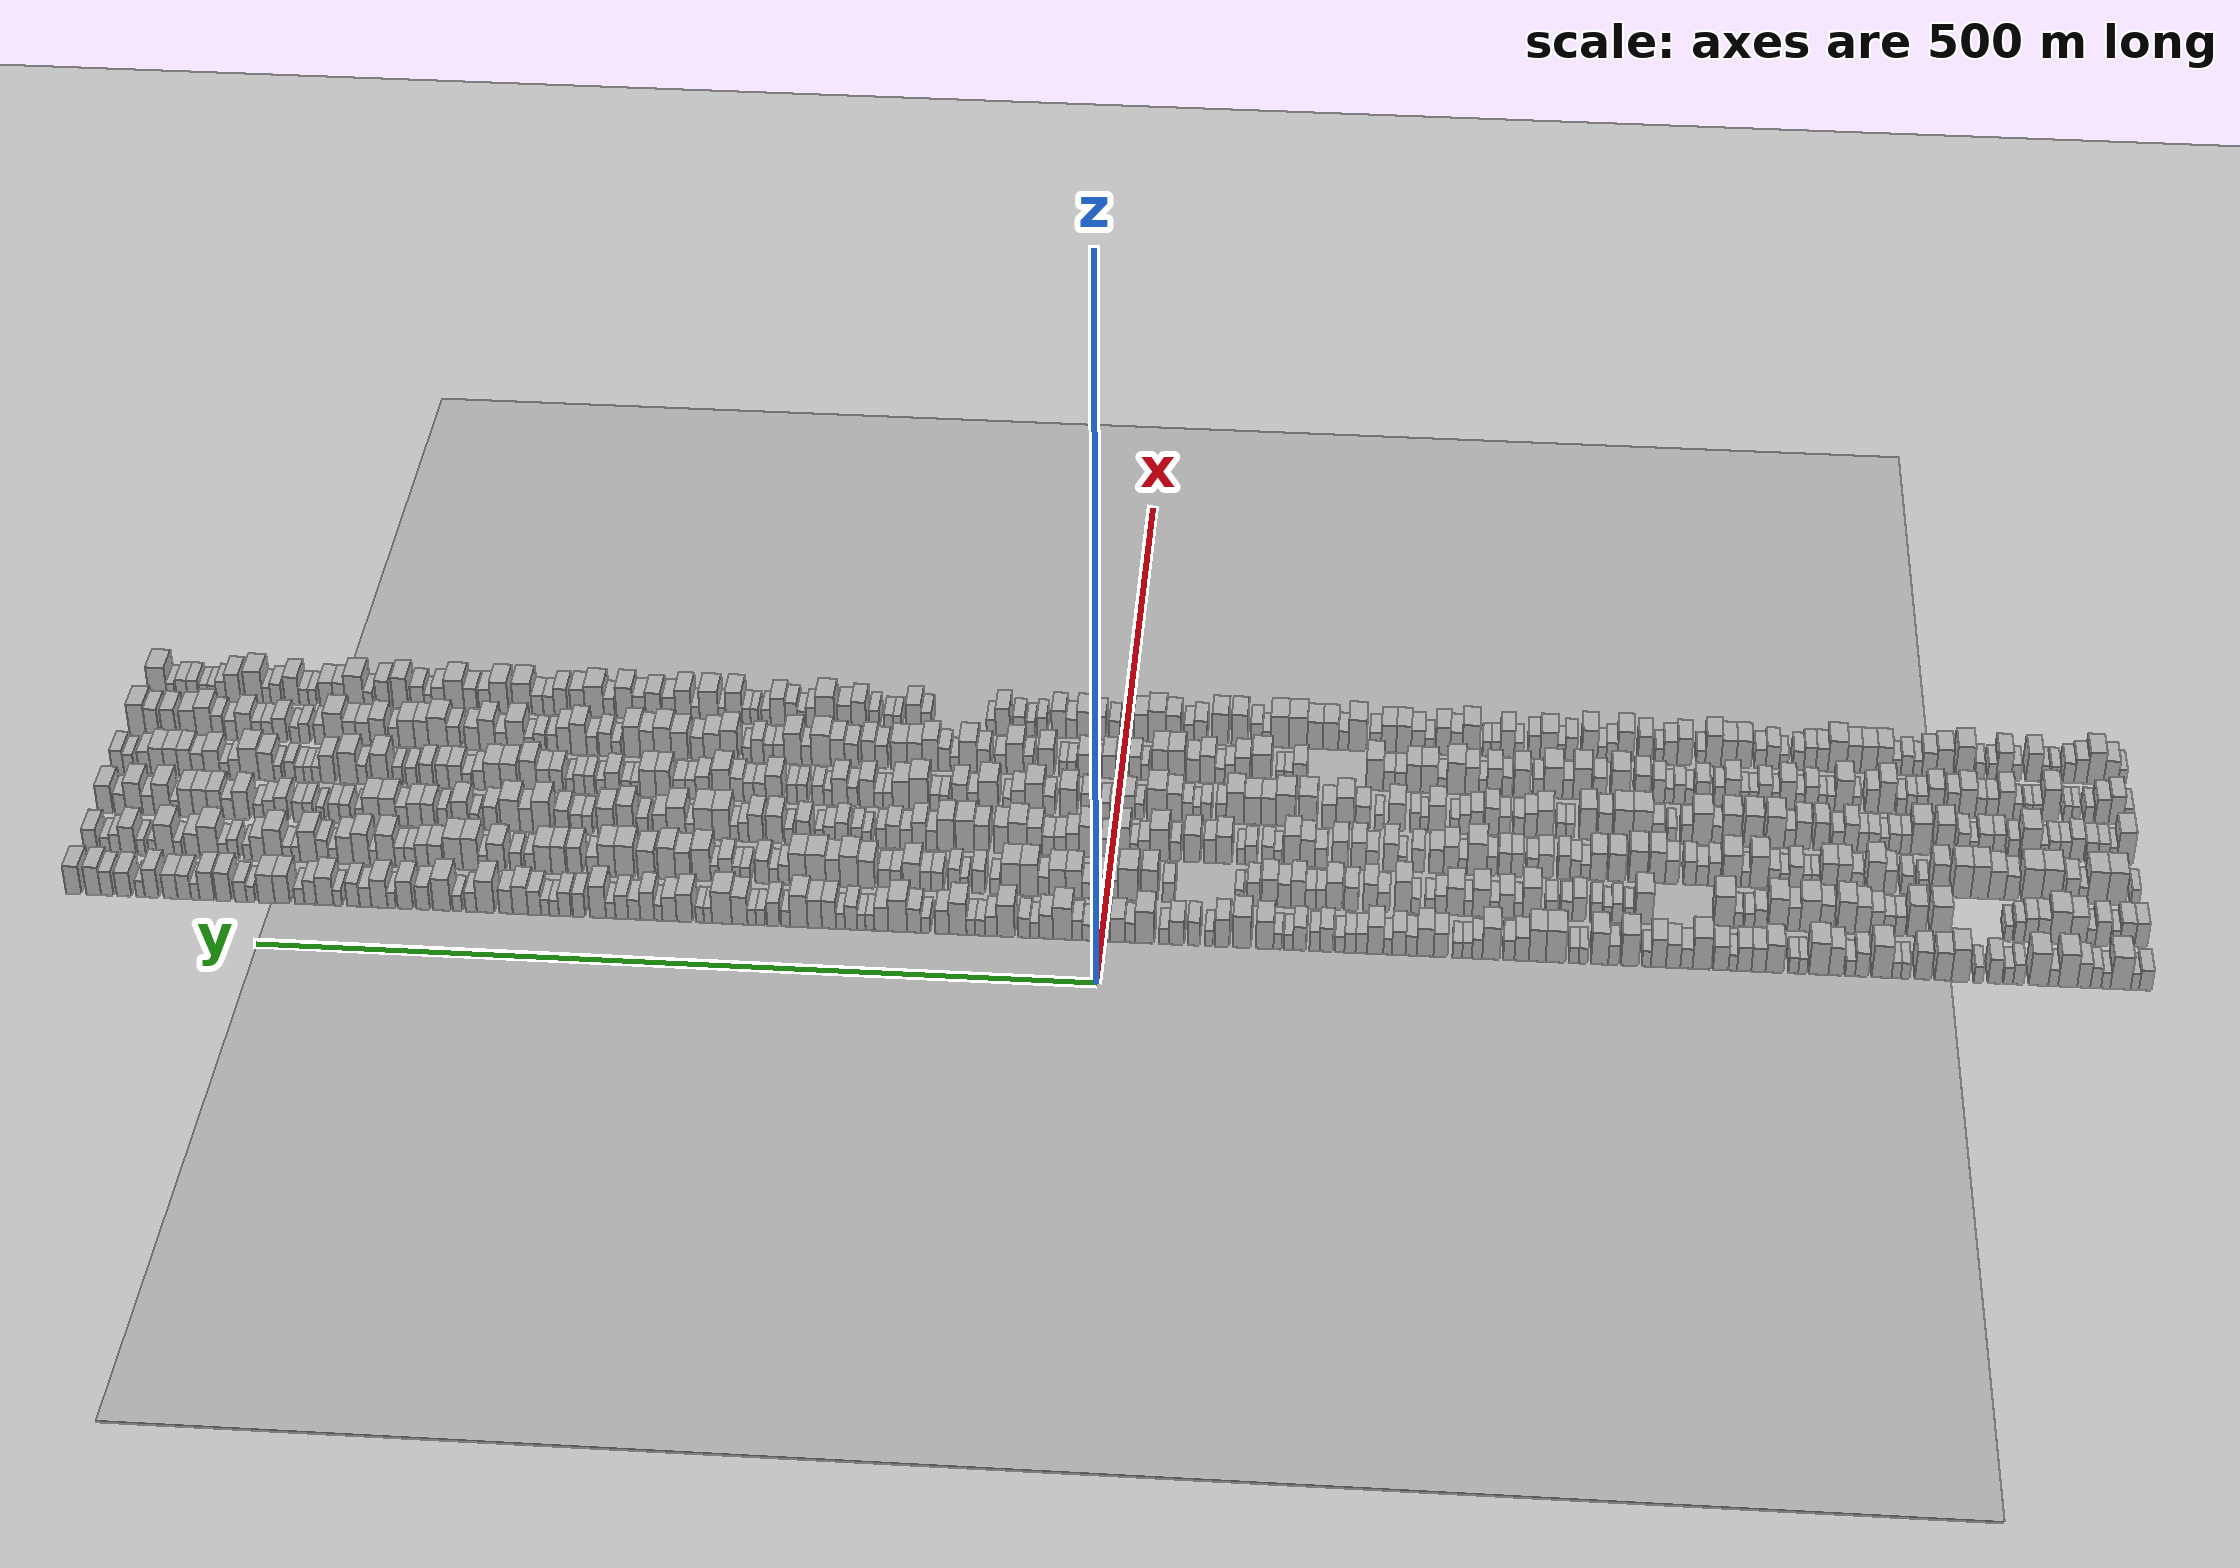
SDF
<?xml version="1.0" encoding="utf-8"?>

<sdf version="1.6">

   <world name="default">

      <gui fullscreen="0">

         <camera name="user_camera">

            <pose>-15 0 4.57585 0 0 0</pose>

            <view_controller>orbit</view_controller>

         </camera>

      </gui>

      <scene>

         <sky>

           <clouds>

             <speed>12</speed>

           </clouds>

         </sky>

         <ambient>0.4 0.4 0.4 1</ambient>

         <background>0.7 0.7 0.7 1</background>

         <shadows>1</shadows>

      </scene>

      <gravity>0 0 -9.8066</gravity>

      <magnetic_field>6e-06 2.3e-05 -4.2e-05</magnetic_field>

      <physics default="0" name="default_physics" type="ode">

         <ode>

            <solver>

               <type>quick</type>

               <iters>10</iters>

               <sor>1.0</sor>

               <use_dynamic_moi_rescaling>0</use_dynamic_moi_rescaling>

            </solver>

            <constraints>

               <cfm>0</cfm>

               <erp>0.2</erp>

               <contact_max_correcting_vel>100</contact_max_correcting_vel>

               <contact_surface_layer>0.001</contact_surface_layer>

            </constraints>

         </ode>

         <max_step_size>0.004</max_step_size>

         <real_time_factor>1</real_time_factor>

         <real_time_update_rate>250</real_time_update_rate>

      </physics>

      <light name="sun" type="directional">

         <cast_shadows>1</cast_shadows>

         <pose>0 0 10 0 0 0</pose>

         <diffuse>0.8 0.8 0.8 1</diffuse>

         <specular>0.2 0.2 0.2 1</specular>

         <attenuation>

            <range>1000</range>

            <constant>0.9</constant>

            <linear>0.01</linear>

            <quadratic>0.001</quadratic>

         </attenuation>

         <direction>-0.5 0.1 -0.9</direction>

      </light>

      <include>

         <name>ground_plane_1</name>

         <uri>model://HANNAS_ground_plane</uri>

         <pose>0 0 0  0 0 0</pose>

      </include>

      <include>

         <name>ground_plane_2</name>

         <uri>model://HANNAS_ground_plane</uri>

         <pose>100 0 0  0 0 0</pose>

      </include>

      <model name="building_1">

         <static>1</static>

         <pose frame="">50.0000 -613.3078 0 0.000000 0.000000 0.000000</pose>

         <link name="link">

            <pose frame="">0 0 7.50 0 0 0</pose>

            <collision name="collision">

               <geometry>

                  <box>

                     <size>20.0000 7.3845 15.0000</size>

                  </box>

               </geometry>

               <max_contacts>10</max_contacts>

               <surface>

                  <contact>

                     <ode/>

                  </contact>

                  <bounce/>

                  <friction>

                     <torsional>

                        <ode/>

                     </torsional>

                     <ode/>

                  </friction>

               </surface>

            </collision>

            <visual name="visual">

               <cast_shadows>0</cast_shadows>

               <geometry>

                  <box>

                     <size>20.0000 7.3845 15.0000</size>

                  </box>

               </geometry>

               <material>

                  <script>

                     <uri>model://HANNAS_wall/materials/scripts</uri>

                     <uri>model://HANNAS_wall/materials/textures</uri>

                     <name>vrc/HANNAS_wall</name>

                  </script>

               </material>

            </visual>

            <self_collide>0</self_collide>

            <enable_wind>0</enable_wind>

            <kinematic>0</kinematic>

         </link>

      </model>

      <model name="building_2">

         <static>1</static>

         <pose frame="">50.0000 -607.1452 0 0.000000 0.000000 0.000000</pose>

         <link name="link">

            <pose frame="">0 0 6.00 0 0 0</pose>

            <collision name="collision">

               <geometry>

                  <box>

                     <size>20.0000 4.9407 12.0000</size>

                  </box>

               </geometry>

               <max_contacts>10</max_contacts>

               <surface>

                  <contact>

                     <ode/>

                  </contact>

                  <bounce/>

                  <friction>

                     <torsional>

                        <ode/>

                     </torsional>

                     <ode/>

                  </friction>

               </surface>

            </collision>

            <visual name="visual">

               <cast_shadows>0</cast_shadows>

               <geometry>

                  <box>

                     <size>20.0000 4.9407 12.0000</size>

                  </box>

               </geometry>

               <material>

                  <script>

                     <uri>model://HANNAS_wall/materials/scripts</uri>

                     <uri>model://HANNAS_wall/materials/textures</uri>

                     <name>vrc/HANNAS_wall</name>

                  </script>

               </material>

            </visual>

            <self_collide>0</self_collide>

            <enable_wind>0</enable_wind>

            <kinematic>0</kinematic>

         </link>

      </model>

      <model name="building_3">

         <static>1</static>

         <pose frame="">50.0000 -598.7506 0 0.000000 0.000000 0.000000</pose>

         <link name="link">

            <pose frame="">0 0 12.00 0 0 0</pose>

            <collision name="collision">

               <geometry>

                  <box>

                     <size>20.0000 11.8484 24.0000</size>

                  </box>

               </geometry>

               <max_contacts>10</max_contacts>

               <surface>

                  <contact>

                     <ode/>

                  </contact>

                  <bounce/>

                  <friction>

                     <torsional>

                        <ode/>

                     </torsional>

                     <ode/>

                  </friction>

               </surface>

            </collision>

            <visual name="visual">

               <cast_shadows>0</cast_shadows>

               <geometry>

                  <box>

                     <size>20.0000 11.8484 24.0000</size>

                  </box>

               </geometry>

               <material>

                  <script>

                     <uri>model://HANNAS_wall/materials/scripts</uri>

                     <uri>model://HANNAS_wall/materials/textures</uri>

                     <name>vrc/HANNAS_wall</name>

                  </script>

               </material>

            </visual>

            <self_collide>0</self_collide>

            <enable_wind>0</enable_wind>

            <kinematic>0</kinematic>

         </link>

      </model>

      <model name="building_4">

         <static>1</static>

         <pose frame="">50.0000 -590.1358 0 0.000000 0.000000 0.000000</pose>

         <link name="link">

            <pose frame="">0 0 6.00 0 0 0</pose>

            <collision name="collision">

               <geometry>

                  <box>

                     <size>20.0000 5.3811 12.0000</size>

                  </box>

               </geometry>

               <max_contacts>10</max_contacts>

               <surface>

                  <contact>

                     <ode/>

                  </contact>

                  <bounce/>

                  <friction>

                     <torsional>

                        <ode/>

                     </torsional>

                     <ode/>

                  </friction>

               </surface>

            </collision>

            <visual name="visual">

               <cast_shadows>0</cast_shadows>

               <geometry>

                  <box>

                     <size>20.0000 5.3811 12.0000</size>

                  </box>

               </geometry>

               <material>

                  <script>

                     <uri>model://HANNAS_wall/materials/scripts</uri>

                     <uri>model://HANNAS_wall/materials/textures</uri>

                     <name>vrc/HANNAS_wall</name>

                  </script>

               </material>

            </visual>

            <self_collide>0</self_collide>

            <enable_wind>0</enable_wind>

            <kinematic>0</kinematic>

         </link>

      </model>

      <model name="building_5">

         <static>1</static>

         <pose frame="">50.0000 -584.3624 0 0.000000 0.000000 0.000000</pose>

         <link name="link">

            <pose frame="">0 0 7.50 0 0 0</pose>

            <collision name="collision">

               <geometry>

                  <box>

                     <size>20.0000 6.1656 15.0000</size>

                  </box>

               </geometry>

               <max_contacts>10</max_contacts>

               <surface>

                  <contact>

                     <ode/>

                  </contact>

                  <bounce/>

                  <friction>

                     <torsional>

                        <ode/>

                     </torsional>

                     <ode/>

                  </friction>

               </surface>

            </collision>

            <visual name="visual">

               <cast_shadows>0</cast_shadows>

               <geometry>

                  <box>

                     <size>20.0000 6.1656 15.0000</size>

                  </box>

               </geometry>

               <material>

                  <script>

                     <uri>model://HANNAS_wall/materials/scripts</uri>

                     <uri>model://HANNAS_wall/materials/textures</uri>

                     <name>vrc/HANNAS_wall</name>

                  </script>

               </material>

            </visual>

            <self_collide>0</self_collide>

            <enable_wind>0</enable_wind>

            <kinematic>0</kinematic>

         </link>

      </model>

      <model name="building_6">

         <static>1</static>

         <pose frame="">50.0000 -577.4387 0 0.000000 0.000000 0.000000</pose>

         <link name="link">

            <pose frame="">0 0 9.00 0 0 0</pose>

            <collision name="collision">

               <geometry>

                  <box>

                     <size>20.0000 7.6817 18.0000</size>

                  </box>

               </geometry>

               <max_contacts>10</max_contacts>

               <surface>

                  <contact>

                     <ode/>

                  </contact>

                  <bounce/>

                  <friction>

                     <torsional>

                        <ode/>

                     </torsional>

                     <ode/>

                  </friction>

               </surface>

            </collision>

            <visual name="visual">

               <cast_shadows>0</cast_shadows>

               <geometry>

                  <box>

                     <size>20.0000 7.6817 18.0000</size>

                  </box>

               </geometry>

               <material>

                  <script>

                     <uri>model://HANNAS_wall/materials/scripts</uri>

                     <uri>model://HANNAS_wall/materials/textures</uri>

                     <name>vrc/HANNAS_wall</name>

                  </script>

               </material>

            </visual>

            <self_collide>0</self_collide>

            <enable_wind>0</enable_wind>

            <kinematic>0</kinematic>

         </link>

      </model>

      <model name="building_7">

         <static>1</static>

         <pose frame="">50.0000 -568.0621 0 0.000000 0.000000 0.000000</pose>

         <link name="link">

            <pose frame="">0 0 12.00 0 0 0</pose>

            <collision name="collision">

               <geometry>

                  <box>

                     <size>20.0000 11.0716 24.0000</size>

                  </box>

               </geometry>

               <max_contacts>10</max_contacts>

               <surface>

                  <contact>

                     <ode/>

                  </contact>

                  <bounce/>

                  <friction>

                     <torsional>

                        <ode/>

                     </torsional>

                     <ode/>

                  </friction>

               </surface>

            </collision>

            <visual name="visual">

               <cast_shadows>0</cast_shadows>

               <geometry>

                  <box>

                     <size>20.0000 11.0716 24.0000</size>

                  </box>

               </geometry>

               <material>

                  <script>

                     <uri>model://HANNAS_wall/materials/scripts</uri>

                     <uri>model://HANNAS_wall/materials/textures</uri>

                     <name>vrc/HANNAS_wall</name>

                  </script>

               </material>

            </visual>

            <self_collide>0</self_collide>

            <enable_wind>0</enable_wind>

            <kinematic>0</kinematic>

         </link>

      </model>

      <model name="building_8">

         <static>1</static>

         <pose frame="">50.0000 -559.6764 0 0.000000 0.000000 0.000000</pose>

         <link name="link">

            <pose frame="">0 0 6.00 0 0 0</pose>

            <collision name="collision">

               <geometry>

                  <box>

                     <size>20.0000 5.6997 12.0000</size>

                  </box>

               </geometry>

               <max_contacts>10</max_contacts>

               <surface>

                  <contact>

                     <ode/>

                  </contact>

                  <bounce/>

                  <friction>

                     <torsional>

                        <ode/>

                     </torsional>

                     <ode/>

                  </friction>

               </surface>

            </collision>

            <visual name="visual">

               <cast_shadows>0</cast_shadows>

               <geometry>

                  <box>

                     <size>20.0000 5.6997 12.0000</size>

                  </box>

               </geometry>

               <material>

                  <script>

                     <uri>model://HANNAS_wall/materials/scripts</uri>

                     <uri>model://HANNAS_wall/materials/textures</uri>

                     <name>vrc/HANNAS_wall</name>

                  </script>

               </material>

            </visual>

            <self_collide>0</self_collide>

            <enable_wind>0</enable_wind>

            <kinematic>0</kinematic>

         </link>

      </model>

      <model name="building_9">

         <static>1</static>

         <pose frame="">50.0000 -551.1510 0 0.000000 0.000000 0.000000</pose>

         <link name="link">

            <pose frame="">0 0 12.00 0 0 0</pose>

            <collision name="collision">

               <geometry>

                  <box>

                     <size>20.0000 11.3511 24.0000</size>

                  </box>

               </geometry>

               <max_contacts>10</max_contacts>

               <surface>

                  <contact>

                     <ode/>

                  </contact>

                  <bounce/>

                  <friction>

                     <torsional>

                        <ode/>

                     </torsional>

                     <ode/>

                  </friction>

               </surface>

            </collision>

            <visual name="visual">

               <cast_shadows>0</cast_shadows>

               <geometry>

                  <box>

                     <size>20.0000 11.3511 24.0000</size>

                  </box>

               </geometry>

               <material>

                  <script>

                     <uri>model://HANNAS_wall/materials/scripts</uri>

                     <uri>model://HANNAS_wall/materials/textures</uri>

                     <name>vrc/HANNAS_wall</name>

                  </script>

               </material>

            </visual>

            <self_collide>0</self_collide>

            <enable_wind>0</enable_wind>

            <kinematic>0</kinematic>

         </link>

      </model>

      <model name="building_10">

         <static>1</static>

         <pose frame="">50.0000 -539.3572 0 0.000000 0.000000 0.000000</pose>

         <link name="link">

            <pose frame="">0 0 7.50 0 0 0</pose>

            <collision name="collision">

               <geometry>

                  <box>

                     <size>20.0000 6.2365 15.0000</size>

                  </box>

               </geometry>

               <max_contacts>10</max_contacts>

               <surface>

                  <contact>

                     <ode/>

                  </contact>

                  <bounce/>

                  <friction>

                     <torsional>

                        <ode/>

                     </torsional>

                     <ode/>

                  </friction>

               </surface>

            </collision>

            <visual name="visual">

               <cast_shadows>0</cast_shadows>

               <geometry>

                  <box>

                     <size>20.0000 6.2365 15.0000</size>

                  </box>

               </geometry>

               <material>

                  <script>

                     <uri>model://HANNAS_wall/materials/scripts</uri>

                     <uri>model://HANNAS_wall/materials/textures</uri>

                     <name>vrc/HANNAS_wall</name>

                  </script>

               </material>

            </visual>

            <self_collide>0</self_collide>

            <enable_wind>0</enable_wind>

            <kinematic>0</kinematic>

         </link>

      </model>

      <model name="building_11">

         <static>1</static>

         <pose frame="">50.0000 -533.4282 0 0.000000 0.000000 0.000000</pose>

         <link name="link">

            <pose frame="">0 0 6.00 0 0 0</pose>

            <collision name="collision">

               <geometry>

                  <box>

                     <size>20.0000 5.6216 12.0000</size>

                  </box>

               </geometry>

               <max_contacts>10</max_contacts>

               <surface>

                  <contact>

                     <ode/>

                  </contact>

                  <bounce/>

                  <friction>

                     <torsional>

                        <ode/>

                     </torsional>

                     <ode/>

                  </friction>

               </surface>

            </collision>

            <visual name="visual">

               <cast_shadows>0</cast_shadows>

               <geometry>

                  <box>

                     <size>20.0000 5.6216 12.0000</size>

                  </box>

               </geometry>

               <material>

                  <script>

                     <uri>model://HANNAS_wall/materials/scripts</uri>

                     <uri>model://HANNAS_wall/materials/textures</uri>

                     <name>vrc/HANNAS_wall</name>

                  </script>

               </material>

            </visual>

            <self_collide>0</self_collide>

            <enable_wind>0</enable_wind>

            <kinematic>0</kinematic>

         </link>

      </model>

      <model name="building_12">

         <static>1</static>

         <pose frame="">50.0000 -525.5855 0 0.000000 0.000000 0.000000</pose>

         <link name="link">

            <pose frame="">0 0 9.00 0 0 0</pose>

            <collision name="collision">

               <geometry>

                  <box>

                     <size>20.0000 8.0637 18.0000</size>

                  </box>

               </geometry>

               <max_contacts>10</max_contacts>

               <surface>

                  <contact>

                     <ode/>

                  </contact>

                  <bounce/>

                  <friction>

                     <torsional>

                        <ode/>

                     </torsional>

                     <ode/>

                  </friction>

               </surface>

            </collision>

            <visual name="visual">

               <cast_shadows>0</cast_shadows>

               <geometry>

                  <box>

                     <size>20.0000 8.0637 18.0000</size>

                  </box>

               </geometry>

               <material>

                  <script>

                     <uri>model://HANNAS_wall/materials/scripts</uri>

                     <uri>model://HANNAS_wall/materials/textures</uri>

                     <name>vrc/HANNAS_wall</name>

                  </script>

               </material>

            </visual>

            <self_collide>0</self_collide>

            <enable_wind>0</enable_wind>

            <kinematic>0</kinematic>

         </link>

      </model>

      <model name="building_13">

         <static>1</static>

         <pose frame="">50.0000 -515.9290 0 0.000000 0.000000 0.000000</pose>

         <link name="link">

            <pose frame="">0 0 6.00 0 0 0</pose>

            <collision name="collision">

               <geometry>

                  <box>

                     <size>20.0000 5.2492 12.0000</size>

                  </box>

               </geometry>

               <max_contacts>10</max_contacts>

               <surface>

                  <contact>

                     <ode/>

                  </contact>

                  <bounce/>

                  <friction>

                     <torsional>

                        <ode/>

                     </torsional>

                     <ode/>

                  </friction>

               </surface>

            </collision>

            <visual name="visual">

               <cast_shadows>0</cast_shadows>

               <geometry>

                  <box>

                     <size>20.0000 5.2492 12.0000</size>

                  </box>

               </geometry>

               <material>

                  <script>

                     <uri>model://HANNAS_wall/materials/scripts</uri>

                     <uri>model://HANNAS_wall/materials/textures</uri>

                     <name>vrc/HANNAS_wall</name>

                  </script>

               </material>

            </visual>

            <self_collide>0</self_collide>

            <enable_wind>0</enable_wind>

            <kinematic>0</kinematic>

         </link>

      </model>

      <model name="building_14">

         <static>1</static>

         <pose frame="">50.0000 -505.2257 0 0.000000 0.000000 0.000000</pose>

         <link name="link">

            <pose frame="">0 0 12.00 0 0 0</pose>

            <collision name="collision">

               <geometry>

                  <box>

                     <size>20.0000 10.1575 24.0000</size>

                  </box>

               </geometry>

               <max_contacts>10</max_contacts>

               <surface>

                  <contact>

                     <ode/>

                  </contact>

                  <bounce/>

                  <friction>

                     <torsional>

                        <ode/>

                     </torsional>

                     <ode/>

                  </friction>

               </surface>

            </collision>

            <visual name="visual">

               <cast_shadows>0</cast_shadows>

               <geometry>

                  <box>

                     <size>20.0000 10.1575 24.0000</size>

                  </box>

               </geometry>

               <material>

                  <script>

                     <uri>model://HANNAS_wall/materials/scripts</uri>

                     <uri>model://HANNAS_wall/materials/textures</uri>

                     <name>vrc/HANNAS_wall</name>

                  </script>

               </material>

            </visual>

            <self_collide>0</self_collide>

            <enable_wind>0</enable_wind>

            <kinematic>0</kinematic>

         </link>

      </model>

      <model name="building_15">

         <static>1</static>

         <pose frame="">50.0000 -495.3241 0 0.000000 0.000000 0.000000</pose>

         <link name="link">

            <pose frame="">0 0 10.50 0 0 0</pose>

            <collision name="collision">

               <geometry>

                  <box>

                     <size>20.0000 9.6456 21.0000</size>

                  </box>

               </geometry>

               <max_contacts>10</max_contacts>

               <surface>

                  <contact>

                     <ode/>

                  </contact>

                  <bounce/>

                  <friction>

                     <torsional>

                        <ode/>

                     </torsional>

                     <ode/>

                  </friction>

               </surface>

            </collision>

            <visual name="visual">

               <cast_shadows>0</cast_shadows>

               <geometry>

                  <box>

                     <size>20.0000 9.6456 21.0000</size>

                  </box>

               </geometry>

               <material>

                  <script>

                     <uri>model://HANNAS_wall/materials/scripts</uri>

                     <uri>model://HANNAS_wall/materials/textures</uri>

                     <name>vrc/HANNAS_wall</name>

                  </script>

               </material>

            </visual>

            <self_collide>0</self_collide>

            <enable_wind>0</enable_wind>

            <kinematic>0</kinematic>

         </link>

      </model>

      <model name="building_16">

         <static>1</static>

         <pose frame="">50.0000 -483.7051 0 0.000000 0.000000 0.000000</pose>

         <link name="link">

            <pose frame="">0 0 10.50 0 0 0</pose>

            <collision name="collision">

               <geometry>

                  <box>

                     <size>20.0000 9.5925 21.0000</size>

                  </box>

               </geometry>

               <max_contacts>10</max_contacts>

               <surface>

                  <contact>

                     <ode/>

                  </contact>

                  <bounce/>

                  <friction>

                     <torsional>

                        <ode/>

                     </torsional>

                     <ode/>

                  </friction>

               </surface>

            </collision>

            <visual name="visual">

               <cast_shadows>0</cast_shadows>

               <geometry>

                  <box>

                     <size>20.0000 9.5925 21.0000</size>

                  </box>

               </geometry>

               <material>

                  <script>

                     <uri>model://HANNAS_wall/materials/scripts</uri>

                     <uri>model://HANNAS_wall/materials/textures</uri>

                     <name>vrc/HANNAS_wall</name>

                  </script>

               </material>

            </visual>

            <self_collide>0</self_collide>

            <enable_wind>0</enable_wind>

            <kinematic>0</kinematic>

         </link>

      </model>

      <model name="building_17">

         <static>1</static>

         <pose frame="">50.0000 -473.2947 0 0.000000 0.000000 0.000000</pose>

         <link name="link">

            <pose frame="">0 0 6.00 0 0 0</pose>

            <collision name="collision">

               <geometry>

                  <box>

                     <size>20.0000 5.2283 12.0000</size>

                  </box>

               </geometry>

               <max_contacts>10</max_contacts>

               <surface>

                  <contact>

                     <ode/>

                  </contact>

                  <bounce/>

                  <friction>

                     <torsional>

                        <ode/>

                     </torsional>

                     <ode/>

                  </friction>

               </surface>

            </collision>

            <visual name="visual">

               <cast_shadows>0</cast_shadows>

               <geometry>

                  <box>

                     <size>20.0000 5.2283 12.0000</size>

                  </box>

               </geometry>

               <material>

                  <script>

                     <uri>model://HANNAS_wall/materials/scripts</uri>

                     <uri>model://HANNAS_wall/materials/textures</uri>

                     <name>vrc/HANNAS_wall</name>

                  </script>

               </material>

            </visual>

            <self_collide>0</self_collide>

            <enable_wind>0</enable_wind>

            <kinematic>0</kinematic>

         </link>

      </model>

      <model name="building_18">

         <static>1</static>

         <pose frame="">50.0000 -468.0105 0 0.000000 0.000000 0.000000</pose>

         <link name="link">

            <pose frame="">0 0 6.00 0 0 0</pose>

            <collision name="collision">

               <geometry>

                  <box>

                     <size>20.0000 5.3400 12.0000</size>

                  </box>

               </geometry>

               <max_contacts>10</max_contacts>

               <surface>

                  <contact>

                     <ode/>

                  </contact>

                  <bounce/>

                  <friction>

                     <torsional>

                        <ode/>

                     </torsional>

                     <ode/>

                  </friction>

               </surface>

            </collision>

            <visual name="visual">

               <cast_shadows>0</cast_shadows>

               <geometry>

                  <box>

                     <size>20.0000 5.3400 12.0000</size>

                  </box>

               </geometry>

               <material>

                  <script>

                     <uri>model://HANNAS_wall/materials/scripts</uri>

                     <uri>model://HANNAS_wall/materials/textures</uri>

                     <name>vrc/HANNAS_wall</name>

                  </script>

               </material>

            </visual>

            <self_collide>0</self_collide>

            <enable_wind>0</enable_wind>

            <kinematic>0</kinematic>

         </link>

      </model>

      <model name="building_19">

         <static>1</static>

         <pose frame="">50.0000 -459.5287 0 0.000000 0.000000 0.000000</pose>

         <link name="link">

            <pose frame="">0 0 12.00 0 0 0</pose>

            <collision name="collision">

               <geometry>

                  <box>

                     <size>20.0000 11.6236 24.0000</size>

                  </box>

               </geometry>

               <max_contacts>10</max_contacts>

               <surface>

                  <contact>

                     <ode/>

                  </contact>

                  <bounce/>

                  <friction>

                     <torsional>

                        <ode/>

                     </torsional>

                     <ode/>

                  </friction>

               </surface>

            </collision>

            <visual name="visual">

               <cast_shadows>0</cast_shadows>

               <geometry>

                  <box>

                     <size>20.0000 11.6236 24.0000</size>

                  </box>

               </geometry>

               <material>

                  <script>

                     <uri>model://HANNAS_wall/materials/scripts</uri>

                     <uri>model://HANNAS_wall/materials/textures</uri>

                     <name>vrc/HANNAS_wall</name>

                  </script>

               </material>

            </visual>

            <self_collide>0</self_collide>

            <enable_wind>0</enable_wind>

            <kinematic>0</kinematic>

         </link>

      </model>

      <model name="building_20">

         <static>1</static>

         <pose frame="">50.0000 -447.8351 0 0.000000 0.000000 0.000000</pose>

         <link name="link">

            <pose frame="">0 0 9.00 0 0 0</pose>

            <collision name="collision">

               <geometry>

                  <box>

                     <size>20.0000 7.7635 18.0000</size>

                  </box>

               </geometry>

               <max_contacts>10</max_contacts>

               <surface>

                  <contact>

                     <ode/>

                  </contact>

                  <bounce/>

                  <friction>

                     <torsional>

                        <ode/>

                     </torsional>

                     <ode/>

                  </friction>

               </surface>

            </collision>

            <visual name="visual">

               <cast_shadows>0</cast_shadows>

               <geometry>

                  <box>

                     <size>20.0000 7.7635 18.0000</size>

                  </box>

               </geometry>

               <material>

                  <script>

                     <uri>model://HANNAS_wall/materials/scripts</uri>

                     <uri>model://HANNAS_wall/materials/textures</uri>

                     <name>vrc/HANNAS_wall</name>

                  </script>

               </material>

            </visual>

            <self_collide>0</self_collide>

            <enable_wind>0</enable_wind>

            <kinematic>0</kinematic>

         </link>

      </model>

      <model name="building_21">

         <static>1</static>

         <pose frame="">50.0000 -441.0553 0 0.000000 0.000000 0.000000</pose>

         <link name="link">

            <pose frame="">0 0 6.00 0 0 0</pose>

            <collision name="collision">

               <geometry>

                  <box>

                     <size>20.0000 5.7961 12.0000</size>

                  </box>

               </geometry>

               <max_contacts>10</max_contacts>

               <surface>

                  <contact>

                     <ode/>

                  </contact>

                  <bounce/>

                  <friction>

                     <torsional>

                        <ode/>

                     </torsional>

                     <ode/>

                  </friction>

               </surface>

            </collision>

            <visual name="visual">

               <cast_shadows>0</cast_shadows>

               <geometry>

                  <box>

                     <size>20.0000 5.7961 12.0000</size>

                  </box>

               </geometry>

               <material>

                  <script>

                     <uri>model://HANNAS_wall/materials/scripts</uri>

                     <uri>model://HANNAS_wall/materials/textures</uri>

                     <name>vrc/HANNAS_wall</name>

                  </script>

               </material>

            </visual>

            <self_collide>0</self_collide>

            <enable_wind>0</enable_wind>

            <kinematic>0</kinematic>

         </link>

      </model>

      <model name="building_22">

         <static>1</static>

         <pose frame="">50.0000 -432.7885 0 0.000000 0.000000 0.000000</pose>

         <link name="link">

            <pose frame="">0 0 10.50 0 0 0</pose>

            <collision name="collision">

               <geometry>

                  <box>

                     <size>20.0000 8.7375 21.0000</size>

                  </box>

               </geometry>

               <max_contacts>10</max_contacts>

               <surface>

                  <contact>

                     <ode/>

                  </contact>

                  <bounce/>

                  <friction>

                     <torsional>

                        <ode/>

                     </torsional>

                     <ode/>

                  </friction>

               </surface>

            </collision>

            <visual name="visual">

               <cast_shadows>0</cast_shadows>

               <geometry>

                  <box>

                     <size>20.0000 8.7375 21.0000</size>

                  </box>

               </geometry>

               <material>

                  <script>

                     <uri>model://HANNAS_wall/materials/scripts</uri>

                     <uri>model://HANNAS_wall/materials/textures</uri>

                     <name>vrc/HANNAS_wall</name>

                  </script>

               </material>

            </visual>

            <self_collide>0</self_collide>

            <enable_wind>0</enable_wind>

            <kinematic>0</kinematic>

         </link>

      </model>

      <model name="building_23">

         <static>1</static>

         <pose frame="">50.0000 -422.6834 0 0.000000 0.000000 0.000000</pose>

         <link name="link">

            <pose frame="">0 0 12.00 0 0 0</pose>

            <collision name="collision">

               <geometry>

                  <box>

                     <size>20.0000 11.4728 24.0000</size>

                  </box>

               </geometry>

               <max_contacts>10</max_contacts>

               <surface>

                  <contact>

                     <ode/>

                  </contact>

                  <bounce/>

                  <friction>

                     <torsional>

                        <ode/>

                     </torsional>

                     <ode/>

                  </friction>

               </surface>

            </collision>

            <visual name="visual">

               <cast_shadows>0</cast_shadows>

               <geometry>

                  <box>

                     <size>20.0000 11.4728 24.0000</size>

                  </box>

               </geometry>

               <material>

                  <script>

                     <uri>model://HANNAS_wall/materials/scripts</uri>

                     <uri>model://HANNAS_wall/materials/textures</uri>

                     <name>vrc/HANNAS_wall</name>

                  </script>

               </material>

            </visual>

            <self_collide>0</self_collide>

            <enable_wind>0</enable_wind>

            <kinematic>0</kinematic>

         </link>

      </model>

      <model name="building_24">

         <static>1</static>

         <pose frame="">50.0000 -413.3652 0 0.000000 0.000000 0.000000</pose>

         <link name="link">

            <pose frame="">0 0 6.00 0 0 0</pose>

            <collision name="collision">

               <geometry>

                  <box>

                     <size>20.0000 5.1637 12.0000</size>

                  </box>

               </geometry>

               <max_contacts>10</max_contacts>

               <surface>

                  <contact>

                     <ode/>

                  </contact>

                  <bounce/>

                  <friction>

                     <torsional>

                        <ode/>

                     </torsional>

                     <ode/>

                  </friction>

               </surface>

            </collision>

            <visual name="visual">

               <cast_shadows>0</cast_shadows>

               <geometry>

                  <box>

                     <size>20.0000 5.1637 12.0000</size>

                  </box>

               </geometry>

               <material>

                  <script>

                     <uri>model://HANNAS_wall/materials/scripts</uri>

                     <uri>model://HANNAS_wall/materials/textures</uri>

                     <name>vrc/HANNAS_wall</name>

                  </script>

               </material>

            </visual>

            <self_collide>0</self_collide>

            <enable_wind>0</enable_wind>

            <kinematic>0</kinematic>

         </link>

      </model>

      <model name="building_25">

         <static>1</static>

         <pose frame="">50.0000 -407.8908 0 0.000000 0.000000 0.000000</pose>

         <link name="link">

            <pose frame="">0 0 6.00 0 0 0</pose>

            <collision name="collision">

               <geometry>

                  <box>

                     <size>20.0000 5.7851 12.0000</size>

                  </box>

               </geometry>

               <max_contacts>10</max_contacts>

               <surface>

                  <contact>

                     <ode/>

                  </contact>

                  <bounce/>

                  <friction>

                     <torsional>

                        <ode/>

                     </torsional>

                     <ode/>

                  </friction>

               </surface>

            </collision>

            <visual name="visual">

               <cast_shadows>0</cast_shadows>

               <geometry>

                  <box>

                     <size>20.0000 5.7851 12.0000</size>

                  </box>

               </geometry>

               <material>

                  <script>

                     <uri>model://HANNAS_wall/materials/scripts</uri>

                     <uri>model://HANNAS_wall/materials/textures</uri>

                     <name>vrc/HANNAS_wall</name>

                  </script>

               </material>

            </visual>

            <self_collide>0</self_collide>

            <enable_wind>0</enable_wind>

            <kinematic>0</kinematic>

         </link>

      </model>

      <model name="building_26">

         <static>1</static>

         <pose frame="">50.0000 -396.7628 0 0.000000 0.000000 0.000000</pose>

         <link name="link">

            <pose frame="">0 0 10.50 0 0 0</pose>

            <collision name="collision">

               <geometry>

                  <box>

                     <size>20.0000 10.4707 21.0000</size>

                  </box>

               </geometry>

               <max_contacts>10</max_contacts>

               <surface>

                  <contact>

                     <ode/>

                  </contact>

                  <bounce/>

                  <friction>

                     <torsional>

                        <ode/>

                     </torsional>

                     <ode/>

                  </friction>

               </surface>

            </collision>

            <visual name="visual">

               <cast_shadows>0</cast_shadows>

               <geometry>

                  <box>

                     <size>20.0000 10.4707 21.0000</size>

                  </box>

               </geometry>

               <material>

                  <script>

                     <uri>model://HANNAS_wall/materials/scripts</uri>

                     <uri>model://HANNAS_wall/materials/textures</uri>

                     <name>vrc/HANNAS_wall</name>

                  </script>

               </material>

            </visual>

            <self_collide>0</self_collide>

            <enable_wind>0</enable_wind>

            <kinematic>0</kinematic>

         </link>

      </model>

      <model name="building_27">

         <static>1</static>

         <pose frame="">50.0000 -387.3897 0 0.000000 0.000000 0.000000</pose>

         <link name="link">

            <pose frame="">0 0 9.00 0 0 0</pose>

            <collision name="collision">

               <geometry>

                  <box>

                     <size>20.0000 8.2756 18.0000</size>

                  </box>

               </geometry>

               <max_contacts>10</max_contacts>

               <surface>

                  <contact>

                     <ode/>

                  </contact>

                  <bounce/>

                  <friction>

                     <torsional>

                        <ode/>

                     </torsional>

                     <ode/>

                  </friction>

               </surface>

            </collision>

            <visual name="visual">

               <cast_shadows>0</cast_shadows>

               <geometry>

                  <box>

                     <size>20.0000 8.2756 18.0000</size>

                  </box>

               </geometry>

               <material>

                  <script>

                     <uri>model://HANNAS_wall/materials/scripts</uri>

                     <uri>model://HANNAS_wall/materials/textures</uri>

                     <name>vrc/HANNAS_wall</name>

                  </script>

               </material>

            </visual>

            <self_collide>0</self_collide>

            <enable_wind>0</enable_wind>

            <kinematic>0</kinematic>

         </link>

      </model>

      <model name="building_28">

         <static>1</static>

         <pose frame="">50.0000 -379.0439 0 0.000000 0.000000 0.000000</pose>

         <link name="link">

            <pose frame="">0 0 9.00 0 0 0</pose>

            <collision name="collision">

               <geometry>

                  <box>

                     <size>20.0000 8.4158 18.0000</size>

                  </box>

               </geometry>

               <max_contacts>10</max_contacts>

               <surface>

                  <contact>

                     <ode/>

                  </contact>

                  <bounce/>

                  <friction>

                     <torsional>

                        <ode/>

                     </torsional>

                     <ode/>

                  </friction>

               </surface>

            </collision>

            <visual name="visual">

               <cast_shadows>0</cast_shadows>

               <geometry>

                  <box>

                     <size>20.0000 8.4158 18.0000</size>

                  </box>

               </geometry>

               <material>

                  <script>

                     <uri>model://HANNAS_wall/materials/scripts</uri>

                     <uri>model://HANNAS_wall/materials/textures</uri>

                     <name>vrc/HANNAS_wall</name>

                  </script>

               </material>

            </visual>

            <self_collide>0</self_collide>

            <enable_wind>0</enable_wind>

            <kinematic>0</kinematic>

         </link>

      </model>

      <model name="building_29">

         <static>1</static>

         <pose frame="">50.0000 -372.3038 0 0.000000 0.000000 0.000000</pose>

         <link name="link">

            <pose frame="">0 0 6.00 0 0 0</pose>

            <collision name="collision">

               <geometry>

                  <box>

                     <size>20.0000 5.0644 12.0000</size>

                  </box>

               </geometry>

               <max_contacts>10</max_contacts>

               <surface>

                  <contact>

                     <ode/>

                  </contact>

                  <bounce/>

                  <friction>

                     <torsional>

                        <ode/>

                     </torsional>

                     <ode/>

                  </friction>

               </surface>

            </collision>

            <visual name="visual">

               <cast_shadows>0</cast_shadows>

               <geometry>

                  <box>

                     <size>20.0000 5.0644 12.0000</size>

                  </box>

               </geometry>

               <material>

                  <script>

                     <uri>model://HANNAS_wall/materials/scripts</uri>

                     <uri>model://HANNAS_wall/materials/textures</uri>

                     <name>vrc/HANNAS_wall</name>

                  </script>

               </material>

            </visual>

            <self_collide>0</self_collide>

            <enable_wind>0</enable_wind>

            <kinematic>0</kinematic>

         </link>

      </model>

      <model name="building_30">

         <static>1</static>

         <pose frame="">50.0000 -365.2722 0 0.000000 0.000000 0.000000</pose>

         <link name="link">

            <pose frame="">0 0 9.00 0 0 0</pose>

            <collision name="collision">

               <geometry>

                  <box>

                     <size>20.0000 8.9988 18.0000</size>

                  </box>

               </geometry>

               <max_contacts>10</max_contacts>

               <surface>

                  <contact>

                     <ode/>

                  </contact>

                  <bounce/>

                  <friction>

                     <torsional>

                        <ode/>

                     </torsional>

                     <ode/>

                  </friction>

               </surface>

            </collision>

            <visual name="visual">

               <cast_shadows>0</cast_shadows>

               <geometry>

                  <box>

                     <size>20.0000 8.9988 18.0000</size>

                  </box>

               </geometry>

               <material>

                  <script>

                     <uri>model://HANNAS_wall/materials/scripts</uri>

                     <uri>model://HANNAS_wall/materials/textures</uri>

                     <name>vrc/HANNAS_wall</name>

                  </script>

               </material>

            </visual>

            <self_collide>0</self_collide>

            <enable_wind>0</enable_wind>

            <kinematic>0</kinematic>

         </link>

      </model>

      <model name="building_31">

         <static>1</static>

         <pose frame="">50.0000 -354.2544 0 0.000000 0.000000 0.000000</pose>

         <link name="link">

            <pose frame="">0 0 12.00 0 0 0</pose>

            <collision name="collision">

               <geometry>

                  <box>

                     <size>20.0000 11.0368 24.0000</size>

                  </box>

               </geometry>

               <max_contacts>10</max_contacts>

               <surface>

                  <contact>

                     <ode/>

                  </contact>

                  <bounce/>

                  <friction>

                     <torsional>

                        <ode/>

                     </torsional>

                     <ode/>

                  </friction>

               </surface>

            </collision>

            <visual name="visual">

               <cast_shadows>0</cast_shadows>

               <geometry>

                  <box>

                     <size>20.0000 11.0368 24.0000</size>

                  </box>

               </geometry>

               <material>

                  <script>

                     <uri>model://HANNAS_wall/materials/scripts</uri>

                     <uri>model://HANNAS_wall/materials/textures</uri>

                     <name>vrc/HANNAS_wall</name>

                  </script>

               </material>

            </visual>

            <self_collide>0</self_collide>

            <enable_wind>0</enable_wind>

            <kinematic>0</kinematic>

         </link>

      </model>

      <model name="building_32">

         <static>1</static>

         <pose frame="">50.0000 -345.1771 0 0.000000 0.000000 0.000000</pose>

         <link name="link">

            <pose frame="">0 0 7.50 0 0 0</pose>

            <collision name="collision">

               <geometry>

                  <box>

                     <size>20.0000 7.1176 15.0000</size>

                  </box>

               </geometry>

               <max_contacts>10</max_contacts>

               <surface>

                  <contact>

                     <ode/>

                  </contact>

                  <bounce/>

                  <friction>

                     <torsional>

                        <ode/>

                     </torsional>

                     <ode/>

                  </friction>

               </surface>

            </collision>

            <visual name="visual">

               <cast_shadows>0</cast_shadows>

               <geometry>

                  <box>

                     <size>20.0000 7.1176 15.0000</size>

                  </box>

               </geometry>

               <material>

                  <script>

                     <uri>model://HANNAS_wall/materials/scripts</uri>

                     <uri>model://HANNAS_wall/materials/textures</uri>

                     <name>vrc/HANNAS_wall</name>

                  </script>

               </material>

            </visual>

            <self_collide>0</self_collide>

            <enable_wind>0</enable_wind>

            <kinematic>0</kinematic>

         </link>

      </model>

      <model name="building_33">

         <static>1</static>

         <pose frame="">50.0000 -337.3446 0 0.000000 0.000000 0.000000</pose>

         <link name="link">

            <pose frame="">0 0 9.00 0 0 0</pose>

            <collision name="collision">

               <geometry>

                  <box>

                     <size>20.0000 8.5474 18.0000</size>

                  </box>

               </geometry>

               <max_contacts>10</max_contacts>

               <surface>

                  <contact>

                     <ode/>

                  </contact>

                  <bounce/>

                  <friction>

                     <torsional>

                        <ode/>

                     </torsional>

                     <ode/>

                  </friction>

               </surface>

            </collision>

            <visual name="visual">

               <cast_shadows>0</cast_shadows>

               <geometry>

                  <box>

                     <size>20.0000 8.5474 18.0000</size>

                  </box>

               </geometry>

               <material>

                  <script>

                     <uri>model://HANNAS_wall/materials/scripts</uri>

                     <uri>model://HANNAS_wall/materials/textures</uri>

                     <name>vrc/HANNAS_wall</name>

                  </script>

               </material>

            </visual>

            <self_collide>0</self_collide>

            <enable_wind>0</enable_wind>

            <kinematic>0</kinematic>

         </link>

      </model>

      <model name="building_34">

         <static>1</static>

         <pose frame="">50.0000 -328.6471 0 0.000000 0.000000 0.000000</pose>

         <link name="link">

            <pose frame="">0 0 10.50 0 0 0</pose>

            <collision name="collision">

               <geometry>

                  <box>

                     <size>20.0000 8.8475 21.0000</size>

                  </box>

               </geometry>

               <max_contacts>10</max_contacts>

               <surface>

                  <contact>

                     <ode/>

                  </contact>

                  <bounce/>

                  <friction>

                     <torsional>

                        <ode/>

                     </torsional>

                     <ode/>

                  </friction>

               </surface>

            </collision>

            <visual name="visual">

               <cast_shadows>0</cast_shadows>

               <geometry>

                  <box>

                     <size>20.0000 8.8475 21.0000</size>

                  </box>

               </geometry>

               <material>

                  <script>

                     <uri>model://HANNAS_wall/materials/scripts</uri>

                     <uri>model://HANNAS_wall/materials/textures</uri>

                     <name>vrc/HANNAS_wall</name>

                  </script>

               </material>

            </visual>

            <self_collide>0</self_collide>

            <enable_wind>0</enable_wind>

            <kinematic>0</kinematic>

         </link>

      </model>

      <model name="building_35">

         <static>1</static>

         <pose frame="">50.0000 -321.6063 0 0.000000 0.000000 0.000000</pose>

         <link name="link">

            <pose frame="">0 0 6.00 0 0 0</pose>

            <collision name="collision">

               <geometry>

                  <box>

                     <size>20.0000 5.2341 12.0000</size>

                  </box>

               </geometry>

               <max_contacts>10</max_contacts>

               <surface>

                  <contact>

                     <ode/>

                  </contact>

                  <bounce/>

                  <friction>

                     <torsional>

                        <ode/>

                     </torsional>

                     <ode/>

                  </friction>

               </surface>

            </collision>

            <visual name="visual">

               <cast_shadows>0</cast_shadows>

               <geometry>

                  <box>

                     <size>20.0000 5.2341 12.0000</size>

                  </box>

               </geometry>

               <material>

                  <script>

                     <uri>model://HANNAS_wall/materials/scripts</uri>

                     <uri>model://HANNAS_wall/materials/textures</uri>

                     <name>vrc/HANNAS_wall</name>

                  </script>

               </material>

            </visual>

            <self_collide>0</self_collide>

            <enable_wind>0</enable_wind>

            <kinematic>0</kinematic>

         </link>

      </model>

      <model name="building_36">

         <static>1</static>

         <pose frame="">50.0000 -311.8154 0 0.000000 0.000000 0.000000</pose>

         <link name="link">

            <pose frame="">0 0 12.00 0 0 0</pose>

            <collision name="collision">

               <geometry>

                  <box>

                     <size>20.0000 10.3477 24.0000</size>

                  </box>

               </geometry>

               <max_contacts>10</max_contacts>

               <surface>

                  <contact>

                     <ode/>

                  </contact>

                  <bounce/>

                  <friction>

                     <torsional>

                        <ode/>

                     </torsional>

                     <ode/>

                  </friction>

               </surface>

            </collision>

            <visual name="visual">

               <cast_shadows>0</cast_shadows>

               <geometry>

                  <box>

                     <size>20.0000 10.3477 24.0000</size>

                  </box>

               </geometry>

               <material>

                  <script>

                     <uri>model://HANNAS_wall/materials/scripts</uri>

                     <uri>model://HANNAS_wall/materials/textures</uri>

                     <name>vrc/HANNAS_wall</name>

                  </script>

               </material>

            </visual>

            <self_collide>0</self_collide>

            <enable_wind>0</enable_wind>

            <kinematic>0</kinematic>

         </link>

      </model>

      <model name="building_37">

         <static>1</static>

         <pose frame="">50.0000 -302.4055 0 0.000000 0.000000 0.000000</pose>

         <link name="link">

            <pose frame="">0 0 7.50 0 0 0</pose>

            <collision name="collision">

               <geometry>

                  <box>

                     <size>20.0000 6.4722 15.0000</size>

                  </box>

               </geometry>

               <max_contacts>10</max_contacts>

               <surface>

                  <contact>

                     <ode/>

                  </contact>

                  <bounce/>

                  <friction>

                     <torsional>

                        <ode/>

                     </torsional>

                     <ode/>

                  </friction>

               </surface>

            </collision>

            <visual name="visual">

               <cast_shadows>0</cast_shadows>

               <geometry>

                  <box>

                     <size>20.0000 6.4722 15.0000</size>

                  </box>

               </geometry>

               <material>

                  <script>

                     <uri>model://HANNAS_wall/materials/scripts</uri>

                     <uri>model://HANNAS_wall/materials/textures</uri>

                     <name>vrc/HANNAS_wall</name>

                  </script>

               </material>

            </visual>

            <self_collide>0</self_collide>

            <enable_wind>0</enable_wind>

            <kinematic>0</kinematic>

         </link>

      </model>

      <model name="building_38">

         <static>1</static>

         <pose frame="">50.0000 -294.0786 0 0.000000 0.000000 0.000000</pose>

         <link name="link">

            <pose frame="">0 0 12.00 0 0 0</pose>

            <collision name="collision">

               <geometry>

                  <box>

                     <size>20.0000 10.1815 24.0000</size>

                  </box>

               </geometry>

               <max_contacts>10</max_contacts>

               <surface>

                  <contact>

                     <ode/>

                  </contact>

                  <bounce/>

                  <friction>

                     <torsional>

                        <ode/>

                     </torsional>

                     <ode/>

                  </friction>

               </surface>

            </collision>

            <visual name="visual">

               <cast_shadows>0</cast_shadows>

               <geometry>

                  <box>

                     <size>20.0000 10.1815 24.0000</size>

                  </box>

               </geometry>

               <material>

                  <script>

                     <uri>model://HANNAS_wall/materials/scripts</uri>

                     <uri>model://HANNAS_wall/materials/textures</uri>

                     <name>vrc/HANNAS_wall</name>

                  </script>

               </material>

            </visual>

            <self_collide>0</self_collide>

            <enable_wind>0</enable_wind>

            <kinematic>0</kinematic>

         </link>

      </model>

      <model name="building_39">

         <static>1</static>

         <pose frame="">50.0000 -284.3608 0 0.000000 0.000000 0.000000</pose>

         <link name="link">

            <pose frame="">0 0 6.00 0 0 0</pose>

            <collision name="collision">

               <geometry>

                  <box>

                     <size>20.0000 5.2541 12.0000</size>

                  </box>

               </geometry>

               <max_contacts>10</max_contacts>

               <surface>

                  <contact>

                     <ode/>

                  </contact>

                  <bounce/>

                  <friction>

                     <torsional>

                        <ode/>

                     </torsional>

                     <ode/>

                  </friction>

               </surface>

            </collision>

            <visual name="visual">

               <cast_shadows>0</cast_shadows>

               <geometry>

                  <box>

                     <size>20.0000 5.2541 12.0000</size>

                  </box>

               </geometry>

               <material>

                  <script>

                     <uri>model://HANNAS_wall/materials/scripts</uri>

                     <uri>model://HANNAS_wall/materials/textures</uri>

                     <name>vrc/HANNAS_wall</name>

                  </script>

               </material>

            </visual>

            <self_collide>0</self_collide>

            <enable_wind>0</enable_wind>

            <kinematic>0</kinematic>

         </link>

      </model>

      <model name="building_40">

         <static>1</static>

         <pose frame="">50.0000 -278.8826 0 0.000000 0.000000 0.000000</pose>

         <link name="link">

            <pose frame="">0 0 6.00 0 0 0</pose>

            <collision name="collision">

               <geometry>

                  <box>

                     <size>20.0000 5.7023 12.0000</size>

                  </box>

               </geometry>

               <max_contacts>10</max_contacts>

               <surface>

                  <contact>

                     <ode/>

                  </contact>

                  <bounce/>

                  <friction>

                     <torsional>

                        <ode/>

                     </torsional>

                     <ode/>

                  </friction>

               </surface>

            </collision>

            <visual name="visual">

               <cast_shadows>0</cast_shadows>

               <geometry>

                  <box>

                     <size>20.0000 5.7023 12.0000</size>

                  </box>

               </geometry>

               <material>

                  <script>

                     <uri>model://HANNAS_wall/materials/scripts</uri>

                     <uri>model://HANNAS_wall/materials/textures</uri>

                     <name>vrc/HANNAS_wall</name>

                  </script>

               </material>

            </visual>

            <self_collide>0</self_collide>

            <enable_wind>0</enable_wind>

            <kinematic>0</kinematic>

         </link>

      </model>

      <model name="building_41">

         <static>1</static>

         <pose frame="">50.0000 -268.1659 0 0.000000 0.000000 0.000000</pose>

         <link name="link">

            <pose frame="">0 0 12.00 0 0 0</pose>

            <collision name="collision">

               <geometry>

                  <box>

                     <size>20.0000 11.7311 24.0000</size>

                  </box>

               </geometry>

               <max_contacts>10</max_contacts>

               <surface>

                  <contact>

                     <ode/>

                  </contact>

                  <bounce/>

                  <friction>

                     <torsional>

                        <ode/>

                     </torsional>

                     <ode/>

                  </friction>

               </surface>

            </collision>

            <visual name="visual">

               <cast_shadows>0</cast_shadows>

               <geometry>

                  <box>

                     <size>20.0000 11.7311 24.0000</size>

                  </box>

               </geometry>

               <material>

                  <script>

                     <uri>model://HANNAS_wall/materials/scripts</uri>

                     <uri>model://HANNAS_wall/materials/textures</uri>

                     <name>vrc/HANNAS_wall</name>

                  </script>

               </material>

            </visual>

            <self_collide>0</self_collide>

            <enable_wind>0</enable_wind>

            <kinematic>0</kinematic>

         </link>

      </model>

      <model name="building_42">

         <static>1</static>

         <pose frame="">50.0000 -257.3225 0 0.000000 0.000000 0.000000</pose>

         <link name="link">

            <pose frame="">0 0 12.00 0 0 0</pose>

            <collision name="collision">

               <geometry>

                  <box>

                     <size>20.0000 9.9557 24.0000</size>

                  </box>

               </geometry>

               <max_contacts>10</max_contacts>

               <surface>

                  <contact>

                     <ode/>

                  </contact>

                  <bounce/>

                  <friction>

                     <torsional>

                        <ode/>

                     </torsional>

                     <ode/>

                  </friction>

               </surface>

            </collision>

            <visual name="visual">

               <cast_shadows>0</cast_shadows>

               <geometry>

                  <box>

                     <size>20.0000 9.9557 24.0000</size>

                  </box>

               </geometry>

               <material>

                  <script>

                     <uri>model://HANNAS_wall/materials/scripts</uri>

                     <uri>model://HANNAS_wall/materials/textures</uri>

                     <name>vrc/HANNAS_wall</name>

                  </script>

               </material>

            </visual>

            <self_collide>0</self_collide>

            <enable_wind>0</enable_wind>

            <kinematic>0</kinematic>

         </link>

      </model>

      <model name="building_43">

         <static>1</static>

         <pose frame="">50.0000 -248.1302 0 0.000000 0.000000 0.000000</pose>

         <link name="link">

            <pose frame="">0 0 9.00 0 0 0</pose>

            <collision name="collision">

               <geometry>

                  <box>

                     <size>20.0000 8.4289 18.0000</size>

                  </box>

               </geometry>

               <max_contacts>10</max_contacts>

               <surface>

                  <contact>

                     <ode/>

                  </contact>

                  <bounce/>

                  <friction>

                     <torsional>

                        <ode/>

                     </torsional>

                     <ode/>

                  </friction>

               </surface>

            </collision>

            <visual name="visual">

               <cast_shadows>0</cast_shadows>

               <geometry>

                  <box>

                     <size>20.0000 8.4289 18.0000</size>

                  </box>

               </geometry>

               <material>

                  <script>

                     <uri>model://HANNAS_wall/materials/scripts</uri>

                     <uri>model://HANNAS_wall/materials/textures</uri>

                     <name>vrc/HANNAS_wall</name>

                  </script>

               </material>

            </visual>

            <self_collide>0</self_collide>

            <enable_wind>0</enable_wind>

            <kinematic>0</kinematic>

         </link>

      </model>

      <model name="building_44">

         <static>1</static>

         <pose frame="">50.0000 -240.6113 0 0.000000 0.000000 0.000000</pose>

         <link name="link">

            <pose frame="">0 0 7.50 0 0 0</pose>

            <collision name="collision">

               <geometry>

                  <box>

                     <size>20.0000 6.6089 15.0000</size>

                  </box>

               </geometry>

               <max_contacts>10</max_contacts>

               <surface>

                  <contact>

                     <ode/>

                  </contact>

                  <bounce/>

                  <friction>

                     <torsional>

                        <ode/>

                     </torsional>

                     <ode/>

                  </friction>

               </surface>

            </collision>

            <visual name="visual">

               <cast_shadows>0</cast_shadows>

               <geometry>

                  <box>

                     <size>20.0000 6.6089 15.0000</size>

                  </box>

               </geometry>

               <material>

                  <script>

                     <uri>model://HANNAS_wall/materials/scripts</uri>

                     <uri>model://HANNAS_wall/materials/textures</uri>

                     <name>vrc/HANNAS_wall</name>

                  </script>

               </material>

            </visual>

            <self_collide>0</self_collide>

            <enable_wind>0</enable_wind>

            <kinematic>0</kinematic>

         </link>

      </model>

      <model name="building_45">

         <static>1</static>

         <pose frame="">50.0000 -230.1553 0 0.000000 0.000000 0.000000</pose>

         <link name="link">

            <pose frame="">0 0 12.00 0 0 0</pose>

            <collision name="collision">

               <geometry>

                  <box>

                     <size>20.0000 10.3031 24.0000</size>

                  </box>

               </geometry>

               <max_contacts>10</max_contacts>

               <surface>

                  <contact>

                     <ode/>

                  </contact>

                  <bounce/>

                  <friction>

                     <torsional>

                        <ode/>

                     </torsional>

                     <ode/>

                  </friction>

               </surface>

            </collision>

            <visual name="visual">

               <cast_shadows>0</cast_shadows>

               <geometry>

                  <box>

                     <size>20.0000 10.3031 24.0000</size>

                  </box>

               </geometry>

               <material>

                  <script>

                     <uri>model://HANNAS_wall/materials/scripts</uri>

                     <uri>model://HANNAS_wall/materials/textures</uri>

                     <name>vrc/HANNAS_wall</name>

                  </script>

               </material>

            </visual>

            <self_collide>0</self_collide>

            <enable_wind>0</enable_wind>

            <kinematic>0</kinematic>

         </link>

      </model>

      <model name="building_46">

         <static>1</static>

         <pose frame="">50.0000 -221.9413 0 0.000000 0.000000 0.000000</pose>

         <link name="link">

            <pose frame="">0 0 7.50 0 0 0</pose>

            <collision name="collision">

               <geometry>

                  <box>

                     <size>20.0000 6.1249 15.0000</size>

                  </box>

               </geometry>

               <max_contacts>10</max_contacts>

               <surface>

                  <contact>

                     <ode/>

                  </contact>

                  <bounce/>

                  <friction>

                     <torsional>

                        <ode/>

                     </torsional>

                     <ode/>

                  </friction>

               </surface>

            </collision>

            <visual name="visual">

               <cast_shadows>0</cast_shadows>

               <geometry>

                  <box>

                     <size>20.0000 6.1249 15.0000</size>

                  </box>

               </geometry>

               <material>

                  <script>

                     <uri>model://HANNAS_wall/materials/scripts</uri>

                     <uri>model://HANNAS_wall/materials/textures</uri>

                     <name>vrc/HANNAS_wall</name>

                  </script>

               </material>

            </visual>

            <self_collide>0</self_collide>

            <enable_wind>0</enable_wind>

            <kinematic>0</kinematic>

         </link>

      </model>

      <model name="building_47">

         <static>1</static>

         <pose frame="">50.0000 -216.0075 0 0.000000 0.000000 0.000000</pose>

         <link name="link">

            <pose frame="">0 0 6.00 0 0 0</pose>

            <collision name="collision">

               <geometry>

                  <box>

                     <size>20.0000 5.7428 12.0000</size>

                  </box>

               </geometry>

               <max_contacts>10</max_contacts>

               <surface>

                  <contact>

                     <ode/>

                  </contact>

                  <bounce/>

                  <friction>

                     <torsional>

                        <ode/>

                     </torsional>

                     <ode/>

                  </friction>

               </surface>

            </collision>

            <visual name="visual">

               <cast_shadows>0</cast_shadows>

               <geometry>

                  <box>

                     <size>20.0000 5.7428 12.0000</size>

                  </box>

               </geometry>

               <material>

                  <script>

                     <uri>model://HANNAS_wall/materials/scripts</uri>

                     <uri>model://HANNAS_wall/materials/textures</uri>

                     <name>vrc/HANNAS_wall</name>

                  </script>

               </material>

            </visual>

            <self_collide>0</self_collide>

            <enable_wind>0</enable_wind>

            <kinematic>0</kinematic>

         </link>

      </model>

      <model name="building_48">

         <static>1</static>

         <pose frame="">50.0000 -210.2760 0 0.000000 0.000000 0.000000</pose>

         <link name="link">

            <pose frame="">0 0 6.00 0 0 0</pose>

            <collision name="collision">

               <geometry>

                  <box>

                     <size>20.0000 5.7203 12.0000</size>

                  </box>

               </geometry>

               <max_contacts>10</max_contacts>

               <surface>

                  <contact>

                     <ode/>

                  </contact>

                  <bounce/>

                  <friction>

                     <torsional>

                        <ode/>

                     </torsional>

                     <ode/>

                  </friction>

               </surface>

            </collision>

            <visual name="visual">

               <cast_shadows>0</cast_shadows>

               <geometry>

                  <box>

                     <size>20.0000 5.7203 12.0000</size>

                  </box>

               </geometry>

               <material>

                  <script>

                     <uri>model://HANNAS_wall/materials/scripts</uri>

                     <uri>model://HANNAS_wall/materials/textures</uri>

                     <name>vrc/HANNAS_wall</name>

                  </script>

               </material>

            </visual>

            <self_collide>0</self_collide>

            <enable_wind>0</enable_wind>

            <kinematic>0</kinematic>

         </link>

      </model>

      <model name="building_49">

         <static>1</static>

         <pose frame="">50.0000 -200.3005 0 0.000000 0.000000 0.000000</pose>

         <link name="link">

            <pose frame="">0 0 9.00 0 0 0</pose>

            <collision name="collision">

               <geometry>

                  <box>

                     <size>20.0000 8.2305 18.0000</size>

                  </box>

               </geometry>

               <max_contacts>10</max_contacts>

               <surface>

                  <contact>

                     <ode/>

                  </contact>

                  <bounce/>

                  <friction>

                     <torsional>

                        <ode/>

                     </torsional>

                     <ode/>

                  </friction>

               </surface>

            </collision>

            <visual name="visual">

               <cast_shadows>0</cast_shadows>

               <geometry>

                  <box>

                     <size>20.0000 8.2305 18.0000</size>

                  </box>

               </geometry>

               <material>

                  <script>

                     <uri>model://HANNAS_wall/materials/scripts</uri>

                     <uri>model://HANNAS_wall/materials/textures</uri>

                     <name>vrc/HANNAS_wall</name>

                  </script>

               </material>

            </visual>

            <self_collide>0</self_collide>

            <enable_wind>0</enable_wind>

            <kinematic>0</kinematic>

         </link>

      </model>

      <model name="building_50">

         <static>1</static>

         <pose frame="">50.0000 -191.2537 0 0.000000 0.000000 0.000000</pose>

         <link name="link">

            <pose frame="">0 0 10.50 0 0 0</pose>

            <collision name="collision">

               <geometry>

                  <box>

                     <size>20.0000 9.8631 21.0000</size>

                  </box>

               </geometry>

               <max_contacts>10</max_contacts>

               <surface>

                  <contact>

                     <ode/>

                  </contact>

                  <bounce/>

                  <friction>

                     <torsional>

                        <ode/>

                     </torsional>

                     <ode/>

                  </friction>

               </surface>

            </collision>

            <visual name="visual">

               <cast_shadows>0</cast_shadows>

               <geometry>

                  <box>

                     <size>20.0000 9.8631 21.0000</size>

                  </box>

               </geometry>

               <material>

                  <script>

                     <uri>model://HANNAS_wall/materials/scripts</uri>

                     <uri>model://HANNAS_wall/materials/textures</uri>

                     <name>vrc/HANNAS_wall</name>

                  </script>

               </material>

            </visual>

            <self_collide>0</self_collide>

            <enable_wind>0</enable_wind>

            <kinematic>0</kinematic>

         </link>

      </model>

      <model name="building_51">

         <static>1</static>

         <pose frame="">50.0000 -182.9809 0 0.000000 0.000000 0.000000</pose>

         <link name="link">

            <pose frame="">0 0 7.50 0 0 0</pose>

            <collision name="collision">

               <geometry>

                  <box>

                     <size>20.0000 6.6825 15.0000</size>

                  </box>

               </geometry>

               <max_contacts>10</max_contacts>

               <surface>

                  <contact>

                     <ode/>

                  </contact>

                  <bounce/>

                  <friction>

                     <torsional>

                        <ode/>

                     </torsional>

                     <ode/>

                  </friction>

               </surface>

            </collision>

            <visual name="visual">

               <cast_shadows>0</cast_shadows>

               <geometry>

                  <box>

                     <size>20.0000 6.6825 15.0000</size>

                  </box>

               </geometry>

               <material>

                  <script>

                     <uri>model://HANNAS_wall/materials/scripts</uri>

                     <uri>model://HANNAS_wall/materials/textures</uri>

                     <name>vrc/HANNAS_wall</name>

                  </script>

               </material>

            </visual>

            <self_collide>0</self_collide>

            <enable_wind>0</enable_wind>

            <kinematic>0</kinematic>

         </link>

      </model>

      <model name="building_52">

         <static>1</static>

         <pose frame="">50.0000 -175.6053 0 0.000000 0.000000 0.000000</pose>

         <link name="link">

            <pose frame="">0 0 9.00 0 0 0</pose>

            <collision name="collision">

               <geometry>

                  <box>

                     <size>20.0000 8.0686 18.0000</size>

                  </box>

               </geometry>

               <max_contacts>10</max_contacts>

               <surface>

                  <contact>

                     <ode/>

                  </contact>

                  <bounce/>

                  <friction>

                     <torsional>

                        <ode/>

                     </torsional>

                     <ode/>

                  </friction>

               </surface>

            </collision>

            <visual name="visual">

               <cast_shadows>0</cast_shadows>

               <geometry>

                  <box>

                     <size>20.0000 8.0686 18.0000</size>

                  </box>

               </geometry>

               <material>

                  <script>

                     <uri>model://HANNAS_wall/materials/scripts</uri>

                     <uri>model://HANNAS_wall/materials/textures</uri>

                     <name>vrc/HANNAS_wall</name>

                  </script>

               </material>

            </visual>

            <self_collide>0</self_collide>

            <enable_wind>0</enable_wind>

            <kinematic>0</kinematic>

         </link>

      </model>

      <model name="building_53">

         <static>1</static>

         <pose frame="">50.0000 -169.0578 0 0.000000 0.000000 0.000000</pose>

         <link name="link">

            <pose frame="">0 0 6.00 0 0 0</pose>

            <collision name="collision">

               <geometry>

                  <box>

                     <size>20.0000 5.0264 12.0000</size>

                  </box>

               </geometry>

               <max_contacts>10</max_contacts>

               <surface>

                  <contact>

                     <ode/>

                  </contact>

                  <bounce/>

                  <friction>

                     <torsional>

                        <ode/>

                     </torsional>

                     <ode/>

                  </friction>

               </surface>

            </collision>

            <visual name="visual">

               <cast_shadows>0</cast_shadows>

               <geometry>

                  <box>

                     <size>20.0000 5.0264 12.0000</size>

                  </box>

               </geometry>

               <material>

                  <script>

                     <uri>model://HANNAS_wall/materials/scripts</uri>

                     <uri>model://HANNAS_wall/materials/textures</uri>

                     <name>vrc/HANNAS_wall</name>

                  </script>

               </material>

            </visual>

            <self_collide>0</self_collide>

            <enable_wind>0</enable_wind>

            <kinematic>0</kinematic>

         </link>

      </model>

      <model name="building_54">

         <static>1</static>

         <pose frame="">50.0000 -161.7525 0 0.000000 0.000000 0.000000</pose>

         <link name="link">

            <pose frame="">0 0 10.50 0 0 0</pose>

            <collision name="collision">

               <geometry>

                  <box>

                     <size>20.0000 9.5842 21.0000</size>

                  </box>

               </geometry>

               <max_contacts>10</max_contacts>

               <surface>

                  <contact>

                     <ode/>

                  </contact>

                  <bounce/>

                  <friction>

                     <torsional>

                        <ode/>

                     </torsional>

                     <ode/>

                  </friction>

               </surface>

            </collision>

            <visual name="visual">

               <cast_shadows>0</cast_shadows>

               <geometry>

                  <box>

                     <size>20.0000 9.5842 21.0000</size>

                  </box>

               </geometry>

               <material>

                  <script>

                     <uri>model://HANNAS_wall/materials/scripts</uri>

                     <uri>model://HANNAS_wall/materials/textures</uri>

                     <name>vrc/HANNAS_wall</name>

                  </script>

               </material>

            </visual>

            <self_collide>0</self_collide>

            <enable_wind>0</enable_wind>

            <kinematic>0</kinematic>

         </link>

      </model>

      <model name="building_55">

         <static>1</static>

         <pose frame="">50.0000 -153.5226 0 0.000000 0.000000 0.000000</pose>

         <link name="link">

            <pose frame="">0 0 7.50 0 0 0</pose>

            <collision name="collision">

               <geometry>

                  <box>

                     <size>20.0000 6.8758 15.0000</size>

                  </box>

               </geometry>

               <max_contacts>10</max_contacts>

               <surface>

                  <contact>

                     <ode/>

                  </contact>

                  <bounce/>

                  <friction>

                     <torsional>

                        <ode/>

                     </torsional>

                     <ode/>

                  </friction>

               </surface>

            </collision>

            <visual name="visual">

               <cast_shadows>0</cast_shadows>

               <geometry>

                  <box>

                     <size>20.0000 6.8758 15.0000</size>

                  </box>

               </geometry>

               <material>

                  <script>

                     <uri>model://HANNAS_wall/materials/scripts</uri>

                     <uri>model://HANNAS_wall/materials/textures</uri>

                     <name>vrc/HANNAS_wall</name>

                  </script>

               </material>

            </visual>

            <self_collide>0</self_collide>

            <enable_wind>0</enable_wind>

            <kinematic>0</kinematic>

         </link>

      </model>

      <model name="building_56">

         <static>1</static>

         <pose frame="">50.0000 -146.8123 0 0.000000 0.000000 0.000000</pose>

         <link name="link">

            <pose frame="">0 0 7.50 0 0 0</pose>

            <collision name="collision">

               <geometry>

                  <box>

                     <size>20.0000 6.5448 15.0000</size>

                  </box>

               </geometry>

               <max_contacts>10</max_contacts>

               <surface>

                  <contact>

                     <ode/>

                  </contact>

                  <bounce/>

                  <friction>

                     <torsional>

                        <ode/>

                     </torsional>

                     <ode/>

                  </friction>

               </surface>

            </collision>

            <visual name="visual">

               <cast_shadows>0</cast_shadows>

               <geometry>

                  <box>

                     <size>20.0000 6.5448 15.0000</size>

                  </box>

               </geometry>

               <material>

                  <script>

                     <uri>model://HANNAS_wall/materials/scripts</uri>

                     <uri>model://HANNAS_wall/materials/textures</uri>

                     <name>vrc/HANNAS_wall</name>

                  </script>

               </material>

            </visual>

            <self_collide>0</self_collide>

            <enable_wind>0</enable_wind>

            <kinematic>0</kinematic>

         </link>

      </model>

      <model name="building_57">

         <static>1</static>

         <pose frame="">50.0000 -140.6268 0 0.000000 0.000000 0.000000</pose>

         <link name="link">

            <pose frame="">0 0 6.00 0 0 0</pose>

            <collision name="collision">

               <geometry>

                  <box>

                     <size>20.0000 5.8261 12.0000</size>

                  </box>

               </geometry>

               <max_contacts>10</max_contacts>

               <surface>

                  <contact>

                     <ode/>

                  </contact>

                  <bounce/>

                  <friction>

                     <torsional>

                        <ode/>

                     </torsional>

                     <ode/>

                  </friction>

               </surface>

            </collision>

            <visual name="visual">

               <cast_shadows>0</cast_shadows>

               <geometry>

                  <box>

                     <size>20.0000 5.8261 12.0000</size>

                  </box>

               </geometry>

               <material>

                  <script>

                     <uri>model://HANNAS_wall/materials/scripts</uri>

                     <uri>model://HANNAS_wall/materials/textures</uri>

                     <name>vrc/HANNAS_wall</name>

                  </script>

               </material>

            </visual>

            <self_collide>0</self_collide>

            <enable_wind>0</enable_wind>

            <kinematic>0</kinematic>

         </link>

      </model>

      <model name="building_58">

         <static>1</static>

         <pose frame="">50.0000 -132.7668 0 0.000000 0.000000 0.000000</pose>

         <link name="link">

            <pose frame="">0 0 9.00 0 0 0</pose>

            <collision name="collision">

               <geometry>

                  <box>

                     <size>20.0000 7.8940 18.0000</size>

                  </box>

               </geometry>

               <max_contacts>10</max_contacts>

               <surface>

                  <contact>

                     <ode/>

                  </contact>

                  <bounce/>

                  <friction>

                     <torsional>

                        <ode/>

                     </torsional>

                     <ode/>

                  </friction>

               </surface>

            </collision>

            <visual name="visual">

               <cast_shadows>0</cast_shadows>

               <geometry>

                  <box>

                     <size>20.0000 7.8940 18.0000</size>

                  </box>

               </geometry>

               <material>

                  <script>

                     <uri>model://HANNAS_wall/materials/scripts</uri>

                     <uri>model://HANNAS_wall/materials/textures</uri>

                     <name>vrc/HANNAS_wall</name>

                  </script>

               </material>

            </visual>

            <self_collide>0</self_collide>

            <enable_wind>0</enable_wind>

            <kinematic>0</kinematic>

         </link>

      </model>

      <model name="building_59">

         <static>1</static>

         <pose frame="">50.0000 -125.8042 0 0.000000 0.000000 0.000000</pose>

         <link name="link">

            <pose frame="">0 0 7.50 0 0 0</pose>

            <collision name="collision">

               <geometry>

                  <box>

                     <size>20.0000 6.0313 15.0000</size>

                  </box>

               </geometry>

               <max_contacts>10</max_contacts>

               <surface>

                  <contact>

                     <ode/>

                  </contact>

                  <bounce/>

                  <friction>

                     <torsional>

                        <ode/>

                     </torsional>

                     <ode/>

                  </friction>

               </surface>

            </collision>

            <visual name="visual">

               <cast_shadows>0</cast_shadows>

               <geometry>

                  <box>

                     <size>20.0000 6.0313 15.0000</size>

                  </box>

               </geometry>

               <material>

                  <script>

                     <uri>model://HANNAS_wall/materials/scripts</uri>

                     <uri>model://HANNAS_wall/materials/textures</uri>

                     <name>vrc/HANNAS_wall</name>

                  </script>

               </material>

            </visual>

            <self_collide>0</self_collide>

            <enable_wind>0</enable_wind>

            <kinematic>0</kinematic>

         </link>

      </model>

      <model name="building_60">

         <static>1</static>

         <pose frame="">50.0000 -116.9228 0 0.000000 0.000000 0.000000</pose>

         <link name="link">

            <pose frame="">0 0 9.00 0 0 0</pose>

            <collision name="collision">

               <geometry>

                  <box>

                     <size>20.0000 7.7317 18.0000</size>

                  </box>

               </geometry>

               <max_contacts>10</max_contacts>

               <surface>

                  <contact>

                     <ode/>

                  </contact>

                  <bounce/>

                  <friction>

                     <torsional>

                        <ode/>

                     </torsional>

                     <ode/>

                  </friction>

               </surface>

            </collision>

            <visual name="visual">

               <cast_shadows>0</cast_shadows>

               <geometry>

                  <box>

                     <size>20.0000 7.7317 18.0000</size>

                  </box>

               </geometry>

               <material>

                  <script>

                     <uri>model://HANNAS_wall/materials/scripts</uri>

                     <uri>model://HANNAS_wall/materials/textures</uri>

                     <name>vrc/HANNAS_wall</name>

                  </script>

               </material>

            </visual>

            <self_collide>0</self_collide>

            <enable_wind>0</enable_wind>

            <kinematic>0</kinematic>

         </link>

      </model>

      <model name="building_61">

         <static>1</static>

         <pose frame="">50.0000 -110.3490 0 0.000000 0.000000 0.000000</pose>

         <link name="link">

            <pose frame="">0 0 6.00 0 0 0</pose>

            <collision name="collision">

               <geometry>

                  <box>

                     <size>20.0000 5.4158 12.0000</size>

                  </box>

               </geometry>

               <max_contacts>10</max_contacts>

               <surface>

                  <contact>

                     <ode/>

                  </contact>

                  <bounce/>

                  <friction>

                     <torsional>

                        <ode/>

                     </torsional>

                     <ode/>

                  </friction>

               </surface>

            </collision>

            <visual name="visual">

               <cast_shadows>0</cast_shadows>

               <geometry>

                  <box>

                     <size>20.0000 5.4158 12.0000</size>

                  </box>

               </geometry>

               <material>

                  <script>

                     <uri>model://HANNAS_wall/materials/scripts</uri>

                     <uri>model://HANNAS_wall/materials/textures</uri>

                     <name>vrc/HANNAS_wall</name>

                  </script>

               </material>

            </visual>

            <self_collide>0</self_collide>

            <enable_wind>0</enable_wind>

            <kinematic>0</kinematic>

         </link>

      </model>

      <model name="building_62">

         <static>1</static>

         <pose frame="">50.0000 -104.0448 0 0.000000 0.000000 0.000000</pose>

         <link name="link">

            <pose frame="">0 0 6.00 0 0 0</pose>

            <collision name="collision">

               <geometry>

                  <box>

                     <size>20.0000 5.1927 12.0000</size>

                  </box>

               </geometry>

               <max_contacts>10</max_contacts>

               <surface>

                  <contact>

                     <ode/>

                  </contact>

                  <bounce/>

                  <friction>

                     <torsional>

                        <ode/>

                     </torsional>

                     <ode/>

                  </friction>

               </surface>

            </collision>

            <visual name="visual">

               <cast_shadows>0</cast_shadows>

               <geometry>

                  <box>

                     <size>20.0000 5.1927 12.0000</size>

                  </box>

               </geometry>

               <material>

                  <script>

                     <uri>model://HANNAS_wall/materials/scripts</uri>

                     <uri>model://HANNAS_wall/materials/textures</uri>

                     <name>vrc/HANNAS_wall</name>

                  </script>

               </material>

            </visual>

            <self_collide>0</self_collide>

            <enable_wind>0</enable_wind>

            <kinematic>0</kinematic>

         </link>

      </model>

      <model name="building_63">

         <static>1</static>

         <pose frame="">50.0000 -96.2840 0 0.000000 0.000000 0.000000</pose>

         <link name="link">

            <pose frame="">0 0 10.50 0 0 0</pose>

            <collision name="collision">

               <geometry>

                  <box>

                     <size>20.0000 10.3289 21.0000</size>

                  </box>

               </geometry>

               <max_contacts>10</max_contacts>

               <surface>

                  <contact>

                     <ode/>

                  </contact>

                  <bounce/>

                  <friction>

                     <torsional>

                        <ode/>

                     </torsional>

                     <ode/>

                  </friction>

               </surface>

            </collision>

            <visual name="visual">

               <cast_shadows>0</cast_shadows>

               <geometry>

                  <box>

                     <size>20.0000 10.3289 21.0000</size>

                  </box>

               </geometry>

               <material>

                  <script>

                     <uri>model://HANNAS_wall/materials/scripts</uri>

                     <uri>model://HANNAS_wall/materials/textures</uri>

                     <name>vrc/HANNAS_wall</name>

                  </script>

               </material>

            </visual>

            <self_collide>0</self_collide>

            <enable_wind>0</enable_wind>

            <kinematic>0</kinematic>

         </link>

      </model>

      <model name="building_64">

         <static>1</static>

         <pose frame="">50.0000 -82.7061 0 0.000000 0.000000 0.000000</pose>

         <link name="link">

            <pose frame="">0 0 12.00 0 0 0</pose>

            <collision name="collision">

               <geometry>

                  <box>

                     <size>20.0000 10.8270 24.0000</size>

                  </box>

               </geometry>

               <max_contacts>10</max_contacts>

               <surface>

                  <contact>

                     <ode/>

                  </contact>

                  <bounce/>

                  <friction>

                     <torsional>

                        <ode/>

                     </torsional>

                     <ode/>

                  </friction>

               </surface>

            </collision>

            <visual name="visual">

               <cast_shadows>0</cast_shadows>

               <geometry>

                  <box>

                     <size>20.0000 10.8270 24.0000</size>

                  </box>

               </geometry>

               <material>

                  <script>

                     <uri>model://HANNAS_wall/materials/scripts</uri>

                     <uri>model://HANNAS_wall/materials/textures</uri>

                     <name>vrc/HANNAS_wall</name>

                  </script>

               </material>

            </visual>

            <self_collide>0</self_collide>

            <enable_wind>0</enable_wind>

            <kinematic>0</kinematic>

         </link>

      </model>

      <model name="building_65">

         <static>1</static>

         <pose frame="">50.0000 -71.0602 0 0.000000 0.000000 0.000000</pose>

         <link name="link">

            <pose frame="">0 0 10.50 0 0 0</pose>

            <collision name="collision">

               <geometry>

                  <box>

                     <size>20.0000 8.4649 21.0000</size>

                  </box>

               </geometry>

               <max_contacts>10</max_contacts>

               <surface>

                  <contact>

                     <ode/>

                  </contact>

                  <bounce/>

                  <friction>

                     <torsional>

                        <ode/>

                     </torsional>

                     <ode/>

                  </friction>

               </surface>

            </collision>

            <visual name="visual">

               <cast_shadows>0</cast_shadows>

               <geometry>

                  <box>

                     <size>20.0000 8.4649 21.0000</size>

                  </box>

               </geometry>

               <material>

                  <script>

                     <uri>model://HANNAS_wall/materials/scripts</uri>

                     <uri>model://HANNAS_wall/materials/textures</uri>

                     <name>vrc/HANNAS_wall</name>

                  </script>

               </material>

            </visual>

            <self_collide>0</self_collide>

            <enable_wind>0</enable_wind>

            <kinematic>0</kinematic>

         </link>

      </model>

      <model name="building_66">

         <static>1</static>

         <pose frame="">50.0000 -63.2644 0 0.000000 0.000000 0.000000</pose>

         <link name="link">

            <pose frame="">0 0 6.00 0 0 0</pose>

            <collision name="collision">

               <geometry>

                  <box>

                     <size>20.0000 5.1267 12.0000</size>

                  </box>

               </geometry>

               <max_contacts>10</max_contacts>

               <surface>

                  <contact>

                     <ode/>

                  </contact>

                  <bounce/>

                  <friction>

                     <torsional>

                        <ode/>

                     </torsional>

                     <ode/>

                  </friction>

               </surface>

            </collision>

            <visual name="visual">

               <cast_shadows>0</cast_shadows>

               <geometry>

                  <box>

                     <size>20.0000 5.1267 12.0000</size>

                  </box>

               </geometry>

               <material>

                  <script>

                     <uri>model://HANNAS_wall/materials/scripts</uri>

                     <uri>model://HANNAS_wall/materials/textures</uri>

                     <name>vrc/HANNAS_wall</name>

                  </script>

               </material>

            </visual>

            <self_collide>0</self_collide>

            <enable_wind>0</enable_wind>

            <kinematic>0</kinematic>

         </link>

      </model>

      <model name="building_67">

         <static>1</static>

         <pose frame="">50.0000 -54.0867 0 0.000000 0.000000 0.000000</pose>

         <link name="link">

            <pose frame="">0 0 9.00 0 0 0</pose>

            <collision name="collision">

               <geometry>

                  <box>

                     <size>20.0000 7.2288 18.0000</size>

                  </box>

               </geometry>

               <max_contacts>10</max_contacts>

               <surface>

                  <contact>

                     <ode/>

                  </contact>

                  <bounce/>

                  <friction>

                     <torsional>

                        <ode/>

                     </torsional>

                     <ode/>

                  </friction>

               </surface>

            </collision>

            <visual name="visual">

               <cast_shadows>0</cast_shadows>

               <geometry>

                  <box>

                     <size>20.0000 7.2288 18.0000</size>

                  </box>

               </geometry>

               <material>

                  <script>

                     <uri>model://HANNAS_wall/materials/scripts</uri>

                     <uri>model://HANNAS_wall/materials/textures</uri>

                     <name>vrc/HANNAS_wall</name>

                  </script>

               </material>

            </visual>

            <self_collide>0</self_collide>

            <enable_wind>0</enable_wind>

            <kinematic>0</kinematic>

         </link>

      </model>

      <model name="building_68">

         <static>1</static>

         <pose frame="">50.0000 -44.0313 0 0.000000 0.000000 0.000000</pose>

         <link name="link">

            <pose frame="">0 0 9.00 0 0 0</pose>

            <collision name="collision">

               <geometry>

                  <box>

                     <size>20.0000 8.8820 18.0000</size>

                  </box>

               </geometry>

               <max_contacts>10</max_contacts>

               <surface>

                  <contact>

                     <ode/>

                  </contact>

                  <bounce/>

                  <friction>

                     <torsional>

                        <ode/>

                     </torsional>

                     <ode/>

                  </friction>

               </surface>

            </collision>

            <visual name="visual">

               <cast_shadows>0</cast_shadows>

               <geometry>

                  <box>

                     <size>20.0000 8.8820 18.0000</size>

                  </box>

               </geometry>

               <material>

                  <script>

                     <uri>model://HANNAS_wall/materials/scripts</uri>

                     <uri>model://HANNAS_wall/materials/textures</uri>

                     <name>vrc/HANNAS_wall</name>

                  </script>

               </material>

            </visual>

            <self_collide>0</self_collide>

            <enable_wind>0</enable_wind>

            <kinematic>0</kinematic>

         </link>

      </model>

      <model name="building_69">

         <static>1</static>

         <pose frame="">50.0000 -36.5967 0 0.000000 0.000000 0.000000</pose>

         <link name="link">

            <pose frame="">0 0 6.00 0 0 0</pose>

            <collision name="collision">

               <geometry>

                  <box>

                     <size>20.0000 5.9871 12.0000</size>

                  </box>

               </geometry>

               <max_contacts>10</max_contacts>

               <surface>

                  <contact>

                     <ode/>

                  </contact>

                  <bounce/>

                  <friction>

                     <torsional>

                        <ode/>

                     </torsional>

                     <ode/>

                  </friction>

               </surface>

            </collision>

            <visual name="visual">

               <cast_shadows>0</cast_shadows>

               <geometry>

                  <box>

                     <size>20.0000 5.9871 12.0000</size>

                  </box>

               </geometry>

               <material>

                  <script>

                     <uri>model://HANNAS_wall/materials/scripts</uri>

                     <uri>model://HANNAS_wall/materials/textures</uri>

                     <name>vrc/HANNAS_wall</name>

                  </script>

               </material>

            </visual>

            <self_collide>0</self_collide>

            <enable_wind>0</enable_wind>

            <kinematic>0</kinematic>

         </link>

      </model>

      <model name="building_70">

         <static>1</static>

         <pose frame="">50.0000 -24.9194 0 0.000000 0.000000 0.000000</pose>

         <link name="link">

            <pose frame="">0 0 12.00 0 0 0</pose>

            <collision name="collision">

               <geometry>

                  <box>

                     <size>20.0000 11.3674 24.0000</size>

                  </box>

               </geometry>

               <max_contacts>10</max_contacts>

               <surface>

                  <contact>

                     <ode/>

                  </contact>

                  <bounce/>

                  <friction>

                     <torsional>

                        <ode/>

                     </torsional>

                     <ode/>

                  </friction>

               </surface>

            </collision>

            <visual name="visual">

               <cast_shadows>0</cast_shadows>

               <geometry>

                  <box>

                     <size>20.0000 11.3674 24.0000</size>

                  </box>

               </geometry>

               <material>

                  <script>

                     <uri>model://HANNAS_wall/materials/scripts</uri>

                     <uri>model://HANNAS_wall/materials/textures</uri>

                     <name>vrc/HANNAS_wall</name>

                  </script>

               </material>

            </visual>

            <self_collide>0</self_collide>

            <enable_wind>0</enable_wind>

            <kinematic>0</kinematic>

         </link>

      </model>

      <model name="building_71">

         <static>1</static>

         <pose frame="">50.0000 -16.1326 0 0.000000 0.000000 0.000000</pose>

         <link name="link">

            <pose frame="">0 0 7.50 0 0 0</pose>

            <collision name="collision">

               <geometry>

                  <box>

                     <size>20.0000 6.2061 15.0000</size>

                  </box>

               </geometry>

               <max_contacts>10</max_contacts>

               <surface>

                  <contact>

                     <ode/>

                  </contact>

                  <bounce/>

                  <friction>

                     <torsional>

                        <ode/>

                     </torsional>

                     <ode/>

                  </friction>

               </surface>

            </collision>

            <visual name="visual">

               <cast_shadows>0</cast_shadows>

               <geometry>

                  <box>

                     <size>20.0000 6.2061 15.0000</size>

                  </box>

               </geometry>

               <material>

                  <script>

                     <uri>model://HANNAS_wall/materials/scripts</uri>

                     <uri>model://HANNAS_wall/materials/textures</uri>

                     <name>vrc/HANNAS_wall</name>

                  </script>

               </material>

            </visual>

            <self_collide>0</self_collide>

            <enable_wind>0</enable_wind>

            <kinematic>0</kinematic>

         </link>

      </model>

      <model name="building_72">

         <static>1</static>

         <pose frame="">50.0000 -8.6556 0 0.000000 0.000000 0.000000</pose>

         <link name="link">

            <pose frame="">0 0 9.00 0 0 0</pose>

            <collision name="collision">

               <geometry>

                  <box>

                     <size>20.0000 8.7480 18.0000</size>

                  </box>

               </geometry>

               <max_contacts>10</max_contacts>

               <surface>

                  <contact>

                     <ode/>

                  </contact>

                  <bounce/>

                  <friction>

                     <torsional>

                        <ode/>

                     </torsional>

                     <ode/>

                  </friction>

               </surface>

            </collision>

            <visual name="visual">

               <cast_shadows>0</cast_shadows>

               <geometry>

                  <box>

                     <size>20.0000 8.7480 18.0000</size>

                  </box>

               </geometry>

               <material>

                  <script>

                     <uri>model://HANNAS_wall/materials/scripts</uri>

                     <uri>model://HANNAS_wall/materials/textures</uri>

                     <name>vrc/HANNAS_wall</name>

                  </script>

               </material>

            </visual>

            <self_collide>0</self_collide>

            <enable_wind>0</enable_wind>

            <kinematic>0</kinematic>

         </link>

      </model>

      <model name="building_73">

         <static>1</static>

         <pose frame="">50.0000 0.0947 0 0.000000 0.000000 0.000000</pose>

         <link name="link">

            <pose frame="">0 0 9.00 0 0 0</pose>

            <collision name="collision">

               <geometry>

                  <box>

                     <size>20.0000 8.7524 18.0000</size>

                  </box>

               </geometry>

               <max_contacts>10</max_contacts>

               <surface>

                  <contact>

                     <ode/>

                  </contact>

                  <bounce/>

                  <friction>

                     <torsional>

                        <ode/>

                     </torsional>

                     <ode/>

                  </friction>

               </surface>

            </collision>

            <visual name="visual">

               <cast_shadows>0</cast_shadows>

               <geometry>

                  <box>

                     <size>20.0000 8.7524 18.0000</size>

                  </box>

               </geometry>

               <material>

                  <script>

                     <uri>model://HANNAS_wall/materials/scripts</uri>

                     <uri>model://HANNAS_wall/materials/textures</uri>

                     <name>vrc/HANNAS_wall</name>

                  </script>

               </material>

            </visual>

            <self_collide>0</self_collide>

            <enable_wind>0</enable_wind>

            <kinematic>0</kinematic>

         </link>

      </model>

      <model name="building_74">

         <static>1</static>

         <pose frame="">50.0000 9.2794 0 0.000000 0.000000 0.000000</pose>

         <link name="link">

            <pose frame="">0 0 6.00 0 0 0</pose>

            <collision name="collision">

               <geometry>

                  <box>

                     <size>20.0000 5.6171 12.0000</size>

                  </box>

               </geometry>

               <max_contacts>10</max_contacts>

               <surface>

                  <contact>

                     <ode/>

                  </contact>

                  <bounce/>

                  <friction>

                     <torsional>

                        <ode/>

                     </torsional>

                     <ode/>

                  </friction>

               </surface>

            </collision>

            <visual name="visual">

               <cast_shadows>0</cast_shadows>

               <geometry>

                  <box>

                     <size>20.0000 5.6171 12.0000</size>

                  </box>

               </geometry>

               <material>

                  <script>

                     <uri>model://HANNAS_wall/materials/scripts</uri>

                     <uri>model://HANNAS_wall/materials/textures</uri>

                     <name>vrc/HANNAS_wall</name>

                  </script>

               </material>

            </visual>

            <self_collide>0</self_collide>

            <enable_wind>0</enable_wind>

            <kinematic>0</kinematic>

         </link>

      </model>

      <model name="building_75">

         <static>1</static>

         <pose frame="">50.0000 15.2581 0 0.000000 0.000000 0.000000</pose>

         <link name="link">

            <pose frame="">0 0 7.50 0 0 0</pose>

            <collision name="collision">

               <geometry>

                  <box>

                     <size>20.0000 6.3403 15.0000</size>

                  </box>

               </geometry>

               <max_contacts>10</max_contacts>

               <surface>

                  <contact>

                     <ode/>

                  </contact>

                  <bounce/>

                  <friction>

                     <torsional>

                        <ode/>

                     </torsional>

                     <ode/>

                  </friction>

               </surface>

            </collision>

            <visual name="visual">

               <cast_shadows>0</cast_shadows>

               <geometry>

                  <box>

                     <size>20.0000 6.3403 15.0000</size>

                  </box>

               </geometry>

               <material>

                  <script>

                     <uri>model://HANNAS_wall/materials/scripts</uri>

                     <uri>model://HANNAS_wall/materials/textures</uri>

                     <name>vrc/HANNAS_wall</name>

                  </script>

               </material>

            </visual>

            <self_collide>0</self_collide>

            <enable_wind>0</enable_wind>

            <kinematic>0</kinematic>

         </link>

      </model>

      <model name="building_76">

         <static>1</static>

         <pose frame="">50.0000 24.1122 0 0.000000 0.000000 0.000000</pose>

         <link name="link">

            <pose frame="">0 0 12.00 0 0 0</pose>

            <collision name="collision">

               <geometry>

                  <box>

                     <size>20.0000 11.3678 24.0000</size>

                  </box>

               </geometry>

               <max_contacts>10</max_contacts>

               <surface>

                  <contact>

                     <ode/>

                  </contact>

                  <bounce/>

                  <friction>

                     <torsional>

                        <ode/>

                     </torsional>

                     <ode/>

                  </friction>

               </surface>

            </collision>

            <visual name="visual">

               <cast_shadows>0</cast_shadows>

               <geometry>

                  <box>

                     <size>20.0000 11.3678 24.0000</size>

                  </box>

               </geometry>

               <material>

                  <script>

                     <uri>model://HANNAS_wall/materials/scripts</uri>

                     <uri>model://HANNAS_wall/materials/textures</uri>

                     <name>vrc/HANNAS_wall</name>

                  </script>

               </material>

            </visual>

            <self_collide>0</self_collide>

            <enable_wind>0</enable_wind>

            <kinematic>0</kinematic>

         </link>

      </model>

      <model name="building_77">

         <static>1</static>

         <pose frame="">50.0000 33.9172 0 0.000000 0.000000 0.000000</pose>

         <link name="link">

            <pose frame="">0 0 9.00 0 0 0</pose>

            <collision name="collision">

               <geometry>

                  <box>

                     <size>20.0000 8.2422 18.0000</size>

                  </box>

               </geometry>

               <max_contacts>10</max_contacts>

               <surface>

                  <contact>

                     <ode/>

                  </contact>

                  <bounce/>

                  <friction>

                     <torsional>

                        <ode/>

                     </torsional>

                     <ode/>

                  </friction>

               </surface>

            </collision>

            <visual name="visual">

               <cast_shadows>0</cast_shadows>

               <geometry>

                  <box>

                     <size>20.0000 8.2422 18.0000</size>

                  </box>

               </geometry>

               <material>

                  <script>

                     <uri>model://HANNAS_wall/materials/scripts</uri>

                     <uri>model://HANNAS_wall/materials/textures</uri>

                     <name>vrc/HANNAS_wall</name>

                  </script>

               </material>

            </visual>

            <self_collide>0</self_collide>

            <enable_wind>0</enable_wind>

            <kinematic>0</kinematic>

         </link>

      </model>

      <model name="building_78">

         <static>1</static>

         <pose frame="">50.0000 40.6999 0 0.000000 0.000000 0.000000</pose>

         <link name="link">

            <pose frame="">0 0 6.00 0 0 0</pose>

            <collision name="collision">

               <geometry>

                  <box>

                     <size>20.0000 5.3231 12.0000</size>

                  </box>

               </geometry>

               <max_contacts>10</max_contacts>

               <surface>

                  <contact>

                     <ode/>

                  </contact>

                  <bounce/>

                  <friction>

                     <torsional>

                        <ode/>

                     </torsional>

                     <ode/>

                  </friction>

               </surface>

            </collision>

            <visual name="visual">

               <cast_shadows>0</cast_shadows>

               <geometry>

                  <box>

                     <size>20.0000 5.3231 12.0000</size>

                  </box>

               </geometry>

               <material>

                  <script>

                     <uri>model://HANNAS_wall/materials/scripts</uri>

                     <uri>model://HANNAS_wall/materials/textures</uri>

                     <name>vrc/HANNAS_wall</name>

                  </script>

               </material>

            </visual>

            <self_collide>0</self_collide>

            <enable_wind>0</enable_wind>

            <kinematic>0</kinematic>

         </link>

      </model>

      <model name="building_79">

         <static>1</static>

         <pose frame="">50.0000 46.9219 0 0.000000 0.000000 0.000000</pose>

         <link name="link">

            <pose frame="">0 0 7.50 0 0 0</pose>

            <collision name="collision">

               <geometry>

                  <box>

                     <size>20.0000 7.1209 15.0000</size>

                  </box>

               </geometry>

               <max_contacts>10</max_contacts>

               <surface>

                  <contact>

                     <ode/>

                  </contact>

                  <bounce/>

                  <friction>

                     <torsional>

                        <ode/>

                     </torsional>

                     <ode/>

                  </friction>

               </surface>

            </collision>

            <visual name="visual">

               <cast_shadows>0</cast_shadows>

               <geometry>

                  <box>

                     <size>20.0000 7.1209 15.0000</size>

                  </box>

               </geometry>

               <material>

                  <script>

                     <uri>model://HANNAS_wall/materials/scripts</uri>

                     <uri>model://HANNAS_wall/materials/textures</uri>

                     <name>vrc/HANNAS_wall</name>

                  </script>

               </material>

            </visual>

            <self_collide>0</self_collide>

            <enable_wind>0</enable_wind>

            <kinematic>0</kinematic>

         </link>

      </model>

      <model name="building_80">

         <static>1</static>

         <pose frame="">50.0000 57.7926 0 0.000000 0.000000 0.000000</pose>

         <link name="link">

            <pose frame="">0 0 12.00 0 0 0</pose>

            <collision name="collision">

               <geometry>

                  <box>

                     <size>20.0000 10.6205 24.0000</size>

                  </box>

               </geometry>

               <max_contacts>10</max_contacts>

               <surface>

                  <contact>

                     <ode/>

                  </contact>

                  <bounce/>

                  <friction>

                     <torsional>

                        <ode/>

                     </torsional>

                     <ode/>

                  </friction>

               </surface>

            </collision>

            <visual name="visual">

               <cast_shadows>0</cast_shadows>

               <geometry>

                  <box>

                     <size>20.0000 10.6205 24.0000</size>

                  </box>

               </geometry>

               <material>

                  <script>

                     <uri>model://HANNAS_wall/materials/scripts</uri>

                     <uri>model://HANNAS_wall/materials/textures</uri>

                     <name>vrc/HANNAS_wall</name>

                  </script>

               </material>

            </visual>

            <self_collide>0</self_collide>

            <enable_wind>0</enable_wind>

            <kinematic>0</kinematic>

         </link>

      </model>

      <model name="building_81">

         <static>1</static>

         <pose frame="">50.0000 66.5133 0 0.000000 0.000000 0.000000</pose>

         <link name="link">

            <pose frame="">0 0 7.50 0 0 0</pose>

            <collision name="collision">

               <geometry>

                  <box>

                     <size>20.0000 6.8208 15.0000</size>

                  </box>

               </geometry>

               <max_contacts>10</max_contacts>

               <surface>

                  <contact>

                     <ode/>

                  </contact>

                  <bounce/>

                  <friction>

                     <torsional>

                        <ode/>

                     </torsional>

                     <ode/>

                  </friction>

               </surface>

            </collision>

            <visual name="visual">

               <cast_shadows>0</cast_shadows>

               <geometry>

                  <box>

                     <size>20.0000 6.8208 15.0000</size>

                  </box>

               </geometry>

               <material>

                  <script>

                     <uri>model://HANNAS_wall/materials/scripts</uri>

                     <uri>model://HANNAS_wall/materials/textures</uri>

                     <name>vrc/HANNAS_wall</name>

                  </script>

               </material>

            </visual>

            <self_collide>0</self_collide>

            <enable_wind>0</enable_wind>

            <kinematic>0</kinematic>

         </link>

      </model>

      <model name="building_82">

         <static>1</static>

         <pose frame="">50.0000 72.9092 0 0.000000 0.000000 0.000000</pose>

         <link name="link">

            <pose frame="">0 0 6.00 0 0 0</pose>

            <collision name="collision">

               <geometry>

                  <box>

                     <size>20.0000 5.9709 12.0000</size>

                  </box>

               </geometry>

               <max_contacts>10</max_contacts>

               <surface>

                  <contact>

                     <ode/>

                  </contact>

                  <bounce/>

                  <friction>

                     <torsional>

                        <ode/>

                     </torsional>

                     <ode/>

                  </friction>

               </surface>

            </collision>

            <visual name="visual">

               <cast_shadows>0</cast_shadows>

               <geometry>

                  <box>

                     <size>20.0000 5.9709 12.0000</size>

                  </box>

               </geometry>

               <material>

                  <script>

                     <uri>model://HANNAS_wall/materials/scripts</uri>

                     <uri>model://HANNAS_wall/materials/textures</uri>

                     <name>vrc/HANNAS_wall</name>

                  </script>

               </material>

            </visual>

            <self_collide>0</self_collide>

            <enable_wind>0</enable_wind>

            <kinematic>0</kinematic>

         </link>

      </model>

      <model name="building_83">

         <static>1</static>

         <pose frame="">50.0000 78.5429 0 0.000000 0.000000 0.000000</pose>

         <link name="link">

            <pose frame="">0 0 6.00 0 0 0</pose>

            <collision name="collision">

               <geometry>

                  <box>

                     <size>20.0000 5.2966 12.0000</size>

                  </box>

               </geometry>

               <max_contacts>10</max_contacts>

               <surface>

                  <contact>

                     <ode/>

                  </contact>

                  <bounce/>

                  <friction>

                     <torsional>

                        <ode/>

                     </torsional>

                     <ode/>

                  </friction>

               </surface>

            </collision>

            <visual name="visual">

               <cast_shadows>0</cast_shadows>

               <geometry>

                  <box>

                     <size>20.0000 5.2966 12.0000</size>

                  </box>

               </geometry>

               <material>

                  <script>

                     <uri>model://HANNAS_wall/materials/scripts</uri>

                     <uri>model://HANNAS_wall/materials/textures</uri>

                     <name>vrc/HANNAS_wall</name>

                  </script>

               </material>

            </visual>

            <self_collide>0</self_collide>

            <enable_wind>0</enable_wind>

            <kinematic>0</kinematic>

         </link>

      </model>

      <model name="building_84">

         <static>1</static>

         <pose frame="">50.0000 86.4467 0 0.000000 0.000000 0.000000</pose>

         <link name="link">

            <pose frame="">0 0 12.00 0 0 0</pose>

            <collision name="collision">

               <geometry>

                  <box>

                     <size>20.0000 10.5110 24.0000</size>

                  </box>

               </geometry>

               <max_contacts>10</max_contacts>

               <surface>

                  <contact>

                     <ode/>

                  </contact>

                  <bounce/>

                  <friction>

                     <torsional>

                        <ode/>

                     </torsional>

                     <ode/>

                  </friction>

               </surface>

            </collision>

            <visual name="visual">

               <cast_shadows>0</cast_shadows>

               <geometry>

                  <box>

                     <size>20.0000 10.5110 24.0000</size>

                  </box>

               </geometry>

               <material>

                  <script>

                     <uri>model://HANNAS_wall/materials/scripts</uri>

                     <uri>model://HANNAS_wall/materials/textures</uri>

                     <name>vrc/HANNAS_wall</name>

                  </script>

               </material>

            </visual>

            <self_collide>0</self_collide>

            <enable_wind>0</enable_wind>

            <kinematic>0</kinematic>

         </link>

      </model>

      <model name="building_85">

         <static>1</static>

         <pose frame="">50.0000 95.7731 0 0.000000 0.000000 0.000000</pose>

         <link name="link">

            <pose frame="">0 0 9.00 0 0 0</pose>

            <collision name="collision">

               <geometry>

                  <box>

                     <size>20.0000 8.1418 18.0000</size>

                  </box>

               </geometry>

               <max_contacts>10</max_contacts>

               <surface>

                  <contact>

                     <ode/>

                  </contact>

                  <bounce/>

                  <friction>

                     <torsional>

                        <ode/>

                     </torsional>

                     <ode/>

                  </friction>

               </surface>

            </collision>

            <visual name="visual">

               <cast_shadows>0</cast_shadows>

               <geometry>

                  <box>

                     <size>20.0000 8.1418 18.0000</size>

                  </box>

               </geometry>

               <material>

                  <script>

                     <uri>model://HANNAS_wall/materials/scripts</uri>

                     <uri>model://HANNAS_wall/materials/textures</uri>

                     <name>vrc/HANNAS_wall</name>

                  </script>

               </material>

            </visual>

            <self_collide>0</self_collide>

            <enable_wind>0</enable_wind>

            <kinematic>0</kinematic>

         </link>

      </model>

      <model name="building_86">

         <static>1</static>

         <pose frame="">50.0000 105.6185 0 0.000000 0.000000 0.000000</pose>

         <link name="link">

            <pose frame="">0 0 6.00 0 0 0</pose>

            <collision name="collision">

               <geometry>

                  <box>

                     <size>20.0000 5.5490 12.0000</size>

                  </box>

               </geometry>

               <max_contacts>10</max_contacts>

               <surface>

                  <contact>

                     <ode/>

                  </contact>

                  <bounce/>

                  <friction>

                     <torsional>

                        <ode/>

                     </torsional>

                     <ode/>

                  </friction>

               </surface>

            </collision>

            <visual name="visual">

               <cast_shadows>0</cast_shadows>

               <geometry>

                  <box>

                     <size>20.0000 5.5490 12.0000</size>

                  </box>

               </geometry>

               <material>

                  <script>

                     <uri>model://HANNAS_wall/materials/scripts</uri>

                     <uri>model://HANNAS_wall/materials/textures</uri>

                     <name>vrc/HANNAS_wall</name>

                  </script>

               </material>

            </visual>

            <self_collide>0</self_collide>

            <enable_wind>0</enable_wind>

            <kinematic>0</kinematic>

         </link>

      </model>

      <model name="building_87">

         <static>1</static>

         <pose frame="">50.0000 112.5835 0 0.000000 0.000000 0.000000</pose>

         <link name="link">

            <pose frame="">0 0 9.00 0 0 0</pose>

            <collision name="collision">

               <geometry>

                  <box>

                     <size>20.0000 8.3809 18.0000</size>

                  </box>

               </geometry>

               <max_contacts>10</max_contacts>

               <surface>

                  <contact>

                     <ode/>

                  </contact>

                  <bounce/>

                  <friction>

                     <torsional>

                        <ode/>

                     </torsional>

                     <ode/>

                  </friction>

               </surface>

            </collision>

            <visual name="visual">

               <cast_shadows>0</cast_shadows>

               <geometry>

                  <box>

                     <size>20.0000 8.3809 18.0000</size>

                  </box>

               </geometry>

               <material>

                  <script>

                     <uri>model://HANNAS_wall/materials/scripts</uri>

                     <uri>model://HANNAS_wall/materials/textures</uri>

                     <name>vrc/HANNAS_wall</name>

                  </script>

               </material>

            </visual>

            <self_collide>0</self_collide>

            <enable_wind>0</enable_wind>

            <kinematic>0</kinematic>

         </link>

      </model>

      <model name="building_88">

         <static>1</static>

         <pose frame="">50.0000 122.3718 0 0.000000 0.000000 0.000000</pose>

         <link name="link">

            <pose frame="">0 0 12.00 0 0 0</pose>

            <collision name="collision">

               <geometry>

                  <box>

                     <size>20.0000 11.1958 24.0000</size>

                  </box>

               </geometry>

               <max_contacts>10</max_contacts>

               <surface>

                  <contact>

                     <ode/>

                  </contact>

                  <bounce/>

                  <friction>

                     <torsional>

                        <ode/>

                     </torsional>

                     <ode/>

                  </friction>

               </surface>

            </collision>

            <visual name="visual">

               <cast_shadows>0</cast_shadows>

               <geometry>

                  <box>

                     <size>20.0000 11.1958 24.0000</size>

                  </box>

               </geometry>

               <material>

                  <script>

                     <uri>model://HANNAS_wall/materials/scripts</uri>

                     <uri>model://HANNAS_wall/materials/textures</uri>

                     <name>vrc/HANNAS_wall</name>

                  </script>

               </material>

            </visual>

            <self_collide>0</self_collide>

            <enable_wind>0</enable_wind>

            <kinematic>0</kinematic>

         </link>

      </model>

      <model name="building_89">

         <static>1</static>

         <pose frame="">50.0000 132.1057 0 0.000000 0.000000 0.000000</pose>

         <link name="link">

            <pose frame="">0 0 9.00 0 0 0</pose>

            <collision name="collision">

               <geometry>

                  <box>

                     <size>20.0000 8.2720 18.0000</size>

                  </box>

               </geometry>

               <max_contacts>10</max_contacts>

               <surface>

                  <contact>

                     <ode/>

                  </contact>

                  <bounce/>

                  <friction>

                     <torsional>

                        <ode/>

                     </torsional>

                     <ode/>

                  </friction>

               </surface>

            </collision>

            <visual name="visual">

               <cast_shadows>0</cast_shadows>

               <geometry>

                  <box>

                     <size>20.0000 8.2720 18.0000</size>

                  </box>

               </geometry>

               <material>

                  <script>

                     <uri>model://HANNAS_wall/materials/scripts</uri>

                     <uri>model://HANNAS_wall/materials/textures</uri>

                     <name>vrc/HANNAS_wall</name>

                  </script>

               </material>

            </visual>

            <self_collide>0</self_collide>

            <enable_wind>0</enable_wind>

            <kinematic>0</kinematic>

         </link>

      </model>

      <model name="building_90">

         <static>1</static>

         <pose frame="">50.0000 138.9064 0 0.000000 0.000000 0.000000</pose>

         <link name="link">

            <pose frame="">0 0 6.00 0 0 0</pose>

            <collision name="collision">

               <geometry>

                  <box>

                     <size>20.0000 5.3294 12.0000</size>

                  </box>

               </geometry>

               <max_contacts>10</max_contacts>

               <surface>

                  <contact>

                     <ode/>

                  </contact>

                  <bounce/>

                  <friction>

                     <torsional>

                        <ode/>

                     </torsional>

                     <ode/>

                  </friction>

               </surface>

            </collision>

            <visual name="visual">

               <cast_shadows>0</cast_shadows>

               <geometry>

                  <box>

                     <size>20.0000 5.3294 12.0000</size>

                  </box>

               </geometry>

               <material>

                  <script>

                     <uri>model://HANNAS_wall/materials/scripts</uri>

                     <uri>model://HANNAS_wall/materials/textures</uri>

                     <name>vrc/HANNAS_wall</name>

                  </script>

               </material>

            </visual>

            <self_collide>0</self_collide>

            <enable_wind>0</enable_wind>

            <kinematic>0</kinematic>

         </link>

      </model>

      <model name="building_91">

         <static>1</static>

         <pose frame="">50.0000 144.0478 0 0.000000 0.000000 0.000000</pose>

         <link name="link">

            <pose frame="">0 0 6.00 0 0 0</pose>

            <collision name="collision">

               <geometry>

                  <box>

                     <size>20.0000 4.9535 12.0000</size>

                  </box>

               </geometry>

               <max_contacts>10</max_contacts>

               <surface>

                  <contact>

                     <ode/>

                  </contact>

                  <bounce/>

                  <friction>

                     <torsional>

                        <ode/>

                     </torsional>

                     <ode/>

                  </friction>

               </surface>

            </collision>

            <visual name="visual">

               <cast_shadows>0</cast_shadows>

               <geometry>

                  <box>

                     <size>20.0000 4.9535 12.0000</size>

                  </box>

               </geometry>

               <material>

                  <script>

                     <uri>model://HANNAS_wall/materials/scripts</uri>

                     <uri>model://HANNAS_wall/materials/textures</uri>

                     <name>vrc/HANNAS_wall</name>

                  </script>

               </material>

            </visual>

            <self_collide>0</self_collide>

            <enable_wind>0</enable_wind>

            <kinematic>0</kinematic>

         </link>

      </model>

      <model name="building_92">

         <static>1</static>

         <pose frame="">50.0000 150.2349 0 0.000000 0.000000 0.000000</pose>

         <link name="link">

            <pose frame="">0 0 9.00 0 0 0</pose>

            <collision name="collision">

               <geometry>

                  <box>

                     <size>20.0000 7.4207 18.0000</size>

                  </box>

               </geometry>

               <max_contacts>10</max_contacts>

               <surface>

                  <contact>

                     <ode/>

                  </contact>

                  <bounce/>

                  <friction>

                     <torsional>

                        <ode/>

                     </torsional>

                     <ode/>

                  </friction>

               </surface>

            </collision>

            <visual name="visual">

               <cast_shadows>0</cast_shadows>

               <geometry>

                  <box>

                     <size>20.0000 7.4207 18.0000</size>

                  </box>

               </geometry>

               <material>

                  <script>

                     <uri>model://HANNAS_wall/materials/scripts</uri>

                     <uri>model://HANNAS_wall/materials/textures</uri>

                     <name>vrc/HANNAS_wall</name>

                  </script>

               </material>

            </visual>

            <self_collide>0</self_collide>

            <enable_wind>0</enable_wind>

            <kinematic>0</kinematic>

         </link>

      </model>

      <model name="building_93">

         <static>1</static>

         <pose frame="">50.0000 156.5859 0 0.000000 0.000000 0.000000</pose>

         <link name="link">

            <pose frame="">0 0 6.00 0 0 0</pose>

            <collision name="collision">

               <geometry>

                  <box>

                     <size>20.0000 5.2812 12.0000</size>

                  </box>

               </geometry>

               <max_contacts>10</max_contacts>

               <surface>

                  <contact>

                     <ode/>

                  </contact>

                  <bounce/>

                  <friction>

                     <torsional>

                        <ode/>

                     </torsional>

                     <ode/>

                  </friction>

               </surface>

            </collision>

            <visual name="visual">

               <cast_shadows>0</cast_shadows>

               <geometry>

                  <box>

                     <size>20.0000 5.2812 12.0000</size>

                  </box>

               </geometry>

               <material>

                  <script>

                     <uri>model://HANNAS_wall/materials/scripts</uri>

                     <uri>model://HANNAS_wall/materials/textures</uri>

                     <name>vrc/HANNAS_wall</name>

                  </script>

               </material>

            </visual>

            <self_collide>0</self_collide>

            <enable_wind>0</enable_wind>

            <kinematic>0</kinematic>

         </link>

      </model>

      <model name="building_94">

         <static>1</static>

         <pose frame="">50.0000 163.4823 0 0.000000 0.000000 0.000000</pose>

         <link name="link">

            <pose frame="">0 0 10.50 0 0 0</pose>

            <collision name="collision">

               <geometry>

                  <box>

                     <size>20.0000 8.5116 21.0000</size>

                  </box>

               </geometry>

               <max_contacts>10</max_contacts>

               <surface>

                  <contact>

                     <ode/>

                  </contact>

                  <bounce/>

                  <friction>

                     <torsional>

                        <ode/>

                     </torsional>

                     <ode/>

                  </friction>

               </surface>

            </collision>

            <visual name="visual">

               <cast_shadows>0</cast_shadows>

               <geometry>

                  <box>

                     <size>20.0000 8.5116 21.0000</size>

                  </box>

               </geometry>

               <material>

                  <script>

                     <uri>model://HANNAS_wall/materials/scripts</uri>

                     <uri>model://HANNAS_wall/materials/textures</uri>

                     <name>vrc/HANNAS_wall</name>

                  </script>

               </material>

            </visual>

            <self_collide>0</self_collide>

            <enable_wind>0</enable_wind>

            <kinematic>0</kinematic>

         </link>

      </model>

      <model name="building_95">

         <static>1</static>

         <pose frame="">50.0000 172.0259 0 0.000000 0.000000 0.000000</pose>

         <link name="link">

            <pose frame="">0 0 10.50 0 0 0</pose>

            <collision name="collision">

               <geometry>

                  <box>

                     <size>20.0000 8.5755 21.0000</size>

                  </box>

               </geometry>

               <max_contacts>10</max_contacts>

               <surface>

                  <contact>

                     <ode/>

                  </contact>

                  <bounce/>

                  <friction>

                     <torsional>

                        <ode/>

                     </torsional>

                     <ode/>

                  </friction>

               </surface>

            </collision>

            <visual name="visual">

               <cast_shadows>0</cast_shadows>

               <geometry>

                  <box>

                     <size>20.0000 8.5755 21.0000</size>

                  </box>

               </geometry>

               <material>

                  <script>

                     <uri>model://HANNAS_wall/materials/scripts</uri>

                     <uri>model://HANNAS_wall/materials/textures</uri>

                     <name>vrc/HANNAS_wall</name>

                  </script>

               </material>

            </visual>

            <self_collide>0</self_collide>

            <enable_wind>0</enable_wind>

            <kinematic>0</kinematic>

         </link>

      </model>

      <model name="building_96">

         <static>1</static>

         <pose frame="">50.0000 181.5250 0 0.000000 0.000000 0.000000</pose>

         <link name="link">

            <pose frame="">0 0 12.00 0 0 0</pose>

            <collision name="collision">

               <geometry>

                  <box>

                     <size>20.0000 10.4228 24.0000</size>

                  </box>

               </geometry>

               <max_contacts>10</max_contacts>

               <surface>

                  <contact>

                     <ode/>

                  </contact>

                  <bounce/>

                  <friction>

                     <torsional>

                        <ode/>

                     </torsional>

                     <ode/>

                  </friction>

               </surface>

            </collision>

            <visual name="visual">

               <cast_shadows>0</cast_shadows>

               <geometry>

                  <box>

                     <size>20.0000 10.4228 24.0000</size>

                  </box>

               </geometry>

               <material>

                  <script>

                     <uri>model://HANNAS_wall/materials/scripts</uri>

                     <uri>model://HANNAS_wall/materials/textures</uri>

                     <name>vrc/HANNAS_wall</name>

                  </script>

               </material>

            </visual>

            <self_collide>0</self_collide>

            <enable_wind>0</enable_wind>

            <kinematic>0</kinematic>

         </link>

      </model>

      <model name="building_97">

         <static>1</static>

         <pose frame="">50.0000 189.4079 0 0.000000 0.000000 0.000000</pose>

         <link name="link">

            <pose frame="">0 0 6.00 0 0 0</pose>

            <collision name="collision">

               <geometry>

                  <box>

                     <size>20.0000 5.3430 12.0000</size>

                  </box>

               </geometry>

               <max_contacts>10</max_contacts>

               <surface>

                  <contact>

                     <ode/>

                  </contact>

                  <bounce/>

                  <friction>

                     <torsional>

                        <ode/>

                     </torsional>

                     <ode/>

                  </friction>

               </surface>

            </collision>

            <visual name="visual">

               <cast_shadows>0</cast_shadows>

               <geometry>

                  <box>

                     <size>20.0000 5.3430 12.0000</size>

                  </box>

               </geometry>

               <material>

                  <script>

                     <uri>model://HANNAS_wall/materials/scripts</uri>

                     <uri>model://HANNAS_wall/materials/textures</uri>

                     <name>vrc/HANNAS_wall</name>

                  </script>

               </material>

            </visual>

            <self_collide>0</self_collide>

            <enable_wind>0</enable_wind>

            <kinematic>0</kinematic>

         </link>

      </model>

      <model name="building_98">

         <static>1</static>

         <pose frame="">50.0000 196.8575 0 0.000000 0.000000 0.000000</pose>

         <link name="link">

            <pose frame="">0 0 9.00 0 0 0</pose>

            <collision name="collision">

               <geometry>

                  <box>

                     <size>20.0000 7.5563 18.0000</size>

                  </box>

               </geometry>

               <max_contacts>10</max_contacts>

               <surface>

                  <contact>

                     <ode/>

                  </contact>

                  <bounce/>

                  <friction>

                     <torsional>

                        <ode/>

                     </torsional>

                     <ode/>

                  </friction>

               </surface>

            </collision>

            <visual name="visual">

               <cast_shadows>0</cast_shadows>

               <geometry>

                  <box>

                     <size>20.0000 7.5563 18.0000</size>

                  </box>

               </geometry>

               <material>

                  <script>

                     <uri>model://HANNAS_wall/materials/scripts</uri>

                     <uri>model://HANNAS_wall/materials/textures</uri>

                     <name>vrc/HANNAS_wall</name>

                  </script>

               </material>

            </visual>

            <self_collide>0</self_collide>

            <enable_wind>0</enable_wind>

            <kinematic>0</kinematic>

         </link>

      </model>

      <model name="building_99">

         <static>1</static>

         <pose frame="">50.0000 204.4249 0 0.000000 0.000000 0.000000</pose>

         <link name="link">

            <pose frame="">0 0 6.00 0 0 0</pose>

            <collision name="collision">

               <geometry>

                  <box>

                     <size>20.0000 5.5784 12.0000</size>

                  </box>

               </geometry>

               <max_contacts>10</max_contacts>

               <surface>

                  <contact>

                     <ode/>

                  </contact>

                  <bounce/>

                  <friction>

                     <torsional>

                        <ode/>

                     </torsional>

                     <ode/>

                  </friction>

               </surface>

            </collision>

            <visual name="visual">

               <cast_shadows>0</cast_shadows>

               <geometry>

                  <box>

                     <size>20.0000 5.5784 12.0000</size>

                  </box>

               </geometry>

               <material>

                  <script>

                     <uri>model://HANNAS_wall/materials/scripts</uri>

                     <uri>model://HANNAS_wall/materials/textures</uri>

                     <name>vrc/HANNAS_wall</name>

                  </script>

               </material>

            </visual>

            <self_collide>0</self_collide>

            <enable_wind>0</enable_wind>

            <kinematic>0</kinematic>

         </link>

      </model>

      <model name="building_100">

         <static>1</static>

         <pose frame="">50.0000 209.7677 0 0.000000 0.000000 0.000000</pose>

         <link name="link">

            <pose frame="">0 0 6.00 0 0 0</pose>

            <collision name="collision">

               <geometry>

                  <box>

                     <size>20.0000 5.1072 12.0000</size>

                  </box>

               </geometry>

               <max_contacts>10</max_contacts>

               <surface>

                  <contact>

                     <ode/>

                  </contact>

                  <bounce/>

                  <friction>

                     <torsional>

                        <ode/>

                     </torsional>

                     <ode/>

                  </friction>

               </surface>

            </collision>

            <visual name="visual">

               <cast_shadows>0</cast_shadows>

               <geometry>

                  <box>

                     <size>20.0000 5.1072 12.0000</size>

                  </box>

               </geometry>

               <material>

                  <script>

                     <uri>model://HANNAS_wall/materials/scripts</uri>

                     <uri>model://HANNAS_wall/materials/textures</uri>

                     <name>vrc/HANNAS_wall</name>

                  </script>

               </material>

            </visual>

            <self_collide>0</self_collide>

            <enable_wind>0</enable_wind>

            <kinematic>0</kinematic>

         </link>

      </model>

      <model name="building_101">

         <static>1</static>

         <pose frame="">50.0000 217.0573 0 0.000000 0.000000 0.000000</pose>

         <link name="link">

            <pose frame="">0 0 10.50 0 0 0</pose>

            <collision name="collision">

               <geometry>

                  <box>

                     <size>20.0000 9.4721 21.0000</size>

                  </box>

               </geometry>

               <max_contacts>10</max_contacts>

               <surface>

                  <contact>

                     <ode/>

                  </contact>

                  <bounce/>

                  <friction>

                     <torsional>

                        <ode/>

                     </torsional>

                     <ode/>

                  </friction>

               </surface>

            </collision>

            <visual name="visual">

               <cast_shadows>0</cast_shadows>

               <geometry>

                  <box>

                     <size>20.0000 9.4721 21.0000</size>

                  </box>

               </geometry>

               <material>

                  <script>

                     <uri>model://HANNAS_wall/materials/scripts</uri>

                     <uri>model://HANNAS_wall/materials/textures</uri>

                     <name>vrc/HANNAS_wall</name>

                  </script>

               </material>

            </visual>

            <self_collide>0</self_collide>

            <enable_wind>0</enable_wind>

            <kinematic>0</kinematic>

         </link>

      </model>

      <model name="building_102">

         <static>1</static>

         <pose frame="">50.0000 227.7388 0 0.000000 0.000000 0.000000</pose>

         <link name="link">

            <pose frame="">0 0 12.00 0 0 0</pose>

            <collision name="collision">

               <geometry>

                  <box>

                     <size>20.0000 11.8908 24.0000</size>

                  </box>

               </geometry>

               <max_contacts>10</max_contacts>

               <surface>

                  <contact>

                     <ode/>

                  </contact>

                  <bounce/>

                  <friction>

                     <torsional>

                        <ode/>

                     </torsional>

                     <ode/>

                  </friction>

               </surface>

            </collision>

            <visual name="visual">

               <cast_shadows>0</cast_shadows>

               <geometry>

                  <box>

                     <size>20.0000 11.8908 24.0000</size>

                  </box>

               </geometry>

               <material>

                  <script>

                     <uri>model://HANNAS_wall/materials/scripts</uri>

                     <uri>model://HANNAS_wall/materials/textures</uri>

                     <name>vrc/HANNAS_wall</name>

                  </script>

               </material>

            </visual>

            <self_collide>0</self_collide>

            <enable_wind>0</enable_wind>

            <kinematic>0</kinematic>

         </link>

      </model>

      <model name="building_103">

         <static>1</static>

         <pose frame="">50.0000 236.1212 0 0.000000 0.000000 0.000000</pose>

         <link name="link">

            <pose frame="">0 0 6.00 0 0 0</pose>

            <collision name="collision">

               <geometry>

                  <box>

                     <size>20.0000 4.8740 12.0000</size>

                  </box>

               </geometry>

               <max_contacts>10</max_contacts>

               <surface>

                  <contact>

                     <ode/>

                  </contact>

                  <bounce/>

                  <friction>

                     <torsional>

                        <ode/>

                     </torsional>

                     <ode/>

                  </friction>

               </surface>

            </collision>

            <visual name="visual">

               <cast_shadows>0</cast_shadows>

               <geometry>

                  <box>

                     <size>20.0000 4.8740 12.0000</size>

                  </box>

               </geometry>

               <material>

                  <script>

                     <uri>model://HANNAS_wall/materials/scripts</uri>

                     <uri>model://HANNAS_wall/materials/textures</uri>

                     <name>vrc/HANNAS_wall</name>

                  </script>

               </material>

            </visual>

            <self_collide>0</self_collide>

            <enable_wind>0</enable_wind>

            <kinematic>0</kinematic>

         </link>

      </model>

      <model name="building_104">

         <static>1</static>

         <pose frame="">50.0000 240.9679 0 0.000000 0.000000 0.000000</pose>

         <link name="link">

            <pose frame="">0 0 6.00 0 0 0</pose>

            <collision name="collision">

               <geometry>

                  <box>

                     <size>20.0000 4.8193 12.0000</size>

                  </box>

               </geometry>

               <max_contacts>10</max_contacts>

               <surface>

                  <contact>

                     <ode/>

                  </contact>

                  <bounce/>

                  <friction>

                     <torsional>

                        <ode/>

                     </torsional>

                     <ode/>

                  </friction>

               </surface>

            </collision>

            <visual name="visual">

               <cast_shadows>0</cast_shadows>

               <geometry>

                  <box>

                     <size>20.0000 4.8193 12.0000</size>

                  </box>

               </geometry>

               <material>

                  <script>

                     <uri>model://HANNAS_wall/materials/scripts</uri>

                     <uri>model://HANNAS_wall/materials/textures</uri>

                     <name>vrc/HANNAS_wall</name>

                  </script>

               </material>

            </visual>

            <self_collide>0</self_collide>

            <enable_wind>0</enable_wind>

            <kinematic>0</kinematic>

         </link>

      </model>

      <model name="building_105">

         <static>1</static>

         <pose frame="">50.0000 250.1380 0 0.000000 0.000000 0.000000</pose>

         <link name="link">

            <pose frame="">0 0 10.50 0 0 0</pose>

            <collision name="collision">

               <geometry>

                  <box>

                     <size>20.0000 9.5209 21.0000</size>

                  </box>

               </geometry>

               <max_contacts>10</max_contacts>

               <surface>

                  <contact>

                     <ode/>

                  </contact>

                  <bounce/>

                  <friction>

                     <torsional>

                        <ode/>

                     </torsional>

                     <ode/>

                  </friction>

               </surface>

            </collision>

            <visual name="visual">

               <cast_shadows>0</cast_shadows>

               <geometry>

                  <box>

                     <size>20.0000 9.5209 21.0000</size>

                  </box>

               </geometry>

               <material>

                  <script>

                     <uri>model://HANNAS_wall/materials/scripts</uri>

                     <uri>model://HANNAS_wall/materials/textures</uri>

                     <name>vrc/HANNAS_wall</name>

                  </script>

               </material>

            </visual>

            <self_collide>0</self_collide>

            <enable_wind>0</enable_wind>

            <kinematic>0</kinematic>

         </link>

      </model>

      <model name="building_106">

         <static>1</static>

         <pose frame="">50.0000 259.2080 0 0.000000 0.000000 0.000000</pose>

         <link name="link">

            <pose frame="">0 0 9.00 0 0 0</pose>

            <collision name="collision">

               <geometry>

                  <box>

                     <size>20.0000 8.6191 18.0000</size>

                  </box>

               </geometry>

               <max_contacts>10</max_contacts>

               <surface>

                  <contact>

                     <ode/>

                  </contact>

                  <bounce/>

                  <friction>

                     <torsional>

                        <ode/>

                     </torsional>

                     <ode/>

                  </friction>

               </surface>

            </collision>

            <visual name="visual">

               <cast_shadows>0</cast_shadows>

               <geometry>

                  <box>

                     <size>20.0000 8.6191 18.0000</size>

                  </box>

               </geometry>

               <material>

                  <script>

                     <uri>model://HANNAS_wall/materials/scripts</uri>

                     <uri>model://HANNAS_wall/materials/textures</uri>

                     <name>vrc/HANNAS_wall</name>

                  </script>

               </material>

            </visual>

            <self_collide>0</self_collide>

            <enable_wind>0</enable_wind>

            <kinematic>0</kinematic>

         </link>

      </model>

      <model name="building_107">

         <static>1</static>

         <pose frame="">50.0000 265.9286 0 0.000000 0.000000 0.000000</pose>

         <link name="link">

            <pose frame="">0 0 6.00 0 0 0</pose>

            <collision name="collision">

               <geometry>

                  <box>

                     <size>20.0000 4.8221 12.0000</size>

                  </box>

               </geometry>

               <max_contacts>10</max_contacts>

               <surface>

                  <contact>

                     <ode/>

                  </contact>

                  <bounce/>

                  <friction>

                     <torsional>

                        <ode/>

                     </torsional>

                     <ode/>

                  </friction>

               </surface>

            </collision>

            <visual name="visual">

               <cast_shadows>0</cast_shadows>

               <geometry>

                  <box>

                     <size>20.0000 4.8221 12.0000</size>

                  </box>

               </geometry>

               <material>

                  <script>

                     <uri>model://HANNAS_wall/materials/scripts</uri>

                     <uri>model://HANNAS_wall/materials/textures</uri>

                     <name>vrc/HANNAS_wall</name>

                  </script>

               </material>

            </visual>

            <self_collide>0</self_collide>

            <enable_wind>0</enable_wind>

            <kinematic>0</kinematic>

         </link>

      </model>

      <model name="building_108">

         <static>1</static>

         <pose frame="">50.0000 272.5588 0 0.000000 0.000000 0.000000</pose>

         <link name="link">

            <pose frame="">0 0 10.50 0 0 0</pose>

            <collision name="collision">

               <geometry>

                  <box>

                     <size>20.0000 8.4382 21.0000</size>

                  </box>

               </geometry>

               <max_contacts>10</max_contacts>

               <surface>

                  <contact>

                     <ode/>

                  </contact>

                  <bounce/>

                  <friction>

                     <torsional>

                        <ode/>

                     </torsional>

                     <ode/>

                  </friction>

               </surface>

            </collision>

            <visual name="visual">

               <cast_shadows>0</cast_shadows>

               <geometry>

                  <box>

                     <size>20.0000 8.4382 21.0000</size>

                  </box>

               </geometry>

               <material>

                  <script>

                     <uri>model://HANNAS_wall/materials/scripts</uri>

                     <uri>model://HANNAS_wall/materials/textures</uri>

                     <name>vrc/HANNAS_wall</name>

                  </script>

               </material>

            </visual>

            <self_collide>0</self_collide>

            <enable_wind>0</enable_wind>

            <kinematic>0</kinematic>

         </link>

      </model>

      <model name="building_109">

         <static>1</static>

         <pose frame="">50.0000 280.4043 0 0.000000 0.000000 0.000000</pose>

         <link name="link">

            <pose frame="">0 0 7.50 0 0 0</pose>

            <collision name="collision">

               <geometry>

                  <box>

                     <size>20.0000 7.2528 15.0000</size>

                  </box>

               </geometry>

               <max_contacts>10</max_contacts>

               <surface>

                  <contact>

                     <ode/>

                  </contact>

                  <bounce/>

                  <friction>

                     <torsional>

                        <ode/>

                     </torsional>

                     <ode/>

                  </friction>

               </surface>

            </collision>

            <visual name="visual">

               <cast_shadows>0</cast_shadows>

               <geometry>

                  <box>

                     <size>20.0000 7.2528 15.0000</size>

                  </box>

               </geometry>

               <material>

                  <script>

                     <uri>model://HANNAS_wall/materials/scripts</uri>

                     <uri>model://HANNAS_wall/materials/textures</uri>

                     <name>vrc/HANNAS_wall</name>

                  </script>

               </material>

            </visual>

            <self_collide>0</self_collide>

            <enable_wind>0</enable_wind>

            <kinematic>0</kinematic>

         </link>

      </model>

      <model name="building_110">

         <static>1</static>

         <pose frame="">50.0000 287.8739 0 0.000000 0.000000 0.000000</pose>

         <link name="link">

            <pose frame="">0 0 9.00 0 0 0</pose>

            <collision name="collision">

               <geometry>

                  <box>

                     <size>20.0000 7.6863 18.0000</size>

                  </box>

               </geometry>

               <max_contacts>10</max_contacts>

               <surface>

                  <contact>

                     <ode/>

                  </contact>

                  <bounce/>

                  <friction>

                     <torsional>

                        <ode/>

                     </torsional>

                     <ode/>

                  </friction>

               </surface>

            </collision>

            <visual name="visual">

               <cast_shadows>0</cast_shadows>

               <geometry>

                  <box>

                     <size>20.0000 7.6863 18.0000</size>

                  </box>

               </geometry>

               <material>

                  <script>

                     <uri>model://HANNAS_wall/materials/scripts</uri>

                     <uri>model://HANNAS_wall/materials/textures</uri>

                     <name>vrc/HANNAS_wall</name>

                  </script>

               </material>

            </visual>

            <self_collide>0</self_collide>

            <enable_wind>0</enable_wind>

            <kinematic>0</kinematic>

         </link>

      </model>

      <model name="building_111">

         <static>1</static>

         <pose frame="">50.0000 294.5927 0 0.000000 0.000000 0.000000</pose>

         <link name="link">

            <pose frame="">0 0 6.00 0 0 0</pose>

            <collision name="collision">

               <geometry>

                  <box>

                     <size>20.0000 5.7514 12.0000</size>

                  </box>

               </geometry>

               <max_contacts>10</max_contacts>

               <surface>

                  <contact>

                     <ode/>

                  </contact>

                  <bounce/>

                  <friction>

                     <torsional>

                        <ode/>

                     </torsional>

                     <ode/>

                  </friction>

               </surface>

            </collision>

            <visual name="visual">

               <cast_shadows>0</cast_shadows>

               <geometry>

                  <box>

                     <size>20.0000 5.7514 12.0000</size>

                  </box>

               </geometry>

               <material>

                  <script>

                     <uri>model://HANNAS_wall/materials/scripts</uri>

                     <uri>model://HANNAS_wall/materials/textures</uri>

                     <name>vrc/HANNAS_wall</name>

                  </script>

               </material>

            </visual>

            <self_collide>0</self_collide>

            <enable_wind>0</enable_wind>

            <kinematic>0</kinematic>

         </link>

      </model>

      <model name="building_112">

         <static>1</static>

         <pose frame="">50.0000 302.2845 0 0.000000 0.000000 0.000000</pose>

         <link name="link">

            <pose frame="">0 0 12.00 0 0 0</pose>

            <collision name="collision">

               <geometry>

                  <box>

                     <size>20.0000 9.6322 24.0000</size>

                  </box>

               </geometry>

               <max_contacts>10</max_contacts>

               <surface>

                  <contact>

                     <ode/>

                  </contact>

                  <bounce/>

                  <friction>

                     <torsional>

                        <ode/>

                     </torsional>

                     <ode/>

                  </friction>

               </surface>

            </collision>

            <visual name="visual">

               <cast_shadows>0</cast_shadows>

               <geometry>

                  <box>

                     <size>20.0000 9.6322 24.0000</size>

                  </box>

               </geometry>

               <material>

                  <script>

                     <uri>model://HANNAS_wall/materials/scripts</uri>

                     <uri>model://HANNAS_wall/materials/textures</uri>

                     <name>vrc/HANNAS_wall</name>

                  </script>

               </material>

            </visual>

            <self_collide>0</self_collide>

            <enable_wind>0</enable_wind>

            <kinematic>0</kinematic>

         </link>

      </model>

      <model name="building_113">

         <static>1</static>

         <pose frame="">50.0000 313.7432 0 0.000000 0.000000 0.000000</pose>

         <link name="link">

            <pose frame="">0 0 9.00 0 0 0</pose>

            <collision name="collision">

               <geometry>

                  <box>

                     <size>20.0000 7.2851 18.0000</size>

                  </box>

               </geometry>

               <max_contacts>10</max_contacts>

               <surface>

                  <contact>

                     <ode/>

                  </contact>

                  <bounce/>

                  <friction>

                     <torsional>

                        <ode/>

                     </torsional>

                     <ode/>

                  </friction>

               </surface>

            </collision>

            <visual name="visual">

               <cast_shadows>0</cast_shadows>

               <geometry>

                  <box>

                     <size>20.0000 7.2851 18.0000</size>

                  </box>

               </geometry>

               <material>

                  <script>

                     <uri>model://HANNAS_wall/materials/scripts</uri>

                     <uri>model://HANNAS_wall/materials/textures</uri>

                     <name>vrc/HANNAS_wall</name>

                  </script>

               </material>

            </visual>

            <self_collide>0</self_collide>

            <enable_wind>0</enable_wind>

            <kinematic>0</kinematic>

         </link>

      </model>

      <model name="building_114">

         <static>1</static>

         <pose frame="">50.0000 322.1395 0 0.000000 0.000000 0.000000</pose>

         <link name="link">

            <pose frame="">0 0 9.00 0 0 0</pose>

            <collision name="collision">

               <geometry>

                  <box>

                     <size>20.0000 7.5076 18.0000</size>

                  </box>

               </geometry>

               <max_contacts>10</max_contacts>

               <surface>

                  <contact>

                     <ode/>

                  </contact>

                  <bounce/>

                  <friction>

                     <torsional>

                        <ode/>

                     </torsional>

                     <ode/>

                  </friction>

               </surface>

            </collision>

            <visual name="visual">

               <cast_shadows>0</cast_shadows>

               <geometry>

                  <box>

                     <size>20.0000 7.5076 18.0000</size>

                  </box>

               </geometry>

               <material>

                  <script>

                     <uri>model://HANNAS_wall/materials/scripts</uri>

                     <uri>model://HANNAS_wall/materials/textures</uri>

                     <name>vrc/HANNAS_wall</name>

                  </script>

               </material>

            </visual>

            <self_collide>0</self_collide>

            <enable_wind>0</enable_wind>

            <kinematic>0</kinematic>

         </link>

      </model>

      <model name="building_115">

         <static>1</static>

         <pose frame="">50.0000 328.7523 0 0.000000 0.000000 0.000000</pose>

         <link name="link">

            <pose frame="">0 0 6.00 0 0 0</pose>

            <collision name="collision">

               <geometry>

                  <box>

                     <size>20.0000 5.7179 12.0000</size>

                  </box>

               </geometry>

               <max_contacts>10</max_contacts>

               <surface>

                  <contact>

                     <ode/>

                  </contact>

                  <bounce/>

                  <friction>

                     <torsional>

                        <ode/>

                     </torsional>

                     <ode/>

                  </friction>

               </surface>

            </collision>

            <visual name="visual">

               <cast_shadows>0</cast_shadows>

               <geometry>

                  <box>

                     <size>20.0000 5.7179 12.0000</size>

                  </box>

               </geometry>

               <material>

                  <script>

                     <uri>model://HANNAS_wall/materials/scripts</uri>

                     <uri>model://HANNAS_wall/materials/textures</uri>

                     <name>vrc/HANNAS_wall</name>

                  </script>

               </material>

            </visual>

            <self_collide>0</self_collide>

            <enable_wind>0</enable_wind>

            <kinematic>0</kinematic>

         </link>

      </model>

      <model name="building_116">

         <static>1</static>

         <pose frame="">50.0000 334.1139 0 0.000000 0.000000 0.000000</pose>

         <link name="link">

            <pose frame="">0 0 6.00 0 0 0</pose>

            <collision name="collision">

               <geometry>

                  <box>

                     <size>20.0000 5.0053 12.0000</size>

                  </box>

               </geometry>

               <max_contacts>10</max_contacts>

               <surface>

                  <contact>

                     <ode/>

                  </contact>

                  <bounce/>

                  <friction>

                     <torsional>

                        <ode/>

                     </torsional>

                     <ode/>

                  </friction>

               </surface>

            </collision>

            <visual name="visual">

               <cast_shadows>0</cast_shadows>

               <geometry>

                  <box>

                     <size>20.0000 5.0053 12.0000</size>

                  </box>

               </geometry>

               <material>

                  <script>

                     <uri>model://HANNAS_wall/materials/scripts</uri>

                     <uri>model://HANNAS_wall/materials/textures</uri>

                     <name>vrc/HANNAS_wall</name>

                  </script>

               </material>

            </visual>

            <self_collide>0</self_collide>

            <enable_wind>0</enable_wind>

            <kinematic>0</kinematic>

         </link>

      </model>

      <model name="building_117">

         <static>1</static>

         <pose frame="">50.0000 340.5503 0 0.000000 0.000000 0.000000</pose>

         <link name="link">

            <pose frame="">0 0 9.00 0 0 0</pose>

            <collision name="collision">

               <geometry>

                  <box>

                     <size>20.0000 7.8675 18.0000</size>

                  </box>

               </geometry>

               <max_contacts>10</max_contacts>

               <surface>

                  <contact>

                     <ode/>

                  </contact>

                  <bounce/>

                  <friction>

                     <torsional>

                        <ode/>

                     </torsional>

                     <ode/>

                  </friction>

               </surface>

            </collision>

            <visual name="visual">

               <cast_shadows>0</cast_shadows>

               <geometry>

                  <box>

                     <size>20.0000 7.8675 18.0000</size>

                  </box>

               </geometry>

               <material>

                  <script>

                     <uri>model://HANNAS_wall/materials/scripts</uri>

                     <uri>model://HANNAS_wall/materials/textures</uri>

                     <name>vrc/HANNAS_wall</name>

                  </script>

               </material>

            </visual>

            <self_collide>0</self_collide>

            <enable_wind>0</enable_wind>

            <kinematic>0</kinematic>

         </link>

      </model>

      <model name="building_118">

         <static>1</static>

         <pose frame="">50.0000 349.1118 0 0.000000 0.000000 0.000000</pose>

         <link name="link">

            <pose frame="">0 0 10.50 0 0 0</pose>

            <collision name="collision">

               <geometry>

                  <box>

                     <size>20.0000 9.2555 21.0000</size>

                  </box>

               </geometry>

               <max_contacts>10</max_contacts>

               <surface>

                  <contact>

                     <ode/>

                  </contact>

                  <bounce/>

                  <friction>

                     <torsional>

                        <ode/>

                     </torsional>

                     <ode/>

                  </friction>

               </surface>

            </collision>

            <visual name="visual">

               <cast_shadows>0</cast_shadows>

               <geometry>

                  <box>

                     <size>20.0000 9.2555 21.0000</size>

                  </box>

               </geometry>

               <material>

                  <script>

                     <uri>model://HANNAS_wall/materials/scripts</uri>

                     <uri>model://HANNAS_wall/materials/textures</uri>

                     <name>vrc/HANNAS_wall</name>

                  </script>

               </material>

            </visual>

            <self_collide>0</self_collide>

            <enable_wind>0</enable_wind>

            <kinematic>0</kinematic>

         </link>

      </model>

      <model name="building_119">

         <static>1</static>

         <pose frame="">50.0000 357.7633 0 0.000000 0.000000 0.000000</pose>

         <link name="link">

            <pose frame="">0 0 9.00 0 0 0</pose>

            <collision name="collision">

               <geometry>

                  <box>

                     <size>20.0000 8.0475 18.0000</size>

                  </box>

               </geometry>

               <max_contacts>10</max_contacts>

               <surface>

                  <contact>

                     <ode/>

                  </contact>

                  <bounce/>

                  <friction>

                     <torsional>

                        <ode/>

                     </torsional>

                     <ode/>

                  </friction>

               </surface>

            </collision>

            <visual name="visual">

               <cast_shadows>0</cast_shadows>

               <geometry>

                  <box>

                     <size>20.0000 8.0475 18.0000</size>

                  </box>

               </geometry>

               <material>

                  <script>

                     <uri>model://HANNAS_wall/materials/scripts</uri>

                     <uri>model://HANNAS_wall/materials/textures</uri>

                     <name>vrc/HANNAS_wall</name>

                  </script>

               </material>

            </visual>

            <self_collide>0</self_collide>

            <enable_wind>0</enable_wind>

            <kinematic>0</kinematic>

         </link>

      </model>

      <model name="building_120">

         <static>1</static>

         <pose frame="">50.0000 370.1448 0 0.000000 0.000000 0.000000</pose>

         <link name="link">

            <pose frame="">0 0 12.00 0 0 0</pose>

            <collision name="collision">

               <geometry>

                  <box>

                     <size>20.0000 10.7154 24.0000</size>

                  </box>

               </geometry>

               <max_contacts>10</max_contacts>

               <surface>

                  <contact>

                     <ode/>

                  </contact>

                  <bounce/>

                  <friction>

                     <torsional>

                        <ode/>

                     </torsional>

                     <ode/>

                  </friction>

               </surface>

            </collision>

            <visual name="visual">

               <cast_shadows>0</cast_shadows>

               <geometry>

                  <box>

                     <size>20.0000 10.7154 24.0000</size>

                  </box>

               </geometry>

               <material>

                  <script>

                     <uri>model://HANNAS_wall/materials/scripts</uri>

                     <uri>model://HANNAS_wall/materials/textures</uri>

                     <name>vrc/HANNAS_wall</name>

                  </script>

               </material>

            </visual>

            <self_collide>0</self_collide>

            <enable_wind>0</enable_wind>

            <kinematic>0</kinematic>

         </link>

      </model>

      <model name="building_121">

         <static>1</static>

         <pose frame="">50.0000 378.8619 0 0.000000 0.000000 0.000000</pose>

         <link name="link">

            <pose frame="">0 0 7.50 0 0 0</pose>

            <collision name="collision">

               <geometry>

                  <box>

                     <size>20.0000 6.7188 15.0000</size>

                  </box>

               </geometry>

               <max_contacts>10</max_contacts>

               <surface>

                  <contact>

                     <ode/>

                  </contact>

                  <bounce/>

                  <friction>

                     <torsional>

                        <ode/>

                     </torsional>

                     <ode/>

                  </friction>

               </surface>

            </collision>

            <visual name="visual">

               <cast_shadows>0</cast_shadows>

               <geometry>

                  <box>

                     <size>20.0000 6.7188 15.0000</size>

                  </box>

               </geometry>

               <material>

                  <script>

                     <uri>model://HANNAS_wall/materials/scripts</uri>

                     <uri>model://HANNAS_wall/materials/textures</uri>

                     <name>vrc/HANNAS_wall</name>

                  </script>

               </material>

            </visual>

            <self_collide>0</self_collide>

            <enable_wind>0</enable_wind>

            <kinematic>0</kinematic>

         </link>

      </model>

      <model name="building_122">

         <static>1</static>

         <pose frame="">50.0000 387.1422 0 0.000000 0.000000 0.000000</pose>

         <link name="link">

            <pose frame="">0 0 6.00 0 0 0</pose>

            <collision name="collision">

               <geometry>

                  <box>

                     <size>20.0000 5.8417 12.0000</size>

                  </box>

               </geometry>

               <max_contacts>10</max_contacts>

               <surface>

                  <contact>

                     <ode/>

                  </contact>

                  <bounce/>

                  <friction>

                     <torsional>

                        <ode/>

                     </torsional>

                     <ode/>

                  </friction>

               </surface>

            </collision>

            <visual name="visual">

               <cast_shadows>0</cast_shadows>

               <geometry>

                  <box>

                     <size>20.0000 5.8417 12.0000</size>

                  </box>

               </geometry>

               <material>

                  <script>

                     <uri>model://HANNAS_wall/materials/scripts</uri>

                     <uri>model://HANNAS_wall/materials/textures</uri>

                     <name>vrc/HANNAS_wall</name>

                  </script>

               </material>

            </visual>

            <self_collide>0</self_collide>

            <enable_wind>0</enable_wind>

            <kinematic>0</kinematic>

         </link>

      </model>

      <model name="building_123">

         <static>1</static>

         <pose frame="">50.0000 396.4474 0 0.000000 0.000000 0.000000</pose>

         <link name="link">

            <pose frame="">0 0 12.00 0 0 0</pose>

            <collision name="collision">

               <geometry>

                  <box>

                     <size>20.0000 10.7687 24.0000</size>

                  </box>

               </geometry>

               <max_contacts>10</max_contacts>

               <surface>

                  <contact>

                     <ode/>

                  </contact>

                  <bounce/>

                  <friction>

                     <torsional>

                        <ode/>

                     </torsional>

                     <ode/>

                  </friction>

               </surface>

            </collision>

            <visual name="visual">

               <cast_shadows>0</cast_shadows>

               <geometry>

                  <box>

                     <size>20.0000 10.7687 24.0000</size>

                  </box>

               </geometry>

               <material>

                  <script>

                     <uri>model://HANNAS_wall/materials/scripts</uri>

                     <uri>model://HANNAS_wall/materials/textures</uri>

                     <name>vrc/HANNAS_wall</name>

                  </script>

               </material>

            </visual>

            <self_collide>0</self_collide>

            <enable_wind>0</enable_wind>

            <kinematic>0</kinematic>

         </link>

      </model>

      <model name="building_124">

         <static>1</static>

         <pose frame="">50.0000 407.9338 0 0.000000 0.000000 0.000000</pose>

         <link name="link">

            <pose frame="">0 0 9.00 0 0 0</pose>

            <collision name="collision">

               <geometry>

                  <box>

                     <size>20.0000 8.2042 18.0000</size>

                  </box>

               </geometry>

               <max_contacts>10</max_contacts>

               <surface>

                  <contact>

                     <ode/>

                  </contact>

                  <bounce/>

                  <friction>

                     <torsional>

                        <ode/>

                     </torsional>

                     <ode/>

                  </friction>

               </surface>

            </collision>

            <visual name="visual">

               <cast_shadows>0</cast_shadows>

               <geometry>

                  <box>

                     <size>20.0000 8.2042 18.0000</size>

                  </box>

               </geometry>

               <material>

                  <script>

                     <uri>model://HANNAS_wall/materials/scripts</uri>

                     <uri>model://HANNAS_wall/materials/textures</uri>

                     <name>vrc/HANNAS_wall</name>

                  </script>

               </material>

            </visual>

            <self_collide>0</self_collide>

            <enable_wind>0</enable_wind>

            <kinematic>0</kinematic>

         </link>

      </model>

      <model name="building_125">

         <static>1</static>

         <pose frame="">50.0000 418.6922 0 0.000000 0.000000 0.000000</pose>

         <link name="link">

            <pose frame="">0 0 10.50 0 0 0</pose>

            <collision name="collision">

               <geometry>

                  <box>

                     <size>20.0000 9.3125 21.0000</size>

                  </box>

               </geometry>

               <max_contacts>10</max_contacts>

               <surface>

                  <contact>

                     <ode/>

                  </contact>

                  <bounce/>

                  <friction>

                     <torsional>

                        <ode/>

                     </torsional>

                     <ode/>

                  </friction>

               </surface>

            </collision>

            <visual name="visual">

               <cast_shadows>0</cast_shadows>

               <geometry>

                  <box>

                     <size>20.0000 9.3125 21.0000</size>

                  </box>

               </geometry>

               <material>

                  <script>

                     <uri>model://HANNAS_wall/materials/scripts</uri>

                     <uri>model://HANNAS_wall/materials/textures</uri>

                     <name>vrc/HANNAS_wall</name>

                  </script>

               </material>

            </visual>

            <self_collide>0</self_collide>

            <enable_wind>0</enable_wind>

            <kinematic>0</kinematic>

         </link>

      </model>

      <model name="building_126">

         <static>1</static>

         <pose frame="">50.0000 426.8713 0 0.000000 0.000000 0.000000</pose>

         <link name="link">

            <pose frame="">0 0 6.00 0 0 0</pose>

            <collision name="collision">

               <geometry>

                  <box>

                     <size>20.0000 5.0458 12.0000</size>

                  </box>

               </geometry>

               <max_contacts>10</max_contacts>

               <surface>

                  <contact>

                     <ode/>

                  </contact>

                  <bounce/>

                  <friction>

                     <torsional>

                        <ode/>

                     </torsional>

                     <ode/>

                  </friction>

               </surface>

            </collision>

            <visual name="visual">

               <cast_shadows>0</cast_shadows>

               <geometry>

                  <box>

                     <size>20.0000 5.0458 12.0000</size>

                  </box>

               </geometry>

               <material>

                  <script>

                     <uri>model://HANNAS_wall/materials/scripts</uri>

                     <uri>model://HANNAS_wall/materials/textures</uri>

                     <name>vrc/HANNAS_wall</name>

                  </script>

               </material>

            </visual>

            <self_collide>0</self_collide>

            <enable_wind>0</enable_wind>

            <kinematic>0</kinematic>

         </link>

      </model>

      <model name="building_127">

         <static>1</static>

         <pose frame="">50.0000 434.2964 0 0.000000 0.000000 0.000000</pose>

         <link name="link">

            <pose frame="">0 0 10.50 0 0 0</pose>

            <collision name="collision">

               <geometry>

                  <box>

                     <size>20.0000 9.8043 21.0000</size>

                  </box>

               </geometry>

               <max_contacts>10</max_contacts>

               <surface>

                  <contact>

                     <ode/>

                  </contact>

                  <bounce/>

                  <friction>

                     <torsional>

                        <ode/>

                     </torsional>

                     <ode/>

                  </friction>

               </surface>

            </collision>

            <visual name="visual">

               <cast_shadows>0</cast_shadows>

               <geometry>

                  <box>

                     <size>20.0000 9.8043 21.0000</size>

                  </box>

               </geometry>

               <material>

                  <script>

                     <uri>model://HANNAS_wall/materials/scripts</uri>

                     <uri>model://HANNAS_wall/materials/textures</uri>

                     <name>vrc/HANNAS_wall</name>

                  </script>

               </material>

            </visual>

            <self_collide>0</self_collide>

            <enable_wind>0</enable_wind>

            <kinematic>0</kinematic>

         </link>

      </model>

      <model name="building_128">

         <static>1</static>

         <pose frame="">50.0000 442.7855 0 0.000000 0.000000 0.000000</pose>

         <link name="link">

            <pose frame="">0 0 7.50 0 0 0</pose>

            <collision name="collision">

               <geometry>

                  <box>

                     <size>20.0000 7.1738 15.0000</size>

                  </box>

               </geometry>

               <max_contacts>10</max_contacts>

               <surface>

                  <contact>

                     <ode/>

                  </contact>

                  <bounce/>

                  <friction>

                     <torsional>

                        <ode/>

                     </torsional>

                     <ode/>

                  </friction>

               </surface>

            </collision>

            <visual name="visual">

               <cast_shadows>0</cast_shadows>

               <geometry>

                  <box>

                     <size>20.0000 7.1738 15.0000</size>

                  </box>

               </geometry>

               <material>

                  <script>

                     <uri>model://HANNAS_wall/materials/scripts</uri>

                     <uri>model://HANNAS_wall/materials/textures</uri>

                     <name>vrc/HANNAS_wall</name>

                  </script>

               </material>

            </visual>

            <self_collide>0</self_collide>

            <enable_wind>0</enable_wind>

            <kinematic>0</kinematic>

         </link>

      </model>

      <model name="building_129">

         <static>1</static>

         <pose frame="">50.0000 450.1824 0 0.000000 0.000000 0.000000</pose>

         <link name="link">

            <pose frame="">0 0 9.00 0 0 0</pose>

            <collision name="collision">

               <geometry>

                  <box>

                     <size>20.0000 7.6200 18.0000</size>

                  </box>

               </geometry>

               <max_contacts>10</max_contacts>

               <surface>

                  <contact>

                     <ode/>

                  </contact>

                  <bounce/>

                  <friction>

                     <torsional>

                        <ode/>

                     </torsional>

                     <ode/>

                  </friction>

               </surface>

            </collision>

            <visual name="visual">

               <cast_shadows>0</cast_shadows>

               <geometry>

                  <box>

                     <size>20.0000 7.6200 18.0000</size>

                  </box>

               </geometry>

               <material>

                  <script>

                     <uri>model://HANNAS_wall/materials/scripts</uri>

                     <uri>model://HANNAS_wall/materials/textures</uri>

                     <name>vrc/HANNAS_wall</name>

                  </script>

               </material>

            </visual>

            <self_collide>0</self_collide>

            <enable_wind>0</enable_wind>

            <kinematic>0</kinematic>

         </link>

      </model>

      <model name="building_130">

         <static>1</static>

         <pose frame="">50.0000 459.5996 0 0.000000 0.000000 0.000000</pose>

         <link name="link">

            <pose frame="">0 0 6.00 0 0 0</pose>

            <collision name="collision">

               <geometry>

                  <box>

                     <size>20.0000 5.2145 12.0000</size>

                  </box>

               </geometry>

               <max_contacts>10</max_contacts>

               <surface>

                  <contact>

                     <ode/>

                  </contact>

                  <bounce/>

                  <friction>

                     <torsional>

                        <ode/>

                     </torsional>

                     <ode/>

                  </friction>

               </surface>

            </collision>

            <visual name="visual">

               <cast_shadows>0</cast_shadows>

               <geometry>

                  <box>

                     <size>20.0000 5.2145 12.0000</size>

                  </box>

               </geometry>

               <material>

                  <script>

                     <uri>model://HANNAS_wall/materials/scripts</uri>

                     <uri>model://HANNAS_wall/materials/textures</uri>

                     <name>vrc/HANNAS_wall</name>

                  </script>

               </material>

            </visual>

            <self_collide>0</self_collide>

            <enable_wind>0</enable_wind>

            <kinematic>0</kinematic>

         </link>

      </model>

      <model name="building_131">

         <static>1</static>

         <pose frame="">50.0000 467.3528 0 0.000000 0.000000 0.000000</pose>

         <link name="link">

            <pose frame="">0 0 10.50 0 0 0</pose>

            <collision name="collision">

               <geometry>

                  <box>

                     <size>20.0000 10.2919 21.0000</size>

                  </box>

               </geometry>

               <max_contacts>10</max_contacts>

               <surface>

                  <contact>

                     <ode/>

                  </contact>

                  <bounce/>

                  <friction>

                     <torsional>

                        <ode/>

                     </torsional>

                     <ode/>

                  </friction>

               </surface>

            </collision>

            <visual name="visual">

               <cast_shadows>0</cast_shadows>

               <geometry>

                  <box>

                     <size>20.0000 10.2919 21.0000</size>

                  </box>

               </geometry>

               <material>

                  <script>

                     <uri>model://HANNAS_wall/materials/scripts</uri>

                     <uri>model://HANNAS_wall/materials/textures</uri>

                     <name>vrc/HANNAS_wall</name>

                  </script>

               </material>

            </visual>

            <self_collide>0</self_collide>

            <enable_wind>0</enable_wind>

            <kinematic>0</kinematic>

         </link>

      </model>

      <model name="building_132">

         <static>1</static>

         <pose frame="">50.0000 476.1221 0 0.000000 0.000000 0.000000</pose>

         <link name="link">

            <pose frame="">0 0 9.00 0 0 0</pose>

            <collision name="collision">

               <geometry>

                  <box>

                     <size>20.0000 7.2468 18.0000</size>

                  </box>

               </geometry>

               <max_contacts>10</max_contacts>

               <surface>

                  <contact>

                     <ode/>

                  </contact>

                  <bounce/>

                  <friction>

                     <torsional>

                        <ode/>

                     </torsional>

                     <ode/>

                  </friction>

               </surface>

            </collision>

            <visual name="visual">

               <cast_shadows>0</cast_shadows>

               <geometry>

                  <box>

                     <size>20.0000 7.2468 18.0000</size>

                  </box>

               </geometry>

               <material>

                  <script>

                     <uri>model://HANNAS_wall/materials/scripts</uri>

                     <uri>model://HANNAS_wall/materials/textures</uri>

                     <name>vrc/HANNAS_wall</name>

                  </script>

               </material>

            </visual>

            <self_collide>0</self_collide>

            <enable_wind>0</enable_wind>

            <kinematic>0</kinematic>

         </link>

      </model>

      <model name="building_133">

         <static>1</static>

         <pose frame="">50.0000 482.7079 0 0.000000 0.000000 0.000000</pose>

         <link name="link">

            <pose frame="">0 0 6.00 0 0 0</pose>

            <collision name="collision">

               <geometry>

                  <box>

                     <size>20.0000 5.9247 12.0000</size>

                  </box>

               </geometry>

               <max_contacts>10</max_contacts>

               <surface>

                  <contact>

                     <ode/>

                  </contact>

                  <bounce/>

                  <friction>

                     <torsional>

                        <ode/>

                     </torsional>

                     <ode/>

                  </friction>

               </surface>

            </collision>

            <visual name="visual">

               <cast_shadows>0</cast_shadows>

               <geometry>

                  <box>

                     <size>20.0000 5.9247 12.0000</size>

                  </box>

               </geometry>

               <material>

                  <script>

                     <uri>model://HANNAS_wall/materials/scripts</uri>

                     <uri>model://HANNAS_wall/materials/textures</uri>

                     <name>vrc/HANNAS_wall</name>

                  </script>

               </material>

            </visual>

            <self_collide>0</self_collide>

            <enable_wind>0</enable_wind>

            <kinematic>0</kinematic>

         </link>

      </model>

      <model name="building_134">

         <static>1</static>

         <pose frame="">50.0000 493.2734 0 0.000000 0.000000 0.000000</pose>

         <link name="link">

            <pose frame="">0 0 10.50 0 0 0</pose>

            <collision name="collision">

               <geometry>

                  <box>

                     <size>20.0000 9.2064 21.0000</size>

                  </box>

               </geometry>

               <max_contacts>10</max_contacts>

               <surface>

                  <contact>

                     <ode/>

                  </contact>

                  <bounce/>

                  <friction>

                     <torsional>

                        <ode/>

                     </torsional>

                     <ode/>

                  </friction>

               </surface>

            </collision>

            <visual name="visual">

               <cast_shadows>0</cast_shadows>

               <geometry>

                  <box>

                     <size>20.0000 9.2064 21.0000</size>

                  </box>

               </geometry>

               <material>

                  <script>

                     <uri>model://HANNAS_wall/materials/scripts</uri>

                     <uri>model://HANNAS_wall/materials/textures</uri>

                     <name>vrc/HANNAS_wall</name>

                  </script>

               </material>

            </visual>

            <self_collide>0</self_collide>

            <enable_wind>0</enable_wind>

            <kinematic>0</kinematic>

         </link>

      </model>

      <model name="building_135">

         <static>1</static>

         <pose frame="">50.0000 502.8239 0 0.000000 0.000000 0.000000</pose>

         <link name="link">

            <pose frame="">0 0 10.50 0 0 0</pose>

            <collision name="collision">

               <geometry>

                  <box>

                     <size>20.0000 9.8946 21.0000</size>

                  </box>

               </geometry>

               <max_contacts>10</max_contacts>

               <surface>

                  <contact>

                     <ode/>

                  </contact>

                  <bounce/>

                  <friction>

                     <torsional>

                        <ode/>

                     </torsional>

                     <ode/>

                  </friction>

               </surface>

            </collision>

            <visual name="visual">

               <cast_shadows>0</cast_shadows>

               <geometry>

                  <box>

                     <size>20.0000 9.8946 21.0000</size>

                  </box>

               </geometry>

               <material>

                  <script>

                     <uri>model://HANNAS_wall/materials/scripts</uri>

                     <uri>model://HANNAS_wall/materials/textures</uri>

                     <name>vrc/HANNAS_wall</name>

                  </script>

               </material>

            </visual>

            <self_collide>0</self_collide>

            <enable_wind>0</enable_wind>

            <kinematic>0</kinematic>

         </link>

      </model>

      <model name="building_136">

         <static>1</static>

         <pose frame="">50.0000 512.3364 0 0.000000 0.000000 0.000000</pose>

         <link name="link">

            <pose frame="">0 0 6.00 0 0 0</pose>

            <collision name="collision">

               <geometry>

                  <box>

                     <size>20.0000 5.1305 12.0000</size>

                  </box>

               </geometry>

               <max_contacts>10</max_contacts>

               <surface>

                  <contact>

                     <ode/>

                  </contact>

                  <bounce/>

                  <friction>

                     <torsional>

                        <ode/>

                     </torsional>

                     <ode/>

                  </friction>

               </surface>

            </collision>

            <visual name="visual">

               <cast_shadows>0</cast_shadows>

               <geometry>

                  <box>

                     <size>20.0000 5.1305 12.0000</size>

                  </box>

               </geometry>

               <material>

                  <script>

                     <uri>model://HANNAS_wall/materials/scripts</uri>

                     <uri>model://HANNAS_wall/materials/textures</uri>

                     <name>vrc/HANNAS_wall</name>

                  </script>

               </material>

            </visual>

            <self_collide>0</self_collide>

            <enable_wind>0</enable_wind>

            <kinematic>0</kinematic>

         </link>

      </model>

      <model name="building_137">

         <static>1</static>

         <pose frame="">50.0000 518.6179 0 0.000000 0.000000 0.000000</pose>

         <link name="link">

            <pose frame="">0 0 7.50 0 0 0</pose>

            <collision name="collision">

               <geometry>

                  <box>

                     <size>20.0000 7.4324 15.0000</size>

                  </box>

               </geometry>

               <max_contacts>10</max_contacts>

               <surface>

                  <contact>

                     <ode/>

                  </contact>

                  <bounce/>

                  <friction>

                     <torsional>

                        <ode/>

                     </torsional>

                     <ode/>

                  </friction>

               </surface>

            </collision>

            <visual name="visual">

               <cast_shadows>0</cast_shadows>

               <geometry>

                  <box>

                     <size>20.0000 7.4324 15.0000</size>

                  </box>

               </geometry>

               <material>

                  <script>

                     <uri>model://HANNAS_wall/materials/scripts</uri>

                     <uri>model://HANNAS_wall/materials/textures</uri>

                     <name>vrc/HANNAS_wall</name>

                  </script>

               </material>

            </visual>

            <self_collide>0</self_collide>

            <enable_wind>0</enable_wind>

            <kinematic>0</kinematic>

         </link>

      </model>

      <model name="building_138">

         <static>1</static>

         <pose frame="">50.0000 528.9314 0 0.000000 0.000000 0.000000</pose>

         <link name="link">

            <pose frame="">0 0 10.50 0 0 0</pose>

            <collision name="collision">

               <geometry>

                  <box>

                     <size>20.0000 9.1947 21.0000</size>

                  </box>

               </geometry>

               <max_contacts>10</max_contacts>

               <surface>

                  <contact>

                     <ode/>

                  </contact>

                  <bounce/>

                  <friction>

                     <torsional>

                        <ode/>

                     </torsional>

                     <ode/>

                  </friction>

               </surface>

            </collision>

            <visual name="visual">

               <cast_shadows>0</cast_shadows>

               <geometry>

                  <box>

                     <size>20.0000 9.1947 21.0000</size>

                  </box>

               </geometry>

               <material>

                  <script>

                     <uri>model://HANNAS_wall/materials/scripts</uri>

                     <uri>model://HANNAS_wall/materials/textures</uri>

                     <name>vrc/HANNAS_wall</name>

                  </script>

               </material>

            </visual>

            <self_collide>0</self_collide>

            <enable_wind>0</enable_wind>

            <kinematic>0</kinematic>

         </link>

      </model>

      <model name="building_139">

         <static>1</static>

         <pose frame="">50.0000 539.1027 0 0.000000 0.000000 0.000000</pose>

         <link name="link">

            <pose frame="">0 0 10.50 0 0 0</pose>

            <collision name="collision">

               <geometry>

                  <box>

                     <size>20.0000 9.1479 21.0000</size>

                  </box>

               </geometry>

               <max_contacts>10</max_contacts>

               <surface>

                  <contact>

                     <ode/>

                  </contact>

                  <bounce/>

                  <friction>

                     <torsional>

                        <ode/>

                     </torsional>

                     <ode/>

                  </friction>

               </surface>

            </collision>

            <visual name="visual">

               <cast_shadows>0</cast_shadows>

               <geometry>

                  <box>

                     <size>20.0000 9.1479 21.0000</size>

                  </box>

               </geometry>

               <material>

                  <script>

                     <uri>model://HANNAS_wall/materials/scripts</uri>

                     <uri>model://HANNAS_wall/materials/textures</uri>

                     <name>vrc/HANNAS_wall</name>

                  </script>

               </material>

            </visual>

            <self_collide>0</self_collide>

            <enable_wind>0</enable_wind>

            <kinematic>0</kinematic>

         </link>

      </model>

      <model name="building_140">

         <static>1</static>

         <pose frame="">50.0000 546.2452 0 0.000000 0.000000 0.000000</pose>

         <link name="link">

            <pose frame="">0 0 6.00 0 0 0</pose>

            <collision name="collision">

               <geometry>

                  <box>

                     <size>20.0000 5.1370 12.0000</size>

                  </box>

               </geometry>

               <max_contacts>10</max_contacts>

               <surface>

                  <contact>

                     <ode/>

                  </contact>

                  <bounce/>

                  <friction>

                     <torsional>

                        <ode/>

                     </torsional>

                     <ode/>

                  </friction>

               </surface>

            </collision>

            <visual name="visual">

               <cast_shadows>0</cast_shadows>

               <geometry>

                  <box>

                     <size>20.0000 5.1370 12.0000</size>

                  </box>

               </geometry>

               <material>

                  <script>

                     <uri>model://HANNAS_wall/materials/scripts</uri>

                     <uri>model://HANNAS_wall/materials/textures</uri>

                     <name>vrc/HANNAS_wall</name>

                  </script>

               </material>

            </visual>

            <self_collide>0</self_collide>

            <enable_wind>0</enable_wind>

            <kinematic>0</kinematic>

         </link>

      </model>

      <model name="building_141">

         <static>1</static>

         <pose frame="">50.0000 552.8936 0 0.000000 0.000000 0.000000</pose>

         <link name="link">

            <pose frame="">0 0 9.00 0 0 0</pose>

            <collision name="collision">

               <geometry>

                  <box>

                     <size>20.0000 8.1598 18.0000</size>

                  </box>

               </geometry>

               <max_contacts>10</max_contacts>

               <surface>

                  <contact>

                     <ode/>

                  </contact>

                  <bounce/>

                  <friction>

                     <torsional>

                        <ode/>

                     </torsional>

                     <ode/>

                  </friction>

               </surface>

            </collision>

            <visual name="visual">

               <cast_shadows>0</cast_shadows>

               <geometry>

                  <box>

                     <size>20.0000 8.1598 18.0000</size>

                  </box>

               </geometry>

               <material>

                  <script>

                     <uri>model://HANNAS_wall/materials/scripts</uri>

                     <uri>model://HANNAS_wall/materials/textures</uri>

                     <name>vrc/HANNAS_wall</name>

                  </script>

               </material>

            </visual>

            <self_collide>0</self_collide>

            <enable_wind>0</enable_wind>

            <kinematic>0</kinematic>

         </link>

      </model>

      <model name="building_142">

         <static>1</static>

         <pose frame="">50.0000 561.2526 0 0.000000 0.000000 0.000000</pose>

         <link name="link">

            <pose frame="">0 0 9.00 0 0 0</pose>

            <collision name="collision">

               <geometry>

                  <box>

                     <size>20.0000 8.5583 18.0000</size>

                  </box>

               </geometry>

               <max_contacts>10</max_contacts>

               <surface>

                  <contact>

                     <ode/>

                  </contact>

                  <bounce/>

                  <friction>

                     <torsional>

                        <ode/>

                     </torsional>

                     <ode/>

                  </friction>

               </surface>

            </collision>

            <visual name="visual">

               <cast_shadows>0</cast_shadows>

               <geometry>

                  <box>

                     <size>20.0000 8.5583 18.0000</size>

                  </box>

               </geometry>

               <material>

                  <script>

                     <uri>model://HANNAS_wall/materials/scripts</uri>

                     <uri>model://HANNAS_wall/materials/textures</uri>

                     <name>vrc/HANNAS_wall</name>

                  </script>

               </material>

            </visual>

            <self_collide>0</self_collide>

            <enable_wind>0</enable_wind>

            <kinematic>0</kinematic>

         </link>

      </model>

      <model name="building_143">

         <static>1</static>

         <pose frame="">50.0000 572.7864 0 0.000000 0.000000 0.000000</pose>

         <link name="link">

            <pose frame="">0 0 10.50 0 0 0</pose>

            <collision name="collision">

               <geometry>

                  <box>

                     <size>20.0000 8.5093 21.0000</size>

                  </box>

               </geometry>

               <max_contacts>10</max_contacts>

               <surface>

                  <contact>

                     <ode/>

                  </contact>

                  <bounce/>

                  <friction>

                     <torsional>

                        <ode/>

                     </torsional>

                     <ode/>

                  </friction>

               </surface>

            </collision>

            <visual name="visual">

               <cast_shadows>0</cast_shadows>

               <geometry>

                  <box>

                     <size>20.0000 8.5093 21.0000</size>

                  </box>

               </geometry>

               <material>

                  <script>

                     <uri>model://HANNAS_wall/materials/scripts</uri>

                     <uri>model://HANNAS_wall/materials/textures</uri>

                     <name>vrc/HANNAS_wall</name>

                  </script>

               </material>

            </visual>

            <self_collide>0</self_collide>

            <enable_wind>0</enable_wind>

            <kinematic>0</kinematic>

         </link>

      </model>

      <model name="building_144">

         <static>1</static>

         <pose frame="">50.0000 579.6241 0 0.000000 0.000000 0.000000</pose>

         <link name="link">

            <pose frame="">0 0 6.00 0 0 0</pose>

            <collision name="collision">

               <geometry>

                  <box>

                     <size>20.0000 5.1660 12.0000</size>

                  </box>

               </geometry>

               <max_contacts>10</max_contacts>

               <surface>

                  <contact>

                     <ode/>

                  </contact>

                  <bounce/>

                  <friction>

                     <torsional>

                        <ode/>

                     </torsional>

                     <ode/>

                  </friction>

               </surface>

            </collision>

            <visual name="visual">

               <cast_shadows>0</cast_shadows>

               <geometry>

                  <box>

                     <size>20.0000 5.1660 12.0000</size>

                  </box>

               </geometry>

               <material>

                  <script>

                     <uri>model://HANNAS_wall/materials/scripts</uri>

                     <uri>model://HANNAS_wall/materials/textures</uri>

                     <name>vrc/HANNAS_wall</name>

                  </script>

               </material>

            </visual>

            <self_collide>0</self_collide>

            <enable_wind>0</enable_wind>

            <kinematic>0</kinematic>

         </link>

      </model>

      <model name="building_145">

         <static>1</static>

         <pose frame="">50.0000 589.7010 0 0.000000 0.000000 0.000000</pose>

         <link name="link">

            <pose frame="">0 0 9.00 0 0 0</pose>

            <collision name="collision">

               <geometry>

                  <box>

                     <size>20.0000 8.9878 18.0000</size>

                  </box>

               </geometry>

               <max_contacts>10</max_contacts>

               <surface>

                  <contact>

                     <ode/>

                  </contact>

                  <bounce/>

                  <friction>

                     <torsional>

                        <ode/>

                     </torsional>

                     <ode/>

                  </friction>

               </surface>

            </collision>

            <visual name="visual">

               <cast_shadows>0</cast_shadows>

               <geometry>

                  <box>

                     <size>20.0000 8.9878 18.0000</size>

                  </box>

               </geometry>

               <material>

                  <script>

                     <uri>model://HANNAS_wall/materials/scripts</uri>

                     <uri>model://HANNAS_wall/materials/textures</uri>

                     <name>vrc/HANNAS_wall</name>

                  </script>

               </material>

            </visual>

            <self_collide>0</self_collide>

            <enable_wind>0</enable_wind>

            <kinematic>0</kinematic>

         </link>

      </model>

      <model name="building_146">

         <static>1</static>

         <pose frame="">50.0000 599.9878 0 0.000000 0.000000 0.000000</pose>

         <link name="link">

            <pose frame="">0 0 9.00 0 0 0</pose>

            <collision name="collision">

               <geometry>

                  <box>

                     <size>20.0000 7.5859 18.0000</size>

                  </box>

               </geometry>

               <max_contacts>10</max_contacts>

               <surface>

                  <contact>

                     <ode/>

                  </contact>

                  <bounce/>

                  <friction>

                     <torsional>

                        <ode/>

                     </torsional>

                     <ode/>

                  </friction>

               </surface>

            </collision>

            <visual name="visual">

               <cast_shadows>0</cast_shadows>

               <geometry>

                  <box>

                     <size>20.0000 7.5859 18.0000</size>

                  </box>

               </geometry>

               <material>

                  <script>

                     <uri>model://HANNAS_wall/materials/scripts</uri>

                     <uri>model://HANNAS_wall/materials/textures</uri>

                     <name>vrc/HANNAS_wall</name>

                  </script>

               </material>

            </visual>

            <self_collide>0</self_collide>

            <enable_wind>0</enable_wind>

            <kinematic>0</kinematic>

         </link>

      </model>

      <model name="building_147">

         <static>1</static>

         <pose frame="">50.0000 608.2662 0 0.000000 0.000000 0.000000</pose>

         <link name="link">

            <pose frame="">0 0 10.50 0 0 0</pose>

            <collision name="collision">

               <geometry>

                  <box>

                     <size>20.0000 8.9708 21.0000</size>

                  </box>

               </geometry>

               <max_contacts>10</max_contacts>

               <surface>

                  <contact>

                     <ode/>

                  </contact>

                  <bounce/>

                  <friction>

                     <torsional>

                        <ode/>

                     </torsional>

                     <ode/>

                  </friction>

               </surface>

            </collision>

            <visual name="visual">

               <cast_shadows>0</cast_shadows>

               <geometry>

                  <box>

                     <size>20.0000 8.9708 21.0000</size>

                  </box>

               </geometry>

               <material>

                  <script>

                     <uri>model://HANNAS_wall/materials/scripts</uri>

                     <uri>model://HANNAS_wall/materials/textures</uri>

                     <name>vrc/HANNAS_wall</name>

                  </script>

               </material>

            </visual>

            <self_collide>0</self_collide>

            <enable_wind>0</enable_wind>

            <kinematic>0</kinematic>

         </link>

      </model>

      <model name="building_148">

         <static>1</static>

         <pose frame="">50.0000 620.4388 0 0.000000 0.000000 0.000000</pose>

         <link name="link">

            <pose frame="">0 0 10.50 0 0 0</pose>

            <collision name="collision">

               <geometry>

                  <box>

                     <size>20.0000 9.3743 21.0000</size>

                  </box>

               </geometry>

               <max_contacts>10</max_contacts>

               <surface>

                  <contact>

                     <ode/>

                  </contact>

                  <bounce/>

                  <friction>

                     <torsional>

                        <ode/>

                     </torsional>

                     <ode/>

                  </friction>

               </surface>

            </collision>

            <visual name="visual">

               <cast_shadows>0</cast_shadows>

               <geometry>

                  <box>

                     <size>20.0000 9.3743 21.0000</size>

                  </box>

               </geometry>

               <material>

                  <script>

                     <uri>model://HANNAS_wall/materials/scripts</uri>

                     <uri>model://HANNAS_wall/materials/textures</uri>

                     <name>vrc/HANNAS_wall</name>

                  </script>

               </material>

            </visual>

            <self_collide>0</self_collide>

            <enable_wind>0</enable_wind>

            <kinematic>0</kinematic>

         </link>

      </model>

      <model name="building_149">

         <static>1</static>

         <pose frame="">90.0000 -614.2257 0 0.000000 0.000000 0.000000</pose>

         <link name="link">

            <pose frame="">0 0 9.00 0 0 0</pose>

            <collision name="collision">

               <geometry>

                  <box>

                     <size>20.0000 7.5487 18.0000</size>

                  </box>

               </geometry>

               <max_contacts>10</max_contacts>

               <surface>

                  <contact>

                     <ode/>

                  </contact>

                  <bounce/>

                  <friction>

                     <torsional>

                        <ode/>

                     </torsional>

                     <ode/>

                  </friction>

               </surface>

            </collision>

            <visual name="visual">

               <cast_shadows>0</cast_shadows>

               <geometry>

                  <box>

                     <size>20.0000 7.5487 18.0000</size>

                  </box>

               </geometry>

               <material>

                  <script>

                     <uri>model://HANNAS_wall/materials/scripts</uri>

                     <uri>model://HANNAS_wall/materials/textures</uri>

                     <name>vrc/HANNAS_wall</name>

                  </script>

               </material>

            </visual>

            <self_collide>0</self_collide>

            <enable_wind>0</enable_wind>

            <kinematic>0</kinematic>

         </link>

      </model>

      <model name="building_150">

         <static>1</static>

         <pose frame="">90.0000 -606.0872 0 0.000000 0.000000 0.000000</pose>

         <link name="link">

            <pose frame="">0 0 9.00 0 0 0</pose>

            <collision name="collision">

               <geometry>

                  <box>

                     <size>20.0000 8.7281 18.0000</size>

                  </box>

               </geometry>

               <max_contacts>10</max_contacts>

               <surface>

                  <contact>

                     <ode/>

                  </contact>

                  <bounce/>

                  <friction>

                     <torsional>

                        <ode/>

                     </torsional>

                     <ode/>

                  </friction>

               </surface>

            </collision>

            <visual name="visual">

               <cast_shadows>0</cast_shadows>

               <geometry>

                  <box>

                     <size>20.0000 8.7281 18.0000</size>

                  </box>

               </geometry>

               <material>

                  <script>

                     <uri>model://HANNAS_wall/materials/scripts</uri>

                     <uri>model://HANNAS_wall/materials/textures</uri>

                     <name>vrc/HANNAS_wall</name>

                  </script>

               </material>

            </visual>

            <self_collide>0</self_collide>

            <enable_wind>0</enable_wind>

            <kinematic>0</kinematic>

         </link>

      </model>

      <model name="building_151">

         <static>1</static>

         <pose frame="">90.0000 -599.2613 0 0.000000 0.000000 0.000000</pose>

         <link name="link">

            <pose frame="">0 0 6.00 0 0 0</pose>

            <collision name="collision">

               <geometry>

                  <box>

                     <size>20.0000 4.9238 12.0000</size>

                  </box>

               </geometry>

               <max_contacts>10</max_contacts>

               <surface>

                  <contact>

                     <ode/>

                  </contact>

                  <bounce/>

                  <friction>

                     <torsional>

                        <ode/>

                     </torsional>

                     <ode/>

                  </friction>

               </surface>

            </collision>

            <visual name="visual">

               <cast_shadows>0</cast_shadows>

               <geometry>

                  <box>

                     <size>20.0000 4.9238 12.0000</size>

                  </box>

               </geometry>

               <material>

                  <script>

                     <uri>model://HANNAS_wall/materials/scripts</uri>

                     <uri>model://HANNAS_wall/materials/textures</uri>

                     <name>vrc/HANNAS_wall</name>

                  </script>

               </material>

            </visual>

            <self_collide>0</self_collide>

            <enable_wind>0</enable_wind>

            <kinematic>0</kinematic>

         </link>

      </model>

      <model name="building_152">

         <static>1</static>

         <pose frame="">90.0000 -591.5511 0 0.000000 0.000000 0.000000</pose>

         <link name="link">

            <pose frame="">0 0 9.00 0 0 0</pose>

            <collision name="collision">

               <geometry>

                  <box>

                     <size>20.0000 8.4965 18.0000</size>

                  </box>

               </geometry>

               <max_contacts>10</max_contacts>

               <surface>

                  <contact>

                     <ode/>

                  </contact>

                  <bounce/>

                  <friction>

                     <torsional>

                        <ode/>

                     </torsional>

                     <ode/>

                  </friction>

               </surface>

            </collision>

            <visual name="visual">

               <cast_shadows>0</cast_shadows>

               <geometry>

                  <box>

                     <size>20.0000 8.4965 18.0000</size>

                  </box>

               </geometry>

               <material>

                  <script>

                     <uri>model://HANNAS_wall/materials/scripts</uri>

                     <uri>model://HANNAS_wall/materials/textures</uri>

                     <name>vrc/HANNAS_wall</name>

                  </script>

               </material>

            </visual>

            <self_collide>0</self_collide>

            <enable_wind>0</enable_wind>

            <kinematic>0</kinematic>

         </link>

      </model>

      <model name="building_153">

         <static>1</static>

         <pose frame="">90.0000 -584.6362 0 0.000000 0.000000 0.000000</pose>

         <link name="link">

            <pose frame="">0 0 6.00 0 0 0</pose>

            <collision name="collision">

               <geometry>

                  <box>

                     <size>20.0000 5.3332 12.0000</size>

                  </box>

               </geometry>

               <max_contacts>10</max_contacts>

               <surface>

                  <contact>

                     <ode/>

                  </contact>

                  <bounce/>

                  <friction>

                     <torsional>

                        <ode/>

                     </torsional>

                     <ode/>

                  </friction>

               </surface>

            </collision>

            <visual name="visual">

               <cast_shadows>0</cast_shadows>

               <geometry>

                  <box>

                     <size>20.0000 5.3332 12.0000</size>

                  </box>

               </geometry>

               <material>

                  <script>

                     <uri>model://HANNAS_wall/materials/scripts</uri>

                     <uri>model://HANNAS_wall/materials/textures</uri>

                     <name>vrc/HANNAS_wall</name>

                  </script>

               </material>

            </visual>

            <self_collide>0</self_collide>

            <enable_wind>0</enable_wind>

            <kinematic>0</kinematic>

         </link>

      </model>

      <model name="building_154">

         <static>1</static>

         <pose frame="">90.0000 -577.0335 0 0.000000 0.000000 0.000000</pose>

         <link name="link">

            <pose frame="">0 0 10.50 0 0 0</pose>

            <collision name="collision">

               <geometry>

                  <box>

                     <size>20.0000 9.8722 21.0000</size>

                  </box>

               </geometry>

               <max_contacts>10</max_contacts>

               <surface>

                  <contact>

                     <ode/>

                  </contact>

                  <bounce/>

                  <friction>

                     <torsional>

                        <ode/>

                     </torsional>

                     <ode/>

                  </friction>

               </surface>

            </collision>

            <visual name="visual">

               <cast_shadows>0</cast_shadows>

               <geometry>

                  <box>

                     <size>20.0000 9.8722 21.0000</size>

                  </box>

               </geometry>

               <material>

                  <script>

                     <uri>model://HANNAS_wall/materials/scripts</uri>

                     <uri>model://HANNAS_wall/materials/textures</uri>

                     <name>vrc/HANNAS_wall</name>

                  </script>

               </material>

            </visual>

            <self_collide>0</self_collide>

            <enable_wind>0</enable_wind>

            <kinematic>0</kinematic>

         </link>

      </model>

      <model name="building_155">

         <static>1</static>

         <pose frame="">90.0000 -566.2191 0 0.000000 0.000000 0.000000</pose>

         <link name="link">

            <pose frame="">0 0 12.00 0 0 0</pose>

            <collision name="collision">

               <geometry>

                  <box>

                     <size>20.0000 11.7567 24.0000</size>

                  </box>

               </geometry>

               <max_contacts>10</max_contacts>

               <surface>

                  <contact>

                     <ode/>

                  </contact>

                  <bounce/>

                  <friction>

                     <torsional>

                        <ode/>

                     </torsional>

                     <ode/>

                  </friction>

               </surface>

            </collision>

            <visual name="visual">

               <cast_shadows>0</cast_shadows>

               <geometry>

                  <box>

                     <size>20.0000 11.7567 24.0000</size>

                  </box>

               </geometry>

               <material>

                  <script>

                     <uri>model://HANNAS_wall/materials/scripts</uri>

                     <uri>model://HANNAS_wall/materials/textures</uri>

                     <name>vrc/HANNAS_wall</name>

                  </script>

               </material>

            </visual>

            <self_collide>0</self_collide>

            <enable_wind>0</enable_wind>

            <kinematic>0</kinematic>

         </link>

      </model>

      <model name="building_156">

         <static>1</static>

         <pose frame="">90.0000 -556.6262 0 0.000000 0.000000 0.000000</pose>

         <link name="link">

            <pose frame="">0 0 9.00 0 0 0</pose>

            <collision name="collision">

               <geometry>

                  <box>

                     <size>20.0000 7.4292 18.0000</size>

                  </box>

               </geometry>

               <max_contacts>10</max_contacts>

               <surface>

                  <contact>

                     <ode/>

                  </contact>

                  <bounce/>

                  <friction>

                     <torsional>

                        <ode/>

                     </torsional>

                     <ode/>

                  </friction>

               </surface>

            </collision>

            <visual name="visual">

               <cast_shadows>0</cast_shadows>

               <geometry>

                  <box>

                     <size>20.0000 7.4292 18.0000</size>

                  </box>

               </geometry>

               <material>

                  <script>

                     <uri>model://HANNAS_wall/materials/scripts</uri>

                     <uri>model://HANNAS_wall/materials/textures</uri>

                     <name>vrc/HANNAS_wall</name>

                  </script>

               </material>

            </visual>

            <self_collide>0</self_collide>

            <enable_wind>0</enable_wind>

            <kinematic>0</kinematic>

         </link>

      </model>

      <model name="building_157">

         <static>1</static>

         <pose frame="">90.0000 -549.2320 0 0.000000 0.000000 0.000000</pose>

         <link name="link">

            <pose frame="">0 0 9.00 0 0 0</pose>

            <collision name="collision">

               <geometry>

                  <box>

                     <size>20.0000 7.3592 18.0000</size>

                  </box>

               </geometry>

               <max_contacts>10</max_contacts>

               <surface>

                  <contact>

                     <ode/>

                  </contact>

                  <bounce/>

                  <friction>

                     <torsional>

                        <ode/>

                     </torsional>

                     <ode/>

                  </friction>

               </surface>

            </collision>

            <visual name="visual">

               <cast_shadows>0</cast_shadows>

               <geometry>

                  <box>

                     <size>20.0000 7.3592 18.0000</size>

                  </box>

               </geometry>

               <material>

                  <script>

                     <uri>model://HANNAS_wall/materials/scripts</uri>

                     <uri>model://HANNAS_wall/materials/textures</uri>

                     <name>vrc/HANNAS_wall</name>

                  </script>

               </material>

            </visual>

            <self_collide>0</self_collide>

            <enable_wind>0</enable_wind>

            <kinematic>0</kinematic>

         </link>

      </model>

      <model name="building_158">

         <static>1</static>

         <pose frame="">90.0000 -542.5500 0 0.000000 0.000000 0.000000</pose>

         <link name="link">

            <pose frame="">0 0 7.50 0 0 0</pose>

            <collision name="collision">

               <geometry>

                  <box>

                     <size>20.0000 6.0047 15.0000</size>

                  </box>

               </geometry>

               <max_contacts>10</max_contacts>

               <surface>

                  <contact>

                     <ode/>

                  </contact>

                  <bounce/>

                  <friction>

                     <torsional>

                        <ode/>

                     </torsional>

                     <ode/>

                  </friction>

               </surface>

            </collision>

            <visual name="visual">

               <cast_shadows>0</cast_shadows>

               <geometry>

                  <box>

                     <size>20.0000 6.0047 15.0000</size>

                  </box>

               </geometry>

               <material>

                  <script>

                     <uri>model://HANNAS_wall/materials/scripts</uri>

                     <uri>model://HANNAS_wall/materials/textures</uri>

                     <name>vrc/HANNAS_wall</name>

                  </script>

               </material>

            </visual>

            <self_collide>0</self_collide>

            <enable_wind>0</enable_wind>

            <kinematic>0</kinematic>

         </link>

      </model>

      <model name="building_159">

         <static>1</static>

         <pose frame="">90.0000 -536.1082 0 0.000000 0.000000 0.000000</pose>

         <link name="link">

            <pose frame="">0 0 6.00 0 0 0</pose>

            <collision name="collision">

               <geometry>

                  <box>

                     <size>20.0000 4.8790 12.0000</size>

                  </box>

               </geometry>

               <max_contacts>10</max_contacts>

               <surface>

                  <contact>

                     <ode/>

                  </contact>

                  <bounce/>

                  <friction>

                     <torsional>

                        <ode/>

                     </torsional>

                     <ode/>

                  </friction>

               </surface>

            </collision>

            <visual name="visual">

               <cast_shadows>0</cast_shadows>

               <geometry>

                  <box>

                     <size>20.0000 4.8790 12.0000</size>

                  </box>

               </geometry>

               <material>

                  <script>

                     <uri>model://HANNAS_wall/materials/scripts</uri>

                     <uri>model://HANNAS_wall/materials/textures</uri>

                     <name>vrc/HANNAS_wall</name>

                  </script>

               </material>

            </visual>

            <self_collide>0</self_collide>

            <enable_wind>0</enable_wind>

            <kinematic>0</kinematic>

         </link>

      </model>

      <model name="building_160">

         <static>1</static>

         <pose frame="">90.0000 -496.0259 0 0.000000 0.000000 0.000000</pose>

         <link name="link">

            <pose frame="">0 0 12.00 0 0 0</pose>

            <collision name="collision">

               <geometry>

                  <box>

                     <size>20.0000 11.7619 24.0000</size>

                  </box>

               </geometry>

               <max_contacts>10</max_contacts>

               <surface>

                  <contact>

                     <ode/>

                  </contact>

                  <bounce/>

                  <friction>

                     <torsional>

                        <ode/>

                     </torsional>

                     <ode/>

                  </friction>

               </surface>

            </collision>

            <visual name="visual">

               <cast_shadows>0</cast_shadows>

               <geometry>

                  <box>

                     <size>20.0000 11.7619 24.0000</size>

                  </box>

               </geometry>

               <material>

                  <script>

                     <uri>model://HANNAS_wall/materials/scripts</uri>

                     <uri>model://HANNAS_wall/materials/textures</uri>

                     <name>vrc/HANNAS_wall</name>

                  </script>

               </material>

            </visual>

            <self_collide>0</self_collide>

            <enable_wind>0</enable_wind>

            <kinematic>0</kinematic>

         </link>

      </model>

      <model name="building_161">

         <static>1</static>

         <pose frame="">90.0000 -481.8008 0 0.000000 0.000000 0.000000</pose>

         <link name="link">

            <pose frame="">0 0 12.00 0 0 0</pose>

            <collision name="collision">

               <geometry>

                  <box>

                     <size>20.0000 10.6884 24.0000</size>

                  </box>

               </geometry>

               <max_contacts>10</max_contacts>

               <surface>

                  <contact>

                     <ode/>

                  </contact>

                  <bounce/>

                  <friction>

                     <torsional>

                        <ode/>

                     </torsional>

                     <ode/>

                  </friction>

               </surface>

            </collision>

            <visual name="visual">

               <cast_shadows>0</cast_shadows>

               <geometry>

                  <box>

                     <size>20.0000 10.6884 24.0000</size>

                  </box>

               </geometry>

               <material>

                  <script>

                     <uri>model://HANNAS_wall/materials/scripts</uri>

                     <uri>model://HANNAS_wall/materials/textures</uri>

                     <name>vrc/HANNAS_wall</name>

                  </script>

               </material>

            </visual>

            <self_collide>0</self_collide>

            <enable_wind>0</enable_wind>

            <kinematic>0</kinematic>

         </link>

      </model>

      <model name="building_162">

         <static>1</static>

         <pose frame="">90.0000 -472.2706 0 0.000000 0.000000 0.000000</pose>

         <link name="link">

            <pose frame="">0 0 7.50 0 0 0</pose>

            <collision name="collision">

               <geometry>

                  <box>

                     <size>20.0000 6.3720 15.0000</size>

                  </box>

               </geometry>

               <max_contacts>10</max_contacts>

               <surface>

                  <contact>

                     <ode/>

                  </contact>

                  <bounce/>

                  <friction>

                     <torsional>

                        <ode/>

                     </torsional>

                     <ode/>

                  </friction>

               </surface>

            </collision>

            <visual name="visual">

               <cast_shadows>0</cast_shadows>

               <geometry>

                  <box>

                     <size>20.0000 6.3720 15.0000</size>

                  </box>

               </geometry>

               <material>

                  <script>

                     <uri>model://HANNAS_wall/materials/scripts</uri>

                     <uri>model://HANNAS_wall/materials/textures</uri>

                     <name>vrc/HANNAS_wall</name>

                  </script>

               </material>

            </visual>

            <self_collide>0</self_collide>

            <enable_wind>0</enable_wind>

            <kinematic>0</kinematic>

         </link>

      </model>

      <model name="building_163">

         <static>1</static>

         <pose frame="">90.0000 -465.7059 0 0.000000 0.000000 0.000000</pose>

         <link name="link">

            <pose frame="">0 0 7.50 0 0 0</pose>

            <collision name="collision">

               <geometry>

                  <box>

                     <size>20.0000 6.7574 15.0000</size>

                  </box>

               </geometry>

               <max_contacts>10</max_contacts>

               <surface>

                  <contact>

                     <ode/>

                  </contact>

                  <bounce/>

                  <friction>

                     <torsional>

                        <ode/>

                     </torsional>

                     <ode/>

                  </friction>

               </surface>

            </collision>

            <visual name="visual">

               <cast_shadows>0</cast_shadows>

               <geometry>

                  <box>

                     <size>20.0000 6.7574 15.0000</size>

                  </box>

               </geometry>

               <material>

                  <script>

                     <uri>model://HANNAS_wall/materials/scripts</uri>

                     <uri>model://HANNAS_wall/materials/textures</uri>

                     <name>vrc/HANNAS_wall</name>

                  </script>

               </material>

            </visual>

            <self_collide>0</self_collide>

            <enable_wind>0</enable_wind>

            <kinematic>0</kinematic>

         </link>

      </model>

      <model name="building_164">

         <static>1</static>

         <pose frame="">90.0000 -458.4260 0 0.000000 0.000000 0.000000</pose>

         <link name="link">

            <pose frame="">0 0 9.00 0 0 0</pose>

            <collision name="collision">

               <geometry>

                  <box>

                     <size>20.0000 7.8024 18.0000</size>

                  </box>

               </geometry>

               <max_contacts>10</max_contacts>

               <surface>

                  <contact>

                     <ode/>

                  </contact>

                  <bounce/>

                  <friction>

                     <torsional>

                        <ode/>

                     </torsional>

                     <ode/>

                  </friction>

               </surface>

            </collision>

            <visual name="visual">

               <cast_shadows>0</cast_shadows>

               <geometry>

                  <box>

                     <size>20.0000 7.8024 18.0000</size>

                  </box>

               </geometry>

               <material>

                  <script>

                     <uri>model://HANNAS_wall/materials/scripts</uri>

                     <uri>model://HANNAS_wall/materials/textures</uri>

                     <name>vrc/HANNAS_wall</name>

                  </script>

               </material>

            </visual>

            <self_collide>0</self_collide>

            <enable_wind>0</enable_wind>

            <kinematic>0</kinematic>

         </link>

      </model>

      <model name="building_165">

         <static>1</static>

         <pose frame="">90.0000 -450.0483 0 0.000000 0.000000 0.000000</pose>

         <link name="link">

            <pose frame="">0 0 10.50 0 0 0</pose>

            <collision name="collision">

               <geometry>

                  <box>

                     <size>20.0000 8.9530 21.0000</size>

                  </box>

               </geometry>

               <max_contacts>10</max_contacts>

               <surface>

                  <contact>

                     <ode/>

                  </contact>

                  <bounce/>

                  <friction>

                     <torsional>

                        <ode/>

                     </torsional>

                     <ode/>

                  </friction>

               </surface>

            </collision>

            <visual name="visual">

               <cast_shadows>0</cast_shadows>

               <geometry>

                  <box>

                     <size>20.0000 8.9530 21.0000</size>

                  </box>

               </geometry>

               <material>

                  <script>

                     <uri>model://HANNAS_wall/materials/scripts</uri>

                     <uri>model://HANNAS_wall/materials/textures</uri>

                     <name>vrc/HANNAS_wall</name>

                  </script>

               </material>

            </visual>

            <self_collide>0</self_collide>

            <enable_wind>0</enable_wind>

            <kinematic>0</kinematic>

         </link>

      </model>

      <model name="building_166">

         <static>1</static>

         <pose frame="">90.0000 -440.2743 0 0.000000 0.000000 0.000000</pose>

         <link name="link">

            <pose frame="">0 0 12.00 0 0 0</pose>

            <collision name="collision">

               <geometry>

                  <box>

                     <size>20.0000 10.5950 24.0000</size>

                  </box>

               </geometry>

               <max_contacts>10</max_contacts>

               <surface>

                  <contact>

                     <ode/>

                  </contact>

                  <bounce/>

                  <friction>

                     <torsional>

                        <ode/>

                     </torsional>

                     <ode/>

                  </friction>

               </surface>

            </collision>

            <visual name="visual">

               <cast_shadows>0</cast_shadows>

               <geometry>

                  <box>

                     <size>20.0000 10.5950 24.0000</size>

                  </box>

               </geometry>

               <material>

                  <script>

                     <uri>model://HANNAS_wall/materials/scripts</uri>

                     <uri>model://HANNAS_wall/materials/textures</uri>

                     <name>vrc/HANNAS_wall</name>

                  </script>

               </material>

            </visual>

            <self_collide>0</self_collide>

            <enable_wind>0</enable_wind>

            <kinematic>0</kinematic>

         </link>

      </model>

      <model name="building_167">

         <static>1</static>

         <pose frame="">90.0000 -428.7430 0 0.000000 0.000000 0.000000</pose>

         <link name="link">

            <pose frame="">0 0 10.50 0 0 0</pose>

            <collision name="collision">

               <geometry>

                  <box>

                     <size>20.0000 8.4676 21.0000</size>

                  </box>

               </geometry>

               <max_contacts>10</max_contacts>

               <surface>

                  <contact>

                     <ode/>

                  </contact>

                  <bounce/>

                  <friction>

                     <torsional>

                        <ode/>

                     </torsional>

                     <ode/>

                  </friction>

               </surface>

            </collision>

            <visual name="visual">

               <cast_shadows>0</cast_shadows>

               <geometry>

                  <box>

                     <size>20.0000 8.4676 21.0000</size>

                  </box>

               </geometry>

               <material>

                  <script>

                     <uri>model://HANNAS_wall/materials/scripts</uri>

                     <uri>model://HANNAS_wall/materials/textures</uri>

                     <name>vrc/HANNAS_wall</name>

                  </script>

               </material>

            </visual>

            <self_collide>0</self_collide>

            <enable_wind>0</enable_wind>

            <kinematic>0</kinematic>

         </link>

      </model>

      <model name="building_168">

         <static>1</static>

         <pose frame="">90.0000 -418.7103 0 0.000000 0.000000 0.000000</pose>

         <link name="link">

            <pose frame="">0 0 12.00 0 0 0</pose>

            <collision name="collision">

               <geometry>

                  <box>

                     <size>20.0000 11.5978 24.0000</size>

                  </box>

               </geometry>

               <max_contacts>10</max_contacts>

               <surface>

                  <contact>

                     <ode/>

                  </contact>

                  <bounce/>

                  <friction>

                     <torsional>

                        <ode/>

                     </torsional>

                     <ode/>

                  </friction>

               </surface>

            </collision>

            <visual name="visual">

               <cast_shadows>0</cast_shadows>

               <geometry>

                  <box>

                     <size>20.0000 11.5978 24.0000</size>

                  </box>

               </geometry>

               <material>

                  <script>

                     <uri>model://HANNAS_wall/materials/scripts</uri>

                     <uri>model://HANNAS_wall/materials/textures</uri>

                     <name>vrc/HANNAS_wall</name>

                  </script>

               </material>

            </visual>

            <self_collide>0</self_collide>

            <enable_wind>0</enable_wind>

            <kinematic>0</kinematic>

         </link>

      </model>

      <model name="building_169">

         <static>1</static>

         <pose frame="">90.0000 -409.2732 0 0.000000 0.000000 0.000000</pose>

         <link name="link">

            <pose frame="">0 0 9.00 0 0 0</pose>

            <collision name="collision">

               <geometry>

                  <box>

                     <size>20.0000 7.2763 18.0000</size>

                  </box>

               </geometry>

               <max_contacts>10</max_contacts>

               <surface>

                  <contact>

                     <ode/>

                  </contact>

                  <bounce/>

                  <friction>

                     <torsional>

                        <ode/>

                     </torsional>

                     <ode/>

                  </friction>

               </surface>

            </collision>

            <visual name="visual">

               <cast_shadows>0</cast_shadows>

               <geometry>

                  <box>

                     <size>20.0000 7.2763 18.0000</size>

                  </box>

               </geometry>

               <material>

                  <script>

                     <uri>model://HANNAS_wall/materials/scripts</uri>

                     <uri>model://HANNAS_wall/materials/textures</uri>

                     <name>vrc/HANNAS_wall</name>

                  </script>

               </material>

            </visual>

            <self_collide>0</self_collide>

            <enable_wind>0</enable_wind>

            <kinematic>0</kinematic>

         </link>

      </model>

      <model name="building_170">

         <static>1</static>

         <pose frame="">90.0000 -399.9908 0 0.000000 0.000000 0.000000</pose>

         <link name="link">

            <pose frame="">0 0 12.00 0 0 0</pose>

            <collision name="collision">

               <geometry>

                  <box>

                     <size>20.0000 11.2884 24.0000</size>

                  </box>

               </geometry>

               <max_contacts>10</max_contacts>

               <surface>

                  <contact>

                     <ode/>

                  </contact>

                  <bounce/>

                  <friction>

                     <torsional>

                        <ode/>

                     </torsional>

                     <ode/>

                  </friction>

               </surface>

            </collision>

            <visual name="visual">

               <cast_shadows>0</cast_shadows>

               <geometry>

                  <box>

                     <size>20.0000 11.2884 24.0000</size>

                  </box>

               </geometry>

               <material>

                  <script>

                     <uri>model://HANNAS_wall/materials/scripts</uri>

                     <uri>model://HANNAS_wall/materials/textures</uri>

                     <name>vrc/HANNAS_wall</name>

                  </script>

               </material>

            </visual>

            <self_collide>0</self_collide>

            <enable_wind>0</enable_wind>

            <kinematic>0</kinematic>

         </link>

      </model>

      <model name="building_171">

         <static>1</static>

         <pose frame="">90.0000 -389.6672 0 0.000000 0.000000 0.000000</pose>

         <link name="link">

            <pose frame="">0 0 7.50 0 0 0</pose>

            <collision name="collision">

               <geometry>

                  <box>

                     <size>20.0000 7.3587 15.0000</size>

                  </box>

               </geometry>

               <max_contacts>10</max_contacts>

               <surface>

                  <contact>

                     <ode/>

                  </contact>

                  <bounce/>

                  <friction>

                     <torsional>

                        <ode/>

                     </torsional>

                     <ode/>

                  </friction>

               </surface>

            </collision>

            <visual name="visual">

               <cast_shadows>0</cast_shadows>

               <geometry>

                  <box>

                     <size>20.0000 7.3587 15.0000</size>

                  </box>

               </geometry>

               <material>

                  <script>

                     <uri>model://HANNAS_wall/materials/scripts</uri>

                     <uri>model://HANNAS_wall/materials/textures</uri>

                     <name>vrc/HANNAS_wall</name>

                  </script>

               </material>

            </visual>

            <self_collide>0</self_collide>

            <enable_wind>0</enable_wind>

            <kinematic>0</kinematic>

         </link>

      </model>

      <model name="building_172">

         <static>1</static>

         <pose frame="">90.0000 -383.0584 0 0.000000 0.000000 0.000000</pose>

         <link name="link">

            <pose frame="">0 0 6.00 0 0 0</pose>

            <collision name="collision">

               <geometry>

                  <box>

                     <size>20.0000 5.8589 12.0000</size>

                  </box>

               </geometry>

               <max_contacts>10</max_contacts>

               <surface>

                  <contact>

                     <ode/>

                  </contact>

                  <bounce/>

                  <friction>

                     <torsional>

                        <ode/>

                     </torsional>

                     <ode/>

                  </friction>

               </surface>

            </collision>

            <visual name="visual">

               <cast_shadows>0</cast_shadows>

               <geometry>

                  <box>

                     <size>20.0000 5.8589 12.0000</size>

                  </box>

               </geometry>

               <material>

                  <script>

                     <uri>model://HANNAS_wall/materials/scripts</uri>

                     <uri>model://HANNAS_wall/materials/textures</uri>

                     <name>vrc/HANNAS_wall</name>

                  </script>

               </material>

            </visual>

            <self_collide>0</self_collide>

            <enable_wind>0</enable_wind>

            <kinematic>0</kinematic>

         </link>

      </model>

      <model name="building_173">

         <static>1</static>

         <pose frame="">90.0000 -376.4973 0 0.000000 0.000000 0.000000</pose>

         <link name="link">

            <pose frame="">0 0 6.00 0 0 0</pose>

            <collision name="collision">

               <geometry>

                  <box>

                     <size>20.0000 5.2635 12.0000</size>

                  </box>

               </geometry>

               <max_contacts>10</max_contacts>

               <surface>

                  <contact>

                     <ode/>

                  </contact>

                  <bounce/>

                  <friction>

                     <torsional>

                        <ode/>

                     </torsional>

                     <ode/>

                  </friction>

               </surface>

            </collision>

            <visual name="visual">

               <cast_shadows>0</cast_shadows>

               <geometry>

                  <box>

                     <size>20.0000 5.2635 12.0000</size>

                  </box>

               </geometry>

               <material>

                  <script>

                     <uri>model://HANNAS_wall/materials/scripts</uri>

                     <uri>model://HANNAS_wall/materials/textures</uri>

                     <name>vrc/HANNAS_wall</name>

                  </script>

               </material>

            </visual>

            <self_collide>0</self_collide>

            <enable_wind>0</enable_wind>

            <kinematic>0</kinematic>

         </link>

      </model>

      <model name="building_174">

         <static>1</static>

         <pose frame="">90.0000 -367.9628 0 0.000000 0.000000 0.000000</pose>

         <link name="link">

            <pose frame="">0 0 12.00 0 0 0</pose>

            <collision name="collision">

               <geometry>

                  <box>

                     <size>20.0000 11.8055 24.0000</size>

                  </box>

               </geometry>

               <max_contacts>10</max_contacts>

               <surface>

                  <contact>

                     <ode/>

                  </contact>

                  <bounce/>

                  <friction>

                     <torsional>

                        <ode/>

                     </torsional>

                     <ode/>

                  </friction>

               </surface>

            </collision>

            <visual name="visual">

               <cast_shadows>0</cast_shadows>

               <geometry>

                  <box>

                     <size>20.0000 11.8055 24.0000</size>

                  </box>

               </geometry>

               <material>

                  <script>

                     <uri>model://HANNAS_wall/materials/scripts</uri>

                     <uri>model://HANNAS_wall/materials/textures</uri>

                     <name>vrc/HANNAS_wall</name>

                  </script>

               </material>

            </visual>

            <self_collide>0</self_collide>

            <enable_wind>0</enable_wind>

            <kinematic>0</kinematic>

         </link>

      </model>

      <model name="building_175">

         <static>1</static>

         <pose frame="">90.0000 -320.4007 0 0.000000 0.000000 0.000000</pose>

         <link name="link">

            <pose frame="">0 0 12.00 0 0 0</pose>

            <collision name="collision">

               <geometry>

                  <box>

                     <size>20.0000 10.4395 24.0000</size>

                  </box>

               </geometry>

               <max_contacts>10</max_contacts>

               <surface>

                  <contact>

                     <ode/>

                  </contact>

                  <bounce/>

                  <friction>

                     <torsional>

                        <ode/>

                     </torsional>

                     <ode/>

                  </friction>

               </surface>

            </collision>

            <visual name="visual">

               <cast_shadows>0</cast_shadows>

               <geometry>

                  <box>

                     <size>20.0000 10.4395 24.0000</size>

                  </box>

               </geometry>

               <material>

                  <script>

                     <uri>model://HANNAS_wall/materials/scripts</uri>

                     <uri>model://HANNAS_wall/materials/textures</uri>

                     <name>vrc/HANNAS_wall</name>

                  </script>

               </material>

            </visual>

            <self_collide>0</self_collide>

            <enable_wind>0</enable_wind>

            <kinematic>0</kinematic>

         </link>

      </model>

      <model name="building_176">

         <static>1</static>

         <pose frame="">90.0000 -311.4446 0 0.000000 0.000000 0.000000</pose>

         <link name="link">

            <pose frame="">0 0 6.00 0 0 0</pose>

            <collision name="collision">

               <geometry>

                  <box>

                     <size>20.0000 5.4726 12.0000</size>

                  </box>

               </geometry>

               <max_contacts>10</max_contacts>

               <surface>

                  <contact>

                     <ode/>

                  </contact>

                  <bounce/>

                  <friction>

                     <torsional>

                        <ode/>

                     </torsional>

                     <ode/>

                  </friction>

               </surface>

            </collision>

            <visual name="visual">

               <cast_shadows>0</cast_shadows>

               <geometry>

                  <box>

                     <size>20.0000 5.4726 12.0000</size>

                  </box>

               </geometry>

               <material>

                  <script>

                     <uri>model://HANNAS_wall/materials/scripts</uri>

                     <uri>model://HANNAS_wall/materials/textures</uri>

                     <name>vrc/HANNAS_wall</name>

                  </script>

               </material>

            </visual>

            <self_collide>0</self_collide>

            <enable_wind>0</enable_wind>

            <kinematic>0</kinematic>

         </link>

      </model>

      <model name="building_177">

         <static>1</static>

         <pose frame="">90.0000 -304.5822 0 0.000000 0.000000 0.000000</pose>

         <link name="link">

            <pose frame="">0 0 7.50 0 0 0</pose>

            <collision name="collision">

               <geometry>

                  <box>

                     <size>20.0000 6.2522 15.0000</size>

                  </box>

               </geometry>

               <max_contacts>10</max_contacts>

               <surface>

                  <contact>

                     <ode/>

                  </contact>

                  <bounce/>

                  <friction>

                     <torsional>

                        <ode/>

                     </torsional>

                     <ode/>

                  </friction>

               </surface>

            </collision>

            <visual name="visual">

               <cast_shadows>0</cast_shadows>

               <geometry>

                  <box>

                     <size>20.0000 6.2522 15.0000</size>

                  </box>

               </geometry>

               <material>

                  <script>

                     <uri>model://HANNAS_wall/materials/scripts</uri>

                     <uri>model://HANNAS_wall/materials/textures</uri>

                     <name>vrc/HANNAS_wall</name>

                  </script>

               </material>

            </visual>

            <self_collide>0</self_collide>

            <enable_wind>0</enable_wind>

            <kinematic>0</kinematic>

         </link>

      </model>

      <model name="building_178">

         <static>1</static>

         <pose frame="">90.0000 -298.9187 0 0.000000 0.000000 0.000000</pose>

         <link name="link">

            <pose frame="">0 0 6.00 0 0 0</pose>

            <collision name="collision">

               <geometry>

                  <box>

                     <size>20.0000 5.0749 12.0000</size>

                  </box>

               </geometry>

               <max_contacts>10</max_contacts>

               <surface>

                  <contact>

                     <ode/>

                  </contact>

                  <bounce/>

                  <friction>

                     <torsional>

                        <ode/>

                     </torsional>

                     <ode/>

                  </friction>

               </surface>

            </collision>

            <visual name="visual">

               <cast_shadows>0</cast_shadows>

               <geometry>

                  <box>

                     <size>20.0000 5.0749 12.0000</size>

                  </box>

               </geometry>

               <material>

                  <script>

                     <uri>model://HANNAS_wall/materials/scripts</uri>

                     <uri>model://HANNAS_wall/materials/textures</uri>

                     <name>vrc/HANNAS_wall</name>

                  </script>

               </material>

            </visual>

            <self_collide>0</self_collide>

            <enable_wind>0</enable_wind>

            <kinematic>0</kinematic>

         </link>

      </model>

      <model name="building_179">

         <static>1</static>

         <pose frame="">90.0000 -292.1251 0 0.000000 0.000000 0.000000</pose>

         <link name="link">

            <pose frame="">0 0 7.50 0 0 0</pose>

            <collision name="collision">

               <geometry>

                  <box>

                     <size>20.0000 6.5124 15.0000</size>

                  </box>

               </geometry>

               <max_contacts>10</max_contacts>

               <surface>

                  <contact>

                     <ode/>

                  </contact>

                  <bounce/>

                  <friction>

                     <torsional>

                        <ode/>

                     </torsional>

                     <ode/>

                  </friction>

               </surface>

            </collision>

            <visual name="visual">

               <cast_shadows>0</cast_shadows>

               <geometry>

                  <box>

                     <size>20.0000 6.5124 15.0000</size>

                  </box>

               </geometry>

               <material>

                  <script>

                     <uri>model://HANNAS_wall/materials/scripts</uri>

                     <uri>model://HANNAS_wall/materials/textures</uri>

                     <name>vrc/HANNAS_wall</name>

                  </script>

               </material>

            </visual>

            <self_collide>0</self_collide>

            <enable_wind>0</enable_wind>

            <kinematic>0</kinematic>

         </link>

      </model>

      <model name="building_180">

         <static>1</static>

         <pose frame="">90.0000 -281.8949 0 0.000000 0.000000 0.000000</pose>

         <link name="link">

            <pose frame="">0 0 9.00 0 0 0</pose>

            <collision name="collision">

               <geometry>

                  <box>

                     <size>20.0000 7.9479 18.0000</size>

                  </box>

               </geometry>

               <max_contacts>10</max_contacts>

               <surface>

                  <contact>

                     <ode/>

                  </contact>

                  <bounce/>

                  <friction>

                     <torsional>

                        <ode/>

                     </torsional>

                     <ode/>

                  </friction>

               </surface>

            </collision>

            <visual name="visual">

               <cast_shadows>0</cast_shadows>

               <geometry>

                  <box>

                     <size>20.0000 7.9479 18.0000</size>

                  </box>

               </geometry>

               <material>

                  <script>

                     <uri>model://HANNAS_wall/materials/scripts</uri>

                     <uri>model://HANNAS_wall/materials/textures</uri>

                     <name>vrc/HANNAS_wall</name>

                  </script>

               </material>

            </visual>

            <self_collide>0</self_collide>

            <enable_wind>0</enable_wind>

            <kinematic>0</kinematic>

         </link>

      </model>

      <model name="building_181">

         <static>1</static>

         <pose frame="">90.0000 -274.4240 0 0.000000 0.000000 0.000000</pose>

         <link name="link">

            <pose frame="">0 0 7.50 0 0 0</pose>

            <collision name="collision">

               <geometry>

                  <box>

                     <size>20.0000 6.9938 15.0000</size>

                  </box>

               </geometry>

               <max_contacts>10</max_contacts>

               <surface>

                  <contact>

                     <ode/>

                  </contact>

                  <bounce/>

                  <friction>

                     <torsional>

                        <ode/>

                     </torsional>

                     <ode/>

                  </friction>

               </surface>

            </collision>

            <visual name="visual">

               <cast_shadows>0</cast_shadows>

               <geometry>

                  <box>

                     <size>20.0000 6.9938 15.0000</size>

                  </box>

               </geometry>

               <material>

                  <script>

                     <uri>model://HANNAS_wall/materials/scripts</uri>

                     <uri>model://HANNAS_wall/materials/textures</uri>

                     <name>vrc/HANNAS_wall</name>

                  </script>

               </material>

            </visual>

            <self_collide>0</self_collide>

            <enable_wind>0</enable_wind>

            <kinematic>0</kinematic>

         </link>

      </model>

      <model name="building_182">

         <static>1</static>

         <pose frame="">90.0000 -265.4268 0 0.000000 0.000000 0.000000</pose>

         <link name="link">

            <pose frame="">0 0 7.50 0 0 0</pose>

            <collision name="collision">

               <geometry>

                  <box>

                     <size>20.0000 7.0007 15.0000</size>

                  </box>

               </geometry>

               <max_contacts>10</max_contacts>

               <surface>

                  <contact>

                     <ode/>

                  </contact>

                  <bounce/>

                  <friction>

                     <torsional>

                        <ode/>

                     </torsional>

                     <ode/>

                  </friction>

               </surface>

            </collision>

            <visual name="visual">

               <cast_shadows>0</cast_shadows>

               <geometry>

                  <box>

                     <size>20.0000 7.0007 15.0000</size>

                  </box>

               </geometry>

               <material>

                  <script>

                     <uri>model://HANNAS_wall/materials/scripts</uri>

                     <uri>model://HANNAS_wall/materials/textures</uri>

                     <name>vrc/HANNAS_wall</name>

                  </script>

               </material>

            </visual>

            <self_collide>0</self_collide>

            <enable_wind>0</enable_wind>

            <kinematic>0</kinematic>

         </link>

      </model>

      <model name="building_183">

         <static>1</static>

         <pose frame="">90.0000 -253.6292 0 0.000000 0.000000 0.000000</pose>

         <link name="link">

            <pose frame="">0 0 12.00 0 0 0</pose>

            <collision name="collision">

               <geometry>

                  <box>

                     <size>20.0000 10.5944 24.0000</size>

                  </box>

               </geometry>

               <max_contacts>10</max_contacts>

               <surface>

                  <contact>

                     <ode/>

                  </contact>

                  <bounce/>

                  <friction>

                     <torsional>

                        <ode/>

                     </torsional>

                     <ode/>

                  </friction>

               </surface>

            </collision>

            <visual name="visual">

               <cast_shadows>0</cast_shadows>

               <geometry>

                  <box>

                     <size>20.0000 10.5944 24.0000</size>

                  </box>

               </geometry>

               <material>

                  <script>

                     <uri>model://HANNAS_wall/materials/scripts</uri>

                     <uri>model://HANNAS_wall/materials/textures</uri>

                     <name>vrc/HANNAS_wall</name>

                  </script>

               </material>

            </visual>

            <self_collide>0</self_collide>

            <enable_wind>0</enable_wind>

            <kinematic>0</kinematic>

         </link>

      </model>

      <model name="building_184">

         <static>1</static>

         <pose frame="">90.0000 -245.7192 0 0.000000 0.000000 0.000000</pose>

         <link name="link">

            <pose frame="">0 0 6.00 0 0 0</pose>

            <collision name="collision">

               <geometry>

                  <box>

                     <size>20.0000 5.2256 12.0000</size>

                  </box>

               </geometry>

               <max_contacts>10</max_contacts>

               <surface>

                  <contact>

                     <ode/>

                  </contact>

                  <bounce/>

                  <friction>

                     <torsional>

                        <ode/>

                     </torsional>

                     <ode/>

                  </friction>

               </surface>

            </collision>

            <visual name="visual">

               <cast_shadows>0</cast_shadows>

               <geometry>

                  <box>

                     <size>20.0000 5.2256 12.0000</size>

                  </box>

               </geometry>

               <material>

                  <script>

                     <uri>model://HANNAS_wall/materials/scripts</uri>

                     <uri>model://HANNAS_wall/materials/textures</uri>

                     <name>vrc/HANNAS_wall</name>

                  </script>

               </material>

            </visual>

            <self_collide>0</self_collide>

            <enable_wind>0</enable_wind>

            <kinematic>0</kinematic>

         </link>

      </model>

      <model name="building_185">

         <static>1</static>

         <pose frame="">90.0000 -238.6615 0 0.000000 0.000000 0.000000</pose>

         <link name="link">

            <pose frame="">0 0 9.00 0 0 0</pose>

            <collision name="collision">

               <geometry>

                  <box>

                     <size>20.0000 8.8899 18.0000</size>

                  </box>

               </geometry>

               <max_contacts>10</max_contacts>

               <surface>

                  <contact>

                     <ode/>

                  </contact>

                  <bounce/>

                  <friction>

                     <torsional>

                        <ode/>

                     </torsional>

                     <ode/>

                  </friction>

               </surface>

            </collision>

            <visual name="visual">

               <cast_shadows>0</cast_shadows>

               <geometry>

                  <box>

                     <size>20.0000 8.8899 18.0000</size>

                  </box>

               </geometry>

               <material>

                  <script>

                     <uri>model://HANNAS_wall/materials/scripts</uri>

                     <uri>model://HANNAS_wall/materials/textures</uri>

                     <name>vrc/HANNAS_wall</name>

                  </script>

               </material>

            </visual>

            <self_collide>0</self_collide>

            <enable_wind>0</enable_wind>

            <kinematic>0</kinematic>

         </link>

      </model>

      <model name="building_186">

         <static>1</static>

         <pose frame="">90.0000 -231.4630 0 0.000000 0.000000 0.000000</pose>

         <link name="link">

            <pose frame="">0 0 6.00 0 0 0</pose>

            <collision name="collision">

               <geometry>

                  <box>

                     <size>20.0000 5.5070 12.0000</size>

                  </box>

               </geometry>

               <max_contacts>10</max_contacts>

               <surface>

                  <contact>

                     <ode/>

                  </contact>

                  <bounce/>

                  <friction>

                     <torsional>

                        <ode/>

                     </torsional>

                     <ode/>

                  </friction>

               </surface>

            </collision>

            <visual name="visual">

               <cast_shadows>0</cast_shadows>

               <geometry>

                  <box>

                     <size>20.0000 5.5070 12.0000</size>

                  </box>

               </geometry>

               <material>

                  <script>

                     <uri>model://HANNAS_wall/materials/scripts</uri>

                     <uri>model://HANNAS_wall/materials/textures</uri>

                     <name>vrc/HANNAS_wall</name>

                  </script>

               </material>

            </visual>

            <self_collide>0</self_collide>

            <enable_wind>0</enable_wind>

            <kinematic>0</kinematic>

         </link>

      </model>

      <model name="building_187">

         <static>1</static>

         <pose frame="">90.0000 -223.5829 0 0.000000 0.000000 0.000000</pose>

         <link name="link">

            <pose frame="">0 0 10.50 0 0 0</pose>

            <collision name="collision">

               <geometry>

                  <box>

                     <size>20.0000 10.2532 21.0000</size>

                  </box>

               </geometry>

               <max_contacts>10</max_contacts>

               <surface>

                  <contact>

                     <ode/>

                  </contact>

                  <bounce/>

                  <friction>

                     <torsional>

                        <ode/>

                     </torsional>

                     <ode/>

                  </friction>

               </surface>

            </collision>

            <visual name="visual">

               <cast_shadows>0</cast_shadows>

               <geometry>

                  <box>

                     <size>20.0000 10.2532 21.0000</size>

                  </box>

               </geometry>

               <material>

                  <script>

                     <uri>model://HANNAS_wall/materials/scripts</uri>

                     <uri>model://HANNAS_wall/materials/textures</uri>

                     <name>vrc/HANNAS_wall</name>

                  </script>

               </material>

            </visual>

            <self_collide>0</self_collide>

            <enable_wind>0</enable_wind>

            <kinematic>0</kinematic>

         </link>

      </model>

      <model name="building_188">

         <static>1</static>

         <pose frame="">90.0000 -215.9018 0 0.000000 0.000000 0.000000</pose>

         <link name="link">

            <pose frame="">0 0 6.00 0 0 0</pose>

            <collision name="collision">

               <geometry>

                  <box>

                     <size>20.0000 5.1090 12.0000</size>

                  </box>

               </geometry>

               <max_contacts>10</max_contacts>

               <surface>

                  <contact>

                     <ode/>

                  </contact>

                  <bounce/>

                  <friction>

                     <torsional>

                        <ode/>

                     </torsional>

                     <ode/>

                  </friction>

               </surface>

            </collision>

            <visual name="visual">

               <cast_shadows>0</cast_shadows>

               <geometry>

                  <box>

                     <size>20.0000 5.1090 12.0000</size>

                  </box>

               </geometry>

               <material>

                  <script>

                     <uri>model://HANNAS_wall/materials/scripts</uri>

                     <uri>model://HANNAS_wall/materials/textures</uri>

                     <name>vrc/HANNAS_wall</name>

                  </script>

               </material>

            </visual>

            <self_collide>0</self_collide>

            <enable_wind>0</enable_wind>

            <kinematic>0</kinematic>

         </link>

      </model>

      <model name="building_189">

         <static>1</static>

         <pose frame="">90.0000 -208.1577 0 0.000000 0.000000 0.000000</pose>

         <link name="link">

            <pose frame="">0 0 10.50 0 0 0</pose>

            <collision name="collision">

               <geometry>

                  <box>

                     <size>20.0000 10.3792 21.0000</size>

                  </box>

               </geometry>

               <max_contacts>10</max_contacts>

               <surface>

                  <contact>

                     <ode/>

                  </contact>

                  <bounce/>

                  <friction>

                     <torsional>

                        <ode/>

                     </torsional>

                     <ode/>

                  </friction>

               </surface>

            </collision>

            <visual name="visual">

               <cast_shadows>0</cast_shadows>

               <geometry>

                  <box>

                     <size>20.0000 10.3792 21.0000</size>

                  </box>

               </geometry>

               <material>

                  <script>

                     <uri>model://HANNAS_wall/materials/scripts</uri>

                     <uri>model://HANNAS_wall/materials/textures</uri>

                     <name>vrc/HANNAS_wall</name>

                  </script>

               </material>

            </visual>

            <self_collide>0</self_collide>

            <enable_wind>0</enable_wind>

            <kinematic>0</kinematic>

         </link>

      </model>

      <model name="building_190">

         <static>1</static>

         <pose frame="">90.0000 -199.4439 0 0.000000 0.000000 0.000000</pose>

         <link name="link">

            <pose frame="">0 0 7.50 0 0 0</pose>

            <collision name="collision">

               <geometry>

                  <box>

                     <size>20.0000 7.0485 15.0000</size>

                  </box>

               </geometry>

               <max_contacts>10</max_contacts>

               <surface>

                  <contact>

                     <ode/>

                  </contact>

                  <bounce/>

                  <friction>

                     <torsional>

                        <ode/>

                     </torsional>

                     <ode/>

                  </friction>

               </surface>

            </collision>

            <visual name="visual">

               <cast_shadows>0</cast_shadows>

               <geometry>

                  <box>

                     <size>20.0000 7.0485 15.0000</size>

                  </box>

               </geometry>

               <material>

                  <script>

                     <uri>model://HANNAS_wall/materials/scripts</uri>

                     <uri>model://HANNAS_wall/materials/textures</uri>

                     <name>vrc/HANNAS_wall</name>

                  </script>

               </material>

            </visual>

            <self_collide>0</self_collide>

            <enable_wind>0</enable_wind>

            <kinematic>0</kinematic>

         </link>

      </model>

      <model name="building_191">

         <static>1</static>

         <pose frame="">90.0000 -193.0542 0 0.000000 0.000000 0.000000</pose>

         <link name="link">

            <pose frame="">0 0 6.00 0 0 0</pose>

            <collision name="collision">

               <geometry>

                  <box>

                     <size>20.0000 5.7309 12.0000</size>

                  </box>

               </geometry>

               <max_contacts>10</max_contacts>

               <surface>

                  <contact>

                     <ode/>

                  </contact>

                  <bounce/>

                  <friction>

                     <torsional>

                        <ode/>

                     </torsional>

                     <ode/>

                  </friction>

               </surface>

            </collision>

            <visual name="visual">

               <cast_shadows>0</cast_shadows>

               <geometry>

                  <box>

                     <size>20.0000 5.7309 12.0000</size>

                  </box>

               </geometry>

               <material>

                  <script>

                     <uri>model://HANNAS_wall/materials/scripts</uri>

                     <uri>model://HANNAS_wall/materials/textures</uri>

                     <name>vrc/HANNAS_wall</name>

                  </script>

               </material>

            </visual>

            <self_collide>0</self_collide>

            <enable_wind>0</enable_wind>

            <kinematic>0</kinematic>

         </link>

      </model>

      <model name="building_192">

         <static>1</static>

         <pose frame="">90.0000 -184.5209 0 0.000000 0.000000 0.000000</pose>

         <link name="link">

            <pose frame="">0 0 6.00 0 0 0</pose>

            <collision name="collision">

               <geometry>

                  <box>

                     <size>20.0000 5.3356 12.0000</size>

                  </box>

               </geometry>

               <max_contacts>10</max_contacts>

               <surface>

                  <contact>

                     <ode/>

                  </contact>

                  <bounce/>

                  <friction>

                     <torsional>

                        <ode/>

                     </torsional>

                     <ode/>

                  </friction>

               </surface>

            </collision>

            <visual name="visual">

               <cast_shadows>0</cast_shadows>

               <geometry>

                  <box>

                     <size>20.0000 5.3356 12.0000</size>

                  </box>

               </geometry>

               <material>

                  <script>

                     <uri>model://HANNAS_wall/materials/scripts</uri>

                     <uri>model://HANNAS_wall/materials/textures</uri>

                     <name>vrc/HANNAS_wall</name>

                  </script>

               </material>

            </visual>

            <self_collide>0</self_collide>

            <enable_wind>0</enable_wind>

            <kinematic>0</kinematic>

         </link>

      </model>

      <model name="building_193">

         <static>1</static>

         <pose frame="">90.0000 -176.9055 0 0.000000 0.000000 0.000000</pose>

         <link name="link">

            <pose frame="">0 0 12.00 0 0 0</pose>

            <collision name="collision">

               <geometry>

                  <box>

                     <size>20.0000 9.8951 24.0000</size>

                  </box>

               </geometry>

               <max_contacts>10</max_contacts>

               <surface>

                  <contact>

                     <ode/>

                  </contact>

                  <bounce/>

                  <friction>

                     <torsional>

                        <ode/>

                     </torsional>

                     <ode/>

                  </friction>

               </surface>

            </collision>

            <visual name="visual">

               <cast_shadows>0</cast_shadows>

               <geometry>

                  <box>

                     <size>20.0000 9.8951 24.0000</size>

                  </box>

               </geometry>

               <material>

                  <script>

                     <uri>model://HANNAS_wall/materials/scripts</uri>

                     <uri>model://HANNAS_wall/materials/textures</uri>

                     <name>vrc/HANNAS_wall</name>

                  </script>

               </material>

            </visual>

            <self_collide>0</self_collide>

            <enable_wind>0</enable_wind>

            <kinematic>0</kinematic>

         </link>

      </model>

      <model name="building_194">

         <static>1</static>

         <pose frame="">90.0000 -165.2714 0 0.000000 0.000000 0.000000</pose>

         <link name="link">

            <pose frame="">0 0 7.50 0 0 0</pose>

            <collision name="collision">

               <geometry>

                  <box>

                     <size>20.0000 7.3732 15.0000</size>

                  </box>

               </geometry>

               <max_contacts>10</max_contacts>

               <surface>

                  <contact>

                     <ode/>

                  </contact>

                  <bounce/>

                  <friction>

                     <torsional>

                        <ode/>

                     </torsional>

                     <ode/>

                  </friction>

               </surface>

            </collision>

            <visual name="visual">

               <cast_shadows>0</cast_shadows>

               <geometry>

                  <box>

                     <size>20.0000 7.3732 15.0000</size>

                  </box>

               </geometry>

               <material>

                  <script>

                     <uri>model://HANNAS_wall/materials/scripts</uri>

                     <uri>model://HANNAS_wall/materials/textures</uri>

                     <name>vrc/HANNAS_wall</name>

                  </script>

               </material>

            </visual>

            <self_collide>0</self_collide>

            <enable_wind>0</enable_wind>

            <kinematic>0</kinematic>

         </link>

      </model>

      <model name="building_195">

         <static>1</static>

         <pose frame="">90.0000 -157.3476 0 0.000000 0.000000 0.000000</pose>

         <link name="link">

            <pose frame="">0 0 10.50 0 0 0</pose>

            <collision name="collision">

               <geometry>

                  <box>

                     <size>20.0000 8.4745 21.0000</size>

                  </box>

               </geometry>

               <max_contacts>10</max_contacts>

               <surface>

                  <contact>

                     <ode/>

                  </contact>

                  <bounce/>

                  <friction>

                     <torsional>

                        <ode/>

                     </torsional>

                     <ode/>

                  </friction>

               </surface>

            </collision>

            <visual name="visual">

               <cast_shadows>0</cast_shadows>

               <geometry>

                  <box>

                     <size>20.0000 8.4745 21.0000</size>

                  </box>

               </geometry>

               <material>

                  <script>

                     <uri>model://HANNAS_wall/materials/scripts</uri>

                     <uri>model://HANNAS_wall/materials/textures</uri>

                     <name>vrc/HANNAS_wall</name>

                  </script>

               </material>

            </visual>

            <self_collide>0</self_collide>

            <enable_wind>0</enable_wind>

            <kinematic>0</kinematic>

         </link>

      </model>

      <model name="building_196">

         <static>1</static>

         <pose frame="">90.0000 -145.9497 0 0.000000 0.000000 0.000000</pose>

         <link name="link">

            <pose frame="">0 0 9.00 0 0 0</pose>

            <collision name="collision">

               <geometry>

                  <box>

                     <size>20.0000 8.3211 18.0000</size>

                  </box>

               </geometry>

               <max_contacts>10</max_contacts>

               <surface>

                  <contact>

                     <ode/>

                  </contact>

                  <bounce/>

                  <friction>

                     <torsional>

                        <ode/>

                     </torsional>

                     <ode/>

                  </friction>

               </surface>

            </collision>

            <visual name="visual">

               <cast_shadows>0</cast_shadows>

               <geometry>

                  <box>

                     <size>20.0000 8.3211 18.0000</size>

                  </box>

               </geometry>

               <material>

                  <script>

                     <uri>model://HANNAS_wall/materials/scripts</uri>

                     <uri>model://HANNAS_wall/materials/textures</uri>

                     <name>vrc/HANNAS_wall</name>

                  </script>

               </material>

            </visual>

            <self_collide>0</self_collide>

            <enable_wind>0</enable_wind>

            <kinematic>0</kinematic>

         </link>

      </model>

      <model name="building_197">

         <static>1</static>

         <pose frame="">90.0000 -135.8402 0 0.000000 0.000000 0.000000</pose>

         <link name="link">

            <pose frame="">0 0 10.50 0 0 0</pose>

            <collision name="collision">

               <geometry>

                  <box>

                     <size>20.0000 9.8979 21.0000</size>

                  </box>

               </geometry>

               <max_contacts>10</max_contacts>

               <surface>

                  <contact>

                     <ode/>

                  </contact>

                  <bounce/>

                  <friction>

                     <torsional>

                        <ode/>

                     </torsional>

                     <ode/>

                  </friction>

               </surface>

            </collision>

            <visual name="visual">

               <cast_shadows>0</cast_shadows>

               <geometry>

                  <box>

                     <size>20.0000 9.8979 21.0000</size>

                  </box>

               </geometry>

               <material>

                  <script>

                     <uri>model://HANNAS_wall/materials/scripts</uri>

                     <uri>model://HANNAS_wall/materials/textures</uri>

                     <name>vrc/HANNAS_wall</name>

                  </script>

               </material>

            </visual>

            <self_collide>0</self_collide>

            <enable_wind>0</enable_wind>

            <kinematic>0</kinematic>

         </link>

      </model>

      <model name="building_198">

         <static>1</static>

         <pose frame="">90.0000 -127.8401 0 0.000000 0.000000 0.000000</pose>

         <link name="link">

            <pose frame="">0 0 7.50 0 0 0</pose>

            <collision name="collision">

               <geometry>

                  <box>

                     <size>20.0000 6.1024 15.0000</size>

                  </box>

               </geometry>

               <max_contacts>10</max_contacts>

               <surface>

                  <contact>

                     <ode/>

                  </contact>

                  <bounce/>

                  <friction>

                     <torsional>

                        <ode/>

                     </torsional>

                     <ode/>

                  </friction>

               </surface>

            </collision>

            <visual name="visual">

               <cast_shadows>0</cast_shadows>

               <geometry>

                  <box>

                     <size>20.0000 6.1024 15.0000</size>

                  </box>

               </geometry>

               <material>

                  <script>

                     <uri>model://HANNAS_wall/materials/scripts</uri>

                     <uri>model://HANNAS_wall/materials/textures</uri>

                     <name>vrc/HANNAS_wall</name>

                  </script>

               </material>

            </visual>

            <self_collide>0</self_collide>

            <enable_wind>0</enable_wind>

            <kinematic>0</kinematic>

         </link>

      </model>

      <model name="building_199">

         <static>1</static>

         <pose frame="">90.0000 -121.6535 0 0.000000 0.000000 0.000000</pose>

         <link name="link">

            <pose frame="">0 0 7.50 0 0 0</pose>

            <collision name="collision">

               <geometry>

                  <box>

                     <size>20.0000 6.2709 15.0000</size>

                  </box>

               </geometry>

               <max_contacts>10</max_contacts>

               <surface>

                  <contact>

                     <ode/>

                  </contact>

                  <bounce/>

                  <friction>

                     <torsional>

                        <ode/>

                     </torsional>

                     <ode/>

                  </friction>

               </surface>

            </collision>

            <visual name="visual">

               <cast_shadows>0</cast_shadows>

               <geometry>

                  <box>

                     <size>20.0000 6.2709 15.0000</size>

                  </box>

               </geometry>

               <material>

                  <script>

                     <uri>model://HANNAS_wall/materials/scripts</uri>

                     <uri>model://HANNAS_wall/materials/textures</uri>

                     <name>vrc/HANNAS_wall</name>

                  </script>

               </material>

            </visual>

            <self_collide>0</self_collide>

            <enable_wind>0</enable_wind>

            <kinematic>0</kinematic>

         </link>

      </model>

      <model name="building_200">

         <static>1</static>

         <pose frame="">90.0000 -114.1725 0 0.000000 0.000000 0.000000</pose>

         <link name="link">

            <pose frame="">0 0 10.50 0 0 0</pose>

            <collision name="collision">

               <geometry>

                  <box>

                     <size>20.0000 8.6910 21.0000</size>

                  </box>

               </geometry>

               <max_contacts>10</max_contacts>

               <surface>

                  <contact>

                     <ode/>

                  </contact>

                  <bounce/>

                  <friction>

                     <torsional>

                        <ode/>

                     </torsional>

                     <ode/>

                  </friction>

               </surface>

            </collision>

            <visual name="visual">

               <cast_shadows>0</cast_shadows>

               <geometry>

                  <box>

                     <size>20.0000 8.6910 21.0000</size>

                  </box>

               </geometry>

               <material>

                  <script>

                     <uri>model://HANNAS_wall/materials/scripts</uri>

                     <uri>model://HANNAS_wall/materials/textures</uri>

                     <name>vrc/HANNAS_wall</name>

                  </script>

               </material>

            </visual>

            <self_collide>0</self_collide>

            <enable_wind>0</enable_wind>

            <kinematic>0</kinematic>

         </link>

      </model>

      <model name="building_201">

         <static>1</static>

         <pose frame="">90.0000 -105.8545 0 0.000000 0.000000 0.000000</pose>

         <link name="link">

            <pose frame="">0 0 9.00 0 0 0</pose>

            <collision name="collision">

               <geometry>

                  <box>

                     <size>20.0000 7.9448 18.0000</size>

                  </box>

               </geometry>

               <max_contacts>10</max_contacts>

               <surface>

                  <contact>

                     <ode/>

                  </contact>

                  <bounce/>

                  <friction>

                     <torsional>

                        <ode/>

                     </torsional>

                     <ode/>

                  </friction>

               </surface>

            </collision>

            <visual name="visual">

               <cast_shadows>0</cast_shadows>

               <geometry>

                  <box>

                     <size>20.0000 7.9448 18.0000</size>

                  </box>

               </geometry>

               <material>

                  <script>

                     <uri>model://HANNAS_wall/materials/scripts</uri>

                     <uri>model://HANNAS_wall/materials/textures</uri>

                     <name>vrc/HANNAS_wall</name>

                  </script>

               </material>

            </visual>

            <self_collide>0</self_collide>

            <enable_wind>0</enable_wind>

            <kinematic>0</kinematic>

         </link>

      </model>

      <model name="building_202">

         <static>1</static>

         <pose frame="">90.0000 -97.0730 0 0.000000 0.000000 0.000000</pose>

         <link name="link">

            <pose frame="">0 0 10.50 0 0 0</pose>

            <collision name="collision">

               <geometry>

                  <box>

                     <size>20.0000 9.6182 21.0000</size>

                  </box>

               </geometry>

               <max_contacts>10</max_contacts>

               <surface>

                  <contact>

                     <ode/>

                  </contact>

                  <bounce/>

                  <friction>

                     <torsional>

                        <ode/>

                     </torsional>

                     <ode/>

                  </friction>

               </surface>

            </collision>

            <visual name="visual">

               <cast_shadows>0</cast_shadows>

               <geometry>

                  <box>

                     <size>20.0000 9.6182 21.0000</size>

                  </box>

               </geometry>

               <material>

                  <script>

                     <uri>model://HANNAS_wall/materials/scripts</uri>

                     <uri>model://HANNAS_wall/materials/textures</uri>

                     <name>vrc/HANNAS_wall</name>

                  </script>

               </material>

            </visual>

            <self_collide>0</self_collide>

            <enable_wind>0</enable_wind>

            <kinematic>0</kinematic>

         </link>

      </model>

      <model name="building_203">

         <static>1</static>

         <pose frame="">90.0000 -87.4512 0 0.000000 0.000000 0.000000</pose>

         <link name="link">

            <pose frame="">0 0 9.00 0 0 0</pose>

            <collision name="collision">

               <geometry>

                  <box>

                     <size>20.0000 7.6255 18.0000</size>

                  </box>

               </geometry>

               <max_contacts>10</max_contacts>

               <surface>

                  <contact>

                     <ode/>

                  </contact>

                  <bounce/>

                  <friction>

                     <torsional>

                        <ode/>

                     </torsional>

                     <ode/>

                  </friction>

               </surface>

            </collision>

            <visual name="visual">

               <cast_shadows>0</cast_shadows>

               <geometry>

                  <box>

                     <size>20.0000 7.6255 18.0000</size>

                  </box>

               </geometry>

               <material>

                  <script>

                     <uri>model://HANNAS_wall/materials/scripts</uri>

                     <uri>model://HANNAS_wall/materials/textures</uri>

                     <name>vrc/HANNAS_wall</name>

                  </script>

               </material>

            </visual>

            <self_collide>0</self_collide>

            <enable_wind>0</enable_wind>

            <kinematic>0</kinematic>

         </link>

      </model>

      <model name="building_204">

         <static>1</static>

         <pose frame="">90.0000 -78.9782 0 0.000000 0.000000 0.000000</pose>

         <link name="link">

            <pose frame="">0 0 6.00 0 0 0</pose>

            <collision name="collision">

               <geometry>

                  <box>

                     <size>20.0000 5.3205 12.0000</size>

                  </box>

               </geometry>

               <max_contacts>10</max_contacts>

               <surface>

                  <contact>

                     <ode/>

                  </contact>

                  <bounce/>

                  <friction>

                     <torsional>

                        <ode/>

                     </torsional>

                     <ode/>

                  </friction>

               </surface>

            </collision>

            <visual name="visual">

               <cast_shadows>0</cast_shadows>

               <geometry>

                  <box>

                     <size>20.0000 5.3205 12.0000</size>

                  </box>

               </geometry>

               <material>

                  <script>

                     <uri>model://HANNAS_wall/materials/scripts</uri>

                     <uri>model://HANNAS_wall/materials/textures</uri>

                     <name>vrc/HANNAS_wall</name>

                  </script>

               </material>

            </visual>

            <self_collide>0</self_collide>

            <enable_wind>0</enable_wind>

            <kinematic>0</kinematic>

         </link>

      </model>

      <model name="building_205">

         <static>1</static>

         <pose frame="">90.0000 -36.5297 0 0.000000 0.000000 0.000000</pose>

         <link name="link">

            <pose frame="">0 0 7.50 0 0 0</pose>

            <collision name="collision">

               <geometry>

                  <box>

                     <size>20.0000 7.1921 15.0000</size>

                  </box>

               </geometry>

               <max_contacts>10</max_contacts>

               <surface>

                  <contact>

                     <ode/>

                  </contact>

                  <bounce/>

                  <friction>

                     <torsional>

                        <ode/>

                     </torsional>

                     <ode/>

                  </friction>

               </surface>

            </collision>

            <visual name="visual">

               <cast_shadows>0</cast_shadows>

               <geometry>

                  <box>

                     <size>20.0000 7.1921 15.0000</size>

                  </box>

               </geometry>

               <material>

                  <script>

                     <uri>model://HANNAS_wall/materials/scripts</uri>

                     <uri>model://HANNAS_wall/materials/textures</uri>

                     <name>vrc/HANNAS_wall</name>

                  </script>

               </material>

            </visual>

            <self_collide>0</self_collide>

            <enable_wind>0</enable_wind>

            <kinematic>0</kinematic>

         </link>

      </model>

      <model name="building_206">

         <static>1</static>

         <pose frame="">90.0000 -25.0879 0 0.000000 0.000000 0.000000</pose>

         <link name="link">

            <pose frame="">0 0 12.00 0 0 0</pose>

            <collision name="collision">

               <geometry>

                  <box>

                     <size>20.0000 9.6915 24.0000</size>

                  </box>

               </geometry>

               <max_contacts>10</max_contacts>

               <surface>

                  <contact>

                     <ode/>

                  </contact>

                  <bounce/>

                  <friction>

                     <torsional>

                        <ode/>

                     </torsional>

                     <ode/>

                  </friction>

               </surface>

            </collision>

            <visual name="visual">

               <cast_shadows>0</cast_shadows>

               <geometry>

                  <box>

                     <size>20.0000 9.6915 24.0000</size>

                  </box>

               </geometry>

               <material>

                  <script>

                     <uri>model://HANNAS_wall/materials/scripts</uri>

                     <uri>model://HANNAS_wall/materials/textures</uri>

                     <name>vrc/HANNAS_wall</name>

                  </script>

               </material>

            </visual>

            <self_collide>0</self_collide>

            <enable_wind>0</enable_wind>

            <kinematic>0</kinematic>

         </link>

      </model>

      <model name="building_207">

         <static>1</static>

         <pose frame="">90.0000 -12.2641 0 0.000000 0.000000 0.000000</pose>

         <link name="link">

            <pose frame="">0 0 12.00 0 0 0</pose>

            <collision name="collision">

               <geometry>

                  <box>

                     <size>20.0000 11.9561 24.0000</size>

                  </box>

               </geometry>

               <max_contacts>10</max_contacts>

               <surface>

                  <contact>

                     <ode/>

                  </contact>

                  <bounce/>

                  <friction>

                     <torsional>

                        <ode/>

                     </torsional>

                     <ode/>

                  </friction>

               </surface>

            </collision>

            <visual name="visual">

               <cast_shadows>0</cast_shadows>

               <geometry>

                  <box>

                     <size>20.0000 11.9561 24.0000</size>

                  </box>

               </geometry>

               <material>

                  <script>

                     <uri>model://HANNAS_wall/materials/scripts</uri>

                     <uri>model://HANNAS_wall/materials/textures</uri>

                     <name>vrc/HANNAS_wall</name>

                  </script>

               </material>

            </visual>

            <self_collide>0</self_collide>

            <enable_wind>0</enable_wind>

            <kinematic>0</kinematic>

         </link>

      </model>

      <model name="building_208">

         <static>1</static>

         <pose frame="">90.0000 -3.0077 0 0.000000 0.000000 0.000000</pose>

         <link name="link">

            <pose frame="">0 0 7.50 0 0 0</pose>

            <collision name="collision">

               <geometry>

                  <box>

                     <size>20.0000 6.5567 15.0000</size>

                  </box>

               </geometry>

               <max_contacts>10</max_contacts>

               <surface>

                  <contact>

                     <ode/>

                  </contact>

                  <bounce/>

                  <friction>

                     <torsional>

                        <ode/>

                     </torsional>

                     <ode/>

                  </friction>

               </surface>

            </collision>

            <visual name="visual">

               <cast_shadows>0</cast_shadows>

               <geometry>

                  <box>

                     <size>20.0000 6.5567 15.0000</size>

                  </box>

               </geometry>

               <material>

                  <script>

                     <uri>model://HANNAS_wall/materials/scripts</uri>

                     <uri>model://HANNAS_wall/materials/textures</uri>

                     <name>vrc/HANNAS_wall</name>

                  </script>

               </material>

            </visual>

            <self_collide>0</self_collide>

            <enable_wind>0</enable_wind>

            <kinematic>0</kinematic>

         </link>

      </model>

      <model name="building_209">

         <static>1</static>

         <pose frame="">90.0000 4.5453 0 0.000000 0.000000 0.000000</pose>

         <link name="link">

            <pose frame="">0 0 9.00 0 0 0</pose>

            <collision name="collision">

               <geometry>

                  <box>

                     <size>20.0000 8.5493 18.0000</size>

                  </box>

               </geometry>

               <max_contacts>10</max_contacts>

               <surface>

                  <contact>

                     <ode/>

                  </contact>

                  <bounce/>

                  <friction>

                     <torsional>

                        <ode/>

                     </torsional>

                     <ode/>

                  </friction>

               </surface>

            </collision>

            <visual name="visual">

               <cast_shadows>0</cast_shadows>

               <geometry>

                  <box>

                     <size>20.0000 8.5493 18.0000</size>

                  </box>

               </geometry>

               <material>

                  <script>

                     <uri>model://HANNAS_wall/materials/scripts</uri>

                     <uri>model://HANNAS_wall/materials/textures</uri>

                     <name>vrc/HANNAS_wall</name>

                  </script>

               </material>

            </visual>

            <self_collide>0</self_collide>

            <enable_wind>0</enable_wind>

            <kinematic>0</kinematic>

         </link>

      </model>

      <model name="building_210">

         <static>1</static>

         <pose frame="">90.0000 12.6955 0 0.000000 0.000000 0.000000</pose>

         <link name="link">

            <pose frame="">0 0 6.00 0 0 0</pose>

            <collision name="collision">

               <geometry>

                  <box>

                     <size>20.0000 5.7510 12.0000</size>

                  </box>

               </geometry>

               <max_contacts>10</max_contacts>

               <surface>

                  <contact>

                     <ode/>

                  </contact>

                  <bounce/>

                  <friction>

                     <torsional>

                        <ode/>

                     </torsional>

                     <ode/>

                  </friction>

               </surface>

            </collision>

            <visual name="visual">

               <cast_shadows>0</cast_shadows>

               <geometry>

                  <box>

                     <size>20.0000 5.7510 12.0000</size>

                  </box>

               </geometry>

               <material>

                  <script>

                     <uri>model://HANNAS_wall/materials/scripts</uri>

                     <uri>model://HANNAS_wall/materials/textures</uri>

                     <name>vrc/HANNAS_wall</name>

                  </script>

               </material>

            </visual>

            <self_collide>0</self_collide>

            <enable_wind>0</enable_wind>

            <kinematic>0</kinematic>

         </link>

      </model>

      <model name="building_211">

         <static>1</static>

         <pose frame="">90.0000 20.4545 0 0.000000 0.000000 0.000000</pose>

         <link name="link">

            <pose frame="">0 0 10.50 0 0 0</pose>

            <collision name="collision">

               <geometry>

                  <box>

                     <size>20.0000 9.7669 21.0000</size>

                  </box>

               </geometry>

               <max_contacts>10</max_contacts>

               <surface>

                  <contact>

                     <ode/>

                  </contact>

                  <bounce/>

                  <friction>

                     <torsional>

                        <ode/>

                     </torsional>

                     <ode/>

                  </friction>

               </surface>

            </collision>

            <visual name="visual">

               <cast_shadows>0</cast_shadows>

               <geometry>

                  <box>

                     <size>20.0000 9.7669 21.0000</size>

                  </box>

               </geometry>

               <material>

                  <script>

                     <uri>model://HANNAS_wall/materials/scripts</uri>

                     <uri>model://HANNAS_wall/materials/textures</uri>

                     <name>vrc/HANNAS_wall</name>

                  </script>

               </material>

            </visual>

            <self_collide>0</self_collide>

            <enable_wind>0</enable_wind>

            <kinematic>0</kinematic>

         </link>

      </model>

      <model name="building_212">

         <static>1</static>

         <pose frame="">90.0000 30.4173 0 0.000000 0.000000 0.000000</pose>

         <link name="link">

            <pose frame="">0 0 10.50 0 0 0</pose>

            <collision name="collision">

               <geometry>

                  <box>

                     <size>20.0000 10.1586 21.0000</size>

                  </box>

               </geometry>

               <max_contacts>10</max_contacts>

               <surface>

                  <contact>

                     <ode/>

                  </contact>

                  <bounce/>

                  <friction>

                     <torsional>

                        <ode/>

                     </torsional>

                     <ode/>

                  </friction>

               </surface>

            </collision>

            <visual name="visual">

               <cast_shadows>0</cast_shadows>

               <geometry>

                  <box>

                     <size>20.0000 10.1586 21.0000</size>

                  </box>

               </geometry>

               <material>

                  <script>

                     <uri>model://HANNAS_wall/materials/scripts</uri>

                     <uri>model://HANNAS_wall/materials/textures</uri>

                     <name>vrc/HANNAS_wall</name>

                  </script>

               </material>

            </visual>

            <self_collide>0</self_collide>

            <enable_wind>0</enable_wind>

            <kinematic>0</kinematic>

         </link>

      </model>

      <model name="building_213">

         <static>1</static>

         <pose frame="">90.0000 38.7382 0 0.000000 0.000000 0.000000</pose>

         <link name="link">

            <pose frame="">0 0 7.50 0 0 0</pose>

            <collision name="collision">

               <geometry>

                  <box>

                     <size>20.0000 6.4833 15.0000</size>

                  </box>

               </geometry>

               <max_contacts>10</max_contacts>

               <surface>

                  <contact>

                     <ode/>

                  </contact>

                  <bounce/>

                  <friction>

                     <torsional>

                        <ode/>

                     </torsional>

                     <ode/>

                  </friction>

               </surface>

            </collision>

            <visual name="visual">

               <cast_shadows>0</cast_shadows>

               <geometry>

                  <box>

                     <size>20.0000 6.4833 15.0000</size>

                  </box>

               </geometry>

               <material>

                  <script>

                     <uri>model://HANNAS_wall/materials/scripts</uri>

                     <uri>model://HANNAS_wall/materials/textures</uri>

                     <name>vrc/HANNAS_wall</name>

                  </script>

               </material>

            </visual>

            <self_collide>0</self_collide>

            <enable_wind>0</enable_wind>

            <kinematic>0</kinematic>

         </link>

      </model>

      <model name="building_214">

         <static>1</static>

         <pose frame="">90.0000 47.3163 0 0.000000 0.000000 0.000000</pose>

         <link name="link">

            <pose frame="">0 0 12.00 0 0 0</pose>

            <collision name="collision">

               <geometry>

                  <box>

                     <size>20.0000 10.6729 24.0000</size>

                  </box>

               </geometry>

               <max_contacts>10</max_contacts>

               <surface>

                  <contact>

                     <ode/>

                  </contact>

                  <bounce/>

                  <friction>

                     <torsional>

                        <ode/>

                     </torsional>

                     <ode/>

                  </friction>

               </surface>

            </collision>

            <visual name="visual">

               <cast_shadows>0</cast_shadows>

               <geometry>

                  <box>

                     <size>20.0000 10.6729 24.0000</size>

                  </box>

               </geometry>

               <material>

                  <script>

                     <uri>model://HANNAS_wall/materials/scripts</uri>

                     <uri>model://HANNAS_wall/materials/textures</uri>

                     <name>vrc/HANNAS_wall</name>

                  </script>

               </material>

            </visual>

            <self_collide>0</self_collide>

            <enable_wind>0</enable_wind>

            <kinematic>0</kinematic>

         </link>

      </model>

      <model name="building_215">

         <static>1</static>

         <pose frame="">90.0000 58.3319 0 0.000000 0.000000 0.000000</pose>

         <link name="link">

            <pose frame="">0 0 12.00 0 0 0</pose>

            <collision name="collision">

               <geometry>

                  <box>

                     <size>20.0000 11.3584 24.0000</size>

                  </box>

               </geometry>

               <max_contacts>10</max_contacts>

               <surface>

                  <contact>

                     <ode/>

                  </contact>

                  <bounce/>

                  <friction>

                     <torsional>

                        <ode/>

                     </torsional>

                     <ode/>

                  </friction>

               </surface>

            </collision>

            <visual name="visual">

               <cast_shadows>0</cast_shadows>

               <geometry>

                  <box>

                     <size>20.0000 11.3584 24.0000</size>

                  </box>

               </geometry>

               <material>

                  <script>

                     <uri>model://HANNAS_wall/materials/scripts</uri>

                     <uri>model://HANNAS_wall/materials/textures</uri>

                     <name>vrc/HANNAS_wall</name>

                  </script>

               </material>

            </visual>

            <self_collide>0</self_collide>

            <enable_wind>0</enable_wind>

            <kinematic>0</kinematic>

         </link>

      </model>

      <model name="building_216">

         <static>1</static>

         <pose frame="">90.0000 67.9603 0 0.000000 0.000000 0.000000</pose>

         <link name="link">

            <pose frame="">0 0 6.00 0 0 0</pose>

            <collision name="collision">

               <geometry>

                  <box>

                     <size>20.0000 5.8984 12.0000</size>

                  </box>

               </geometry>

               <max_contacts>10</max_contacts>

               <surface>

                  <contact>

                     <ode/>

                  </contact>

                  <bounce/>

                  <friction>

                     <torsional>

                        <ode/>

                     </torsional>

                     <ode/>

                  </friction>

               </surface>

            </collision>

            <visual name="visual">

               <cast_shadows>0</cast_shadows>

               <geometry>

                  <box>

                     <size>20.0000 5.8984 12.0000</size>

                  </box>

               </geometry>

               <material>

                  <script>

                     <uri>model://HANNAS_wall/materials/scripts</uri>

                     <uri>model://HANNAS_wall/materials/textures</uri>

                     <name>vrc/HANNAS_wall</name>

                  </script>

               </material>

            </visual>

            <self_collide>0</self_collide>

            <enable_wind>0</enable_wind>

            <kinematic>0</kinematic>

         </link>

      </model>

      <model name="building_217">

         <static>1</static>

         <pose frame="">90.0000 77.8638 0 0.000000 0.000000 0.000000</pose>

         <link name="link">

            <pose frame="">0 0 9.00 0 0 0</pose>

            <collision name="collision">

               <geometry>

                  <box>

                     <size>20.0000 7.9086 18.0000</size>

                  </box>

               </geometry>

               <max_contacts>10</max_contacts>

               <surface>

                  <contact>

                     <ode/>

                  </contact>

                  <bounce/>

                  <friction>

                     <torsional>

                        <ode/>

                     </torsional>

                     <ode/>

                  </friction>

               </surface>

            </collision>

            <visual name="visual">

               <cast_shadows>0</cast_shadows>

               <geometry>

                  <box>

                     <size>20.0000 7.9086 18.0000</size>

                  </box>

               </geometry>

               <material>

                  <script>

                     <uri>model://HANNAS_wall/materials/scripts</uri>

                     <uri>model://HANNAS_wall/materials/textures</uri>

                     <name>vrc/HANNAS_wall</name>

                  </script>

               </material>

            </visual>

            <self_collide>0</self_collide>

            <enable_wind>0</enable_wind>

            <kinematic>0</kinematic>

         </link>

      </model>

      <model name="building_218">

         <static>1</static>

         <pose frame="">90.0000 86.3379 0 0.000000 0.000000 0.000000</pose>

         <link name="link">

            <pose frame="">0 0 6.00 0 0 0</pose>

            <collision name="collision">

               <geometry>

                  <box>

                     <size>20.0000 5.0396 12.0000</size>

                  </box>

               </geometry>

               <max_contacts>10</max_contacts>

               <surface>

                  <contact>

                     <ode/>

                  </contact>

                  <bounce/>

                  <friction>

                     <torsional>

                        <ode/>

                     </torsional>

                     <ode/>

                  </friction>

               </surface>

            </collision>

            <visual name="visual">

               <cast_shadows>0</cast_shadows>

               <geometry>

                  <box>

                     <size>20.0000 5.0396 12.0000</size>

                  </box>

               </geometry>

               <material>

                  <script>

                     <uri>model://HANNAS_wall/materials/scripts</uri>

                     <uri>model://HANNAS_wall/materials/textures</uri>

                     <name>vrc/HANNAS_wall</name>

                  </script>

               </material>

            </visual>

            <self_collide>0</self_collide>

            <enable_wind>0</enable_wind>

            <kinematic>0</kinematic>

         </link>

      </model>

      <model name="building_219">

         <static>1</static>

         <pose frame="">90.0000 92.4785 0 0.000000 0.000000 0.000000</pose>

         <link name="link">

            <pose frame="">0 0 9.00 0 0 0</pose>

            <collision name="collision">

               <geometry>

                  <box>

                     <size>20.0000 7.2415 18.0000</size>

                  </box>

               </geometry>

               <max_contacts>10</max_contacts>

               <surface>

                  <contact>

                     <ode/>

                  </contact>

                  <bounce/>

                  <friction>

                     <torsional>

                        <ode/>

                     </torsional>

                     <ode/>

                  </friction>

               </surface>

            </collision>

            <visual name="visual">

               <cast_shadows>0</cast_shadows>

               <geometry>

                  <box>

                     <size>20.0000 7.2415 18.0000</size>

                  </box>

               </geometry>

               <material>

                  <script>

                     <uri>model://HANNAS_wall/materials/scripts</uri>

                     <uri>model://HANNAS_wall/materials/textures</uri>

                     <name>vrc/HANNAS_wall</name>

                  </script>

               </material>

            </visual>

            <self_collide>0</self_collide>

            <enable_wind>0</enable_wind>

            <kinematic>0</kinematic>

         </link>

      </model>

      <model name="building_220">

         <static>1</static>

         <pose frame="">90.0000 102.8114 0 0.000000 0.000000 0.000000</pose>

         <link name="link">

            <pose frame="">0 0 7.50 0 0 0</pose>

            <collision name="collision">

               <geometry>

                  <box>

                     <size>20.0000 7.4245 15.0000</size>

                  </box>

               </geometry>

               <max_contacts>10</max_contacts>

               <surface>

                  <contact>

                     <ode/>

                  </contact>

                  <bounce/>

                  <friction>

                     <torsional>

                        <ode/>

                     </torsional>

                     <ode/>

                  </friction>

               </surface>

            </collision>

            <visual name="visual">

               <cast_shadows>0</cast_shadows>

               <geometry>

                  <box>

                     <size>20.0000 7.4245 15.0000</size>

                  </box>

               </geometry>

               <material>

                  <script>

                     <uri>model://HANNAS_wall/materials/scripts</uri>

                     <uri>model://HANNAS_wall/materials/textures</uri>

                     <name>vrc/HANNAS_wall</name>

                  </script>

               </material>

            </visual>

            <self_collide>0</self_collide>

            <enable_wind>0</enable_wind>

            <kinematic>0</kinematic>

         </link>

      </model>

      <model name="building_221">

         <static>1</static>

         <pose frame="">90.0000 109.8075 0 0.000000 0.000000 0.000000</pose>

         <link name="link">

            <pose frame="">0 0 7.50 0 0 0</pose>

            <collision name="collision">

               <geometry>

                  <box>

                     <size>20.0000 6.5677 15.0000</size>

                  </box>

               </geometry>

               <max_contacts>10</max_contacts>

               <surface>

                  <contact>

                     <ode/>

                  </contact>

                  <bounce/>

                  <friction>

                     <torsional>

                        <ode/>

                     </torsional>

                     <ode/>

                  </friction>

               </surface>

            </collision>

            <visual name="visual">

               <cast_shadows>0</cast_shadows>

               <geometry>

                  <box>

                     <size>20.0000 6.5677 15.0000</size>

                  </box>

               </geometry>

               <material>

                  <script>

                     <uri>model://HANNAS_wall/materials/scripts</uri>

                     <uri>model://HANNAS_wall/materials/textures</uri>

                     <name>vrc/HANNAS_wall</name>

                  </script>

               </material>

            </visual>

            <self_collide>0</self_collide>

            <enable_wind>0</enable_wind>

            <kinematic>0</kinematic>

         </link>

      </model>

      <model name="building_222">

         <static>1</static>

         <pose frame="">90.0000 118.3129 0 0.000000 0.000000 0.000000</pose>

         <link name="link">

            <pose frame="">0 0 10.50 0 0 0</pose>

            <collision name="collision">

               <geometry>

                  <box>

                     <size>20.0000 10.4431 21.0000</size>

                  </box>

               </geometry>

               <max_contacts>10</max_contacts>

               <surface>

                  <contact>

                     <ode/>

                  </contact>

                  <bounce/>

                  <friction>

                     <torsional>

                        <ode/>

                     </torsional>

                     <ode/>

                  </friction>

               </surface>

            </collision>

            <visual name="visual">

               <cast_shadows>0</cast_shadows>

               <geometry>

                  <box>

                     <size>20.0000 10.4431 21.0000</size>

                  </box>

               </geometry>

               <material>

                  <script>

                     <uri>model://HANNAS_wall/materials/scripts</uri>

                     <uri>model://HANNAS_wall/materials/textures</uri>

                     <name>vrc/HANNAS_wall</name>

                  </script>

               </material>

            </visual>

            <self_collide>0</self_collide>

            <enable_wind>0</enable_wind>

            <kinematic>0</kinematic>

         </link>

      </model>

      <model name="building_223">

         <static>1</static>

         <pose frame="">90.0000 127.8328 0 0.000000 0.000000 0.000000</pose>

         <link name="link">

            <pose frame="">0 0 7.50 0 0 0</pose>

            <collision name="collision">

               <geometry>

                  <box>

                     <size>20.0000 6.5966 15.0000</size>

                  </box>

               </geometry>

               <max_contacts>10</max_contacts>

               <surface>

                  <contact>

                     <ode/>

                  </contact>

                  <bounce/>

                  <friction>

                     <torsional>

                        <ode/>

                     </torsional>

                     <ode/>

                  </friction>

               </surface>

            </collision>

            <visual name="visual">

               <cast_shadows>0</cast_shadows>

               <geometry>

                  <box>

                     <size>20.0000 6.5966 15.0000</size>

                  </box>

               </geometry>

               <material>

                  <script>

                     <uri>model://HANNAS_wall/materials/scripts</uri>

                     <uri>model://HANNAS_wall/materials/textures</uri>

                     <name>vrc/HANNAS_wall</name>

                  </script>

               </material>

            </visual>

            <self_collide>0</self_collide>

            <enable_wind>0</enable_wind>

            <kinematic>0</kinematic>

         </link>

      </model>

      <model name="building_224">

         <static>1</static>

         <pose frame="">90.0000 134.8378 0 0.000000 0.000000 0.000000</pose>

         <link name="link">

            <pose frame="">0 0 7.50 0 0 0</pose>

            <collision name="collision">

               <geometry>

                  <box>

                     <size>20.0000 7.4135 15.0000</size>

                  </box>

               </geometry>

               <max_contacts>10</max_contacts>

               <surface>

                  <contact>

                     <ode/>

                  </contact>

                  <bounce/>

                  <friction>

                     <torsional>

                        <ode/>

                     </torsional>

                     <ode/>

                  </friction>

               </surface>

            </collision>

            <visual name="visual">

               <cast_shadows>0</cast_shadows>

               <geometry>

                  <box>

                     <size>20.0000 7.4135 15.0000</size>

                  </box>

               </geometry>

               <material>

                  <script>

                     <uri>model://HANNAS_wall/materials/scripts</uri>

                     <uri>model://HANNAS_wall/materials/textures</uri>

                     <name>vrc/HANNAS_wall</name>

                  </script>

               </material>

            </visual>

            <self_collide>0</self_collide>

            <enable_wind>0</enable_wind>

            <kinematic>0</kinematic>

         </link>

      </model>

      <model name="building_225">

         <static>1</static>

         <pose frame="">90.0000 145.5161 0 0.000000 0.000000 0.000000</pose>

         <link name="link">

            <pose frame="">0 0 10.50 0 0 0</pose>

            <collision name="collision">

               <geometry>

                  <box>

                     <size>20.0000 9.9431 21.0000</size>

                  </box>

               </geometry>

               <max_contacts>10</max_contacts>

               <surface>

                  <contact>

                     <ode/>

                  </contact>

                  <bounce/>

                  <friction>

                     <torsional>

                        <ode/>

                     </torsional>

                     <ode/>

                  </friction>

               </surface>

            </collision>

            <visual name="visual">

               <cast_shadows>0</cast_shadows>

               <geometry>

                  <box>

                     <size>20.0000 9.9431 21.0000</size>

                  </box>

               </geometry>

               <material>

                  <script>

                     <uri>model://HANNAS_wall/materials/scripts</uri>

                     <uri>model://HANNAS_wall/materials/textures</uri>

                     <name>vrc/HANNAS_wall</name>

                  </script>

               </material>

            </visual>

            <self_collide>0</self_collide>

            <enable_wind>0</enable_wind>

            <kinematic>0</kinematic>

         </link>

      </model>

      <model name="building_226">

         <static>1</static>

         <pose frame="">90.0000 156.0321 0 0.000000 0.000000 0.000000</pose>

         <link name="link">

            <pose frame="">0 0 12.00 0 0 0</pose>

            <collision name="collision">

               <geometry>

                  <box>

                     <size>20.0000 11.0889 24.0000</size>

                  </box>

               </geometry>

               <max_contacts>10</max_contacts>

               <surface>

                  <contact>

                     <ode/>

                  </contact>

                  <bounce/>

                  <friction>

                     <torsional>

                        <ode/>

                     </torsional>

                     <ode/>

                  </friction>

               </surface>

            </collision>

            <visual name="visual">

               <cast_shadows>0</cast_shadows>

               <geometry>

                  <box>

                     <size>20.0000 11.0889 24.0000</size>

                  </box>

               </geometry>

               <material>

                  <script>

                     <uri>model://HANNAS_wall/materials/scripts</uri>

                     <uri>model://HANNAS_wall/materials/textures</uri>

                     <name>vrc/HANNAS_wall</name>

                  </script>

               </material>

            </visual>

            <self_collide>0</self_collide>

            <enable_wind>0</enable_wind>

            <kinematic>0</kinematic>

         </link>

      </model>

      <model name="building_227">

         <static>1</static>

         <pose frame="">90.0000 165.8409 0 0.000000 0.000000 0.000000</pose>

         <link name="link">

            <pose frame="">0 0 10.50 0 0 0</pose>

            <collision name="collision">

               <geometry>

                  <box>

                     <size>20.0000 8.5286 21.0000</size>

                  </box>

               </geometry>

               <max_contacts>10</max_contacts>

               <surface>

                  <contact>

                     <ode/>

                  </contact>

                  <bounce/>

                  <friction>

                     <torsional>

                        <ode/>

                     </torsional>

                     <ode/>

                  </friction>

               </surface>

            </collision>

            <visual name="visual">

               <cast_shadows>0</cast_shadows>

               <geometry>

                  <box>

                     <size>20.0000 8.5286 21.0000</size>

                  </box>

               </geometry>

               <material>

                  <script>

                     <uri>model://HANNAS_wall/materials/scripts</uri>

                     <uri>model://HANNAS_wall/materials/textures</uri>

                     <name>vrc/HANNAS_wall</name>

                  </script>

               </material>

            </visual>

            <self_collide>0</self_collide>

            <enable_wind>0</enable_wind>

            <kinematic>0</kinematic>

         </link>

      </model>

      <model name="building_228">

         <static>1</static>

         <pose frame="">90.0000 176.0888 0 0.000000 0.000000 0.000000</pose>

         <link name="link">

            <pose frame="">0 0 12.00 0 0 0</pose>

            <collision name="collision">

               <geometry>

                  <box>

                     <size>20.0000 11.9673 24.0000</size>

                  </box>

               </geometry>

               <max_contacts>10</max_contacts>

               <surface>

                  <contact>

                     <ode/>

                  </contact>

                  <bounce/>

                  <friction>

                     <torsional>

                        <ode/>

                     </torsional>

                     <ode/>

                  </friction>

               </surface>

            </collision>

            <visual name="visual">

               <cast_shadows>0</cast_shadows>

               <geometry>

                  <box>

                     <size>20.0000 11.9673 24.0000</size>

                  </box>

               </geometry>

               <material>

                  <script>

                     <uri>model://HANNAS_wall/materials/scripts</uri>

                     <uri>model://HANNAS_wall/materials/textures</uri>

                     <name>vrc/HANNAS_wall</name>

                  </script>

               </material>

            </visual>

            <self_collide>0</self_collide>

            <enable_wind>0</enable_wind>

            <kinematic>0</kinematic>

         </link>

      </model>

      <model name="building_229">

         <static>1</static>

         <pose frame="">90.0000 187.1268 0 0.000000 0.000000 0.000000</pose>

         <link name="link">

            <pose frame="">0 0 12.00 0 0 0</pose>

            <collision name="collision">

               <geometry>

                  <box>

                     <size>20.0000 10.1087 24.0000</size>

                  </box>

               </geometry>

               <max_contacts>10</max_contacts>

               <surface>

                  <contact>

                     <ode/>

                  </contact>

                  <bounce/>

                  <friction>

                     <torsional>

                        <ode/>

                     </torsional>

                     <ode/>

                  </friction>

               </surface>

            </collision>

            <visual name="visual">

               <cast_shadows>0</cast_shadows>

               <geometry>

                  <box>

                     <size>20.0000 10.1087 24.0000</size>

                  </box>

               </geometry>

               <material>

                  <script>

                     <uri>model://HANNAS_wall/materials/scripts</uri>

                     <uri>model://HANNAS_wall/materials/textures</uri>

                     <name>vrc/HANNAS_wall</name>

                  </script>

               </material>

            </visual>

            <self_collide>0</self_collide>

            <enable_wind>0</enable_wind>

            <kinematic>0</kinematic>

         </link>

      </model>

      <model name="building_230">

         <static>1</static>

         <pose frame="">90.0000 195.5069 0 0.000000 0.000000 0.000000</pose>

         <link name="link">

            <pose frame="">0 0 7.50 0 0 0</pose>

            <collision name="collision">

               <geometry>

                  <box>

                     <size>20.0000 6.6516 15.0000</size>

                  </box>

               </geometry>

               <max_contacts>10</max_contacts>

               <surface>

                  <contact>

                     <ode/>

                  </contact>

                  <bounce/>

                  <friction>

                     <torsional>

                        <ode/>

                     </torsional>

                     <ode/>

                  </friction>

               </surface>

            </collision>

            <visual name="visual">

               <cast_shadows>0</cast_shadows>

               <geometry>

                  <box>

                     <size>20.0000 6.6516 15.0000</size>

                  </box>

               </geometry>

               <material>

                  <script>

                     <uri>model://HANNAS_wall/materials/scripts</uri>

                     <uri>model://HANNAS_wall/materials/textures</uri>

                     <name>vrc/HANNAS_wall</name>

                  </script>

               </material>

            </visual>

            <self_collide>0</self_collide>

            <enable_wind>0</enable_wind>

            <kinematic>0</kinematic>

         </link>

      </model>

      <model name="building_231">

         <static>1</static>

         <pose frame="">90.0000 201.6679 0 0.000000 0.000000 0.000000</pose>

         <link name="link">

            <pose frame="">0 0 6.00 0 0 0</pose>

            <collision name="collision">

               <geometry>

                  <box>

                     <size>20.0000 5.6704 12.0000</size>

                  </box>

               </geometry>

               <max_contacts>10</max_contacts>

               <surface>

                  <contact>

                     <ode/>

                  </contact>

                  <bounce/>

                  <friction>

                     <torsional>

                        <ode/>

                     </torsional>

                     <ode/>

                  </friction>

               </surface>

            </collision>

            <visual name="visual">

               <cast_shadows>0</cast_shadows>

               <geometry>

                  <box>

                     <size>20.0000 5.6704 12.0000</size>

                  </box>

               </geometry>

               <material>

                  <script>

                     <uri>model://HANNAS_wall/materials/scripts</uri>

                     <uri>model://HANNAS_wall/materials/textures</uri>

                     <name>vrc/HANNAS_wall</name>

                  </script>

               </material>

            </visual>

            <self_collide>0</self_collide>

            <enable_wind>0</enable_wind>

            <kinematic>0</kinematic>

         </link>

      </model>

      <model name="building_232">

         <static>1</static>

         <pose frame="">90.0000 208.6926 0 0.000000 0.000000 0.000000</pose>

         <link name="link">

            <pose frame="">0 0 9.00 0 0 0</pose>

            <collision name="collision">

               <geometry>

                  <box>

                     <size>20.0000 8.3789 18.0000</size>

                  </box>

               </geometry>

               <max_contacts>10</max_contacts>

               <surface>

                  <contact>

                     <ode/>

                  </contact>

                  <bounce/>

                  <friction>

                     <torsional>

                        <ode/>

                     </torsional>

                     <ode/>

                  </friction>

               </surface>

            </collision>

            <visual name="visual">

               <cast_shadows>0</cast_shadows>

               <geometry>

                  <box>

                     <size>20.0000 8.3789 18.0000</size>

                  </box>

               </geometry>

               <material>

                  <script>

                     <uri>model://HANNAS_wall/materials/scripts</uri>

                     <uri>model://HANNAS_wall/materials/textures</uri>

                     <name>vrc/HANNAS_wall</name>

                  </script>

               </material>

            </visual>

            <self_collide>0</self_collide>

            <enable_wind>0</enable_wind>

            <kinematic>0</kinematic>

         </link>

      </model>

      <model name="building_233">

         <static>1</static>

         <pose frame="">90.0000 218.8565 0 0.000000 0.000000 0.000000</pose>

         <link name="link">

            <pose frame="">0 0 6.00 0 0 0</pose>

            <collision name="collision">

               <geometry>

                  <box>

                     <size>20.0000 5.9490 12.0000</size>

                  </box>

               </geometry>

               <max_contacts>10</max_contacts>

               <surface>

                  <contact>

                     <ode/>

                  </contact>

                  <bounce/>

                  <friction>

                     <torsional>

                        <ode/>

                     </torsional>

                     <ode/>

                  </friction>

               </surface>

            </collision>

            <visual name="visual">

               <cast_shadows>0</cast_shadows>

               <geometry>

                  <box>

                     <size>20.0000 5.9490 12.0000</size>

                  </box>

               </geometry>

               <material>

                  <script>

                     <uri>model://HANNAS_wall/materials/scripts</uri>

                     <uri>model://HANNAS_wall/materials/textures</uri>

                     <name>vrc/HANNAS_wall</name>

                  </script>

               </material>

            </visual>

            <self_collide>0</self_collide>

            <enable_wind>0</enable_wind>

            <kinematic>0</kinematic>

         </link>

      </model>

      <model name="building_234">

         <static>1</static>

         <pose frame="">90.0000 224.2488 0 0.000000 0.000000 0.000000</pose>

         <link name="link">

            <pose frame="">0 0 6.00 0 0 0</pose>

            <collision name="collision">

               <geometry>

                  <box>

                     <size>20.0000 4.8356 12.0000</size>

                  </box>

               </geometry>

               <max_contacts>10</max_contacts>

               <surface>

                  <contact>

                     <ode/>

                  </contact>

                  <bounce/>

                  <friction>

                     <torsional>

                        <ode/>

                     </torsional>

                     <ode/>

                  </friction>

               </surface>

            </collision>

            <visual name="visual">

               <cast_shadows>0</cast_shadows>

               <geometry>

                  <box>

                     <size>20.0000 4.8356 12.0000</size>

                  </box>

               </geometry>

               <material>

                  <script>

                     <uri>model://HANNAS_wall/materials/scripts</uri>

                     <uri>model://HANNAS_wall/materials/textures</uri>

                     <name>vrc/HANNAS_wall</name>

                  </script>

               </material>

            </visual>

            <self_collide>0</self_collide>

            <enable_wind>0</enable_wind>

            <kinematic>0</kinematic>

         </link>

      </model>

      <model name="building_235">

         <static>1</static>

         <pose frame="">90.0000 230.7939 0 0.000000 0.000000 0.000000</pose>

         <link name="link">

            <pose frame="">0 0 9.00 0 0 0</pose>

            <collision name="collision">

               <geometry>

                  <box>

                     <size>20.0000 8.2546 18.0000</size>

                  </box>

               </geometry>

               <max_contacts>10</max_contacts>

               <surface>

                  <contact>

                     <ode/>

                  </contact>

                  <bounce/>

                  <friction>

                     <torsional>

                        <ode/>

                     </torsional>

                     <ode/>

                  </friction>

               </surface>

            </collision>

            <visual name="visual">

               <cast_shadows>0</cast_shadows>

               <geometry>

                  <box>

                     <size>20.0000 8.2546 18.0000</size>

                  </box>

               </geometry>

               <material>

                  <script>

                     <uri>model://HANNAS_wall/materials/scripts</uri>

                     <uri>model://HANNAS_wall/materials/textures</uri>

                     <name>vrc/HANNAS_wall</name>

                  </script>

               </material>

            </visual>

            <self_collide>0</self_collide>

            <enable_wind>0</enable_wind>

            <kinematic>0</kinematic>

         </link>

      </model>

      <model name="building_236">

         <static>1</static>

         <pose frame="">90.0000 237.4488 0 0.000000 0.000000 0.000000</pose>

         <link name="link">

            <pose frame="">0 0 6.00 0 0 0</pose>

            <collision name="collision">

               <geometry>

                  <box>

                     <size>20.0000 5.0550 12.0000</size>

                  </box>

               </geometry>

               <max_contacts>10</max_contacts>

               <surface>

                  <contact>

                     <ode/>

                  </contact>

                  <bounce/>

                  <friction>

                     <torsional>

                        <ode/>

                     </torsional>

                     <ode/>

                  </friction>

               </surface>

            </collision>

            <visual name="visual">

               <cast_shadows>0</cast_shadows>

               <geometry>

                  <box>

                     <size>20.0000 5.0550 12.0000</size>

                  </box>

               </geometry>

               <material>

                  <script>

                     <uri>model://HANNAS_wall/materials/scripts</uri>

                     <uri>model://HANNAS_wall/materials/textures</uri>

                     <name>vrc/HANNAS_wall</name>

                  </script>

               </material>

            </visual>

            <self_collide>0</self_collide>

            <enable_wind>0</enable_wind>

            <kinematic>0</kinematic>

         </link>

      </model>

      <model name="building_237">

         <static>1</static>

         <pose frame="">90.0000 245.5639 0 0.000000 0.000000 0.000000</pose>

         <link name="link">

            <pose frame="">0 0 12.00 0 0 0</pose>

            <collision name="collision">

               <geometry>

                  <box>

                     <size>20.0000 11.1753 24.0000</size>

                  </box>

               </geometry>

               <max_contacts>10</max_contacts>

               <surface>

                  <contact>

                     <ode/>

                  </contact>

                  <bounce/>

                  <friction>

                     <torsional>

                        <ode/>

                     </torsional>

                     <ode/>

                  </friction>

               </surface>

            </collision>

            <visual name="visual">

               <cast_shadows>0</cast_shadows>

               <geometry>

                  <box>

                     <size>20.0000 11.1753 24.0000</size>

                  </box>

               </geometry>

               <material>

                  <script>

                     <uri>model://HANNAS_wall/materials/scripts</uri>

                     <uri>model://HANNAS_wall/materials/textures</uri>

                     <name>vrc/HANNAS_wall</name>

                  </script>

               </material>

            </visual>

            <self_collide>0</self_collide>

            <enable_wind>0</enable_wind>

            <kinematic>0</kinematic>

         </link>

      </model>

      <model name="building_238">

         <static>1</static>

         <pose frame="">90.0000 256.7486 0 0.000000 0.000000 0.000000</pose>

         <link name="link">

            <pose frame="">0 0 10.50 0 0 0</pose>

            <collision name="collision">

               <geometry>

                  <box>

                     <size>20.0000 9.1940 21.0000</size>

                  </box>

               </geometry>

               <max_contacts>10</max_contacts>

               <surface>

                  <contact>

                     <ode/>

                  </contact>

                  <bounce/>

                  <friction>

                     <torsional>

                        <ode/>

                     </torsional>

                     <ode/>

                  </friction>

               </surface>

            </collision>

            <visual name="visual">

               <cast_shadows>0</cast_shadows>

               <geometry>

                  <box>

                     <size>20.0000 9.1940 21.0000</size>

                  </box>

               </geometry>

               <material>

                  <script>

                     <uri>model://HANNAS_wall/materials/scripts</uri>

                     <uri>model://HANNAS_wall/materials/textures</uri>

                     <name>vrc/HANNAS_wall</name>

                  </script>

               </material>

            </visual>

            <self_collide>0</self_collide>

            <enable_wind>0</enable_wind>

            <kinematic>0</kinematic>

         </link>

      </model>

      <model name="building_239">

         <static>1</static>

         <pose frame="">90.0000 266.6106 0 0.000000 0.000000 0.000000</pose>

         <link name="link">

            <pose frame="">0 0 12.00 0 0 0</pose>

            <collision name="collision">

               <geometry>

                  <box>

                     <size>20.0000 10.5301 24.0000</size>

                  </box>

               </geometry>

               <max_contacts>10</max_contacts>

               <surface>

                  <contact>

                     <ode/>

                  </contact>

                  <bounce/>

                  <friction>

                     <torsional>

                        <ode/>

                     </torsional>

                     <ode/>

                  </friction>

               </surface>

            </collision>

            <visual name="visual">

               <cast_shadows>0</cast_shadows>

               <geometry>

                  <box>

                     <size>20.0000 10.5301 24.0000</size>

                  </box>

               </geometry>

               <material>

                  <script>

                     <uri>model://HANNAS_wall/materials/scripts</uri>

                     <uri>model://HANNAS_wall/materials/textures</uri>

                     <name>vrc/HANNAS_wall</name>

                  </script>

               </material>

            </visual>

            <self_collide>0</self_collide>

            <enable_wind>0</enable_wind>

            <kinematic>0</kinematic>

         </link>

      </model>

      <model name="building_240">

         <static>1</static>

         <pose frame="">90.0000 279.0998 0 0.000000 0.000000 0.000000</pose>

         <link name="link">

            <pose frame="">0 0 10.50 0 0 0</pose>

            <collision name="collision">

               <geometry>

                  <box>

                     <size>20.0000 10.4482 21.0000</size>

                  </box>

               </geometry>

               <max_contacts>10</max_contacts>

               <surface>

                  <contact>

                     <ode/>

                  </contact>

                  <bounce/>

                  <friction>

                     <torsional>

                        <ode/>

                     </torsional>

                     <ode/>

                  </friction>

               </surface>

            </collision>

            <visual name="visual">

               <cast_shadows>0</cast_shadows>

               <geometry>

                  <box>

                     <size>20.0000 10.4482 21.0000</size>

                  </box>

               </geometry>

               <material>

                  <script>

                     <uri>model://HANNAS_wall/materials/scripts</uri>

                     <uri>model://HANNAS_wall/materials/textures</uri>

                     <name>vrc/HANNAS_wall</name>

                  </script>

               </material>

            </visual>

            <self_collide>0</self_collide>

            <enable_wind>0</enable_wind>

            <kinematic>0</kinematic>

         </link>

      </model>

      <model name="building_241">

         <static>1</static>

         <pose frame="">90.0000 292.1101 0 0.000000 0.000000 0.000000</pose>

         <link name="link">

            <pose frame="">0 0 12.00 0 0 0</pose>

            <collision name="collision">

               <geometry>

                  <box>

                     <size>20.0000 11.5724 24.0000</size>

                  </box>

               </geometry>

               <max_contacts>10</max_contacts>

               <surface>

                  <contact>

                     <ode/>

                  </contact>

                  <bounce/>

                  <friction>

                     <torsional>

                        <ode/>

                     </torsional>

                     <ode/>

                  </friction>

               </surface>

            </collision>

            <visual name="visual">

               <cast_shadows>0</cast_shadows>

               <geometry>

                  <box>

                     <size>20.0000 11.5724 24.0000</size>

                  </box>

               </geometry>

               <material>

                  <script>

                     <uri>model://HANNAS_wall/materials/scripts</uri>

                     <uri>model://HANNAS_wall/materials/textures</uri>

                     <name>vrc/HANNAS_wall</name>

                  </script>

               </material>

            </visual>

            <self_collide>0</self_collide>

            <enable_wind>0</enable_wind>

            <kinematic>0</kinematic>

         </link>

      </model>

      <model name="building_242">

         <static>1</static>

         <pose frame="">90.0000 302.9137 0 0.000000 0.000000 0.000000</pose>

         <link name="link">

            <pose frame="">0 0 12.00 0 0 0</pose>

            <collision name="collision">

               <geometry>

                  <box>

                     <size>20.0000 10.0347 24.0000</size>

                  </box>

               </geometry>

               <max_contacts>10</max_contacts>

               <surface>

                  <contact>

                     <ode/>

                  </contact>

                  <bounce/>

                  <friction>

                     <torsional>

                        <ode/>

                     </torsional>

                     <ode/>

                  </friction>

               </surface>

            </collision>

            <visual name="visual">

               <cast_shadows>0</cast_shadows>

               <geometry>

                  <box>

                     <size>20.0000 10.0347 24.0000</size>

                  </box>

               </geometry>

               <material>

                  <script>

                     <uri>model://HANNAS_wall/materials/scripts</uri>

                     <uri>model://HANNAS_wall/materials/textures</uri>

                     <name>vrc/HANNAS_wall</name>

                  </script>

               </material>

            </visual>

            <self_collide>0</self_collide>

            <enable_wind>0</enable_wind>

            <kinematic>0</kinematic>

         </link>

      </model>

      <model name="building_243">

         <static>1</static>

         <pose frame="">90.0000 311.6351 0 0.000000 0.000000 0.000000</pose>

         <link name="link">

            <pose frame="">0 0 7.50 0 0 0</pose>

            <collision name="collision">

               <geometry>

                  <box>

                     <size>20.0000 7.4080 15.0000</size>

                  </box>

               </geometry>

               <max_contacts>10</max_contacts>

               <surface>

                  <contact>

                     <ode/>

                  </contact>

                  <bounce/>

                  <friction>

                     <torsional>

                        <ode/>

                     </torsional>

                     <ode/>

                  </friction>

               </surface>

            </collision>

            <visual name="visual">

               <cast_shadows>0</cast_shadows>

               <geometry>

                  <box>

                     <size>20.0000 7.4080 15.0000</size>

                  </box>

               </geometry>

               <material>

                  <script>

                     <uri>model://HANNAS_wall/materials/scripts</uri>

                     <uri>model://HANNAS_wall/materials/textures</uri>

                     <name>vrc/HANNAS_wall</name>

                  </script>

               </material>

            </visual>

            <self_collide>0</self_collide>

            <enable_wind>0</enable_wind>

            <kinematic>0</kinematic>

         </link>

      </model>

      <model name="building_244">

         <static>1</static>

         <pose frame="">90.0000 322.7010 0 0.000000 0.000000 0.000000</pose>

         <link name="link">

            <pose frame="">0 0 10.50 0 0 0</pose>

            <collision name="collision">

               <geometry>

                  <box>

                     <size>20.0000 8.7238 21.0000</size>

                  </box>

               </geometry>

               <max_contacts>10</max_contacts>

               <surface>

                  <contact>

                     <ode/>

                  </contact>

                  <bounce/>

                  <friction>

                     <torsional>

                        <ode/>

                     </torsional>

                     <ode/>

                  </friction>

               </surface>

            </collision>

            <visual name="visual">

               <cast_shadows>0</cast_shadows>

               <geometry>

                  <box>

                     <size>20.0000 8.7238 21.0000</size>

                  </box>

               </geometry>

               <material>

                  <script>

                     <uri>model://HANNAS_wall/materials/scripts</uri>

                     <uri>model://HANNAS_wall/materials/textures</uri>

                     <name>vrc/HANNAS_wall</name>

                  </script>

               </material>

            </visual>

            <self_collide>0</self_collide>

            <enable_wind>0</enable_wind>

            <kinematic>0</kinematic>

         </link>

      </model>

      <model name="building_245">

         <static>1</static>

         <pose frame="">90.0000 332.5157 0 0.000000 0.000000 0.000000</pose>

         <link name="link">

            <pose frame="">0 0 10.50 0 0 0</pose>

            <collision name="collision">

               <geometry>

                  <box>

                     <size>20.0000 8.9057 21.0000</size>

                  </box>

               </geometry>

               <max_contacts>10</max_contacts>

               <surface>

                  <contact>

                     <ode/>

                  </contact>

                  <bounce/>

                  <friction>

                     <torsional>

                        <ode/>

                     </torsional>

                     <ode/>

                  </friction>

               </surface>

            </collision>

            <visual name="visual">

               <cast_shadows>0</cast_shadows>

               <geometry>

                  <box>

                     <size>20.0000 8.9057 21.0000</size>

                  </box>

               </geometry>

               <material>

                  <script>

                     <uri>model://HANNAS_wall/materials/scripts</uri>

                     <uri>model://HANNAS_wall/materials/textures</uri>

                     <name>vrc/HANNAS_wall</name>

                  </script>

               </material>

            </visual>

            <self_collide>0</self_collide>

            <enable_wind>0</enable_wind>

            <kinematic>0</kinematic>

         </link>

      </model>

      <model name="building_246">

         <static>1</static>

         <pose frame="">90.0000 341.9461 0 0.000000 0.000000 0.000000</pose>

         <link name="link">

            <pose frame="">0 0 10.50 0 0 0</pose>

            <collision name="collision">

               <geometry>

                  <box>

                     <size>20.0000 9.9551 21.0000</size>

                  </box>

               </geometry>

               <max_contacts>10</max_contacts>

               <surface>

                  <contact>

                     <ode/>

                  </contact>

                  <bounce/>

                  <friction>

                     <torsional>

                        <ode/>

                     </torsional>

                     <ode/>

                  </friction>

               </surface>

            </collision>

            <visual name="visual">

               <cast_shadows>0</cast_shadows>

               <geometry>

                  <box>

                     <size>20.0000 9.9551 21.0000</size>

                  </box>

               </geometry>

               <material>

                  <script>

                     <uri>model://HANNAS_wall/materials/scripts</uri>

                     <uri>model://HANNAS_wall/materials/textures</uri>

                     <name>vrc/HANNAS_wall</name>

                  </script>

               </material>

            </visual>

            <self_collide>0</self_collide>

            <enable_wind>0</enable_wind>

            <kinematic>0</kinematic>

         </link>

      </model>

      <model name="building_247">

         <static>1</static>

         <pose frame="">90.0000 349.9543 0 0.000000 0.000000 0.000000</pose>

         <link name="link">

            <pose frame="">0 0 7.50 0 0 0</pose>

            <collision name="collision">

               <geometry>

                  <box>

                     <size>20.0000 6.0612 15.0000</size>

                  </box>

               </geometry>

               <max_contacts>10</max_contacts>

               <surface>

                  <contact>

                     <ode/>

                  </contact>

                  <bounce/>

                  <friction>

                     <torsional>

                        <ode/>

                     </torsional>

                     <ode/>

                  </friction>

               </surface>

            </collision>

            <visual name="visual">

               <cast_shadows>0</cast_shadows>

               <geometry>

                  <box>

                     <size>20.0000 6.0612 15.0000</size>

                  </box>

               </geometry>

               <material>

                  <script>

                     <uri>model://HANNAS_wall/materials/scripts</uri>

                     <uri>model://HANNAS_wall/materials/textures</uri>

                     <name>vrc/HANNAS_wall</name>

                  </script>

               </material>

            </visual>

            <self_collide>0</self_collide>

            <enable_wind>0</enable_wind>

            <kinematic>0</kinematic>

         </link>

      </model>

      <model name="building_248">

         <static>1</static>

         <pose frame="">90.0000 358.5552 0 0.000000 0.000000 0.000000</pose>

         <link name="link">

            <pose frame="">0 0 7.50 0 0 0</pose>

            <collision name="collision">

               <geometry>

                  <box>

                     <size>20.0000 7.1408 15.0000</size>

                  </box>

               </geometry>

               <max_contacts>10</max_contacts>

               <surface>

                  <contact>

                     <ode/>

                  </contact>

                  <bounce/>

                  <friction>

                     <torsional>

                        <ode/>

                     </torsional>

                     <ode/>

                  </friction>

               </surface>

            </collision>

            <visual name="visual">

               <cast_shadows>0</cast_shadows>

               <geometry>

                  <box>

                     <size>20.0000 7.1408 15.0000</size>

                  </box>

               </geometry>

               <material>

                  <script>

                     <uri>model://HANNAS_wall/materials/scripts</uri>

                     <uri>model://HANNAS_wall/materials/textures</uri>

                     <name>vrc/HANNAS_wall</name>

                  </script>

               </material>

            </visual>

            <self_collide>0</self_collide>

            <enable_wind>0</enable_wind>

            <kinematic>0</kinematic>

         </link>

      </model>

      <model name="building_249">

         <static>1</static>

         <pose frame="">90.0000 370.3580 0 0.000000 0.000000 0.000000</pose>

         <link name="link">

            <pose frame="">0 0 10.50 0 0 0</pose>

            <collision name="collision">

               <geometry>

                  <box>

                     <size>20.0000 10.4647 21.0000</size>

                  </box>

               </geometry>

               <max_contacts>10</max_contacts>

               <surface>

                  <contact>

                     <ode/>

                  </contact>

                  <bounce/>

                  <friction>

                     <torsional>

                        <ode/>

                     </torsional>

                     <ode/>

                  </friction>

               </surface>

            </collision>

            <visual name="visual">

               <cast_shadows>0</cast_shadows>

               <geometry>

                  <box>

                     <size>20.0000 10.4647 21.0000</size>

                  </box>

               </geometry>

               <material>

                  <script>

                     <uri>model://HANNAS_wall/materials/scripts</uri>

                     <uri>model://HANNAS_wall/materials/textures</uri>

                     <name>vrc/HANNAS_wall</name>

                  </script>

               </material>

            </visual>

            <self_collide>0</self_collide>

            <enable_wind>0</enable_wind>

            <kinematic>0</kinematic>

         </link>

      </model>

      <model name="building_250">

         <static>1</static>

         <pose frame="">90.0000 378.4377 0 0.000000 0.000000 0.000000</pose>

         <link name="link">

            <pose frame="">0 0 6.00 0 0 0</pose>

            <collision name="collision">

               <geometry>

                  <box>

                     <size>20.0000 5.6945 12.0000</size>

                  </box>

               </geometry>

               <max_contacts>10</max_contacts>

               <surface>

                  <contact>

                     <ode/>

                  </contact>

                  <bounce/>

                  <friction>

                     <torsional>

                        <ode/>

                     </torsional>

                     <ode/>

                  </friction>

               </surface>

            </collision>

            <visual name="visual">

               <cast_shadows>0</cast_shadows>

               <geometry>

                  <box>

                     <size>20.0000 5.6945 12.0000</size>

                  </box>

               </geometry>

               <material>

                  <script>

                     <uri>model://HANNAS_wall/materials/scripts</uri>

                     <uri>model://HANNAS_wall/materials/textures</uri>

                     <name>vrc/HANNAS_wall</name>

                  </script>

               </material>

            </visual>

            <self_collide>0</self_collide>

            <enable_wind>0</enable_wind>

            <kinematic>0</kinematic>

         </link>

      </model>

      <model name="building_251">

         <static>1</static>

         <pose frame="">90.0000 386.1992 0 0.000000 0.000000 0.000000</pose>

         <link name="link">

            <pose frame="">0 0 12.00 0 0 0</pose>

            <collision name="collision">

               <geometry>

                  <box>

                     <size>20.0000 9.8286 24.0000</size>

                  </box>

               </geometry>

               <max_contacts>10</max_contacts>

               <surface>

                  <contact>

                     <ode/>

                  </contact>

                  <bounce/>

                  <friction>

                     <torsional>

                        <ode/>

                     </torsional>

                     <ode/>

                  </friction>

               </surface>

            </collision>

            <visual name="visual">

               <cast_shadows>0</cast_shadows>

               <geometry>

                  <box>

                     <size>20.0000 9.8286 24.0000</size>

                  </box>

               </geometry>

               <material>

                  <script>

                     <uri>model://HANNAS_wall/materials/scripts</uri>

                     <uri>model://HANNAS_wall/materials/textures</uri>

                     <name>vrc/HANNAS_wall</name>

                  </script>

               </material>

            </visual>

            <self_collide>0</self_collide>

            <enable_wind>0</enable_wind>

            <kinematic>0</kinematic>

         </link>

      </model>

      <model name="building_252">

         <static>1</static>

         <pose frame="">90.0000 396.5845 0 0.000000 0.000000 0.000000</pose>

         <link name="link">

            <pose frame="">0 0 12.00 0 0 0</pose>

            <collision name="collision">

               <geometry>

                  <box>

                     <size>20.0000 10.9419 24.0000</size>

                  </box>

               </geometry>

               <max_contacts>10</max_contacts>

               <surface>

                  <contact>

                     <ode/>

                  </contact>

                  <bounce/>

                  <friction>

                     <torsional>

                        <ode/>

                     </torsional>

                     <ode/>

                  </friction>

               </surface>

            </collision>

            <visual name="visual">

               <cast_shadows>0</cast_shadows>

               <geometry>

                  <box>

                     <size>20.0000 10.9419 24.0000</size>

                  </box>

               </geometry>

               <material>

                  <script>

                     <uri>model://HANNAS_wall/materials/scripts</uri>

                     <uri>model://HANNAS_wall/materials/textures</uri>

                     <name>vrc/HANNAS_wall</name>

                  </script>

               </material>

            </visual>

            <self_collide>0</self_collide>

            <enable_wind>0</enable_wind>

            <kinematic>0</kinematic>

         </link>

      </model>

      <model name="building_253">

         <static>1</static>

         <pose frame="">90.0000 407.5136 0 0.000000 0.000000 0.000000</pose>

         <link name="link">

            <pose frame="">0 0 9.00 0 0 0</pose>

            <collision name="collision">

               <geometry>

                  <box>

                     <size>20.0000 8.9164 18.0000</size>

                  </box>

               </geometry>

               <max_contacts>10</max_contacts>

               <surface>

                  <contact>

                     <ode/>

                  </contact>

                  <bounce/>

                  <friction>

                     <torsional>

                        <ode/>

                     </torsional>

                     <ode/>

                  </friction>

               </surface>

            </collision>

            <visual name="visual">

               <cast_shadows>0</cast_shadows>

               <geometry>

                  <box>

                     <size>20.0000 8.9164 18.0000</size>

                  </box>

               </geometry>

               <material>

                  <script>

                     <uri>model://HANNAS_wall/materials/scripts</uri>

                     <uri>model://HANNAS_wall/materials/textures</uri>

                     <name>vrc/HANNAS_wall</name>

                  </script>

               </material>

            </visual>

            <self_collide>0</self_collide>

            <enable_wind>0</enable_wind>

            <kinematic>0</kinematic>

         </link>

      </model>

      <model name="building_254">

         <static>1</static>

         <pose frame="">90.0000 415.7774 0 0.000000 0.000000 0.000000</pose>

         <link name="link">

            <pose frame="">0 0 9.00 0 0 0</pose>

            <collision name="collision">

               <geometry>

                  <box>

                     <size>20.0000 7.6111 18.0000</size>

                  </box>

               </geometry>

               <max_contacts>10</max_contacts>

               <surface>

                  <contact>

                     <ode/>

                  </contact>

                  <bounce/>

                  <friction>

                     <torsional>

                        <ode/>

                     </torsional>

                     <ode/>

                  </friction>

               </surface>

            </collision>

            <visual name="visual">

               <cast_shadows>0</cast_shadows>

               <geometry>

                  <box>

                     <size>20.0000 7.6111 18.0000</size>

                  </box>

               </geometry>

               <material>

                  <script>

                     <uri>model://HANNAS_wall/materials/scripts</uri>

                     <uri>model://HANNAS_wall/materials/textures</uri>

                     <name>vrc/HANNAS_wall</name>

                  </script>

               </material>

            </visual>

            <self_collide>0</self_collide>

            <enable_wind>0</enable_wind>

            <kinematic>0</kinematic>

         </link>

      </model>

      <model name="building_255">

         <static>1</static>

         <pose frame="">90.0000 422.9607 0 0.000000 0.000000 0.000000</pose>

         <link name="link">

            <pose frame="">0 0 7.50 0 0 0</pose>

            <collision name="collision">

               <geometry>

                  <box>

                     <size>20.0000 6.7555 15.0000</size>

                  </box>

               </geometry>

               <max_contacts>10</max_contacts>

               <surface>

                  <contact>

                     <ode/>

                  </contact>

                  <bounce/>

                  <friction>

                     <torsional>

                        <ode/>

                     </torsional>

                     <ode/>

                  </friction>

               </surface>

            </collision>

            <visual name="visual">

               <cast_shadows>0</cast_shadows>

               <geometry>

                  <box>

                     <size>20.0000 6.7555 15.0000</size>

                  </box>

               </geometry>

               <material>

                  <script>

                     <uri>model://HANNAS_wall/materials/scripts</uri>

                     <uri>model://HANNAS_wall/materials/textures</uri>

                     <name>vrc/HANNAS_wall</name>

                  </script>

               </material>

            </visual>

            <self_collide>0</self_collide>

            <enable_wind>0</enable_wind>

            <kinematic>0</kinematic>

         </link>

      </model>

      <model name="building_256">

         <static>1</static>

         <pose frame="">90.0000 429.3734 0 0.000000 0.000000 0.000000</pose>

         <link name="link">

            <pose frame="">0 0 7.50 0 0 0</pose>

            <collision name="collision">

               <geometry>

                  <box>

                     <size>20.0000 6.0700 15.0000</size>

                  </box>

               </geometry>

               <max_contacts>10</max_contacts>

               <surface>

                  <contact>

                     <ode/>

                  </contact>

                  <bounce/>

                  <friction>

                     <torsional>

                        <ode/>

                     </torsional>

                     <ode/>

                  </friction>

               </surface>

            </collision>

            <visual name="visual">

               <cast_shadows>0</cast_shadows>

               <geometry>

                  <box>

                     <size>20.0000 6.0700 15.0000</size>

                  </box>

               </geometry>

               <material>

                  <script>

                     <uri>model://HANNAS_wall/materials/scripts</uri>

                     <uri>model://HANNAS_wall/materials/textures</uri>

                     <name>vrc/HANNAS_wall</name>

                  </script>

               </material>

            </visual>

            <self_collide>0</self_collide>

            <enable_wind>0</enable_wind>

            <kinematic>0</kinematic>

         </link>

      </model>

      <model name="building_257">

         <static>1</static>

         <pose frame="">90.0000 437.7462 0 0.000000 0.000000 0.000000</pose>

         <link name="link">

            <pose frame="">0 0 12.00 0 0 0</pose>

            <collision name="collision">

               <geometry>

                  <box>

                     <size>20.0000 10.6755 24.0000</size>

                  </box>

               </geometry>

               <max_contacts>10</max_contacts>

               <surface>

                  <contact>

                     <ode/>

                  </contact>

                  <bounce/>

                  <friction>

                     <torsional>

                        <ode/>

                     </torsional>

                     <ode/>

                  </friction>

               </surface>

            </collision>

            <visual name="visual">

               <cast_shadows>0</cast_shadows>

               <geometry>

                  <box>

                     <size>20.0000 10.6755 24.0000</size>

                  </box>

               </geometry>

               <material>

                  <script>

                     <uri>model://HANNAS_wall/materials/scripts</uri>

                     <uri>model://HANNAS_wall/materials/textures</uri>

                     <name>vrc/HANNAS_wall</name>

                  </script>

               </material>

            </visual>

            <self_collide>0</self_collide>

            <enable_wind>0</enable_wind>

            <kinematic>0</kinematic>

         </link>

      </model>

      <model name="building_258">

         <static>1</static>

         <pose frame="">90.0000 445.5032 0 0.000000 0.000000 0.000000</pose>

         <link name="link">

            <pose frame="">0 0 6.00 0 0 0</pose>

            <collision name="collision">

               <geometry>

                  <box>

                     <size>20.0000 4.8386 12.0000</size>

                  </box>

               </geometry>

               <max_contacts>10</max_contacts>

               <surface>

                  <contact>

                     <ode/>

                  </contact>

                  <bounce/>

                  <friction>

                     <torsional>

                        <ode/>

                     </torsional>

                     <ode/>

                  </friction>

               </surface>

            </collision>

            <visual name="visual">

               <cast_shadows>0</cast_shadows>

               <geometry>

                  <box>

                     <size>20.0000 4.8386 12.0000</size>

                  </box>

               </geometry>

               <material>

                  <script>

                     <uri>model://HANNAS_wall/materials/scripts</uri>

                     <uri>model://HANNAS_wall/materials/textures</uri>

                     <name>vrc/HANNAS_wall</name>

                  </script>

               </material>

            </visual>

            <self_collide>0</self_collide>

            <enable_wind>0</enable_wind>

            <kinematic>0</kinematic>

         </link>

      </model>

      <model name="building_259">

         <static>1</static>

         <pose frame="">90.0000 452.9348 0 0.000000 0.000000 0.000000</pose>

         <link name="link">

            <pose frame="">0 0 12.00 0 0 0</pose>

            <collision name="collision">

               <geometry>

                  <box>

                     <size>20.0000 10.0246 24.0000</size>

                  </box>

               </geometry>

               <max_contacts>10</max_contacts>

               <surface>

                  <contact>

                     <ode/>

                  </contact>

                  <bounce/>

                  <friction>

                     <torsional>

                        <ode/>

                     </torsional>

                     <ode/>

                  </friction>

               </surface>

            </collision>

            <visual name="visual">

               <cast_shadows>0</cast_shadows>

               <geometry>

                  <box>

                     <size>20.0000 10.0246 24.0000</size>

                  </box>

               </geometry>

               <material>

                  <script>

                     <uri>model://HANNAS_wall/materials/scripts</uri>

                     <uri>model://HANNAS_wall/materials/textures</uri>

                     <name>vrc/HANNAS_wall</name>

                  </script>

               </material>

            </visual>

            <self_collide>0</self_collide>

            <enable_wind>0</enable_wind>

            <kinematic>0</kinematic>

         </link>

      </model>

      <model name="building_260">

         <static>1</static>

         <pose frame="">90.0000 462.6932 0 0.000000 0.000000 0.000000</pose>

         <link name="link">

            <pose frame="">0 0 10.50 0 0 0</pose>

            <collision name="collision">

               <geometry>

                  <box>

                     <size>20.0000 9.4922 21.0000</size>

                  </box>

               </geometry>

               <max_contacts>10</max_contacts>

               <surface>

                  <contact>

                     <ode/>

                  </contact>

                  <bounce/>

                  <friction>

                     <torsional>

                        <ode/>

                     </torsional>

                     <ode/>

                  </friction>

               </surface>

            </collision>

            <visual name="visual">

               <cast_shadows>0</cast_shadows>

               <geometry>

                  <box>

                     <size>20.0000 9.4922 21.0000</size>

                  </box>

               </geometry>

               <material>

                  <script>

                     <uri>model://HANNAS_wall/materials/scripts</uri>

                     <uri>model://HANNAS_wall/materials/textures</uri>

                     <name>vrc/HANNAS_wall</name>

                  </script>

               </material>

            </visual>

            <self_collide>0</self_collide>

            <enable_wind>0</enable_wind>

            <kinematic>0</kinematic>

         </link>

      </model>

      <model name="building_261">

         <static>1</static>

         <pose frame="">90.0000 470.1768 0 0.000000 0.000000 0.000000</pose>

         <link name="link">

            <pose frame="">0 0 6.00 0 0 0</pose>

            <collision name="collision">

               <geometry>

                  <box>

                     <size>20.0000 5.4748 12.0000</size>

                  </box>

               </geometry>

               <max_contacts>10</max_contacts>

               <surface>

                  <contact>

                     <ode/>

                  </contact>

                  <bounce/>

                  <friction>

                     <torsional>

                        <ode/>

                     </torsional>

                     <ode/>

                  </friction>

               </surface>

            </collision>

            <visual name="visual">

               <cast_shadows>0</cast_shadows>

               <geometry>

                  <box>

                     <size>20.0000 5.4748 12.0000</size>

                  </box>

               </geometry>

               <material>

                  <script>

                     <uri>model://HANNAS_wall/materials/scripts</uri>

                     <uri>model://HANNAS_wall/materials/textures</uri>

                     <name>vrc/HANNAS_wall</name>

                  </script>

               </material>

            </visual>

            <self_collide>0</self_collide>

            <enable_wind>0</enable_wind>

            <kinematic>0</kinematic>

         </link>

      </model>

      <model name="building_262">

         <static>1</static>

         <pose frame="">90.0000 476.5227 0 0.000000 0.000000 0.000000</pose>

         <link name="link">

            <pose frame="">0 0 9.00 0 0 0</pose>

            <collision name="collision">

               <geometry>

                  <box>

                     <size>20.0000 7.2172 18.0000</size>

                  </box>

               </geometry>

               <max_contacts>10</max_contacts>

               <surface>

                  <contact>

                     <ode/>

                  </contact>

                  <bounce/>

                  <friction>

                     <torsional>

                        <ode/>

                     </torsional>

                     <ode/>

                  </friction>

               </surface>

            </collision>

            <visual name="visual">

               <cast_shadows>0</cast_shadows>

               <geometry>

                  <box>

                     <size>20.0000 7.2172 18.0000</size>

                  </box>

               </geometry>

               <material>

                  <script>

                     <uri>model://HANNAS_wall/materials/scripts</uri>

                     <uri>model://HANNAS_wall/materials/textures</uri>

                     <name>vrc/HANNAS_wall</name>

                  </script>

               </material>

            </visual>

            <self_collide>0</self_collide>

            <enable_wind>0</enable_wind>

            <kinematic>0</kinematic>

         </link>

      </model>

      <model name="building_263">

         <static>1</static>

         <pose frame="">90.0000 485.3718 0 0.000000 0.000000 0.000000</pose>

         <link name="link">

            <pose frame="">0 0 12.00 0 0 0</pose>

            <collision name="collision">

               <geometry>

                  <box>

                     <size>20.0000 10.4809 24.0000</size>

                  </box>

               </geometry>

               <max_contacts>10</max_contacts>

               <surface>

                  <contact>

                     <ode/>

                  </contact>

                  <bounce/>

                  <friction>

                     <torsional>

                        <ode/>

                     </torsional>

                     <ode/>

                  </friction>

               </surface>

            </collision>

            <visual name="visual">

               <cast_shadows>0</cast_shadows>

               <geometry>

                  <box>

                     <size>20.0000 10.4809 24.0000</size>

                  </box>

               </geometry>

               <material>

                  <script>

                     <uri>model://HANNAS_wall/materials/scripts</uri>

                     <uri>model://HANNAS_wall/materials/textures</uri>

                     <name>vrc/HANNAS_wall</name>

                  </script>

               </material>

            </visual>

            <self_collide>0</self_collide>

            <enable_wind>0</enable_wind>

            <kinematic>0</kinematic>

         </link>

      </model>

      <model name="building_264">

         <static>1</static>

         <pose frame="">90.0000 493.0720 0 0.000000 0.000000 0.000000</pose>

         <link name="link">

            <pose frame="">0 0 6.00 0 0 0</pose>

            <collision name="collision">

               <geometry>

                  <box>

                     <size>20.0000 4.9194 12.0000</size>

                  </box>

               </geometry>

               <max_contacts>10</max_contacts>

               <surface>

                  <contact>

                     <ode/>

                  </contact>

                  <bounce/>

                  <friction>

                     <torsional>

                        <ode/>

                     </torsional>

                     <ode/>

                  </friction>

               </surface>

            </collision>

            <visual name="visual">

               <cast_shadows>0</cast_shadows>

               <geometry>

                  <box>

                     <size>20.0000 4.9194 12.0000</size>

                  </box>

               </geometry>

               <material>

                  <script>

                     <uri>model://HANNAS_wall/materials/scripts</uri>

                     <uri>model://HANNAS_wall/materials/textures</uri>

                     <name>vrc/HANNAS_wall</name>

                  </script>

               </material>

            </visual>

            <self_collide>0</self_collide>

            <enable_wind>0</enable_wind>

            <kinematic>0</kinematic>

         </link>

      </model>

      <model name="building_265">

         <static>1</static>

         <pose frame="">90.0000 498.3971 0 0.000000 0.000000 0.000000</pose>

         <link name="link">

            <pose frame="">0 0 6.00 0 0 0</pose>

            <collision name="collision">

               <geometry>

                  <box>

                     <size>20.0000 5.7309 12.0000</size>

                  </box>

               </geometry>

               <max_contacts>10</max_contacts>

               <surface>

                  <contact>

                     <ode/>

                  </contact>

                  <bounce/>

                  <friction>

                     <torsional>

                        <ode/>

                     </torsional>

                     <ode/>

                  </friction>

               </surface>

            </collision>

            <visual name="visual">

               <cast_shadows>0</cast_shadows>

               <geometry>

                  <box>

                     <size>20.0000 5.7309 12.0000</size>

                  </box>

               </geometry>

               <material>

                  <script>

                     <uri>model://HANNAS_wall/materials/scripts</uri>

                     <uri>model://HANNAS_wall/materials/textures</uri>

                     <name>vrc/HANNAS_wall</name>

                  </script>

               </material>

            </visual>

            <self_collide>0</self_collide>

            <enable_wind>0</enable_wind>

            <kinematic>0</kinematic>

         </link>

      </model>

      <model name="building_266">

         <static>1</static>

         <pose frame="">90.0000 506.7187 0 0.000000 0.000000 0.000000</pose>

         <link name="link">

            <pose frame="">0 0 12.00 0 0 0</pose>

            <collision name="collision">

               <geometry>

                  <box>

                     <size>20.0000 10.9123 24.0000</size>

                  </box>

               </geometry>

               <max_contacts>10</max_contacts>

               <surface>

                  <contact>

                     <ode/>

                  </contact>

                  <bounce/>

                  <friction>

                     <torsional>

                        <ode/>

                     </torsional>

                     <ode/>

                  </friction>

               </surface>

            </collision>

            <visual name="visual">

               <cast_shadows>0</cast_shadows>

               <geometry>

                  <box>

                     <size>20.0000 10.9123 24.0000</size>

                  </box>

               </geometry>

               <material>

                  <script>

                     <uri>model://HANNAS_wall/materials/scripts</uri>

                     <uri>model://HANNAS_wall/materials/textures</uri>

                     <name>vrc/HANNAS_wall</name>

                  </script>

               </material>

            </visual>

            <self_collide>0</self_collide>

            <enable_wind>0</enable_wind>

            <kinematic>0</kinematic>

         </link>

      </model>

      <model name="building_267">

         <static>1</static>

         <pose frame="">90.0000 516.3309 0 0.000000 0.000000 0.000000</pose>

         <link name="link">

            <pose frame="">0 0 9.00 0 0 0</pose>

            <collision name="collision">

               <geometry>

                  <box>

                     <size>20.0000 8.3121 18.0000</size>

                  </box>

               </geometry>

               <max_contacts>10</max_contacts>

               <surface>

                  <contact>

                     <ode/>

                  </contact>

                  <bounce/>

                  <friction>

                     <torsional>

                        <ode/>

                     </torsional>

                     <ode/>

                  </friction>

               </surface>

            </collision>

            <visual name="visual">

               <cast_shadows>0</cast_shadows>

               <geometry>

                  <box>

                     <size>20.0000 8.3121 18.0000</size>

                  </box>

               </geometry>

               <material>

                  <script>

                     <uri>model://HANNAS_wall/materials/scripts</uri>

                     <uri>model://HANNAS_wall/materials/textures</uri>

                     <name>vrc/HANNAS_wall</name>

                  </script>

               </material>

            </visual>

            <self_collide>0</self_collide>

            <enable_wind>0</enable_wind>

            <kinematic>0</kinematic>

         </link>

      </model>

      <model name="building_268">

         <static>1</static>

         <pose frame="">90.0000 522.9450 0 0.000000 0.000000 0.000000</pose>

         <link name="link">

            <pose frame="">0 0 6.00 0 0 0</pose>

            <collision name="collision">

               <geometry>

                  <box>

                     <size>20.0000 4.9160 12.0000</size>

                  </box>

               </geometry>

               <max_contacts>10</max_contacts>

               <surface>

                  <contact>

                     <ode/>

                  </contact>

                  <bounce/>

                  <friction>

                     <torsional>

                        <ode/>

                     </torsional>

                     <ode/>

                  </friction>

               </surface>

            </collision>

            <visual name="visual">

               <cast_shadows>0</cast_shadows>

               <geometry>

                  <box>

                     <size>20.0000 4.9160 12.0000</size>

                  </box>

               </geometry>

               <material>

                  <script>

                     <uri>model://HANNAS_wall/materials/scripts</uri>

                     <uri>model://HANNAS_wall/materials/textures</uri>

                     <name>vrc/HANNAS_wall</name>

                  </script>

               </material>

            </visual>

            <self_collide>0</self_collide>

            <enable_wind>0</enable_wind>

            <kinematic>0</kinematic>

         </link>

      </model>

      <model name="building_269">

         <static>1</static>

         <pose frame="">90.0000 531.5977 0 0.000000 0.000000 0.000000</pose>

         <link name="link">

            <pose frame="">0 0 7.50 0 0 0</pose>

            <collision name="collision">

               <geometry>

                  <box>

                     <size>20.0000 6.3894 15.0000</size>

                  </box>

               </geometry>

               <max_contacts>10</max_contacts>

               <surface>

                  <contact>

                     <ode/>

                  </contact>

                  <bounce/>

                  <friction>

                     <torsional>

                        <ode/>

                     </torsional>

                     <ode/>

                  </friction>

               </surface>

            </collision>

            <visual name="visual">

               <cast_shadows>0</cast_shadows>

               <geometry>

                  <box>

                     <size>20.0000 6.3894 15.0000</size>

                  </box>

               </geometry>

               <material>

                  <script>

                     <uri>model://HANNAS_wall/materials/scripts</uri>

                     <uri>model://HANNAS_wall/materials/textures</uri>

                     <name>vrc/HANNAS_wall</name>

                  </script>

               </material>

            </visual>

            <self_collide>0</self_collide>

            <enable_wind>0</enable_wind>

            <kinematic>0</kinematic>

         </link>

      </model>

      <model name="building_270">

         <static>1</static>

         <pose frame="">90.0000 537.7010 0 0.000000 0.000000 0.000000</pose>

         <link name="link">

            <pose frame="">0 0 6.00 0 0 0</pose>

            <collision name="collision">

               <geometry>

                  <box>

                     <size>20.0000 5.8174 12.0000</size>

                  </box>

               </geometry>

               <max_contacts>10</max_contacts>

               <surface>

                  <contact>

                     <ode/>

                  </contact>

                  <bounce/>

                  <friction>

                     <torsional>

                        <ode/>

                     </torsional>

                     <ode/>

                  </friction>

               </surface>

            </collision>

            <visual name="visual">

               <cast_shadows>0</cast_shadows>

               <geometry>

                  <box>

                     <size>20.0000 5.8174 12.0000</size>

                  </box>

               </geometry>

               <material>

                  <script>

                     <uri>model://HANNAS_wall/materials/scripts</uri>

                     <uri>model://HANNAS_wall/materials/textures</uri>

                     <name>vrc/HANNAS_wall</name>

                  </script>

               </material>

            </visual>

            <self_collide>0</self_collide>

            <enable_wind>0</enable_wind>

            <kinematic>0</kinematic>

         </link>

      </model>

      <model name="building_271">

         <static>1</static>

         <pose frame="">90.0000 546.4973 0 0.000000 0.000000 0.000000</pose>

         <link name="link">

            <pose frame="">0 0 12.00 0 0 0</pose>

            <collision name="collision">

               <geometry>

                  <box>

                     <size>20.0000 11.7752 24.0000</size>

                  </box>

               </geometry>

               <max_contacts>10</max_contacts>

               <surface>

                  <contact>

                     <ode/>

                  </contact>

                  <bounce/>

                  <friction>

                     <torsional>

                        <ode/>

                     </torsional>

                     <ode/>

                  </friction>

               </surface>

            </collision>

            <visual name="visual">

               <cast_shadows>0</cast_shadows>

               <geometry>

                  <box>

                     <size>20.0000 11.7752 24.0000</size>

                  </box>

               </geometry>

               <material>

                  <script>

                     <uri>model://HANNAS_wall/materials/scripts</uri>

                     <uri>model://HANNAS_wall/materials/textures</uri>

                     <name>vrc/HANNAS_wall</name>

                  </script>

               </material>

            </visual>

            <self_collide>0</self_collide>

            <enable_wind>0</enable_wind>

            <kinematic>0</kinematic>

         </link>

      </model>

      <model name="building_272">

         <static>1</static>

         <pose frame="">90.0000 556.6811 0 0.000000 0.000000 0.000000</pose>

         <link name="link">

            <pose frame="">0 0 9.00 0 0 0</pose>

            <collision name="collision">

               <geometry>

                  <box>

                     <size>20.0000 8.5924 18.0000</size>

                  </box>

               </geometry>

               <max_contacts>10</max_contacts>

               <surface>

                  <contact>

                     <ode/>

                  </contact>

                  <bounce/>

                  <friction>

                     <torsional>

                        <ode/>

                     </torsional>

                     <ode/>

                  </friction>

               </surface>

            </collision>

            <visual name="visual">

               <cast_shadows>0</cast_shadows>

               <geometry>

                  <box>

                     <size>20.0000 8.5924 18.0000</size>

                  </box>

               </geometry>

               <material>

                  <script>

                     <uri>model://HANNAS_wall/materials/scripts</uri>

                     <uri>model://HANNAS_wall/materials/textures</uri>

                     <name>vrc/HANNAS_wall</name>

                  </script>

               </material>

            </visual>

            <self_collide>0</self_collide>

            <enable_wind>0</enable_wind>

            <kinematic>0</kinematic>

         </link>

      </model>

      <model name="building_273">

         <static>1</static>

         <pose frame="">90.0000 565.5113 0 0.000000 0.000000 0.000000</pose>

         <link name="link">

            <pose frame="">0 0 6.00 0 0 0</pose>

            <collision name="collision">

               <geometry>

                  <box>

                     <size>20.0000 5.0680 12.0000</size>

                  </box>

               </geometry>

               <max_contacts>10</max_contacts>

               <surface>

                  <contact>

                     <ode/>

                  </contact>

                  <bounce/>

                  <friction>

                     <torsional>

                        <ode/>

                     </torsional>

                     <ode/>

                  </friction>

               </surface>

            </collision>

            <visual name="visual">

               <cast_shadows>0</cast_shadows>

               <geometry>

                  <box>

                     <size>20.0000 5.0680 12.0000</size>

                  </box>

               </geometry>

               <material>

                  <script>

                     <uri>model://HANNAS_wall/materials/scripts</uri>

                     <uri>model://HANNAS_wall/materials/textures</uri>

                     <name>vrc/HANNAS_wall</name>

                  </script>

               </material>

            </visual>

            <self_collide>0</self_collide>

            <enable_wind>0</enable_wind>

            <kinematic>0</kinematic>

         </link>

      </model>

      <model name="building_274">

         <static>1</static>

         <pose frame="">90.0000 573.4814 0 0.000000 0.000000 0.000000</pose>

         <link name="link">

            <pose frame="">0 0 12.00 0 0 0</pose>

            <collision name="collision">

               <geometry>

                  <box>

                     <size>20.0000 10.8721 24.0000</size>

                  </box>

               </geometry>

               <max_contacts>10</max_contacts>

               <surface>

                  <contact>

                     <ode/>

                  </contact>

                  <bounce/>

                  <friction>

                     <torsional>

                        <ode/>

                     </torsional>

                     <ode/>

                  </friction>

               </surface>

            </collision>

            <visual name="visual">

               <cast_shadows>0</cast_shadows>

               <geometry>

                  <box>

                     <size>20.0000 10.8721 24.0000</size>

                  </box>

               </geometry>

               <material>

                  <script>

                     <uri>model://HANNAS_wall/materials/scripts</uri>

                     <uri>model://HANNAS_wall/materials/textures</uri>

                     <name>vrc/HANNAS_wall</name>

                  </script>

               </material>

            </visual>

            <self_collide>0</self_collide>

            <enable_wind>0</enable_wind>

            <kinematic>0</kinematic>

         </link>

      </model>

      <model name="building_275">

         <static>1</static>

         <pose frame="">90.0000 581.3473 0 0.000000 0.000000 0.000000</pose>

         <link name="link">

            <pose frame="">0 0 6.00 0 0 0</pose>

            <collision name="collision">

               <geometry>

                  <box>

                     <size>20.0000 4.8598 12.0000</size>

                  </box>

               </geometry>

               <max_contacts>10</max_contacts>

               <surface>

                  <contact>

                     <ode/>

                  </contact>

                  <bounce/>

                  <friction>

                     <torsional>

                        <ode/>

                     </torsional>

                     <ode/>

                  </friction>

               </surface>

            </collision>

            <visual name="visual">

               <cast_shadows>0</cast_shadows>

               <geometry>

                  <box>

                     <size>20.0000 4.8598 12.0000</size>

                  </box>

               </geometry>

               <material>

                  <script>

                     <uri>model://HANNAS_wall/materials/scripts</uri>

                     <uri>model://HANNAS_wall/materials/textures</uri>

                     <name>vrc/HANNAS_wall</name>

                  </script>

               </material>

            </visual>

            <self_collide>0</self_collide>

            <enable_wind>0</enable_wind>

            <kinematic>0</kinematic>

         </link>

      </model>

      <model name="building_276">

         <static>1</static>

         <pose frame="">90.0000 588.2572 0 0.000000 0.000000 0.000000</pose>

         <link name="link">

            <pose frame="">0 0 6.00 0 0 0</pose>

            <collision name="collision">

               <geometry>

                  <box>

                     <size>20.0000 4.9601 12.0000</size>

                  </box>

               </geometry>

               <max_contacts>10</max_contacts>

               <surface>

                  <contact>

                     <ode/>

                  </contact>

                  <bounce/>

                  <friction>

                     <torsional>

                        <ode/>

                     </torsional>

                     <ode/>

                  </friction>

               </surface>

            </collision>

            <visual name="visual">

               <cast_shadows>0</cast_shadows>

               <geometry>

                  <box>

                     <size>20.0000 4.9601 12.0000</size>

                  </box>

               </geometry>

               <material>

                  <script>

                     <uri>model://HANNAS_wall/materials/scripts</uri>

                     <uri>model://HANNAS_wall/materials/textures</uri>

                     <name>vrc/HANNAS_wall</name>

                  </script>

               </material>

            </visual>

            <self_collide>0</self_collide>

            <enable_wind>0</enable_wind>

            <kinematic>0</kinematic>

         </link>

      </model>

      <model name="building_277">

         <static>1</static>

         <pose frame="">90.0000 596.4118 0 0.000000 0.000000 0.000000</pose>

         <link name="link">

            <pose frame="">0 0 10.50 0 0 0</pose>

            <collision name="collision">

               <geometry>

                  <box>

                     <size>20.0000 9.3492 21.0000</size>

                  </box>

               </geometry>

               <max_contacts>10</max_contacts>

               <surface>

                  <contact>

                     <ode/>

                  </contact>

                  <bounce/>

                  <friction>

                     <torsional>

                        <ode/>

                     </torsional>

                     <ode/>

                  </friction>

               </surface>

            </collision>

            <visual name="visual">

               <cast_shadows>0</cast_shadows>

               <geometry>

                  <box>

                     <size>20.0000 9.3492 21.0000</size>

                  </box>

               </geometry>

               <material>

                  <script>

                     <uri>model://HANNAS_wall/materials/scripts</uri>

                     <uri>model://HANNAS_wall/materials/textures</uri>

                     <name>vrc/HANNAS_wall</name>

                  </script>

               </material>

            </visual>

            <self_collide>0</self_collide>

            <enable_wind>0</enable_wind>

            <kinematic>0</kinematic>

         </link>

      </model>

      <model name="building_278">

         <static>1</static>

         <pose frame="">90.0000 604.2197 0 0.000000 0.000000 0.000000</pose>

         <link name="link">

            <pose frame="">0 0 7.50 0 0 0</pose>

            <collision name="collision">

               <geometry>

                  <box>

                     <size>20.0000 6.2666 15.0000</size>

                  </box>

               </geometry>

               <max_contacts>10</max_contacts>

               <surface>

                  <contact>

                     <ode/>

                  </contact>

                  <bounce/>

                  <friction>

                     <torsional>

                        <ode/>

                     </torsional>

                     <ode/>

                  </friction>

               </surface>

            </collision>

            <visual name="visual">

               <cast_shadows>0</cast_shadows>

               <geometry>

                  <box>

                     <size>20.0000 6.2666 15.0000</size>

                  </box>

               </geometry>

               <material>

                  <script>

                     <uri>model://HANNAS_wall/materials/scripts</uri>

                     <uri>model://HANNAS_wall/materials/textures</uri>

                     <name>vrc/HANNAS_wall</name>

                  </script>

               </material>

            </visual>

            <self_collide>0</self_collide>

            <enable_wind>0</enable_wind>

            <kinematic>0</kinematic>

         </link>

      </model>

      <model name="building_279">

         <static>1</static>

         <pose frame="">90.0000 610.3199 0 0.000000 0.000000 0.000000</pose>

         <link name="link">

            <pose frame="">0 0 6.00 0 0 0</pose>

            <collision name="collision">

               <geometry>

                  <box>

                     <size>20.0000 5.9337 12.0000</size>

                  </box>

               </geometry>

               <max_contacts>10</max_contacts>

               <surface>

                  <contact>

                     <ode/>

                  </contact>

                  <bounce/>

                  <friction>

                     <torsional>

                        <ode/>

                     </torsional>

                     <ode/>

                  </friction>

               </surface>

            </collision>

            <visual name="visual">

               <cast_shadows>0</cast_shadows>

               <geometry>

                  <box>

                     <size>20.0000 5.9337 12.0000</size>

                  </box>

               </geometry>

               <material>

                  <script>

                     <uri>model://HANNAS_wall/materials/scripts</uri>

                     <uri>model://HANNAS_wall/materials/textures</uri>

                     <name>vrc/HANNAS_wall</name>

                  </script>

               </material>

            </visual>

            <self_collide>0</self_collide>

            <enable_wind>0</enable_wind>

            <kinematic>0</kinematic>

         </link>

      </model>

      <model name="building_280">

         <static>1</static>

         <pose frame="">90.0000 619.4843 0 0.000000 0.000000 0.000000</pose>

         <link name="link">

            <pose frame="">0 0 9.00 0 0 0</pose>

            <collision name="collision">

               <geometry>

                  <box>

                     <size>20.0000 8.3950 18.0000</size>

                  </box>

               </geometry>

               <max_contacts>10</max_contacts>

               <surface>

                  <contact>

                     <ode/>

                  </contact>

                  <bounce/>

                  <friction>

                     <torsional>

                        <ode/>

                     </torsional>

                     <ode/>

                  </friction>

               </surface>

            </collision>

            <visual name="visual">

               <cast_shadows>0</cast_shadows>

               <geometry>

                  <box>

                     <size>20.0000 8.3950 18.0000</size>

                  </box>

               </geometry>

               <material>

                  <script>

                     <uri>model://HANNAS_wall/materials/scripts</uri>

                     <uri>model://HANNAS_wall/materials/textures</uri>

                     <name>vrc/HANNAS_wall</name>

                  </script>

               </material>

            </visual>

            <self_collide>0</self_collide>

            <enable_wind>0</enable_wind>

            <kinematic>0</kinematic>

         </link>

      </model>

      <model name="building_281">

         <static>1</static>

         <pose frame="">130.0000 -614.4618 0 0.000000 0.000000 0.000000</pose>

         <link name="link">

            <pose frame="">0 0 6.00 0 0 0</pose>

            <collision name="collision">

               <geometry>

                  <box>

                     <size>20.0000 5.0765 12.0000</size>

                  </box>

               </geometry>

               <max_contacts>10</max_contacts>

               <surface>

                  <contact>

                     <ode/>

                  </contact>

                  <bounce/>

                  <friction>

                     <torsional>

                        <ode/>

                     </torsional>

                     <ode/>

                  </friction>

               </surface>

            </collision>

            <visual name="visual">

               <cast_shadows>0</cast_shadows>

               <geometry>

                  <box>

                     <size>20.0000 5.0765 12.0000</size>

                  </box>

               </geometry>

               <material>

                  <script>

                     <uri>model://HANNAS_wall/materials/scripts</uri>

                     <uri>model://HANNAS_wall/materials/textures</uri>

                     <name>vrc/HANNAS_wall</name>

                  </script>

               </material>

            </visual>

            <self_collide>0</self_collide>

            <enable_wind>0</enable_wind>

            <kinematic>0</kinematic>

         </link>

      </model>

      <model name="building_282">

         <static>1</static>

         <pose frame="">130.0000 -603.2040 0 0.000000 0.000000 0.000000</pose>

         <link name="link">

            <pose frame="">0 0 12.00 0 0 0</pose>

            <collision name="collision">

               <geometry>

                  <box>

                     <size>20.0000 11.4391 24.0000</size>

                  </box>

               </geometry>

               <max_contacts>10</max_contacts>

               <surface>

                  <contact>

                     <ode/>

                  </contact>

                  <bounce/>

                  <friction>

                     <torsional>

                        <ode/>

                     </torsional>

                     <ode/>

                  </friction>

               </surface>

            </collision>

            <visual name="visual">

               <cast_shadows>0</cast_shadows>

               <geometry>

                  <box>

                     <size>20.0000 11.4391 24.0000</size>

                  </box>

               </geometry>

               <material>

                  <script>

                     <uri>model://HANNAS_wall/materials/scripts</uri>

                     <uri>model://HANNAS_wall/materials/textures</uri>

                     <name>vrc/HANNAS_wall</name>

                  </script>

               </material>

            </visual>

            <self_collide>0</self_collide>

            <enable_wind>0</enable_wind>

            <kinematic>0</kinematic>

         </link>

      </model>

      <model name="building_283">

         <static>1</static>

         <pose frame="">130.0000 -591.6767 0 0.000000 0.000000 0.000000</pose>

         <link name="link">

            <pose frame="">0 0 12.00 0 0 0</pose>

            <collision name="collision">

               <geometry>

                  <box>

                     <size>20.0000 11.6155 24.0000</size>

                  </box>

               </geometry>

               <max_contacts>10</max_contacts>

               <surface>

                  <contact>

                     <ode/>

                  </contact>

                  <bounce/>

                  <friction>

                     <torsional>

                        <ode/>

                     </torsional>

                     <ode/>

                  </friction>

               </surface>

            </collision>

            <visual name="visual">

               <cast_shadows>0</cast_shadows>

               <geometry>

                  <box>

                     <size>20.0000 11.6155 24.0000</size>

                  </box>

               </geometry>

               <material>

                  <script>

                     <uri>model://HANNAS_wall/materials/scripts</uri>

                     <uri>model://HANNAS_wall/materials/textures</uri>

                     <name>vrc/HANNAS_wall</name>

                  </script>

               </material>

            </visual>

            <self_collide>0</self_collide>

            <enable_wind>0</enable_wind>

            <kinematic>0</kinematic>

         </link>

      </model>

      <model name="building_284">

         <static>1</static>

         <pose frame="">130.0000 -583.1731 0 0.000000 0.000000 0.000000</pose>

         <link name="link">

            <pose frame="">0 0 6.00 0 0 0</pose>

            <collision name="collision">

               <geometry>

                  <box>

                     <size>20.0000 5.3916 12.0000</size>

                  </box>

               </geometry>

               <max_contacts>10</max_contacts>

               <surface>

                  <contact>

                     <ode/>

                  </contact>

                  <bounce/>

                  <friction>

                     <torsional>

                        <ode/>

                     </torsional>

                     <ode/>

                  </friction>

               </surface>

            </collision>

            <visual name="visual">

               <cast_shadows>0</cast_shadows>

               <geometry>

                  <box>

                     <size>20.0000 5.3916 12.0000</size>

                  </box>

               </geometry>

               <material>

                  <script>

                     <uri>model://HANNAS_wall/materials/scripts</uri>

                     <uri>model://HANNAS_wall/materials/textures</uri>

                     <name>vrc/HANNAS_wall</name>

                  </script>

               </material>

            </visual>

            <self_collide>0</self_collide>

            <enable_wind>0</enable_wind>

            <kinematic>0</kinematic>

         </link>

      </model>

      <model name="building_285">

         <static>1</static>

         <pose frame="">130.0000 -576.4538 0 0.000000 0.000000 0.000000</pose>

         <link name="link">

            <pose frame="">0 0 9.00 0 0 0</pose>

            <collision name="collision">

               <geometry>

                  <box>

                     <size>20.0000 8.0471 18.0000</size>

                  </box>

               </geometry>

               <max_contacts>10</max_contacts>

               <surface>

                  <contact>

                     <ode/>

                  </contact>

                  <bounce/>

                  <friction>

                     <torsional>

                        <ode/>

                     </torsional>

                     <ode/>

                  </friction>

               </surface>

            </collision>

            <visual name="visual">

               <cast_shadows>0</cast_shadows>

               <geometry>

                  <box>

                     <size>20.0000 8.0471 18.0000</size>

                  </box>

               </geometry>

               <material>

                  <script>

                     <uri>model://HANNAS_wall/materials/scripts</uri>

                     <uri>model://HANNAS_wall/materials/textures</uri>

                     <name>vrc/HANNAS_wall</name>

                  </script>

               </material>

            </visual>

            <self_collide>0</self_collide>

            <enable_wind>0</enable_wind>

            <kinematic>0</kinematic>

         </link>

      </model>

      <model name="building_286">

         <static>1</static>

         <pose frame="">130.0000 -564.5777 0 0.000000 0.000000 0.000000</pose>

         <link name="link">

            <pose frame="">0 0 12.00 0 0 0</pose>

            <collision name="collision">

               <geometry>

                  <box>

                     <size>20.0000 11.7050 24.0000</size>

                  </box>

               </geometry>

               <max_contacts>10</max_contacts>

               <surface>

                  <contact>

                     <ode/>

                  </contact>

                  <bounce/>

                  <friction>

                     <torsional>

                        <ode/>

                     </torsional>

                     <ode/>

                  </friction>

               </surface>

            </collision>

            <visual name="visual">

               <cast_shadows>0</cast_shadows>

               <geometry>

                  <box>

                     <size>20.0000 11.7050 24.0000</size>

                  </box>

               </geometry>

               <material>

                  <script>

                     <uri>model://HANNAS_wall/materials/scripts</uri>

                     <uri>model://HANNAS_wall/materials/textures</uri>

                     <name>vrc/HANNAS_wall</name>

                  </script>

               </material>

            </visual>

            <self_collide>0</self_collide>

            <enable_wind>0</enable_wind>

            <kinematic>0</kinematic>

         </link>

      </model>

      <model name="building_287">

         <static>1</static>

         <pose frame="">130.0000 -552.8426 0 0.000000 0.000000 0.000000</pose>

         <link name="link">

            <pose frame="">0 0 12.00 0 0 0</pose>

            <collision name="collision">

               <geometry>

                  <box>

                     <size>20.0000 11.7652 24.0000</size>

                  </box>

               </geometry>

               <max_contacts>10</max_contacts>

               <surface>

                  <contact>

                     <ode/>

                  </contact>

                  <bounce/>

                  <friction>

                     <torsional>

                        <ode/>

                     </torsional>

                     <ode/>

                  </friction>

               </surface>

            </collision>

            <visual name="visual">

               <cast_shadows>0</cast_shadows>

               <geometry>

                  <box>

                     <size>20.0000 11.7652 24.0000</size>

                  </box>

               </geometry>

               <material>

                  <script>

                     <uri>model://HANNAS_wall/materials/scripts</uri>

                     <uri>model://HANNAS_wall/materials/textures</uri>

                     <name>vrc/HANNAS_wall</name>

                  </script>

               </material>

            </visual>

            <self_collide>0</self_collide>

            <enable_wind>0</enable_wind>

            <kinematic>0</kinematic>

         </link>

      </model>

      <model name="building_288">

         <static>1</static>

         <pose frame="">130.0000 -540.8734 0 0.000000 0.000000 0.000000</pose>

         <link name="link">

            <pose frame="">0 0 9.00 0 0 0</pose>

            <collision name="collision">

               <geometry>

                  <box>

                     <size>20.0000 8.1732 18.0000</size>

                  </box>

               </geometry>

               <max_contacts>10</max_contacts>

               <surface>

                  <contact>

                     <ode/>

                  </contact>

                  <bounce/>

                  <friction>

                     <torsional>

                        <ode/>

                     </torsional>

                     <ode/>

                  </friction>

               </surface>

            </collision>

            <visual name="visual">

               <cast_shadows>0</cast_shadows>

               <geometry>

                  <box>

                     <size>20.0000 8.1732 18.0000</size>

                  </box>

               </geometry>

               <material>

                  <script>

                     <uri>model://HANNAS_wall/materials/scripts</uri>

                     <uri>model://HANNAS_wall/materials/textures</uri>

                     <name>vrc/HANNAS_wall</name>

                  </script>

               </material>

            </visual>

            <self_collide>0</self_collide>

            <enable_wind>0</enable_wind>

            <kinematic>0</kinematic>

         </link>

      </model>

      <model name="building_289">

         <static>1</static>

         <pose frame="">130.0000 -531.9129 0 0.000000 0.000000 0.000000</pose>

         <link name="link">

            <pose frame="">0 0 10.50 0 0 0</pose>

            <collision name="collision">

               <geometry>

                  <box>

                     <size>20.0000 9.7479 21.0000</size>

                  </box>

               </geometry>

               <max_contacts>10</max_contacts>

               <surface>

                  <contact>

                     <ode/>

                  </contact>

                  <bounce/>

                  <friction>

                     <torsional>

                        <ode/>

                     </torsional>

                     <ode/>

                  </friction>

               </surface>

            </collision>

            <visual name="visual">

               <cast_shadows>0</cast_shadows>

               <geometry>

                  <box>

                     <size>20.0000 9.7479 21.0000</size>

                  </box>

               </geometry>

               <material>

                  <script>

                     <uri>model://HANNAS_wall/materials/scripts</uri>

                     <uri>model://HANNAS_wall/materials/textures</uri>

                     <name>vrc/HANNAS_wall</name>

                  </script>

               </material>

            </visual>

            <self_collide>0</self_collide>

            <enable_wind>0</enable_wind>

            <kinematic>0</kinematic>

         </link>

      </model>

      <model name="building_290">

         <static>1</static>

         <pose frame="">130.0000 -521.8760 0 0.000000 0.000000 0.000000</pose>

         <link name="link">

            <pose frame="">0 0 12.00 0 0 0</pose>

            <collision name="collision">

               <geometry>

                  <box>

                     <size>20.0000 10.3259 24.0000</size>

                  </box>

               </geometry>

               <max_contacts>10</max_contacts>

               <surface>

                  <contact>

                     <ode/>

                  </contact>

                  <bounce/>

                  <friction>

                     <torsional>

                        <ode/>

                     </torsional>

                     <ode/>

                  </friction>

               </surface>

            </collision>

            <visual name="visual">

               <cast_shadows>0</cast_shadows>

               <geometry>

                  <box>

                     <size>20.0000 10.3259 24.0000</size>

                  </box>

               </geometry>

               <material>

                  <script>

                     <uri>model://HANNAS_wall/materials/scripts</uri>

                     <uri>model://HANNAS_wall/materials/textures</uri>

                     <name>vrc/HANNAS_wall</name>

                  </script>

               </material>

            </visual>

            <self_collide>0</self_collide>

            <enable_wind>0</enable_wind>

            <kinematic>0</kinematic>

         </link>

      </model>

      <model name="building_291">

         <static>1</static>

         <pose frame="">130.0000 -511.2326 0 0.000000 0.000000 0.000000</pose>

         <link name="link">

            <pose frame="">0 0 12.00 0 0 0</pose>

            <collision name="collision">

               <geometry>

                  <box>

                     <size>20.0000 10.9608 24.0000</size>

                  </box>

               </geometry>

               <max_contacts>10</max_contacts>

               <surface>

                  <contact>

                     <ode/>

                  </contact>

                  <bounce/>

                  <friction>

                     <torsional>

                        <ode/>

                     </torsional>

                     <ode/>

                  </friction>

               </surface>

            </collision>

            <visual name="visual">

               <cast_shadows>0</cast_shadows>

               <geometry>

                  <box>

                     <size>20.0000 10.9608 24.0000</size>

                  </box>

               </geometry>

               <material>

                  <script>

                     <uri>model://HANNAS_wall/materials/scripts</uri>

                     <uri>model://HANNAS_wall/materials/textures</uri>

                     <name>vrc/HANNAS_wall</name>

                  </script>

               </material>

            </visual>

            <self_collide>0</self_collide>

            <enable_wind>0</enable_wind>

            <kinematic>0</kinematic>

         </link>

      </model>

      <model name="building_292">

         <static>1</static>

         <pose frame="">130.0000 -497.8514 0 0.000000 0.000000 0.000000</pose>

         <link name="link">

            <pose frame="">0 0 12.00 0 0 0</pose>

            <collision name="collision">

               <geometry>

                  <box>

                     <size>20.0000 9.8015 24.0000</size>

                  </box>

               </geometry>

               <max_contacts>10</max_contacts>

               <surface>

                  <contact>

                     <ode/>

                  </contact>

                  <bounce/>

                  <friction>

                     <torsional>

                        <ode/>

                     </torsional>

                     <ode/>

                  </friction>

               </surface>

            </collision>

            <visual name="visual">

               <cast_shadows>0</cast_shadows>

               <geometry>

                  <box>

                     <size>20.0000 9.8015 24.0000</size>

                  </box>

               </geometry>

               <material>

                  <script>

                     <uri>model://HANNAS_wall/materials/scripts</uri>

                     <uri>model://HANNAS_wall/materials/textures</uri>

                     <name>vrc/HANNAS_wall</name>

                  </script>

               </material>

            </visual>

            <self_collide>0</self_collide>

            <enable_wind>0</enable_wind>

            <kinematic>0</kinematic>

         </link>

      </model>

      <model name="building_293">

         <static>1</static>

         <pose frame="">130.0000 -487.9858 0 0.000000 0.000000 0.000000</pose>

         <link name="link">

            <pose frame="">0 0 6.00 0 0 0</pose>

            <collision name="collision">

               <geometry>

                  <box>

                     <size>20.0000 5.9298 12.0000</size>

                  </box>

               </geometry>

               <max_contacts>10</max_contacts>

               <surface>

                  <contact>

                     <ode/>

                  </contact>

                  <bounce/>

                  <friction>

                     <torsional>

                        <ode/>

                     </torsional>

                     <ode/>

                  </friction>

               </surface>

            </collision>

            <visual name="visual">

               <cast_shadows>0</cast_shadows>

               <geometry>

                  <box>

                     <size>20.0000 5.9298 12.0000</size>

                  </box>

               </geometry>

               <material>

                  <script>

                     <uri>model://HANNAS_wall/materials/scripts</uri>

                     <uri>model://HANNAS_wall/materials/textures</uri>

                     <name>vrc/HANNAS_wall</name>

                  </script>

               </material>

            </visual>

            <self_collide>0</self_collide>

            <enable_wind>0</enable_wind>

            <kinematic>0</kinematic>

         </link>

      </model>

      <model name="building_294">

         <static>1</static>

         <pose frame="">130.0000 -478.4175 0 0.000000 0.000000 0.000000</pose>

         <link name="link">

            <pose frame="">0 0 7.50 0 0 0</pose>

            <collision name="collision">

               <geometry>

                  <box>

                     <size>20.0000 7.2067 15.0000</size>

                  </box>

               </geometry>

               <max_contacts>10</max_contacts>

               <surface>

                  <contact>

                     <ode/>

                  </contact>

                  <bounce/>

                  <friction>

                     <torsional>

                        <ode/>

                     </torsional>

                     <ode/>

                  </friction>

               </surface>

            </collision>

            <visual name="visual">

               <cast_shadows>0</cast_shadows>

               <geometry>

                  <box>

                     <size>20.0000 7.2067 15.0000</size>

                  </box>

               </geometry>

               <material>

                  <script>

                     <uri>model://HANNAS_wall/materials/scripts</uri>

                     <uri>model://HANNAS_wall/materials/textures</uri>

                     <name>vrc/HANNAS_wall</name>

                  </script>

               </material>

            </visual>

            <self_collide>0</self_collide>

            <enable_wind>0</enable_wind>

            <kinematic>0</kinematic>

         </link>

      </model>

      <model name="building_295">

         <static>1</static>

         <pose frame="">130.0000 -468.1986 0 0.000000 0.000000 0.000000</pose>

         <link name="link">

            <pose frame="">0 0 9.00 0 0 0</pose>

            <collision name="collision">

               <geometry>

                  <box>

                     <size>20.0000 7.2311 18.0000</size>

                  </box>

               </geometry>

               <max_contacts>10</max_contacts>

               <surface>

                  <contact>

                     <ode/>

                  </contact>

                  <bounce/>

                  <friction>

                     <torsional>

                        <ode/>

                     </torsional>

                     <ode/>

                  </friction>

               </surface>

            </collision>

            <visual name="visual">

               <cast_shadows>0</cast_shadows>

               <geometry>

                  <box>

                     <size>20.0000 7.2311 18.0000</size>

                  </box>

               </geometry>

               <material>

                  <script>

                     <uri>model://HANNAS_wall/materials/scripts</uri>

                     <uri>model://HANNAS_wall/materials/textures</uri>

                     <name>vrc/HANNAS_wall</name>

                  </script>

               </material>

            </visual>

            <self_collide>0</self_collide>

            <enable_wind>0</enable_wind>

            <kinematic>0</kinematic>

         </link>

      </model>

      <model name="building_296">

         <static>1</static>

         <pose frame="">130.0000 -459.3774 0 0.000000 0.000000 0.000000</pose>

         <link name="link">

            <pose frame="">0 0 12.00 0 0 0</pose>

            <collision name="collision">

               <geometry>

                  <box>

                     <size>20.0000 10.4114 24.0000</size>

                  </box>

               </geometry>

               <max_contacts>10</max_contacts>

               <surface>

                  <contact>

                     <ode/>

                  </contact>

                  <bounce/>

                  <friction>

                     <torsional>

                        <ode/>

                     </torsional>

                     <ode/>

                  </friction>

               </surface>

            </collision>

            <visual name="visual">

               <cast_shadows>0</cast_shadows>

               <geometry>

                  <box>

                     <size>20.0000 10.4114 24.0000</size>

                  </box>

               </geometry>

               <material>

                  <script>

                     <uri>model://HANNAS_wall/materials/scripts</uri>

                     <uri>model://HANNAS_wall/materials/textures</uri>

                     <name>vrc/HANNAS_wall</name>

                  </script>

               </material>

            </visual>

            <self_collide>0</self_collide>

            <enable_wind>0</enable_wind>

            <kinematic>0</kinematic>

         </link>

      </model>

      <model name="building_297">

         <static>1</static>

         <pose frame="">130.0000 -448.4804 0 0.000000 0.000000 0.000000</pose>

         <link name="link">

            <pose frame="">0 0 7.50 0 0 0</pose>

            <collision name="collision">

               <geometry>

                  <box>

                     <size>20.0000 7.3826 15.0000</size>

                  </box>

               </geometry>

               <max_contacts>10</max_contacts>

               <surface>

                  <contact>

                     <ode/>

                  </contact>

                  <bounce/>

                  <friction>

                     <torsional>

                        <ode/>

                     </torsional>

                     <ode/>

                  </friction>

               </surface>

            </collision>

            <visual name="visual">

               <cast_shadows>0</cast_shadows>

               <geometry>

                  <box>

                     <size>20.0000 7.3826 15.0000</size>

                  </box>

               </geometry>

               <material>

                  <script>

                     <uri>model://HANNAS_wall/materials/scripts</uri>

                     <uri>model://HANNAS_wall/materials/textures</uri>

                     <name>vrc/HANNAS_wall</name>

                  </script>

               </material>

            </visual>

            <self_collide>0</self_collide>

            <enable_wind>0</enable_wind>

            <kinematic>0</kinematic>

         </link>

      </model>

      <model name="building_298">

         <static>1</static>

         <pose frame="">130.0000 -440.5735 0 0.000000 0.000000 0.000000</pose>

         <link name="link">

            <pose frame="">0 0 10.50 0 0 0</pose>

            <collision name="collision">

               <geometry>

                  <box>

                     <size>20.0000 8.4312 21.0000</size>

                  </box>

               </geometry>

               <max_contacts>10</max_contacts>

               <surface>

                  <contact>

                     <ode/>

                  </contact>

                  <bounce/>

                  <friction>

                     <torsional>

                        <ode/>

                     </torsional>

                     <ode/>

                  </friction>

               </surface>

            </collision>

            <visual name="visual">

               <cast_shadows>0</cast_shadows>

               <geometry>

                  <box>

                     <size>20.0000 8.4312 21.0000</size>

                  </box>

               </geometry>

               <material>

                  <script>

                     <uri>model://HANNAS_wall/materials/scripts</uri>

                     <uri>model://HANNAS_wall/materials/textures</uri>

                     <name>vrc/HANNAS_wall</name>

                  </script>

               </material>

            </visual>

            <self_collide>0</self_collide>

            <enable_wind>0</enable_wind>

            <kinematic>0</kinematic>

         </link>

      </model>

      <model name="building_299">

         <static>1</static>

         <pose frame="">130.0000 -431.7230 0 0.000000 0.000000 0.000000</pose>

         <link name="link">

            <pose frame="">0 0 10.50 0 0 0</pose>

            <collision name="collision">

               <geometry>

                  <box>

                     <size>20.0000 9.2698 21.0000</size>

                  </box>

               </geometry>

               <max_contacts>10</max_contacts>

               <surface>

                  <contact>

                     <ode/>

                  </contact>

                  <bounce/>

                  <friction>

                     <torsional>

                        <ode/>

                     </torsional>

                     <ode/>

                  </friction>

               </surface>

            </collision>

            <visual name="visual">

               <cast_shadows>0</cast_shadows>

               <geometry>

                  <box>

                     <size>20.0000 9.2698 21.0000</size>

                  </box>

               </geometry>

               <material>

                  <script>

                     <uri>model://HANNAS_wall/materials/scripts</uri>

                     <uri>model://HANNAS_wall/materials/textures</uri>

                     <name>vrc/HANNAS_wall</name>

                  </script>

               </material>

            </visual>

            <self_collide>0</self_collide>

            <enable_wind>0</enable_wind>

            <kinematic>0</kinematic>

         </link>

      </model>

      <model name="building_300">

         <static>1</static>

         <pose frame="">130.0000 -423.5550 0 0.000000 0.000000 0.000000</pose>

         <link name="link">

            <pose frame="">0 0 6.00 0 0 0</pose>

            <collision name="collision">

               <geometry>

                  <box>

                     <size>20.0000 5.0663 12.0000</size>

                  </box>

               </geometry>

               <max_contacts>10</max_contacts>

               <surface>

                  <contact>

                     <ode/>

                  </contact>

                  <bounce/>

                  <friction>

                     <torsional>

                        <ode/>

                     </torsional>

                     <ode/>

                  </friction>

               </surface>

            </collision>

            <visual name="visual">

               <cast_shadows>0</cast_shadows>

               <geometry>

                  <box>

                     <size>20.0000 5.0663 12.0000</size>

                  </box>

               </geometry>

               <material>

                  <script>

                     <uri>model://HANNAS_wall/materials/scripts</uri>

                     <uri>model://HANNAS_wall/materials/textures</uri>

                     <name>vrc/HANNAS_wall</name>

                  </script>

               </material>

            </visual>

            <self_collide>0</self_collide>

            <enable_wind>0</enable_wind>

            <kinematic>0</kinematic>

         </link>

      </model>

      <model name="building_301">

         <static>1</static>

         <pose frame="">130.0000 -418.4880 0 0.000000 0.000000 0.000000</pose>

         <link name="link">

            <pose frame="">0 0 6.00 0 0 0</pose>

            <collision name="collision">

               <geometry>

                  <box>

                     <size>20.0000 5.0676 12.0000</size>

                  </box>

               </geometry>

               <max_contacts>10</max_contacts>

               <surface>

                  <contact>

                     <ode/>

                  </contact>

                  <bounce/>

                  <friction>

                     <torsional>

                        <ode/>

                     </torsional>

                     <ode/>

                  </friction>

               </surface>

            </collision>

            <visual name="visual">

               <cast_shadows>0</cast_shadows>

               <geometry>

                  <box>

                     <size>20.0000 5.0676 12.0000</size>

                  </box>

               </geometry>

               <material>

                  <script>

                     <uri>model://HANNAS_wall/materials/scripts</uri>

                     <uri>model://HANNAS_wall/materials/textures</uri>

                     <name>vrc/HANNAS_wall</name>

                  </script>

               </material>

            </visual>

            <self_collide>0</self_collide>

            <enable_wind>0</enable_wind>

            <kinematic>0</kinematic>

         </link>

      </model>

      <model name="building_302">

         <static>1</static>

         <pose frame="">130.0000 -411.8672 0 0.000000 0.000000 0.000000</pose>

         <link name="link">

            <pose frame="">0 0 9.00 0 0 0</pose>

            <collision name="collision">

               <geometry>

                  <box>

                     <size>20.0000 8.1740 18.0000</size>

                  </box>

               </geometry>

               <max_contacts>10</max_contacts>

               <surface>

                  <contact>

                     <ode/>

                  </contact>

                  <bounce/>

                  <friction>

                     <torsional>

                        <ode/>

                     </torsional>

                     <ode/>

                  </friction>

               </surface>

            </collision>

            <visual name="visual">

               <cast_shadows>0</cast_shadows>

               <geometry>

                  <box>

                     <size>20.0000 8.1740 18.0000</size>

                  </box>

               </geometry>

               <material>

                  <script>

                     <uri>model://HANNAS_wall/materials/scripts</uri>

                     <uri>model://HANNAS_wall/materials/textures</uri>

                     <name>vrc/HANNAS_wall</name>

                  </script>

               </material>

            </visual>

            <self_collide>0</self_collide>

            <enable_wind>0</enable_wind>

            <kinematic>0</kinematic>

         </link>

      </model>

      <model name="building_303">

         <static>1</static>

         <pose frame="">130.0000 -405.0318 0 0.000000 0.000000 0.000000</pose>

         <link name="link">

            <pose frame="">0 0 6.00 0 0 0</pose>

            <collision name="collision">

               <geometry>

                  <box>

                     <size>20.0000 5.4968 12.0000</size>

                  </box>

               </geometry>

               <max_contacts>10</max_contacts>

               <surface>

                  <contact>

                     <ode/>

                  </contact>

                  <bounce/>

                  <friction>

                     <torsional>

                        <ode/>

                     </torsional>

                     <ode/>

                  </friction>

               </surface>

            </collision>

            <visual name="visual">

               <cast_shadows>0</cast_shadows>

               <geometry>

                  <box>

                     <size>20.0000 5.4968 12.0000</size>

                  </box>

               </geometry>

               <material>

                  <script>

                     <uri>model://HANNAS_wall/materials/scripts</uri>

                     <uri>model://HANNAS_wall/materials/textures</uri>

                     <name>vrc/HANNAS_wall</name>

                  </script>

               </material>

            </visual>

            <self_collide>0</self_collide>

            <enable_wind>0</enable_wind>

            <kinematic>0</kinematic>

         </link>

      </model>

      <model name="building_304">

         <static>1</static>

         <pose frame="">130.0000 -398.7842 0 0.000000 0.000000 0.000000</pose>

         <link name="link">

            <pose frame="">0 0 7.50 0 0 0</pose>

            <collision name="collision">

               <geometry>

                  <box>

                     <size>20.0000 6.9984 15.0000</size>

                  </box>

               </geometry>

               <max_contacts>10</max_contacts>

               <surface>

                  <contact>

                     <ode/>

                  </contact>

                  <bounce/>

                  <friction>

                     <torsional>

                        <ode/>

                     </torsional>

                     <ode/>

                  </friction>

               </surface>

            </collision>

            <visual name="visual">

               <cast_shadows>0</cast_shadows>

               <geometry>

                  <box>

                     <size>20.0000 6.9984 15.0000</size>

                  </box>

               </geometry>

               <material>

                  <script>

                     <uri>model://HANNAS_wall/materials/scripts</uri>

                     <uri>model://HANNAS_wall/materials/textures</uri>

                     <name>vrc/HANNAS_wall</name>

                  </script>

               </material>

            </visual>

            <self_collide>0</self_collide>

            <enable_wind>0</enable_wind>

            <kinematic>0</kinematic>

         </link>

      </model>

      <model name="building_305">

         <static>1</static>

         <pose frame="">130.0000 -389.8746 0 0.000000 0.000000 0.000000</pose>

         <link name="link">

            <pose frame="">0 0 12.00 0 0 0</pose>

            <collision name="collision">

               <geometry>

                  <box>

                     <size>20.0000 10.8209 24.0000</size>

                  </box>

               </geometry>

               <max_contacts>10</max_contacts>

               <surface>

                  <contact>

                     <ode/>

                  </contact>

                  <bounce/>

                  <friction>

                     <torsional>

                        <ode/>

                     </torsional>

                     <ode/>

                  </friction>

               </surface>

            </collision>

            <visual name="visual">

               <cast_shadows>0</cast_shadows>

               <geometry>

                  <box>

                     <size>20.0000 10.8209 24.0000</size>

                  </box>

               </geometry>

               <material>

                  <script>

                     <uri>model://HANNAS_wall/materials/scripts</uri>

                     <uri>model://HANNAS_wall/materials/textures</uri>

                     <name>vrc/HANNAS_wall</name>

                  </script>

               </material>

            </visual>

            <self_collide>0</self_collide>

            <enable_wind>0</enable_wind>

            <kinematic>0</kinematic>

         </link>

      </model>

      <model name="building_306">

         <static>1</static>

         <pose frame="">130.0000 -381.8418 0 0.000000 0.000000 0.000000</pose>

         <link name="link">

            <pose frame="">0 0 6.00 0 0 0</pose>

            <collision name="collision">

               <geometry>

                  <box>

                     <size>20.0000 5.2448 12.0000</size>

                  </box>

               </geometry>

               <max_contacts>10</max_contacts>

               <surface>

                  <contact>

                     <ode/>

                  </contact>

                  <bounce/>

                  <friction>

                     <torsional>

                        <ode/>

                     </torsional>

                     <ode/>

                  </friction>

               </surface>

            </collision>

            <visual name="visual">

               <cast_shadows>0</cast_shadows>

               <geometry>

                  <box>

                     <size>20.0000 5.2448 12.0000</size>

                  </box>

               </geometry>

               <material>

                  <script>

                     <uri>model://HANNAS_wall/materials/scripts</uri>

                     <uri>model://HANNAS_wall/materials/textures</uri>

                     <name>vrc/HANNAS_wall</name>

                  </script>

               </material>

            </visual>

            <self_collide>0</self_collide>

            <enable_wind>0</enable_wind>

            <kinematic>0</kinematic>

         </link>

      </model>

      <model name="building_307">

         <static>1</static>

         <pose frame="">130.0000 -373.5435 0 0.000000 0.000000 0.000000</pose>

         <link name="link">

            <pose frame="">0 0 12.00 0 0 0</pose>

            <collision name="collision">

               <geometry>

                  <box>

                     <size>20.0000 11.3518 24.0000</size>

                  </box>

               </geometry>

               <max_contacts>10</max_contacts>

               <surface>

                  <contact>

                     <ode/>

                  </contact>

                  <bounce/>

                  <friction>

                     <torsional>

                        <ode/>

                     </torsional>

                     <ode/>

                  </friction>

               </surface>

            </collision>

            <visual name="visual">

               <cast_shadows>0</cast_shadows>

               <geometry>

                  <box>

                     <size>20.0000 11.3518 24.0000</size>

                  </box>

               </geometry>

               <material>

                  <script>

                     <uri>model://HANNAS_wall/materials/scripts</uri>

                     <uri>model://HANNAS_wall/materials/textures</uri>

                     <name>vrc/HANNAS_wall</name>

                  </script>

               </material>

            </visual>

            <self_collide>0</self_collide>

            <enable_wind>0</enable_wind>

            <kinematic>0</kinematic>

         </link>

      </model>

      <model name="building_308">

         <static>1</static>

         <pose frame="">130.0000 -363.1718 0 0.000000 0.000000 0.000000</pose>

         <link name="link">

            <pose frame="">0 0 9.00 0 0 0</pose>

            <collision name="collision">

               <geometry>

                  <box>

                     <size>20.0000 7.3916 18.0000</size>

                  </box>

               </geometry>

               <max_contacts>10</max_contacts>

               <surface>

                  <contact>

                     <ode/>

                  </contact>

                  <bounce/>

                  <friction>

                     <torsional>

                        <ode/>

                     </torsional>

                     <ode/>

                  </friction>

               </surface>

            </collision>

            <visual name="visual">

               <cast_shadows>0</cast_shadows>

               <geometry>

                  <box>

                     <size>20.0000 7.3916 18.0000</size>

                  </box>

               </geometry>

               <material>

                  <script>

                     <uri>model://HANNAS_wall/materials/scripts</uri>

                     <uri>model://HANNAS_wall/materials/textures</uri>

                     <name>vrc/HANNAS_wall</name>

                  </script>

               </material>

            </visual>

            <self_collide>0</self_collide>

            <enable_wind>0</enable_wind>

            <kinematic>0</kinematic>

         </link>

      </model>

      <model name="building_309">

         <static>1</static>

         <pose frame="">130.0000 -355.8360 0 0.000000 0.000000 0.000000</pose>

         <link name="link">

            <pose frame="">0 0 7.50 0 0 0</pose>

            <collision name="collision">

               <geometry>

                  <box>

                     <size>20.0000 7.2801 15.0000</size>

                  </box>

               </geometry>

               <max_contacts>10</max_contacts>

               <surface>

                  <contact>

                     <ode/>

                  </contact>

                  <bounce/>

                  <friction>

                     <torsional>

                        <ode/>

                     </torsional>

                     <ode/>

                  </friction>

               </surface>

            </collision>

            <visual name="visual">

               <cast_shadows>0</cast_shadows>

               <geometry>

                  <box>

                     <size>20.0000 7.2801 15.0000</size>

                  </box>

               </geometry>

               <material>

                  <script>

                     <uri>model://HANNAS_wall/materials/scripts</uri>

                     <uri>model://HANNAS_wall/materials/textures</uri>

                     <name>vrc/HANNAS_wall</name>

                  </script>

               </material>

            </visual>

            <self_collide>0</self_collide>

            <enable_wind>0</enable_wind>

            <kinematic>0</kinematic>

         </link>

      </model>

      <model name="building_310">

         <static>1</static>

         <pose frame="">130.0000 -348.4951 0 0.000000 0.000000 0.000000</pose>

         <link name="link">

            <pose frame="">0 0 9.00 0 0 0</pose>

            <collision name="collision">

               <geometry>

                  <box>

                     <size>20.0000 7.4016 18.0000</size>

                  </box>

               </geometry>

               <max_contacts>10</max_contacts>

               <surface>

                  <contact>

                     <ode/>

                  </contact>

                  <bounce/>

                  <friction>

                     <torsional>

                        <ode/>

                     </torsional>

                     <ode/>

                  </friction>

               </surface>

            </collision>

            <visual name="visual">

               <cast_shadows>0</cast_shadows>

               <geometry>

                  <box>

                     <size>20.0000 7.4016 18.0000</size>

                  </box>

               </geometry>

               <material>

                  <script>

                     <uri>model://HANNAS_wall/materials/scripts</uri>

                     <uri>model://HANNAS_wall/materials/textures</uri>

                     <name>vrc/HANNAS_wall</name>

                  </script>

               </material>

            </visual>

            <self_collide>0</self_collide>

            <enable_wind>0</enable_wind>

            <kinematic>0</kinematic>

         </link>

      </model>

      <model name="building_311">

         <static>1</static>

         <pose frame="">130.0000 -337.7576 0 0.000000 0.000000 0.000000</pose>

         <link name="link">

            <pose frame="">0 0 9.00 0 0 0</pose>

            <collision name="collision">

               <geometry>

                  <box>

                     <size>20.0000 8.0733 18.0000</size>

                  </box>

               </geometry>

               <max_contacts>10</max_contacts>

               <surface>

                  <contact>

                     <ode/>

                  </contact>

                  <bounce/>

                  <friction>

                     <torsional>

                        <ode/>

                     </torsional>

                     <ode/>

                  </friction>

               </surface>

            </collision>

            <visual name="visual">

               <cast_shadows>0</cast_shadows>

               <geometry>

                  <box>

                     <size>20.0000 8.0733 18.0000</size>

                  </box>

               </geometry>

               <material>

                  <script>

                     <uri>model://HANNAS_wall/materials/scripts</uri>

                     <uri>model://HANNAS_wall/materials/textures</uri>

                     <name>vrc/HANNAS_wall</name>

                  </script>

               </material>

            </visual>

            <self_collide>0</self_collide>

            <enable_wind>0</enable_wind>

            <kinematic>0</kinematic>

         </link>

      </model>

      <model name="building_312">

         <static>1</static>

         <pose frame="">130.0000 -328.8565 0 0.000000 0.000000 0.000000</pose>

         <link name="link">

            <pose frame="">0 0 12.00 0 0 0</pose>

            <collision name="collision">

               <geometry>

                  <box>

                     <size>20.0000 9.7289 24.0000</size>

                  </box>

               </geometry>

               <max_contacts>10</max_contacts>

               <surface>

                  <contact>

                     <ode/>

                  </contact>

                  <bounce/>

                  <friction>

                     <torsional>

                        <ode/>

                     </torsional>

                     <ode/>

                  </friction>

               </surface>

            </collision>

            <visual name="visual">

               <cast_shadows>0</cast_shadows>

               <geometry>

                  <box>

                     <size>20.0000 9.7289 24.0000</size>

                  </box>

               </geometry>

               <material>

                  <script>

                     <uri>model://HANNAS_wall/materials/scripts</uri>

                     <uri>model://HANNAS_wall/materials/textures</uri>

                     <name>vrc/HANNAS_wall</name>

                  </script>

               </material>

            </visual>

            <self_collide>0</self_collide>

            <enable_wind>0</enable_wind>

            <kinematic>0</kinematic>

         </link>

      </model>

      <model name="building_313">

         <static>1</static>

         <pose frame="">130.0000 -317.4507 0 0.000000 0.000000 0.000000</pose>

         <link name="link">

            <pose frame="">0 0 12.00 0 0 0</pose>

            <collision name="collision">

               <geometry>

                  <box>

                     <size>20.0000 11.0828 24.0000</size>

                  </box>

               </geometry>

               <max_contacts>10</max_contacts>

               <surface>

                  <contact>

                     <ode/>

                  </contact>

                  <bounce/>

                  <friction>

                     <torsional>

                        <ode/>

                     </torsional>

                     <ode/>

                  </friction>

               </surface>

            </collision>

            <visual name="visual">

               <cast_shadows>0</cast_shadows>

               <geometry>

                  <box>

                     <size>20.0000 11.0828 24.0000</size>

                  </box>

               </geometry>

               <material>

                  <script>

                     <uri>model://HANNAS_wall/materials/scripts</uri>

                     <uri>model://HANNAS_wall/materials/textures</uri>

                     <name>vrc/HANNAS_wall</name>

                  </script>

               </material>

            </visual>

            <self_collide>0</self_collide>

            <enable_wind>0</enable_wind>

            <kinematic>0</kinematic>

         </link>

      </model>

      <model name="building_314">

         <static>1</static>

         <pose frame="">130.0000 -304.6947 0 0.000000 0.000000 0.000000</pose>

         <link name="link">

            <pose frame="">0 0 10.50 0 0 0</pose>

            <collision name="collision">

               <geometry>

                  <box>

                     <size>20.0000 10.4292 21.0000</size>

                  </box>

               </geometry>

               <max_contacts>10</max_contacts>

               <surface>

                  <contact>

                     <ode/>

                  </contact>

                  <bounce/>

                  <friction>

                     <torsional>

                        <ode/>

                     </torsional>

                     <ode/>

                  </friction>

               </surface>

            </collision>

            <visual name="visual">

               <cast_shadows>0</cast_shadows>

               <geometry>

                  <box>

                     <size>20.0000 10.4292 21.0000</size>

                  </box>

               </geometry>

               <material>

                  <script>

                     <uri>model://HANNAS_wall/materials/scripts</uri>

                     <uri>model://HANNAS_wall/materials/textures</uri>

                     <name>vrc/HANNAS_wall</name>

                  </script>

               </material>

            </visual>

            <self_collide>0</self_collide>

            <enable_wind>0</enable_wind>

            <kinematic>0</kinematic>

         </link>

      </model>

      <model name="building_315">

         <static>1</static>

         <pose frame="">130.0000 -293.5910 0 0.000000 0.000000 0.000000</pose>

         <link name="link">

            <pose frame="">0 0 10.50 0 0 0</pose>

            <collision name="collision">

               <geometry>

                  <box>

                     <size>20.0000 9.7782 21.0000</size>

                  </box>

               </geometry>

               <max_contacts>10</max_contacts>

               <surface>

                  <contact>

                     <ode/>

                  </contact>

                  <bounce/>

                  <friction>

                     <torsional>

                        <ode/>

                     </torsional>

                     <ode/>

                  </friction>

               </surface>

            </collision>

            <visual name="visual">

               <cast_shadows>0</cast_shadows>

               <geometry>

                  <box>

                     <size>20.0000 9.7782 21.0000</size>

                  </box>

               </geometry>

               <material>

                  <script>

                     <uri>model://HANNAS_wall/materials/scripts</uri>

                     <uri>model://HANNAS_wall/materials/textures</uri>

                     <name>vrc/HANNAS_wall</name>

                  </script>

               </material>

            </visual>

            <self_collide>0</self_collide>

            <enable_wind>0</enable_wind>

            <kinematic>0</kinematic>

         </link>

      </model>

      <model name="building_316">

         <static>1</static>

         <pose frame="">130.0000 -285.8465 0 0.000000 0.000000 0.000000</pose>

         <link name="link">

            <pose frame="">0 0 6.00 0 0 0</pose>

            <collision name="collision">

               <geometry>

                  <box>

                     <size>20.0000 5.7107 12.0000</size>

                  </box>

               </geometry>

               <max_contacts>10</max_contacts>

               <surface>

                  <contact>

                     <ode/>

                  </contact>

                  <bounce/>

                  <friction>

                     <torsional>

                        <ode/>

                     </torsional>

                     <ode/>

                  </friction>

               </surface>

            </collision>

            <visual name="visual">

               <cast_shadows>0</cast_shadows>

               <geometry>

                  <box>

                     <size>20.0000 5.7107 12.0000</size>

                  </box>

               </geometry>

               <material>

                  <script>

                     <uri>model://HANNAS_wall/materials/scripts</uri>

                     <uri>model://HANNAS_wall/materials/textures</uri>

                     <name>vrc/HANNAS_wall</name>

                  </script>

               </material>

            </visual>

            <self_collide>0</self_collide>

            <enable_wind>0</enable_wind>

            <kinematic>0</kinematic>

         </link>

      </model>

      <model name="building_317">

         <static>1</static>

         <pose frame="">130.0000 -279.8014 0 0.000000 0.000000 0.000000</pose>

         <link name="link">

            <pose frame="">0 0 7.50 0 0 0</pose>

            <collision name="collision">

               <geometry>

                  <box>

                     <size>20.0000 6.3797 15.0000</size>

                  </box>

               </geometry>

               <max_contacts>10</max_contacts>

               <surface>

                  <contact>

                     <ode/>

                  </contact>

                  <bounce/>

                  <friction>

                     <torsional>

                        <ode/>

                     </torsional>

                     <ode/>

                  </friction>

               </surface>

            </collision>

            <visual name="visual">

               <cast_shadows>0</cast_shadows>

               <geometry>

                  <box>

                     <size>20.0000 6.3797 15.0000</size>

                  </box>

               </geometry>

               <material>

                  <script>

                     <uri>model://HANNAS_wall/materials/scripts</uri>

                     <uri>model://HANNAS_wall/materials/textures</uri>

                     <name>vrc/HANNAS_wall</name>

                  </script>

               </material>

            </visual>

            <self_collide>0</self_collide>

            <enable_wind>0</enable_wind>

            <kinematic>0</kinematic>

         </link>

      </model>

      <model name="building_318">

         <static>1</static>

         <pose frame="">130.0000 -272.9225 0 0.000000 0.000000 0.000000</pose>

         <link name="link">

            <pose frame="">0 0 9.00 0 0 0</pose>

            <collision name="collision">

               <geometry>

                  <box>

                     <size>20.0000 7.3782 18.0000</size>

                  </box>

               </geometry>

               <max_contacts>10</max_contacts>

               <surface>

                  <contact>

                     <ode/>

                  </contact>

                  <bounce/>

                  <friction>

                     <torsional>

                        <ode/>

                     </torsional>

                     <ode/>

                  </friction>

               </surface>

            </collision>

            <visual name="visual">

               <cast_shadows>0</cast_shadows>

               <geometry>

                  <box>

                     <size>20.0000 7.3782 18.0000</size>

                  </box>

               </geometry>

               <material>

                  <script>

                     <uri>model://HANNAS_wall/materials/scripts</uri>

                     <uri>model://HANNAS_wall/materials/textures</uri>

                     <name>vrc/HANNAS_wall</name>

                  </script>

               </material>

            </visual>

            <self_collide>0</self_collide>

            <enable_wind>0</enable_wind>

            <kinematic>0</kinematic>

         </link>

      </model>

      <model name="building_319">

         <static>1</static>

         <pose frame="">130.0000 -261.7606 0 0.000000 0.000000 0.000000</pose>

         <link name="link">

            <pose frame="">0 0 9.00 0 0 0</pose>

            <collision name="collision">

               <geometry>

                  <box>

                     <size>20.0000 8.9455 18.0000</size>

                  </box>

               </geometry>

               <max_contacts>10</max_contacts>

               <surface>

                  <contact>

                     <ode/>

                  </contact>

                  <bounce/>

                  <friction>

                     <torsional>

                        <ode/>

                     </torsional>

                     <ode/>

                  </friction>

               </surface>

            </collision>

            <visual name="visual">

               <cast_shadows>0</cast_shadows>

               <geometry>

                  <box>

                     <size>20.0000 8.9455 18.0000</size>

                  </box>

               </geometry>

               <material>

                  <script>

                     <uri>model://HANNAS_wall/materials/scripts</uri>

                     <uri>model://HANNAS_wall/materials/textures</uri>

                     <name>vrc/HANNAS_wall</name>

                  </script>

               </material>

            </visual>

            <self_collide>0</self_collide>

            <enable_wind>0</enable_wind>

            <kinematic>0</kinematic>

         </link>

      </model>

      <model name="building_320">

         <static>1</static>

         <pose frame="">130.0000 -253.8197 0 0.000000 0.000000 0.000000</pose>

         <link name="link">

            <pose frame="">0 0 7.50 0 0 0</pose>

            <collision name="collision">

               <geometry>

                  <box>

                     <size>20.0000 6.9364 15.0000</size>

                  </box>

               </geometry>

               <max_contacts>10</max_contacts>

               <surface>

                  <contact>

                     <ode/>

                  </contact>

                  <bounce/>

                  <friction>

                     <torsional>

                        <ode/>

                     </torsional>

                     <ode/>

                  </friction>

               </surface>

            </collision>

            <visual name="visual">

               <cast_shadows>0</cast_shadows>

               <geometry>

                  <box>

                     <size>20.0000 6.9364 15.0000</size>

                  </box>

               </geometry>

               <material>

                  <script>

                     <uri>model://HANNAS_wall/materials/scripts</uri>

                     <uri>model://HANNAS_wall/materials/textures</uri>

                     <name>vrc/HANNAS_wall</name>

                  </script>

               </material>

            </visual>

            <self_collide>0</self_collide>

            <enable_wind>0</enable_wind>

            <kinematic>0</kinematic>

         </link>

      </model>

      <model name="building_321">

         <static>1</static>

         <pose frame="">130.0000 -244.6872 0 0.000000 0.000000 0.000000</pose>

         <link name="link">

            <pose frame="">0 0 9.00 0 0 0</pose>

            <collision name="collision">

               <geometry>

                  <box>

                     <size>20.0000 7.3285 18.0000</size>

                  </box>

               </geometry>

               <max_contacts>10</max_contacts>

               <surface>

                  <contact>

                     <ode/>

                  </contact>

                  <bounce/>

                  <friction>

                     <torsional>

                        <ode/>

                     </torsional>

                     <ode/>

                  </friction>

               </surface>

            </collision>

            <visual name="visual">

               <cast_shadows>0</cast_shadows>

               <geometry>

                  <box>

                     <size>20.0000 7.3285 18.0000</size>

                  </box>

               </geometry>

               <material>

                  <script>

                     <uri>model://HANNAS_wall/materials/scripts</uri>

                     <uri>model://HANNAS_wall/materials/textures</uri>

                     <name>vrc/HANNAS_wall</name>

                  </script>

               </material>

            </visual>

            <self_collide>0</self_collide>

            <enable_wind>0</enable_wind>

            <kinematic>0</kinematic>

         </link>

      </model>

      <model name="building_322">

         <static>1</static>

         <pose frame="">130.0000 -237.2401 0 0.000000 0.000000 0.000000</pose>

         <link name="link">

            <pose frame="">0 0 9.00 0 0 0</pose>

            <collision name="collision">

               <geometry>

                  <box>

                     <size>20.0000 7.5659 18.0000</size>

                  </box>

               </geometry>

               <max_contacts>10</max_contacts>

               <surface>

                  <contact>

                     <ode/>

                  </contact>

                  <bounce/>

                  <friction>

                     <torsional>

                        <ode/>

                     </torsional>

                     <ode/>

                  </friction>

               </surface>

            </collision>

            <visual name="visual">

               <cast_shadows>0</cast_shadows>

               <geometry>

                  <box>

                     <size>20.0000 7.5659 18.0000</size>

                  </box>

               </geometry>

               <material>

                  <script>

                     <uri>model://HANNAS_wall/materials/scripts</uri>

                     <uri>model://HANNAS_wall/materials/textures</uri>

                     <name>vrc/HANNAS_wall</name>

                  </script>

               </material>

            </visual>

            <self_collide>0</self_collide>

            <enable_wind>0</enable_wind>

            <kinematic>0</kinematic>

         </link>

      </model>

      <model name="building_323">

         <static>1</static>

         <pose frame="">130.0000 -229.4559 0 0.000000 0.000000 0.000000</pose>

         <link name="link">

            <pose frame="">0 0 7.50 0 0 0</pose>

            <collision name="collision">

               <geometry>

                  <box>

                     <size>20.0000 6.0024 15.0000</size>

                  </box>

               </geometry>

               <max_contacts>10</max_contacts>

               <surface>

                  <contact>

                     <ode/>

                  </contact>

                  <bounce/>

                  <friction>

                     <torsional>

                        <ode/>

                     </torsional>

                     <ode/>

                  </friction>

               </surface>

            </collision>

            <visual name="visual">

               <cast_shadows>0</cast_shadows>

               <geometry>

                  <box>

                     <size>20.0000 6.0024 15.0000</size>

                  </box>

               </geometry>

               <material>

                  <script>

                     <uri>model://HANNAS_wall/materials/scripts</uri>

                     <uri>model://HANNAS_wall/materials/textures</uri>

                     <name>vrc/HANNAS_wall</name>

                  </script>

               </material>

            </visual>

            <self_collide>0</self_collide>

            <enable_wind>0</enable_wind>

            <kinematic>0</kinematic>

         </link>

      </model>

      <model name="building_324">

         <static>1</static>

         <pose frame="">130.0000 -220.5386 0 0.000000 0.000000 0.000000</pose>

         <link name="link">

            <pose frame="">0 0 12.00 0 0 0</pose>

            <collision name="collision">

               <geometry>

                  <box>

                     <size>20.0000 11.8323 24.0000</size>

                  </box>

               </geometry>

               <max_contacts>10</max_contacts>

               <surface>

                  <contact>

                     <ode/>

                  </contact>

                  <bounce/>

                  <friction>

                     <torsional>

                        <ode/>

                     </torsional>

                     <ode/>

                  </friction>

               </surface>

            </collision>

            <visual name="visual">

               <cast_shadows>0</cast_shadows>

               <geometry>

                  <box>

                     <size>20.0000 11.8323 24.0000</size>

                  </box>

               </geometry>

               <material>

                  <script>

                     <uri>model://HANNAS_wall/materials/scripts</uri>

                     <uri>model://HANNAS_wall/materials/textures</uri>

                     <name>vrc/HANNAS_wall</name>

                  </script>

               </material>

            </visual>

            <self_collide>0</self_collide>

            <enable_wind>0</enable_wind>

            <kinematic>0</kinematic>

         </link>

      </model>

      <model name="building_325">

         <static>1</static>

         <pose frame="">130.0000 -211.9430 0 0.000000 0.000000 0.000000</pose>

         <link name="link">

            <pose frame="">0 0 6.00 0 0 0</pose>

            <collision name="collision">

               <geometry>

                  <box>

                     <size>20.0000 5.3591 12.0000</size>

                  </box>

               </geometry>

               <max_contacts>10</max_contacts>

               <surface>

                  <contact>

                     <ode/>

                  </contact>

                  <bounce/>

                  <friction>

                     <torsional>

                        <ode/>

                     </torsional>

                     <ode/>

                  </friction>

               </surface>

            </collision>

            <visual name="visual">

               <cast_shadows>0</cast_shadows>

               <geometry>

                  <box>

                     <size>20.0000 5.3591 12.0000</size>

                  </box>

               </geometry>

               <material>

                  <script>

                     <uri>model://HANNAS_wall/materials/scripts</uri>

                     <uri>model://HANNAS_wall/materials/textures</uri>

                     <name>vrc/HANNAS_wall</name>

                  </script>

               </material>

            </visual>

            <self_collide>0</self_collide>

            <enable_wind>0</enable_wind>

            <kinematic>0</kinematic>

         </link>

      </model>

      <model name="building_326">

         <static>1</static>

         <pose frame="">130.0000 -204.8175 0 0.000000 0.000000 0.000000</pose>

         <link name="link">

            <pose frame="">0 0 10.50 0 0 0</pose>

            <collision name="collision">

               <geometry>

                  <box>

                     <size>20.0000 8.8917 21.0000</size>

                  </box>

               </geometry>

               <max_contacts>10</max_contacts>

               <surface>

                  <contact>

                     <ode/>

                  </contact>

                  <bounce/>

                  <friction>

                     <torsional>

                        <ode/>

                     </torsional>

                     <ode/>

                  </friction>

               </surface>

            </collision>

            <visual name="visual">

               <cast_shadows>0</cast_shadows>

               <geometry>

                  <box>

                     <size>20.0000 8.8917 21.0000</size>

                  </box>

               </geometry>

               <material>

                  <script>

                     <uri>model://HANNAS_wall/materials/scripts</uri>

                     <uri>model://HANNAS_wall/materials/textures</uri>

                     <name>vrc/HANNAS_wall</name>

                  </script>

               </material>

            </visual>

            <self_collide>0</self_collide>

            <enable_wind>0</enable_wind>

            <kinematic>0</kinematic>

         </link>

      </model>

      <model name="building_327">

         <static>1</static>

         <pose frame="">130.0000 -196.0402 0 0.000000 0.000000 0.000000</pose>

         <link name="link">

            <pose frame="">0 0 9.00 0 0 0</pose>

            <collision name="collision">

               <geometry>

                  <box>

                     <size>20.0000 8.6630 18.0000</size>

                  </box>

               </geometry>

               <max_contacts>10</max_contacts>

               <surface>

                  <contact>

                     <ode/>

                  </contact>

                  <bounce/>

                  <friction>

                     <torsional>

                        <ode/>

                     </torsional>

                     <ode/>

                  </friction>

               </surface>

            </collision>

            <visual name="visual">

               <cast_shadows>0</cast_shadows>

               <geometry>

                  <box>

                     <size>20.0000 8.6630 18.0000</size>

                  </box>

               </geometry>

               <material>

                  <script>

                     <uri>model://HANNAS_wall/materials/scripts</uri>

                     <uri>model://HANNAS_wall/materials/textures</uri>

                     <name>vrc/HANNAS_wall</name>

                  </script>

               </material>

            </visual>

            <self_collide>0</self_collide>

            <enable_wind>0</enable_wind>

            <kinematic>0</kinematic>

         </link>

      </model>

      <model name="building_328">

         <static>1</static>

         <pose frame="">130.0000 -184.8682 0 0.000000 0.000000 0.000000</pose>

         <link name="link">

            <pose frame="">0 0 9.00 0 0 0</pose>

            <collision name="collision">

               <geometry>

                  <box>

                     <size>20.0000 7.6809 18.0000</size>

                  </box>

               </geometry>

               <max_contacts>10</max_contacts>

               <surface>

                  <contact>

                     <ode/>

                  </contact>

                  <bounce/>

                  <friction>

                     <torsional>

                        <ode/>

                     </torsional>

                     <ode/>

                  </friction>

               </surface>

            </collision>

            <visual name="visual">

               <cast_shadows>0</cast_shadows>

               <geometry>

                  <box>

                     <size>20.0000 7.6809 18.0000</size>

                  </box>

               </geometry>

               <material>

                  <script>

                     <uri>model://HANNAS_wall/materials/scripts</uri>

                     <uri>model://HANNAS_wall/materials/textures</uri>

                     <name>vrc/HANNAS_wall</name>

                  </script>

               </material>

            </visual>

            <self_collide>0</self_collide>

            <enable_wind>0</enable_wind>

            <kinematic>0</kinematic>

         </link>

      </model>

      <model name="building_329">

         <static>1</static>

         <pose frame="">130.0000 -175.4334 0 0.000000 0.000000 0.000000</pose>

         <link name="link">

            <pose frame="">0 0 6.00 0 0 0</pose>

            <collision name="collision">

               <geometry>

                  <box>

                     <size>20.0000 5.1887 12.0000</size>

                  </box>

               </geometry>

               <max_contacts>10</max_contacts>

               <surface>

                  <contact>

                     <ode/>

                  </contact>

                  <bounce/>

                  <friction>

                     <torsional>

                        <ode/>

                     </torsional>

                     <ode/>

                  </friction>

               </surface>

            </collision>

            <visual name="visual">

               <cast_shadows>0</cast_shadows>

               <geometry>

                  <box>

                     <size>20.0000 5.1887 12.0000</size>

                  </box>

               </geometry>

               <material>

                  <script>

                     <uri>model://HANNAS_wall/materials/scripts</uri>

                     <uri>model://HANNAS_wall/materials/textures</uri>

                     <name>vrc/HANNAS_wall</name>

                  </script>

               </material>

            </visual>

            <self_collide>0</self_collide>

            <enable_wind>0</enable_wind>

            <kinematic>0</kinematic>

         </link>

      </model>

      <model name="building_330">

         <static>1</static>

         <pose frame="">130.0000 -168.4266 0 0.000000 0.000000 0.000000</pose>

         <link name="link">

            <pose frame="">0 0 10.50 0 0 0</pose>

            <collision name="collision">

               <geometry>

                  <box>

                     <size>20.0000 8.8248 21.0000</size>

                  </box>

               </geometry>

               <max_contacts>10</max_contacts>

               <surface>

                  <contact>

                     <ode/>

                  </contact>

                  <bounce/>

                  <friction>

                     <torsional>

                        <ode/>

                     </torsional>

                     <ode/>

                  </friction>

               </surface>

            </collision>

            <visual name="visual">

               <cast_shadows>0</cast_shadows>

               <geometry>

                  <box>

                     <size>20.0000 8.8248 21.0000</size>

                  </box>

               </geometry>

               <material>

                  <script>

                     <uri>model://HANNAS_wall/materials/scripts</uri>

                     <uri>model://HANNAS_wall/materials/textures</uri>

                     <name>vrc/HANNAS_wall</name>

                  </script>

               </material>

            </visual>

            <self_collide>0</self_collide>

            <enable_wind>0</enable_wind>

            <kinematic>0</kinematic>

         </link>

      </model>

      <model name="building_331">

         <static>1</static>

         <pose frame="">130.0000 -157.2724 0 0.000000 0.000000 0.000000</pose>

         <link name="link">

            <pose frame="">0 0 7.50 0 0 0</pose>

            <collision name="collision">

               <geometry>

                  <box>

                     <size>20.0000 7.4836 15.0000</size>

                  </box>

               </geometry>

               <max_contacts>10</max_contacts>

               <surface>

                  <contact>

                     <ode/>

                  </contact>

                  <bounce/>

                  <friction>

                     <torsional>

                        <ode/>

                     </torsional>

                     <ode/>

                  </friction>

               </surface>

            </collision>

            <visual name="visual">

               <cast_shadows>0</cast_shadows>

               <geometry>

                  <box>

                     <size>20.0000 7.4836 15.0000</size>

                  </box>

               </geometry>

               <material>

                  <script>

                     <uri>model://HANNAS_wall/materials/scripts</uri>

                     <uri>model://HANNAS_wall/materials/textures</uri>

                     <name>vrc/HANNAS_wall</name>

                  </script>

               </material>

            </visual>

            <self_collide>0</self_collide>

            <enable_wind>0</enable_wind>

            <kinematic>0</kinematic>

         </link>

      </model>

      <model name="building_332">

         <static>1</static>

         <pose frame="">130.0000 -149.0197 0 0.000000 0.000000 0.000000</pose>

         <link name="link">

            <pose frame="">0 0 10.50 0 0 0</pose>

            <collision name="collision">

               <geometry>

                  <box>

                     <size>20.0000 9.0217 21.0000</size>

                  </box>

               </geometry>

               <max_contacts>10</max_contacts>

               <surface>

                  <contact>

                     <ode/>

                  </contact>

                  <bounce/>

                  <friction>

                     <torsional>

                        <ode/>

                     </torsional>

                     <ode/>

                  </friction>

               </surface>

            </collision>

            <visual name="visual">

               <cast_shadows>0</cast_shadows>

               <geometry>

                  <box>

                     <size>20.0000 9.0217 21.0000</size>

                  </box>

               </geometry>

               <material>

                  <script>

                     <uri>model://HANNAS_wall/materials/scripts</uri>

                     <uri>model://HANNAS_wall/materials/textures</uri>

                     <name>vrc/HANNAS_wall</name>

                  </script>

               </material>

            </visual>

            <self_collide>0</self_collide>

            <enable_wind>0</enable_wind>

            <kinematic>0</kinematic>

         </link>

      </model>

      <model name="building_333">

         <static>1</static>

         <pose frame="">130.0000 -137.7573 0 0.000000 0.000000 0.000000</pose>

         <link name="link">

            <pose frame="">0 0 10.50 0 0 0</pose>

            <collision name="collision">

               <geometry>

                  <box>

                     <size>20.0000 9.5032 21.0000</size>

                  </box>

               </geometry>

               <max_contacts>10</max_contacts>

               <surface>

                  <contact>

                     <ode/>

                  </contact>

                  <bounce/>

                  <friction>

                     <torsional>

                        <ode/>

                     </torsional>

                     <ode/>

                  </friction>

               </surface>

            </collision>

            <visual name="visual">

               <cast_shadows>0</cast_shadows>

               <geometry>

                  <box>

                     <size>20.0000 9.5032 21.0000</size>

                  </box>

               </geometry>

               <material>

                  <script>

                     <uri>model://HANNAS_wall/materials/scripts</uri>

                     <uri>model://HANNAS_wall/materials/textures</uri>

                     <name>vrc/HANNAS_wall</name>

                  </script>

               </material>

            </visual>

            <self_collide>0</self_collide>

            <enable_wind>0</enable_wind>

            <kinematic>0</kinematic>

         </link>

      </model>

      <model name="building_334">

         <static>1</static>

         <pose frame="">130.0000 -126.3179 0 0.000000 0.000000 0.000000</pose>

         <link name="link">

            <pose frame="">0 0 7.50 0 0 0</pose>

            <collision name="collision">

               <geometry>

                  <box>

                     <size>20.0000 7.3756 15.0000</size>

                  </box>

               </geometry>

               <max_contacts>10</max_contacts>

               <surface>

                  <contact>

                     <ode/>

                  </contact>

                  <bounce/>

                  <friction>

                     <torsional>

                        <ode/>

                     </torsional>

                     <ode/>

                  </friction>

               </surface>

            </collision>

            <visual name="visual">

               <cast_shadows>0</cast_shadows>

               <geometry>

                  <box>

                     <size>20.0000 7.3756 15.0000</size>

                  </box>

               </geometry>

               <material>

                  <script>

                     <uri>model://HANNAS_wall/materials/scripts</uri>

                     <uri>model://HANNAS_wall/materials/textures</uri>

                     <name>vrc/HANNAS_wall</name>

                  </script>

               </material>

            </visual>

            <self_collide>0</self_collide>

            <enable_wind>0</enable_wind>

            <kinematic>0</kinematic>

         </link>

      </model>

      <model name="building_335">

         <static>1</static>

         <pose frame="">130.0000 -118.1557 0 0.000000 0.000000 0.000000</pose>

         <link name="link">

            <pose frame="">0 0 10.50 0 0 0</pose>

            <collision name="collision">

               <geometry>

                  <box>

                     <size>20.0000 8.9488 21.0000</size>

                  </box>

               </geometry>

               <max_contacts>10</max_contacts>

               <surface>

                  <contact>

                     <ode/>

                  </contact>

                  <bounce/>

                  <friction>

                     <torsional>

                        <ode/>

                     </torsional>

                     <ode/>

                  </friction>

               </surface>

            </collision>

            <visual name="visual">

               <cast_shadows>0</cast_shadows>

               <geometry>

                  <box>

                     <size>20.0000 8.9488 21.0000</size>

                  </box>

               </geometry>

               <material>

                  <script>

                     <uri>model://HANNAS_wall/materials/scripts</uri>

                     <uri>model://HANNAS_wall/materials/textures</uri>

                     <name>vrc/HANNAS_wall</name>

                  </script>

               </material>

            </visual>

            <self_collide>0</self_collide>

            <enable_wind>0</enable_wind>

            <kinematic>0</kinematic>

         </link>

      </model>

      <model name="building_336">

         <static>1</static>

         <pose frame="">130.0000 -108.7756 0 0.000000 0.000000 0.000000</pose>

         <link name="link">

            <pose frame="">0 0 12.00 0 0 0</pose>

            <collision name="collision">

               <geometry>

                  <box>

                     <size>20.0000 9.8114 24.0000</size>

                  </box>

               </geometry>

               <max_contacts>10</max_contacts>

               <surface>

                  <contact>

                     <ode/>

                  </contact>

                  <bounce/>

                  <friction>

                     <torsional>

                        <ode/>

                     </torsional>

                     <ode/>

                  </friction>

               </surface>

            </collision>

            <visual name="visual">

               <cast_shadows>0</cast_shadows>

               <geometry>

                  <box>

                     <size>20.0000 9.8114 24.0000</size>

                  </box>

               </geometry>

               <material>

                  <script>

                     <uri>model://HANNAS_wall/materials/scripts</uri>

                     <uri>model://HANNAS_wall/materials/textures</uri>

                     <name>vrc/HANNAS_wall</name>

                  </script>

               </material>

            </visual>

            <self_collide>0</self_collide>

            <enable_wind>0</enable_wind>

            <kinematic>0</kinematic>

         </link>

      </model>

      <model name="building_337">

         <static>1</static>

         <pose frame="">130.0000 -100.3809 0 0.000000 0.000000 0.000000</pose>

         <link name="link">

            <pose frame="">0 0 6.00 0 0 0</pose>

            <collision name="collision">

               <geometry>

                  <box>

                     <size>20.0000 4.9780 12.0000</size>

                  </box>

               </geometry>

               <max_contacts>10</max_contacts>

               <surface>

                  <contact>

                     <ode/>

                  </contact>

                  <bounce/>

                  <friction>

                     <torsional>

                        <ode/>

                     </torsional>

                     <ode/>

                  </friction>

               </surface>

            </collision>

            <visual name="visual">

               <cast_shadows>0</cast_shadows>

               <geometry>

                  <box>

                     <size>20.0000 4.9780 12.0000</size>

                  </box>

               </geometry>

               <material>

                  <script>

                     <uri>model://HANNAS_wall/materials/scripts</uri>

                     <uri>model://HANNAS_wall/materials/textures</uri>

                     <name>vrc/HANNAS_wall</name>

                  </script>

               </material>

            </visual>

            <self_collide>0</self_collide>

            <enable_wind>0</enable_wind>

            <kinematic>0</kinematic>

         </link>

      </model>

      <model name="building_338">

         <static>1</static>

         <pose frame="">130.0000 -94.2089 0 0.000000 0.000000 0.000000</pose>

         <link name="link">

            <pose frame="">0 0 7.50 0 0 0</pose>

            <collision name="collision">

               <geometry>

                  <box>

                     <size>20.0000 7.3661 15.0000</size>

                  </box>

               </geometry>

               <max_contacts>10</max_contacts>

               <surface>

                  <contact>

                     <ode/>

                  </contact>

                  <bounce/>

                  <friction>

                     <torsional>

                        <ode/>

                     </torsional>

                     <ode/>

                  </friction>

               </surface>

            </collision>

            <visual name="visual">

               <cast_shadows>0</cast_shadows>

               <geometry>

                  <box>

                     <size>20.0000 7.3661 15.0000</size>

                  </box>

               </geometry>

               <material>

                  <script>

                     <uri>model://HANNAS_wall/materials/scripts</uri>

                     <uri>model://HANNAS_wall/materials/textures</uri>

                     <name>vrc/HANNAS_wall</name>

                  </script>

               </material>

            </visual>

            <self_collide>0</self_collide>

            <enable_wind>0</enable_wind>

            <kinematic>0</kinematic>

         </link>

      </model>

      <model name="building_339">

         <static>1</static>

         <pose frame="">130.0000 -83.9035 0 0.000000 0.000000 0.000000</pose>

         <link name="link">

            <pose frame="">0 0 7.50 0 0 0</pose>

            <collision name="collision">

               <geometry>

                  <box>

                     <size>20.0000 7.2446 15.0000</size>

                  </box>

               </geometry>

               <max_contacts>10</max_contacts>

               <surface>

                  <contact>

                     <ode/>

                  </contact>

                  <bounce/>

                  <friction>

                     <torsional>

                        <ode/>

                     </torsional>

                     <ode/>

                  </friction>

               </surface>

            </collision>

            <visual name="visual">

               <cast_shadows>0</cast_shadows>

               <geometry>

                  <box>

                     <size>20.0000 7.2446 15.0000</size>

                  </box>

               </geometry>

               <material>

                  <script>

                     <uri>model://HANNAS_wall/materials/scripts</uri>

                     <uri>model://HANNAS_wall/materials/textures</uri>

                     <name>vrc/HANNAS_wall</name>

                  </script>

               </material>

            </visual>

            <self_collide>0</self_collide>

            <enable_wind>0</enable_wind>

            <kinematic>0</kinematic>

         </link>

      </model>

      <model name="building_340">

         <static>1</static>

         <pose frame="">130.0000 -77.8463 0 0.000000 0.000000 0.000000</pose>

         <link name="link">

            <pose frame="">0 0 6.00 0 0 0</pose>

            <collision name="collision">

               <geometry>

                  <box>

                     <size>20.0000 4.8697 12.0000</size>

                  </box>

               </geometry>

               <max_contacts>10</max_contacts>

               <surface>

                  <contact>

                     <ode/>

                  </contact>

                  <bounce/>

                  <friction>

                     <torsional>

                        <ode/>

                     </torsional>

                     <ode/>

                  </friction>

               </surface>

            </collision>

            <visual name="visual">

               <cast_shadows>0</cast_shadows>

               <geometry>

                  <box>

                     <size>20.0000 4.8697 12.0000</size>

                  </box>

               </geometry>

               <material>

                  <script>

                     <uri>model://HANNAS_wall/materials/scripts</uri>

                     <uri>model://HANNAS_wall/materials/textures</uri>

                     <name>vrc/HANNAS_wall</name>

                  </script>

               </material>

            </visual>

            <self_collide>0</self_collide>

            <enable_wind>0</enable_wind>

            <kinematic>0</kinematic>

         </link>

      </model>

      <model name="building_341">

         <static>1</static>

         <pose frame="">130.0000 -67.5701 0 0.000000 0.000000 0.000000</pose>

         <link name="link">

            <pose frame="">0 0 10.50 0 0 0</pose>

            <collision name="collision">

               <geometry>

                  <box>

                     <size>20.0000 9.6828 21.0000</size>

                  </box>

               </geometry>

               <max_contacts>10</max_contacts>

               <surface>

                  <contact>

                     <ode/>

                  </contact>

                  <bounce/>

                  <friction>

                     <torsional>

                        <ode/>

                     </torsional>

                     <ode/>

                  </friction>

               </surface>

            </collision>

            <visual name="visual">

               <cast_shadows>0</cast_shadows>

               <geometry>

                  <box>

                     <size>20.0000 9.6828 21.0000</size>

                  </box>

               </geometry>

               <material>

                  <script>

                     <uri>model://HANNAS_wall/materials/scripts</uri>

                     <uri>model://HANNAS_wall/materials/textures</uri>

                     <name>vrc/HANNAS_wall</name>

                  </script>

               </material>

            </visual>

            <self_collide>0</self_collide>

            <enable_wind>0</enable_wind>

            <kinematic>0</kinematic>

         </link>

      </model>

      <model name="building_342">

         <static>1</static>

         <pose frame="">130.0000 -59.0303 0 0.000000 0.000000 0.000000</pose>

         <link name="link">

            <pose frame="">0 0 9.00 0 0 0</pose>

            <collision name="collision">

               <geometry>

                  <box>

                     <size>20.0000 7.3967 18.0000</size>

                  </box>

               </geometry>

               <max_contacts>10</max_contacts>

               <surface>

                  <contact>

                     <ode/>

                  </contact>

                  <bounce/>

                  <friction>

                     <torsional>

                        <ode/>

                     </torsional>

                     <ode/>

                  </friction>

               </surface>

            </collision>

            <visual name="visual">

               <cast_shadows>0</cast_shadows>

               <geometry>

                  <box>

                     <size>20.0000 7.3967 18.0000</size>

                  </box>

               </geometry>

               <material>

                  <script>

                     <uri>model://HANNAS_wall/materials/scripts</uri>

                     <uri>model://HANNAS_wall/materials/textures</uri>

                     <name>vrc/HANNAS_wall</name>

                  </script>

               </material>

            </visual>

            <self_collide>0</self_collide>

            <enable_wind>0</enable_wind>

            <kinematic>0</kinematic>

         </link>

      </model>

      <model name="building_343">

         <static>1</static>

         <pose frame="">130.0000 -48.3020 0 0.000000 0.000000 0.000000</pose>

         <link name="link">

            <pose frame="">0 0 10.50 0 0 0</pose>

            <collision name="collision">

               <geometry>

                  <box>

                     <size>20.0000 10.0600 21.0000</size>

                  </box>

               </geometry>

               <max_contacts>10</max_contacts>

               <surface>

                  <contact>

                     <ode/>

                  </contact>

                  <bounce/>

                  <friction>

                     <torsional>

                        <ode/>

                     </torsional>

                     <ode/>

                  </friction>

               </surface>

            </collision>

            <visual name="visual">

               <cast_shadows>0</cast_shadows>

               <geometry>

                  <box>

                     <size>20.0000 10.0600 21.0000</size>

                  </box>

               </geometry>

               <material>

                  <script>

                     <uri>model://HANNAS_wall/materials/scripts</uri>

                     <uri>model://HANNAS_wall/materials/textures</uri>

                     <name>vrc/HANNAS_wall</name>

                  </script>

               </material>

            </visual>

            <self_collide>0</self_collide>

            <enable_wind>0</enable_wind>

            <kinematic>0</kinematic>

         </link>

      </model>

      <model name="building_344">

         <static>1</static>

         <pose frame="">130.0000 -38.1283 0 0.000000 0.000000 0.000000</pose>

         <link name="link">

            <pose frame="">0 0 7.50 0 0 0</pose>

            <collision name="collision">

               <geometry>

                  <box>

                     <size>20.0000 6.2874 15.0000</size>

                  </box>

               </geometry>

               <max_contacts>10</max_contacts>

               <surface>

                  <contact>

                     <ode/>

                  </contact>

                  <bounce/>

                  <friction>

                     <torsional>

                        <ode/>

                     </torsional>

                     <ode/>

                  </friction>

               </surface>

            </collision>

            <visual name="visual">

               <cast_shadows>0</cast_shadows>

               <geometry>

                  <box>

                     <size>20.0000 6.2874 15.0000</size>

                  </box>

               </geometry>

               <material>

                  <script>

                     <uri>model://HANNAS_wall/materials/scripts</uri>

                     <uri>model://HANNAS_wall/materials/textures</uri>

                     <name>vrc/HANNAS_wall</name>

                  </script>

               </material>

            </visual>

            <self_collide>0</self_collide>

            <enable_wind>0</enable_wind>

            <kinematic>0</kinematic>

         </link>

      </model>

      <model name="building_345">

         <static>1</static>

         <pose frame="">130.0000 -28.2711 0 0.000000 0.000000 0.000000</pose>

         <link name="link">

            <pose frame="">0 0 12.00 0 0 0</pose>

            <collision name="collision">

               <geometry>

                  <box>

                     <size>20.0000 11.4269 24.0000</size>

                  </box>

               </geometry>

               <max_contacts>10</max_contacts>

               <surface>

                  <contact>

                     <ode/>

                  </contact>

                  <bounce/>

                  <friction>

                     <torsional>

                        <ode/>

                     </torsional>

                     <ode/>

                  </friction>

               </surface>

            </collision>

            <visual name="visual">

               <cast_shadows>0</cast_shadows>

               <geometry>

                  <box>

                     <size>20.0000 11.4269 24.0000</size>

                  </box>

               </geometry>

               <material>

                  <script>

                     <uri>model://HANNAS_wall/materials/scripts</uri>

                     <uri>model://HANNAS_wall/materials/textures</uri>

                     <name>vrc/HANNAS_wall</name>

                  </script>

               </material>

            </visual>

            <self_collide>0</self_collide>

            <enable_wind>0</enable_wind>

            <kinematic>0</kinematic>

         </link>

      </model>

      <model name="building_346">

         <static>1</static>

         <pose frame="">130.0000 -19.0503 0 0.000000 0.000000 0.000000</pose>

         <link name="link">

            <pose frame="">0 0 7.50 0 0 0</pose>

            <collision name="collision">

               <geometry>

                  <box>

                     <size>20.0000 7.0149 15.0000</size>

                  </box>

               </geometry>

               <max_contacts>10</max_contacts>

               <surface>

                  <contact>

                     <ode/>

                  </contact>

                  <bounce/>

                  <friction>

                     <torsional>

                        <ode/>

                     </torsional>

                     <ode/>

                  </friction>

               </surface>

            </collision>

            <visual name="visual">

               <cast_shadows>0</cast_shadows>

               <geometry>

                  <box>

                     <size>20.0000 7.0149 15.0000</size>

                  </box>

               </geometry>

               <material>

                  <script>

                     <uri>model://HANNAS_wall/materials/scripts</uri>

                     <uri>model://HANNAS_wall/materials/textures</uri>

                     <name>vrc/HANNAS_wall</name>

                  </script>

               </material>

            </visual>

            <self_collide>0</self_collide>

            <enable_wind>0</enable_wind>

            <kinematic>0</kinematic>

         </link>

      </model>

      <model name="building_347">

         <static>1</static>

         <pose frame="">130.0000 -12.9482 0 0.000000 0.000000 0.000000</pose>

         <link name="link">

            <pose frame="">0 0 6.00 0 0 0</pose>

            <collision name="collision">

               <geometry>

                  <box>

                     <size>20.0000 5.1892 12.0000</size>

                  </box>

               </geometry>

               <max_contacts>10</max_contacts>

               <surface>

                  <contact>

                     <ode/>

                  </contact>

                  <bounce/>

                  <friction>

                     <torsional>

                        <ode/>

                     </torsional>

                     <ode/>

                  </friction>

               </surface>

            </collision>

            <visual name="visual">

               <cast_shadows>0</cast_shadows>

               <geometry>

                  <box>

                     <size>20.0000 5.1892 12.0000</size>

                  </box>

               </geometry>

               <material>

                  <script>

                     <uri>model://HANNAS_wall/materials/scripts</uri>

                     <uri>model://HANNAS_wall/materials/textures</uri>

                     <name>vrc/HANNAS_wall</name>

                  </script>

               </material>

            </visual>

            <self_collide>0</self_collide>

            <enable_wind>0</enable_wind>

            <kinematic>0</kinematic>

         </link>

      </model>

      <model name="building_348">

         <static>1</static>

         <pose frame="">130.0000 -5.0774 0 0.000000 0.000000 0.000000</pose>

         <link name="link">

            <pose frame="">0 0 12.00 0 0 0</pose>

            <collision name="collision">

               <geometry>

                  <box>

                     <size>20.0000 10.5525 24.0000</size>

                  </box>

               </geometry>

               <max_contacts>10</max_contacts>

               <surface>

                  <contact>

                     <ode/>

                  </contact>

                  <bounce/>

                  <friction>

                     <torsional>

                        <ode/>

                     </torsional>

                     <ode/>

                  </friction>

               </surface>

            </collision>

            <visual name="visual">

               <cast_shadows>0</cast_shadows>

               <geometry>

                  <box>

                     <size>20.0000 10.5525 24.0000</size>

                  </box>

               </geometry>

               <material>

                  <script>

                     <uri>model://HANNAS_wall/materials/scripts</uri>

                     <uri>model://HANNAS_wall/materials/textures</uri>

                     <name>vrc/HANNAS_wall</name>

                  </script>

               </material>

            </visual>

            <self_collide>0</self_collide>

            <enable_wind>0</enable_wind>

            <kinematic>0</kinematic>

         </link>

      </model>

      <model name="building_349">

         <static>1</static>

         <pose frame="">130.0000 3.7948 0 0.000000 0.000000 0.000000</pose>

         <link name="link">

            <pose frame="">0 0 7.50 0 0 0</pose>

            <collision name="collision">

               <geometry>

                  <box>

                     <size>20.0000 7.1919 15.0000</size>

                  </box>

               </geometry>

               <max_contacts>10</max_contacts>

               <surface>

                  <contact>

                     <ode/>

                  </contact>

                  <bounce/>

                  <friction>

                     <torsional>

                        <ode/>

                     </torsional>

                     <ode/>

                  </friction>

               </surface>

            </collision>

            <visual name="visual">

               <cast_shadows>0</cast_shadows>

               <geometry>

                  <box>

                     <size>20.0000 7.1919 15.0000</size>

                  </box>

               </geometry>

               <material>

                  <script>

                     <uri>model://HANNAS_wall/materials/scripts</uri>

                     <uri>model://HANNAS_wall/materials/textures</uri>

                     <name>vrc/HANNAS_wall</name>

                  </script>

               </material>

            </visual>

            <self_collide>0</self_collide>

            <enable_wind>0</enable_wind>

            <kinematic>0</kinematic>

         </link>

      </model>

      <model name="building_350">

         <static>1</static>

         <pose frame="">130.0000 14.3309 0 0.000000 0.000000 0.000000</pose>

         <link name="link">

            <pose frame="">0 0 12.00 0 0 0</pose>

            <collision name="collision">

               <geometry>

                  <box>

                     <size>20.0000 11.8804 24.0000</size>

                  </box>

               </geometry>

               <max_contacts>10</max_contacts>

               <surface>

                  <contact>

                     <ode/>

                  </contact>

                  <bounce/>

                  <friction>

                     <torsional>

                        <ode/>

                     </torsional>

                     <ode/>

                  </friction>

               </surface>

            </collision>

            <visual name="visual">

               <cast_shadows>0</cast_shadows>

               <geometry>

                  <box>

                     <size>20.0000 11.8804 24.0000</size>

                  </box>

               </geometry>

               <material>

                  <script>

                     <uri>model://HANNAS_wall/materials/scripts</uri>

                     <uri>model://HANNAS_wall/materials/textures</uri>

                     <name>vrc/HANNAS_wall</name>

                  </script>

               </material>

            </visual>

            <self_collide>0</self_collide>

            <enable_wind>0</enable_wind>

            <kinematic>0</kinematic>

         </link>

      </model>

      <model name="building_351">

         <static>1</static>

         <pose frame="">130.0000 24.3677 0 0.000000 0.000000 0.000000</pose>

         <link name="link">

            <pose frame="">0 0 9.00 0 0 0</pose>

            <collision name="collision">

               <geometry>

                  <box>

                     <size>20.0000 8.1931 18.0000</size>

                  </box>

               </geometry>

               <max_contacts>10</max_contacts>

               <surface>

                  <contact>

                     <ode/>

                  </contact>

                  <bounce/>

                  <friction>

                     <torsional>

                        <ode/>

                     </torsional>

                     <ode/>

                  </friction>

               </surface>

            </collision>

            <visual name="visual">

               <cast_shadows>0</cast_shadows>

               <geometry>

                  <box>

                     <size>20.0000 8.1931 18.0000</size>

                  </box>

               </geometry>

               <material>

                  <script>

                     <uri>model://HANNAS_wall/materials/scripts</uri>

                     <uri>model://HANNAS_wall/materials/textures</uri>

                     <name>vrc/HANNAS_wall</name>

                  </script>

               </material>

            </visual>

            <self_collide>0</self_collide>

            <enable_wind>0</enable_wind>

            <kinematic>0</kinematic>

         </link>

      </model>

      <model name="building_352">

         <static>1</static>

         <pose frame="">130.0000 32.0866 0 0.000000 0.000000 0.000000</pose>

         <link name="link">

            <pose frame="">0 0 7.50 0 0 0</pose>

            <collision name="collision">

               <geometry>

                  <box>

                     <size>20.0000 7.2446 15.0000</size>

                  </box>

               </geometry>

               <max_contacts>10</max_contacts>

               <surface>

                  <contact>

                     <ode/>

                  </contact>

                  <bounce/>

                  <friction>

                     <torsional>

                        <ode/>

                     </torsional>

                     <ode/>

                  </friction>

               </surface>

            </collision>

            <visual name="visual">

               <cast_shadows>0</cast_shadows>

               <geometry>

                  <box>

                     <size>20.0000 7.2446 15.0000</size>

                  </box>

               </geometry>

               <material>

                  <script>

                     <uri>model://HANNAS_wall/materials/scripts</uri>

                     <uri>model://HANNAS_wall/materials/textures</uri>

                     <name>vrc/HANNAS_wall</name>

                  </script>

               </material>

            </visual>

            <self_collide>0</self_collide>

            <enable_wind>0</enable_wind>

            <kinematic>0</kinematic>

         </link>

      </model>

      <model name="building_353">

         <static>1</static>

         <pose frame="">130.0000 39.2553 0 0.000000 0.000000 0.000000</pose>

         <link name="link">

            <pose frame="">0 0 7.50 0 0 0</pose>

            <collision name="collision">

               <geometry>

                  <box>

                     <size>20.0000 7.0929 15.0000</size>

                  </box>

               </geometry>

               <max_contacts>10</max_contacts>

               <surface>

                  <contact>

                     <ode/>

                  </contact>

                  <bounce/>

                  <friction>

                     <torsional>

                        <ode/>

                     </torsional>

                     <ode/>

                  </friction>

               </surface>

            </collision>

            <visual name="visual">

               <cast_shadows>0</cast_shadows>

               <geometry>

                  <box>

                     <size>20.0000 7.0929 15.0000</size>

                  </box>

               </geometry>

               <material>

                  <script>

                     <uri>model://HANNAS_wall/materials/scripts</uri>

                     <uri>model://HANNAS_wall/materials/textures</uri>

                     <name>vrc/HANNAS_wall</name>

                  </script>

               </material>

            </visual>

            <self_collide>0</self_collide>

            <enable_wind>0</enable_wind>

            <kinematic>0</kinematic>

         </link>

      </model>

      <model name="building_354">

         <static>1</static>

         <pose frame="">130.0000 47.4995 0 0.000000 0.000000 0.000000</pose>

         <link name="link">

            <pose frame="">0 0 10.50 0 0 0</pose>

            <collision name="collision">

               <geometry>

                  <box>

                     <size>20.0000 9.3954 21.0000</size>

                  </box>

               </geometry>

               <max_contacts>10</max_contacts>

               <surface>

                  <contact>

                     <ode/>

                  </contact>

                  <bounce/>

                  <friction>

                     <torsional>

                        <ode/>

                     </torsional>

                     <ode/>

                  </friction>

               </surface>

            </collision>

            <visual name="visual">

               <cast_shadows>0</cast_shadows>

               <geometry>

                  <box>

                     <size>20.0000 9.3954 21.0000</size>

                  </box>

               </geometry>

               <material>

                  <script>

                     <uri>model://HANNAS_wall/materials/scripts</uri>

                     <uri>model://HANNAS_wall/materials/textures</uri>

                     <name>vrc/HANNAS_wall</name>

                  </script>

               </material>

            </visual>

            <self_collide>0</self_collide>

            <enable_wind>0</enable_wind>

            <kinematic>0</kinematic>

         </link>

      </model>

      <model name="building_355">

         <static>1</static>

         <pose frame="">130.0000 57.8885 0 0.000000 0.000000 0.000000</pose>

         <link name="link">

            <pose frame="">0 0 12.00 0 0 0</pose>

            <collision name="collision">

               <geometry>

                  <box>

                     <size>20.0000 11.3826 24.0000</size>

                  </box>

               </geometry>

               <max_contacts>10</max_contacts>

               <surface>

                  <contact>

                     <ode/>

                  </contact>

                  <bounce/>

                  <friction>

                     <torsional>

                        <ode/>

                     </torsional>

                     <ode/>

                  </friction>

               </surface>

            </collision>

            <visual name="visual">

               <cast_shadows>0</cast_shadows>

               <geometry>

                  <box>

                     <size>20.0000 11.3826 24.0000</size>

                  </box>

               </geometry>

               <material>

                  <script>

                     <uri>model://HANNAS_wall/materials/scripts</uri>

                     <uri>model://HANNAS_wall/materials/textures</uri>

                     <name>vrc/HANNAS_wall</name>

                  </script>

               </material>

            </visual>

            <self_collide>0</self_collide>

            <enable_wind>0</enable_wind>

            <kinematic>0</kinematic>

         </link>

      </model>

      <model name="building_356">

         <static>1</static>

         <pose frame="">130.0000 67.9218 0 0.000000 0.000000 0.000000</pose>

         <link name="link">

            <pose frame="">0 0 10.50 0 0 0</pose>

            <collision name="collision">

               <geometry>

                  <box>

                     <size>20.0000 8.6841 21.0000</size>

                  </box>

               </geometry>

               <max_contacts>10</max_contacts>

               <surface>

                  <contact>

                     <ode/>

                  </contact>

                  <bounce/>

                  <friction>

                     <torsional>

                        <ode/>

                     </torsional>

                     <ode/>

                  </friction>

               </surface>

            </collision>

            <visual name="visual">

               <cast_shadows>0</cast_shadows>

               <geometry>

                  <box>

                     <size>20.0000 8.6841 21.0000</size>

                  </box>

               </geometry>

               <material>

                  <script>

                     <uri>model://HANNAS_wall/materials/scripts</uri>

                     <uri>model://HANNAS_wall/materials/textures</uri>

                     <name>vrc/HANNAS_wall</name>

                  </script>

               </material>

            </visual>

            <self_collide>0</self_collide>

            <enable_wind>0</enable_wind>

            <kinematic>0</kinematic>

         </link>

      </model>

      <model name="building_357">

         <static>1</static>

         <pose frame="">130.0000 79.8024 0 0.000000 0.000000 0.000000</pose>

         <link name="link">

            <pose frame="">0 0 10.50 0 0 0</pose>

            <collision name="collision">

               <geometry>

                  <box>

                     <size>20.0000 9.0770 21.0000</size>

                  </box>

               </geometry>

               <max_contacts>10</max_contacts>

               <surface>

                  <contact>

                     <ode/>

                  </contact>

                  <bounce/>

                  <friction>

                     <torsional>

                        <ode/>

                     </torsional>

                     <ode/>

                  </friction>

               </surface>

            </collision>

            <visual name="visual">

               <cast_shadows>0</cast_shadows>

               <geometry>

                  <box>

                     <size>20.0000 9.0770 21.0000</size>

                  </box>

               </geometry>

               <material>

                  <script>

                     <uri>model://HANNAS_wall/materials/scripts</uri>

                     <uri>model://HANNAS_wall/materials/textures</uri>

                     <name>vrc/HANNAS_wall</name>

                  </script>

               </material>

            </visual>

            <self_collide>0</self_collide>

            <enable_wind>0</enable_wind>

            <kinematic>0</kinematic>

         </link>

      </model>

      <model name="building_358">

         <static>1</static>

         <pose frame="">130.0000 89.9496 0 0.000000 0.000000 0.000000</pose>

         <link name="link">

            <pose frame="">0 0 12.00 0 0 0</pose>

            <collision name="collision">

               <geometry>

                  <box>

                     <size>20.0000 11.2175 24.0000</size>

                  </box>

               </geometry>

               <max_contacts>10</max_contacts>

               <surface>

                  <contact>

                     <ode/>

                  </contact>

                  <bounce/>

                  <friction>

                     <torsional>

                        <ode/>

                     </torsional>

                     <ode/>

                  </friction>

               </surface>

            </collision>

            <visual name="visual">

               <cast_shadows>0</cast_shadows>

               <geometry>

                  <box>

                     <size>20.0000 11.2175 24.0000</size>

                  </box>

               </geometry>

               <material>

                  <script>

                     <uri>model://HANNAS_wall/materials/scripts</uri>

                     <uri>model://HANNAS_wall/materials/textures</uri>

                     <name>vrc/HANNAS_wall</name>

                  </script>

               </material>

            </visual>

            <self_collide>0</self_collide>

            <enable_wind>0</enable_wind>

            <kinematic>0</kinematic>

         </link>

      </model>

      <model name="building_359">

         <static>1</static>

         <pose frame="">130.0000 101.6594 0 0.000000 0.000000 0.000000</pose>

         <link name="link">

            <pose frame="">0 0 12.00 0 0 0</pose>

            <collision name="collision">

               <geometry>

                  <box>

                     <size>20.0000 10.2020 24.0000</size>

                  </box>

               </geometry>

               <max_contacts>10</max_contacts>

               <surface>

                  <contact>

                     <ode/>

                  </contact>

                  <bounce/>

                  <friction>

                     <torsional>

                        <ode/>

                     </torsional>

                     <ode/>

                  </friction>

               </surface>

            </collision>

            <visual name="visual">

               <cast_shadows>0</cast_shadows>

               <geometry>

                  <box>

                     <size>20.0000 10.2020 24.0000</size>

                  </box>

               </geometry>

               <material>

                  <script>

                     <uri>model://HANNAS_wall/materials/scripts</uri>

                     <uri>model://HANNAS_wall/materials/textures</uri>

                     <name>vrc/HANNAS_wall</name>

                  </script>

               </material>

            </visual>

            <self_collide>0</self_collide>

            <enable_wind>0</enable_wind>

            <kinematic>0</kinematic>

         </link>

      </model>

      <model name="building_360">

         <static>1</static>

         <pose frame="">130.0000 110.1379 0 0.000000 0.000000 0.000000</pose>

         <link name="link">

            <pose frame="">0 0 7.50 0 0 0</pose>

            <collision name="collision">

               <geometry>

                  <box>

                     <size>20.0000 6.7548 15.0000</size>

                  </box>

               </geometry>

               <max_contacts>10</max_contacts>

               <surface>

                  <contact>

                     <ode/>

                  </contact>

                  <bounce/>

                  <friction>

                     <torsional>

                        <ode/>

                     </torsional>

                     <ode/>

                  </friction>

               </surface>

            </collision>

            <visual name="visual">

               <cast_shadows>0</cast_shadows>

               <geometry>

                  <box>

                     <size>20.0000 6.7548 15.0000</size>

                  </box>

               </geometry>

               <material>

                  <script>

                     <uri>model://HANNAS_wall/materials/scripts</uri>

                     <uri>model://HANNAS_wall/materials/textures</uri>

                     <name>vrc/HANNAS_wall</name>

                  </script>

               </material>

            </visual>

            <self_collide>0</self_collide>

            <enable_wind>0</enable_wind>

            <kinematic>0</kinematic>

         </link>

      </model>

      <model name="building_361">

         <static>1</static>

         <pose frame="">130.0000 117.8824 0 0.000000 0.000000 0.000000</pose>

         <link name="link">

            <pose frame="">0 0 10.50 0 0 0</pose>

            <collision name="collision">

               <geometry>

                  <box>

                     <size>20.0000 8.7343 21.0000</size>

                  </box>

               </geometry>

               <max_contacts>10</max_contacts>

               <surface>

                  <contact>

                     <ode/>

                  </contact>

                  <bounce/>

                  <friction>

                     <torsional>

                        <ode/>

                     </torsional>

                     <ode/>

                  </friction>

               </surface>

            </collision>

            <visual name="visual">

               <cast_shadows>0</cast_shadows>

               <geometry>

                  <box>

                     <size>20.0000 8.7343 21.0000</size>

                  </box>

               </geometry>

               <material>

                  <script>

                     <uri>model://HANNAS_wall/materials/scripts</uri>

                     <uri>model://HANNAS_wall/materials/textures</uri>

                     <name>vrc/HANNAS_wall</name>

                  </script>

               </material>

            </visual>

            <self_collide>0</self_collide>

            <enable_wind>0</enable_wind>

            <kinematic>0</kinematic>

         </link>

      </model>

      <model name="building_362">

         <static>1</static>

         <pose frame="">130.0000 125.8504 0 0.000000 0.000000 0.000000</pose>

         <link name="link">

            <pose frame="">0 0 7.50 0 0 0</pose>

            <collision name="collision">

               <geometry>

                  <box>

                     <size>20.0000 7.2017 15.0000</size>

                  </box>

               </geometry>

               <max_contacts>10</max_contacts>

               <surface>

                  <contact>

                     <ode/>

                  </contact>

                  <bounce/>

                  <friction>

                     <torsional>

                        <ode/>

                     </torsional>

                     <ode/>

                  </friction>

               </surface>

            </collision>

            <visual name="visual">

               <cast_shadows>0</cast_shadows>

               <geometry>

                  <box>

                     <size>20.0000 7.2017 15.0000</size>

                  </box>

               </geometry>

               <material>

                  <script>

                     <uri>model://HANNAS_wall/materials/scripts</uri>

                     <uri>model://HANNAS_wall/materials/textures</uri>

                     <name>vrc/HANNAS_wall</name>

                  </script>

               </material>

            </visual>

            <self_collide>0</self_collide>

            <enable_wind>0</enable_wind>

            <kinematic>0</kinematic>

         </link>

      </model>

      <model name="building_363">

         <static>1</static>

         <pose frame="">130.0000 133.7838 0 0.000000 0.000000 0.000000</pose>

         <link name="link">

            <pose frame="">0 0 9.00 0 0 0</pose>

            <collision name="collision">

               <geometry>

                  <box>

                     <size>20.0000 8.6650 18.0000</size>

                  </box>

               </geometry>

               <max_contacts>10</max_contacts>

               <surface>

                  <contact>

                     <ode/>

                  </contact>

                  <bounce/>

                  <friction>

                     <torsional>

                        <ode/>

                     </torsional>

                     <ode/>

                  </friction>

               </surface>

            </collision>

            <visual name="visual">

               <cast_shadows>0</cast_shadows>

               <geometry>

                  <box>

                     <size>20.0000 8.6650 18.0000</size>

                  </box>

               </geometry>

               <material>

                  <script>

                     <uri>model://HANNAS_wall/materials/scripts</uri>

                     <uri>model://HANNAS_wall/materials/textures</uri>

                     <name>vrc/HANNAS_wall</name>

                  </script>

               </material>

            </visual>

            <self_collide>0</self_collide>

            <enable_wind>0</enable_wind>

            <kinematic>0</kinematic>

         </link>

      </model>

      <model name="building_364">

         <static>1</static>

         <pose frame="">130.0000 141.1264 0 0.000000 0.000000 0.000000</pose>

         <link name="link">

            <pose frame="">0 0 7.50 0 0 0</pose>

            <collision name="collision">

               <geometry>

                  <box>

                     <size>20.0000 6.0203 15.0000</size>

                  </box>

               </geometry>

               <max_contacts>10</max_contacts>

               <surface>

                  <contact>

                     <ode/>

                  </contact>

                  <bounce/>

                  <friction>

                     <torsional>

                        <ode/>

                     </torsional>

                     <ode/>

                  </friction>

               </surface>

            </collision>

            <visual name="visual">

               <cast_shadows>0</cast_shadows>

               <geometry>

                  <box>

                     <size>20.0000 6.0203 15.0000</size>

                  </box>

               </geometry>

               <material>

                  <script>

                     <uri>model://HANNAS_wall/materials/scripts</uri>

                     <uri>model://HANNAS_wall/materials/textures</uri>

                     <name>vrc/HANNAS_wall</name>

                  </script>

               </material>

            </visual>

            <self_collide>0</self_collide>

            <enable_wind>0</enable_wind>

            <kinematic>0</kinematic>

         </link>

      </model>

      <model name="building_365">

         <static>1</static>

         <pose frame="">130.0000 149.8466 0 0.000000 0.000000 0.000000</pose>

         <link name="link">

            <pose frame="">0 0 6.00 0 0 0</pose>

            <collision name="collision">

               <geometry>

                  <box>

                     <size>20.0000 5.4200 12.0000</size>

                  </box>

               </geometry>

               <max_contacts>10</max_contacts>

               <surface>

                  <contact>

                     <ode/>

                  </contact>

                  <bounce/>

                  <friction>

                     <torsional>

                        <ode/>

                     </torsional>

                     <ode/>

                  </friction>

               </surface>

            </collision>

            <visual name="visual">

               <cast_shadows>0</cast_shadows>

               <geometry>

                  <box>

                     <size>20.0000 5.4200 12.0000</size>

                  </box>

               </geometry>

               <material>

                  <script>

                     <uri>model://HANNAS_wall/materials/scripts</uri>

                     <uri>model://HANNAS_wall/materials/textures</uri>

                     <name>vrc/HANNAS_wall</name>

                  </script>

               </material>

            </visual>

            <self_collide>0</self_collide>

            <enable_wind>0</enable_wind>

            <kinematic>0</kinematic>

         </link>

      </model>

      <model name="building_366">

         <static>1</static>

         <pose frame="">130.0000 155.9027 0 0.000000 0.000000 0.000000</pose>

         <link name="link">

            <pose frame="">0 0 7.50 0 0 0</pose>

            <collision name="collision">

               <geometry>

                  <box>

                     <size>20.0000 6.6922 15.0000</size>

                  </box>

               </geometry>

               <max_contacts>10</max_contacts>

               <surface>

                  <contact>

                     <ode/>

                  </contact>

                  <bounce/>

                  <friction>

                     <torsional>

                        <ode/>

                     </torsional>

                     <ode/>

                  </friction>

               </surface>

            </collision>

            <visual name="visual">

               <cast_shadows>0</cast_shadows>

               <geometry>

                  <box>

                     <size>20.0000 6.6922 15.0000</size>

                  </box>

               </geometry>

               <material>

                  <script>

                     <uri>model://HANNAS_wall/materials/scripts</uri>

                     <uri>model://HANNAS_wall/materials/textures</uri>

                     <name>vrc/HANNAS_wall</name>

                  </script>

               </material>

            </visual>

            <self_collide>0</self_collide>

            <enable_wind>0</enable_wind>

            <kinematic>0</kinematic>

         </link>

      </model>

      <model name="building_367">

         <static>1</static>

         <pose frame="">130.0000 165.1593 0 0.000000 0.000000 0.000000</pose>

         <link name="link">

            <pose frame="">0 0 9.00 0 0 0</pose>

            <collision name="collision">

               <geometry>

                  <box>

                     <size>20.0000 7.8209 18.0000</size>

                  </box>

               </geometry>

               <max_contacts>10</max_contacts>

               <surface>

                  <contact>

                     <ode/>

                  </contact>

                  <bounce/>

                  <friction>

                     <torsional>

                        <ode/>

                     </torsional>

                     <ode/>

                  </friction>

               </surface>

            </collision>

            <visual name="visual">

               <cast_shadows>0</cast_shadows>

               <geometry>

                  <box>

                     <size>20.0000 7.8209 18.0000</size>

                  </box>

               </geometry>

               <material>

                  <script>

                     <uri>model://HANNAS_wall/materials/scripts</uri>

                     <uri>model://HANNAS_wall/materials/textures</uri>

                     <name>vrc/HANNAS_wall</name>

                  </script>

               </material>

            </visual>

            <self_collide>0</self_collide>

            <enable_wind>0</enable_wind>

            <kinematic>0</kinematic>

         </link>

      </model>

      <model name="building_368">

         <static>1</static>

         <pose frame="">130.0000 172.6258 0 0.000000 0.000000 0.000000</pose>

         <link name="link">

            <pose frame="">0 0 7.50 0 0 0</pose>

            <collision name="collision">

               <geometry>

                  <box>

                     <size>20.0000 7.1121 15.0000</size>

                  </box>

               </geometry>

               <max_contacts>10</max_contacts>

               <surface>

                  <contact>

                     <ode/>

                  </contact>

                  <bounce/>

                  <friction>

                     <torsional>

                        <ode/>

                     </torsional>

                     <ode/>

                  </friction>

               </surface>

            </collision>

            <visual name="visual">

               <cast_shadows>0</cast_shadows>

               <geometry>

                  <box>

                     <size>20.0000 7.1121 15.0000</size>

                  </box>

               </geometry>

               <material>

                  <script>

                     <uri>model://HANNAS_wall/materials/scripts</uri>

                     <uri>model://HANNAS_wall/materials/textures</uri>

                     <name>vrc/HANNAS_wall</name>

                  </script>

               </material>

            </visual>

            <self_collide>0</self_collide>

            <enable_wind>0</enable_wind>

            <kinematic>0</kinematic>

         </link>

      </model>

      <model name="building_369">

         <static>1</static>

         <pose frame="">130.0000 178.8779 0 0.000000 0.000000 0.000000</pose>

         <link name="link">

            <pose frame="">0 0 6.00 0 0 0</pose>

            <collision name="collision">

               <geometry>

                  <box>

                     <size>20.0000 5.3922 12.0000</size>

                  </box>

               </geometry>

               <max_contacts>10</max_contacts>

               <surface>

                  <contact>

                     <ode/>

                  </contact>

                  <bounce/>

                  <friction>

                     <torsional>

                        <ode/>

                     </torsional>

                     <ode/>

                  </friction>

               </surface>

            </collision>

            <visual name="visual">

               <cast_shadows>0</cast_shadows>

               <geometry>

                  <box>

                     <size>20.0000 5.3922 12.0000</size>

                  </box>

               </geometry>

               <material>

                  <script>

                     <uri>model://HANNAS_wall/materials/scripts</uri>

                     <uri>model://HANNAS_wall/materials/textures</uri>

                     <name>vrc/HANNAS_wall</name>

                  </script>

               </material>

            </visual>

            <self_collide>0</self_collide>

            <enable_wind>0</enable_wind>

            <kinematic>0</kinematic>

         </link>

      </model>

      <model name="building_370">

         <static>1</static>

         <pose frame="">130.0000 188.8209 0 0.000000 0.000000 0.000000</pose>

         <link name="link">

            <pose frame="">0 0 9.00 0 0 0</pose>

            <collision name="collision">

               <geometry>

                  <box>

                     <size>20.0000 8.4938 18.0000</size>

                  </box>

               </geometry>

               <max_contacts>10</max_contacts>

               <surface>

                  <contact>

                     <ode/>

                  </contact>

                  <bounce/>

                  <friction>

                     <torsional>

                        <ode/>

                     </torsional>

                     <ode/>

                  </friction>

               </surface>

            </collision>

            <visual name="visual">

               <cast_shadows>0</cast_shadows>

               <geometry>

                  <box>

                     <size>20.0000 8.4938 18.0000</size>

                  </box>

               </geometry>

               <material>

                  <script>

                     <uri>model://HANNAS_wall/materials/scripts</uri>

                     <uri>model://HANNAS_wall/materials/textures</uri>

                     <name>vrc/HANNAS_wall</name>

                  </script>

               </material>

            </visual>

            <self_collide>0</self_collide>

            <enable_wind>0</enable_wind>

            <kinematic>0</kinematic>

         </link>

      </model>

      <model name="building_371">

         <static>1</static>

         <pose frame="">130.0000 197.7040 0 0.000000 0.000000 0.000000</pose>

         <link name="link">

            <pose frame="">0 0 6.00 0 0 0</pose>

            <collision name="collision">

               <geometry>

                  <box>

                     <size>20.0000 5.2724 12.0000</size>

                  </box>

               </geometry>

               <max_contacts>10</max_contacts>

               <surface>

                  <contact>

                     <ode/>

                  </contact>

                  <bounce/>

                  <friction>

                     <torsional>

                        <ode/>

                     </torsional>

                     <ode/>

                  </friction>

               </surface>

            </collision>

            <visual name="visual">

               <cast_shadows>0</cast_shadows>

               <geometry>

                  <box>

                     <size>20.0000 5.2724 12.0000</size>

                  </box>

               </geometry>

               <material>

                  <script>

                     <uri>model://HANNAS_wall/materials/scripts</uri>

                     <uri>model://HANNAS_wall/materials/textures</uri>

                     <name>vrc/HANNAS_wall</name>

                  </script>

               </material>

            </visual>

            <self_collide>0</self_collide>

            <enable_wind>0</enable_wind>

            <kinematic>0</kinematic>

         </link>

      </model>

      <model name="building_372">

         <static>1</static>

         <pose frame="">130.0000 206.3497 0 0.000000 0.000000 0.000000</pose>

         <link name="link">

            <pose frame="">0 0 10.50 0 0 0</pose>

            <collision name="collision">

               <geometry>

                  <box>

                     <size>20.0000 10.0189 21.0000</size>

                  </box>

               </geometry>

               <max_contacts>10</max_contacts>

               <surface>

                  <contact>

                     <ode/>

                  </contact>

                  <bounce/>

                  <friction>

                     <torsional>

                        <ode/>

                     </torsional>

                     <ode/>

                  </friction>

               </surface>

            </collision>

            <visual name="visual">

               <cast_shadows>0</cast_shadows>

               <geometry>

                  <box>

                     <size>20.0000 10.0189 21.0000</size>

                  </box>

               </geometry>

               <material>

                  <script>

                     <uri>model://HANNAS_wall/materials/scripts</uri>

                     <uri>model://HANNAS_wall/materials/textures</uri>

                     <name>vrc/HANNAS_wall</name>

                  </script>

               </material>

            </visual>

            <self_collide>0</self_collide>

            <enable_wind>0</enable_wind>

            <kinematic>0</kinematic>

         </link>

      </model>

      <model name="building_373">

         <static>1</static>

         <pose frame="">130.0000 217.8695 0 0.000000 0.000000 0.000000</pose>

         <link name="link">

            <pose frame="">0 0 10.50 0 0 0</pose>

            <collision name="collision">

               <geometry>

                  <box>

                     <size>20.0000 9.0209 21.0000</size>

                  </box>

               </geometry>

               <max_contacts>10</max_contacts>

               <surface>

                  <contact>

                     <ode/>

                  </contact>

                  <bounce/>

                  <friction>

                     <torsional>

                        <ode/>

                     </torsional>

                     <ode/>

                  </friction>

               </surface>

            </collision>

            <visual name="visual">

               <cast_shadows>0</cast_shadows>

               <geometry>

                  <box>

                     <size>20.0000 9.0209 21.0000</size>

                  </box>

               </geometry>

               <material>

                  <script>

                     <uri>model://HANNAS_wall/materials/scripts</uri>

                     <uri>model://HANNAS_wall/materials/textures</uri>

                     <name>vrc/HANNAS_wall</name>

                  </script>

               </material>

            </visual>

            <self_collide>0</self_collide>

            <enable_wind>0</enable_wind>

            <kinematic>0</kinematic>

         </link>

      </model>

      <model name="building_374">

         <static>1</static>

         <pose frame="">130.0000 225.3985 0 0.000000 0.000000 0.000000</pose>

         <link name="link">

            <pose frame="">0 0 7.50 0 0 0</pose>

            <collision name="collision">

               <geometry>

                  <box>

                     <size>20.0000 6.0371 15.0000</size>

                  </box>

               </geometry>

               <max_contacts>10</max_contacts>

               <surface>

                  <contact>

                     <ode/>

                  </contact>

                  <bounce/>

                  <friction>

                     <torsional>

                        <ode/>

                     </torsional>

                     <ode/>

                  </friction>

               </surface>

            </collision>

            <visual name="visual">

               <cast_shadows>0</cast_shadows>

               <geometry>

                  <box>

                     <size>20.0000 6.0371 15.0000</size>

                  </box>

               </geometry>

               <material>

                  <script>

                     <uri>model://HANNAS_wall/materials/scripts</uri>

                     <uri>model://HANNAS_wall/materials/textures</uri>

                     <name>vrc/HANNAS_wall</name>

                  </script>

               </material>

            </visual>

            <self_collide>0</self_collide>

            <enable_wind>0</enable_wind>

            <kinematic>0</kinematic>

         </link>

      </model>

      <model name="building_375">

         <static>1</static>

         <pose frame="">130.0000 231.0252 0 0.000000 0.000000 0.000000</pose>

         <link name="link">

            <pose frame="">0 0 6.00 0 0 0</pose>

            <collision name="collision">

               <geometry>

                  <box>

                     <size>20.0000 5.2163 12.0000</size>

                  </box>

               </geometry>

               <max_contacts>10</max_contacts>

               <surface>

                  <contact>

                     <ode/>

                  </contact>

                  <bounce/>

                  <friction>

                     <torsional>

                        <ode/>

                     </torsional>

                     <ode/>

                  </friction>

               </surface>

            </collision>

            <visual name="visual">

               <cast_shadows>0</cast_shadows>

               <geometry>

                  <box>

                     <size>20.0000 5.2163 12.0000</size>

                  </box>

               </geometry>

               <material>

                  <script>

                     <uri>model://HANNAS_wall/materials/scripts</uri>

                     <uri>model://HANNAS_wall/materials/textures</uri>

                     <name>vrc/HANNAS_wall</name>

                  </script>

               </material>

            </visual>

            <self_collide>0</self_collide>

            <enable_wind>0</enable_wind>

            <kinematic>0</kinematic>

         </link>

      </model>

      <model name="building_376">

         <static>1</static>

         <pose frame="">130.0000 238.9048 0 0.000000 0.000000 0.000000</pose>

         <link name="link">

            <pose frame="">0 0 12.00 0 0 0</pose>

            <collision name="collision">

               <geometry>

                  <box>

                     <size>20.0000 10.5429 24.0000</size>

                  </box>

               </geometry>

               <max_contacts>10</max_contacts>

               <surface>

                  <contact>

                     <ode/>

                  </contact>

                  <bounce/>

                  <friction>

                     <torsional>

                        <ode/>

                     </torsional>

                     <ode/>

                  </friction>

               </surface>

            </collision>

            <visual name="visual">

               <cast_shadows>0</cast_shadows>

               <geometry>

                  <box>

                     <size>20.0000 10.5429 24.0000</size>

                  </box>

               </geometry>

               <material>

                  <script>

                     <uri>model://HANNAS_wall/materials/scripts</uri>

                     <uri>model://HANNAS_wall/materials/textures</uri>

                     <name>vrc/HANNAS_wall</name>

                  </script>

               </material>

            </visual>

            <self_collide>0</self_collide>

            <enable_wind>0</enable_wind>

            <kinematic>0</kinematic>

         </link>

      </model>

      <model name="building_377">

         <static>1</static>

         <pose frame="">130.0000 249.8349 0 0.000000 0.000000 0.000000</pose>

         <link name="link">

            <pose frame="">0 0 12.00 0 0 0</pose>

            <collision name="collision">

               <geometry>

                  <box>

                     <size>20.0000 11.3173 24.0000</size>

                  </box>

               </geometry>

               <max_contacts>10</max_contacts>

               <surface>

                  <contact>

                     <ode/>

                  </contact>

                  <bounce/>

                  <friction>

                     <torsional>

                        <ode/>

                     </torsional>

                     <ode/>

                  </friction>

               </surface>

            </collision>

            <visual name="visual">

               <cast_shadows>0</cast_shadows>

               <geometry>

                  <box>

                     <size>20.0000 11.3173 24.0000</size>

                  </box>

               </geometry>

               <material>

                  <script>

                     <uri>model://HANNAS_wall/materials/scripts</uri>

                     <uri>model://HANNAS_wall/materials/textures</uri>

                     <name>vrc/HANNAS_wall</name>

                  </script>

               </material>

            </visual>

            <self_collide>0</self_collide>

            <enable_wind>0</enable_wind>

            <kinematic>0</kinematic>

         </link>

      </model>

      <model name="building_378">

         <static>1</static>

         <pose frame="">130.0000 258.1542 0 0.000000 0.000000 0.000000</pose>

         <link name="link">

            <pose frame="">0 0 6.00 0 0 0</pose>

            <collision name="collision">

               <geometry>

                  <box>

                     <size>20.0000 5.3213 12.0000</size>

                  </box>

               </geometry>

               <max_contacts>10</max_contacts>

               <surface>

                  <contact>

                     <ode/>

                  </contact>

                  <bounce/>

                  <friction>

                     <torsional>

                        <ode/>

                     </torsional>

                     <ode/>

                  </friction>

               </surface>

            </collision>

            <visual name="visual">

               <cast_shadows>0</cast_shadows>

               <geometry>

                  <box>

                     <size>20.0000 5.3213 12.0000</size>

                  </box>

               </geometry>

               <material>

                  <script>

                     <uri>model://HANNAS_wall/materials/scripts</uri>

                     <uri>model://HANNAS_wall/materials/textures</uri>

                     <name>vrc/HANNAS_wall</name>

                  </script>

               </material>

            </visual>

            <self_collide>0</self_collide>

            <enable_wind>0</enable_wind>

            <kinematic>0</kinematic>

         </link>

      </model>

      <model name="building_379">

         <static>1</static>

         <pose frame="">130.0000 266.5314 0 0.000000 0.000000 0.000000</pose>

         <link name="link">

            <pose frame="">0 0 12.00 0 0 0</pose>

            <collision name="collision">

               <geometry>

                  <box>

                     <size>20.0000 11.4332 24.0000</size>

                  </box>

               </geometry>

               <max_contacts>10</max_contacts>

               <surface>

                  <contact>

                     <ode/>

                  </contact>

                  <bounce/>

                  <friction>

                     <torsional>

                        <ode/>

                     </torsional>

                     <ode/>

                  </friction>

               </surface>

            </collision>

            <visual name="visual">

               <cast_shadows>0</cast_shadows>

               <geometry>

                  <box>

                     <size>20.0000 11.4332 24.0000</size>

                  </box>

               </geometry>

               <material>

                  <script>

                     <uri>model://HANNAS_wall/materials/scripts</uri>

                     <uri>model://HANNAS_wall/materials/textures</uri>

                     <name>vrc/HANNAS_wall</name>

                  </script>

               </material>

            </visual>

            <self_collide>0</self_collide>

            <enable_wind>0</enable_wind>

            <kinematic>0</kinematic>

         </link>

      </model>

      <model name="building_380">

         <static>1</static>

         <pose frame="">130.0000 276.5206 0 0.000000 0.000000 0.000000</pose>

         <link name="link">

            <pose frame="">0 0 9.00 0 0 0</pose>

            <collision name="collision">

               <geometry>

                  <box>

                     <size>20.0000 8.5450 18.0000</size>

                  </box>

               </geometry>

               <max_contacts>10</max_contacts>

               <surface>

                  <contact>

                     <ode/>

                  </contact>

                  <bounce/>

                  <friction>

                     <torsional>

                        <ode/>

                     </torsional>

                     <ode/>

                  </friction>

               </surface>

            </collision>

            <visual name="visual">

               <cast_shadows>0</cast_shadows>

               <geometry>

                  <box>

                     <size>20.0000 8.5450 18.0000</size>

                  </box>

               </geometry>

               <material>

                  <script>

                     <uri>model://HANNAS_wall/materials/scripts</uri>

                     <uri>model://HANNAS_wall/materials/textures</uri>

                     <name>vrc/HANNAS_wall</name>

                  </script>

               </material>

            </visual>

            <self_collide>0</self_collide>

            <enable_wind>0</enable_wind>

            <kinematic>0</kinematic>

         </link>

      </model>

      <model name="building_381">

         <static>1</static>

         <pose frame="">130.0000 287.2927 0 0.000000 0.000000 0.000000</pose>

         <link name="link">

            <pose frame="">0 0 7.50 0 0 0</pose>

            <collision name="collision">

               <geometry>

                  <box>

                     <size>20.0000 6.9993 15.0000</size>

                  </box>

               </geometry>

               <max_contacts>10</max_contacts>

               <surface>

                  <contact>

                     <ode/>

                  </contact>

                  <bounce/>

                  <friction>

                     <torsional>

                        <ode/>

                     </torsional>

                     <ode/>

                  </friction>

               </surface>

            </collision>

            <visual name="visual">

               <cast_shadows>0</cast_shadows>

               <geometry>

                  <box>

                     <size>20.0000 6.9993 15.0000</size>

                  </box>

               </geometry>

               <material>

                  <script>

                     <uri>model://HANNAS_wall/materials/scripts</uri>

                     <uri>model://HANNAS_wall/materials/textures</uri>

                     <name>vrc/HANNAS_wall</name>

                  </script>

               </material>

            </visual>

            <self_collide>0</self_collide>

            <enable_wind>0</enable_wind>

            <kinematic>0</kinematic>

         </link>

      </model>

      <model name="building_382">

         <static>1</static>

         <pose frame="">130.0000 297.7633 0 0.000000 0.000000 0.000000</pose>

         <link name="link">

            <pose frame="">0 0 12.00 0 0 0</pose>

            <collision name="collision">

               <geometry>

                  <box>

                     <size>20.0000 9.9420 24.0000</size>

                  </box>

               </geometry>

               <max_contacts>10</max_contacts>

               <surface>

                  <contact>

                     <ode/>

                  </contact>

                  <bounce/>

                  <friction>

                     <torsional>

                        <ode/>

                     </torsional>

                     <ode/>

                  </friction>

               </surface>

            </collision>

            <visual name="visual">

               <cast_shadows>0</cast_shadows>

               <geometry>

                  <box>

                     <size>20.0000 9.9420 24.0000</size>

                  </box>

               </geometry>

               <material>

                  <script>

                     <uri>model://HANNAS_wall/materials/scripts</uri>

                     <uri>model://HANNAS_wall/materials/textures</uri>

                     <name>vrc/HANNAS_wall</name>

                  </script>

               </material>

            </visual>

            <self_collide>0</self_collide>

            <enable_wind>0</enable_wind>

            <kinematic>0</kinematic>

         </link>

      </model>

      <model name="building_383">

         <static>1</static>

         <pose frame="">130.0000 309.9293 0 0.000000 0.000000 0.000000</pose>

         <link name="link">

            <pose frame="">0 0 10.50 0 0 0</pose>

            <collision name="collision">

               <geometry>

                  <box>

                     <size>20.0000 10.3899 21.0000</size>

                  </box>

               </geometry>

               <max_contacts>10</max_contacts>

               <surface>

                  <contact>

                     <ode/>

                  </contact>

                  <bounce/>

                  <friction>

                     <torsional>

                        <ode/>

                     </torsional>

                     <ode/>

                  </friction>

               </surface>

            </collision>

            <visual name="visual">

               <cast_shadows>0</cast_shadows>

               <geometry>

                  <box>

                     <size>20.0000 10.3899 21.0000</size>

                  </box>

               </geometry>

               <material>

                  <script>

                     <uri>model://HANNAS_wall/materials/scripts</uri>

                     <uri>model://HANNAS_wall/materials/textures</uri>

                     <name>vrc/HANNAS_wall</name>

                  </script>

               </material>

            </visual>

            <self_collide>0</self_collide>

            <enable_wind>0</enable_wind>

            <kinematic>0</kinematic>

         </link>

      </model>

      <model name="building_384">

         <static>1</static>

         <pose frame="">130.0000 321.2681 0 0.000000 0.000000 0.000000</pose>

         <link name="link">

            <pose frame="">0 0 7.50 0 0 0</pose>

            <collision name="collision">

               <geometry>

                  <box>

                     <size>20.0000 6.2877 15.0000</size>

                  </box>

               </geometry>

               <max_contacts>10</max_contacts>

               <surface>

                  <contact>

                     <ode/>

                  </contact>

                  <bounce/>

                  <friction>

                     <torsional>

                        <ode/>

                     </torsional>

                     <ode/>

                  </friction>

               </surface>

            </collision>

            <visual name="visual">

               <cast_shadows>0</cast_shadows>

               <geometry>

                  <box>

                     <size>20.0000 6.2877 15.0000</size>

                  </box>

               </geometry>

               <material>

                  <script>

                     <uri>model://HANNAS_wall/materials/scripts</uri>

                     <uri>model://HANNAS_wall/materials/textures</uri>

                     <name>vrc/HANNAS_wall</name>

                  </script>

               </material>

            </visual>

            <self_collide>0</self_collide>

            <enable_wind>0</enable_wind>

            <kinematic>0</kinematic>

         </link>

      </model>

      <model name="building_385">

         <static>1</static>

         <pose frame="">130.0000 327.9894 0 0.000000 0.000000 0.000000</pose>

         <link name="link">

            <pose frame="">0 0 7.50 0 0 0</pose>

            <collision name="collision">

               <geometry>

                  <box>

                     <size>20.0000 7.1549 15.0000</size>

                  </box>

               </geometry>

               <max_contacts>10</max_contacts>

               <surface>

                  <contact>

                     <ode/>

                  </contact>

                  <bounce/>

                  <friction>

                     <torsional>

                        <ode/>

                     </torsional>

                     <ode/>

                  </friction>

               </surface>

            </collision>

            <visual name="visual">

               <cast_shadows>0</cast_shadows>

               <geometry>

                  <box>

                     <size>20.0000 7.1549 15.0000</size>

                  </box>

               </geometry>

               <material>

                  <script>

                     <uri>model://HANNAS_wall/materials/scripts</uri>

                     <uri>model://HANNAS_wall/materials/textures</uri>

                     <name>vrc/HANNAS_wall</name>

                  </script>

               </material>

            </visual>

            <self_collide>0</self_collide>

            <enable_wind>0</enable_wind>

            <kinematic>0</kinematic>

         </link>

      </model>

      <model name="building_386">

         <static>1</static>

         <pose frame="">130.0000 336.8217 0 0.000000 0.000000 0.000000</pose>

         <link name="link">

            <pose frame="">0 0 9.00 0 0 0</pose>

            <collision name="collision">

               <geometry>

                  <box>

                     <size>20.0000 8.5096 18.0000</size>

                  </box>

               </geometry>

               <max_contacts>10</max_contacts>

               <surface>

                  <contact>

                     <ode/>

                  </contact>

                  <bounce/>

                  <friction>

                     <torsional>

                        <ode/>

                     </torsional>

                     <ode/>

                  </friction>

               </surface>

            </collision>

            <visual name="visual">

               <cast_shadows>0</cast_shadows>

               <geometry>

                  <box>

                     <size>20.0000 8.5096 18.0000</size>

                  </box>

               </geometry>

               <material>

                  <script>

                     <uri>model://HANNAS_wall/materials/scripts</uri>

                     <uri>model://HANNAS_wall/materials/textures</uri>

                     <name>vrc/HANNAS_wall</name>

                  </script>

               </material>

            </visual>

            <self_collide>0</self_collide>

            <enable_wind>0</enable_wind>

            <kinematic>0</kinematic>

         </link>

      </model>

      <model name="building_387">

         <static>1</static>

         <pose frame="">130.0000 349.5082 0 0.000000 0.000000 0.000000</pose>

         <link name="link">

            <pose frame="">0 0 12.00 0 0 0</pose>

            <collision name="collision">

               <geometry>

                  <box>

                     <size>20.0000 10.8634 24.0000</size>

                  </box>

               </geometry>

               <max_contacts>10</max_contacts>

               <surface>

                  <contact>

                     <ode/>

                  </contact>

                  <bounce/>

                  <friction>

                     <torsional>

                        <ode/>

                     </torsional>

                     <ode/>

                  </friction>

               </surface>

            </collision>

            <visual name="visual">

               <cast_shadows>0</cast_shadows>

               <geometry>

                  <box>

                     <size>20.0000 10.8634 24.0000</size>

                  </box>

               </geometry>

               <material>

                  <script>

                     <uri>model://HANNAS_wall/materials/scripts</uri>

                     <uri>model://HANNAS_wall/materials/textures</uri>

                     <name>vrc/HANNAS_wall</name>

                  </script>

               </material>

            </visual>

            <self_collide>0</self_collide>

            <enable_wind>0</enable_wind>

            <kinematic>0</kinematic>

         </link>

      </model>

      <model name="building_388">

         <static>1</static>

         <pose frame="">130.0000 358.9549 0 0.000000 0.000000 0.000000</pose>

         <link name="link">

            <pose frame="">0 0 9.00 0 0 0</pose>

            <collision name="collision">

               <geometry>

                  <box>

                     <size>20.0000 8.0301 18.0000</size>

                  </box>

               </geometry>

               <max_contacts>10</max_contacts>

               <surface>

                  <contact>

                     <ode/>

                  </contact>

                  <bounce/>

                  <friction>

                     <torsional>

                        <ode/>

                     </torsional>

                     <ode/>

                  </friction>

               </surface>

            </collision>

            <visual name="visual">

               <cast_shadows>0</cast_shadows>

               <geometry>

                  <box>

                     <size>20.0000 8.0301 18.0000</size>

                  </box>

               </geometry>

               <material>

                  <script>

                     <uri>model://HANNAS_wall/materials/scripts</uri>

                     <uri>model://HANNAS_wall/materials/textures</uri>

                     <name>vrc/HANNAS_wall</name>

                  </script>

               </material>

            </visual>

            <self_collide>0</self_collide>

            <enable_wind>0</enable_wind>

            <kinematic>0</kinematic>

         </link>

      </model>

      <model name="building_389">

         <static>1</static>

         <pose frame="">130.0000 368.8341 0 0.000000 0.000000 0.000000</pose>

         <link name="link">

            <pose frame="">0 0 12.00 0 0 0</pose>

            <collision name="collision">

               <geometry>

                  <box>

                     <size>20.0000 11.7284 24.0000</size>

                  </box>

               </geometry>

               <max_contacts>10</max_contacts>

               <surface>

                  <contact>

                     <ode/>

                  </contact>

                  <bounce/>

                  <friction>

                     <torsional>

                        <ode/>

                     </torsional>

                     <ode/>

                  </friction>

               </surface>

            </collision>

            <visual name="visual">

               <cast_shadows>0</cast_shadows>

               <geometry>

                  <box>

                     <size>20.0000 11.7284 24.0000</size>

                  </box>

               </geometry>

               <material>

                  <script>

                     <uri>model://HANNAS_wall/materials/scripts</uri>

                     <uri>model://HANNAS_wall/materials/textures</uri>

                     <name>vrc/HANNAS_wall</name>

                  </script>

               </material>

            </visual>

            <self_collide>0</self_collide>

            <enable_wind>0</enable_wind>

            <kinematic>0</kinematic>

         </link>

      </model>

      <model name="building_390">

         <static>1</static>

         <pose frame="">130.0000 380.8993 0 0.000000 0.000000 0.000000</pose>

         <link name="link">

            <pose frame="">0 0 9.00 0 0 0</pose>

            <collision name="collision">

               <geometry>

                  <box>

                     <size>20.0000 8.4019 18.0000</size>

                  </box>

               </geometry>

               <max_contacts>10</max_contacts>

               <surface>

                  <contact>

                     <ode/>

                  </contact>

                  <bounce/>

                  <friction>

                     <torsional>

                        <ode/>

                     </torsional>

                     <ode/>

                  </friction>

               </surface>

            </collision>

            <visual name="visual">

               <cast_shadows>0</cast_shadows>

               <geometry>

                  <box>

                     <size>20.0000 8.4019 18.0000</size>

                  </box>

               </geometry>

               <material>

                  <script>

                     <uri>model://HANNAS_wall/materials/scripts</uri>

                     <uri>model://HANNAS_wall/materials/textures</uri>

                     <name>vrc/HANNAS_wall</name>

                  </script>

               </material>

            </visual>

            <self_collide>0</self_collide>

            <enable_wind>0</enable_wind>

            <kinematic>0</kinematic>

         </link>

      </model>

      <model name="building_391">

         <static>1</static>

         <pose frame="">130.0000 390.9259 0 0.000000 0.000000 0.000000</pose>

         <link name="link">

            <pose frame="">0 0 6.00 0 0 0</pose>

            <collision name="collision">

               <geometry>

                  <box>

                     <size>20.0000 5.6514 12.0000</size>

                  </box>

               </geometry>

               <max_contacts>10</max_contacts>

               <surface>

                  <contact>

                     <ode/>

                  </contact>

                  <bounce/>

                  <friction>

                     <torsional>

                        <ode/>

                     </torsional>

                     <ode/>

                  </friction>

               </surface>

            </collision>

            <visual name="visual">

               <cast_shadows>0</cast_shadows>

               <geometry>

                  <box>

                     <size>20.0000 5.6514 12.0000</size>

                  </box>

               </geometry>

               <material>

                  <script>

                     <uri>model://HANNAS_wall/materials/scripts</uri>

                     <uri>model://HANNAS_wall/materials/textures</uri>

                     <name>vrc/HANNAS_wall</name>

                  </script>

               </material>

            </visual>

            <self_collide>0</self_collide>

            <enable_wind>0</enable_wind>

            <kinematic>0</kinematic>

         </link>

      </model>

      <model name="building_392">

         <static>1</static>

         <pose frame="">130.0000 399.6508 0 0.000000 0.000000 0.000000</pose>

         <link name="link">

            <pose frame="">0 0 10.50 0 0 0</pose>

            <collision name="collision">

               <geometry>

                  <box>

                     <size>20.0000 9.7984 21.0000</size>

                  </box>

               </geometry>

               <max_contacts>10</max_contacts>

               <surface>

                  <contact>

                     <ode/>

                  </contact>

                  <bounce/>

                  <friction>

                     <torsional>

                        <ode/>

                     </torsional>

                     <ode/>

                  </friction>

               </surface>

            </collision>

            <visual name="visual">

               <cast_shadows>0</cast_shadows>

               <geometry>

                  <box>

                     <size>20.0000 9.7984 21.0000</size>

                  </box>

               </geometry>

               <material>

                  <script>

                     <uri>model://HANNAS_wall/materials/scripts</uri>

                     <uri>model://HANNAS_wall/materials/textures</uri>

                     <name>vrc/HANNAS_wall</name>

                  </script>

               </material>

            </visual>

            <self_collide>0</self_collide>

            <enable_wind>0</enable_wind>

            <kinematic>0</kinematic>

         </link>

      </model>

      <model name="building_393">

         <static>1</static>

         <pose frame="">130.0000 410.5738 0 0.000000 0.000000 0.000000</pose>

         <link name="link">

            <pose frame="">0 0 7.50 0 0 0</pose>

            <collision name="collision">

               <geometry>

                  <box>

                     <size>20.0000 6.0475 15.0000</size>

                  </box>

               </geometry>

               <max_contacts>10</max_contacts>

               <surface>

                  <contact>

                     <ode/>

                  </contact>

                  <bounce/>

                  <friction>

                     <torsional>

                        <ode/>

                     </torsional>

                     <ode/>

                  </friction>

               </surface>

            </collision>

            <visual name="visual">

               <cast_shadows>0</cast_shadows>

               <geometry>

                  <box>

                     <size>20.0000 6.0475 15.0000</size>

                  </box>

               </geometry>

               <material>

                  <script>

                     <uri>model://HANNAS_wall/materials/scripts</uri>

                     <uri>model://HANNAS_wall/materials/textures</uri>

                     <name>vrc/HANNAS_wall</name>

                  </script>

               </material>

            </visual>

            <self_collide>0</self_collide>

            <enable_wind>0</enable_wind>

            <kinematic>0</kinematic>

         </link>

      </model>

      <model name="building_394">

         <static>1</static>

         <pose frame="">130.0000 419.5885 0 0.000000 0.000000 0.000000</pose>

         <link name="link">

            <pose frame="">0 0 9.00 0 0 0</pose>

            <collision name="collision">

               <geometry>

                  <box>

                     <size>20.0000 7.9820 18.0000</size>

                  </box>

               </geometry>

               <max_contacts>10</max_contacts>

               <surface>

                  <contact>

                     <ode/>

                  </contact>

                  <bounce/>

                  <friction>

                     <torsional>

                        <ode/>

                     </torsional>

                     <ode/>

                  </friction>

               </surface>

            </collision>

            <visual name="visual">

               <cast_shadows>0</cast_shadows>

               <geometry>

                  <box>

                     <size>20.0000 7.9820 18.0000</size>

                  </box>

               </geometry>

               <material>

                  <script>

                     <uri>model://HANNAS_wall/materials/scripts</uri>

                     <uri>model://HANNAS_wall/materials/textures</uri>

                     <name>vrc/HANNAS_wall</name>

                  </script>

               </material>

            </visual>

            <self_collide>0</self_collide>

            <enable_wind>0</enable_wind>

            <kinematic>0</kinematic>

         </link>

      </model>

      <model name="building_395">

         <static>1</static>

         <pose frame="">130.0000 427.8816 0 0.000000 0.000000 0.000000</pose>

         <link name="link">

            <pose frame="">0 0 9.00 0 0 0</pose>

            <collision name="collision">

               <geometry>

                  <box>

                     <size>20.0000 8.6041 18.0000</size>

                  </box>

               </geometry>

               <max_contacts>10</max_contacts>

               <surface>

                  <contact>

                     <ode/>

                  </contact>

                  <bounce/>

                  <friction>

                     <torsional>

                        <ode/>

                     </torsional>

                     <ode/>

                  </friction>

               </surface>

            </collision>

            <visual name="visual">

               <cast_shadows>0</cast_shadows>

               <geometry>

                  <box>

                     <size>20.0000 8.6041 18.0000</size>

                  </box>

               </geometry>

               <material>

                  <script>

                     <uri>model://HANNAS_wall/materials/scripts</uri>

                     <uri>model://HANNAS_wall/materials/textures</uri>

                     <name>vrc/HANNAS_wall</name>

                  </script>

               </material>

            </visual>

            <self_collide>0</self_collide>

            <enable_wind>0</enable_wind>

            <kinematic>0</kinematic>

         </link>

      </model>

      <model name="building_396">

         <static>1</static>

         <pose frame="">130.0000 435.7042 0 0.000000 0.000000 0.000000</pose>

         <link name="link">

            <pose frame="">0 0 7.50 0 0 0</pose>

            <collision name="collision">

               <geometry>

                  <box>

                     <size>20.0000 7.0412 15.0000</size>

                  </box>

               </geometry>

               <max_contacts>10</max_contacts>

               <surface>

                  <contact>

                     <ode/>

                  </contact>

                  <bounce/>

                  <friction>

                     <torsional>

                        <ode/>

                     </torsional>

                     <ode/>

                  </friction>

               </surface>

            </collision>

            <visual name="visual">

               <cast_shadows>0</cast_shadows>

               <geometry>

                  <box>

                     <size>20.0000 7.0412 15.0000</size>

                  </box>

               </geometry>

               <material>

                  <script>

                     <uri>model://HANNAS_wall/materials/scripts</uri>

                     <uri>model://HANNAS_wall/materials/textures</uri>

                     <name>vrc/HANNAS_wall</name>

                  </script>

               </material>

            </visual>

            <self_collide>0</self_collide>

            <enable_wind>0</enable_wind>

            <kinematic>0</kinematic>

         </link>

      </model>

      <model name="building_397">

         <static>1</static>

         <pose frame="">130.0000 444.2839 0 0.000000 0.000000 0.000000</pose>

         <link name="link">

            <pose frame="">0 0 10.50 0 0 0</pose>

            <collision name="collision">

               <geometry>

                  <box>

                     <size>20.0000 10.1182 21.0000</size>

                  </box>

               </geometry>

               <max_contacts>10</max_contacts>

               <surface>

                  <contact>

                     <ode/>

                  </contact>

                  <bounce/>

                  <friction>

                     <torsional>

                        <ode/>

                     </torsional>

                     <ode/>

                  </friction>

               </surface>

            </collision>

            <visual name="visual">

               <cast_shadows>0</cast_shadows>

               <geometry>

                  <box>

                     <size>20.0000 10.1182 21.0000</size>

                  </box>

               </geometry>

               <material>

                  <script>

                     <uri>model://HANNAS_wall/materials/scripts</uri>

                     <uri>model://HANNAS_wall/materials/textures</uri>

                     <name>vrc/HANNAS_wall</name>

                  </script>

               </material>

            </visual>

            <self_collide>0</self_collide>

            <enable_wind>0</enable_wind>

            <kinematic>0</kinematic>

         </link>

      </model>

      <model name="building_398">

         <static>1</static>

         <pose frame="">130.0000 454.3941 0 0.000000 0.000000 0.000000</pose>

         <link name="link">

            <pose frame="">0 0 10.50 0 0 0</pose>

            <collision name="collision">

               <geometry>

                  <box>

                     <size>20.0000 10.1023 21.0000</size>

                  </box>

               </geometry>

               <max_contacts>10</max_contacts>

               <surface>

                  <contact>

                     <ode/>

                  </contact>

                  <bounce/>

                  <friction>

                     <torsional>

                        <ode/>

                     </torsional>

                     <ode/>

                  </friction>

               </surface>

            </collision>

            <visual name="visual">

               <cast_shadows>0</cast_shadows>

               <geometry>

                  <box>

                     <size>20.0000 10.1023 21.0000</size>

                  </box>

               </geometry>

               <material>

                  <script>

                     <uri>model://HANNAS_wall/materials/scripts</uri>

                     <uri>model://HANNAS_wall/materials/textures</uri>

                     <name>vrc/HANNAS_wall</name>

                  </script>

               </material>

            </visual>

            <self_collide>0</self_collide>

            <enable_wind>0</enable_wind>

            <kinematic>0</kinematic>

         </link>

      </model>

      <model name="building_399">

         <static>1</static>

         <pose frame="">130.0000 461.9589 0 0.000000 0.000000 0.000000</pose>

         <link name="link">

            <pose frame="">0 0 6.00 0 0 0</pose>

            <collision name="collision">

               <geometry>

                  <box>

                     <size>20.0000 5.0272 12.0000</size>

                  </box>

               </geometry>

               <max_contacts>10</max_contacts>

               <surface>

                  <contact>

                     <ode/>

                  </contact>

                  <bounce/>

                  <friction>

                     <torsional>

                        <ode/>

                     </torsional>

                     <ode/>

                  </friction>

               </surface>

            </collision>

            <visual name="visual">

               <cast_shadows>0</cast_shadows>

               <geometry>

                  <box>

                     <size>20.0000 5.0272 12.0000</size>

                  </box>

               </geometry>

               <material>

                  <script>

                     <uri>model://HANNAS_wall/materials/scripts</uri>

                     <uri>model://HANNAS_wall/materials/textures</uri>

                     <name>vrc/HANNAS_wall</name>

                  </script>

               </material>

            </visual>

            <self_collide>0</self_collide>

            <enable_wind>0</enable_wind>

            <kinematic>0</kinematic>

         </link>

      </model>

      <model name="building_400">

         <static>1</static>

         <pose frame="">130.0000 470.8972 0 0.000000 0.000000 0.000000</pose>

         <link name="link">

            <pose frame="">0 0 7.50 0 0 0</pose>

            <collision name="collision">

               <geometry>

                  <box>

                     <size>20.0000 6.8495 15.0000</size>

                  </box>

               </geometry>

               <max_contacts>10</max_contacts>

               <surface>

                  <contact>

                     <ode/>

                  </contact>

                  <bounce/>

                  <friction>

                     <torsional>

                        <ode/>

                     </torsional>

                     <ode/>

                  </friction>

               </surface>

            </collision>

            <visual name="visual">

               <cast_shadows>0</cast_shadows>

               <geometry>

                  <box>

                     <size>20.0000 6.8495 15.0000</size>

                  </box>

               </geometry>

               <material>

                  <script>

                     <uri>model://HANNAS_wall/materials/scripts</uri>

                     <uri>model://HANNAS_wall/materials/textures</uri>

                     <name>vrc/HANNAS_wall</name>

                  </script>

               </material>

            </visual>

            <self_collide>0</self_collide>

            <enable_wind>0</enable_wind>

            <kinematic>0</kinematic>

         </link>

      </model>

      <model name="building_401">

         <static>1</static>

         <pose frame="">130.0000 477.5780 0 0.000000 0.000000 0.000000</pose>

         <link name="link">

            <pose frame="">0 0 7.50 0 0 0</pose>

            <collision name="collision">

               <geometry>

                  <box>

                     <size>20.0000 6.5120 15.0000</size>

                  </box>

               </geometry>

               <max_contacts>10</max_contacts>

               <surface>

                  <contact>

                     <ode/>

                  </contact>

                  <bounce/>

                  <friction>

                     <torsional>

                        <ode/>

                     </torsional>

                     <ode/>

                  </friction>

               </surface>

            </collision>

            <visual name="visual">

               <cast_shadows>0</cast_shadows>

               <geometry>

                  <box>

                     <size>20.0000 6.5120 15.0000</size>

                  </box>

               </geometry>

               <material>

                  <script>

                     <uri>model://HANNAS_wall/materials/scripts</uri>

                     <uri>model://HANNAS_wall/materials/textures</uri>

                     <name>vrc/HANNAS_wall</name>

                  </script>

               </material>

            </visual>

            <self_collide>0</self_collide>

            <enable_wind>0</enable_wind>

            <kinematic>0</kinematic>

         </link>

      </model>

      <model name="building_402">

         <static>1</static>

         <pose frame="">130.0000 486.2430 0 0.000000 0.000000 0.000000</pose>

         <link name="link">

            <pose frame="">0 0 6.00 0 0 0</pose>

            <collision name="collision">

               <geometry>

                  <box>

                     <size>20.0000 4.8182 12.0000</size>

                  </box>

               </geometry>

               <max_contacts>10</max_contacts>

               <surface>

                  <contact>

                     <ode/>

                  </contact>

                  <bounce/>

                  <friction>

                     <torsional>

                        <ode/>

                     </torsional>

                     <ode/>

                  </friction>

               </surface>

            </collision>

            <visual name="visual">

               <cast_shadows>0</cast_shadows>

               <geometry>

                  <box>

                     <size>20.0000 4.8182 12.0000</size>

                  </box>

               </geometry>

               <material>

                  <script>

                     <uri>model://HANNAS_wall/materials/scripts</uri>

                     <uri>model://HANNAS_wall/materials/textures</uri>

                     <name>vrc/HANNAS_wall</name>

                  </script>

               </material>

            </visual>

            <self_collide>0</self_collide>

            <enable_wind>0</enable_wind>

            <kinematic>0</kinematic>

         </link>

      </model>

      <model name="building_403">

         <static>1</static>

         <pose frame="">130.0000 493.7162 0 0.000000 0.000000 0.000000</pose>

         <link name="link">

            <pose frame="">0 0 7.50 0 0 0</pose>

            <collision name="collision">

               <geometry>

                  <box>

                     <size>20.0000 6.1281 15.0000</size>

                  </box>

               </geometry>

               <max_contacts>10</max_contacts>

               <surface>

                  <contact>

                     <ode/>

                  </contact>

                  <bounce/>

                  <friction>

                     <torsional>

                        <ode/>

                     </torsional>

                     <ode/>

                  </friction>

               </surface>

            </collision>

            <visual name="visual">

               <cast_shadows>0</cast_shadows>

               <geometry>

                  <box>

                     <size>20.0000 6.1281 15.0000</size>

                  </box>

               </geometry>

               <material>

                  <script>

                     <uri>model://HANNAS_wall/materials/scripts</uri>

                     <uri>model://HANNAS_wall/materials/textures</uri>

                     <name>vrc/HANNAS_wall</name>

                  </script>

               </material>

            </visual>

            <self_collide>0</self_collide>

            <enable_wind>0</enable_wind>

            <kinematic>0</kinematic>

         </link>

      </model>

      <model name="building_404">

         <static>1</static>

         <pose frame="">130.0000 500.0185 0 0.000000 0.000000 0.000000</pose>

         <link name="link">

            <pose frame="">0 0 7.50 0 0 0</pose>

            <collision name="collision">

               <geometry>

                  <box>

                     <size>20.0000 6.4766 15.0000</size>

                  </box>

               </geometry>

               <max_contacts>10</max_contacts>

               <surface>

                  <contact>

                     <ode/>

                  </contact>

                  <bounce/>

                  <friction>

                     <torsional>

                        <ode/>

                     </torsional>

                     <ode/>

                  </friction>

               </surface>

            </collision>

            <visual name="visual">

               <cast_shadows>0</cast_shadows>

               <geometry>

                  <box>

                     <size>20.0000 6.4766 15.0000</size>

                  </box>

               </geometry>

               <material>

                  <script>

                     <uri>model://HANNAS_wall/materials/scripts</uri>

                     <uri>model://HANNAS_wall/materials/textures</uri>

                     <name>vrc/HANNAS_wall</name>

                  </script>

               </material>

            </visual>

            <self_collide>0</self_collide>

            <enable_wind>0</enable_wind>

            <kinematic>0</kinematic>

         </link>

      </model>

      <model name="building_405">

         <static>1</static>

         <pose frame="">130.0000 510.2136 0 0.000000 0.000000 0.000000</pose>

         <link name="link">

            <pose frame="">0 0 9.00 0 0 0</pose>

            <collision name="collision">

               <geometry>

                  <box>

                     <size>20.0000 7.9134 18.0000</size>

                  </box>

               </geometry>

               <max_contacts>10</max_contacts>

               <surface>

                  <contact>

                     <ode/>

                  </contact>

                  <bounce/>

                  <friction>

                     <torsional>

                        <ode/>

                     </torsional>

                     <ode/>

                  </friction>

               </surface>

            </collision>

            <visual name="visual">

               <cast_shadows>0</cast_shadows>

               <geometry>

                  <box>

                     <size>20.0000 7.9134 18.0000</size>

                  </box>

               </geometry>

               <material>

                  <script>

                     <uri>model://HANNAS_wall/materials/scripts</uri>

                     <uri>model://HANNAS_wall/materials/textures</uri>

                     <name>vrc/HANNAS_wall</name>

                  </script>

               </material>

            </visual>

            <self_collide>0</self_collide>

            <enable_wind>0</enable_wind>

            <kinematic>0</kinematic>

         </link>

      </model>

      <model name="building_406">

         <static>1</static>

         <pose frame="">130.0000 517.8463 0 0.000000 0.000000 0.000000</pose>

         <link name="link">

            <pose frame="">0 0 7.50 0 0 0</pose>

            <collision name="collision">

               <geometry>

                  <box>

                     <size>20.0000 7.3521 15.0000</size>

                  </box>

               </geometry>

               <max_contacts>10</max_contacts>

               <surface>

                  <contact>

                     <ode/>

                  </contact>

                  <bounce/>

                  <friction>

                     <torsional>

                        <ode/>

                     </torsional>

                     <ode/>

                  </friction>

               </surface>

            </collision>

            <visual name="visual">

               <cast_shadows>0</cast_shadows>

               <geometry>

                  <box>

                     <size>20.0000 7.3521 15.0000</size>

                  </box>

               </geometry>

               <material>

                  <script>

                     <uri>model://HANNAS_wall/materials/scripts</uri>

                     <uri>model://HANNAS_wall/materials/textures</uri>

                     <name>vrc/HANNAS_wall</name>

                  </script>

               </material>

            </visual>

            <self_collide>0</self_collide>

            <enable_wind>0</enable_wind>

            <kinematic>0</kinematic>

         </link>

      </model>

      <model name="building_407">

         <static>1</static>

         <pose frame="">130.0000 524.5038 0 0.000000 0.000000 0.000000</pose>

         <link name="link">

            <pose frame="">0 0 6.00 0 0 0</pose>

            <collision name="collision">

               <geometry>

                  <box>

                     <size>20.0000 5.9629 12.0000</size>

                  </box>

               </geometry>

               <max_contacts>10</max_contacts>

               <surface>

                  <contact>

                     <ode/>

                  </contact>

                  <bounce/>

                  <friction>

                     <torsional>

                        <ode/>

                     </torsional>

                     <ode/>

                  </friction>

               </surface>

            </collision>

            <visual name="visual">

               <cast_shadows>0</cast_shadows>

               <geometry>

                  <box>

                     <size>20.0000 5.9629 12.0000</size>

                  </box>

               </geometry>

               <material>

                  <script>

                     <uri>model://HANNAS_wall/materials/scripts</uri>

                     <uri>model://HANNAS_wall/materials/textures</uri>

                     <name>vrc/HANNAS_wall</name>

                  </script>

               </material>

            </visual>

            <self_collide>0</self_collide>

            <enable_wind>0</enable_wind>

            <kinematic>0</kinematic>

         </link>

      </model>

      <model name="building_408">

         <static>1</static>

         <pose frame="">130.0000 535.1763 0 0.000000 0.000000 0.000000</pose>

         <link name="link">

            <pose frame="">0 0 10.50 0 0 0</pose>

            <collision name="collision">

               <geometry>

                  <box>

                     <size>20.0000 9.3823 21.0000</size>

                  </box>

               </geometry>

               <max_contacts>10</max_contacts>

               <surface>

                  <contact>

                     <ode/>

                  </contact>

                  <bounce/>

                  <friction>

                     <torsional>

                        <ode/>

                     </torsional>

                     <ode/>

                  </friction>

               </surface>

            </collision>

            <visual name="visual">

               <cast_shadows>0</cast_shadows>

               <geometry>

                  <box>

                     <size>20.0000 9.3823 21.0000</size>

                  </box>

               </geometry>

               <material>

                  <script>

                     <uri>model://HANNAS_wall/materials/scripts</uri>

                     <uri>model://HANNAS_wall/materials/textures</uri>

                     <name>vrc/HANNAS_wall</name>

                  </script>

               </material>

            </visual>

            <self_collide>0</self_collide>

            <enable_wind>0</enable_wind>

            <kinematic>0</kinematic>

         </link>

      </model>

      <model name="building_409">

         <static>1</static>

         <pose frame="">130.0000 543.5860 0 0.000000 0.000000 0.000000</pose>

         <link name="link">

            <pose frame="">0 0 7.50 0 0 0</pose>

            <collision name="collision">

               <geometry>

                  <box>

                     <size>20.0000 7.4370 15.0000</size>

                  </box>

               </geometry>

               <max_contacts>10</max_contacts>

               <surface>

                  <contact>

                     <ode/>

                  </contact>

                  <bounce/>

                  <friction>

                     <torsional>

                        <ode/>

                     </torsional>

                     <ode/>

                  </friction>

               </surface>

            </collision>

            <visual name="visual">

               <cast_shadows>0</cast_shadows>

               <geometry>

                  <box>

                     <size>20.0000 7.4370 15.0000</size>

                  </box>

               </geometry>

               <material>

                  <script>

                     <uri>model://HANNAS_wall/materials/scripts</uri>

                     <uri>model://HANNAS_wall/materials/textures</uri>

                     <name>vrc/HANNAS_wall</name>

                  </script>

               </material>

            </visual>

            <self_collide>0</self_collide>

            <enable_wind>0</enable_wind>

            <kinematic>0</kinematic>

         </link>

      </model>

      <model name="building_410">

         <static>1</static>

         <pose frame="">130.0000 551.6370 0 0.000000 0.000000 0.000000</pose>

         <link name="link">

            <pose frame="">0 0 10.50 0 0 0</pose>

            <collision name="collision">

               <geometry>

                  <box>

                     <size>20.0000 8.6651 21.0000</size>

                  </box>

               </geometry>

               <max_contacts>10</max_contacts>

               <surface>

                  <contact>

                     <ode/>

                  </contact>

                  <bounce/>

                  <friction>

                     <torsional>

                        <ode/>

                     </torsional>

                     <ode/>

                  </friction>

               </surface>

            </collision>

            <visual name="visual">

               <cast_shadows>0</cast_shadows>

               <geometry>

                  <box>

                     <size>20.0000 8.6651 21.0000</size>

                  </box>

               </geometry>

               <material>

                  <script>

                     <uri>model://HANNAS_wall/materials/scripts</uri>

                     <uri>model://HANNAS_wall/materials/textures</uri>

                     <name>vrc/HANNAS_wall</name>

                  </script>

               </material>

            </visual>

            <self_collide>0</self_collide>

            <enable_wind>0</enable_wind>

            <kinematic>0</kinematic>

         </link>

      </model>

      <model name="building_411">

         <static>1</static>

         <pose frame="">130.0000 560.5654 0 0.000000 0.000000 0.000000</pose>

         <link name="link">

            <pose frame="">0 0 10.50 0 0 0</pose>

            <collision name="collision">

               <geometry>

                  <box>

                     <size>20.0000 9.1917 21.0000</size>

                  </box>

               </geometry>

               <max_contacts>10</max_contacts>

               <surface>

                  <contact>

                     <ode/>

                  </contact>

                  <bounce/>

                  <friction>

                     <torsional>

                        <ode/>

                     </torsional>

                     <ode/>

                  </friction>

               </surface>

            </collision>

            <visual name="visual">

               <cast_shadows>0</cast_shadows>

               <geometry>

                  <box>

                     <size>20.0000 9.1917 21.0000</size>

                  </box>

               </geometry>

               <material>

                  <script>

                     <uri>model://HANNAS_wall/materials/scripts</uri>

                     <uri>model://HANNAS_wall/materials/textures</uri>

                     <name>vrc/HANNAS_wall</name>

                  </script>

               </material>

            </visual>

            <self_collide>0</self_collide>

            <enable_wind>0</enable_wind>

            <kinematic>0</kinematic>

         </link>

      </model>

      <model name="building_412">

         <static>1</static>

         <pose frame="">130.0000 569.4356 0 0.000000 0.000000 0.000000</pose>

         <link name="link">

            <pose frame="">0 0 10.50 0 0 0</pose>

            <collision name="collision">

               <geometry>

                  <box>

                     <size>20.0000 8.5488 21.0000</size>

                  </box>

               </geometry>

               <max_contacts>10</max_contacts>

               <surface>

                  <contact>

                     <ode/>

                  </contact>

                  <bounce/>

                  <friction>

                     <torsional>

                        <ode/>

                     </torsional>

                     <ode/>

                  </friction>

               </surface>

            </collision>

            <visual name="visual">

               <cast_shadows>0</cast_shadows>

               <geometry>

                  <box>

                     <size>20.0000 8.5488 21.0000</size>

                  </box>

               </geometry>

               <material>

                  <script>

                     <uri>model://HANNAS_wall/materials/scripts</uri>

                     <uri>model://HANNAS_wall/materials/textures</uri>

                     <name>vrc/HANNAS_wall</name>

                  </script>

               </material>

            </visual>

            <self_collide>0</self_collide>

            <enable_wind>0</enable_wind>

            <kinematic>0</kinematic>

         </link>

      </model>

      <model name="building_413">

         <static>1</static>

         <pose frame="">130.0000 576.4237 0 0.000000 0.000000 0.000000</pose>

         <link name="link">

            <pose frame="">0 0 6.00 0 0 0</pose>

            <collision name="collision">

               <geometry>

                  <box>

                     <size>20.0000 5.4274 12.0000</size>

                  </box>

               </geometry>

               <max_contacts>10</max_contacts>

               <surface>

                  <contact>

                     <ode/>

                  </contact>

                  <bounce/>

                  <friction>

                     <torsional>

                        <ode/>

                     </torsional>

                     <ode/>

                  </friction>

               </surface>

            </collision>

            <visual name="visual">

               <cast_shadows>0</cast_shadows>

               <geometry>

                  <box>

                     <size>20.0000 5.4274 12.0000</size>

                  </box>

               </geometry>

               <material>

                  <script>

                     <uri>model://HANNAS_wall/materials/scripts</uri>

                     <uri>model://HANNAS_wall/materials/textures</uri>

                     <name>vrc/HANNAS_wall</name>

                  </script>

               </material>

            </visual>

            <self_collide>0</self_collide>

            <enable_wind>0</enable_wind>

            <kinematic>0</kinematic>

         </link>

      </model>

      <model name="building_414">

         <static>1</static>

         <pose frame="">130.0000 584.3111 0 0.000000 0.000000 0.000000</pose>

         <link name="link">

            <pose frame="">0 0 12.00 0 0 0</pose>

            <collision name="collision">

               <geometry>

                  <box>

                     <size>20.0000 10.3475 24.0000</size>

                  </box>

               </geometry>

               <max_contacts>10</max_contacts>

               <surface>

                  <contact>

                     <ode/>

                  </contact>

                  <bounce/>

                  <friction>

                     <torsional>

                        <ode/>

                     </torsional>

                     <ode/>

                  </friction>

               </surface>

            </collision>

            <visual name="visual">

               <cast_shadows>0</cast_shadows>

               <geometry>

                  <box>

                     <size>20.0000 10.3475 24.0000</size>

                  </box>

               </geometry>

               <material>

                  <script>

                     <uri>model://HANNAS_wall/materials/scripts</uri>

                     <uri>model://HANNAS_wall/materials/textures</uri>

                     <name>vrc/HANNAS_wall</name>

                  </script>

               </material>

            </visual>

            <self_collide>0</self_collide>

            <enable_wind>0</enable_wind>

            <kinematic>0</kinematic>

         </link>

      </model>

      <model name="building_415">

         <static>1</static>

         <pose frame="">130.0000 593.1913 0 0.000000 0.000000 0.000000</pose>

         <link name="link">

            <pose frame="">0 0 7.50 0 0 0</pose>

            <collision name="collision">

               <geometry>

                  <box>

                     <size>20.0000 7.4128 15.0000</size>

                  </box>

               </geometry>

               <max_contacts>10</max_contacts>

               <surface>

                  <contact>

                     <ode/>

                  </contact>

                  <bounce/>

                  <friction>

                     <torsional>

                        <ode/>

                     </torsional>

                     <ode/>

                  </friction>

               </surface>

            </collision>

            <visual name="visual">

               <cast_shadows>0</cast_shadows>

               <geometry>

                  <box>

                     <size>20.0000 7.4128 15.0000</size>

                  </box>

               </geometry>

               <material>

                  <script>

                     <uri>model://HANNAS_wall/materials/scripts</uri>

                     <uri>model://HANNAS_wall/materials/textures</uri>

                     <name>vrc/HANNAS_wall</name>

                  </script>

               </material>

            </visual>

            <self_collide>0</self_collide>

            <enable_wind>0</enable_wind>

            <kinematic>0</kinematic>

         </link>

      </model>

      <model name="building_416">

         <static>1</static>

         <pose frame="">130.0000 602.0469 0 0.000000 0.000000 0.000000</pose>

         <link name="link">

            <pose frame="">0 0 12.00 0 0 0</pose>

            <collision name="collision">

               <geometry>

                  <box>

                     <size>20.0000 10.2984 24.0000</size>

                  </box>

               </geometry>

               <max_contacts>10</max_contacts>

               <surface>

                  <contact>

                     <ode/>

                  </contact>

                  <bounce/>

                  <friction>

                     <torsional>

                        <ode/>

                     </torsional>

                     <ode/>

                  </friction>

               </surface>

            </collision>

            <visual name="visual">

               <cast_shadows>0</cast_shadows>

               <geometry>

                  <box>

                     <size>20.0000 10.2984 24.0000</size>

                  </box>

               </geometry>

               <material>

                  <script>

                     <uri>model://HANNAS_wall/materials/scripts</uri>

                     <uri>model://HANNAS_wall/materials/textures</uri>

                     <name>vrc/HANNAS_wall</name>

                  </script>

               </material>

            </visual>

            <self_collide>0</self_collide>

            <enable_wind>0</enable_wind>

            <kinematic>0</kinematic>

         </link>

      </model>

      <model name="building_417">

         <static>1</static>

         <pose frame="">130.0000 610.8523 0 0.000000 0.000000 0.000000</pose>

         <link name="link">

            <pose frame="">0 0 7.50 0 0 0</pose>

            <collision name="collision">

               <geometry>

                  <box>

                     <size>20.0000 7.3124 15.0000</size>

                  </box>

               </geometry>

               <max_contacts>10</max_contacts>

               <surface>

                  <contact>

                     <ode/>

                  </contact>

                  <bounce/>

                  <friction>

                     <torsional>

                        <ode/>

                     </torsional>

                     <ode/>

                  </friction>

               </surface>

            </collision>

            <visual name="visual">

               <cast_shadows>0</cast_shadows>

               <geometry>

                  <box>

                     <size>20.0000 7.3124 15.0000</size>

                  </box>

               </geometry>

               <material>

                  <script>

                     <uri>model://HANNAS_wall/materials/scripts</uri>

                     <uri>model://HANNAS_wall/materials/textures</uri>

                     <name>vrc/HANNAS_wall</name>

                  </script>

               </material>

            </visual>

            <self_collide>0</self_collide>

            <enable_wind>0</enable_wind>

            <kinematic>0</kinematic>

         </link>

      </model>

      <model name="building_418">

         <static>1</static>

         <pose frame="">130.0000 620.2635 0 0.000000 0.000000 0.000000</pose>

         <link name="link">

            <pose frame="">0 0 10.50 0 0 0</pose>

            <collision name="collision">

               <geometry>

                  <box>

                     <size>20.0000 9.5100 21.0000</size>

                  </box>

               </geometry>

               <max_contacts>10</max_contacts>

               <surface>

                  <contact>

                     <ode/>

                  </contact>

                  <bounce/>

                  <friction>

                     <torsional>

                        <ode/>

                     </torsional>

                     <ode/>

                  </friction>

               </surface>

            </collision>

            <visual name="visual">

               <cast_shadows>0</cast_shadows>

               <geometry>

                  <box>

                     <size>20.0000 9.5100 21.0000</size>

                  </box>

               </geometry>

               <material>

                  <script>

                     <uri>model://HANNAS_wall/materials/scripts</uri>

                     <uri>model://HANNAS_wall/materials/textures</uri>

                     <name>vrc/HANNAS_wall</name>

                  </script>

               </material>

            </visual>

            <self_collide>0</self_collide>

            <enable_wind>0</enable_wind>

            <kinematic>0</kinematic>

         </link>

      </model>

      <model name="building_419">

         <static>1</static>

         <pose frame="">170.0000 -611.9860 0 0.000000 0.000000 0.000000</pose>

         <link name="link">

            <pose frame="">0 0 12.00 0 0 0</pose>

            <collision name="collision">

               <geometry>

                  <box>

                     <size>20.0000 10.0280 24.0000</size>

                  </box>

               </geometry>

               <max_contacts>10</max_contacts>

               <surface>

                  <contact>

                     <ode/>

                  </contact>

                  <bounce/>

                  <friction>

                     <torsional>

                        <ode/>

                     </torsional>

                     <ode/>

                  </friction>

               </surface>

            </collision>

            <visual name="visual">

               <cast_shadows>0</cast_shadows>

               <geometry>

                  <box>

                     <size>20.0000 10.0280 24.0000</size>

                  </box>

               </geometry>

               <material>

                  <script>

                     <uri>model://HANNAS_wall/materials/scripts</uri>

                     <uri>model://HANNAS_wall/materials/textures</uri>

                     <name>vrc/HANNAS_wall</name>

                  </script>

               </material>

            </visual>

            <self_collide>0</self_collide>

            <enable_wind>0</enable_wind>

            <kinematic>0</kinematic>

         </link>

      </model>

      <model name="building_420">

         <static>1</static>

         <pose frame="">170.0000 -604.5622 0 0.000000 0.000000 0.000000</pose>

         <link name="link">

            <pose frame="">0 0 6.00 0 0 0</pose>

            <collision name="collision">

               <geometry>

                  <box>

                     <size>20.0000 4.8196 12.0000</size>

                  </box>

               </geometry>

               <max_contacts>10</max_contacts>

               <surface>

                  <contact>

                     <ode/>

                  </contact>

                  <bounce/>

                  <friction>

                     <torsional>

                        <ode/>

                     </torsional>

                     <ode/>

                  </friction>

               </surface>

            </collision>

            <visual name="visual">

               <cast_shadows>0</cast_shadows>

               <geometry>

                  <box>

                     <size>20.0000 4.8196 12.0000</size>

                  </box>

               </geometry>

               <material>

                  <script>

                     <uri>model://HANNAS_wall/materials/scripts</uri>

                     <uri>model://HANNAS_wall/materials/textures</uri>

                     <name>vrc/HANNAS_wall</name>

                  </script>

               </material>

            </visual>

            <self_collide>0</self_collide>

            <enable_wind>0</enable_wind>

            <kinematic>0</kinematic>

         </link>

      </model>

      <model name="building_421">

         <static>1</static>

         <pose frame="">170.0000 -598.7868 0 0.000000 0.000000 0.000000</pose>

         <link name="link">

            <pose frame="">0 0 7.50 0 0 0</pose>

            <collision name="collision">

               <geometry>

                  <box>

                     <size>20.0000 6.7311 15.0000</size>

                  </box>

               </geometry>

               <max_contacts>10</max_contacts>

               <surface>

                  <contact>

                     <ode/>

                  </contact>

                  <bounce/>

                  <friction>

                     <torsional>

                        <ode/>

                     </torsional>

                     <ode/>

                  </friction>

               </surface>

            </collision>

            <visual name="visual">

               <cast_shadows>0</cast_shadows>

               <geometry>

                  <box>

                     <size>20.0000 6.7311 15.0000</size>

                  </box>

               </geometry>

               <material>

                  <script>

                     <uri>model://HANNAS_wall/materials/scripts</uri>

                     <uri>model://HANNAS_wall/materials/textures</uri>

                     <name>vrc/HANNAS_wall</name>

                  </script>

               </material>

            </visual>

            <self_collide>0</self_collide>

            <enable_wind>0</enable_wind>

            <kinematic>0</kinematic>

         </link>

      </model>

      <model name="building_422">

         <static>1</static>

         <pose frame="">170.0000 -591.7736 0 0.000000 0.000000 0.000000</pose>

         <link name="link">

            <pose frame="">0 0 7.50 0 0 0</pose>

            <collision name="collision">

               <geometry>

                  <box>

                     <size>20.0000 7.2953 15.0000</size>

                  </box>

               </geometry>

               <max_contacts>10</max_contacts>

               <surface>

                  <contact>

                     <ode/>

                  </contact>

                  <bounce/>

                  <friction>

                     <torsional>

                        <ode/>

                     </torsional>

                     <ode/>

                  </friction>

               </surface>

            </collision>

            <visual name="visual">

               <cast_shadows>0</cast_shadows>

               <geometry>

                  <box>

                     <size>20.0000 7.2953 15.0000</size>

                  </box>

               </geometry>

               <material>

                  <script>

                     <uri>model://HANNAS_wall/materials/scripts</uri>

                     <uri>model://HANNAS_wall/materials/textures</uri>

                     <name>vrc/HANNAS_wall</name>

                  </script>

               </material>

            </visual>

            <self_collide>0</self_collide>

            <enable_wind>0</enable_wind>

            <kinematic>0</kinematic>

         </link>

      </model>

      <model name="building_423">

         <static>1</static>

         <pose frame="">170.0000 -582.9751 0 0.000000 0.000000 0.000000</pose>

         <link name="link">

            <pose frame="">0 0 9.00 0 0 0</pose>

            <collision name="collision">

               <geometry>

                  <box>

                     <size>20.0000 8.3016 18.0000</size>

                  </box>

               </geometry>

               <max_contacts>10</max_contacts>

               <surface>

                  <contact>

                     <ode/>

                  </contact>

                  <bounce/>

                  <friction>

                     <torsional>

                        <ode/>

                     </torsional>

                     <ode/>

                  </friction>

               </surface>

            </collision>

            <visual name="visual">

               <cast_shadows>0</cast_shadows>

               <geometry>

                  <box>

                     <size>20.0000 8.3016 18.0000</size>

                  </box>

               </geometry>

               <material>

                  <script>

                     <uri>model://HANNAS_wall/materials/scripts</uri>

                     <uri>model://HANNAS_wall/materials/textures</uri>

                     <name>vrc/HANNAS_wall</name>

                  </script>

               </material>

            </visual>

            <self_collide>0</self_collide>

            <enable_wind>0</enable_wind>

            <kinematic>0</kinematic>

         </link>

      </model>

      <model name="building_424">

         <static>1</static>

         <pose frame="">170.0000 -575.6235 0 0.000000 0.000000 0.000000</pose>

         <link name="link">

            <pose frame="">0 0 7.50 0 0 0</pose>

            <collision name="collision">

               <geometry>

                  <box>

                     <size>20.0000 6.4017 15.0000</size>

                  </box>

               </geometry>

               <max_contacts>10</max_contacts>

               <surface>

                  <contact>

                     <ode/>

                  </contact>

                  <bounce/>

                  <friction>

                     <torsional>

                        <ode/>

                     </torsional>

                     <ode/>

                  </friction>

               </surface>

            </collision>

            <visual name="visual">

               <cast_shadows>0</cast_shadows>

               <geometry>

                  <box>

                     <size>20.0000 6.4017 15.0000</size>

                  </box>

               </geometry>

               <material>

                  <script>

                     <uri>model://HANNAS_wall/materials/scripts</uri>

                     <uri>model://HANNAS_wall/materials/textures</uri>

                     <name>vrc/HANNAS_wall</name>

                  </script>

               </material>

            </visual>

            <self_collide>0</self_collide>

            <enable_wind>0</enable_wind>

            <kinematic>0</kinematic>

         </link>

      </model>

      <model name="building_425">

         <static>1</static>

         <pose frame="">170.0000 -569.0584 0 0.000000 0.000000 0.000000</pose>

         <link name="link">

            <pose frame="">0 0 7.50 0 0 0</pose>

            <collision name="collision">

               <geometry>

                  <box>

                     <size>20.0000 6.7285 15.0000</size>

                  </box>

               </geometry>

               <max_contacts>10</max_contacts>

               <surface>

                  <contact>

                     <ode/>

                  </contact>

                  <bounce/>

                  <friction>

                     <torsional>

                        <ode/>

                     </torsional>

                     <ode/>

                  </friction>

               </surface>

            </collision>

            <visual name="visual">

               <cast_shadows>0</cast_shadows>

               <geometry>

                  <box>

                     <size>20.0000 6.7285 15.0000</size>

                  </box>

               </geometry>

               <material>

                  <script>

                     <uri>model://HANNAS_wall/materials/scripts</uri>

                     <uri>model://HANNAS_wall/materials/textures</uri>

                     <name>vrc/HANNAS_wall</name>

                  </script>

               </material>

            </visual>

            <self_collide>0</self_collide>

            <enable_wind>0</enable_wind>

            <kinematic>0</kinematic>

         </link>

      </model>

      <model name="building_426">

         <static>1</static>

         <pose frame="">170.0000 -563.1202 0 0.000000 0.000000 0.000000</pose>

         <link name="link">

            <pose frame="">0 0 6.00 0 0 0</pose>

            <collision name="collision">

               <geometry>

                  <box>

                     <size>20.0000 5.1479 12.0000</size>

                  </box>

               </geometry>

               <max_contacts>10</max_contacts>

               <surface>

                  <contact>

                     <ode/>

                  </contact>

                  <bounce/>

                  <friction>

                     <torsional>

                        <ode/>

                     </torsional>

                     <ode/>

                  </friction>

               </surface>

            </collision>

            <visual name="visual">

               <cast_shadows>0</cast_shadows>

               <geometry>

                  <box>

                     <size>20.0000 5.1479 12.0000</size>

                  </box>

               </geometry>

               <material>

                  <script>

                     <uri>model://HANNAS_wall/materials/scripts</uri>

                     <uri>model://HANNAS_wall/materials/textures</uri>

                     <name>vrc/HANNAS_wall</name>

                  </script>

               </material>

            </visual>

            <self_collide>0</self_collide>

            <enable_wind>0</enable_wind>

            <kinematic>0</kinematic>

         </link>

      </model>

      <model name="building_427">

         <static>1</static>

         <pose frame="">170.0000 -554.7796 0 0.000000 0.000000 0.000000</pose>

         <link name="link">

            <pose frame="">0 0 12.00 0 0 0</pose>

            <collision name="collision">

               <geometry>

                  <box>

                     <size>20.0000 11.5332 24.0000</size>

                  </box>

               </geometry>

               <max_contacts>10</max_contacts>

               <surface>

                  <contact>

                     <ode/>

                  </contact>

                  <bounce/>

                  <friction>

                     <torsional>

                        <ode/>

                     </torsional>

                     <ode/>

                  </friction>

               </surface>

            </collision>

            <visual name="visual">

               <cast_shadows>0</cast_shadows>

               <geometry>

                  <box>

                     <size>20.0000 11.5332 24.0000</size>

                  </box>

               </geometry>

               <material>

                  <script>

                     <uri>model://HANNAS_wall/materials/scripts</uri>

                     <uri>model://HANNAS_wall/materials/textures</uri>

                     <name>vrc/HANNAS_wall</name>

                  </script>

               </material>

            </visual>

            <self_collide>0</self_collide>

            <enable_wind>0</enable_wind>

            <kinematic>0</kinematic>

         </link>

      </model>

      <model name="building_428">

         <static>1</static>

         <pose frame="">170.0000 -544.6679 0 0.000000 0.000000 0.000000</pose>

         <link name="link">

            <pose frame="">0 0 7.50 0 0 0</pose>

            <collision name="collision">

               <geometry>

                  <box>

                     <size>20.0000 6.6903 15.0000</size>

                  </box>

               </geometry>

               <max_contacts>10</max_contacts>

               <surface>

                  <contact>

                     <ode/>

                  </contact>

                  <bounce/>

                  <friction>

                     <torsional>

                        <ode/>

                     </torsional>

                     <ode/>

                  </friction>

               </surface>

            </collision>

            <visual name="visual">

               <cast_shadows>0</cast_shadows>

               <geometry>

                  <box>

                     <size>20.0000 6.6903 15.0000</size>

                  </box>

               </geometry>

               <material>

                  <script>

                     <uri>model://HANNAS_wall/materials/scripts</uri>

                     <uri>model://HANNAS_wall/materials/textures</uri>

                     <name>vrc/HANNAS_wall</name>

                  </script>

               </material>

            </visual>

            <self_collide>0</self_collide>

            <enable_wind>0</enable_wind>

            <kinematic>0</kinematic>

         </link>

      </model>

      <model name="building_429">

         <static>1</static>

         <pose frame="">170.0000 -535.7209 0 0.000000 0.000000 0.000000</pose>

         <link name="link">

            <pose frame="">0 0 9.00 0 0 0</pose>

            <collision name="collision">

               <geometry>

                  <box>

                     <size>20.0000 7.2038 18.0000</size>

                  </box>

               </geometry>

               <max_contacts>10</max_contacts>

               <surface>

                  <contact>

                     <ode/>

                  </contact>

                  <bounce/>

                  <friction>

                     <torsional>

                        <ode/>

                     </torsional>

                     <ode/>

                  </friction>

               </surface>

            </collision>

            <visual name="visual">

               <cast_shadows>0</cast_shadows>

               <geometry>

                  <box>

                     <size>20.0000 7.2038 18.0000</size>

                  </box>

               </geometry>

               <material>

                  <script>

                     <uri>model://HANNAS_wall/materials/scripts</uri>

                     <uri>model://HANNAS_wall/materials/textures</uri>

                     <name>vrc/HANNAS_wall</name>

                  </script>

               </material>

            </visual>

            <self_collide>0</self_collide>

            <enable_wind>0</enable_wind>

            <kinematic>0</kinematic>

         </link>

      </model>

      <model name="building_430">

         <static>1</static>

         <pose frame="">170.0000 -527.7082 0 0.000000 0.000000 0.000000</pose>

         <link name="link">

            <pose frame="">0 0 9.00 0 0 0</pose>

            <collision name="collision">

               <geometry>

                  <box>

                     <size>20.0000 8.8215 18.0000</size>

                  </box>

               </geometry>

               <max_contacts>10</max_contacts>

               <surface>

                  <contact>

                     <ode/>

                  </contact>

                  <bounce/>

                  <friction>

                     <torsional>

                        <ode/>

                     </torsional>

                     <ode/>

                  </friction>

               </surface>

            </collision>

            <visual name="visual">

               <cast_shadows>0</cast_shadows>

               <geometry>

                  <box>

                     <size>20.0000 8.8215 18.0000</size>

                  </box>

               </geometry>

               <material>

                  <script>

                     <uri>model://HANNAS_wall/materials/scripts</uri>

                     <uri>model://HANNAS_wall/materials/textures</uri>

                     <name>vrc/HANNAS_wall</name>

                  </script>

               </material>

            </visual>

            <self_collide>0</self_collide>

            <enable_wind>0</enable_wind>

            <kinematic>0</kinematic>

         </link>

      </model>

      <model name="building_431">

         <static>1</static>

         <pose frame="">170.0000 -520.6272 0 0.000000 0.000000 0.000000</pose>

         <link name="link">

            <pose frame="">0 0 6.00 0 0 0</pose>

            <collision name="collision">

               <geometry>

                  <box>

                     <size>20.0000 5.3405 12.0000</size>

                  </box>

               </geometry>

               <max_contacts>10</max_contacts>

               <surface>

                  <contact>

                     <ode/>

                  </contact>

                  <bounce/>

                  <friction>

                     <torsional>

                        <ode/>

                     </torsional>

                     <ode/>

                  </friction>

               </surface>

            </collision>

            <visual name="visual">

               <cast_shadows>0</cast_shadows>

               <geometry>

                  <box>

                     <size>20.0000 5.3405 12.0000</size>

                  </box>

               </geometry>

               <material>

                  <script>

                     <uri>model://HANNAS_wall/materials/scripts</uri>

                     <uri>model://HANNAS_wall/materials/textures</uri>

                     <name>vrc/HANNAS_wall</name>

                  </script>

               </material>

            </visual>

            <self_collide>0</self_collide>

            <enable_wind>0</enable_wind>

            <kinematic>0</kinematic>

         </link>

      </model>

      <model name="building_432">

         <static>1</static>

         <pose frame="">170.0000 -514.2699 0 0.000000 0.000000 0.000000</pose>

         <link name="link">

            <pose frame="">0 0 9.00 0 0 0</pose>

            <collision name="collision">

               <geometry>

                  <box>

                     <size>20.0000 7.3741 18.0000</size>

                  </box>

               </geometry>

               <max_contacts>10</max_contacts>

               <surface>

                  <contact>

                     <ode/>

                  </contact>

                  <bounce/>

                  <friction>

                     <torsional>

                        <ode/>

                     </torsional>

                     <ode/>

                  </friction>

               </surface>

            </collision>

            <visual name="visual">

               <cast_shadows>0</cast_shadows>

               <geometry>

                  <box>

                     <size>20.0000 7.3741 18.0000</size>

                  </box>

               </geometry>

               <material>

                  <script>

                     <uri>model://HANNAS_wall/materials/scripts</uri>

                     <uri>model://HANNAS_wall/materials/textures</uri>

                     <name>vrc/HANNAS_wall</name>

                  </script>

               </material>

            </visual>

            <self_collide>0</self_collide>

            <enable_wind>0</enable_wind>

            <kinematic>0</kinematic>

         </link>

      </model>

      <model name="building_433">

         <static>1</static>

         <pose frame="">170.0000 -503.1865 0 0.000000 0.000000 0.000000</pose>

         <link name="link">

            <pose frame="">0 0 12.00 0 0 0</pose>

            <collision name="collision">

               <geometry>

                  <box>

                     <size>20.0000 10.7928 24.0000</size>

                  </box>

               </geometry>

               <max_contacts>10</max_contacts>

               <surface>

                  <contact>

                     <ode/>

                  </contact>

                  <bounce/>

                  <friction>

                     <torsional>

                        <ode/>

                     </torsional>

                     <ode/>

                  </friction>

               </surface>

            </collision>

            <visual name="visual">

               <cast_shadows>0</cast_shadows>

               <geometry>

                  <box>

                     <size>20.0000 10.7928 24.0000</size>

                  </box>

               </geometry>

               <material>

                  <script>

                     <uri>model://HANNAS_wall/materials/scripts</uri>

                     <uri>model://HANNAS_wall/materials/textures</uri>

                     <name>vrc/HANNAS_wall</name>

                  </script>

               </material>

            </visual>

            <self_collide>0</self_collide>

            <enable_wind>0</enable_wind>

            <kinematic>0</kinematic>

         </link>

      </model>

      <model name="building_434">

         <static>1</static>

         <pose frame="">170.0000 -488.9445 0 0.000000 0.000000 0.000000</pose>

         <link name="link">

            <pose frame="">0 0 12.00 0 0 0</pose>

            <collision name="collision">

               <geometry>

                  <box>

                     <size>20.0000 11.6912 24.0000</size>

                  </box>

               </geometry>

               <max_contacts>10</max_contacts>

               <surface>

                  <contact>

                     <ode/>

                  </contact>

                  <bounce/>

                  <friction>

                     <torsional>

                        <ode/>

                     </torsional>

                     <ode/>

                  </friction>

               </surface>

            </collision>

            <visual name="visual">

               <cast_shadows>0</cast_shadows>

               <geometry>

                  <box>

                     <size>20.0000 11.6912 24.0000</size>

                  </box>

               </geometry>

               <material>

                  <script>

                     <uri>model://HANNAS_wall/materials/scripts</uri>

                     <uri>model://HANNAS_wall/materials/textures</uri>

                     <name>vrc/HANNAS_wall</name>

                  </script>

               </material>

            </visual>

            <self_collide>0</self_collide>

            <enable_wind>0</enable_wind>

            <kinematic>0</kinematic>

         </link>

      </model>

      <model name="building_435">

         <static>1</static>

         <pose frame="">170.0000 -479.9878 0 0.000000 0.000000 0.000000</pose>

         <link name="link">

            <pose frame="">0 0 7.50 0 0 0</pose>

            <collision name="collision">

               <geometry>

                  <box>

                     <size>20.0000 6.2221 15.0000</size>

                  </box>

               </geometry>

               <max_contacts>10</max_contacts>

               <surface>

                  <contact>

                     <ode/>

                  </contact>

                  <bounce/>

                  <friction>

                     <torsional>

                        <ode/>

                     </torsional>

                     <ode/>

                  </friction>

               </surface>

            </collision>

            <visual name="visual">

               <cast_shadows>0</cast_shadows>

               <geometry>

                  <box>

                     <size>20.0000 6.2221 15.0000</size>

                  </box>

               </geometry>

               <material>

                  <script>

                     <uri>model://HANNAS_wall/materials/scripts</uri>

                     <uri>model://HANNAS_wall/materials/textures</uri>

                     <name>vrc/HANNAS_wall</name>

                  </script>

               </material>

            </visual>

            <self_collide>0</self_collide>

            <enable_wind>0</enable_wind>

            <kinematic>0</kinematic>

         </link>

      </model>

      <model name="building_436">

         <static>1</static>

         <pose frame="">170.0000 -473.2434 0 0.000000 0.000000 0.000000</pose>

         <link name="link">

            <pose frame="">0 0 7.50 0 0 0</pose>

            <collision name="collision">

               <geometry>

                  <box>

                     <size>20.0000 7.2667 15.0000</size>

                  </box>

               </geometry>

               <max_contacts>10</max_contacts>

               <surface>

                  <contact>

                     <ode/>

                  </contact>

                  <bounce/>

                  <friction>

                     <torsional>

                        <ode/>

                     </torsional>

                     <ode/>

                  </friction>

               </surface>

            </collision>

            <visual name="visual">

               <cast_shadows>0</cast_shadows>

               <geometry>

                  <box>

                     <size>20.0000 7.2667 15.0000</size>

                  </box>

               </geometry>

               <material>

                  <script>

                     <uri>model://HANNAS_wall/materials/scripts</uri>

                     <uri>model://HANNAS_wall/materials/textures</uri>

                     <name>vrc/HANNAS_wall</name>

                  </script>

               </material>

            </visual>

            <self_collide>0</self_collide>

            <enable_wind>0</enable_wind>

            <kinematic>0</kinematic>

         </link>

      </model>

      <model name="building_437">

         <static>1</static>

         <pose frame="">170.0000 -466.8823 0 0.000000 0.000000 0.000000</pose>

         <link name="link">

            <pose frame="">0 0 6.00 0 0 0</pose>

            <collision name="collision">

               <geometry>

                  <box>

                     <size>20.0000 5.4555 12.0000</size>

                  </box>

               </geometry>

               <max_contacts>10</max_contacts>

               <surface>

                  <contact>

                     <ode/>

                  </contact>

                  <bounce/>

                  <friction>

                     <torsional>

                        <ode/>

                     </torsional>

                     <ode/>

                  </friction>

               </surface>

            </collision>

            <visual name="visual">

               <cast_shadows>0</cast_shadows>

               <geometry>

                  <box>

                     <size>20.0000 5.4555 12.0000</size>

                  </box>

               </geometry>

               <material>

                  <script>

                     <uri>model://HANNAS_wall/materials/scripts</uri>

                     <uri>model://HANNAS_wall/materials/textures</uri>

                     <name>vrc/HANNAS_wall</name>

                  </script>

               </material>

            </visual>

            <self_collide>0</self_collide>

            <enable_wind>0</enable_wind>

            <kinematic>0</kinematic>

         </link>

      </model>

      <model name="building_438">

         <static>1</static>

         <pose frame="">170.0000 -460.5724 0 0.000000 0.000000 0.000000</pose>

         <link name="link">

            <pose frame="">0 0 7.50 0 0 0</pose>

            <collision name="collision">

               <geometry>

                  <box>

                     <size>20.0000 7.1642 15.0000</size>

                  </box>

               </geometry>

               <max_contacts>10</max_contacts>

               <surface>

                  <contact>

                     <ode/>

                  </contact>

                  <bounce/>

                  <friction>

                     <torsional>

                        <ode/>

                     </torsional>

                     <ode/>

                  </friction>

               </surface>

            </collision>

            <visual name="visual">

               <cast_shadows>0</cast_shadows>

               <geometry>

                  <box>

                     <size>20.0000 7.1642 15.0000</size>

                  </box>

               </geometry>

               <material>

                  <script>

                     <uri>model://HANNAS_wall/materials/scripts</uri>

                     <uri>model://HANNAS_wall/materials/textures</uri>

                     <name>vrc/HANNAS_wall</name>

                  </script>

               </material>

            </visual>

            <self_collide>0</self_collide>

            <enable_wind>0</enable_wind>

            <kinematic>0</kinematic>

         </link>

      </model>

      <model name="building_439">

         <static>1</static>

         <pose frame="">170.0000 -453.9250 0 0.000000 0.000000 0.000000</pose>

         <link name="link">

            <pose frame="">0 0 7.50 0 0 0</pose>

            <collision name="collision">

               <geometry>

                  <box>

                     <size>20.0000 6.1306 15.0000</size>

                  </box>

               </geometry>

               <max_contacts>10</max_contacts>

               <surface>

                  <contact>

                     <ode/>

                  </contact>

                  <bounce/>

                  <friction>

                     <torsional>

                        <ode/>

                     </torsional>

                     <ode/>

                  </friction>

               </surface>

            </collision>

            <visual name="visual">

               <cast_shadows>0</cast_shadows>

               <geometry>

                  <box>

                     <size>20.0000 6.1306 15.0000</size>

                  </box>

               </geometry>

               <material>

                  <script>

                     <uri>model://HANNAS_wall/materials/scripts</uri>

                     <uri>model://HANNAS_wall/materials/textures</uri>

                     <name>vrc/HANNAS_wall</name>

                  </script>

               </material>

            </visual>

            <self_collide>0</self_collide>

            <enable_wind>0</enable_wind>

            <kinematic>0</kinematic>

         </link>

      </model>

      <model name="building_440">

         <static>1</static>

         <pose frame="">170.0000 -446.6286 0 0.000000 0.000000 0.000000</pose>

         <link name="link">

            <pose frame="">0 0 10.50 0 0 0</pose>

            <collision name="collision">

               <geometry>

                  <box>

                     <size>20.0000 8.4621 21.0000</size>

                  </box>

               </geometry>

               <max_contacts>10</max_contacts>

               <surface>

                  <contact>

                     <ode/>

                  </contact>

                  <bounce/>

                  <friction>

                     <torsional>

                        <ode/>

                     </torsional>

                     <ode/>

                  </friction>

               </surface>

            </collision>

            <visual name="visual">

               <cast_shadows>0</cast_shadows>

               <geometry>

                  <box>

                     <size>20.0000 8.4621 21.0000</size>

                  </box>

               </geometry>

               <material>

                  <script>

                     <uri>model://HANNAS_wall/materials/scripts</uri>

                     <uri>model://HANNAS_wall/materials/textures</uri>

                     <name>vrc/HANNAS_wall</name>

                  </script>

               </material>

            </visual>

            <self_collide>0</self_collide>

            <enable_wind>0</enable_wind>

            <kinematic>0</kinematic>

         </link>

      </model>

      <model name="building_441">

         <static>1</static>

         <pose frame="">170.0000 -438.7584 0 0.000000 0.000000 0.000000</pose>

         <link name="link">

            <pose frame="">0 0 7.50 0 0 0</pose>

            <collision name="collision">

               <geometry>

                  <box>

                     <size>20.0000 7.2784 15.0000</size>

                  </box>

               </geometry>

               <max_contacts>10</max_contacts>

               <surface>

                  <contact>

                     <ode/>

                  </contact>

                  <bounce/>

                  <friction>

                     <torsional>

                        <ode/>

                     </torsional>

                     <ode/>

                  </friction>

               </surface>

            </collision>

            <visual name="visual">

               <cast_shadows>0</cast_shadows>

               <geometry>

                  <box>

                     <size>20.0000 7.2784 15.0000</size>

                  </box>

               </geometry>

               <material>

                  <script>

                     <uri>model://HANNAS_wall/materials/scripts</uri>

                     <uri>model://HANNAS_wall/materials/textures</uri>

                     <name>vrc/HANNAS_wall</name>

                  </script>

               </material>

            </visual>

            <self_collide>0</self_collide>

            <enable_wind>0</enable_wind>

            <kinematic>0</kinematic>

         </link>

      </model>

      <model name="building_442">

         <static>1</static>

         <pose frame="">170.0000 -428.7441 0 0.000000 0.000000 0.000000</pose>

         <link name="link">

            <pose frame="">0 0 10.50 0 0 0</pose>

            <collision name="collision">

               <geometry>

                  <box>

                     <size>20.0000 8.7502 21.0000</size>

                  </box>

               </geometry>

               <max_contacts>10</max_contacts>

               <surface>

                  <contact>

                     <ode/>

                  </contact>

                  <bounce/>

                  <friction>

                     <torsional>

                        <ode/>

                     </torsional>

                     <ode/>

                  </friction>

               </surface>

            </collision>

            <visual name="visual">

               <cast_shadows>0</cast_shadows>

               <geometry>

                  <box>

                     <size>20.0000 8.7502 21.0000</size>

                  </box>

               </geometry>

               <material>

                  <script>

                     <uri>model://HANNAS_wall/materials/scripts</uri>

                     <uri>model://HANNAS_wall/materials/textures</uri>

                     <name>vrc/HANNAS_wall</name>

                  </script>

               </material>

            </visual>

            <self_collide>0</self_collide>

            <enable_wind>0</enable_wind>

            <kinematic>0</kinematic>

         </link>

      </model>

      <model name="building_443">

         <static>1</static>

         <pose frame="">170.0000 -417.7489 0 0.000000 0.000000 0.000000</pose>

         <link name="link">

            <pose frame="">0 0 10.50 0 0 0</pose>

            <collision name="collision">

               <geometry>

                  <box>

                     <size>20.0000 9.2401 21.0000</size>

                  </box>

               </geometry>

               <max_contacts>10</max_contacts>

               <surface>

                  <contact>

                     <ode/>

                  </contact>

                  <bounce/>

                  <friction>

                     <torsional>

                        <ode/>

                     </torsional>

                     <ode/>

                  </friction>

               </surface>

            </collision>

            <visual name="visual">

               <cast_shadows>0</cast_shadows>

               <geometry>

                  <box>

                     <size>20.0000 9.2401 21.0000</size>

                  </box>

               </geometry>

               <material>

                  <script>

                     <uri>model://HANNAS_wall/materials/scripts</uri>

                     <uri>model://HANNAS_wall/materials/textures</uri>

                     <name>vrc/HANNAS_wall</name>

                  </script>

               </material>

            </visual>

            <self_collide>0</self_collide>

            <enable_wind>0</enable_wind>

            <kinematic>0</kinematic>

         </link>

      </model>

      <model name="building_444">

         <static>1</static>

         <pose frame="">170.0000 -409.8618 0 0.000000 0.000000 0.000000</pose>

         <link name="link">

            <pose frame="">0 0 7.50 0 0 0</pose>

            <collision name="collision">

               <geometry>

                  <box>

                     <size>20.0000 6.5341 15.0000</size>

                  </box>

               </geometry>

               <max_contacts>10</max_contacts>

               <surface>

                  <contact>

                     <ode/>

                  </contact>

                  <bounce/>

                  <friction>

                     <torsional>

                        <ode/>

                     </torsional>

                     <ode/>

                  </friction>

               </surface>

            </collision>

            <visual name="visual">

               <cast_shadows>0</cast_shadows>

               <geometry>

                  <box>

                     <size>20.0000 6.5341 15.0000</size>

                  </box>

               </geometry>

               <material>

                  <script>

                     <uri>model://HANNAS_wall/materials/scripts</uri>

                     <uri>model://HANNAS_wall/materials/textures</uri>

                     <name>vrc/HANNAS_wall</name>

                  </script>

               </material>

            </visual>

            <self_collide>0</self_collide>

            <enable_wind>0</enable_wind>

            <kinematic>0</kinematic>

         </link>

      </model>

      <model name="building_445">

         <static>1</static>

         <pose frame="">170.0000 -400.9536 0 0.000000 0.000000 0.000000</pose>

         <link name="link">

            <pose frame="">0 0 12.00 0 0 0</pose>

            <collision name="collision">

               <geometry>

                  <box>

                     <size>20.0000 11.2821 24.0000</size>

                  </box>

               </geometry>

               <max_contacts>10</max_contacts>

               <surface>

                  <contact>

                     <ode/>

                  </contact>

                  <bounce/>

                  <friction>

                     <torsional>

                        <ode/>

                     </torsional>

                     <ode/>

                  </friction>

               </surface>

            </collision>

            <visual name="visual">

               <cast_shadows>0</cast_shadows>

               <geometry>

                  <box>

                     <size>20.0000 11.2821 24.0000</size>

                  </box>

               </geometry>

               <material>

                  <script>

                     <uri>model://HANNAS_wall/materials/scripts</uri>

                     <uri>model://HANNAS_wall/materials/textures</uri>

                     <name>vrc/HANNAS_wall</name>

                  </script>

               </material>

            </visual>

            <self_collide>0</self_collide>

            <enable_wind>0</enable_wind>

            <kinematic>0</kinematic>

         </link>

      </model>

      <model name="building_446">

         <static>1</static>

         <pose frame="">170.0000 -387.6839 0 0.000000 0.000000 0.000000</pose>

         <link name="link">

            <pose frame="">0 0 12.00 0 0 0</pose>

            <collision name="collision">

               <geometry>

                  <box>

                     <size>20.0000 11.2574 24.0000</size>

                  </box>

               </geometry>

               <max_contacts>10</max_contacts>

               <surface>

                  <contact>

                     <ode/>

                  </contact>

                  <bounce/>

                  <friction>

                     <torsional>

                        <ode/>

                     </torsional>

                     <ode/>

                  </friction>

               </surface>

            </collision>

            <visual name="visual">

               <cast_shadows>0</cast_shadows>

               <geometry>

                  <box>

                     <size>20.0000 11.2574 24.0000</size>

                  </box>

               </geometry>

               <material>

                  <script>

                     <uri>model://HANNAS_wall/materials/scripts</uri>

                     <uri>model://HANNAS_wall/materials/textures</uri>

                     <name>vrc/HANNAS_wall</name>

                  </script>

               </material>

            </visual>

            <self_collide>0</self_collide>

            <enable_wind>0</enable_wind>

            <kinematic>0</kinematic>

         </link>

      </model>

      <model name="building_447">

         <static>1</static>

         <pose frame="">170.0000 -374.4189 0 0.000000 0.000000 0.000000</pose>

         <link name="link">

            <pose frame="">0 0 12.00 0 0 0</pose>

            <collision name="collision">

               <geometry>

                  <box>

                     <size>20.0000 11.2726 24.0000</size>

                  </box>

               </geometry>

               <max_contacts>10</max_contacts>

               <surface>

                  <contact>

                     <ode/>

                  </contact>

                  <bounce/>

                  <friction>

                     <torsional>

                        <ode/>

                     </torsional>

                     <ode/>

                  </friction>

               </surface>

            </collision>

            <visual name="visual">

               <cast_shadows>0</cast_shadows>

               <geometry>

                  <box>

                     <size>20.0000 11.2726 24.0000</size>

                  </box>

               </geometry>

               <material>

                  <script>

                     <uri>model://HANNAS_wall/materials/scripts</uri>

                     <uri>model://HANNAS_wall/materials/textures</uri>

                     <name>vrc/HANNAS_wall</name>

                  </script>

               </material>

            </visual>

            <self_collide>0</self_collide>

            <enable_wind>0</enable_wind>

            <kinematic>0</kinematic>

         </link>

      </model>

      <model name="building_448">

         <static>1</static>

         <pose frame="">170.0000 -365.6524 0 0.000000 0.000000 0.000000</pose>

         <link name="link">

            <pose frame="">0 0 7.50 0 0 0</pose>

            <collision name="collision">

               <geometry>

                  <box>

                     <size>20.0000 6.2603 15.0000</size>

                  </box>

               </geometry>

               <max_contacts>10</max_contacts>

               <surface>

                  <contact>

                     <ode/>

                  </contact>

                  <bounce/>

                  <friction>

                     <torsional>

                        <ode/>

                     </torsional>

                     <ode/>

                  </friction>

               </surface>

            </collision>

            <visual name="visual">

               <cast_shadows>0</cast_shadows>

               <geometry>

                  <box>

                     <size>20.0000 6.2603 15.0000</size>

                  </box>

               </geometry>

               <material>

                  <script>

                     <uri>model://HANNAS_wall/materials/scripts</uri>

                     <uri>model://HANNAS_wall/materials/textures</uri>

                     <name>vrc/HANNAS_wall</name>

                  </script>

               </material>

            </visual>

            <self_collide>0</self_collide>

            <enable_wind>0</enable_wind>

            <kinematic>0</kinematic>

         </link>

      </model>

      <model name="building_449">

         <static>1</static>

         <pose frame="">170.0000 -356.6499 0 0.000000 0.000000 0.000000</pose>

         <link name="link">

            <pose frame="">0 0 12.00 0 0 0</pose>

            <collision name="collision">

               <geometry>

                  <box>

                     <size>20.0000 11.7447 24.0000</size>

                  </box>

               </geometry>

               <max_contacts>10</max_contacts>

               <surface>

                  <contact>

                     <ode/>

                  </contact>

                  <bounce/>

                  <friction>

                     <torsional>

                        <ode/>

                     </torsional>

                     <ode/>

                  </friction>

               </surface>

            </collision>

            <visual name="visual">

               <cast_shadows>0</cast_shadows>

               <geometry>

                  <box>

                     <size>20.0000 11.7447 24.0000</size>

                  </box>

               </geometry>

               <material>

                  <script>

                     <uri>model://HANNAS_wall/materials/scripts</uri>

                     <uri>model://HANNAS_wall/materials/textures</uri>

                     <name>vrc/HANNAS_wall</name>

                  </script>

               </material>

            </visual>

            <self_collide>0</self_collide>

            <enable_wind>0</enable_wind>

            <kinematic>0</kinematic>

         </link>

      </model>

      <model name="building_450">

         <static>1</static>

         <pose frame="">170.0000 -347.3768 0 0.000000 0.000000 0.000000</pose>

         <link name="link">

            <pose frame="">0 0 7.50 0 0 0</pose>

            <collision name="collision">

               <geometry>

                  <box>

                     <size>20.0000 6.8015 15.0000</size>

                  </box>

               </geometry>

               <max_contacts>10</max_contacts>

               <surface>

                  <contact>

                     <ode/>

                  </contact>

                  <bounce/>

                  <friction>

                     <torsional>

                        <ode/>

                     </torsional>

                     <ode/>

                  </friction>

               </surface>

            </collision>

            <visual name="visual">

               <cast_shadows>0</cast_shadows>

               <geometry>

                  <box>

                     <size>20.0000 6.8015 15.0000</size>

                  </box>

               </geometry>

               <material>

                  <script>

                     <uri>model://HANNAS_wall/materials/scripts</uri>

                     <uri>model://HANNAS_wall/materials/textures</uri>

                     <name>vrc/HANNAS_wall</name>

                  </script>

               </material>

            </visual>

            <self_collide>0</self_collide>

            <enable_wind>0</enable_wind>

            <kinematic>0</kinematic>

         </link>

      </model>

      <model name="building_451">

         <static>1</static>

         <pose frame="">170.0000 -338.3370 0 0.000000 0.000000 0.000000</pose>

         <link name="link">

            <pose frame="">0 0 6.00 0 0 0</pose>

            <collision name="collision">

               <geometry>

                  <box>

                     <size>20.0000 5.2780 12.0000</size>

                  </box>

               </geometry>

               <max_contacts>10</max_contacts>

               <surface>

                  <contact>

                     <ode/>

                  </contact>

                  <bounce/>

                  <friction>

                     <torsional>

                        <ode/>

                     </torsional>

                     <ode/>

                  </friction>

               </surface>

            </collision>

            <visual name="visual">

               <cast_shadows>0</cast_shadows>

               <geometry>

                  <box>

                     <size>20.0000 5.2780 12.0000</size>

                  </box>

               </geometry>

               <material>

                  <script>

                     <uri>model://HANNAS_wall/materials/scripts</uri>

                     <uri>model://HANNAS_wall/materials/textures</uri>

                     <name>vrc/HANNAS_wall</name>

                  </script>

               </material>

            </visual>

            <self_collide>0</self_collide>

            <enable_wind>0</enable_wind>

            <kinematic>0</kinematic>

         </link>

      </model>

      <model name="building_452">

         <static>1</static>

         <pose frame="">170.0000 -329.9541 0 0.000000 0.000000 0.000000</pose>

         <link name="link">

            <pose frame="">0 0 7.50 0 0 0</pose>

            <collision name="collision">

               <geometry>

                  <box>

                     <size>20.0000 7.4879 15.0000</size>

                  </box>

               </geometry>

               <max_contacts>10</max_contacts>

               <surface>

                  <contact>

                     <ode/>

                  </contact>

                  <bounce/>

                  <friction>

                     <torsional>

                        <ode/>

                     </torsional>

                     <ode/>

                  </friction>

               </surface>

            </collision>

            <visual name="visual">

               <cast_shadows>0</cast_shadows>

               <geometry>

                  <box>

                     <size>20.0000 7.4879 15.0000</size>

                  </box>

               </geometry>

               <material>

                  <script>

                     <uri>model://HANNAS_wall/materials/scripts</uri>

                     <uri>model://HANNAS_wall/materials/textures</uri>

                     <name>vrc/HANNAS_wall</name>

                  </script>

               </material>

            </visual>

            <self_collide>0</self_collide>

            <enable_wind>0</enable_wind>

            <kinematic>0</kinematic>

         </link>

      </model>

      <model name="building_453">

         <static>1</static>

         <pose frame="">170.0000 -320.3863 0 0.000000 0.000000 0.000000</pose>

         <link name="link">

            <pose frame="">0 0 12.00 0 0 0</pose>

            <collision name="collision">

               <geometry>

                  <box>

                     <size>20.0000 11.6478 24.0000</size>

                  </box>

               </geometry>

               <max_contacts>10</max_contacts>

               <surface>

                  <contact>

                     <ode/>

                  </contact>

                  <bounce/>

                  <friction>

                     <torsional>

                        <ode/>

                     </torsional>

                     <ode/>

                  </friction>

               </surface>

            </collision>

            <visual name="visual">

               <cast_shadows>0</cast_shadows>

               <geometry>

                  <box>

                     <size>20.0000 11.6478 24.0000</size>

                  </box>

               </geometry>

               <material>

                  <script>

                     <uri>model://HANNAS_wall/materials/scripts</uri>

                     <uri>model://HANNAS_wall/materials/textures</uri>

                     <name>vrc/HANNAS_wall</name>

                  </script>

               </material>

            </visual>

            <self_collide>0</self_collide>

            <enable_wind>0</enable_wind>

            <kinematic>0</kinematic>

         </link>

      </model>

      <model name="building_454">

         <static>1</static>

         <pose frame="">170.0000 -308.7849 0 0.000000 0.000000 0.000000</pose>

         <link name="link">

            <pose frame="">0 0 12.00 0 0 0</pose>

            <collision name="collision">

               <geometry>

                  <box>

                     <size>20.0000 11.5550 24.0000</size>

                  </box>

               </geometry>

               <max_contacts>10</max_contacts>

               <surface>

                  <contact>

                     <ode/>

                  </contact>

                  <bounce/>

                  <friction>

                     <torsional>

                        <ode/>

                     </torsional>

                     <ode/>

                  </friction>

               </surface>

            </collision>

            <visual name="visual">

               <cast_shadows>0</cast_shadows>

               <geometry>

                  <box>

                     <size>20.0000 11.5550 24.0000</size>

                  </box>

               </geometry>

               <material>

                  <script>

                     <uri>model://HANNAS_wall/materials/scripts</uri>

                     <uri>model://HANNAS_wall/materials/textures</uri>

                     <name>vrc/HANNAS_wall</name>

                  </script>

               </material>

            </visual>

            <self_collide>0</self_collide>

            <enable_wind>0</enable_wind>

            <kinematic>0</kinematic>

         </link>

      </model>

      <model name="building_455">

         <static>1</static>

         <pose frame="">170.0000 -297.6164 0 0.000000 0.000000 0.000000</pose>

         <link name="link">

            <pose frame="">0 0 10.50 0 0 0</pose>

            <collision name="collision">

               <geometry>

                  <box>

                     <size>20.0000 8.7821 21.0000</size>

                  </box>

               </geometry>

               <max_contacts>10</max_contacts>

               <surface>

                  <contact>

                     <ode/>

                  </contact>

                  <bounce/>

                  <friction>

                     <torsional>

                        <ode/>

                     </torsional>

                     <ode/>

                  </friction>

               </surface>

            </collision>

            <visual name="visual">

               <cast_shadows>0</cast_shadows>

               <geometry>

                  <box>

                     <size>20.0000 8.7821 21.0000</size>

                  </box>

               </geometry>

               <material>

                  <script>

                     <uri>model://HANNAS_wall/materials/scripts</uri>

                     <uri>model://HANNAS_wall/materials/textures</uri>

                     <name>vrc/HANNAS_wall</name>

                  </script>

               </material>

            </visual>

            <self_collide>0</self_collide>

            <enable_wind>0</enable_wind>

            <kinematic>0</kinematic>

         </link>

      </model>

      <model name="building_456">

         <static>1</static>

         <pose frame="">170.0000 -287.1650 0 0.000000 0.000000 0.000000</pose>

         <link name="link">

            <pose frame="">0 0 12.00 0 0 0</pose>

            <collision name="collision">

               <geometry>

                  <box>

                     <size>20.0000 10.1206 24.0000</size>

                  </box>

               </geometry>

               <max_contacts>10</max_contacts>

               <surface>

                  <contact>

                     <ode/>

                  </contact>

                  <bounce/>

                  <friction>

                     <torsional>

                        <ode/>

                     </torsional>

                     <ode/>

                  </friction>

               </surface>

            </collision>

            <visual name="visual">

               <cast_shadows>0</cast_shadows>

               <geometry>

                  <box>

                     <size>20.0000 10.1206 24.0000</size>

                  </box>

               </geometry>

               <material>

                  <script>

                     <uri>model://HANNAS_wall/materials/scripts</uri>

                     <uri>model://HANNAS_wall/materials/textures</uri>

                     <name>vrc/HANNAS_wall</name>

                  </script>

               </material>

            </visual>

            <self_collide>0</self_collide>

            <enable_wind>0</enable_wind>

            <kinematic>0</kinematic>

         </link>

      </model>

      <model name="building_457">

         <static>1</static>

         <pose frame="">170.0000 -276.5838 0 0.000000 0.000000 0.000000</pose>

         <link name="link">

            <pose frame="">0 0 6.00 0 0 0</pose>

            <collision name="collision">

               <geometry>

                  <box>

                     <size>20.0000 5.0418 12.0000</size>

                  </box>

               </geometry>

               <max_contacts>10</max_contacts>

               <surface>

                  <contact>

                     <ode/>

                  </contact>

                  <bounce/>

                  <friction>

                     <torsional>

                        <ode/>

                     </torsional>

                     <ode/>

                  </friction>

               </surface>

            </collision>

            <visual name="visual">

               <cast_shadows>0</cast_shadows>

               <geometry>

                  <box>

                     <size>20.0000 5.0418 12.0000</size>

                  </box>

               </geometry>

               <material>

                  <script>

                     <uri>model://HANNAS_wall/materials/scripts</uri>

                     <uri>model://HANNAS_wall/materials/textures</uri>

                     <name>vrc/HANNAS_wall</name>

                  </script>

               </material>

            </visual>

            <self_collide>0</self_collide>

            <enable_wind>0</enable_wind>

            <kinematic>0</kinematic>

         </link>

      </model>

      <model name="building_458">

         <static>1</static>

         <pose frame="">170.0000 -271.1706 0 0.000000 0.000000 0.000000</pose>

         <link name="link">

            <pose frame="">0 0 6.00 0 0 0</pose>

            <collision name="collision">

               <geometry>

                  <box>

                     <size>20.0000 5.7845 12.0000</size>

                  </box>

               </geometry>

               <max_contacts>10</max_contacts>

               <surface>

                  <contact>

                     <ode/>

                  </contact>

                  <bounce/>

                  <friction>

                     <torsional>

                        <ode/>

                     </torsional>

                     <ode/>

                  </friction>

               </surface>

            </collision>

            <visual name="visual">

               <cast_shadows>0</cast_shadows>

               <geometry>

                  <box>

                     <size>20.0000 5.7845 12.0000</size>

                  </box>

               </geometry>

               <material>

                  <script>

                     <uri>model://HANNAS_wall/materials/scripts</uri>

                     <uri>model://HANNAS_wall/materials/textures</uri>

                     <name>vrc/HANNAS_wall</name>

                  </script>

               </material>

            </visual>

            <self_collide>0</self_collide>

            <enable_wind>0</enable_wind>

            <kinematic>0</kinematic>

         </link>

      </model>

      <model name="building_459">

         <static>1</static>

         <pose frame="">170.0000 -261.3050 0 0.000000 0.000000 0.000000</pose>

         <link name="link">

            <pose frame="">0 0 10.50 0 0 0</pose>

            <collision name="collision">

               <geometry>

                  <box>

                     <size>20.0000 9.9468 21.0000</size>

                  </box>

               </geometry>

               <max_contacts>10</max_contacts>

               <surface>

                  <contact>

                     <ode/>

                  </contact>

                  <bounce/>

                  <friction>

                     <torsional>

                        <ode/>

                     </torsional>

                     <ode/>

                  </friction>

               </surface>

            </collision>

            <visual name="visual">

               <cast_shadows>0</cast_shadows>

               <geometry>

                  <box>

                     <size>20.0000 9.9468 21.0000</size>

                  </box>

               </geometry>

               <material>

                  <script>

                     <uri>model://HANNAS_wall/materials/scripts</uri>

                     <uri>model://HANNAS_wall/materials/textures</uri>

                     <name>vrc/HANNAS_wall</name>

                  </script>

               </material>

            </visual>

            <self_collide>0</self_collide>

            <enable_wind>0</enable_wind>

            <kinematic>0</kinematic>

         </link>

      </model>

      <model name="building_460">

         <static>1</static>

         <pose frame="">170.0000 -252.5022 0 0.000000 0.000000 0.000000</pose>

         <link name="link">

            <pose frame="">0 0 9.00 0 0 0</pose>

            <collision name="collision">

               <geometry>

                  <box>

                     <size>20.0000 7.6588 18.0000</size>

                  </box>

               </geometry>

               <max_contacts>10</max_contacts>

               <surface>

                  <contact>

                     <ode/>

                  </contact>

                  <bounce/>

                  <friction>

                     <torsional>

                        <ode/>

                     </torsional>

                     <ode/>

                  </friction>

               </surface>

            </collision>

            <visual name="visual">

               <cast_shadows>0</cast_shadows>

               <geometry>

                  <box>

                     <size>20.0000 7.6588 18.0000</size>

                  </box>

               </geometry>

               <material>

                  <script>

                     <uri>model://HANNAS_wall/materials/scripts</uri>

                     <uri>model://HANNAS_wall/materials/textures</uri>

                     <name>vrc/HANNAS_wall</name>

                  </script>

               </material>

            </visual>

            <self_collide>0</self_collide>

            <enable_wind>0</enable_wind>

            <kinematic>0</kinematic>

         </link>

      </model>

      <model name="building_461">

         <static>1</static>

         <pose frame="">170.0000 -245.4043 0 0.000000 0.000000 0.000000</pose>

         <link name="link">

            <pose frame="">0 0 7.50 0 0 0</pose>

            <collision name="collision">

               <geometry>

                  <box>

                     <size>20.0000 6.5369 15.0000</size>

                  </box>

               </geometry>

               <max_contacts>10</max_contacts>

               <surface>

                  <contact>

                     <ode/>

                  </contact>

                  <bounce/>

                  <friction>

                     <torsional>

                        <ode/>

                     </torsional>

                     <ode/>

                  </friction>

               </surface>

            </collision>

            <visual name="visual">

               <cast_shadows>0</cast_shadows>

               <geometry>

                  <box>

                     <size>20.0000 6.5369 15.0000</size>

                  </box>

               </geometry>

               <material>

                  <script>

                     <uri>model://HANNAS_wall/materials/scripts</uri>

                     <uri>model://HANNAS_wall/materials/textures</uri>

                     <name>vrc/HANNAS_wall</name>

                  </script>

               </material>

            </visual>

            <self_collide>0</self_collide>

            <enable_wind>0</enable_wind>

            <kinematic>0</kinematic>

         </link>

      </model>

      <model name="building_462">

         <static>1</static>

         <pose frame="">170.0000 -236.7102 0 0.000000 0.000000 0.000000</pose>

         <link name="link">

            <pose frame="">0 0 7.50 0 0 0</pose>

            <collision name="collision">

               <geometry>

                  <box>

                     <size>20.0000 6.8512 15.0000</size>

                  </box>

               </geometry>

               <max_contacts>10</max_contacts>

               <surface>

                  <contact>

                     <ode/>

                  </contact>

                  <bounce/>

                  <friction>

                     <torsional>

                        <ode/>

                     </torsional>

                     <ode/>

                  </friction>

               </surface>

            </collision>

            <visual name="visual">

               <cast_shadows>0</cast_shadows>

               <geometry>

                  <box>

                     <size>20.0000 6.8512 15.0000</size>

                  </box>

               </geometry>

               <material>

                  <script>

                     <uri>model://HANNAS_wall/materials/scripts</uri>

                     <uri>model://HANNAS_wall/materials/textures</uri>

                     <name>vrc/HANNAS_wall</name>

                  </script>

               </material>

            </visual>

            <self_collide>0</self_collide>

            <enable_wind>0</enable_wind>

            <kinematic>0</kinematic>

         </link>

      </model>

      <model name="building_463">

         <static>1</static>

         <pose frame="">170.0000 -228.8940 0 0.000000 0.000000 0.000000</pose>

         <link name="link">

            <pose frame="">0 0 10.50 0 0 0</pose>

            <collision name="collision">

               <geometry>

                  <box>

                     <size>20.0000 8.7812 21.0000</size>

                  </box>

               </geometry>

               <max_contacts>10</max_contacts>

               <surface>

                  <contact>

                     <ode/>

                  </contact>

                  <bounce/>

                  <friction>

                     <torsional>

                        <ode/>

                     </torsional>

                     <ode/>

                  </friction>

               </surface>

            </collision>

            <visual name="visual">

               <cast_shadows>0</cast_shadows>

               <geometry>

                  <box>

                     <size>20.0000 8.7812 21.0000</size>

                  </box>

               </geometry>

               <material>

                  <script>

                     <uri>model://HANNAS_wall/materials/scripts</uri>

                     <uri>model://HANNAS_wall/materials/textures</uri>

                     <name>vrc/HANNAS_wall</name>

                  </script>

               </material>

            </visual>

            <self_collide>0</self_collide>

            <enable_wind>0</enable_wind>

            <kinematic>0</kinematic>

         </link>

      </model>

      <model name="building_464">

         <static>1</static>

         <pose frame="">170.0000 -219.6351 0 0.000000 0.000000 0.000000</pose>

         <link name="link">

            <pose frame="">0 0 9.00 0 0 0</pose>

            <collision name="collision">

               <geometry>

                  <box>

                     <size>20.0000 7.7365 18.0000</size>

                  </box>

               </geometry>

               <max_contacts>10</max_contacts>

               <surface>

                  <contact>

                     <ode/>

                  </contact>

                  <bounce/>

                  <friction>

                     <torsional>

                        <ode/>

                     </torsional>

                     <ode/>

                  </friction>

               </surface>

            </collision>

            <visual name="visual">

               <cast_shadows>0</cast_shadows>

               <geometry>

                  <box>

                     <size>20.0000 7.7365 18.0000</size>

                  </box>

               </geometry>

               <material>

                  <script>

                     <uri>model://HANNAS_wall/materials/scripts</uri>

                     <uri>model://HANNAS_wall/materials/textures</uri>

                     <name>vrc/HANNAS_wall</name>

                  </script>

               </material>

            </visual>

            <self_collide>0</self_collide>

            <enable_wind>0</enable_wind>

            <kinematic>0</kinematic>

         </link>

      </model>

      <model name="building_465">

         <static>1</static>

         <pose frame="">170.0000 -212.4235 0 0.000000 0.000000 0.000000</pose>

         <link name="link">

            <pose frame="">0 0 7.50 0 0 0</pose>

            <collision name="collision">

               <geometry>

                  <box>

                     <size>20.0000 6.6867 15.0000</size>

                  </box>

               </geometry>

               <max_contacts>10</max_contacts>

               <surface>

                  <contact>

                     <ode/>

                  </contact>

                  <bounce/>

                  <friction>

                     <torsional>

                        <ode/>

                     </torsional>

                     <ode/>

                  </friction>

               </surface>

            </collision>

            <visual name="visual">

               <cast_shadows>0</cast_shadows>

               <geometry>

                  <box>

                     <size>20.0000 6.6867 15.0000</size>

                  </box>

               </geometry>

               <material>

                  <script>

                     <uri>model://HANNAS_wall/materials/scripts</uri>

                     <uri>model://HANNAS_wall/materials/textures</uri>

                     <name>vrc/HANNAS_wall</name>

                  </script>

               </material>

            </visual>

            <self_collide>0</self_collide>

            <enable_wind>0</enable_wind>

            <kinematic>0</kinematic>

         </link>

      </model>

      <model name="building_466">

         <static>1</static>

         <pose frame="">170.0000 -206.3429 0 0.000000 0.000000 0.000000</pose>

         <link name="link">

            <pose frame="">0 0 6.00 0 0 0</pose>

            <collision name="collision">

               <geometry>

                  <box>

                     <size>20.0000 5.4747 12.0000</size>

                  </box>

               </geometry>

               <max_contacts>10</max_contacts>

               <surface>

                  <contact>

                     <ode/>

                  </contact>

                  <bounce/>

                  <friction>

                     <torsional>

                        <ode/>

                     </torsional>

                     <ode/>

                  </friction>

               </surface>

            </collision>

            <visual name="visual">

               <cast_shadows>0</cast_shadows>

               <geometry>

                  <box>

                     <size>20.0000 5.4747 12.0000</size>

                  </box>

               </geometry>

               <material>

                  <script>

                     <uri>model://HANNAS_wall/materials/scripts</uri>

                     <uri>model://HANNAS_wall/materials/textures</uri>

                     <name>vrc/HANNAS_wall</name>

                  </script>

               </material>

            </visual>

            <self_collide>0</self_collide>

            <enable_wind>0</enable_wind>

            <kinematic>0</kinematic>

         </link>

      </model>

      <model name="building_467">

         <static>1</static>

         <pose frame="">170.0000 -195.4884 0 0.000000 0.000000 0.000000</pose>

         <link name="link">

            <pose frame="">0 0 10.50 0 0 0</pose>

            <collision name="collision">

               <geometry>

                  <box>

                     <size>20.0000 10.2343 21.0000</size>

                  </box>

               </geometry>

               <max_contacts>10</max_contacts>

               <surface>

                  <contact>

                     <ode/>

                  </contact>

                  <bounce/>

                  <friction>

                     <torsional>

                        <ode/>

                     </torsional>

                     <ode/>

                  </friction>

               </surface>

            </collision>

            <visual name="visual">

               <cast_shadows>0</cast_shadows>

               <geometry>

                  <box>

                     <size>20.0000 10.2343 21.0000</size>

                  </box>

               </geometry>

               <material>

                  <script>

                     <uri>model://HANNAS_wall/materials/scripts</uri>

                     <uri>model://HANNAS_wall/materials/textures</uri>

                     <name>vrc/HANNAS_wall</name>

                  </script>

               </material>

            </visual>

            <self_collide>0</self_collide>

            <enable_wind>0</enable_wind>

            <kinematic>0</kinematic>

         </link>

      </model>

      <model name="building_468">

         <static>1</static>

         <pose frame="">170.0000 -187.8562 0 0.000000 0.000000 0.000000</pose>

         <link name="link">

            <pose frame="">0 0 6.00 0 0 0</pose>

            <collision name="collision">

               <geometry>

                  <box>

                     <size>20.0000 5.0300 12.0000</size>

                  </box>

               </geometry>

               <max_contacts>10</max_contacts>

               <surface>

                  <contact>

                     <ode/>

                  </contact>

                  <bounce/>

                  <friction>

                     <torsional>

                        <ode/>

                     </torsional>

                     <ode/>

                  </friction>

               </surface>

            </collision>

            <visual name="visual">

               <cast_shadows>0</cast_shadows>

               <geometry>

                  <box>

                     <size>20.0000 5.0300 12.0000</size>

                  </box>

               </geometry>

               <material>

                  <script>

                     <uri>model://HANNAS_wall/materials/scripts</uri>

                     <uri>model://HANNAS_wall/materials/textures</uri>

                     <name>vrc/HANNAS_wall</name>

                  </script>

               </material>

            </visual>

            <self_collide>0</self_collide>

            <enable_wind>0</enable_wind>

            <kinematic>0</kinematic>

         </link>

      </model>

      <model name="building_469">

         <static>1</static>

         <pose frame="">170.0000 -182.2184 0 0.000000 0.000000 0.000000</pose>

         <link name="link">

            <pose frame="">0 0 7.50 0 0 0</pose>

            <collision name="collision">

               <geometry>

                  <box>

                     <size>20.0000 6.2456 15.0000</size>

                  </box>

               </geometry>

               <max_contacts>10</max_contacts>

               <surface>

                  <contact>

                     <ode/>

                  </contact>

                  <bounce/>

                  <friction>

                     <torsional>

                        <ode/>

                     </torsional>

                     <ode/>

                  </friction>

               </surface>

            </collision>

            <visual name="visual">

               <cast_shadows>0</cast_shadows>

               <geometry>

                  <box>

                     <size>20.0000 6.2456 15.0000</size>

                  </box>

               </geometry>

               <material>

                  <script>

                     <uri>model://HANNAS_wall/materials/scripts</uri>

                     <uri>model://HANNAS_wall/materials/textures</uri>

                     <name>vrc/HANNAS_wall</name>

                  </script>

               </material>

            </visual>

            <self_collide>0</self_collide>

            <enable_wind>0</enable_wind>

            <kinematic>0</kinematic>

         </link>

      </model>

      <model name="building_470">

         <static>1</static>

         <pose frame="">170.0000 -171.0382 0 0.000000 0.000000 0.000000</pose>

         <link name="link">

            <pose frame="">0 0 10.50 0 0 0</pose>

            <collision name="collision">

               <geometry>

                  <box>

                     <size>20.0000 10.1148 21.0000</size>

                  </box>

               </geometry>

               <max_contacts>10</max_contacts>

               <surface>

                  <contact>

                     <ode/>

                  </contact>

                  <bounce/>

                  <friction>

                     <torsional>

                        <ode/>

                     </torsional>

                     <ode/>

                  </friction>

               </surface>

            </collision>

            <visual name="visual">

               <cast_shadows>0</cast_shadows>

               <geometry>

                  <box>

                     <size>20.0000 10.1148 21.0000</size>

                  </box>

               </geometry>

               <material>

                  <script>

                     <uri>model://HANNAS_wall/materials/scripts</uri>

                     <uri>model://HANNAS_wall/materials/textures</uri>

                     <name>vrc/HANNAS_wall</name>

                  </script>

               </material>

            </visual>

            <self_collide>0</self_collide>

            <enable_wind>0</enable_wind>

            <kinematic>0</kinematic>

         </link>

      </model>

      <model name="building_471">

         <static>1</static>

         <pose frame="">170.0000 -160.2871 0 0.000000 0.000000 0.000000</pose>

         <link name="link">

            <pose frame="">0 0 6.00 0 0 0</pose>

            <collision name="collision">

               <geometry>

                  <box>

                     <size>20.0000 5.3875 12.0000</size>

                  </box>

               </geometry>

               <max_contacts>10</max_contacts>

               <surface>

                  <contact>

                     <ode/>

                  </contact>

                  <bounce/>

                  <friction>

                     <torsional>

                        <ode/>

                     </torsional>

                     <ode/>

                  </friction>

               </surface>

            </collision>

            <visual name="visual">

               <cast_shadows>0</cast_shadows>

               <geometry>

                  <box>

                     <size>20.0000 5.3875 12.0000</size>

                  </box>

               </geometry>

               <material>

                  <script>

                     <uri>model://HANNAS_wall/materials/scripts</uri>

                     <uri>model://HANNAS_wall/materials/textures</uri>

                     <name>vrc/HANNAS_wall</name>

                  </script>

               </material>

            </visual>

            <self_collide>0</self_collide>

            <enable_wind>0</enable_wind>

            <kinematic>0</kinematic>

         </link>

      </model>

      <model name="building_472">

         <static>1</static>

         <pose frame="">170.0000 -150.1588 0 0.000000 0.000000 0.000000</pose>

         <link name="link">

            <pose frame="">0 0 9.00 0 0 0</pose>

            <collision name="collision">

               <geometry>

                  <box>

                     <size>20.0000 8.8691 18.0000</size>

                  </box>

               </geometry>

               <max_contacts>10</max_contacts>

               <surface>

                  <contact>

                     <ode/>

                  </contact>

                  <bounce/>

                  <friction>

                     <torsional>

                        <ode/>

                     </torsional>

                     <ode/>

                  </friction>

               </surface>

            </collision>

            <visual name="visual">

               <cast_shadows>0</cast_shadows>

               <geometry>

                  <box>

                     <size>20.0000 8.8691 18.0000</size>

                  </box>

               </geometry>

               <material>

                  <script>

                     <uri>model://HANNAS_wall/materials/scripts</uri>

                     <uri>model://HANNAS_wall/materials/textures</uri>

                     <name>vrc/HANNAS_wall</name>

                  </script>

               </material>

            </visual>

            <self_collide>0</self_collide>

            <enable_wind>0</enable_wind>

            <kinematic>0</kinematic>

         </link>

      </model>

      <model name="building_473">

         <static>1</static>

         <pose frame="">170.0000 -139.3335 0 0.000000 0.000000 0.000000</pose>

         <link name="link">

            <pose frame="">0 0 12.00 0 0 0</pose>

            <collision name="collision">

               <geometry>

                  <box>

                     <size>20.0000 10.7816 24.0000</size>

                  </box>

               </geometry>

               <max_contacts>10</max_contacts>

               <surface>

                  <contact>

                     <ode/>

                  </contact>

                  <bounce/>

                  <friction>

                     <torsional>

                        <ode/>

                     </torsional>

                     <ode/>

                  </friction>

               </surface>

            </collision>

            <visual name="visual">

               <cast_shadows>0</cast_shadows>

               <geometry>

                  <box>

                     <size>20.0000 10.7816 24.0000</size>

                  </box>

               </geometry>

               <material>

                  <script>

                     <uri>model://HANNAS_wall/materials/scripts</uri>

                     <uri>model://HANNAS_wall/materials/textures</uri>

                     <name>vrc/HANNAS_wall</name>

                  </script>

               </material>

            </visual>

            <self_collide>0</self_collide>

            <enable_wind>0</enable_wind>

            <kinematic>0</kinematic>

         </link>

      </model>

      <model name="building_474">

         <static>1</static>

         <pose frame="">170.0000 -129.6079 0 0.000000 0.000000 0.000000</pose>

         <link name="link">

            <pose frame="">0 0 9.00 0 0 0</pose>

            <collision name="collision">

               <geometry>

                  <box>

                     <size>20.0000 8.6696 18.0000</size>

                  </box>

               </geometry>

               <max_contacts>10</max_contacts>

               <surface>

                  <contact>

                     <ode/>

                  </contact>

                  <bounce/>

                  <friction>

                     <torsional>

                        <ode/>

                     </torsional>

                     <ode/>

                  </friction>

               </surface>

            </collision>

            <visual name="visual">

               <cast_shadows>0</cast_shadows>

               <geometry>

                  <box>

                     <size>20.0000 8.6696 18.0000</size>

                  </box>

               </geometry>

               <material>

                  <script>

                     <uri>model://HANNAS_wall/materials/scripts</uri>

                     <uri>model://HANNAS_wall/materials/textures</uri>

                     <name>vrc/HANNAS_wall</name>

                  </script>

               </material>

            </visual>

            <self_collide>0</self_collide>

            <enable_wind>0</enable_wind>

            <kinematic>0</kinematic>

         </link>

      </model>

      <model name="building_475">

         <static>1</static>

         <pose frame="">170.0000 -116.6112 0 0.000000 0.000000 0.000000</pose>

         <link name="link">

            <pose frame="">0 0 12.00 0 0 0</pose>

            <collision name="collision">

               <geometry>

                  <box>

                     <size>20.0000 11.3239 24.0000</size>

                  </box>

               </geometry>

               <max_contacts>10</max_contacts>

               <surface>

                  <contact>

                     <ode/>

                  </contact>

                  <bounce/>

                  <friction>

                     <torsional>

                        <ode/>

                     </torsional>

                     <ode/>

                  </friction>

               </surface>

            </collision>

            <visual name="visual">

               <cast_shadows>0</cast_shadows>

               <geometry>

                  <box>

                     <size>20.0000 11.3239 24.0000</size>

                  </box>

               </geometry>

               <material>

                  <script>

                     <uri>model://HANNAS_wall/materials/scripts</uri>

                     <uri>model://HANNAS_wall/materials/textures</uri>

                     <name>vrc/HANNAS_wall</name>

                  </script>

               </material>

            </visual>

            <self_collide>0</self_collide>

            <enable_wind>0</enable_wind>

            <kinematic>0</kinematic>

         </link>

      </model>

      <model name="building_476">

         <static>1</static>

         <pose frame="">170.0000 -103.0180 0 0.000000 0.000000 0.000000</pose>

         <link name="link">

            <pose frame="">0 0 12.00 0 0 0</pose>

            <collision name="collision">

               <geometry>

                  <box>

                     <size>20.0000 11.8623 24.0000</size>

                  </box>

               </geometry>

               <max_contacts>10</max_contacts>

               <surface>

                  <contact>

                     <ode/>

                  </contact>

                  <bounce/>

                  <friction>

                     <torsional>

                        <ode/>

                     </torsional>

                     <ode/>

                  </friction>

               </surface>

            </collision>

            <visual name="visual">

               <cast_shadows>0</cast_shadows>

               <geometry>

                  <box>

                     <size>20.0000 11.8623 24.0000</size>

                  </box>

               </geometry>

               <material>

                  <script>

                     <uri>model://HANNAS_wall/materials/scripts</uri>

                     <uri>model://HANNAS_wall/materials/textures</uri>

                     <name>vrc/HANNAS_wall</name>

                  </script>

               </material>

            </visual>

            <self_collide>0</self_collide>

            <enable_wind>0</enable_wind>

            <kinematic>0</kinematic>

         </link>

      </model>

      <model name="building_477">

         <static>1</static>

         <pose frame="">170.0000 -92.5436 0 0.000000 0.000000 0.000000</pose>

         <link name="link">

            <pose frame="">0 0 10.50 0 0 0</pose>

            <collision name="collision">

               <geometry>

                  <box>

                     <size>20.0000 9.0867 21.0000</size>

                  </box>

               </geometry>

               <max_contacts>10</max_contacts>

               <surface>

                  <contact>

                     <ode/>

                  </contact>

                  <bounce/>

                  <friction>

                     <torsional>

                        <ode/>

                     </torsional>

                     <ode/>

                  </friction>

               </surface>

            </collision>

            <visual name="visual">

               <cast_shadows>0</cast_shadows>

               <geometry>

                  <box>

                     <size>20.0000 9.0867 21.0000</size>

                  </box>

               </geometry>

               <material>

                  <script>

                     <uri>model://HANNAS_wall/materials/scripts</uri>

                     <uri>model://HANNAS_wall/materials/textures</uri>

                     <name>vrc/HANNAS_wall</name>

                  </script>

               </material>

            </visual>

            <self_collide>0</self_collide>

            <enable_wind>0</enable_wind>

            <kinematic>0</kinematic>

         </link>

      </model>

      <model name="building_478">

         <static>1</static>

         <pose frame="">170.0000 -82.8429 0 0.000000 0.000000 0.000000</pose>

         <link name="link">

            <pose frame="">0 0 10.50 0 0 0</pose>

            <collision name="collision">

               <geometry>

                  <box>

                     <size>20.0000 10.3147 21.0000</size>

                  </box>

               </geometry>

               <max_contacts>10</max_contacts>

               <surface>

                  <contact>

                     <ode/>

                  </contact>

                  <bounce/>

                  <friction>

                     <torsional>

                        <ode/>

                     </torsional>

                     <ode/>

                  </friction>

               </surface>

            </collision>

            <visual name="visual">

               <cast_shadows>0</cast_shadows>

               <geometry>

                  <box>

                     <size>20.0000 10.3147 21.0000</size>

                  </box>

               </geometry>

               <material>

                  <script>

                     <uri>model://HANNAS_wall/materials/scripts</uri>

                     <uri>model://HANNAS_wall/materials/textures</uri>

                     <name>vrc/HANNAS_wall</name>

                  </script>

               </material>

            </visual>

            <self_collide>0</self_collide>

            <enable_wind>0</enable_wind>

            <kinematic>0</kinematic>

         </link>

      </model>

      <model name="building_479">

         <static>1</static>

         <pose frame="">170.0000 -72.2664 0 0.000000 0.000000 0.000000</pose>

         <link name="link">

            <pose frame="">0 0 12.00 0 0 0</pose>

            <collision name="collision">

               <geometry>

                  <box>

                     <size>20.0000 10.8383 24.0000</size>

                  </box>

               </geometry>

               <max_contacts>10</max_contacts>

               <surface>

                  <contact>

                     <ode/>

                  </contact>

                  <bounce/>

                  <friction>

                     <torsional>

                        <ode/>

                     </torsional>

                     <ode/>

                  </friction>

               </surface>

            </collision>

            <visual name="visual">

               <cast_shadows>0</cast_shadows>

               <geometry>

                  <box>

                     <size>20.0000 10.8383 24.0000</size>

                  </box>

               </geometry>

               <material>

                  <script>

                     <uri>model://HANNAS_wall/materials/scripts</uri>

                     <uri>model://HANNAS_wall/materials/textures</uri>

                     <name>vrc/HANNAS_wall</name>

                  </script>

               </material>

            </visual>

            <self_collide>0</self_collide>

            <enable_wind>0</enable_wind>

            <kinematic>0</kinematic>

         </link>

      </model>

      <model name="building_480">

         <static>1</static>

         <pose frame="">170.0000 -63.7287 0 0.000000 0.000000 0.000000</pose>

         <link name="link">

            <pose frame="">0 0 7.50 0 0 0</pose>

            <collision name="collision">

               <geometry>

                  <box>

                     <size>20.0000 6.2371 15.0000</size>

                  </box>

               </geometry>

               <max_contacts>10</max_contacts>

               <surface>

                  <contact>

                     <ode/>

                  </contact>

                  <bounce/>

                  <friction>

                     <torsional>

                        <ode/>

                     </torsional>

                     <ode/>

                  </friction>

               </surface>

            </collision>

            <visual name="visual">

               <cast_shadows>0</cast_shadows>

               <geometry>

                  <box>

                     <size>20.0000 6.2371 15.0000</size>

                  </box>

               </geometry>

               <material>

                  <script>

                     <uri>model://HANNAS_wall/materials/scripts</uri>

                     <uri>model://HANNAS_wall/materials/textures</uri>

                     <name>vrc/HANNAS_wall</name>

                  </script>

               </material>

            </visual>

            <self_collide>0</self_collide>

            <enable_wind>0</enable_wind>

            <kinematic>0</kinematic>

         </link>

      </model>

      <model name="building_481">

         <static>1</static>

         <pose frame="">170.0000 -54.3670 0 0.000000 0.000000 0.000000</pose>

         <link name="link">

            <pose frame="">0 0 7.50 0 0 0</pose>

            <collision name="collision">

               <geometry>

                  <box>

                     <size>20.0000 6.4861 15.0000</size>

                  </box>

               </geometry>

               <max_contacts>10</max_contacts>

               <surface>

                  <contact>

                     <ode/>

                  </contact>

                  <bounce/>

                  <friction>

                     <torsional>

                        <ode/>

                     </torsional>

                     <ode/>

                  </friction>

               </surface>

            </collision>

            <visual name="visual">

               <cast_shadows>0</cast_shadows>

               <geometry>

                  <box>

                     <size>20.0000 6.4861 15.0000</size>

                  </box>

               </geometry>

               <material>

                  <script>

                     <uri>model://HANNAS_wall/materials/scripts</uri>

                     <uri>model://HANNAS_wall/materials/textures</uri>

                     <name>vrc/HANNAS_wall</name>

                  </script>

               </material>

            </visual>

            <self_collide>0</self_collide>

            <enable_wind>0</enable_wind>

            <kinematic>0</kinematic>

         </link>

      </model>

      <model name="building_482">

         <static>1</static>

         <pose frame="">170.0000 -48.6976 0 0.000000 0.000000 0.000000</pose>

         <link name="link">

            <pose frame="">0 0 6.00 0 0 0</pose>

            <collision name="collision">

               <geometry>

                  <box>

                     <size>20.0000 4.8527 12.0000</size>

                  </box>

               </geometry>

               <max_contacts>10</max_contacts>

               <surface>

                  <contact>

                     <ode/>

                  </contact>

                  <bounce/>

                  <friction>

                     <torsional>

                        <ode/>

                     </torsional>

                     <ode/>

                  </friction>

               </surface>

            </collision>

            <visual name="visual">

               <cast_shadows>0</cast_shadows>

               <geometry>

                  <box>

                     <size>20.0000 4.8527 12.0000</size>

                  </box>

               </geometry>

               <material>

                  <script>

                     <uri>model://HANNAS_wall/materials/scripts</uri>

                     <uri>model://HANNAS_wall/materials/textures</uri>

                     <name>vrc/HANNAS_wall</name>

                  </script>

               </material>

            </visual>

            <self_collide>0</self_collide>

            <enable_wind>0</enable_wind>

            <kinematic>0</kinematic>

         </link>

      </model>

      <model name="building_483">

         <static>1</static>

         <pose frame="">170.0000 -43.0242 0 0.000000 0.000000 0.000000</pose>

         <link name="link">

            <pose frame="">0 0 7.50 0 0 0</pose>

            <collision name="collision">

               <geometry>

                  <box>

                     <size>20.0000 6.4941 15.0000</size>

                  </box>

               </geometry>

               <max_contacts>10</max_contacts>

               <surface>

                  <contact>

                     <ode/>

                  </contact>

                  <bounce/>

                  <friction>

                     <torsional>

                        <ode/>

                     </torsional>

                     <ode/>

                  </friction>

               </surface>

            </collision>

            <visual name="visual">

               <cast_shadows>0</cast_shadows>

               <geometry>

                  <box>

                     <size>20.0000 6.4941 15.0000</size>

                  </box>

               </geometry>

               <material>

                  <script>

                     <uri>model://HANNAS_wall/materials/scripts</uri>

                     <uri>model://HANNAS_wall/materials/textures</uri>

                     <name>vrc/HANNAS_wall</name>

                  </script>

               </material>

            </visual>

            <self_collide>0</self_collide>

            <enable_wind>0</enable_wind>

            <kinematic>0</kinematic>

         </link>

      </model>

      <model name="building_484">

         <static>1</static>

         <pose frame="">170.0000 -34.9774 0 0.000000 0.000000 0.000000</pose>

         <link name="link">

            <pose frame="">0 0 10.50 0 0 0</pose>

            <collision name="collision">

               <geometry>

                  <box>

                     <size>20.0000 9.5996 21.0000</size>

                  </box>

               </geometry>

               <max_contacts>10</max_contacts>

               <surface>

                  <contact>

                     <ode/>

                  </contact>

                  <bounce/>

                  <friction>

                     <torsional>

                        <ode/>

                     </torsional>

                     <ode/>

                  </friction>

               </surface>

            </collision>

            <visual name="visual">

               <cast_shadows>0</cast_shadows>

               <geometry>

                  <box>

                     <size>20.0000 9.5996 21.0000</size>

                  </box>

               </geometry>

               <material>

                  <script>

                     <uri>model://HANNAS_wall/materials/scripts</uri>

                     <uri>model://HANNAS_wall/materials/textures</uri>

                     <name>vrc/HANNAS_wall</name>

                  </script>

               </material>

            </visual>

            <self_collide>0</self_collide>

            <enable_wind>0</enable_wind>

            <kinematic>0</kinematic>

         </link>

      </model>

      <model name="building_485">

         <static>1</static>

         <pose frame="">170.0000 -24.2244 0 0.000000 0.000000 0.000000</pose>

         <link name="link">

            <pose frame="">0 0 12.00 0 0 0</pose>

            <collision name="collision">

               <geometry>

                  <box>

                     <size>20.0000 11.9065 24.0000</size>

                  </box>

               </geometry>

               <max_contacts>10</max_contacts>

               <surface>

                  <contact>

                     <ode/>

                  </contact>

                  <bounce/>

                  <friction>

                     <torsional>

                        <ode/>

                     </torsional>

                     <ode/>

                  </friction>

               </surface>

            </collision>

            <visual name="visual">

               <cast_shadows>0</cast_shadows>

               <geometry>

                  <box>

                     <size>20.0000 11.9065 24.0000</size>

                  </box>

               </geometry>

               <material>

                  <script>

                     <uri>model://HANNAS_wall/materials/scripts</uri>

                     <uri>model://HANNAS_wall/materials/textures</uri>

                     <name>vrc/HANNAS_wall</name>

                  </script>

               </material>

            </visual>

            <self_collide>0</self_collide>

            <enable_wind>0</enable_wind>

            <kinematic>0</kinematic>

         </link>

      </model>

      <model name="building_486">

         <static>1</static>

         <pose frame="">170.0000 -13.4729 0 0.000000 0.000000 0.000000</pose>

         <link name="link">

            <pose frame="">0 0 6.00 0 0 0</pose>

            <collision name="collision">

               <geometry>

                  <box>

                     <size>20.0000 5.5965 12.0000</size>

                  </box>

               </geometry>

               <max_contacts>10</max_contacts>

               <surface>

                  <contact>

                     <ode/>

                  </contact>

                  <bounce/>

                  <friction>

                     <torsional>

                        <ode/>

                     </torsional>

                     <ode/>

                  </friction>

               </surface>

            </collision>

            <visual name="visual">

               <cast_shadows>0</cast_shadows>

               <geometry>

                  <box>

                     <size>20.0000 5.5965 12.0000</size>

                  </box>

               </geometry>

               <material>

                  <script>

                     <uri>model://HANNAS_wall/materials/scripts</uri>

                     <uri>model://HANNAS_wall/materials/textures</uri>

                     <name>vrc/HANNAS_wall</name>

                  </script>

               </material>

            </visual>

            <self_collide>0</self_collide>

            <enable_wind>0</enable_wind>

            <kinematic>0</kinematic>

         </link>

      </model>

      <model name="building_487">

         <static>1</static>

         <pose frame="">170.0000 -6.6761 0 0.000000 0.000000 0.000000</pose>

         <link name="link">

            <pose frame="">0 0 9.00 0 0 0</pose>

            <collision name="collision">

               <geometry>

                  <box>

                     <size>20.0000 7.9970 18.0000</size>

                  </box>

               </geometry>

               <max_contacts>10</max_contacts>

               <surface>

                  <contact>

                     <ode/>

                  </contact>

                  <bounce/>

                  <friction>

                     <torsional>

                        <ode/>

                     </torsional>

                     <ode/>

                  </friction>

               </surface>

            </collision>

            <visual name="visual">

               <cast_shadows>0</cast_shadows>

               <geometry>

                  <box>

                     <size>20.0000 7.9970 18.0000</size>

                  </box>

               </geometry>

               <material>

                  <script>

                     <uri>model://HANNAS_wall/materials/scripts</uri>

                     <uri>model://HANNAS_wall/materials/textures</uri>

                     <name>vrc/HANNAS_wall</name>

                  </script>

               </material>

            </visual>

            <self_collide>0</self_collide>

            <enable_wind>0</enable_wind>

            <kinematic>0</kinematic>

         </link>

      </model>

      <model name="building_488">

         <static>1</static>

         <pose frame="">170.0000 2.0554 0 0.000000 0.000000 0.000000</pose>

         <link name="link">

            <pose frame="">0 0 6.00 0 0 0</pose>

            <collision name="collision">

               <geometry>

                  <box>

                     <size>20.0000 5.4661 12.0000</size>

                  </box>

               </geometry>

               <max_contacts>10</max_contacts>

               <surface>

                  <contact>

                     <ode/>

                  </contact>

                  <bounce/>

                  <friction>

                     <torsional>

                        <ode/>

                     </torsional>

                     <ode/>

                  </friction>

               </surface>

            </collision>

            <visual name="visual">

               <cast_shadows>0</cast_shadows>

               <geometry>

                  <box>

                     <size>20.0000 5.4661 12.0000</size>

                  </box>

               </geometry>

               <material>

                  <script>

                     <uri>model://HANNAS_wall/materials/scripts</uri>

                     <uri>model://HANNAS_wall/materials/textures</uri>

                     <name>vrc/HANNAS_wall</name>

                  </script>

               </material>

            </visual>

            <self_collide>0</self_collide>

            <enable_wind>0</enable_wind>

            <kinematic>0</kinematic>

         </link>

      </model>

      <model name="building_489">

         <static>1</static>

         <pose frame="">170.0000 7.7135 0 0.000000 0.000000 0.000000</pose>

         <link name="link">

            <pose frame="">0 0 6.00 0 0 0</pose>

            <collision name="collision">

               <geometry>

                  <box>

                     <size>20.0000 5.8501 12.0000</size>

                  </box>

               </geometry>

               <max_contacts>10</max_contacts>

               <surface>

                  <contact>

                     <ode/>

                  </contact>

                  <bounce/>

                  <friction>

                     <torsional>

                        <ode/>

                     </torsional>

                     <ode/>

                  </friction>

               </surface>

            </collision>

            <visual name="visual">

               <cast_shadows>0</cast_shadows>

               <geometry>

                  <box>

                     <size>20.0000 5.8501 12.0000</size>

                  </box>

               </geometry>

               <material>

                  <script>

                     <uri>model://HANNAS_wall/materials/scripts</uri>

                     <uri>model://HANNAS_wall/materials/textures</uri>

                     <name>vrc/HANNAS_wall</name>

                  </script>

               </material>

            </visual>

            <self_collide>0</self_collide>

            <enable_wind>0</enable_wind>

            <kinematic>0</kinematic>

         </link>

      </model>

      <model name="building_490">

         <static>1</static>

         <pose frame="">170.0000 17.8568 0 0.000000 0.000000 0.000000</pose>

         <link name="link">

            <pose frame="">0 0 9.00 0 0 0</pose>

            <collision name="collision">

               <geometry>

                  <box>

                     <size>20.0000 8.4364 18.0000</size>

                  </box>

               </geometry>

               <max_contacts>10</max_contacts>

               <surface>

                  <contact>

                     <ode/>

                  </contact>

                  <bounce/>

                  <friction>

                     <torsional>

                        <ode/>

                     </torsional>

                     <ode/>

                  </friction>

               </surface>

            </collision>

            <visual name="visual">

               <cast_shadows>0</cast_shadows>

               <geometry>

                  <box>

                     <size>20.0000 8.4364 18.0000</size>

                  </box>

               </geometry>

               <material>

                  <script>

                     <uri>model://HANNAS_wall/materials/scripts</uri>

                     <uri>model://HANNAS_wall/materials/textures</uri>

                     <name>vrc/HANNAS_wall</name>

                  </script>

               </material>

            </visual>

            <self_collide>0</self_collide>

            <enable_wind>0</enable_wind>

            <kinematic>0</kinematic>

         </link>

      </model>

      <model name="building_491">

         <static>1</static>

         <pose frame="">170.0000 30.2875 0 0.000000 0.000000 0.000000</pose>

         <link name="link">

            <pose frame="">0 0 10.50 0 0 0</pose>

            <collision name="collision">

               <geometry>

                  <box>

                     <size>20.0000 10.4249 21.0000</size>

                  </box>

               </geometry>

               <max_contacts>10</max_contacts>

               <surface>

                  <contact>

                     <ode/>

                  </contact>

                  <bounce/>

                  <friction>

                     <torsional>

                        <ode/>

                     </torsional>

                     <ode/>

                  </friction>

               </surface>

            </collision>

            <visual name="visual">

               <cast_shadows>0</cast_shadows>

               <geometry>

                  <box>

                     <size>20.0000 10.4249 21.0000</size>

                  </box>

               </geometry>

               <material>

                  <script>

                     <uri>model://HANNAS_wall/materials/scripts</uri>

                     <uri>model://HANNAS_wall/materials/textures</uri>

                     <name>vrc/HANNAS_wall</name>

                  </script>

               </material>

            </visual>

            <self_collide>0</self_collide>

            <enable_wind>0</enable_wind>

            <kinematic>0</kinematic>

         </link>

      </model>

      <model name="building_492">

         <static>1</static>

         <pose frame="">170.0000 41.9742 0 0.000000 0.000000 0.000000</pose>

         <link name="link">

            <pose frame="">0 0 7.50 0 0 0</pose>

            <collision name="collision">

               <geometry>

                  <box>

                     <size>20.0000 6.9485 15.0000</size>

                  </box>

               </geometry>

               <max_contacts>10</max_contacts>

               <surface>

                  <contact>

                     <ode/>

                  </contact>

                  <bounce/>

                  <friction>

                     <torsional>

                        <ode/>

                     </torsional>

                     <ode/>

                  </friction>

               </surface>

            </collision>

            <visual name="visual">

               <cast_shadows>0</cast_shadows>

               <geometry>

                  <box>

                     <size>20.0000 6.9485 15.0000</size>

                  </box>

               </geometry>

               <material>

                  <script>

                     <uri>model://HANNAS_wall/materials/scripts</uri>

                     <uri>model://HANNAS_wall/materials/textures</uri>

                     <name>vrc/HANNAS_wall</name>

                  </script>

               </material>

            </visual>

            <self_collide>0</self_collide>

            <enable_wind>0</enable_wind>

            <kinematic>0</kinematic>

         </link>

      </model>

      <model name="building_493">

         <static>1</static>

         <pose frame="">170.0000 51.0602 0 0.000000 0.000000 0.000000</pose>

         <link name="link">

            <pose frame="">0 0 12.00 0 0 0</pose>

            <collision name="collision">

               <geometry>

                  <box>

                     <size>20.0000 11.2235 24.0000</size>

                  </box>

               </geometry>

               <max_contacts>10</max_contacts>

               <surface>

                  <contact>

                     <ode/>

                  </contact>

                  <bounce/>

                  <friction>

                     <torsional>

                        <ode/>

                     </torsional>

                     <ode/>

                  </friction>

               </surface>

            </collision>

            <visual name="visual">

               <cast_shadows>0</cast_shadows>

               <geometry>

                  <box>

                     <size>20.0000 11.2235 24.0000</size>

                  </box>

               </geometry>

               <material>

                  <script>

                     <uri>model://HANNAS_wall/materials/scripts</uri>

                     <uri>model://HANNAS_wall/materials/textures</uri>

                     <name>vrc/HANNAS_wall</name>

                  </script>

               </material>

            </visual>

            <self_collide>0</self_collide>

            <enable_wind>0</enable_wind>

            <kinematic>0</kinematic>

         </link>

      </model>

      <model name="building_494">

         <static>1</static>

         <pose frame="">170.0000 60.9486 0 0.000000 0.000000 0.000000</pose>

         <link name="link">

            <pose frame="">0 0 9.00 0 0 0</pose>

            <collision name="collision">

               <geometry>

                  <box>

                     <size>20.0000 8.5533 18.0000</size>

                  </box>

               </geometry>

               <max_contacts>10</max_contacts>

               <surface>

                  <contact>

                     <ode/>

                  </contact>

                  <bounce/>

                  <friction>

                     <torsional>

                        <ode/>

                     </torsional>

                     <ode/>

                  </friction>

               </surface>

            </collision>

            <visual name="visual">

               <cast_shadows>0</cast_shadows>

               <geometry>

                  <box>

                     <size>20.0000 8.5533 18.0000</size>

                  </box>

               </geometry>

               <material>

                  <script>

                     <uri>model://HANNAS_wall/materials/scripts</uri>

                     <uri>model://HANNAS_wall/materials/textures</uri>

                     <name>vrc/HANNAS_wall</name>

                  </script>

               </material>

            </visual>

            <self_collide>0</self_collide>

            <enable_wind>0</enable_wind>

            <kinematic>0</kinematic>

         </link>

      </model>

      <model name="building_495">

         <static>1</static>

         <pose frame="">170.0000 67.8897 0 0.000000 0.000000 0.000000</pose>

         <link name="link">

            <pose frame="">0 0 6.00 0 0 0</pose>

            <collision name="collision">

               <geometry>

                  <box>

                     <size>20.0000 5.3289 12.0000</size>

                  </box>

               </geometry>

               <max_contacts>10</max_contacts>

               <surface>

                  <contact>

                     <ode/>

                  </contact>

                  <bounce/>

                  <friction>

                     <torsional>

                        <ode/>

                     </torsional>

                     <ode/>

                  </friction>

               </surface>

            </collision>

            <visual name="visual">

               <cast_shadows>0</cast_shadows>

               <geometry>

                  <box>

                     <size>20.0000 5.3289 12.0000</size>

                  </box>

               </geometry>

               <material>

                  <script>

                     <uri>model://HANNAS_wall/materials/scripts</uri>

                     <uri>model://HANNAS_wall/materials/textures</uri>

                     <name>vrc/HANNAS_wall</name>

                  </script>

               </material>

            </visual>

            <self_collide>0</self_collide>

            <enable_wind>0</enable_wind>

            <kinematic>0</kinematic>

         </link>

      </model>

      <model name="building_496">

         <static>1</static>

         <pose frame="">170.0000 79.4907 0 0.000000 0.000000 0.000000</pose>

         <link name="link">

            <pose frame="">0 0 12.00 0 0 0</pose>

            <collision name="collision">

               <geometry>

                  <box>

                     <size>20.0000 11.8733 24.0000</size>

                  </box>

               </geometry>

               <max_contacts>10</max_contacts>

               <surface>

                  <contact>

                     <ode/>

                  </contact>

                  <bounce/>

                  <friction>

                     <torsional>

                        <ode/>

                     </torsional>

                     <ode/>

                  </friction>

               </surface>

            </collision>

            <visual name="visual">

               <cast_shadows>0</cast_shadows>

               <geometry>

                  <box>

                     <size>20.0000 11.8733 24.0000</size>

                  </box>

               </geometry>

               <material>

                  <script>

                     <uri>model://HANNAS_wall/materials/scripts</uri>

                     <uri>model://HANNAS_wall/materials/textures</uri>

                     <name>vrc/HANNAS_wall</name>

                  </script>

               </material>

            </visual>

            <self_collide>0</self_collide>

            <enable_wind>0</enable_wind>

            <kinematic>0</kinematic>

         </link>

      </model>

      <model name="building_497">

         <static>1</static>

         <pose frame="">170.0000 88.8124 0 0.000000 0.000000 0.000000</pose>

         <link name="link">

            <pose frame="">0 0 7.50 0 0 0</pose>

            <collision name="collision">

               <geometry>

                  <box>

                     <size>20.0000 6.7701 15.0000</size>

                  </box>

               </geometry>

               <max_contacts>10</max_contacts>

               <surface>

                  <contact>

                     <ode/>

                  </contact>

                  <bounce/>

                  <friction>

                     <torsional>

                        <ode/>

                     </torsional>

                     <ode/>

                  </friction>

               </surface>

            </collision>

            <visual name="visual">

               <cast_shadows>0</cast_shadows>

               <geometry>

                  <box>

                     <size>20.0000 6.7701 15.0000</size>

                  </box>

               </geometry>

               <material>

                  <script>

                     <uri>model://HANNAS_wall/materials/scripts</uri>

                     <uri>model://HANNAS_wall/materials/textures</uri>

                     <name>vrc/HANNAS_wall</name>

                  </script>

               </material>

            </visual>

            <self_collide>0</self_collide>

            <enable_wind>0</enable_wind>

            <kinematic>0</kinematic>

         </link>

      </model>

      <model name="building_498">

         <static>1</static>

         <pose frame="">170.0000 97.0498 0 0.000000 0.000000 0.000000</pose>

         <link name="link">

            <pose frame="">0 0 10.50 0 0 0</pose>

            <collision name="collision">

               <geometry>

                  <box>

                     <size>20.0000 9.7046 21.0000</size>

                  </box>

               </geometry>

               <max_contacts>10</max_contacts>

               <surface>

                  <contact>

                     <ode/>

                  </contact>

                  <bounce/>

                  <friction>

                     <torsional>

                        <ode/>

                     </torsional>

                     <ode/>

                  </friction>

               </surface>

            </collision>

            <visual name="visual">

               <cast_shadows>0</cast_shadows>

               <geometry>

                  <box>

                     <size>20.0000 9.7046 21.0000</size>

                  </box>

               </geometry>

               <material>

                  <script>

                     <uri>model://HANNAS_wall/materials/scripts</uri>

                     <uri>model://HANNAS_wall/materials/textures</uri>

                     <name>vrc/HANNAS_wall</name>

                  </script>

               </material>

            </visual>

            <self_collide>0</self_collide>

            <enable_wind>0</enable_wind>

            <kinematic>0</kinematic>

         </link>

      </model>

      <model name="building_499">

         <static>1</static>

         <pose frame="">170.0000 106.7436 0 0.000000 0.000000 0.000000</pose>

         <link name="link">

            <pose frame="">0 0 6.00 0 0 0</pose>

            <collision name="collision">

               <geometry>

                  <box>

                     <size>20.0000 5.6831 12.0000</size>

                  </box>

               </geometry>

               <max_contacts>10</max_contacts>

               <surface>

                  <contact>

                     <ode/>

                  </contact>

                  <bounce/>

                  <friction>

                     <torsional>

                        <ode/>

                     </torsional>

                     <ode/>

                  </friction>

               </surface>

            </collision>

            <visual name="visual">

               <cast_shadows>0</cast_shadows>

               <geometry>

                  <box>

                     <size>20.0000 5.6831 12.0000</size>

                  </box>

               </geometry>

               <material>

                  <script>

                     <uri>model://HANNAS_wall/materials/scripts</uri>

                     <uri>model://HANNAS_wall/materials/textures</uri>

                     <name>vrc/HANNAS_wall</name>

                  </script>

               </material>

            </visual>

            <self_collide>0</self_collide>

            <enable_wind>0</enable_wind>

            <kinematic>0</kinematic>

         </link>

      </model>

      <model name="building_500">

         <static>1</static>

         <pose frame="">170.0000 112.5825 0 0.000000 0.000000 0.000000</pose>

         <link name="link">

            <pose frame="">0 0 6.00 0 0 0</pose>

            <collision name="collision">

               <geometry>

                  <box>

                     <size>20.0000 5.9945 12.0000</size>

                  </box>

               </geometry>

               <max_contacts>10</max_contacts>

               <surface>

                  <contact>

                     <ode/>

                  </contact>

                  <bounce/>

                  <friction>

                     <torsional>

                        <ode/>

                     </torsional>

                     <ode/>

                  </friction>

               </surface>

            </collision>

            <visual name="visual">

               <cast_shadows>0</cast_shadows>

               <geometry>

                  <box>

                     <size>20.0000 5.9945 12.0000</size>

                  </box>

               </geometry>

               <material>

                  <script>

                     <uri>model://HANNAS_wall/materials/scripts</uri>

                     <uri>model://HANNAS_wall/materials/textures</uri>

                     <name>vrc/HANNAS_wall</name>

                  </script>

               </material>

            </visual>

            <self_collide>0</self_collide>

            <enable_wind>0</enable_wind>

            <kinematic>0</kinematic>

         </link>

      </model>

      <model name="building_501">

         <static>1</static>

         <pose frame="">170.0000 122.3928 0 0.000000 0.000000 0.000000</pose>

         <link name="link">

            <pose frame="">0 0 12.00 0 0 0</pose>

            <collision name="collision">

               <geometry>

                  <box>

                     <size>20.0000 11.6262 24.0000</size>

                  </box>

               </geometry>

               <max_contacts>10</max_contacts>

               <surface>

                  <contact>

                     <ode/>

                  </contact>

                  <bounce/>

                  <friction>

                     <torsional>

                        <ode/>

                     </torsional>

                     <ode/>

                  </friction>

               </surface>

            </collision>

            <visual name="visual">

               <cast_shadows>0</cast_shadows>

               <geometry>

                  <box>

                     <size>20.0000 11.6262 24.0000</size>

                  </box>

               </geometry>

               <material>

                  <script>

                     <uri>model://HANNAS_wall/materials/scripts</uri>

                     <uri>model://HANNAS_wall/materials/textures</uri>

                     <name>vrc/HANNAS_wall</name>

                  </script>

               </material>

            </visual>

            <self_collide>0</self_collide>

            <enable_wind>0</enable_wind>

            <kinematic>0</kinematic>

         </link>

      </model>

      <model name="building_502">

         <static>1</static>

         <pose frame="">170.0000 133.3474 0 0.000000 0.000000 0.000000</pose>

         <link name="link">

            <pose frame="">0 0 10.50 0 0 0</pose>

            <collision name="collision">

               <geometry>

                  <box>

                     <size>20.0000 10.2829 21.0000</size>

                  </box>

               </geometry>

               <max_contacts>10</max_contacts>

               <surface>

                  <contact>

                     <ode/>

                  </contact>

                  <bounce/>

                  <friction>

                     <torsional>

                        <ode/>

                     </torsional>

                     <ode/>

                  </friction>

               </surface>

            </collision>

            <visual name="visual">

               <cast_shadows>0</cast_shadows>

               <geometry>

                  <box>

                     <size>20.0000 10.2829 21.0000</size>

                  </box>

               </geometry>

               <material>

                  <script>

                     <uri>model://HANNAS_wall/materials/scripts</uri>

                     <uri>model://HANNAS_wall/materials/textures</uri>

                     <name>vrc/HANNAS_wall</name>

                  </script>

               </material>

            </visual>

            <self_collide>0</self_collide>

            <enable_wind>0</enable_wind>

            <kinematic>0</kinematic>

         </link>

      </model>

      <model name="building_503">

         <static>1</static>

         <pose frame="">170.0000 141.4147 0 0.000000 0.000000 0.000000</pose>

         <link name="link">

            <pose frame="">0 0 6.00 0 0 0</pose>

            <collision name="collision">

               <geometry>

                  <box>

                     <size>20.0000 5.8517 12.0000</size>

                  </box>

               </geometry>

               <max_contacts>10</max_contacts>

               <surface>

                  <contact>

                     <ode/>

                  </contact>

                  <bounce/>

                  <friction>

                     <torsional>

                        <ode/>

                     </torsional>

                     <ode/>

                  </friction>

               </surface>

            </collision>

            <visual name="visual">

               <cast_shadows>0</cast_shadows>

               <geometry>

                  <box>

                     <size>20.0000 5.8517 12.0000</size>

                  </box>

               </geometry>

               <material>

                  <script>

                     <uri>model://HANNAS_wall/materials/scripts</uri>

                     <uri>model://HANNAS_wall/materials/textures</uri>

                     <name>vrc/HANNAS_wall</name>

                  </script>

               </material>

            </visual>

            <self_collide>0</self_collide>

            <enable_wind>0</enable_wind>

            <kinematic>0</kinematic>

         </link>

      </model>

      <model name="building_504">

         <static>1</static>

         <pose frame="">170.0000 147.0827 0 0.000000 0.000000 0.000000</pose>

         <link name="link">

            <pose frame="">0 0 6.00 0 0 0</pose>

            <collision name="collision">

               <geometry>

                  <box>

                     <size>20.0000 5.4843 12.0000</size>

                  </box>

               </geometry>

               <max_contacts>10</max_contacts>

               <surface>

                  <contact>

                     <ode/>

                  </contact>

                  <bounce/>

                  <friction>

                     <torsional>

                        <ode/>

                     </torsional>

                     <ode/>

                  </friction>

               </surface>

            </collision>

            <visual name="visual">

               <cast_shadows>0</cast_shadows>

               <geometry>

                  <box>

                     <size>20.0000 5.4843 12.0000</size>

                  </box>

               </geometry>

               <material>

                  <script>

                     <uri>model://HANNAS_wall/materials/scripts</uri>

                     <uri>model://HANNAS_wall/materials/textures</uri>

                     <name>vrc/HANNAS_wall</name>

                  </script>

               </material>

            </visual>

            <self_collide>0</self_collide>

            <enable_wind>0</enable_wind>

            <kinematic>0</kinematic>

         </link>

      </model>

      <model name="building_505">

         <static>1</static>

         <pose frame="">170.0000 154.4125 0 0.000000 0.000000 0.000000</pose>

         <link name="link">

            <pose frame="">0 0 10.50 0 0 0</pose>

            <collision name="collision">

               <geometry>

                  <box>

                     <size>20.0000 9.1752 21.0000</size>

                  </box>

               </geometry>

               <max_contacts>10</max_contacts>

               <surface>

                  <contact>

                     <ode/>

                  </contact>

                  <bounce/>

                  <friction>

                     <torsional>

                        <ode/>

                     </torsional>

                     <ode/>

                  </friction>

               </surface>

            </collision>

            <visual name="visual">

               <cast_shadows>0</cast_shadows>

               <geometry>

                  <box>

                     <size>20.0000 9.1752 21.0000</size>

                  </box>

               </geometry>

               <material>

                  <script>

                     <uri>model://HANNAS_wall/materials/scripts</uri>

                     <uri>model://HANNAS_wall/materials/textures</uri>

                     <name>vrc/HANNAS_wall</name>

                  </script>

               </material>

            </visual>

            <self_collide>0</self_collide>

            <enable_wind>0</enable_wind>

            <kinematic>0</kinematic>

         </link>

      </model>

      <model name="building_506">

         <static>1</static>

         <pose frame="">170.0000 163.1636 0 0.000000 0.000000 0.000000</pose>

         <link name="link">

            <pose frame="">0 0 7.50 0 0 0</pose>

            <collision name="collision">

               <geometry>

                  <box>

                     <size>20.0000 6.3272 15.0000</size>

                  </box>

               </geometry>

               <max_contacts>10</max_contacts>

               <surface>

                  <contact>

                     <ode/>

                  </contact>

                  <bounce/>

                  <friction>

                     <torsional>

                        <ode/>

                     </torsional>

                     <ode/>

                  </friction>

               </surface>

            </collision>

            <visual name="visual">

               <cast_shadows>0</cast_shadows>

               <geometry>

                  <box>

                     <size>20.0000 6.3272 15.0000</size>

                  </box>

               </geometry>

               <material>

                  <script>

                     <uri>model://HANNAS_wall/materials/scripts</uri>

                     <uri>model://HANNAS_wall/materials/textures</uri>

                     <name>vrc/HANNAS_wall</name>

                  </script>

               </material>

            </visual>

            <self_collide>0</self_collide>

            <enable_wind>0</enable_wind>

            <kinematic>0</kinematic>

         </link>

      </model>

      <model name="building_507">

         <static>1</static>

         <pose frame="">170.0000 171.1048 0 0.000000 0.000000 0.000000</pose>

         <link name="link">

            <pose frame="">0 0 10.50 0 0 0</pose>

            <collision name="collision">

               <geometry>

                  <box>

                     <size>20.0000 9.5552 21.0000</size>

                  </box>

               </geometry>

               <max_contacts>10</max_contacts>

               <surface>

                  <contact>

                     <ode/>

                  </contact>

                  <bounce/>

                  <friction>

                     <torsional>

                        <ode/>

                     </torsional>

                     <ode/>

                  </friction>

               </surface>

            </collision>

            <visual name="visual">

               <cast_shadows>0</cast_shadows>

               <geometry>

                  <box>

                     <size>20.0000 9.5552 21.0000</size>

                  </box>

               </geometry>

               <material>

                  <script>

                     <uri>model://HANNAS_wall/materials/scripts</uri>

                     <uri>model://HANNAS_wall/materials/textures</uri>

                     <name>vrc/HANNAS_wall</name>

                  </script>

               </material>

            </visual>

            <self_collide>0</self_collide>

            <enable_wind>0</enable_wind>

            <kinematic>0</kinematic>

         </link>

      </model>

      <model name="building_508">

         <static>1</static>

         <pose frame="">170.0000 178.4891 0 0.000000 0.000000 0.000000</pose>

         <link name="link">

            <pose frame="">0 0 6.00 0 0 0</pose>

            <collision name="collision">

               <geometry>

                  <box>

                     <size>20.0000 5.2133 12.0000</size>

                  </box>

               </geometry>

               <max_contacts>10</max_contacts>

               <surface>

                  <contact>

                     <ode/>

                  </contact>

                  <bounce/>

                  <friction>

                     <torsional>

                        <ode/>

                     </torsional>

                     <ode/>

                  </friction>

               </surface>

            </collision>

            <visual name="visual">

               <cast_shadows>0</cast_shadows>

               <geometry>

                  <box>

                     <size>20.0000 5.2133 12.0000</size>

                  </box>

               </geometry>

               <material>

                  <script>

                     <uri>model://HANNAS_wall/materials/scripts</uri>

                     <uri>model://HANNAS_wall/materials/textures</uri>

                     <name>vrc/HANNAS_wall</name>

                  </script>

               </material>

            </visual>

            <self_collide>0</self_collide>

            <enable_wind>0</enable_wind>

            <kinematic>0</kinematic>

         </link>

      </model>

      <model name="building_509">

         <static>1</static>

         <pose frame="">170.0000 184.6242 0 0.000000 0.000000 0.000000</pose>

         <link name="link">

            <pose frame="">0 0 7.50 0 0 0</pose>

            <collision name="collision">

               <geometry>

                  <box>

                     <size>20.0000 7.0568 15.0000</size>

                  </box>

               </geometry>

               <max_contacts>10</max_contacts>

               <surface>

                  <contact>

                     <ode/>

                  </contact>

                  <bounce/>

                  <friction>

                     <torsional>

                        <ode/>

                     </torsional>

                     <ode/>

                  </friction>

               </surface>

            </collision>

            <visual name="visual">

               <cast_shadows>0</cast_shadows>

               <geometry>

                  <box>

                     <size>20.0000 7.0568 15.0000</size>

                  </box>

               </geometry>

               <material>

                  <script>

                     <uri>model://HANNAS_wall/materials/scripts</uri>

                     <uri>model://HANNAS_wall/materials/textures</uri>

                     <name>vrc/HANNAS_wall</name>

                  </script>

               </material>

            </visual>

            <self_collide>0</self_collide>

            <enable_wind>0</enable_wind>

            <kinematic>0</kinematic>

         </link>

      </model>

      <model name="building_510">

         <static>1</static>

         <pose frame="">170.0000 194.4171 0 0.000000 0.000000 0.000000</pose>

         <link name="link">

            <pose frame="">0 0 7.50 0 0 0</pose>

            <collision name="collision">

               <geometry>

                  <box>

                     <size>20.0000 6.5290 15.0000</size>

                  </box>

               </geometry>

               <max_contacts>10</max_contacts>

               <surface>

                  <contact>

                     <ode/>

                  </contact>

                  <bounce/>

                  <friction>

                     <torsional>

                        <ode/>

                     </torsional>

                     <ode/>

                  </friction>

               </surface>

            </collision>

            <visual name="visual">

               <cast_shadows>0</cast_shadows>

               <geometry>

                  <box>

                     <size>20.0000 6.5290 15.0000</size>

                  </box>

               </geometry>

               <material>

                  <script>

                     <uri>model://HANNAS_wall/materials/scripts</uri>

                     <uri>model://HANNAS_wall/materials/textures</uri>

                     <name>vrc/HANNAS_wall</name>

                  </script>

               </material>

            </visual>

            <self_collide>0</self_collide>

            <enable_wind>0</enable_wind>

            <kinematic>0</kinematic>

         </link>

      </model>

      <model name="building_511">

         <static>1</static>

         <pose frame="">170.0000 200.7363 0 0.000000 0.000000 0.000000</pose>

         <link name="link">

            <pose frame="">0 0 7.50 0 0 0</pose>

            <collision name="collision">

               <geometry>

                  <box>

                     <size>20.0000 6.1094 15.0000</size>

                  </box>

               </geometry>

               <max_contacts>10</max_contacts>

               <surface>

                  <contact>

                     <ode/>

                  </contact>

                  <bounce/>

                  <friction>

                     <torsional>

                        <ode/>

                     </torsional>

                     <ode/>

                  </friction>

               </surface>

            </collision>

            <visual name="visual">

               <cast_shadows>0</cast_shadows>

               <geometry>

                  <box>

                     <size>20.0000 6.1094 15.0000</size>

                  </box>

               </geometry>

               <material>

                  <script>

                     <uri>model://HANNAS_wall/materials/scripts</uri>

                     <uri>model://HANNAS_wall/materials/textures</uri>

                     <name>vrc/HANNAS_wall</name>

                  </script>

               </material>

            </visual>

            <self_collide>0</self_collide>

            <enable_wind>0</enable_wind>

            <kinematic>0</kinematic>

         </link>

      </model>

      <model name="building_512">

         <static>1</static>

         <pose frame="">170.0000 211.8657 0 0.000000 0.000000 0.000000</pose>

         <link name="link">

            <pose frame="">0 0 10.50 0 0 0</pose>

            <collision name="collision">

               <geometry>

                  <box>

                     <size>20.0000 10.1495 21.0000</size>

                  </box>

               </geometry>

               <max_contacts>10</max_contacts>

               <surface>

                  <contact>

                     <ode/>

                  </contact>

                  <bounce/>

                  <friction>

                     <torsional>

                        <ode/>

                     </torsional>

                     <ode/>

                  </friction>

               </surface>

            </collision>

            <visual name="visual">

               <cast_shadows>0</cast_shadows>

               <geometry>

                  <box>

                     <size>20.0000 10.1495 21.0000</size>

                  </box>

               </geometry>

               <material>

                  <script>

                     <uri>model://HANNAS_wall/materials/scripts</uri>

                     <uri>model://HANNAS_wall/materials/textures</uri>

                     <name>vrc/HANNAS_wall</name>

                  </script>

               </material>

            </visual>

            <self_collide>0</self_collide>

            <enable_wind>0</enable_wind>

            <kinematic>0</kinematic>

         </link>

      </model>

      <model name="building_513">

         <static>1</static>

         <pose frame="">170.0000 220.6503 0 0.000000 0.000000 0.000000</pose>

         <link name="link">

            <pose frame="">0 0 7.50 0 0 0</pose>

            <collision name="collision">

               <geometry>

                  <box>

                     <size>20.0000 7.4196 15.0000</size>

                  </box>

               </geometry>

               <max_contacts>10</max_contacts>

               <surface>

                  <contact>

                     <ode/>

                  </contact>

                  <bounce/>

                  <friction>

                     <torsional>

                        <ode/>

                     </torsional>

                     <ode/>

                  </friction>

               </surface>

            </collision>

            <visual name="visual">

               <cast_shadows>0</cast_shadows>

               <geometry>

                  <box>

                     <size>20.0000 7.4196 15.0000</size>

                  </box>

               </geometry>

               <material>

                  <script>

                     <uri>model://HANNAS_wall/materials/scripts</uri>

                     <uri>model://HANNAS_wall/materials/textures</uri>

                     <name>vrc/HANNAS_wall</name>

                  </script>

               </material>

            </visual>

            <self_collide>0</self_collide>

            <enable_wind>0</enable_wind>

            <kinematic>0</kinematic>

         </link>

      </model>

      <model name="building_514">

         <static>1</static>

         <pose frame="">170.0000 227.5997 0 0.000000 0.000000 0.000000</pose>

         <link name="link">

            <pose frame="">0 0 7.50 0 0 0</pose>

            <collision name="collision">

               <geometry>

                  <box>

                     <size>20.0000 6.4792 15.0000</size>

                  </box>

               </geometry>

               <max_contacts>10</max_contacts>

               <surface>

                  <contact>

                     <ode/>

                  </contact>

                  <bounce/>

                  <friction>

                     <torsional>

                        <ode/>

                     </torsional>

                     <ode/>

                  </friction>

               </surface>

            </collision>

            <visual name="visual">

               <cast_shadows>0</cast_shadows>

               <geometry>

                  <box>

                     <size>20.0000 6.4792 15.0000</size>

                  </box>

               </geometry>

               <material>

                  <script>

                     <uri>model://HANNAS_wall/materials/scripts</uri>

                     <uri>model://HANNAS_wall/materials/textures</uri>

                     <name>vrc/HANNAS_wall</name>

                  </script>

               </material>

            </visual>

            <self_collide>0</self_collide>

            <enable_wind>0</enable_wind>

            <kinematic>0</kinematic>

         </link>

      </model>

      <model name="building_515">

         <static>1</static>

         <pose frame="">170.0000 234.8023 0 0.000000 0.000000 0.000000</pose>

         <link name="link">

            <pose frame="">0 0 9.00 0 0 0</pose>

            <collision name="collision">

               <geometry>

                  <box>

                     <size>20.0000 7.9261 18.0000</size>

                  </box>

               </geometry>

               <max_contacts>10</max_contacts>

               <surface>

                  <contact>

                     <ode/>

                  </contact>

                  <bounce/>

                  <friction>

                     <torsional>

                        <ode/>

                     </torsional>

                     <ode/>

                  </friction>

               </surface>

            </collision>

            <visual name="visual">

               <cast_shadows>0</cast_shadows>

               <geometry>

                  <box>

                     <size>20.0000 7.9261 18.0000</size>

                  </box>

               </geometry>

               <material>

                  <script>

                     <uri>model://HANNAS_wall/materials/scripts</uri>

                     <uri>model://HANNAS_wall/materials/textures</uri>

                     <name>vrc/HANNAS_wall</name>

                  </script>

               </material>

            </visual>

            <self_collide>0</self_collide>

            <enable_wind>0</enable_wind>

            <kinematic>0</kinematic>

         </link>

      </model>

      <model name="building_516">

         <static>1</static>

         <pose frame="">170.0000 244.3344 0 0.000000 0.000000 0.000000</pose>

         <link name="link">

            <pose frame="">0 0 12.00 0 0 0</pose>

            <collision name="collision">

               <geometry>

                  <box>

                     <size>20.0000 11.1380 24.0000</size>

                  </box>

               </geometry>

               <max_contacts>10</max_contacts>

               <surface>

                  <contact>

                     <ode/>

                  </contact>

                  <bounce/>

                  <friction>

                     <torsional>

                        <ode/>

                     </torsional>

                     <ode/>

                  </friction>

               </surface>

            </collision>

            <visual name="visual">

               <cast_shadows>0</cast_shadows>

               <geometry>

                  <box>

                     <size>20.0000 11.1380 24.0000</size>

                  </box>

               </geometry>

               <material>

                  <script>

                     <uri>model://HANNAS_wall/materials/scripts</uri>

                     <uri>model://HANNAS_wall/materials/textures</uri>

                     <name>vrc/HANNAS_wall</name>

                  </script>

               </material>

            </visual>

            <self_collide>0</self_collide>

            <enable_wind>0</enable_wind>

            <kinematic>0</kinematic>

         </link>

      </model>

      <model name="building_517">

         <static>1</static>

         <pose frame="">170.0000 256.0898 0 0.000000 0.000000 0.000000</pose>

         <link name="link">

            <pose frame="">0 0 9.00 0 0 0</pose>

            <collision name="collision">

               <geometry>

                  <box>

                     <size>20.0000 8.3729 18.0000</size>

                  </box>

               </geometry>

               <max_contacts>10</max_contacts>

               <surface>

                  <contact>

                     <ode/>

                  </contact>

                  <bounce/>

                  <friction>

                     <torsional>

                        <ode/>

                     </torsional>

                     <ode/>

                  </friction>

               </surface>

            </collision>

            <visual name="visual">

               <cast_shadows>0</cast_shadows>

               <geometry>

                  <box>

                     <size>20.0000 8.3729 18.0000</size>

                  </box>

               </geometry>

               <material>

                  <script>

                     <uri>model://HANNAS_wall/materials/scripts</uri>

                     <uri>model://HANNAS_wall/materials/textures</uri>

                     <name>vrc/HANNAS_wall</name>

                  </script>

               </material>

            </visual>

            <self_collide>0</self_collide>

            <enable_wind>0</enable_wind>

            <kinematic>0</kinematic>

         </link>

      </model>

      <model name="building_518">

         <static>1</static>

         <pose frame="">170.0000 263.5122 0 0.000000 0.000000 0.000000</pose>

         <link name="link">

            <pose frame="">0 0 7.50 0 0 0</pose>

            <collision name="collision">

               <geometry>

                  <box>

                     <size>20.0000 6.4719 15.0000</size>

                  </box>

               </geometry>

               <max_contacts>10</max_contacts>

               <surface>

                  <contact>

                     <ode/>

                  </contact>

                  <bounce/>

                  <friction>

                     <torsional>

                        <ode/>

                     </torsional>

                     <ode/>

                  </friction>

               </surface>

            </collision>

            <visual name="visual">

               <cast_shadows>0</cast_shadows>

               <geometry>

                  <box>

                     <size>20.0000 6.4719 15.0000</size>

                  </box>

               </geometry>

               <material>

                  <script>

                     <uri>model://HANNAS_wall/materials/scripts</uri>

                     <uri>model://HANNAS_wall/materials/textures</uri>

                     <name>vrc/HANNAS_wall</name>

                  </script>

               </material>

            </visual>

            <self_collide>0</self_collide>

            <enable_wind>0</enable_wind>

            <kinematic>0</kinematic>

         </link>

      </model>

      <model name="building_519">

         <static>1</static>

         <pose frame="">170.0000 270.4138 0 0.000000 0.000000 0.000000</pose>

         <link name="link">

            <pose frame="">0 0 7.50 0 0 0</pose>

            <collision name="collision">

               <geometry>

                  <box>

                     <size>20.0000 7.3312 15.0000</size>

                  </box>

               </geometry>

               <max_contacts>10</max_contacts>

               <surface>

                  <contact>

                     <ode/>

                  </contact>

                  <bounce/>

                  <friction>

                     <torsional>

                        <ode/>

                     </torsional>

                     <ode/>

                  </friction>

               </surface>

            </collision>

            <visual name="visual">

               <cast_shadows>0</cast_shadows>

               <geometry>

                  <box>

                     <size>20.0000 7.3312 15.0000</size>

                  </box>

               </geometry>

               <material>

                  <script>

                     <uri>model://HANNAS_wall/materials/scripts</uri>

                     <uri>model://HANNAS_wall/materials/textures</uri>

                     <name>vrc/HANNAS_wall</name>

                  </script>

               </material>

            </visual>

            <self_collide>0</self_collide>

            <enable_wind>0</enable_wind>

            <kinematic>0</kinematic>

         </link>

      </model>

      <model name="building_520">

         <static>1</static>

         <pose frame="">170.0000 280.5822 0 0.000000 0.000000 0.000000</pose>

         <link name="link">

            <pose frame="">0 0 10.50 0 0 0</pose>

            <collision name="collision">

               <geometry>

                  <box>

                     <size>20.0000 9.0055 21.0000</size>

                  </box>

               </geometry>

               <max_contacts>10</max_contacts>

               <surface>

                  <contact>

                     <ode/>

                  </contact>

                  <bounce/>

                  <friction>

                     <torsional>

                        <ode/>

                     </torsional>

                     <ode/>

                  </friction>

               </surface>

            </collision>

            <visual name="visual">

               <cast_shadows>0</cast_shadows>

               <geometry>

                  <box>

                     <size>20.0000 9.0055 21.0000</size>

                  </box>

               </geometry>

               <material>

                  <script>

                     <uri>model://HANNAS_wall/materials/scripts</uri>

                     <uri>model://HANNAS_wall/materials/textures</uri>

                     <name>vrc/HANNAS_wall</name>

                  </script>

               </material>

            </visual>

            <self_collide>0</self_collide>

            <enable_wind>0</enable_wind>

            <kinematic>0</kinematic>

         </link>

      </model>

      <model name="building_521">

         <static>1</static>

         <pose frame="">170.0000 290.0351 0 0.000000 0.000000 0.000000</pose>

         <link name="link">

            <pose frame="">0 0 10.50 0 0 0</pose>

            <collision name="collision">

               <geometry>

                  <box>

                     <size>20.0000 9.9004 21.0000</size>

                  </box>

               </geometry>

               <max_contacts>10</max_contacts>

               <surface>

                  <contact>

                     <ode/>

                  </contact>

                  <bounce/>

                  <friction>

                     <torsional>

                        <ode/>

                     </torsional>

                     <ode/>

                  </friction>

               </surface>

            </collision>

            <visual name="visual">

               <cast_shadows>0</cast_shadows>

               <geometry>

                  <box>

                     <size>20.0000 9.9004 21.0000</size>

                  </box>

               </geometry>

               <material>

                  <script>

                     <uri>model://HANNAS_wall/materials/scripts</uri>

                     <uri>model://HANNAS_wall/materials/textures</uri>

                     <name>vrc/HANNAS_wall</name>

                  </script>

               </material>

            </visual>

            <self_collide>0</self_collide>

            <enable_wind>0</enable_wind>

            <kinematic>0</kinematic>

         </link>

      </model>

      <model name="building_522">

         <static>1</static>

         <pose frame="">170.0000 297.8342 0 0.000000 0.000000 0.000000</pose>

         <link name="link">

            <pose frame="">0 0 6.00 0 0 0</pose>

            <collision name="collision">

               <geometry>

                  <box>

                     <size>20.0000 5.6978 12.0000</size>

                  </box>

               </geometry>

               <max_contacts>10</max_contacts>

               <surface>

                  <contact>

                     <ode/>

                  </contact>

                  <bounce/>

                  <friction>

                     <torsional>

                        <ode/>

                     </torsional>

                     <ode/>

                  </friction>

               </surface>

            </collision>

            <visual name="visual">

               <cast_shadows>0</cast_shadows>

               <geometry>

                  <box>

                     <size>20.0000 5.6978 12.0000</size>

                  </box>

               </geometry>

               <material>

                  <script>

                     <uri>model://HANNAS_wall/materials/scripts</uri>

                     <uri>model://HANNAS_wall/materials/textures</uri>

                     <name>vrc/HANNAS_wall</name>

                  </script>

               </material>

            </visual>

            <self_collide>0</self_collide>

            <enable_wind>0</enable_wind>

            <kinematic>0</kinematic>

         </link>

      </model>

      <model name="building_523">

         <static>1</static>

         <pose frame="">170.0000 303.6136 0 0.000000 0.000000 0.000000</pose>

         <link name="link">

            <pose frame="">0 0 6.00 0 0 0</pose>

            <collision name="collision">

               <geometry>

                  <box>

                     <size>20.0000 5.8609 12.0000</size>

                  </box>

               </geometry>

               <max_contacts>10</max_contacts>

               <surface>

                  <contact>

                     <ode/>

                  </contact>

                  <bounce/>

                  <friction>

                     <torsional>

                        <ode/>

                     </torsional>

                     <ode/>

                  </friction>

               </surface>

            </collision>

            <visual name="visual">

               <cast_shadows>0</cast_shadows>

               <geometry>

                  <box>

                     <size>20.0000 5.8609 12.0000</size>

                  </box>

               </geometry>

               <material>

                  <script>

                     <uri>model://HANNAS_wall/materials/scripts</uri>

                     <uri>model://HANNAS_wall/materials/textures</uri>

                     <name>vrc/HANNAS_wall</name>

                  </script>

               </material>

            </visual>

            <self_collide>0</self_collide>

            <enable_wind>0</enable_wind>

            <kinematic>0</kinematic>

         </link>

      </model>

      <model name="building_524">

         <static>1</static>

         <pose frame="">170.0000 312.0189 0 0.000000 0.000000 0.000000</pose>

         <link name="link">

            <pose frame="">0 0 9.00 0 0 0</pose>

            <collision name="collision">

               <geometry>

                  <box>

                     <size>20.0000 8.9497 18.0000</size>

                  </box>

               </geometry>

               <max_contacts>10</max_contacts>

               <surface>

                  <contact>

                     <ode/>

                  </contact>

                  <bounce/>

                  <friction>

                     <torsional>

                        <ode/>

                     </torsional>

                     <ode/>

                  </friction>

               </surface>

            </collision>

            <visual name="visual">

               <cast_shadows>0</cast_shadows>

               <geometry>

                  <box>

                     <size>20.0000 8.9497 18.0000</size>

                  </box>

               </geometry>

               <material>

                  <script>

                     <uri>model://HANNAS_wall/materials/scripts</uri>

                     <uri>model://HANNAS_wall/materials/textures</uri>

                     <name>vrc/HANNAS_wall</name>

                  </script>

               </material>

            </visual>

            <self_collide>0</self_collide>

            <enable_wind>0</enable_wind>

            <kinematic>0</kinematic>

         </link>

      </model>

      <model name="building_525">

         <static>1</static>

         <pose frame="">170.0000 319.3625 0 0.000000 0.000000 0.000000</pose>

         <link name="link">

            <pose frame="">0 0 6.00 0 0 0</pose>

            <collision name="collision">

               <geometry>

                  <box>

                     <size>20.0000 5.7374 12.0000</size>

                  </box>

               </geometry>

               <max_contacts>10</max_contacts>

               <surface>

                  <contact>

                     <ode/>

                  </contact>

                  <bounce/>

                  <friction>

                     <torsional>

                        <ode/>

                     </torsional>

                     <ode/>

                  </friction>

               </surface>

            </collision>

            <visual name="visual">

               <cast_shadows>0</cast_shadows>

               <geometry>

                  <box>

                     <size>20.0000 5.7374 12.0000</size>

                  </box>

               </geometry>

               <material>

                  <script>

                     <uri>model://HANNAS_wall/materials/scripts</uri>

                     <uri>model://HANNAS_wall/materials/textures</uri>

                     <name>vrc/HANNAS_wall</name>

                  </script>

               </material>

            </visual>

            <self_collide>0</self_collide>

            <enable_wind>0</enable_wind>

            <kinematic>0</kinematic>

         </link>

      </model>

      <model name="building_526">

         <static>1</static>

         <pose frame="">170.0000 326.3682 0 0.000000 0.000000 0.000000</pose>

         <link name="link">

            <pose frame="">0 0 7.50 0 0 0</pose>

            <collision name="collision">

               <geometry>

                  <box>

                     <size>20.0000 6.2740 15.0000</size>

                  </box>

               </geometry>

               <max_contacts>10</max_contacts>

               <surface>

                  <contact>

                     <ode/>

                  </contact>

                  <bounce/>

                  <friction>

                     <torsional>

                        <ode/>

                     </torsional>

                     <ode/>

                  </friction>

               </surface>

            </collision>

            <visual name="visual">

               <cast_shadows>0</cast_shadows>

               <geometry>

                  <box>

                     <size>20.0000 6.2740 15.0000</size>

                  </box>

               </geometry>

               <material>

                  <script>

                     <uri>model://HANNAS_wall/materials/scripts</uri>

                     <uri>model://HANNAS_wall/materials/textures</uri>

                     <name>vrc/HANNAS_wall</name>

                  </script>

               </material>

            </visual>

            <self_collide>0</self_collide>

            <enable_wind>0</enable_wind>

            <kinematic>0</kinematic>

         </link>

      </model>

      <model name="building_527">

         <static>1</static>

         <pose frame="">170.0000 332.7920 0 0.000000 0.000000 0.000000</pose>

         <link name="link">

            <pose frame="">0 0 7.50 0 0 0</pose>

            <collision name="collision">

               <geometry>

                  <box>

                     <size>20.0000 6.5738 15.0000</size>

                  </box>

               </geometry>

               <max_contacts>10</max_contacts>

               <surface>

                  <contact>

                     <ode/>

                  </contact>

                  <bounce/>

                  <friction>

                     <torsional>

                        <ode/>

                     </torsional>

                     <ode/>

                  </friction>

               </surface>

            </collision>

            <visual name="visual">

               <cast_shadows>0</cast_shadows>

               <geometry>

                  <box>

                     <size>20.0000 6.5738 15.0000</size>

                  </box>

               </geometry>

               <material>

                  <script>

                     <uri>model://HANNAS_wall/materials/scripts</uri>

                     <uri>model://HANNAS_wall/materials/textures</uri>

                     <name>vrc/HANNAS_wall</name>

                  </script>

               </material>

            </visual>

            <self_collide>0</self_collide>

            <enable_wind>0</enable_wind>

            <kinematic>0</kinematic>

         </link>

      </model>

      <model name="building_528">

         <static>1</static>

         <pose frame="">170.0000 338.5341 0 0.000000 0.000000 0.000000</pose>

         <link name="link">

            <pose frame="">0 0 6.00 0 0 0</pose>

            <collision name="collision">

               <geometry>

                  <box>

                     <size>20.0000 4.9103 12.0000</size>

                  </box>

               </geometry>

               <max_contacts>10</max_contacts>

               <surface>

                  <contact>

                     <ode/>

                  </contact>

                  <bounce/>

                  <friction>

                     <torsional>

                        <ode/>

                     </torsional>

                     <ode/>

                  </friction>

               </surface>

            </collision>

            <visual name="visual">

               <cast_shadows>0</cast_shadows>

               <geometry>

                  <box>

                     <size>20.0000 4.9103 12.0000</size>

                  </box>

               </geometry>

               <material>

                  <script>

                     <uri>model://HANNAS_wall/materials/scripts</uri>

                     <uri>model://HANNAS_wall/materials/textures</uri>

                     <name>vrc/HANNAS_wall</name>

                  </script>

               </material>

            </visual>

            <self_collide>0</self_collide>

            <enable_wind>0</enable_wind>

            <kinematic>0</kinematic>

         </link>

      </model>

      <model name="building_529">

         <static>1</static>

         <pose frame="">170.0000 346.9237 0 0.000000 0.000000 0.000000</pose>

         <link name="link">

            <pose frame="">0 0 9.00 0 0 0</pose>

            <collision name="collision">

               <geometry>

                  <box>

                     <size>20.0000 7.8689 18.0000</size>

                  </box>

               </geometry>

               <max_contacts>10</max_contacts>

               <surface>

                  <contact>

                     <ode/>

                  </contact>

                  <bounce/>

                  <friction>

                     <torsional>

                        <ode/>

                     </torsional>

                     <ode/>

                  </friction>

               </surface>

            </collision>

            <visual name="visual">

               <cast_shadows>0</cast_shadows>

               <geometry>

                  <box>

                     <size>20.0000 7.8689 18.0000</size>

                  </box>

               </geometry>

               <material>

                  <script>

                     <uri>model://HANNAS_wall/materials/scripts</uri>

                     <uri>model://HANNAS_wall/materials/textures</uri>

                     <name>vrc/HANNAS_wall</name>

                  </script>

               </material>

            </visual>

            <self_collide>0</self_collide>

            <enable_wind>0</enable_wind>

            <kinematic>0</kinematic>

         </link>

      </model>

      <model name="building_530">

         <static>1</static>

         <pose frame="">170.0000 355.0026 0 0.000000 0.000000 0.000000</pose>

         <link name="link">

            <pose frame="">0 0 9.00 0 0 0</pose>

            <collision name="collision">

               <geometry>

                  <box>

                     <size>20.0000 8.2888 18.0000</size>

                  </box>

               </geometry>

               <max_contacts>10</max_contacts>

               <surface>

                  <contact>

                     <ode/>

                  </contact>

                  <bounce/>

                  <friction>

                     <torsional>

                        <ode/>

                     </torsional>

                     <ode/>

                  </friction>

               </surface>

            </collision>

            <visual name="visual">

               <cast_shadows>0</cast_shadows>

               <geometry>

                  <box>

                     <size>20.0000 8.2888 18.0000</size>

                  </box>

               </geometry>

               <material>

                  <script>

                     <uri>model://HANNAS_wall/materials/scripts</uri>

                     <uri>model://HANNAS_wall/materials/textures</uri>

                     <name>vrc/HANNAS_wall</name>

                  </script>

               </material>

            </visual>

            <self_collide>0</self_collide>

            <enable_wind>0</enable_wind>

            <kinematic>0</kinematic>

         </link>

      </model>

      <model name="building_531">

         <static>1</static>

         <pose frame="">170.0000 364.2505 0 0.000000 0.000000 0.000000</pose>

         <link name="link">

            <pose frame="">0 0 12.00 0 0 0</pose>

            <collision name="collision">

               <geometry>

                  <box>

                     <size>20.0000 10.2071 24.0000</size>

                  </box>

               </geometry>

               <max_contacts>10</max_contacts>

               <surface>

                  <contact>

                     <ode/>

                  </contact>

                  <bounce/>

                  <friction>

                     <torsional>

                        <ode/>

                     </torsional>

                     <ode/>

                  </friction>

               </surface>

            </collision>

            <visual name="visual">

               <cast_shadows>0</cast_shadows>

               <geometry>

                  <box>

                     <size>20.0000 10.2071 24.0000</size>

                  </box>

               </geometry>

               <material>

                  <script>

                     <uri>model://HANNAS_wall/materials/scripts</uri>

                     <uri>model://HANNAS_wall/materials/textures</uri>

                     <name>vrc/HANNAS_wall</name>

                  </script>

               </material>

            </visual>

            <self_collide>0</self_collide>

            <enable_wind>0</enable_wind>

            <kinematic>0</kinematic>

         </link>

      </model>

      <model name="building_532">

         <static>1</static>

         <pose frame="">170.0000 376.4822 0 0.000000 0.000000 0.000000</pose>

         <link name="link">

            <pose frame="">0 0 10.50 0 0 0</pose>

            <collision name="collision">

               <geometry>

                  <box>

                     <size>20.0000 10.2563 21.0000</size>

                  </box>

               </geometry>

               <max_contacts>10</max_contacts>

               <surface>

                  <contact>

                     <ode/>

                  </contact>

                  <bounce/>

                  <friction>

                     <torsional>

                        <ode/>

                     </torsional>

                     <ode/>

                  </friction>

               </surface>

            </collision>

            <visual name="visual">

               <cast_shadows>0</cast_shadows>

               <geometry>

                  <box>

                     <size>20.0000 10.2563 21.0000</size>

                  </box>

               </geometry>

               <material>

                  <script>

                     <uri>model://HANNAS_wall/materials/scripts</uri>

                     <uri>model://HANNAS_wall/materials/textures</uri>

                     <name>vrc/HANNAS_wall</name>

                  </script>

               </material>

            </visual>

            <self_collide>0</self_collide>

            <enable_wind>0</enable_wind>

            <kinematic>0</kinematic>

         </link>

      </model>

      <model name="building_533">

         <static>1</static>

         <pose frame="">170.0000 386.7189 0 0.000000 0.000000 0.000000</pose>

         <link name="link">

            <pose frame="">0 0 10.50 0 0 0</pose>

            <collision name="collision">

               <geometry>

                  <box>

                     <size>20.0000 10.2171 21.0000</size>

                  </box>

               </geometry>

               <max_contacts>10</max_contacts>

               <surface>

                  <contact>

                     <ode/>

                  </contact>

                  <bounce/>

                  <friction>

                     <torsional>

                        <ode/>

                     </torsional>

                     <ode/>

                  </friction>

               </surface>

            </collision>

            <visual name="visual">

               <cast_shadows>0</cast_shadows>

               <geometry>

                  <box>

                     <size>20.0000 10.2171 21.0000</size>

                  </box>

               </geometry>

               <material>

                  <script>

                     <uri>model://HANNAS_wall/materials/scripts</uri>

                     <uri>model://HANNAS_wall/materials/textures</uri>

                     <name>vrc/HANNAS_wall</name>

                  </script>

               </material>

            </visual>

            <self_collide>0</self_collide>

            <enable_wind>0</enable_wind>

            <kinematic>0</kinematic>

         </link>

      </model>

      <model name="building_534">

         <static>1</static>

         <pose frame="">170.0000 395.3276 0 0.000000 0.000000 0.000000</pose>

         <link name="link">

            <pose frame="">0 0 7.50 0 0 0</pose>

            <collision name="collision">

               <geometry>

                  <box>

                     <size>20.0000 7.0003 15.0000</size>

                  </box>

               </geometry>

               <max_contacts>10</max_contacts>

               <surface>

                  <contact>

                     <ode/>

                  </contact>

                  <bounce/>

                  <friction>

                     <torsional>

                        <ode/>

                     </torsional>

                     <ode/>

                  </friction>

               </surface>

            </collision>

            <visual name="visual">

               <cast_shadows>0</cast_shadows>

               <geometry>

                  <box>

                     <size>20.0000 7.0003 15.0000</size>

                  </box>

               </geometry>

               <material>

                  <script>

                     <uri>model://HANNAS_wall/materials/scripts</uri>

                     <uri>model://HANNAS_wall/materials/textures</uri>

                     <name>vrc/HANNAS_wall</name>

                  </script>

               </material>

            </visual>

            <self_collide>0</self_collide>

            <enable_wind>0</enable_wind>

            <kinematic>0</kinematic>

         </link>

      </model>

      <model name="building_535">

         <static>1</static>

         <pose frame="">170.0000 402.8141 0 0.000000 0.000000 0.000000</pose>

         <link name="link">

            <pose frame="">0 0 6.00 0 0 0</pose>

            <collision name="collision">

               <geometry>

                  <box>

                     <size>20.0000 5.9727 12.0000</size>

                  </box>

               </geometry>

               <max_contacts>10</max_contacts>

               <surface>

                  <contact>

                     <ode/>

                  </contact>

                  <bounce/>

                  <friction>

                     <torsional>

                        <ode/>

                     </torsional>

                     <ode/>

                  </friction>

               </surface>

            </collision>

            <visual name="visual">

               <cast_shadows>0</cast_shadows>

               <geometry>

                  <box>

                     <size>20.0000 5.9727 12.0000</size>

                  </box>

               </geometry>

               <material>

                  <script>

                     <uri>model://HANNAS_wall/materials/scripts</uri>

                     <uri>model://HANNAS_wall/materials/textures</uri>

                     <name>vrc/HANNAS_wall</name>

                  </script>

               </material>

            </visual>

            <self_collide>0</self_collide>

            <enable_wind>0</enable_wind>

            <kinematic>0</kinematic>

         </link>

      </model>

      <model name="building_536">

         <static>1</static>

         <pose frame="">170.0000 410.0138 0 0.000000 0.000000 0.000000</pose>

         <link name="link">

            <pose frame="">0 0 9.00 0 0 0</pose>

            <collision name="collision">

               <geometry>

                  <box>

                     <size>20.0000 8.4268 18.0000</size>

                  </box>

               </geometry>

               <max_contacts>10</max_contacts>

               <surface>

                  <contact>

                     <ode/>

                  </contact>

                  <bounce/>

                  <friction>

                     <torsional>

                        <ode/>

                     </torsional>

                     <ode/>

                  </friction>

               </surface>

            </collision>

            <visual name="visual">

               <cast_shadows>0</cast_shadows>

               <geometry>

                  <box>

                     <size>20.0000 8.4268 18.0000</size>

                  </box>

               </geometry>

               <material>

                  <script>

                     <uri>model://HANNAS_wall/materials/scripts</uri>

                     <uri>model://HANNAS_wall/materials/textures</uri>

                     <name>vrc/HANNAS_wall</name>

                  </script>

               </material>

            </visual>

            <self_collide>0</self_collide>

            <enable_wind>0</enable_wind>

            <kinematic>0</kinematic>

         </link>

      </model>

      <model name="building_537">

         <static>1</static>

         <pose frame="">170.0000 418.0060 0 0.000000 0.000000 0.000000</pose>

         <link name="link">

            <pose frame="">0 0 9.00 0 0 0</pose>

            <collision name="collision">

               <geometry>

                  <box>

                     <size>20.0000 7.5576 18.0000</size>

                  </box>

               </geometry>

               <max_contacts>10</max_contacts>

               <surface>

                  <contact>

                     <ode/>

                  </contact>

                  <bounce/>

                  <friction>

                     <torsional>

                        <ode/>

                     </torsional>

                     <ode/>

                  </friction>

               </surface>

            </collision>

            <visual name="visual">

               <cast_shadows>0</cast_shadows>

               <geometry>

                  <box>

                     <size>20.0000 7.5576 18.0000</size>

                  </box>

               </geometry>

               <material>

                  <script>

                     <uri>model://HANNAS_wall/materials/scripts</uri>

                     <uri>model://HANNAS_wall/materials/textures</uri>

                     <name>vrc/HANNAS_wall</name>

                  </script>

               </material>

            </visual>

            <self_collide>0</self_collide>

            <enable_wind>0</enable_wind>

            <kinematic>0</kinematic>

         </link>

      </model>

      <model name="building_538">

         <static>1</static>

         <pose frame="">170.0000 427.9245 0 0.000000 0.000000 0.000000</pose>

         <link name="link">

            <pose frame="">0 0 9.00 0 0 0</pose>

            <collision name="collision">

               <geometry>

                  <box>

                     <size>20.0000 8.2795 18.0000</size>

                  </box>

               </geometry>

               <max_contacts>10</max_contacts>

               <surface>

                  <contact>

                     <ode/>

                  </contact>

                  <bounce/>

                  <friction>

                     <torsional>

                        <ode/>

                     </torsional>

                     <ode/>

                  </friction>

               </surface>

            </collision>

            <visual name="visual">

               <cast_shadows>0</cast_shadows>

               <geometry>

                  <box>

                     <size>20.0000 8.2795 18.0000</size>

                  </box>

               </geometry>

               <material>

                  <script>

                     <uri>model://HANNAS_wall/materials/scripts</uri>

                     <uri>model://HANNAS_wall/materials/textures</uri>

                     <name>vrc/HANNAS_wall</name>

                  </script>

               </material>

            </visual>

            <self_collide>0</self_collide>

            <enable_wind>0</enable_wind>

            <kinematic>0</kinematic>

         </link>

      </model>

      <model name="building_539">

         <static>1</static>

         <pose frame="">170.0000 437.4604 0 0.000000 0.000000 0.000000</pose>

         <link name="link">

            <pose frame="">0 0 7.50 0 0 0</pose>

            <collision name="collision">

               <geometry>

                  <box>

                     <size>20.0000 6.7921 15.0000</size>

                  </box>

               </geometry>

               <max_contacts>10</max_contacts>

               <surface>

                  <contact>

                     <ode/>

                  </contact>

                  <bounce/>

                  <friction>

                     <torsional>

                        <ode/>

                     </torsional>

                     <ode/>

                  </friction>

               </surface>

            </collision>

            <visual name="visual">

               <cast_shadows>0</cast_shadows>

               <geometry>

                  <box>

                     <size>20.0000 6.7921 15.0000</size>

                  </box>

               </geometry>

               <material>

                  <script>

                     <uri>model://HANNAS_wall/materials/scripts</uri>

                     <uri>model://HANNAS_wall/materials/textures</uri>

                     <name>vrc/HANNAS_wall</name>

                  </script>

               </material>

            </visual>

            <self_collide>0</self_collide>

            <enable_wind>0</enable_wind>

            <kinematic>0</kinematic>

         </link>

      </model>

      <model name="building_540">

         <static>1</static>

         <pose frame="">170.0000 445.8690 0 0.000000 0.000000 0.000000</pose>

         <link name="link">

            <pose frame="">0 0 7.50 0 0 0</pose>

            <collision name="collision">

               <geometry>

                  <box>

                     <size>20.0000 6.0252 15.0000</size>

                  </box>

               </geometry>

               <max_contacts>10</max_contacts>

               <surface>

                  <contact>

                     <ode/>

                  </contact>

                  <bounce/>

                  <friction>

                     <torsional>

                        <ode/>

                     </torsional>

                     <ode/>

                  </friction>

               </surface>

            </collision>

            <visual name="visual">

               <cast_shadows>0</cast_shadows>

               <geometry>

                  <box>

                     <size>20.0000 6.0252 15.0000</size>

                  </box>

               </geometry>

               <material>

                  <script>

                     <uri>model://HANNAS_wall/materials/scripts</uri>

                     <uri>model://HANNAS_wall/materials/textures</uri>

                     <name>vrc/HANNAS_wall</name>

                  </script>

               </material>

            </visual>

            <self_collide>0</self_collide>

            <enable_wind>0</enable_wind>

            <kinematic>0</kinematic>

         </link>

      </model>

      <model name="building_541">

         <static>1</static>

         <pose frame="">170.0000 457.0454 0 0.000000 0.000000 0.000000</pose>

         <link name="link">

            <pose frame="">0 0 12.00 0 0 0</pose>

            <collision name="collision">

               <geometry>

                  <box>

                     <size>20.0000 10.3277 24.0000</size>

                  </box>

               </geometry>

               <max_contacts>10</max_contacts>

               <surface>

                  <contact>

                     <ode/>

                  </contact>

                  <bounce/>

                  <friction>

                     <torsional>

                        <ode/>

                     </torsional>

                     <ode/>

                  </friction>

               </surface>

            </collision>

            <visual name="visual">

               <cast_shadows>0</cast_shadows>

               <geometry>

                  <box>

                     <size>20.0000 10.3277 24.0000</size>

                  </box>

               </geometry>

               <material>

                  <script>

                     <uri>model://HANNAS_wall/materials/scripts</uri>

                     <uri>model://HANNAS_wall/materials/textures</uri>

                     <name>vrc/HANNAS_wall</name>

                  </script>

               </material>

            </visual>

            <self_collide>0</self_collide>

            <enable_wind>0</enable_wind>

            <kinematic>0</kinematic>

         </link>

      </model>

      <model name="building_542">

         <static>1</static>

         <pose frame="">170.0000 468.2544 0 0.000000 0.000000 0.000000</pose>

         <link name="link">

            <pose frame="">0 0 7.50 0 0 0</pose>

            <collision name="collision">

               <geometry>

                  <box>

                     <size>20.0000 6.0903 15.0000</size>

                  </box>

               </geometry>

               <max_contacts>10</max_contacts>

               <surface>

                  <contact>

                     <ode/>

                  </contact>

                  <bounce/>

                  <friction>

                     <torsional>

                        <ode/>

                     </torsional>

                     <ode/>

                  </friction>

               </surface>

            </collision>

            <visual name="visual">

               <cast_shadows>0</cast_shadows>

               <geometry>

                  <box>

                     <size>20.0000 6.0903 15.0000</size>

                  </box>

               </geometry>

               <material>

                  <script>

                     <uri>model://HANNAS_wall/materials/scripts</uri>

                     <uri>model://HANNAS_wall/materials/textures</uri>

                     <name>vrc/HANNAS_wall</name>

                  </script>

               </material>

            </visual>

            <self_collide>0</self_collide>

            <enable_wind>0</enable_wind>

            <kinematic>0</kinematic>

         </link>

      </model>

      <model name="building_543">

         <static>1</static>

         <pose frame="">170.0000 476.8328 0 0.000000 0.000000 0.000000</pose>

         <link name="link">

            <pose frame="">0 0 12.00 0 0 0</pose>

            <collision name="collision">

               <geometry>

                  <box>

                     <size>20.0000 11.0664 24.0000</size>

                  </box>

               </geometry>

               <max_contacts>10</max_contacts>

               <surface>

                  <contact>

                     <ode/>

                  </contact>

                  <bounce/>

                  <friction>

                     <torsional>

                        <ode/>

                     </torsional>

                     <ode/>

                  </friction>

               </surface>

            </collision>

            <visual name="visual">

               <cast_shadows>0</cast_shadows>

               <geometry>

                  <box>

                     <size>20.0000 11.0664 24.0000</size>

                  </box>

               </geometry>

               <material>

                  <script>

                     <uri>model://HANNAS_wall/materials/scripts</uri>

                     <uri>model://HANNAS_wall/materials/textures</uri>

                     <name>vrc/HANNAS_wall</name>

                  </script>

               </material>

            </visual>

            <self_collide>0</self_collide>

            <enable_wind>0</enable_wind>

            <kinematic>0</kinematic>

         </link>

      </model>

      <model name="building_544">

         <static>1</static>

         <pose frame="">170.0000 489.8753 0 0.000000 0.000000 0.000000</pose>

         <link name="link">

            <pose frame="">0 0 10.50 0 0 0</pose>

            <collision name="collision">

               <geometry>

                  <box>

                     <size>20.0000 9.0187 21.0000</size>

                  </box>

               </geometry>

               <max_contacts>10</max_contacts>

               <surface>

                  <contact>

                     <ode/>

                  </contact>

                  <bounce/>

                  <friction>

                     <torsional>

                        <ode/>

                     </torsional>

                     <ode/>

                  </friction>

               </surface>

            </collision>

            <visual name="visual">

               <cast_shadows>0</cast_shadows>

               <geometry>

                  <box>

                     <size>20.0000 9.0187 21.0000</size>

                  </box>

               </geometry>

               <material>

                  <script>

                     <uri>model://HANNAS_wall/materials/scripts</uri>

                     <uri>model://HANNAS_wall/materials/textures</uri>

                     <name>vrc/HANNAS_wall</name>

                  </script>

               </material>

            </visual>

            <self_collide>0</self_collide>

            <enable_wind>0</enable_wind>

            <kinematic>0</kinematic>

         </link>

      </model>

      <model name="building_545">

         <static>1</static>

         <pose frame="">170.0000 497.0329 0 0.000000 0.000000 0.000000</pose>

         <link name="link">

            <pose frame="">0 0 6.00 0 0 0</pose>

            <collision name="collision">

               <geometry>

                  <box>

                     <size>20.0000 5.2964 12.0000</size>

                  </box>

               </geometry>

               <max_contacts>10</max_contacts>

               <surface>

                  <contact>

                     <ode/>

                  </contact>

                  <bounce/>

                  <friction>

                     <torsional>

                        <ode/>

                     </torsional>

                     <ode/>

                  </friction>

               </surface>

            </collision>

            <visual name="visual">

               <cast_shadows>0</cast_shadows>

               <geometry>

                  <box>

                     <size>20.0000 5.2964 12.0000</size>

                  </box>

               </geometry>

               <material>

                  <script>

                     <uri>model://HANNAS_wall/materials/scripts</uri>

                     <uri>model://HANNAS_wall/materials/textures</uri>

                     <name>vrc/HANNAS_wall</name>

                  </script>

               </material>

            </visual>

            <self_collide>0</self_collide>

            <enable_wind>0</enable_wind>

            <kinematic>0</kinematic>

         </link>

      </model>

      <model name="building_546">

         <static>1</static>

         <pose frame="">170.0000 502.2629 0 0.000000 0.000000 0.000000</pose>

         <link name="link">

            <pose frame="">0 0 6.00 0 0 0</pose>

            <collision name="collision">

               <geometry>

                  <box>

                     <size>20.0000 5.1636 12.0000</size>

                  </box>

               </geometry>

               <max_contacts>10</max_contacts>

               <surface>

                  <contact>

                     <ode/>

                  </contact>

                  <bounce/>

                  <friction>

                     <torsional>

                        <ode/>

                     </torsional>

                     <ode/>

                  </friction>

               </surface>

            </collision>

            <visual name="visual">

               <cast_shadows>0</cast_shadows>

               <geometry>

                  <box>

                     <size>20.0000 5.1636 12.0000</size>

                  </box>

               </geometry>

               <material>

                  <script>

                     <uri>model://HANNAS_wall/materials/scripts</uri>

                     <uri>model://HANNAS_wall/materials/textures</uri>

                     <name>vrc/HANNAS_wall</name>

                  </script>

               </material>

            </visual>

            <self_collide>0</self_collide>

            <enable_wind>0</enable_wind>

            <kinematic>0</kinematic>

         </link>

      </model>

      <model name="building_547">

         <static>1</static>

         <pose frame="">170.0000 507.5565 0 0.000000 0.000000 0.000000</pose>

         <link name="link">

            <pose frame="">0 0 6.00 0 0 0</pose>

            <collision name="collision">

               <geometry>

                  <box>

                     <size>20.0000 5.4237 12.0000</size>

                  </box>

               </geometry>

               <max_contacts>10</max_contacts>

               <surface>

                  <contact>

                     <ode/>

                  </contact>

                  <bounce/>

                  <friction>

                     <torsional>

                        <ode/>

                     </torsional>

                     <ode/>

                  </friction>

               </surface>

            </collision>

            <visual name="visual">

               <cast_shadows>0</cast_shadows>

               <geometry>

                  <box>

                     <size>20.0000 5.4237 12.0000</size>

                  </box>

               </geometry>

               <material>

                  <script>

                     <uri>model://HANNAS_wall/materials/scripts</uri>

                     <uri>model://HANNAS_wall/materials/textures</uri>

                     <name>vrc/HANNAS_wall</name>

                  </script>

               </material>

            </visual>

            <self_collide>0</self_collide>

            <enable_wind>0</enable_wind>

            <kinematic>0</kinematic>

         </link>

      </model>

      <model name="building_548">

         <static>1</static>

         <pose frame="">170.0000 513.4829 0 0.000000 0.000000 0.000000</pose>

         <link name="link">

            <pose frame="">0 0 7.50 0 0 0</pose>

            <collision name="collision">

               <geometry>

                  <box>

                     <size>20.0000 6.4291 15.0000</size>

                  </box>

               </geometry>

               <max_contacts>10</max_contacts>

               <surface>

                  <contact>

                     <ode/>

                  </contact>

                  <bounce/>

                  <friction>

                     <torsional>

                        <ode/>

                     </torsional>

                     <ode/>

                  </friction>

               </surface>

            </collision>

            <visual name="visual">

               <cast_shadows>0</cast_shadows>

               <geometry>

                  <box>

                     <size>20.0000 6.4291 15.0000</size>

                  </box>

               </geometry>

               <material>

                  <script>

                     <uri>model://HANNAS_wall/materials/scripts</uri>

                     <uri>model://HANNAS_wall/materials/textures</uri>

                     <name>vrc/HANNAS_wall</name>

                  </script>

               </material>

            </visual>

            <self_collide>0</self_collide>

            <enable_wind>0</enable_wind>

            <kinematic>0</kinematic>

         </link>

      </model>

      <model name="building_549">

         <static>1</static>

         <pose frame="">170.0000 521.1600 0 0.000000 0.000000 0.000000</pose>

         <link name="link">

            <pose frame="">0 0 6.00 0 0 0</pose>

            <collision name="collision">

               <geometry>

                  <box>

                     <size>20.0000 4.9250 12.0000</size>

                  </box>

               </geometry>

               <max_contacts>10</max_contacts>

               <surface>

                  <contact>

                     <ode/>

                  </contact>

                  <bounce/>

                  <friction>

                     <torsional>

                        <ode/>

                     </torsional>

                     <ode/>

                  </friction>

               </surface>

            </collision>

            <visual name="visual">

               <cast_shadows>0</cast_shadows>

               <geometry>

                  <box>

                     <size>20.0000 4.9250 12.0000</size>

                  </box>

               </geometry>

               <material>

                  <script>

                     <uri>model://HANNAS_wall/materials/scripts</uri>

                     <uri>model://HANNAS_wall/materials/textures</uri>

                     <name>vrc/HANNAS_wall</name>

                  </script>

               </material>

            </visual>

            <self_collide>0</self_collide>

            <enable_wind>0</enable_wind>

            <kinematic>0</kinematic>

         </link>

      </model>

      <model name="building_550">

         <static>1</static>

         <pose frame="">170.0000 528.3620 0 0.000000 0.000000 0.000000</pose>

         <link name="link">

            <pose frame="">0 0 10.50 0 0 0</pose>

            <collision name="collision">

               <geometry>

                  <box>

                     <size>20.0000 9.4790 21.0000</size>

                  </box>

               </geometry>

               <max_contacts>10</max_contacts>

               <surface>

                  <contact>

                     <ode/>

                  </contact>

                  <bounce/>

                  <friction>

                     <torsional>

                        <ode/>

                     </torsional>

                     <ode/>

                  </friction>

               </surface>

            </collision>

            <visual name="visual">

               <cast_shadows>0</cast_shadows>

               <geometry>

                  <box>

                     <size>20.0000 9.4790 21.0000</size>

                  </box>

               </geometry>

               <material>

                  <script>

                     <uri>model://HANNAS_wall/materials/scripts</uri>

                     <uri>model://HANNAS_wall/materials/textures</uri>

                     <name>vrc/HANNAS_wall</name>

                  </script>

               </material>

            </visual>

            <self_collide>0</self_collide>

            <enable_wind>0</enable_wind>

            <kinematic>0</kinematic>

         </link>

      </model>

      <model name="building_551">

         <static>1</static>

         <pose frame="">170.0000 538.8412 0 0.000000 0.000000 0.000000</pose>

         <link name="link">

            <pose frame="">0 0 12.00 0 0 0</pose>

            <collision name="collision">

               <geometry>

                  <box>

                     <size>20.0000 11.4795 24.0000</size>

                  </box>

               </geometry>

               <max_contacts>10</max_contacts>

               <surface>

                  <contact>

                     <ode/>

                  </contact>

                  <bounce/>

                  <friction>

                     <torsional>

                        <ode/>

                     </torsional>

                     <ode/>

                  </friction>

               </surface>

            </collision>

            <visual name="visual">

               <cast_shadows>0</cast_shadows>

               <geometry>

                  <box>

                     <size>20.0000 11.4795 24.0000</size>

                  </box>

               </geometry>

               <material>

                  <script>

                     <uri>model://HANNAS_wall/materials/scripts</uri>

                     <uri>model://HANNAS_wall/materials/textures</uri>

                     <name>vrc/HANNAS_wall</name>

                  </script>

               </material>

            </visual>

            <self_collide>0</self_collide>

            <enable_wind>0</enable_wind>

            <kinematic>0</kinematic>

         </link>

      </model>

      <model name="building_552">

         <static>1</static>

         <pose frame="">170.0000 548.1274 0 0.000000 0.000000 0.000000</pose>

         <link name="link">

            <pose frame="">0 0 7.50 0 0 0</pose>

            <collision name="collision">

               <geometry>

                  <box>

                     <size>20.0000 7.0927 15.0000</size>

                  </box>

               </geometry>

               <max_contacts>10</max_contacts>

               <surface>

                  <contact>

                     <ode/>

                  </contact>

                  <bounce/>

                  <friction>

                     <torsional>

                        <ode/>

                     </torsional>

                     <ode/>

                  </friction>

               </surface>

            </collision>

            <visual name="visual">

               <cast_shadows>0</cast_shadows>

               <geometry>

                  <box>

                     <size>20.0000 7.0927 15.0000</size>

                  </box>

               </geometry>

               <material>

                  <script>

                     <uri>model://HANNAS_wall/materials/scripts</uri>

                     <uri>model://HANNAS_wall/materials/textures</uri>

                     <name>vrc/HANNAS_wall</name>

                  </script>

               </material>

            </visual>

            <self_collide>0</self_collide>

            <enable_wind>0</enable_wind>

            <kinematic>0</kinematic>

         </link>

      </model>

      <model name="building_553">

         <static>1</static>

         <pose frame="">170.0000 554.5163 0 0.000000 0.000000 0.000000</pose>

         <link name="link">

            <pose frame="">0 0 6.00 0 0 0</pose>

            <collision name="collision">

               <geometry>

                  <box>

                     <size>20.0000 5.6851 12.0000</size>

                  </box>

               </geometry>

               <max_contacts>10</max_contacts>

               <surface>

                  <contact>

                     <ode/>

                  </contact>

                  <bounce/>

                  <friction>

                     <torsional>

                        <ode/>

                     </torsional>

                     <ode/>

                  </friction>

               </surface>

            </collision>

            <visual name="visual">

               <cast_shadows>0</cast_shadows>

               <geometry>

                  <box>

                     <size>20.0000 5.6851 12.0000</size>

                  </box>

               </geometry>

               <material>

                  <script>

                     <uri>model://HANNAS_wall/materials/scripts</uri>

                     <uri>model://HANNAS_wall/materials/textures</uri>

                     <name>vrc/HANNAS_wall</name>

                  </script>

               </material>

            </visual>

            <self_collide>0</self_collide>

            <enable_wind>0</enable_wind>

            <kinematic>0</kinematic>

         </link>

      </model>

      <model name="building_554">

         <static>1</static>

         <pose frame="">170.0000 562.2601 0 0.000000 0.000000 0.000000</pose>

         <link name="link">

            <pose frame="">0 0 10.50 0 0 0</pose>

            <collision name="collision">

               <geometry>

                  <box>

                     <size>20.0000 9.8026 21.0000</size>

                  </box>

               </geometry>

               <max_contacts>10</max_contacts>

               <surface>

                  <contact>

                     <ode/>

                  </contact>

                  <bounce/>

                  <friction>

                     <torsional>

                        <ode/>

                     </torsional>

                     <ode/>

                  </friction>

               </surface>

            </collision>

            <visual name="visual">

               <cast_shadows>0</cast_shadows>

               <geometry>

                  <box>

                     <size>20.0000 9.8026 21.0000</size>

                  </box>

               </geometry>

               <material>

                  <script>

                     <uri>model://HANNAS_wall/materials/scripts</uri>

                     <uri>model://HANNAS_wall/materials/textures</uri>

                     <name>vrc/HANNAS_wall</name>

                  </script>

               </material>

            </visual>

            <self_collide>0</self_collide>

            <enable_wind>0</enable_wind>

            <kinematic>0</kinematic>

         </link>

      </model>

      <model name="building_555">

         <static>1</static>

         <pose frame="">170.0000 571.1021 0 0.000000 0.000000 0.000000</pose>

         <link name="link">

            <pose frame="">0 0 9.00 0 0 0</pose>

            <collision name="collision">

               <geometry>

                  <box>

                     <size>20.0000 7.8814 18.0000</size>

                  </box>

               </geometry>

               <max_contacts>10</max_contacts>

               <surface>

                  <contact>

                     <ode/>

                  </contact>

                  <bounce/>

                  <friction>

                     <torsional>

                        <ode/>

                     </torsional>

                     <ode/>

                  </friction>

               </surface>

            </collision>

            <visual name="visual">

               <cast_shadows>0</cast_shadows>

               <geometry>

                  <box>

                     <size>20.0000 7.8814 18.0000</size>

                  </box>

               </geometry>

               <material>

                  <script>

                     <uri>model://HANNAS_wall/materials/scripts</uri>

                     <uri>model://HANNAS_wall/materials/textures</uri>

                     <name>vrc/HANNAS_wall</name>

                  </script>

               </material>

            </visual>

            <self_collide>0</self_collide>

            <enable_wind>0</enable_wind>

            <kinematic>0</kinematic>

         </link>

      </model>

      <model name="building_556">

         <static>1</static>

         <pose frame="">170.0000 579.2495 0 0.000000 0.000000 0.000000</pose>

         <link name="link">

            <pose frame="">0 0 10.50 0 0 0</pose>

            <collision name="collision">

               <geometry>

                  <box>

                     <size>20.0000 8.4134 21.0000</size>

                  </box>

               </geometry>

               <max_contacts>10</max_contacts>

               <surface>

                  <contact>

                     <ode/>

                  </contact>

                  <bounce/>

                  <friction>

                     <torsional>

                        <ode/>

                     </torsional>

                     <ode/>

                  </friction>

               </surface>

            </collision>

            <visual name="visual">

               <cast_shadows>0</cast_shadows>

               <geometry>

                  <box>

                     <size>20.0000 8.4134 21.0000</size>

                  </box>

               </geometry>

               <material>

                  <script>

                     <uri>model://HANNAS_wall/materials/scripts</uri>

                     <uri>model://HANNAS_wall/materials/textures</uri>

                     <name>vrc/HANNAS_wall</name>

                  </script>

               </material>

            </visual>

            <self_collide>0</self_collide>

            <enable_wind>0</enable_wind>

            <kinematic>0</kinematic>

         </link>

      </model>

      <model name="building_557">

         <static>1</static>

         <pose frame="">170.0000 587.8380 0 0.000000 0.000000 0.000000</pose>

         <link name="link">

            <pose frame="">0 0 10.50 0 0 0</pose>

            <collision name="collision">

               <geometry>

                  <box>

                     <size>20.0000 8.7636 21.0000</size>

                  </box>

               </geometry>

               <max_contacts>10</max_contacts>

               <surface>

                  <contact>

                     <ode/>

                  </contact>

                  <bounce/>

                  <friction>

                     <torsional>

                        <ode/>

                     </torsional>

                     <ode/>

                  </friction>

               </surface>

            </collision>

            <visual name="visual">

               <cast_shadows>0</cast_shadows>

               <geometry>

                  <box>

                     <size>20.0000 8.7636 21.0000</size>

                  </box>

               </geometry>

               <material>

                  <script>

                     <uri>model://HANNAS_wall/materials/scripts</uri>

                     <uri>model://HANNAS_wall/materials/textures</uri>

                     <name>vrc/HANNAS_wall</name>

                  </script>

               </material>

            </visual>

            <self_collide>0</self_collide>

            <enable_wind>0</enable_wind>

            <kinematic>0</kinematic>

         </link>

      </model>

      <model name="building_558">

         <static>1</static>

         <pose frame="">170.0000 596.6215 0 0.000000 0.000000 0.000000</pose>

         <link name="link">

            <pose frame="">0 0 10.50 0 0 0</pose>

            <collision name="collision">

               <geometry>

                  <box>

                     <size>20.0000 8.8033 21.0000</size>

                  </box>

               </geometry>

               <max_contacts>10</max_contacts>

               <surface>

                  <contact>

                     <ode/>

                  </contact>

                  <bounce/>

                  <friction>

                     <torsional>

                        <ode/>

                     </torsional>

                     <ode/>

                  </friction>

               </surface>

            </collision>

            <visual name="visual">

               <cast_shadows>0</cast_shadows>

               <geometry>

                  <box>

                     <size>20.0000 8.8033 21.0000</size>

                  </box>

               </geometry>

               <material>

                  <script>

                     <uri>model://HANNAS_wall/materials/scripts</uri>

                     <uri>model://HANNAS_wall/materials/textures</uri>

                     <name>vrc/HANNAS_wall</name>

                  </script>

               </material>

            </visual>

            <self_collide>0</self_collide>

            <enable_wind>0</enable_wind>

            <kinematic>0</kinematic>

         </link>

      </model>

      <model name="building_559">

         <static>1</static>

         <pose frame="">170.0000 604.8099 0 0.000000 0.000000 0.000000</pose>

         <link name="link">

            <pose frame="">0 0 9.00 0 0 0</pose>

            <collision name="collision">

               <geometry>

                  <box>

                     <size>20.0000 7.5735 18.0000</size>

                  </box>

               </geometry>

               <max_contacts>10</max_contacts>

               <surface>

                  <contact>

                     <ode/>

                  </contact>

                  <bounce/>

                  <friction>

                     <torsional>

                        <ode/>

                     </torsional>

                     <ode/>

                  </friction>

               </surface>

            </collision>

            <visual name="visual">

               <cast_shadows>0</cast_shadows>

               <geometry>

                  <box>

                     <size>20.0000 7.5735 18.0000</size>

                  </box>

               </geometry>

               <material>

                  <script>

                     <uri>model://HANNAS_wall/materials/scripts</uri>

                     <uri>model://HANNAS_wall/materials/textures</uri>

                     <name>vrc/HANNAS_wall</name>

                  </script>

               </material>

            </visual>

            <self_collide>0</self_collide>

            <enable_wind>0</enable_wind>

            <kinematic>0</kinematic>

         </link>

      </model>

      <model name="building_560">

         <static>1</static>

         <pose frame="">170.0000 614.8557 0 0.000000 0.000000 0.000000</pose>

         <link name="link">

            <pose frame="">0 0 7.50 0 0 0</pose>

            <collision name="collision">

               <geometry>

                  <box>

                     <size>20.0000 6.5181 15.0000</size>

                  </box>

               </geometry>

               <max_contacts>10</max_contacts>

               <surface>

                  <contact>

                     <ode/>

                  </contact>

                  <bounce/>

                  <friction>

                     <torsional>

                        <ode/>

                     </torsional>

                     <ode/>

                  </friction>

               </surface>

            </collision>

            <visual name="visual">

               <cast_shadows>0</cast_shadows>

               <geometry>

                  <box>

                     <size>20.0000 6.5181 15.0000</size>

                  </box>

               </geometry>

               <material>

                  <script>

                     <uri>model://HANNAS_wall/materials/scripts</uri>

                     <uri>model://HANNAS_wall/materials/textures</uri>

                     <name>vrc/HANNAS_wall</name>

                  </script>

               </material>

            </visual>

            <self_collide>0</self_collide>

            <enable_wind>0</enable_wind>

            <kinematic>0</kinematic>

         </link>

      </model>

      <model name="building_561">

         <static>1</static>

         <pose frame="">170.0000 621.8869 0 0.000000 0.000000 0.000000</pose>

         <link name="link">

            <pose frame="">0 0 9.00 0 0 0</pose>

            <collision name="collision">

               <geometry>

                  <box>

                     <size>20.0000 7.5445 18.0000</size>

                  </box>

               </geometry>

               <max_contacts>10</max_contacts>

               <surface>

                  <contact>

                     <ode/>

                  </contact>

                  <bounce/>

                  <friction>

                     <torsional>

                        <ode/>

                     </torsional>

                     <ode/>

                  </friction>

               </surface>

            </collision>

            <visual name="visual">

               <cast_shadows>0</cast_shadows>

               <geometry>

                  <box>

                     <size>20.0000 7.5445 18.0000</size>

                  </box>

               </geometry>

               <material>

                  <script>

                     <uri>model://HANNAS_wall/materials/scripts</uri>

                     <uri>model://HANNAS_wall/materials/textures</uri>

                     <name>vrc/HANNAS_wall</name>

                  </script>

               </material>

            </visual>

            <self_collide>0</self_collide>

            <enable_wind>0</enable_wind>

            <kinematic>0</kinematic>

         </link>

      </model>

      <model name="building_562">

         <static>1</static>

         <pose frame="">210.0000 -617.2275 0 0.000000 0.000000 0.000000</pose>

         <link name="link">

            <pose frame="">0 0 6.00 0 0 0</pose>

            <collision name="collision">

               <geometry>

                  <box>

                     <size>20.0000 5.5449 12.0000</size>

                  </box>

               </geometry>

               <max_contacts>10</max_contacts>

               <surface>

                  <contact>

                     <ode/>

                  </contact>

                  <bounce/>

                  <friction>

                     <torsional>

                        <ode/>

                     </torsional>

                     <ode/>

                  </friction>

               </surface>

            </collision>

            <visual name="visual">

               <cast_shadows>0</cast_shadows>

               <geometry>

                  <box>

                     <size>20.0000 5.5449 12.0000</size>

                  </box>

               </geometry>

               <material>

                  <script>

                     <uri>model://HANNAS_wall/materials/scripts</uri>

                     <uri>model://HANNAS_wall/materials/textures</uri>

                     <name>vrc/HANNAS_wall</name>

                  </script>

               </material>

            </visual>

            <self_collide>0</self_collide>

            <enable_wind>0</enable_wind>

            <kinematic>0</kinematic>

         </link>

      </model>

      <model name="building_563">

         <static>1</static>

         <pose frame="">210.0000 -610.1672 0 0.000000 0.000000 0.000000</pose>

         <link name="link">

            <pose frame="">0 0 10.50 0 0 0</pose>

            <collision name="collision">

               <geometry>

                  <box>

                     <size>20.0000 8.5757 21.0000</size>

                  </box>

               </geometry>

               <max_contacts>10</max_contacts>

               <surface>

                  <contact>

                     <ode/>

                  </contact>

                  <bounce/>

                  <friction>

                     <torsional>

                        <ode/>

                     </torsional>

                     <ode/>

                  </friction>

               </surface>

            </collision>

            <visual name="visual">

               <cast_shadows>0</cast_shadows>

               <geometry>

                  <box>

                     <size>20.0000 8.5757 21.0000</size>

                  </box>

               </geometry>

               <material>

                  <script>

                     <uri>model://HANNAS_wall/materials/scripts</uri>

                     <uri>model://HANNAS_wall/materials/textures</uri>

                     <name>vrc/HANNAS_wall</name>

                  </script>

               </material>

            </visual>

            <self_collide>0</self_collide>

            <enable_wind>0</enable_wind>

            <kinematic>0</kinematic>

         </link>

      </model>

      <model name="building_564">

         <static>1</static>

         <pose frame="">210.0000 -601.7111 0 0.000000 0.000000 0.000000</pose>

         <link name="link">

            <pose frame="">0 0 9.00 0 0 0</pose>

            <collision name="collision">

               <geometry>

                  <box>

                     <size>20.0000 8.3366 18.0000</size>

                  </box>

               </geometry>

               <max_contacts>10</max_contacts>

               <surface>

                  <contact>

                     <ode/>

                  </contact>

                  <bounce/>

                  <friction>

                     <torsional>

                        <ode/>

                     </torsional>

                     <ode/>

                  </friction>

               </surface>

            </collision>

            <visual name="visual">

               <cast_shadows>0</cast_shadows>

               <geometry>

                  <box>

                     <size>20.0000 8.3366 18.0000</size>

                  </box>

               </geometry>

               <material>

                  <script>

                     <uri>model://HANNAS_wall/materials/scripts</uri>

                     <uri>model://HANNAS_wall/materials/textures</uri>

                     <name>vrc/HANNAS_wall</name>

                  </script>

               </material>

            </visual>

            <self_collide>0</self_collide>

            <enable_wind>0</enable_wind>

            <kinematic>0</kinematic>

         </link>

      </model>

      <model name="building_565">

         <static>1</static>

         <pose frame="">210.0000 -593.7520 0 0.000000 0.000000 0.000000</pose>

         <link name="link">

            <pose frame="">0 0 6.00 0 0 0</pose>

            <collision name="collision">

               <geometry>

                  <box>

                     <size>20.0000 5.5816 12.0000</size>

                  </box>

               </geometry>

               <max_contacts>10</max_contacts>

               <surface>

                  <contact>

                     <ode/>

                  </contact>

                  <bounce/>

                  <friction>

                     <torsional>

                        <ode/>

                     </torsional>

                     <ode/>

                  </friction>

               </surface>

            </collision>

            <visual name="visual">

               <cast_shadows>0</cast_shadows>

               <geometry>

                  <box>

                     <size>20.0000 5.5816 12.0000</size>

                  </box>

               </geometry>

               <material>

                  <script>

                     <uri>model://HANNAS_wall/materials/scripts</uri>

                     <uri>model://HANNAS_wall/materials/textures</uri>

                     <name>vrc/HANNAS_wall</name>

                  </script>

               </material>

            </visual>

            <self_collide>0</self_collide>

            <enable_wind>0</enable_wind>

            <kinematic>0</kinematic>

         </link>

      </model>

      <model name="building_566">

         <static>1</static>

         <pose frame="">210.0000 -585.5387 0 0.000000 0.000000 0.000000</pose>

         <link name="link">

            <pose frame="">0 0 6.00 0 0 0</pose>

            <collision name="collision">

               <geometry>

                  <box>

                     <size>20.0000 4.8450 12.0000</size>

                  </box>

               </geometry>

               <max_contacts>10</max_contacts>

               <surface>

                  <contact>

                     <ode/>

                  </contact>

                  <bounce/>

                  <friction>

                     <torsional>

                        <ode/>

                     </torsional>

                     <ode/>

                  </friction>

               </surface>

            </collision>

            <visual name="visual">

               <cast_shadows>0</cast_shadows>

               <geometry>

                  <box>

                     <size>20.0000 4.8450 12.0000</size>

                  </box>

               </geometry>

               <material>

                  <script>

                     <uri>model://HANNAS_wall/materials/scripts</uri>

                     <uri>model://HANNAS_wall/materials/textures</uri>

                     <name>vrc/HANNAS_wall</name>

                  </script>

               </material>

            </visual>

            <self_collide>0</self_collide>

            <enable_wind>0</enable_wind>

            <kinematic>0</kinematic>

         </link>

      </model>

      <model name="building_567">

         <static>1</static>

         <pose frame="">210.0000 -580.6213 0 0.000000 0.000000 0.000000</pose>

         <link name="link">

            <pose frame="">0 0 6.00 0 0 0</pose>

            <collision name="collision">

               <geometry>

                  <box>

                     <size>20.0000 4.9898 12.0000</size>

                  </box>

               </geometry>

               <max_contacts>10</max_contacts>

               <surface>

                  <contact>

                     <ode/>

                  </contact>

                  <bounce/>

                  <friction>

                     <torsional>

                        <ode/>

                     </torsional>

                     <ode/>

                  </friction>

               </surface>

            </collision>

            <visual name="visual">

               <cast_shadows>0</cast_shadows>

               <geometry>

                  <box>

                     <size>20.0000 4.9898 12.0000</size>

                  </box>

               </geometry>

               <material>

                  <script>

                     <uri>model://HANNAS_wall/materials/scripts</uri>

                     <uri>model://HANNAS_wall/materials/textures</uri>

                     <name>vrc/HANNAS_wall</name>

                  </script>

               </material>

            </visual>

            <self_collide>0</self_collide>

            <enable_wind>0</enable_wind>

            <kinematic>0</kinematic>

         </link>

      </model>

      <model name="building_568">

         <static>1</static>

         <pose frame="">210.0000 -570.0926 0 0.000000 0.000000 0.000000</pose>

         <link name="link">

            <pose frame="">0 0 12.00 0 0 0</pose>

            <collision name="collision">

               <geometry>

                  <box>

                     <size>20.0000 10.0676 24.0000</size>

                  </box>

               </geometry>

               <max_contacts>10</max_contacts>

               <surface>

                  <contact>

                     <ode/>

                  </contact>

                  <bounce/>

                  <friction>

                     <torsional>

                        <ode/>

                     </torsional>

                     <ode/>

                  </friction>

               </surface>

            </collision>

            <visual name="visual">

               <cast_shadows>0</cast_shadows>

               <geometry>

                  <box>

                     <size>20.0000 10.0676 24.0000</size>

                  </box>

               </geometry>

               <material>

                  <script>

                     <uri>model://HANNAS_wall/materials/scripts</uri>

                     <uri>model://HANNAS_wall/materials/textures</uri>

                     <name>vrc/HANNAS_wall</name>

                  </script>

               </material>

            </visual>

            <self_collide>0</self_collide>

            <enable_wind>0</enable_wind>

            <kinematic>0</kinematic>

         </link>

      </model>

      <model name="building_569">

         <static>1</static>

         <pose frame="">210.0000 -562.1468 0 0.000000 0.000000 0.000000</pose>

         <link name="link">

            <pose frame="">0 0 6.00 0 0 0</pose>

            <collision name="collision">

               <geometry>

                  <box>

                     <size>20.0000 5.8241 12.0000</size>

                  </box>

               </geometry>

               <max_contacts>10</max_contacts>

               <surface>

                  <contact>

                     <ode/>

                  </contact>

                  <bounce/>

                  <friction>

                     <torsional>

                        <ode/>

                     </torsional>

                     <ode/>

                  </friction>

               </surface>

            </collision>

            <visual name="visual">

               <cast_shadows>0</cast_shadows>

               <geometry>

                  <box>

                     <size>20.0000 5.8241 12.0000</size>

                  </box>

               </geometry>

               <material>

                  <script>

                     <uri>model://HANNAS_wall/materials/scripts</uri>

                     <uri>model://HANNAS_wall/materials/textures</uri>

                     <name>vrc/HANNAS_wall</name>

                  </script>

               </material>

            </visual>

            <self_collide>0</self_collide>

            <enable_wind>0</enable_wind>

            <kinematic>0</kinematic>

         </link>

      </model>

      <model name="building_570">

         <static>1</static>

         <pose frame="">210.0000 -556.6873 0 0.000000 0.000000 0.000000</pose>

         <link name="link">

            <pose frame="">0 0 6.00 0 0 0</pose>

            <collision name="collision">

               <geometry>

                  <box>

                     <size>20.0000 5.0948 12.0000</size>

                  </box>

               </geometry>

               <max_contacts>10</max_contacts>

               <surface>

                  <contact>

                     <ode/>

                  </contact>

                  <bounce/>

                  <friction>

                     <torsional>

                        <ode/>

                     </torsional>

                     <ode/>

                  </friction>

               </surface>

            </collision>

            <visual name="visual">

               <cast_shadows>0</cast_shadows>

               <geometry>

                  <box>

                     <size>20.0000 5.0948 12.0000</size>

                  </box>

               </geometry>

               <material>

                  <script>

                     <uri>model://HANNAS_wall/materials/scripts</uri>

                     <uri>model://HANNAS_wall/materials/textures</uri>

                     <name>vrc/HANNAS_wall</name>

                  </script>

               </material>

            </visual>

            <self_collide>0</self_collide>

            <enable_wind>0</enable_wind>

            <kinematic>0</kinematic>

         </link>

      </model>

      <model name="building_571">

         <static>1</static>

         <pose frame="">210.0000 -550.3607 0 0.000000 0.000000 0.000000</pose>

         <link name="link">

            <pose frame="">0 0 6.00 0 0 0</pose>

            <collision name="collision">

               <geometry>

                  <box>

                     <size>20.0000 5.5584 12.0000</size>

                  </box>

               </geometry>

               <max_contacts>10</max_contacts>

               <surface>

                  <contact>

                     <ode/>

                  </contact>

                  <bounce/>

                  <friction>

                     <torsional>

                        <ode/>

                     </torsional>

                     <ode/>

                  </friction>

               </surface>

            </collision>

            <visual name="visual">

               <cast_shadows>0</cast_shadows>

               <geometry>

                  <box>

                     <size>20.0000 5.5584 12.0000</size>

                  </box>

               </geometry>

               <material>

                  <script>

                     <uri>model://HANNAS_wall/materials/scripts</uri>

                     <uri>model://HANNAS_wall/materials/textures</uri>

                     <name>vrc/HANNAS_wall</name>

                  </script>

               </material>

            </visual>

            <self_collide>0</self_collide>

            <enable_wind>0</enable_wind>

            <kinematic>0</kinematic>

         </link>

      </model>

      <model name="building_572">

         <static>1</static>

         <pose frame="">210.0000 -542.8347 0 0.000000 0.000000 0.000000</pose>

         <link name="link">

            <pose frame="">0 0 10.50 0 0 0</pose>

            <collision name="collision">

               <geometry>

                  <box>

                     <size>20.0000 9.4935 21.0000</size>

                  </box>

               </geometry>

               <max_contacts>10</max_contacts>

               <surface>

                  <contact>

                     <ode/>

                  </contact>

                  <bounce/>

                  <friction>

                     <torsional>

                        <ode/>

                     </torsional>

                     <ode/>

                  </friction>

               </surface>

            </collision>

            <visual name="visual">

               <cast_shadows>0</cast_shadows>

               <geometry>

                  <box>

                     <size>20.0000 9.4935 21.0000</size>

                  </box>

               </geometry>

               <material>

                  <script>

                     <uri>model://HANNAS_wall/materials/scripts</uri>

                     <uri>model://HANNAS_wall/materials/textures</uri>

                     <name>vrc/HANNAS_wall</name>

                  </script>

               </material>

            </visual>

            <self_collide>0</self_collide>

            <enable_wind>0</enable_wind>

            <kinematic>0</kinematic>

         </link>

      </model>

      <model name="building_573">

         <static>1</static>

         <pose frame="">210.0000 -534.4861 0 0.000000 0.000000 0.000000</pose>

         <link name="link">

            <pose frame="">0 0 7.50 0 0 0</pose>

            <collision name="collision">

               <geometry>

                  <box>

                     <size>20.0000 7.2037 15.0000</size>

                  </box>

               </geometry>

               <max_contacts>10</max_contacts>

               <surface>

                  <contact>

                     <ode/>

                  </contact>

                  <bounce/>

                  <friction>

                     <torsional>

                        <ode/>

                     </torsional>

                     <ode/>

                  </friction>

               </surface>

            </collision>

            <visual name="visual">

               <cast_shadows>0</cast_shadows>

               <geometry>

                  <box>

                     <size>20.0000 7.2037 15.0000</size>

                  </box>

               </geometry>

               <material>

                  <script>

                     <uri>model://HANNAS_wall/materials/scripts</uri>

                     <uri>model://HANNAS_wall/materials/textures</uri>

                     <name>vrc/HANNAS_wall</name>

                  </script>

               </material>

            </visual>

            <self_collide>0</self_collide>

            <enable_wind>0</enable_wind>

            <kinematic>0</kinematic>

         </link>

      </model>

      <model name="building_574">

         <static>1</static>

         <pose frame="">210.0000 -527.7561 0 0.000000 0.000000 0.000000</pose>

         <link name="link">

            <pose frame="">0 0 7.50 0 0 0</pose>

            <collision name="collision">

               <geometry>

                  <box>

                     <size>20.0000 6.2564 15.0000</size>

                  </box>

               </geometry>

               <max_contacts>10</max_contacts>

               <surface>

                  <contact>

                     <ode/>

                  </contact>

                  <bounce/>

                  <friction>

                     <torsional>

                        <ode/>

                     </torsional>

                     <ode/>

                  </friction>

               </surface>

            </collision>

            <visual name="visual">

               <cast_shadows>0</cast_shadows>

               <geometry>

                  <box>

                     <size>20.0000 6.2564 15.0000</size>

                  </box>

               </geometry>

               <material>

                  <script>

                     <uri>model://HANNAS_wall/materials/scripts</uri>

                     <uri>model://HANNAS_wall/materials/textures</uri>

                     <name>vrc/HANNAS_wall</name>

                  </script>

               </material>

            </visual>

            <self_collide>0</self_collide>

            <enable_wind>0</enable_wind>

            <kinematic>0</kinematic>

         </link>

      </model>

      <model name="building_575">

         <static>1</static>

         <pose frame="">210.0000 -519.5620 0 0.000000 0.000000 0.000000</pose>

         <link name="link">

            <pose frame="">0 0 10.50 0 0 0</pose>

            <collision name="collision">

               <geometry>

                  <box>

                     <size>20.0000 10.1320 21.0000</size>

                  </box>

               </geometry>

               <max_contacts>10</max_contacts>

               <surface>

                  <contact>

                     <ode/>

                  </contact>

                  <bounce/>

                  <friction>

                     <torsional>

                        <ode/>

                     </torsional>

                     <ode/>

                  </friction>

               </surface>

            </collision>

            <visual name="visual">

               <cast_shadows>0</cast_shadows>

               <geometry>

                  <box>

                     <size>20.0000 10.1320 21.0000</size>

                  </box>

               </geometry>

               <material>

                  <script>

                     <uri>model://HANNAS_wall/materials/scripts</uri>

                     <uri>model://HANNAS_wall/materials/textures</uri>

                     <name>vrc/HANNAS_wall</name>

                  </script>

               </material>

            </visual>

            <self_collide>0</self_collide>

            <enable_wind>0</enable_wind>

            <kinematic>0</kinematic>

         </link>

      </model>

      <model name="building_576">

         <static>1</static>

         <pose frame="">210.0000 -510.6370 0 0.000000 0.000000 0.000000</pose>

         <link name="link">

            <pose frame="">0 0 9.00 0 0 0</pose>

            <collision name="collision">

               <geometry>

                  <box>

                     <size>20.0000 7.7180 18.0000</size>

                  </box>

               </geometry>

               <max_contacts>10</max_contacts>

               <surface>

                  <contact>

                     <ode/>

                  </contact>

                  <bounce/>

                  <friction>

                     <torsional>

                        <ode/>

                     </torsional>

                     <ode/>

                  </friction>

               </surface>

            </collision>

            <visual name="visual">

               <cast_shadows>0</cast_shadows>

               <geometry>

                  <box>

                     <size>20.0000 7.7180 18.0000</size>

                  </box>

               </geometry>

               <material>

                  <script>

                     <uri>model://HANNAS_wall/materials/scripts</uri>

                     <uri>model://HANNAS_wall/materials/textures</uri>

                     <name>vrc/HANNAS_wall</name>

                  </script>

               </material>

            </visual>

            <self_collide>0</self_collide>

            <enable_wind>0</enable_wind>

            <kinematic>0</kinematic>

         </link>

      </model>

      <model name="building_577">

         <static>1</static>

         <pose frame="">210.0000 -499.9510 0 0.000000 0.000000 0.000000</pose>

         <link name="link">

            <pose frame="">0 0 10.50 0 0 0</pose>

            <collision name="collision">

               <geometry>

                  <box>

                     <size>20.0000 9.6540 21.0000</size>

                  </box>

               </geometry>

               <max_contacts>10</max_contacts>

               <surface>

                  <contact>

                     <ode/>

                  </contact>

                  <bounce/>

                  <friction>

                     <torsional>

                        <ode/>

                     </torsional>

                     <ode/>

                  </friction>

               </surface>

            </collision>

            <visual name="visual">

               <cast_shadows>0</cast_shadows>

               <geometry>

                  <box>

                     <size>20.0000 9.6540 21.0000</size>

                  </box>

               </geometry>

               <material>

                  <script>

                     <uri>model://HANNAS_wall/materials/scripts</uri>

                     <uri>model://HANNAS_wall/materials/textures</uri>

                     <name>vrc/HANNAS_wall</name>

                  </script>

               </material>

            </visual>

            <self_collide>0</self_collide>

            <enable_wind>0</enable_wind>

            <kinematic>0</kinematic>

         </link>

      </model>

      <model name="building_578">

         <static>1</static>

         <pose frame="">210.0000 -491.7512 0 0.000000 0.000000 0.000000</pose>

         <link name="link">

            <pose frame="">0 0 7.50 0 0 0</pose>

            <collision name="collision">

               <geometry>

                  <box>

                     <size>20.0000 6.7457 15.0000</size>

                  </box>

               </geometry>

               <max_contacts>10</max_contacts>

               <surface>

                  <contact>

                     <ode/>

                  </contact>

                  <bounce/>

                  <friction>

                     <torsional>

                        <ode/>

                     </torsional>

                     <ode/>

                  </friction>

               </surface>

            </collision>

            <visual name="visual">

               <cast_shadows>0</cast_shadows>

               <geometry>

                  <box>

                     <size>20.0000 6.7457 15.0000</size>

                  </box>

               </geometry>

               <material>

                  <script>

                     <uri>model://HANNAS_wall/materials/scripts</uri>

                     <uri>model://HANNAS_wall/materials/textures</uri>

                     <name>vrc/HANNAS_wall</name>

                  </script>

               </material>

            </visual>

            <self_collide>0</self_collide>

            <enable_wind>0</enable_wind>

            <kinematic>0</kinematic>

         </link>

      </model>

      <model name="building_579">

         <static>1</static>

         <pose frame="">210.0000 -485.3694 0 0.000000 0.000000 0.000000</pose>

         <link name="link">

            <pose frame="">0 0 7.50 0 0 0</pose>

            <collision name="collision">

               <geometry>

                  <box>

                     <size>20.0000 6.0177 15.0000</size>

                  </box>

               </geometry>

               <max_contacts>10</max_contacts>

               <surface>

                  <contact>

                     <ode/>

                  </contact>

                  <bounce/>

                  <friction>

                     <torsional>

                        <ode/>

                     </torsional>

                     <ode/>

                  </friction>

               </surface>

            </collision>

            <visual name="visual">

               <cast_shadows>0</cast_shadows>

               <geometry>

                  <box>

                     <size>20.0000 6.0177 15.0000</size>

                  </box>

               </geometry>

               <material>

                  <script>

                     <uri>model://HANNAS_wall/materials/scripts</uri>

                     <uri>model://HANNAS_wall/materials/textures</uri>

                     <name>vrc/HANNAS_wall</name>

                  </script>

               </material>

            </visual>

            <self_collide>0</self_collide>

            <enable_wind>0</enable_wind>

            <kinematic>0</kinematic>

         </link>

      </model>

      <model name="building_580">

         <static>1</static>

         <pose frame="">210.0000 -479.4020 0 0.000000 0.000000 0.000000</pose>

         <link name="link">

            <pose frame="">0 0 6.00 0 0 0</pose>

            <collision name="collision">

               <geometry>

                  <box>

                     <size>20.0000 5.9171 12.0000</size>

                  </box>

               </geometry>

               <max_contacts>10</max_contacts>

               <surface>

                  <contact>

                     <ode/>

                  </contact>

                  <bounce/>

                  <friction>

                     <torsional>

                        <ode/>

                     </torsional>

                     <ode/>

                  </friction>

               </surface>

            </collision>

            <visual name="visual">

               <cast_shadows>0</cast_shadows>

               <geometry>

                  <box>

                     <size>20.0000 5.9171 12.0000</size>

                  </box>

               </geometry>

               <material>

                  <script>

                     <uri>model://HANNAS_wall/materials/scripts</uri>

                     <uri>model://HANNAS_wall/materials/textures</uri>

                     <name>vrc/HANNAS_wall</name>

                  </script>

               </material>

            </visual>

            <self_collide>0</self_collide>

            <enable_wind>0</enable_wind>

            <kinematic>0</kinematic>

         </link>

      </model>

      <model name="building_581">

         <static>1</static>

         <pose frame="">210.0000 -470.4187 0 0.000000 0.000000 0.000000</pose>

         <link name="link">

            <pose frame="">0 0 12.00 0 0 0</pose>

            <collision name="collision">

               <geometry>

                  <box>

                     <size>20.0000 10.0495 24.0000</size>

                  </box>

               </geometry>

               <max_contacts>10</max_contacts>

               <surface>

                  <contact>

                     <ode/>

                  </contact>

                  <bounce/>

                  <friction>

                     <torsional>

                        <ode/>

                     </torsional>

                     <ode/>

                  </friction>

               </surface>

            </collision>

            <visual name="visual">

               <cast_shadows>0</cast_shadows>

               <geometry>

                  <box>

                     <size>20.0000 10.0495 24.0000</size>

                  </box>

               </geometry>

               <material>

                  <script>

                     <uri>model://HANNAS_wall/materials/scripts</uri>

                     <uri>model://HANNAS_wall/materials/textures</uri>

                     <name>vrc/HANNAS_wall</name>

                  </script>

               </material>

            </visual>

            <self_collide>0</self_collide>

            <enable_wind>0</enable_wind>

            <kinematic>0</kinematic>

         </link>

      </model>

      <model name="building_582">

         <static>1</static>

         <pose frame="">210.0000 -461.4299 0 0.000000 0.000000 0.000000</pose>

         <link name="link">

            <pose frame="">0 0 9.00 0 0 0</pose>

            <collision name="collision">

               <geometry>

                  <box>

                     <size>20.0000 7.9279 18.0000</size>

                  </box>

               </geometry>

               <max_contacts>10</max_contacts>

               <surface>

                  <contact>

                     <ode/>

                  </contact>

                  <bounce/>

                  <friction>

                     <torsional>

                        <ode/>

                     </torsional>

                     <ode/>

                  </friction>

               </surface>

            </collision>

            <visual name="visual">

               <cast_shadows>0</cast_shadows>

               <geometry>

                  <box>

                     <size>20.0000 7.9279 18.0000</size>

                  </box>

               </geometry>

               <material>

                  <script>

                     <uri>model://HANNAS_wall/materials/scripts</uri>

                     <uri>model://HANNAS_wall/materials/textures</uri>

                     <name>vrc/HANNAS_wall</name>

                  </script>

               </material>

            </visual>

            <self_collide>0</self_collide>

            <enable_wind>0</enable_wind>

            <kinematic>0</kinematic>

         </link>

      </model>

      <model name="building_583">

         <static>1</static>

         <pose frame="">210.0000 -451.9924 0 0.000000 0.000000 0.000000</pose>

         <link name="link">

            <pose frame="">0 0 6.00 0 0 0</pose>

            <collision name="collision">

               <geometry>

                  <box>

                     <size>20.0000 4.9471 12.0000</size>

                  </box>

               </geometry>

               <max_contacts>10</max_contacts>

               <surface>

                  <contact>

                     <ode/>

                  </contact>

                  <bounce/>

                  <friction>

                     <torsional>

                        <ode/>

                     </torsional>

                     <ode/>

                  </friction>

               </surface>

            </collision>

            <visual name="visual">

               <cast_shadows>0</cast_shadows>

               <geometry>

                  <box>

                     <size>20.0000 4.9471 12.0000</size>

                  </box>

               </geometry>

               <material>

                  <script>

                     <uri>model://HANNAS_wall/materials/scripts</uri>

                     <uri>model://HANNAS_wall/materials/textures</uri>

                     <name>vrc/HANNAS_wall</name>

                  </script>

               </material>

            </visual>

            <self_collide>0</self_collide>

            <enable_wind>0</enable_wind>

            <kinematic>0</kinematic>

         </link>

      </model>

      <model name="building_584">

         <static>1</static>

         <pose frame="">210.0000 -444.1760 0 0.000000 0.000000 0.000000</pose>

         <link name="link">

            <pose frame="">0 0 12.00 0 0 0</pose>

            <collision name="collision">

               <geometry>

                  <box>

                     <size>20.0000 10.6859 24.0000</size>

                  </box>

               </geometry>

               <max_contacts>10</max_contacts>

               <surface>

                  <contact>

                     <ode/>

                  </contact>

                  <bounce/>

                  <friction>

                     <torsional>

                        <ode/>

                     </torsional>

                     <ode/>

                  </friction>

               </surface>

            </collision>

            <visual name="visual">

               <cast_shadows>0</cast_shadows>

               <geometry>

                  <box>

                     <size>20.0000 10.6859 24.0000</size>

                  </box>

               </geometry>

               <material>

                  <script>

                     <uri>model://HANNAS_wall/materials/scripts</uri>

                     <uri>model://HANNAS_wall/materials/textures</uri>

                     <name>vrc/HANNAS_wall</name>

                  </script>

               </material>

            </visual>

            <self_collide>0</self_collide>

            <enable_wind>0</enable_wind>

            <kinematic>0</kinematic>

         </link>

      </model>

      <model name="building_585">

         <static>1</static>

         <pose frame="">210.0000 -436.3168 0 0.000000 0.000000 0.000000</pose>

         <link name="link">

            <pose frame="">0 0 6.00 0 0 0</pose>

            <collision name="collision">

               <geometry>

                  <box>

                     <size>20.0000 5.0324 12.0000</size>

                  </box>

               </geometry>

               <max_contacts>10</max_contacts>

               <surface>

                  <contact>

                     <ode/>

                  </contact>

                  <bounce/>

                  <friction>

                     <torsional>

                        <ode/>

                     </torsional>

                     <ode/>

                  </friction>

               </surface>

            </collision>

            <visual name="visual">

               <cast_shadows>0</cast_shadows>

               <geometry>

                  <box>

                     <size>20.0000 5.0324 12.0000</size>

                  </box>

               </geometry>

               <material>

                  <script>

                     <uri>model://HANNAS_wall/materials/scripts</uri>

                     <uri>model://HANNAS_wall/materials/textures</uri>

                     <name>vrc/HANNAS_wall</name>

                  </script>

               </material>

            </visual>

            <self_collide>0</self_collide>

            <enable_wind>0</enable_wind>

            <kinematic>0</kinematic>

         </link>

      </model>

      <model name="building_586">

         <static>1</static>

         <pose frame="">210.0000 -431.1214 0 0.000000 0.000000 0.000000</pose>

         <link name="link">

            <pose frame="">0 0 6.00 0 0 0</pose>

            <collision name="collision">

               <geometry>

                  <box>

                     <size>20.0000 5.3584 12.0000</size>

                  </box>

               </geometry>

               <max_contacts>10</max_contacts>

               <surface>

                  <contact>

                     <ode/>

                  </contact>

                  <bounce/>

                  <friction>

                     <torsional>

                        <ode/>

                     </torsional>

                     <ode/>

                  </friction>

               </surface>

            </collision>

            <visual name="visual">

               <cast_shadows>0</cast_shadows>

               <geometry>

                  <box>

                     <size>20.0000 5.3584 12.0000</size>

                  </box>

               </geometry>

               <material>

                  <script>

                     <uri>model://HANNAS_wall/materials/scripts</uri>

                     <uri>model://HANNAS_wall/materials/textures</uri>

                     <name>vrc/HANNAS_wall</name>

                  </script>

               </material>

            </visual>

            <self_collide>0</self_collide>

            <enable_wind>0</enable_wind>

            <kinematic>0</kinematic>

         </link>

      </model>

      <model name="building_587">

         <static>1</static>

         <pose frame="">210.0000 -424.3947 0 0.000000 0.000000 0.000000</pose>

         <link name="link">

            <pose frame="">0 0 9.00 0 0 0</pose>

            <collision name="collision">

               <geometry>

                  <box>

                     <size>20.0000 8.0950 18.0000</size>

                  </box>

               </geometry>

               <max_contacts>10</max_contacts>

               <surface>

                  <contact>

                     <ode/>

                  </contact>

                  <bounce/>

                  <friction>

                     <torsional>

                        <ode/>

                     </torsional>

                     <ode/>

                  </friction>

               </surface>

            </collision>

            <visual name="visual">

               <cast_shadows>0</cast_shadows>

               <geometry>

                  <box>

                     <size>20.0000 8.0950 18.0000</size>

                  </box>

               </geometry>

               <material>

                  <script>

                     <uri>model://HANNAS_wall/materials/scripts</uri>

                     <uri>model://HANNAS_wall/materials/textures</uri>

                     <name>vrc/HANNAS_wall</name>

                  </script>

               </material>

            </visual>

            <self_collide>0</self_collide>

            <enable_wind>0</enable_wind>

            <kinematic>0</kinematic>

         </link>

      </model>

      <model name="building_588">

         <static>1</static>

         <pose frame="">210.0000 -417.4976 0 0.000000 0.000000 0.000000</pose>

         <link name="link">

            <pose frame="">0 0 6.00 0 0 0</pose>

            <collision name="collision">

               <geometry>

                  <box>

                     <size>20.0000 5.6993 12.0000</size>

                  </box>

               </geometry>

               <max_contacts>10</max_contacts>

               <surface>

                  <contact>

                     <ode/>

                  </contact>

                  <bounce/>

                  <friction>

                     <torsional>

                        <ode/>

                     </torsional>

                     <ode/>

                  </friction>

               </surface>

            </collision>

            <visual name="visual">

               <cast_shadows>0</cast_shadows>

               <geometry>

                  <box>

                     <size>20.0000 5.6993 12.0000</size>

                  </box>

               </geometry>

               <material>

                  <script>

                     <uri>model://HANNAS_wall/materials/scripts</uri>

                     <uri>model://HANNAS_wall/materials/textures</uri>

                     <name>vrc/HANNAS_wall</name>

                  </script>

               </material>

            </visual>

            <self_collide>0</self_collide>

            <enable_wind>0</enable_wind>

            <kinematic>0</kinematic>

         </link>

      </model>

      <model name="building_589">

         <static>1</static>

         <pose frame="">210.0000 -409.8278 0 0.000000 0.000000 0.000000</pose>

         <link name="link">

            <pose frame="">0 0 10.50 0 0 0</pose>

            <collision name="collision">

               <geometry>

                  <box>

                     <size>20.0000 9.6403 21.0000</size>

                  </box>

               </geometry>

               <max_contacts>10</max_contacts>

               <surface>

                  <contact>

                     <ode/>

                  </contact>

                  <bounce/>

                  <friction>

                     <torsional>

                        <ode/>

                     </torsional>

                     <ode/>

                  </friction>

               </surface>

            </collision>

            <visual name="visual">

               <cast_shadows>0</cast_shadows>

               <geometry>

                  <box>

                     <size>20.0000 9.6403 21.0000</size>

                  </box>

               </geometry>

               <material>

                  <script>

                     <uri>model://HANNAS_wall/materials/scripts</uri>

                     <uri>model://HANNAS_wall/materials/textures</uri>

                     <name>vrc/HANNAS_wall</name>

                  </script>

               </material>

            </visual>

            <self_collide>0</self_collide>

            <enable_wind>0</enable_wind>

            <kinematic>0</kinematic>

         </link>

      </model>

      <model name="building_590">

         <static>1</static>

         <pose frame="">210.0000 -402.4843 0 0.000000 0.000000 0.000000</pose>

         <link name="link">

            <pose frame="">0 0 6.00 0 0 0</pose>

            <collision name="collision">

               <geometry>

                  <box>

                     <size>20.0000 5.0467 12.0000</size>

                  </box>

               </geometry>

               <max_contacts>10</max_contacts>

               <surface>

                  <contact>

                     <ode/>

                  </contact>

                  <bounce/>

                  <friction>

                     <torsional>

                        <ode/>

                     </torsional>

                     <ode/>

                  </friction>

               </surface>

            </collision>

            <visual name="visual">

               <cast_shadows>0</cast_shadows>

               <geometry>

                  <box>

                     <size>20.0000 5.0467 12.0000</size>

                  </box>

               </geometry>

               <material>

                  <script>

                     <uri>model://HANNAS_wall/materials/scripts</uri>

                     <uri>model://HANNAS_wall/materials/textures</uri>

                     <name>vrc/HANNAS_wall</name>

                  </script>

               </material>

            </visual>

            <self_collide>0</self_collide>

            <enable_wind>0</enable_wind>

            <kinematic>0</kinematic>

         </link>

      </model>

      <model name="building_591">

         <static>1</static>

         <pose frame="">210.0000 -395.8823 0 0.000000 0.000000 0.000000</pose>

         <link name="link">

            <pose frame="">0 0 9.00 0 0 0</pose>

            <collision name="collision">

               <geometry>

                  <box>

                     <size>20.0000 8.1575 18.0000</size>

                  </box>

               </geometry>

               <max_contacts>10</max_contacts>

               <surface>

                  <contact>

                     <ode/>

                  </contact>

                  <bounce/>

                  <friction>

                     <torsional>

                        <ode/>

                     </torsional>

                     <ode/>

                  </friction>

               </surface>

            </collision>

            <visual name="visual">

               <cast_shadows>0</cast_shadows>

               <geometry>

                  <box>

                     <size>20.0000 8.1575 18.0000</size>

                  </box>

               </geometry>

               <material>

                  <script>

                     <uri>model://HANNAS_wall/materials/scripts</uri>

                     <uri>model://HANNAS_wall/materials/textures</uri>

                     <name>vrc/HANNAS_wall</name>

                  </script>

               </material>

            </visual>

            <self_collide>0</self_collide>

            <enable_wind>0</enable_wind>

            <kinematic>0</kinematic>

         </link>

      </model>

      <model name="building_592">

         <static>1</static>

         <pose frame="">210.0000 -389.0358 0 0.000000 0.000000 0.000000</pose>

         <link name="link">

            <pose frame="">0 0 6.00 0 0 0</pose>

            <collision name="collision">

               <geometry>

                  <box>

                     <size>20.0000 5.5354 12.0000</size>

                  </box>

               </geometry>

               <max_contacts>10</max_contacts>

               <surface>

                  <contact>

                     <ode/>

                  </contact>

                  <bounce/>

                  <friction>

                     <torsional>

                        <ode/>

                     </torsional>

                     <ode/>

                  </friction>

               </surface>

            </collision>

            <visual name="visual">

               <cast_shadows>0</cast_shadows>

               <geometry>

                  <box>

                     <size>20.0000 5.5354 12.0000</size>

                  </box>

               </geometry>

               <material>

                  <script>

                     <uri>model://HANNAS_wall/materials/scripts</uri>

                     <uri>model://HANNAS_wall/materials/textures</uri>

                     <name>vrc/HANNAS_wall</name>

                  </script>

               </material>

            </visual>

            <self_collide>0</self_collide>

            <enable_wind>0</enable_wind>

            <kinematic>0</kinematic>

         </link>

      </model>

      <model name="building_593">

         <static>1</static>

         <pose frame="">210.0000 -383.4498 0 0.000000 0.000000 0.000000</pose>

         <link name="link">

            <pose frame="">0 0 6.00 0 0 0</pose>

            <collision name="collision">

               <geometry>

                  <box>

                     <size>20.0000 5.6367 12.0000</size>

                  </box>

               </geometry>

               <max_contacts>10</max_contacts>

               <surface>

                  <contact>

                     <ode/>

                  </contact>

                  <bounce/>

                  <friction>

                     <torsional>

                        <ode/>

                     </torsional>

                     <ode/>

                  </friction>

               </surface>

            </collision>

            <visual name="visual">

               <cast_shadows>0</cast_shadows>

               <geometry>

                  <box>

                     <size>20.0000 5.6367 12.0000</size>

                  </box>

               </geometry>

               <material>

                  <script>

                     <uri>model://HANNAS_wall/materials/scripts</uri>

                     <uri>model://HANNAS_wall/materials/textures</uri>

                     <name>vrc/HANNAS_wall</name>

                  </script>

               </material>

            </visual>

            <self_collide>0</self_collide>

            <enable_wind>0</enable_wind>

            <kinematic>0</kinematic>

         </link>

      </model>

      <model name="building_594">

         <static>1</static>

         <pose frame="">210.0000 -375.8559 0 0.000000 0.000000 0.000000</pose>

         <link name="link">

            <pose frame="">0 0 10.50 0 0 0</pose>

            <collision name="collision">

               <geometry>

                  <box>

                     <size>20.0000 9.5510 21.0000</size>

                  </box>

               </geometry>

               <max_contacts>10</max_contacts>

               <surface>

                  <contact>

                     <ode/>

                  </contact>

                  <bounce/>

                  <friction>

                     <torsional>

                        <ode/>

                     </torsional>

                     <ode/>

                  </friction>

               </surface>

            </collision>

            <visual name="visual">

               <cast_shadows>0</cast_shadows>

               <geometry>

                  <box>

                     <size>20.0000 9.5510 21.0000</size>

                  </box>

               </geometry>

               <material>

                  <script>

                     <uri>model://HANNAS_wall/materials/scripts</uri>

                     <uri>model://HANNAS_wall/materials/textures</uri>

                     <name>vrc/HANNAS_wall</name>

                  </script>

               </material>

            </visual>

            <self_collide>0</self_collide>

            <enable_wind>0</enable_wind>

            <kinematic>0</kinematic>

         </link>

      </model>

      <model name="building_595">

         <static>1</static>

         <pose frame="">210.0000 -368.0488 0 0.000000 0.000000 0.000000</pose>

         <link name="link">

            <pose frame="">0 0 7.50 0 0 0</pose>

            <collision name="collision">

               <geometry>

                  <box>

                     <size>20.0000 6.0631 15.0000</size>

                  </box>

               </geometry>

               <max_contacts>10</max_contacts>

               <surface>

                  <contact>

                     <ode/>

                  </contact>

                  <bounce/>

                  <friction>

                     <torsional>

                        <ode/>

                     </torsional>

                     <ode/>

                  </friction>

               </surface>

            </collision>

            <visual name="visual">

               <cast_shadows>0</cast_shadows>

               <geometry>

                  <box>

                     <size>20.0000 6.0631 15.0000</size>

                  </box>

               </geometry>

               <material>

                  <script>

                     <uri>model://HANNAS_wall/materials/scripts</uri>

                     <uri>model://HANNAS_wall/materials/textures</uri>

                     <name>vrc/HANNAS_wall</name>

                  </script>

               </material>

            </visual>

            <self_collide>0</self_collide>

            <enable_wind>0</enable_wind>

            <kinematic>0</kinematic>

         </link>

      </model>

      <model name="building_596">

         <static>1</static>

         <pose frame="">210.0000 -357.7528 0 0.000000 0.000000 0.000000</pose>

         <link name="link">

            <pose frame="">0 0 9.00 0 0 0</pose>

            <collision name="collision">

               <geometry>

                  <box>

                     <size>20.0000 8.5290 18.0000</size>

                  </box>

               </geometry>

               <max_contacts>10</max_contacts>

               <surface>

                  <contact>

                     <ode/>

                  </contact>

                  <bounce/>

                  <friction>

                     <torsional>

                        <ode/>

                     </torsional>

                     <ode/>

                  </friction>

               </surface>

            </collision>

            <visual name="visual">

               <cast_shadows>0</cast_shadows>

               <geometry>

                  <box>

                     <size>20.0000 8.5290 18.0000</size>

                  </box>

               </geometry>

               <material>

                  <script>

                     <uri>model://HANNAS_wall/materials/scripts</uri>

                     <uri>model://HANNAS_wall/materials/textures</uri>

                     <name>vrc/HANNAS_wall</name>

                  </script>

               </material>

            </visual>

            <self_collide>0</self_collide>

            <enable_wind>0</enable_wind>

            <kinematic>0</kinematic>

         </link>

      </model>

      <model name="building_597">

         <static>1</static>

         <pose frame="">210.0000 -349.8161 0 0.000000 0.000000 0.000000</pose>

         <link name="link">

            <pose frame="">0 0 6.00 0 0 0</pose>

            <collision name="collision">

               <geometry>

                  <box>

                     <size>20.0000 5.3444 12.0000</size>

                  </box>

               </geometry>

               <max_contacts>10</max_contacts>

               <surface>

                  <contact>

                     <ode/>

                  </contact>

                  <bounce/>

                  <friction>

                     <torsional>

                        <ode/>

                     </torsional>

                     <ode/>

                  </friction>

               </surface>

            </collision>

            <visual name="visual">

               <cast_shadows>0</cast_shadows>

               <geometry>

                  <box>

                     <size>20.0000 5.3444 12.0000</size>

                  </box>

               </geometry>

               <material>

                  <script>

                     <uri>model://HANNAS_wall/materials/scripts</uri>

                     <uri>model://HANNAS_wall/materials/textures</uri>

                     <name>vrc/HANNAS_wall</name>

                  </script>

               </material>

            </visual>

            <self_collide>0</self_collide>

            <enable_wind>0</enable_wind>

            <kinematic>0</kinematic>

         </link>

      </model>

      <model name="building_598">

         <static>1</static>

         <pose frame="">210.0000 -343.6980 0 0.000000 0.000000 0.000000</pose>

         <link name="link">

            <pose frame="">0 0 7.50 0 0 0</pose>

            <collision name="collision">

               <geometry>

                  <box>

                     <size>20.0000 6.8919 15.0000</size>

                  </box>

               </geometry>

               <max_contacts>10</max_contacts>

               <surface>

                  <contact>

                     <ode/>

                  </contact>

                  <bounce/>

                  <friction>

                     <torsional>

                        <ode/>

                     </torsional>

                     <ode/>

                  </friction>

               </surface>

            </collision>

            <visual name="visual">

               <cast_shadows>0</cast_shadows>

               <geometry>

                  <box>

                     <size>20.0000 6.8919 15.0000</size>

                  </box>

               </geometry>

               <material>

                  <script>

                     <uri>model://HANNAS_wall/materials/scripts</uri>

                     <uri>model://HANNAS_wall/materials/textures</uri>

                     <name>vrc/HANNAS_wall</name>

                  </script>

               </material>

            </visual>

            <self_collide>0</self_collide>

            <enable_wind>0</enable_wind>

            <kinematic>0</kinematic>

         </link>

      </model>

      <model name="building_599">

         <static>1</static>

         <pose frame="">210.0000 -337.5312 0 0.000000 0.000000 0.000000</pose>

         <link name="link">

            <pose frame="">0 0 6.00 0 0 0</pose>

            <collision name="collision">

               <geometry>

                  <box>

                     <size>20.0000 5.4417 12.0000</size>

                  </box>

               </geometry>

               <max_contacts>10</max_contacts>

               <surface>

                  <contact>

                     <ode/>

                  </contact>

                  <bounce/>

                  <friction>

                     <torsional>

                        <ode/>

                     </torsional>

                     <ode/>

                  </friction>

               </surface>

            </collision>

            <visual name="visual">

               <cast_shadows>0</cast_shadows>

               <geometry>

                  <box>

                     <size>20.0000 5.4417 12.0000</size>

                  </box>

               </geometry>

               <material>

                  <script>

                     <uri>model://HANNAS_wall/materials/scripts</uri>

                     <uri>model://HANNAS_wall/materials/textures</uri>

                     <name>vrc/HANNAS_wall</name>

                  </script>

               </material>

            </visual>

            <self_collide>0</self_collide>

            <enable_wind>0</enable_wind>

            <kinematic>0</kinematic>

         </link>

      </model>

      <model name="building_600">

         <static>1</static>

         <pose frame="">210.0000 -331.1725 0 0.000000 0.000000 0.000000</pose>

         <link name="link">

            <pose frame="">0 0 9.00 0 0 0</pose>

            <collision name="collision">

               <geometry>

                  <box>

                     <size>20.0000 7.2758 18.0000</size>

                  </box>

               </geometry>

               <max_contacts>10</max_contacts>

               <surface>

                  <contact>

                     <ode/>

                  </contact>

                  <bounce/>

                  <friction>

                     <torsional>

                        <ode/>

                     </torsional>

                     <ode/>

                  </friction>

               </surface>

            </collision>

            <visual name="visual">

               <cast_shadows>0</cast_shadows>

               <geometry>

                  <box>

                     <size>20.0000 7.2758 18.0000</size>

                  </box>

               </geometry>

               <material>

                  <script>

                     <uri>model://HANNAS_wall/materials/scripts</uri>

                     <uri>model://HANNAS_wall/materials/textures</uri>

                     <name>vrc/HANNAS_wall</name>

                  </script>

               </material>

            </visual>

            <self_collide>0</self_collide>

            <enable_wind>0</enable_wind>

            <kinematic>0</kinematic>

         </link>

      </model>

      <model name="building_601">

         <static>1</static>

         <pose frame="">210.0000 -320.8194 0 0.000000 0.000000 0.000000</pose>

         <link name="link">

            <pose frame="">0 0 10.50 0 0 0</pose>

            <collision name="collision">

               <geometry>

                  <box>

                     <size>20.0000 9.4303 21.0000</size>

                  </box>

               </geometry>

               <max_contacts>10</max_contacts>

               <surface>

                  <contact>

                     <ode/>

                  </contact>

                  <bounce/>

                  <friction>

                     <torsional>

                        <ode/>

                     </torsional>

                     <ode/>

                  </friction>

               </surface>

            </collision>

            <visual name="visual">

               <cast_shadows>0</cast_shadows>

               <geometry>

                  <box>

                     <size>20.0000 9.4303 21.0000</size>

                  </box>

               </geometry>

               <material>

                  <script>

                     <uri>model://HANNAS_wall/materials/scripts</uri>

                     <uri>model://HANNAS_wall/materials/textures</uri>

                     <name>vrc/HANNAS_wall</name>

                  </script>

               </material>

            </visual>

            <self_collide>0</self_collide>

            <enable_wind>0</enable_wind>

            <kinematic>0</kinematic>

         </link>

      </model>

      <model name="building_602">

         <static>1</static>

         <pose frame="">210.0000 -307.4002 0 0.000000 0.000000 0.000000</pose>

         <link name="link">

            <pose frame="">0 0 12.00 0 0 0</pose>

            <collision name="collision">

               <geometry>

                  <box>

                     <size>20.0000 11.4080 24.0000</size>

                  </box>

               </geometry>

               <max_contacts>10</max_contacts>

               <surface>

                  <contact>

                     <ode/>

                  </contact>

                  <bounce/>

                  <friction>

                     <torsional>

                        <ode/>

                     </torsional>

                     <ode/>

                  </friction>

               </surface>

            </collision>

            <visual name="visual">

               <cast_shadows>0</cast_shadows>

               <geometry>

                  <box>

                     <size>20.0000 11.4080 24.0000</size>

                  </box>

               </geometry>

               <material>

                  <script>

                     <uri>model://HANNAS_wall/materials/scripts</uri>

                     <uri>model://HANNAS_wall/materials/textures</uri>

                     <name>vrc/HANNAS_wall</name>

                  </script>

               </material>

            </visual>

            <self_collide>0</self_collide>

            <enable_wind>0</enable_wind>

            <kinematic>0</kinematic>

         </link>

      </model>

      <model name="building_603">

         <static>1</static>

         <pose frame="">210.0000 -294.6233 0 0.000000 0.000000 0.000000</pose>

         <link name="link">

            <pose frame="">0 0 9.00 0 0 0</pose>

            <collision name="collision">

               <geometry>

                  <box>

                     <size>20.0000 8.1457 18.0000</size>

                  </box>

               </geometry>

               <max_contacts>10</max_contacts>

               <surface>

                  <contact>

                     <ode/>

                  </contact>

                  <bounce/>

                  <friction>

                     <torsional>

                        <ode/>

                     </torsional>

                     <ode/>

                  </friction>

               </surface>

            </collision>

            <visual name="visual">

               <cast_shadows>0</cast_shadows>

               <geometry>

                  <box>

                     <size>20.0000 8.1457 18.0000</size>

                  </box>

               </geometry>

               <material>

                  <script>

                     <uri>model://HANNAS_wall/materials/scripts</uri>

                     <uri>model://HANNAS_wall/materials/textures</uri>

                     <name>vrc/HANNAS_wall</name>

                  </script>

               </material>

            </visual>

            <self_collide>0</self_collide>

            <enable_wind>0</enable_wind>

            <kinematic>0</kinematic>

         </link>

      </model>

      <model name="building_604">

         <static>1</static>

         <pose frame="">210.0000 -283.9683 0 0.000000 0.000000 0.000000</pose>

         <link name="link">

            <pose frame="">0 0 12.00 0 0 0</pose>

            <collision name="collision">

               <geometry>

                  <box>

                     <size>20.0000 11.1643 24.0000</size>

                  </box>

               </geometry>

               <max_contacts>10</max_contacts>

               <surface>

                  <contact>

                     <ode/>

                  </contact>

                  <bounce/>

                  <friction>

                     <torsional>

                        <ode/>

                     </torsional>

                     <ode/>

                  </friction>

               </surface>

            </collision>

            <visual name="visual">

               <cast_shadows>0</cast_shadows>

               <geometry>

                  <box>

                     <size>20.0000 11.1643 24.0000</size>

                  </box>

               </geometry>

               <material>

                  <script>

                     <uri>model://HANNAS_wall/materials/scripts</uri>

                     <uri>model://HANNAS_wall/materials/textures</uri>

                     <name>vrc/HANNAS_wall</name>

                  </script>

               </material>

            </visual>

            <self_collide>0</self_collide>

            <enable_wind>0</enable_wind>

            <kinematic>0</kinematic>

         </link>

      </model>

      <model name="building_605">

         <static>1</static>

         <pose frame="">210.0000 -275.2599 0 0.000000 0.000000 0.000000</pose>

         <link name="link">

            <pose frame="">0 0 7.50 0 0 0</pose>

            <collision name="collision">

               <geometry>

                  <box>

                     <size>20.0000 6.2525 15.0000</size>

                  </box>

               </geometry>

               <max_contacts>10</max_contacts>

               <surface>

                  <contact>

                     <ode/>

                  </contact>

                  <bounce/>

                  <friction>

                     <torsional>

                        <ode/>

                     </torsional>

                     <ode/>

                  </friction>

               </surface>

            </collision>

            <visual name="visual">

               <cast_shadows>0</cast_shadows>

               <geometry>

                  <box>

                     <size>20.0000 6.2525 15.0000</size>

                  </box>

               </geometry>

               <material>

                  <script>

                     <uri>model://HANNAS_wall/materials/scripts</uri>

                     <uri>model://HANNAS_wall/materials/textures</uri>

                     <name>vrc/HANNAS_wall</name>

                  </script>

               </material>

            </visual>

            <self_collide>0</self_collide>

            <enable_wind>0</enable_wind>

            <kinematic>0</kinematic>

         </link>

      </model>

      <model name="building_606">

         <static>1</static>

         <pose frame="">210.0000 -266.2254 0 0.000000 0.000000 0.000000</pose>

         <link name="link">

            <pose frame="">0 0 12.00 0 0 0</pose>

            <collision name="collision">

               <geometry>

                  <box>

                     <size>20.0000 11.8166 24.0000</size>

                  </box>

               </geometry>

               <max_contacts>10</max_contacts>

               <surface>

                  <contact>

                     <ode/>

                  </contact>

                  <bounce/>

                  <friction>

                     <torsional>

                        <ode/>

                     </torsional>

                     <ode/>

                  </friction>

               </surface>

            </collision>

            <visual name="visual">

               <cast_shadows>0</cast_shadows>

               <geometry>

                  <box>

                     <size>20.0000 11.8166 24.0000</size>

                  </box>

               </geometry>

               <material>

                  <script>

                     <uri>model://HANNAS_wall/materials/scripts</uri>

                     <uri>model://HANNAS_wall/materials/textures</uri>

                     <name>vrc/HANNAS_wall</name>

                  </script>

               </material>

            </visual>

            <self_collide>0</self_collide>

            <enable_wind>0</enable_wind>

            <kinematic>0</kinematic>

         </link>

      </model>

      <model name="building_607">

         <static>1</static>

         <pose frame="">210.0000 -257.0607 0 0.000000 0.000000 0.000000</pose>

         <link name="link">

            <pose frame="">0 0 7.50 0 0 0</pose>

            <collision name="collision">

               <geometry>

                  <box>

                     <size>20.0000 6.5128 15.0000</size>

                  </box>

               </geometry>

               <max_contacts>10</max_contacts>

               <surface>

                  <contact>

                     <ode/>

                  </contact>

                  <bounce/>

                  <friction>

                     <torsional>

                        <ode/>

                     </torsional>

                     <ode/>

                  </friction>

               </surface>

            </collision>

            <visual name="visual">

               <cast_shadows>0</cast_shadows>

               <geometry>

                  <box>

                     <size>20.0000 6.5128 15.0000</size>

                  </box>

               </geometry>

               <material>

                  <script>

                     <uri>model://HANNAS_wall/materials/scripts</uri>

                     <uri>model://HANNAS_wall/materials/textures</uri>

                     <name>vrc/HANNAS_wall</name>

                  </script>

               </material>

            </visual>

            <self_collide>0</self_collide>

            <enable_wind>0</enable_wind>

            <kinematic>0</kinematic>

         </link>

      </model>

      <model name="building_608">

         <static>1</static>

         <pose frame="">210.0000 -246.9375 0 0.000000 0.000000 0.000000</pose>

         <link name="link">

            <pose frame="">0 0 10.50 0 0 0</pose>

            <collision name="collision">

               <geometry>

                  <box>

                     <size>20.0000 9.7337 21.0000</size>

                  </box>

               </geometry>

               <max_contacts>10</max_contacts>

               <surface>

                  <contact>

                     <ode/>

                  </contact>

                  <bounce/>

                  <friction>

                     <torsional>

                        <ode/>

                     </torsional>

                     <ode/>

                  </friction>

               </surface>

            </collision>

            <visual name="visual">

               <cast_shadows>0</cast_shadows>

               <geometry>

                  <box>

                     <size>20.0000 9.7337 21.0000</size>

                  </box>

               </geometry>

               <material>

                  <script>

                     <uri>model://HANNAS_wall/materials/scripts</uri>

                     <uri>model://HANNAS_wall/materials/textures</uri>

                     <name>vrc/HANNAS_wall</name>

                  </script>

               </material>

            </visual>

            <self_collide>0</self_collide>

            <enable_wind>0</enable_wind>

            <kinematic>0</kinematic>

         </link>

      </model>

      <model name="building_609">

         <static>1</static>

         <pose frame="">210.0000 -237.9161 0 0.000000 0.000000 0.000000</pose>

         <link name="link">

            <pose frame="">0 0 7.50 0 0 0</pose>

            <collision name="collision">

               <geometry>

                  <box>

                     <size>20.0000 6.3091 15.0000</size>

                  </box>

               </geometry>

               <max_contacts>10</max_contacts>

               <surface>

                  <contact>

                     <ode/>

                  </contact>

                  <bounce/>

                  <friction>

                     <torsional>

                        <ode/>

                     </torsional>

                     <ode/>

                  </friction>

               </surface>

            </collision>

            <visual name="visual">

               <cast_shadows>0</cast_shadows>

               <geometry>

                  <box>

                     <size>20.0000 6.3091 15.0000</size>

                  </box>

               </geometry>

               <material>

                  <script>

                     <uri>model://HANNAS_wall/materials/scripts</uri>

                     <uri>model://HANNAS_wall/materials/textures</uri>

                     <name>vrc/HANNAS_wall</name>

                  </script>

               </material>

            </visual>

            <self_collide>0</self_collide>

            <enable_wind>0</enable_wind>

            <kinematic>0</kinematic>

         </link>

      </model>

      <model name="building_610">

         <static>1</static>

         <pose frame="">210.0000 -230.1527 0 0.000000 0.000000 0.000000</pose>

         <link name="link">

            <pose frame="">0 0 10.50 0 0 0</pose>

            <collision name="collision">

               <geometry>

                  <box>

                     <size>20.0000 9.2178 21.0000</size>

                  </box>

               </geometry>

               <max_contacts>10</max_contacts>

               <surface>

                  <contact>

                     <ode/>

                  </contact>

                  <bounce/>

                  <friction>

                     <torsional>

                        <ode/>

                     </torsional>

                     <ode/>

                  </friction>

               </surface>

            </collision>

            <visual name="visual">

               <cast_shadows>0</cast_shadows>

               <geometry>

                  <box>

                     <size>20.0000 9.2178 21.0000</size>

                  </box>

               </geometry>

               <material>

                  <script>

                     <uri>model://HANNAS_wall/materials/scripts</uri>

                     <uri>model://HANNAS_wall/materials/textures</uri>

                     <name>vrc/HANNAS_wall</name>

                  </script>

               </material>

            </visual>

            <self_collide>0</self_collide>

            <enable_wind>0</enable_wind>

            <kinematic>0</kinematic>

         </link>

      </model>

      <model name="building_611">

         <static>1</static>

         <pose frame="">210.0000 -223.0367 0 0.000000 0.000000 0.000000</pose>

         <link name="link">

            <pose frame="">0 0 6.00 0 0 0</pose>

            <collision name="collision">

               <geometry>

                  <box>

                     <size>20.0000 5.0141 12.0000</size>

                  </box>

               </geometry>

               <max_contacts>10</max_contacts>

               <surface>

                  <contact>

                     <ode/>

                  </contact>

                  <bounce/>

                  <friction>

                     <torsional>

                        <ode/>

                     </torsional>

                     <ode/>

                  </friction>

               </surface>

            </collision>

            <visual name="visual">

               <cast_shadows>0</cast_shadows>

               <geometry>

                  <box>

                     <size>20.0000 5.0141 12.0000</size>

                  </box>

               </geometry>

               <material>

                  <script>

                     <uri>model://HANNAS_wall/materials/scripts</uri>

                     <uri>model://HANNAS_wall/materials/textures</uri>

                     <name>vrc/HANNAS_wall</name>

                  </script>

               </material>

            </visual>

            <self_collide>0</self_collide>

            <enable_wind>0</enable_wind>

            <kinematic>0</kinematic>

         </link>

      </model>

      <model name="building_612">

         <static>1</static>

         <pose frame="">210.0000 -216.2485 0 0.000000 0.000000 0.000000</pose>

         <link name="link">

            <pose frame="">0 0 10.50 0 0 0</pose>

            <collision name="collision">

               <geometry>

                  <box>

                     <size>20.0000 8.5624 21.0000</size>

                  </box>

               </geometry>

               <max_contacts>10</max_contacts>

               <surface>

                  <contact>

                     <ode/>

                  </contact>

                  <bounce/>

                  <friction>

                     <torsional>

                        <ode/>

                     </torsional>

                     <ode/>

                  </friction>

               </surface>

            </collision>

            <visual name="visual">

               <cast_shadows>0</cast_shadows>

               <geometry>

                  <box>

                     <size>20.0000 8.5624 21.0000</size>

                  </box>

               </geometry>

               <material>

                  <script>

                     <uri>model://HANNAS_wall/materials/scripts</uri>

                     <uri>model://HANNAS_wall/materials/textures</uri>

                     <name>vrc/HANNAS_wall</name>

                  </script>

               </material>

            </visual>

            <self_collide>0</self_collide>

            <enable_wind>0</enable_wind>

            <kinematic>0</kinematic>

         </link>

      </model>

      <model name="building_613">

         <static>1</static>

         <pose frame="">210.0000 -206.3884 0 0.000000 0.000000 0.000000</pose>

         <link name="link">

            <pose frame="">0 0 12.00 0 0 0</pose>

            <collision name="collision">

               <geometry>

                  <box>

                     <size>20.0000 11.1576 24.0000</size>

                  </box>

               </geometry>

               <max_contacts>10</max_contacts>

               <surface>

                  <contact>

                     <ode/>

                  </contact>

                  <bounce/>

                  <friction>

                     <torsional>

                        <ode/>

                     </torsional>

                     <ode/>

                  </friction>

               </surface>

            </collision>

            <visual name="visual">

               <cast_shadows>0</cast_shadows>

               <geometry>

                  <box>

                     <size>20.0000 11.1576 24.0000</size>

                  </box>

               </geometry>

               <material>

                  <script>

                     <uri>model://HANNAS_wall/materials/scripts</uri>

                     <uri>model://HANNAS_wall/materials/textures</uri>

                     <name>vrc/HANNAS_wall</name>

                  </script>

               </material>

            </visual>

            <self_collide>0</self_collide>

            <enable_wind>0</enable_wind>

            <kinematic>0</kinematic>

         </link>

      </model>

      <model name="building_614">

         <static>1</static>

         <pose frame="">210.0000 -197.9158 0 0.000000 0.000000 0.000000</pose>

         <link name="link">

            <pose frame="">0 0 6.00 0 0 0</pose>

            <collision name="collision">

               <geometry>

                  <box>

                     <size>20.0000 5.7878 12.0000</size>

                  </box>

               </geometry>

               <max_contacts>10</max_contacts>

               <surface>

                  <contact>

                     <ode/>

                  </contact>

                  <bounce/>

                  <friction>

                     <torsional>

                        <ode/>

                     </torsional>

                     <ode/>

                  </friction>

               </surface>

            </collision>

            <visual name="visual">

               <cast_shadows>0</cast_shadows>

               <geometry>

                  <box>

                     <size>20.0000 5.7878 12.0000</size>

                  </box>

               </geometry>

               <material>

                  <script>

                     <uri>model://HANNAS_wall/materials/scripts</uri>

                     <uri>model://HANNAS_wall/materials/textures</uri>

                     <name>vrc/HANNAS_wall</name>

                  </script>

               </material>

            </visual>

            <self_collide>0</self_collide>

            <enable_wind>0</enable_wind>

            <kinematic>0</kinematic>

         </link>

      </model>

      <model name="building_615">

         <static>1</static>

         <pose frame="">210.0000 -189.8598 0 0.000000 0.000000 0.000000</pose>

         <link name="link">

            <pose frame="">0 0 10.50 0 0 0</pose>

            <collision name="collision">

               <geometry>

                  <box>

                     <size>20.0000 10.3242 21.0000</size>

                  </box>

               </geometry>

               <max_contacts>10</max_contacts>

               <surface>

                  <contact>

                     <ode/>

                  </contact>

                  <bounce/>

                  <friction>

                     <torsional>

                        <ode/>

                     </torsional>

                     <ode/>

                  </friction>

               </surface>

            </collision>

            <visual name="visual">

               <cast_shadows>0</cast_shadows>

               <geometry>

                  <box>

                     <size>20.0000 10.3242 21.0000</size>

                  </box>

               </geometry>

               <material>

                  <script>

                     <uri>model://HANNAS_wall/materials/scripts</uri>

                     <uri>model://HANNAS_wall/materials/textures</uri>

                     <name>vrc/HANNAS_wall</name>

                  </script>

               </material>

            </visual>

            <self_collide>0</self_collide>

            <enable_wind>0</enable_wind>

            <kinematic>0</kinematic>

         </link>

      </model>

      <model name="building_616">

         <static>1</static>

         <pose frame="">210.0000 -180.2013 0 0.000000 0.000000 0.000000</pose>

         <link name="link">

            <pose frame="">0 0 10.50 0 0 0</pose>

            <collision name="collision">

               <geometry>

                  <box>

                     <size>20.0000 8.9926 21.0000</size>

                  </box>

               </geometry>

               <max_contacts>10</max_contacts>

               <surface>

                  <contact>

                     <ode/>

                  </contact>

                  <bounce/>

                  <friction>

                     <torsional>

                        <ode/>

                     </torsional>

                     <ode/>

                  </friction>

               </surface>

            </collision>

            <visual name="visual">

               <cast_shadows>0</cast_shadows>

               <geometry>

                  <box>

                     <size>20.0000 8.9926 21.0000</size>

                  </box>

               </geometry>

               <material>

                  <script>

                     <uri>model://HANNAS_wall/materials/scripts</uri>

                     <uri>model://HANNAS_wall/materials/textures</uri>

                     <name>vrc/HANNAS_wall</name>

                  </script>

               </material>

            </visual>

            <self_collide>0</self_collide>

            <enable_wind>0</enable_wind>

            <kinematic>0</kinematic>

         </link>

      </model>

      <model name="building_617">

         <static>1</static>

         <pose frame="">210.0000 -172.2276 0 0.000000 0.000000 0.000000</pose>

         <link name="link">

            <pose frame="">0 0 7.50 0 0 0</pose>

            <collision name="collision">

               <geometry>

                  <box>

                     <size>20.0000 6.9549 15.0000</size>

                  </box>

               </geometry>

               <max_contacts>10</max_contacts>

               <surface>

                  <contact>

                     <ode/>

                  </contact>

                  <bounce/>

                  <friction>

                     <torsional>

                        <ode/>

                     </torsional>

                     <ode/>

                  </friction>

               </surface>

            </collision>

            <visual name="visual">

               <cast_shadows>0</cast_shadows>

               <geometry>

                  <box>

                     <size>20.0000 6.9549 15.0000</size>

                  </box>

               </geometry>

               <material>

                  <script>

                     <uri>model://HANNAS_wall/materials/scripts</uri>

                     <uri>model://HANNAS_wall/materials/textures</uri>

                     <name>vrc/HANNAS_wall</name>

                  </script>

               </material>

            </visual>

            <self_collide>0</self_collide>

            <enable_wind>0</enable_wind>

            <kinematic>0</kinematic>

         </link>

      </model>

      <model name="building_618">

         <static>1</static>

         <pose frame="">210.0000 -165.2156 0 0.000000 0.000000 0.000000</pose>

         <link name="link">

            <pose frame="">0 0 7.50 0 0 0</pose>

            <collision name="collision">

               <geometry>

                  <box>

                     <size>20.0000 7.0690 15.0000</size>

                  </box>

               </geometry>

               <max_contacts>10</max_contacts>

               <surface>

                  <contact>

                     <ode/>

                  </contact>

                  <bounce/>

                  <friction>

                     <torsional>

                        <ode/>

                     </torsional>

                     <ode/>

                  </friction>

               </surface>

            </collision>

            <visual name="visual">

               <cast_shadows>0</cast_shadows>

               <geometry>

                  <box>

                     <size>20.0000 7.0690 15.0000</size>

                  </box>

               </geometry>

               <material>

                  <script>

                     <uri>model://HANNAS_wall/materials/scripts</uri>

                     <uri>model://HANNAS_wall/materials/textures</uri>

                     <name>vrc/HANNAS_wall</name>

                  </script>

               </material>

            </visual>

            <self_collide>0</self_collide>

            <enable_wind>0</enable_wind>

            <kinematic>0</kinematic>

         </link>

      </model>

      <model name="building_619">

         <static>1</static>

         <pose frame="">210.0000 -156.3829 0 0.000000 0.000000 0.000000</pose>

         <link name="link">

            <pose frame="">0 0 12.00 0 0 0</pose>

            <collision name="collision">

               <geometry>

                  <box>

                     <size>20.0000 10.5964 24.0000</size>

                  </box>

               </geometry>

               <max_contacts>10</max_contacts>

               <surface>

                  <contact>

                     <ode/>

                  </contact>

                  <bounce/>

                  <friction>

                     <torsional>

                        <ode/>

                     </torsional>

                     <ode/>

                  </friction>

               </surface>

            </collision>

            <visual name="visual">

               <cast_shadows>0</cast_shadows>

               <geometry>

                  <box>

                     <size>20.0000 10.5964 24.0000</size>

                  </box>

               </geometry>

               <material>

                  <script>

                     <uri>model://HANNAS_wall/materials/scripts</uri>

                     <uri>model://HANNAS_wall/materials/textures</uri>

                     <name>vrc/HANNAS_wall</name>

                  </script>

               </material>

            </visual>

            <self_collide>0</self_collide>

            <enable_wind>0</enable_wind>

            <kinematic>0</kinematic>

         </link>

      </model>

      <model name="building_620">

         <static>1</static>

         <pose frame="">210.0000 -110.1337 0 0.000000 0.000000 0.000000</pose>

         <link name="link">

            <pose frame="">0 0 9.00 0 0 0</pose>

            <collision name="collision">

               <geometry>

                  <box>

                     <size>20.0000 8.6340 18.0000</size>

                  </box>

               </geometry>

               <max_contacts>10</max_contacts>

               <surface>

                  <contact>

                     <ode/>

                  </contact>

                  <bounce/>

                  <friction>

                     <torsional>

                        <ode/>

                     </torsional>

                     <ode/>

                  </friction>

               </surface>

            </collision>

            <visual name="visual">

               <cast_shadows>0</cast_shadows>

               <geometry>

                  <box>

                     <size>20.0000 8.6340 18.0000</size>

                  </box>

               </geometry>

               <material>

                  <script>

                     <uri>model://HANNAS_wall/materials/scripts</uri>

                     <uri>model://HANNAS_wall/materials/textures</uri>

                     <name>vrc/HANNAS_wall</name>

                  </script>

               </material>

            </visual>

            <self_collide>0</self_collide>

            <enable_wind>0</enable_wind>

            <kinematic>0</kinematic>

         </link>

      </model>

      <model name="building_621">

         <static>1</static>

         <pose frame="">210.0000 -103.0585 0 0.000000 0.000000 0.000000</pose>

         <link name="link">

            <pose frame="">0 0 6.00 0 0 0</pose>

            <collision name="collision">

               <geometry>

                  <box>

                     <size>20.0000 5.5162 12.0000</size>

                  </box>

               </geometry>

               <max_contacts>10</max_contacts>

               <surface>

                  <contact>

                     <ode/>

                  </contact>

                  <bounce/>

                  <friction>

                     <torsional>

                        <ode/>

                     </torsional>

                     <ode/>

                  </friction>

               </surface>

            </collision>

            <visual name="visual">

               <cast_shadows>0</cast_shadows>

               <geometry>

                  <box>

                     <size>20.0000 5.5162 12.0000</size>

                  </box>

               </geometry>

               <material>

                  <script>

                     <uri>model://HANNAS_wall/materials/scripts</uri>

                     <uri>model://HANNAS_wall/materials/textures</uri>

                     <name>vrc/HANNAS_wall</name>

                  </script>

               </material>

            </visual>

            <self_collide>0</self_collide>

            <enable_wind>0</enable_wind>

            <kinematic>0</kinematic>

         </link>

      </model>

      <model name="building_622">

         <static>1</static>

         <pose frame="">210.0000 -97.7946 0 0.000000 0.000000 0.000000</pose>

         <link name="link">

            <pose frame="">0 0 6.00 0 0 0</pose>

            <collision name="collision">

               <geometry>

                  <box>

                     <size>20.0000 5.0116 12.0000</size>

                  </box>

               </geometry>

               <max_contacts>10</max_contacts>

               <surface>

                  <contact>

                     <ode/>

                  </contact>

                  <bounce/>

                  <friction>

                     <torsional>

                        <ode/>

                     </torsional>

                     <ode/>

                  </friction>

               </surface>

            </collision>

            <visual name="visual">

               <cast_shadows>0</cast_shadows>

               <geometry>

                  <box>

                     <size>20.0000 5.0116 12.0000</size>

                  </box>

               </geometry>

               <material>

                  <script>

                     <uri>model://HANNAS_wall/materials/scripts</uri>

                     <uri>model://HANNAS_wall/materials/textures</uri>

                     <name>vrc/HANNAS_wall</name>

                  </script>

               </material>

            </visual>

            <self_collide>0</self_collide>

            <enable_wind>0</enable_wind>

            <kinematic>0</kinematic>

         </link>

      </model>

      <model name="building_623">

         <static>1</static>

         <pose frame="">210.0000 -86.3336 0 0.000000 0.000000 0.000000</pose>

         <link name="link">

            <pose frame="">0 0 12.00 0 0 0</pose>

            <collision name="collision">

               <geometry>

                  <box>

                     <size>20.0000 11.9104 24.0000</size>

                  </box>

               </geometry>

               <max_contacts>10</max_contacts>

               <surface>

                  <contact>

                     <ode/>

                  </contact>

                  <bounce/>

                  <friction>

                     <torsional>

                        <ode/>

                     </torsional>

                     <ode/>

                  </friction>

               </surface>

            </collision>

            <visual name="visual">

               <cast_shadows>0</cast_shadows>

               <geometry>

                  <box>

                     <size>20.0000 11.9104 24.0000</size>

                  </box>

               </geometry>

               <material>

                  <script>

                     <uri>model://HANNAS_wall/materials/scripts</uri>

                     <uri>model://HANNAS_wall/materials/textures</uri>

                     <name>vrc/HANNAS_wall</name>

                  </script>

               </material>

            </visual>

            <self_collide>0</self_collide>

            <enable_wind>0</enable_wind>

            <kinematic>0</kinematic>

         </link>

      </model>

      <model name="building_624">

         <static>1</static>

         <pose frame="">210.0000 -74.5983 0 0.000000 0.000000 0.000000</pose>

         <link name="link">

            <pose frame="">0 0 10.50 0 0 0</pose>

            <collision name="collision">

               <geometry>

                  <box>

                     <size>20.0000 9.5602 21.0000</size>

                  </box>

               </geometry>

               <max_contacts>10</max_contacts>

               <surface>

                  <contact>

                     <ode/>

                  </contact>

                  <bounce/>

                  <friction>

                     <torsional>

                        <ode/>

                     </torsional>

                     <ode/>

                  </friction>

               </surface>

            </collision>

            <visual name="visual">

               <cast_shadows>0</cast_shadows>

               <geometry>

                  <box>

                     <size>20.0000 9.5602 21.0000</size>

                  </box>

               </geometry>

               <material>

                  <script>

                     <uri>model://HANNAS_wall/materials/scripts</uri>

                     <uri>model://HANNAS_wall/materials/textures</uri>

                     <name>vrc/HANNAS_wall</name>

                  </script>

               </material>

            </visual>

            <self_collide>0</self_collide>

            <enable_wind>0</enable_wind>

            <kinematic>0</kinematic>

         </link>

      </model>

      <model name="building_625">

         <static>1</static>

         <pose frame="">210.0000 -66.6676 0 0.000000 0.000000 0.000000</pose>

         <link name="link">

            <pose frame="">0 0 7.50 0 0 0</pose>

            <collision name="collision">

               <geometry>

                  <box>

                     <size>20.0000 6.3012 15.0000</size>

                  </box>

               </geometry>

               <max_contacts>10</max_contacts>

               <surface>

                  <contact>

                     <ode/>

                  </contact>

                  <bounce/>

                  <friction>

                     <torsional>

                        <ode/>

                     </torsional>

                     <ode/>

                  </friction>

               </surface>

            </collision>

            <visual name="visual">

               <cast_shadows>0</cast_shadows>

               <geometry>

                  <box>

                     <size>20.0000 6.3012 15.0000</size>

                  </box>

               </geometry>

               <material>

                  <script>

                     <uri>model://HANNAS_wall/materials/scripts</uri>

                     <uri>model://HANNAS_wall/materials/textures</uri>

                     <name>vrc/HANNAS_wall</name>

                  </script>

               </material>

            </visual>

            <self_collide>0</self_collide>

            <enable_wind>0</enable_wind>

            <kinematic>0</kinematic>

         </link>

      </model>

      <model name="building_626">

         <static>1</static>

         <pose frame="">210.0000 -60.5862 0 0.000000 0.000000 0.000000</pose>

         <link name="link">

            <pose frame="">0 0 6.00 0 0 0</pose>

            <collision name="collision">

               <geometry>

                  <box>

                     <size>20.0000 5.8616 12.0000</size>

                  </box>

               </geometry>

               <max_contacts>10</max_contacts>

               <surface>

                  <contact>

                     <ode/>

                  </contact>

                  <bounce/>

                  <friction>

                     <torsional>

                        <ode/>

                     </torsional>

                     <ode/>

                  </friction>

               </surface>

            </collision>

            <visual name="visual">

               <cast_shadows>0</cast_shadows>

               <geometry>

                  <box>

                     <size>20.0000 5.8616 12.0000</size>

                  </box>

               </geometry>

               <material>

                  <script>

                     <uri>model://HANNAS_wall/materials/scripts</uri>

                     <uri>model://HANNAS_wall/materials/textures</uri>

                     <name>vrc/HANNAS_wall</name>

                  </script>

               </material>

            </visual>

            <self_collide>0</self_collide>

            <enable_wind>0</enable_wind>

            <kinematic>0</kinematic>

         </link>

      </model>

      <model name="building_627">

         <static>1</static>

         <pose frame="">210.0000 -52.9222 0 0.000000 0.000000 0.000000</pose>

         <link name="link">

            <pose frame="">0 0 10.50 0 0 0</pose>

            <collision name="collision">

               <geometry>

                  <box>

                     <size>20.0000 9.4664 21.0000</size>

                  </box>

               </geometry>

               <max_contacts>10</max_contacts>

               <surface>

                  <contact>

                     <ode/>

                  </contact>

                  <bounce/>

                  <friction>

                     <torsional>

                        <ode/>

                     </torsional>

                     <ode/>

                  </friction>

               </surface>

            </collision>

            <visual name="visual">

               <cast_shadows>0</cast_shadows>

               <geometry>

                  <box>

                     <size>20.0000 9.4664 21.0000</size>

                  </box>

               </geometry>

               <material>

                  <script>

                     <uri>model://HANNAS_wall/materials/scripts</uri>

                     <uri>model://HANNAS_wall/materials/textures</uri>

                     <name>vrc/HANNAS_wall</name>

                  </script>

               </material>

            </visual>

            <self_collide>0</self_collide>

            <enable_wind>0</enable_wind>

            <kinematic>0</kinematic>

         </link>

      </model>

      <model name="building_628">

         <static>1</static>

         <pose frame="">210.0000 -43.9848 0 0.000000 0.000000 0.000000</pose>

         <link name="link">

            <pose frame="">0 0 9.00 0 0 0</pose>

            <collision name="collision">

               <geometry>

                  <box>

                     <size>20.0000 8.4084 18.0000</size>

                  </box>

               </geometry>

               <max_contacts>10</max_contacts>

               <surface>

                  <contact>

                     <ode/>

                  </contact>

                  <bounce/>

                  <friction>

                     <torsional>

                        <ode/>

                     </torsional>

                     <ode/>

                  </friction>

               </surface>

            </collision>

            <visual name="visual">

               <cast_shadows>0</cast_shadows>

               <geometry>

                  <box>

                     <size>20.0000 8.4084 18.0000</size>

                  </box>

               </geometry>

               <material>

                  <script>

                     <uri>model://HANNAS_wall/materials/scripts</uri>

                     <uri>model://HANNAS_wall/materials/textures</uri>

                     <name>vrc/HANNAS_wall</name>

                  </script>

               </material>

            </visual>

            <self_collide>0</self_collide>

            <enable_wind>0</enable_wind>

            <kinematic>0</kinematic>

         </link>

      </model>

      <model name="building_629">

         <static>1</static>

         <pose frame="">210.0000 -33.6000 0 0.000000 0.000000 0.000000</pose>

         <link name="link">

            <pose frame="">0 0 12.00 0 0 0</pose>

            <collision name="collision">

               <geometry>

                  <box>

                     <size>20.0000 10.3612 24.0000</size>

                  </box>

               </geometry>

               <max_contacts>10</max_contacts>

               <surface>

                  <contact>

                     <ode/>

                  </contact>

                  <bounce/>

                  <friction>

                     <torsional>

                        <ode/>

                     </torsional>

                     <ode/>

                  </friction>

               </surface>

            </collision>

            <visual name="visual">

               <cast_shadows>0</cast_shadows>

               <geometry>

                  <box>

                     <size>20.0000 10.3612 24.0000</size>

                  </box>

               </geometry>

               <material>

                  <script>

                     <uri>model://HANNAS_wall/materials/scripts</uri>

                     <uri>model://HANNAS_wall/materials/textures</uri>

                     <name>vrc/HANNAS_wall</name>

                  </script>

               </material>

            </visual>

            <self_collide>0</self_collide>

            <enable_wind>0</enable_wind>

            <kinematic>0</kinematic>

         </link>

      </model>

      <model name="building_630">

         <static>1</static>

         <pose frame="">210.0000 -23.5041 0 0.000000 0.000000 0.000000</pose>

         <link name="link">

            <pose frame="">0 0 12.00 0 0 0</pose>

            <collision name="collision">

               <geometry>

                  <box>

                     <size>20.0000 9.8306 24.0000</size>

                  </box>

               </geometry>

               <max_contacts>10</max_contacts>

               <surface>

                  <contact>

                     <ode/>

                  </contact>

                  <bounce/>

                  <friction>

                     <torsional>

                        <ode/>

                     </torsional>

                     <ode/>

                  </friction>

               </surface>

            </collision>

            <visual name="visual">

               <cast_shadows>0</cast_shadows>

               <geometry>

                  <box>

                     <size>20.0000 9.8306 24.0000</size>

                  </box>

               </geometry>

               <material>

                  <script>

                     <uri>model://HANNAS_wall/materials/scripts</uri>

                     <uri>model://HANNAS_wall/materials/textures</uri>

                     <name>vrc/HANNAS_wall</name>

                  </script>

               </material>

            </visual>

            <self_collide>0</self_collide>

            <enable_wind>0</enable_wind>

            <kinematic>0</kinematic>

         </link>

      </model>

      <model name="building_631">

         <static>1</static>

         <pose frame="">210.0000 -14.1484 0 0.000000 0.000000 0.000000</pose>

         <link name="link">

            <pose frame="">0 0 6.00 0 0 0</pose>

            <collision name="collision">

               <geometry>

                  <box>

                     <size>20.0000 4.8808 12.0000</size>

                  </box>

               </geometry>

               <max_contacts>10</max_contacts>

               <surface>

                  <contact>

                     <ode/>

                  </contact>

                  <bounce/>

                  <friction>

                     <torsional>

                        <ode/>

                     </torsional>

                     <ode/>

                  </friction>

               </surface>

            </collision>

            <visual name="visual">

               <cast_shadows>0</cast_shadows>

               <geometry>

                  <box>

                     <size>20.0000 4.8808 12.0000</size>

                  </box>

               </geometry>

               <material>

                  <script>

                     <uri>model://HANNAS_wall/materials/scripts</uri>

                     <uri>model://HANNAS_wall/materials/textures</uri>

                     <name>vrc/HANNAS_wall</name>

                  </script>

               </material>

            </visual>

            <self_collide>0</self_collide>

            <enable_wind>0</enable_wind>

            <kinematic>0</kinematic>

         </link>

      </model>

      <model name="building_632">

         <static>1</static>

         <pose frame="">210.0000 -7.8735 0 0.000000 0.000000 0.000000</pose>

         <link name="link">

            <pose frame="">0 0 9.00 0 0 0</pose>

            <collision name="collision">

               <geometry>

                  <box>

                     <size>20.0000 7.6689 18.0000</size>

                  </box>

               </geometry>

               <max_contacts>10</max_contacts>

               <surface>

                  <contact>

                     <ode/>

                  </contact>

                  <bounce/>

                  <friction>

                     <torsional>

                        <ode/>

                     </torsional>

                     <ode/>

                  </friction>

               </surface>

            </collision>

            <visual name="visual">

               <cast_shadows>0</cast_shadows>

               <geometry>

                  <box>

                     <size>20.0000 7.6689 18.0000</size>

                  </box>

               </geometry>

               <material>

                  <script>

                     <uri>model://HANNAS_wall/materials/scripts</uri>

                     <uri>model://HANNAS_wall/materials/textures</uri>

                     <name>vrc/HANNAS_wall</name>

                  </script>

               </material>

            </visual>

            <self_collide>0</self_collide>

            <enable_wind>0</enable_wind>

            <kinematic>0</kinematic>

         </link>

      </model>

      <model name="building_633">

         <static>1</static>

         <pose frame="">210.0000 -0.0198 0 0.000000 0.000000 0.000000</pose>

         <link name="link">

            <pose frame="">0 0 9.00 0 0 0</pose>

            <collision name="collision">

               <geometry>

                  <box>

                     <size>20.0000 8.0384 18.0000</size>

                  </box>

               </geometry>

               <max_contacts>10</max_contacts>

               <surface>

                  <contact>

                     <ode/>

                  </contact>

                  <bounce/>

                  <friction>

                     <torsional>

                        <ode/>

                     </torsional>

                     <ode/>

                  </friction>

               </surface>

            </collision>

            <visual name="visual">

               <cast_shadows>0</cast_shadows>

               <geometry>

                  <box>

                     <size>20.0000 8.0384 18.0000</size>

                  </box>

               </geometry>

               <material>

                  <script>

                     <uri>model://HANNAS_wall/materials/scripts</uri>

                     <uri>model://HANNAS_wall/materials/textures</uri>

                     <name>vrc/HANNAS_wall</name>

                  </script>

               </material>

            </visual>

            <self_collide>0</self_collide>

            <enable_wind>0</enable_wind>

            <kinematic>0</kinematic>

         </link>

      </model>

      <model name="building_634">

         <static>1</static>

         <pose frame="">210.0000 8.1590 0 0.000000 0.000000 0.000000</pose>

         <link name="link">

            <pose frame="">0 0 9.00 0 0 0</pose>

            <collision name="collision">

               <geometry>

                  <box>

                     <size>20.0000 8.3193 18.0000</size>

                  </box>

               </geometry>

               <max_contacts>10</max_contacts>

               <surface>

                  <contact>

                     <ode/>

                  </contact>

                  <bounce/>

                  <friction>

                     <torsional>

                        <ode/>

                     </torsional>

                     <ode/>

                  </friction>

               </surface>

            </collision>

            <visual name="visual">

               <cast_shadows>0</cast_shadows>

               <geometry>

                  <box>

                     <size>20.0000 8.3193 18.0000</size>

                  </box>

               </geometry>

               <material>

                  <script>

                     <uri>model://HANNAS_wall/materials/scripts</uri>

                     <uri>model://HANNAS_wall/materials/textures</uri>

                     <name>vrc/HANNAS_wall</name>

                  </script>

               </material>

            </visual>

            <self_collide>0</self_collide>

            <enable_wind>0</enable_wind>

            <kinematic>0</kinematic>

         </link>

      </model>

      <model name="building_635">

         <static>1</static>

         <pose frame="">210.0000 15.2482 0 0.000000 0.000000 0.000000</pose>

         <link name="link">

            <pose frame="">0 0 6.00 0 0 0</pose>

            <collision name="collision">

               <geometry>

                  <box>

                     <size>20.0000 5.8590 12.0000</size>

                  </box>

               </geometry>

               <max_contacts>10</max_contacts>

               <surface>

                  <contact>

                     <ode/>

                  </contact>

                  <bounce/>

                  <friction>

                     <torsional>

                        <ode/>

                     </torsional>

                     <ode/>

                  </friction>

               </surface>

            </collision>

            <visual name="visual">

               <cast_shadows>0</cast_shadows>

               <geometry>

                  <box>

                     <size>20.0000 5.8590 12.0000</size>

                  </box>

               </geometry>

               <material>

                  <script>

                     <uri>model://HANNAS_wall/materials/scripts</uri>

                     <uri>model://HANNAS_wall/materials/textures</uri>

                     <name>vrc/HANNAS_wall</name>

                  </script>

               </material>

            </visual>

            <self_collide>0</self_collide>

            <enable_wind>0</enable_wind>

            <kinematic>0</kinematic>

         </link>

      </model>

      <model name="building_636">

         <static>1</static>

         <pose frame="">210.0000 23.7936 0 0.000000 0.000000 0.000000</pose>

         <link name="link">

            <pose frame="">0 0 9.00 0 0 0</pose>

            <collision name="collision">

               <geometry>

                  <box>

                     <size>20.0000 7.2319 18.0000</size>

                  </box>

               </geometry>

               <max_contacts>10</max_contacts>

               <surface>

                  <contact>

                     <ode/>

                  </contact>

                  <bounce/>

                  <friction>

                     <torsional>

                        <ode/>

                     </torsional>

                     <ode/>

                  </friction>

               </surface>

            </collision>

            <visual name="visual">

               <cast_shadows>0</cast_shadows>

               <geometry>

                  <box>

                     <size>20.0000 7.2319 18.0000</size>

                  </box>

               </geometry>

               <material>

                  <script>

                     <uri>model://HANNAS_wall/materials/scripts</uri>

                     <uri>model://HANNAS_wall/materials/textures</uri>

                     <name>vrc/HANNAS_wall</name>

                  </script>

               </material>

            </visual>

            <self_collide>0</self_collide>

            <enable_wind>0</enable_wind>

            <kinematic>0</kinematic>

         </link>

      </model>

      <model name="building_637">

         <static>1</static>

         <pose frame="">210.0000 31.3223 0 0.000000 0.000000 0.000000</pose>

         <link name="link">

            <pose frame="">0 0 6.00 0 0 0</pose>

            <collision name="collision">

               <geometry>

                  <box>

                     <size>20.0000 5.8255 12.0000</size>

                  </box>

               </geometry>

               <max_contacts>10</max_contacts>

               <surface>

                  <contact>

                     <ode/>

                  </contact>

                  <bounce/>

                  <friction>

                     <torsional>

                        <ode/>

                     </torsional>

                     <ode/>

                  </friction>

               </surface>

            </collision>

            <visual name="visual">

               <cast_shadows>0</cast_shadows>

               <geometry>

                  <box>

                     <size>20.0000 5.8255 12.0000</size>

                  </box>

               </geometry>

               <material>

                  <script>

                     <uri>model://HANNAS_wall/materials/scripts</uri>

                     <uri>model://HANNAS_wall/materials/textures</uri>

                     <name>vrc/HANNAS_wall</name>

                  </script>

               </material>

            </visual>

            <self_collide>0</self_collide>

            <enable_wind>0</enable_wind>

            <kinematic>0</kinematic>

         </link>

      </model>

      <model name="building_638">

         <static>1</static>

         <pose frame="">210.0000 36.7588 0 0.000000 0.000000 0.000000</pose>

         <link name="link">

            <pose frame="">0 0 6.00 0 0 0</pose>

            <collision name="collision">

               <geometry>

                  <box>

                     <size>20.0000 5.0475 12.0000</size>

                  </box>

               </geometry>

               <max_contacts>10</max_contacts>

               <surface>

                  <contact>

                     <ode/>

                  </contact>

                  <bounce/>

                  <friction>

                     <torsional>

                        <ode/>

                     </torsional>

                     <ode/>

                  </friction>

               </surface>

            </collision>

            <visual name="visual">

               <cast_shadows>0</cast_shadows>

               <geometry>

                  <box>

                     <size>20.0000 5.0475 12.0000</size>

                  </box>

               </geometry>

               <material>

                  <script>

                     <uri>model://HANNAS_wall/materials/scripts</uri>

                     <uri>model://HANNAS_wall/materials/textures</uri>

                     <name>vrc/HANNAS_wall</name>

                  </script>

               </material>

            </visual>

            <self_collide>0</self_collide>

            <enable_wind>0</enable_wind>

            <kinematic>0</kinematic>

         </link>

      </model>

      <model name="building_639">

         <static>1</static>

         <pose frame="">210.0000 47.1754 0 0.000000 0.000000 0.000000</pose>

         <link name="link">

            <pose frame="">0 0 10.50 0 0 0</pose>

            <collision name="collision">

               <geometry>

                  <box>

                     <size>20.0000 9.7856 21.0000</size>

                  </box>

               </geometry>

               <max_contacts>10</max_contacts>

               <surface>

                  <contact>

                     <ode/>

                  </contact>

                  <bounce/>

                  <friction>

                     <torsional>

                        <ode/>

                     </torsional>

                     <ode/>

                  </friction>

               </surface>

            </collision>

            <visual name="visual">

               <cast_shadows>0</cast_shadows>

               <geometry>

                  <box>

                     <size>20.0000 9.7856 21.0000</size>

                  </box>

               </geometry>

               <material>

                  <script>

                     <uri>model://HANNAS_wall/materials/scripts</uri>

                     <uri>model://HANNAS_wall/materials/textures</uri>

                     <name>vrc/HANNAS_wall</name>

                  </script>

               </material>

            </visual>

            <self_collide>0</self_collide>

            <enable_wind>0</enable_wind>

            <kinematic>0</kinematic>

         </link>

      </model>

      <model name="building_640">

         <static>1</static>

         <pose frame="">210.0000 58.1677 0 0.000000 0.000000 0.000000</pose>

         <link name="link">

            <pose frame="">0 0 7.50 0 0 0</pose>

            <collision name="collision">

               <geometry>

                  <box>

                     <size>20.0000 6.1991 15.0000</size>

                  </box>

               </geometry>

               <max_contacts>10</max_contacts>

               <surface>

                  <contact>

                     <ode/>

                  </contact>

                  <bounce/>

                  <friction>

                     <torsional>

                        <ode/>

                     </torsional>

                     <ode/>

                  </friction>

               </surface>

            </collision>

            <visual name="visual">

               <cast_shadows>0</cast_shadows>

               <geometry>

                  <box>

                     <size>20.0000 6.1991 15.0000</size>

                  </box>

               </geometry>

               <material>

                  <script>

                     <uri>model://HANNAS_wall/materials/scripts</uri>

                     <uri>model://HANNAS_wall/materials/textures</uri>

                     <name>vrc/HANNAS_wall</name>

                  </script>

               </material>

            </visual>

            <self_collide>0</self_collide>

            <enable_wind>0</enable_wind>

            <kinematic>0</kinematic>

         </link>

      </model>

      <model name="building_641">

         <static>1</static>

         <pose frame="">210.0000 66.5840 0 0.000000 0.000000 0.000000</pose>

         <link name="link">

            <pose frame="">0 0 12.00 0 0 0</pose>

            <collision name="collision">

               <geometry>

                  <box>

                     <size>20.0000 10.6335 24.0000</size>

                  </box>

               </geometry>

               <max_contacts>10</max_contacts>

               <surface>

                  <contact>

                     <ode/>

                  </contact>

                  <bounce/>

                  <friction>

                     <torsional>

                        <ode/>

                     </torsional>

                     <ode/>

                  </friction>

               </surface>

            </collision>

            <visual name="visual">

               <cast_shadows>0</cast_shadows>

               <geometry>

                  <box>

                     <size>20.0000 10.6335 24.0000</size>

                  </box>

               </geometry>

               <material>

                  <script>

                     <uri>model://HANNAS_wall/materials/scripts</uri>

                     <uri>model://HANNAS_wall/materials/textures</uri>

                     <name>vrc/HANNAS_wall</name>

                  </script>

               </material>

            </visual>

            <self_collide>0</self_collide>

            <enable_wind>0</enable_wind>

            <kinematic>0</kinematic>

         </link>

      </model>

      <model name="building_642">

         <static>1</static>

         <pose frame="">210.0000 75.5859 0 0.000000 0.000000 0.000000</pose>

         <link name="link">

            <pose frame="">0 0 7.50 0 0 0</pose>

            <collision name="collision">

               <geometry>

                  <box>

                     <size>20.0000 7.3701 15.0000</size>

                  </box>

               </geometry>

               <max_contacts>10</max_contacts>

               <surface>

                  <contact>

                     <ode/>

                  </contact>

                  <bounce/>

                  <friction>

                     <torsional>

                        <ode/>

                     </torsional>

                     <ode/>

                  </friction>

               </surface>

            </collision>

            <visual name="visual">

               <cast_shadows>0</cast_shadows>

               <geometry>

                  <box>

                     <size>20.0000 7.3701 15.0000</size>

                  </box>

               </geometry>

               <material>

                  <script>

                     <uri>model://HANNAS_wall/materials/scripts</uri>

                     <uri>model://HANNAS_wall/materials/textures</uri>

                     <name>vrc/HANNAS_wall</name>

                  </script>

               </material>

            </visual>

            <self_collide>0</self_collide>

            <enable_wind>0</enable_wind>

            <kinematic>0</kinematic>

         </link>

      </model>

      <model name="building_643">

         <static>1</static>

         <pose frame="">210.0000 86.2951 0 0.000000 0.000000 0.000000</pose>

         <link name="link">

            <pose frame="">0 0 9.00 0 0 0</pose>

            <collision name="collision">

               <geometry>

                  <box>

                     <size>20.0000 8.0483 18.0000</size>

                  </box>

               </geometry>

               <max_contacts>10</max_contacts>

               <surface>

                  <contact>

                     <ode/>

                  </contact>

                  <bounce/>

                  <friction>

                     <torsional>

                        <ode/>

                     </torsional>

                     <ode/>

                  </friction>

               </surface>

            </collision>

            <visual name="visual">

               <cast_shadows>0</cast_shadows>

               <geometry>

                  <box>

                     <size>20.0000 8.0483 18.0000</size>

                  </box>

               </geometry>

               <material>

                  <script>

                     <uri>model://HANNAS_wall/materials/scripts</uri>

                     <uri>model://HANNAS_wall/materials/textures</uri>

                     <name>vrc/HANNAS_wall</name>

                  </script>

               </material>

            </visual>

            <self_collide>0</self_collide>

            <enable_wind>0</enable_wind>

            <kinematic>0</kinematic>

         </link>

      </model>

      <model name="building_644">

         <static>1</static>

         <pose frame="">210.0000 95.8348 0 0.000000 0.000000 0.000000</pose>

         <link name="link">

            <pose frame="">0 0 12.00 0 0 0</pose>

            <collision name="collision">

               <geometry>

                  <box>

                     <size>20.0000 11.0311 24.0000</size>

                  </box>

               </geometry>

               <max_contacts>10</max_contacts>

               <surface>

                  <contact>

                     <ode/>

                  </contact>

                  <bounce/>

                  <friction>

                     <torsional>

                        <ode/>

                     </torsional>

                     <ode/>

                  </friction>

               </surface>

            </collision>

            <visual name="visual">

               <cast_shadows>0</cast_shadows>

               <geometry>

                  <box>

                     <size>20.0000 11.0311 24.0000</size>

                  </box>

               </geometry>

               <material>

                  <script>

                     <uri>model://HANNAS_wall/materials/scripts</uri>

                     <uri>model://HANNAS_wall/materials/textures</uri>

                     <name>vrc/HANNAS_wall</name>

                  </script>

               </material>

            </visual>

            <self_collide>0</self_collide>

            <enable_wind>0</enable_wind>

            <kinematic>0</kinematic>

         </link>

      </model>

      <model name="building_645">

         <static>1</static>

         <pose frame="">210.0000 104.0772 0 0.000000 0.000000 0.000000</pose>

         <link name="link">

            <pose frame="">0 0 6.00 0 0 0</pose>

            <collision name="collision">

               <geometry>

                  <box>

                     <size>20.0000 5.4536 12.0000</size>

                  </box>

               </geometry>

               <max_contacts>10</max_contacts>

               <surface>

                  <contact>

                     <ode/>

                  </contact>

                  <bounce/>

                  <friction>

                     <torsional>

                        <ode/>

                     </torsional>

                     <ode/>

                  </friction>

               </surface>

            </collision>

            <visual name="visual">

               <cast_shadows>0</cast_shadows>

               <geometry>

                  <box>

                     <size>20.0000 5.4536 12.0000</size>

                  </box>

               </geometry>

               <material>

                  <script>

                     <uri>model://HANNAS_wall/materials/scripts</uri>

                     <uri>model://HANNAS_wall/materials/textures</uri>

                     <name>vrc/HANNAS_wall</name>

                  </script>

               </material>

            </visual>

            <self_collide>0</self_collide>

            <enable_wind>0</enable_wind>

            <kinematic>0</kinematic>

         </link>

      </model>

      <model name="building_646">

         <static>1</static>

         <pose frame="">210.0000 110.5902 0 0.000000 0.000000 0.000000</pose>

         <link name="link">

            <pose frame="">0 0 9.00 0 0 0</pose>

            <collision name="collision">

               <geometry>

                  <box>

                     <size>20.0000 7.5724 18.0000</size>

                  </box>

               </geometry>

               <max_contacts>10</max_contacts>

               <surface>

                  <contact>

                     <ode/>

                  </contact>

                  <bounce/>

                  <friction>

                     <torsional>

                        <ode/>

                     </torsional>

                     <ode/>

                  </friction>

               </surface>

            </collision>

            <visual name="visual">

               <cast_shadows>0</cast_shadows>

               <geometry>

                  <box>

                     <size>20.0000 7.5724 18.0000</size>

                  </box>

               </geometry>

               <material>

                  <script>

                     <uri>model://HANNAS_wall/materials/scripts</uri>

                     <uri>model://HANNAS_wall/materials/textures</uri>

                     <name>vrc/HANNAS_wall</name>

                  </script>

               </material>

            </visual>

            <self_collide>0</self_collide>

            <enable_wind>0</enable_wind>

            <kinematic>0</kinematic>

         </link>

      </model>

      <model name="building_647">

         <static>1</static>

         <pose frame="">210.0000 119.4013 0 0.000000 0.000000 0.000000</pose>

         <link name="link">

            <pose frame="">0 0 12.00 0 0 0</pose>

            <collision name="collision">

               <geometry>

                  <box>

                     <size>20.0000 10.0498 24.0000</size>

                  </box>

               </geometry>

               <max_contacts>10</max_contacts>

               <surface>

                  <contact>

                     <ode/>

                  </contact>

                  <bounce/>

                  <friction>

                     <torsional>

                        <ode/>

                     </torsional>

                     <ode/>

                  </friction>

               </surface>

            </collision>

            <visual name="visual">

               <cast_shadows>0</cast_shadows>

               <geometry>

                  <box>

                     <size>20.0000 10.0498 24.0000</size>

                  </box>

               </geometry>

               <material>

                  <script>

                     <uri>model://HANNAS_wall/materials/scripts</uri>

                     <uri>model://HANNAS_wall/materials/textures</uri>

                     <name>vrc/HANNAS_wall</name>

                  </script>

               </material>

            </visual>

            <self_collide>0</self_collide>

            <enable_wind>0</enable_wind>

            <kinematic>0</kinematic>

         </link>

      </model>

      <model name="building_648">

         <static>1</static>

         <pose frame="">210.0000 129.1234 0 0.000000 0.000000 0.000000</pose>

         <link name="link">

            <pose frame="">0 0 10.50 0 0 0</pose>

            <collision name="collision">

               <geometry>

                  <box>

                     <size>20.0000 9.3945 21.0000</size>

                  </box>

               </geometry>

               <max_contacts>10</max_contacts>

               <surface>

                  <contact>

                     <ode/>

                  </contact>

                  <bounce/>

                  <friction>

                     <torsional>

                        <ode/>

                     </torsional>

                     <ode/>

                  </friction>

               </surface>

            </collision>

            <visual name="visual">

               <cast_shadows>0</cast_shadows>

               <geometry>

                  <box>

                     <size>20.0000 9.3945 21.0000</size>

                  </box>

               </geometry>

               <material>

                  <script>

                     <uri>model://HANNAS_wall/materials/scripts</uri>

                     <uri>model://HANNAS_wall/materials/textures</uri>

                     <name>vrc/HANNAS_wall</name>

                  </script>

               </material>

            </visual>

            <self_collide>0</self_collide>

            <enable_wind>0</enable_wind>

            <kinematic>0</kinematic>

         </link>

      </model>

      <model name="building_649">

         <static>1</static>

         <pose frame="">210.0000 138.8618 0 0.000000 0.000000 0.000000</pose>

         <link name="link">

            <pose frame="">0 0 10.50 0 0 0</pose>

            <collision name="collision">

               <geometry>

                  <box>

                     <size>20.0000 10.0823 21.0000</size>

                  </box>

               </geometry>

               <max_contacts>10</max_contacts>

               <surface>

                  <contact>

                     <ode/>

                  </contact>

                  <bounce/>

                  <friction>

                     <torsional>

                        <ode/>

                     </torsional>

                     <ode/>

                  </friction>

               </surface>

            </collision>

            <visual name="visual">

               <cast_shadows>0</cast_shadows>

               <geometry>

                  <box>

                     <size>20.0000 10.0823 21.0000</size>

                  </box>

               </geometry>

               <material>

                  <script>

                     <uri>model://HANNAS_wall/materials/scripts</uri>

                     <uri>model://HANNAS_wall/materials/textures</uri>

                     <name>vrc/HANNAS_wall</name>

                  </script>

               </material>

            </visual>

            <self_collide>0</self_collide>

            <enable_wind>0</enable_wind>

            <kinematic>0</kinematic>

         </link>

      </model>

      <model name="building_650">

         <static>1</static>

         <pose frame="">210.0000 149.7513 0 0.000000 0.000000 0.000000</pose>

         <link name="link">

            <pose frame="">0 0 9.00 0 0 0</pose>

            <collision name="collision">

               <geometry>

                  <box>

                     <size>20.0000 7.6967 18.0000</size>

                  </box>

               </geometry>

               <max_contacts>10</max_contacts>

               <surface>

                  <contact>

                     <ode/>

                  </contact>

                  <bounce/>

                  <friction>

                     <torsional>

                        <ode/>

                     </torsional>

                     <ode/>

                  </friction>

               </surface>

            </collision>

            <visual name="visual">

               <cast_shadows>0</cast_shadows>

               <geometry>

                  <box>

                     <size>20.0000 7.6967 18.0000</size>

                  </box>

               </geometry>

               <material>

                  <script>

                     <uri>model://HANNAS_wall/materials/scripts</uri>

                     <uri>model://HANNAS_wall/materials/textures</uri>

                     <name>vrc/HANNAS_wall</name>

                  </script>

               </material>

            </visual>

            <self_collide>0</self_collide>

            <enable_wind>0</enable_wind>

            <kinematic>0</kinematic>

         </link>

      </model>

      <model name="building_651">

         <static>1</static>

         <pose frame="">210.0000 157.8907 0 0.000000 0.000000 0.000000</pose>

         <link name="link">

            <pose frame="">0 0 10.50 0 0 0</pose>

            <collision name="collision">

               <geometry>

                  <box>

                     <size>20.0000 8.5820 21.0000</size>

                  </box>

               </geometry>

               <max_contacts>10</max_contacts>

               <surface>

                  <contact>

                     <ode/>

                  </contact>

                  <bounce/>

                  <friction>

                     <torsional>

                        <ode/>

                     </torsional>

                     <ode/>

                  </friction>

               </surface>

            </collision>

            <visual name="visual">

               <cast_shadows>0</cast_shadows>

               <geometry>

                  <box>

                     <size>20.0000 8.5820 21.0000</size>

                  </box>

               </geometry>

               <material>

                  <script>

                     <uri>model://HANNAS_wall/materials/scripts</uri>

                     <uri>model://HANNAS_wall/materials/textures</uri>

                     <name>vrc/HANNAS_wall</name>

                  </script>

               </material>

            </visual>

            <self_collide>0</self_collide>

            <enable_wind>0</enable_wind>

            <kinematic>0</kinematic>

         </link>

      </model>

      <model name="building_652">

         <static>1</static>

         <pose frame="">210.0000 168.5025 0 0.000000 0.000000 0.000000</pose>

         <link name="link">

            <pose frame="">0 0 9.00 0 0 0</pose>

            <collision name="collision">

               <geometry>

                  <box>

                     <size>20.0000 8.6416 18.0000</size>

                  </box>

               </geometry>

               <max_contacts>10</max_contacts>

               <surface>

                  <contact>

                     <ode/>

                  </contact>

                  <bounce/>

                  <friction>

                     <torsional>

                        <ode/>

                     </torsional>

                     <ode/>

                  </friction>

               </surface>

            </collision>

            <visual name="visual">

               <cast_shadows>0</cast_shadows>

               <geometry>

                  <box>

                     <size>20.0000 8.6416 18.0000</size>

                  </box>

               </geometry>

               <material>

                  <script>

                     <uri>model://HANNAS_wall/materials/scripts</uri>

                     <uri>model://HANNAS_wall/materials/textures</uri>

                     <name>vrc/HANNAS_wall</name>

                  </script>

               </material>

            </visual>

            <self_collide>0</self_collide>

            <enable_wind>0</enable_wind>

            <kinematic>0</kinematic>

         </link>

      </model>

      <model name="building_653">

         <static>1</static>

         <pose frame="">210.0000 177.2739 0 0.000000 0.000000 0.000000</pose>

         <link name="link">

            <pose frame="">0 0 10.50 0 0 0</pose>

            <collision name="collision">

               <geometry>

                  <box>

                     <size>20.0000 8.9013 21.0000</size>

                  </box>

               </geometry>

               <max_contacts>10</max_contacts>

               <surface>

                  <contact>

                     <ode/>

                  </contact>

                  <bounce/>

                  <friction>

                     <torsional>

                        <ode/>

                     </torsional>

                     <ode/>

                  </friction>

               </surface>

            </collision>

            <visual name="visual">

               <cast_shadows>0</cast_shadows>

               <geometry>

                  <box>

                     <size>20.0000 8.9013 21.0000</size>

                  </box>

               </geometry>

               <material>

                  <script>

                     <uri>model://HANNAS_wall/materials/scripts</uri>

                     <uri>model://HANNAS_wall/materials/textures</uri>

                     <name>vrc/HANNAS_wall</name>

                  </script>

               </material>

            </visual>

            <self_collide>0</self_collide>

            <enable_wind>0</enable_wind>

            <kinematic>0</kinematic>

         </link>

      </model>

      <model name="building_654">

         <static>1</static>

         <pose frame="">210.0000 187.6736 0 0.000000 0.000000 0.000000</pose>

         <link name="link">

            <pose frame="">0 0 12.00 0 0 0</pose>

            <collision name="collision">

               <geometry>

                  <box>

                     <size>20.0000 11.8981 24.0000</size>

                  </box>

               </geometry>

               <max_contacts>10</max_contacts>

               <surface>

                  <contact>

                     <ode/>

                  </contact>

                  <bounce/>

                  <friction>

                     <torsional>

                        <ode/>

                     </torsional>

                     <ode/>

                  </friction>

               </surface>

            </collision>

            <visual name="visual">

               <cast_shadows>0</cast_shadows>

               <geometry>

                  <box>

                     <size>20.0000 11.8981 24.0000</size>

                  </box>

               </geometry>

               <material>

                  <script>

                     <uri>model://HANNAS_wall/materials/scripts</uri>

                     <uri>model://HANNAS_wall/materials/textures</uri>

                     <name>vrc/HANNAS_wall</name>

                  </script>

               </material>

            </visual>

            <self_collide>0</self_collide>

            <enable_wind>0</enable_wind>

            <kinematic>0</kinematic>

         </link>

      </model>

      <model name="building_655">

         <static>1</static>

         <pose frame="">210.0000 196.7610 0 0.000000 0.000000 0.000000</pose>

         <link name="link">

            <pose frame="">0 0 7.50 0 0 0</pose>

            <collision name="collision">

               <geometry>

                  <box>

                     <size>20.0000 6.2766 15.0000</size>

                  </box>

               </geometry>

               <max_contacts>10</max_contacts>

               <surface>

                  <contact>

                     <ode/>

                  </contact>

                  <bounce/>

                  <friction>

                     <torsional>

                        <ode/>

                     </torsional>

                     <ode/>

                  </friction>

               </surface>

            </collision>

            <visual name="visual">

               <cast_shadows>0</cast_shadows>

               <geometry>

                  <box>

                     <size>20.0000 6.2766 15.0000</size>

                  </box>

               </geometry>

               <material>

                  <script>

                     <uri>model://HANNAS_wall/materials/scripts</uri>

                     <uri>model://HANNAS_wall/materials/textures</uri>

                     <name>vrc/HANNAS_wall</name>

                  </script>

               </material>

            </visual>

            <self_collide>0</self_collide>

            <enable_wind>0</enable_wind>

            <kinematic>0</kinematic>

         </link>

      </model>

      <model name="building_656">

         <static>1</static>

         <pose frame="">210.0000 205.2445 0 0.000000 0.000000 0.000000</pose>

         <link name="link">

            <pose frame="">0 0 12.00 0 0 0</pose>

            <collision name="collision">

               <geometry>

                  <box>

                     <size>20.0000 10.6904 24.0000</size>

                  </box>

               </geometry>

               <max_contacts>10</max_contacts>

               <surface>

                  <contact>

                     <ode/>

                  </contact>

                  <bounce/>

                  <friction>

                     <torsional>

                        <ode/>

                     </torsional>

                     <ode/>

                  </friction>

               </surface>

            </collision>

            <visual name="visual">

               <cast_shadows>0</cast_shadows>

               <geometry>

                  <box>

                     <size>20.0000 10.6904 24.0000</size>

                  </box>

               </geometry>

               <material>

                  <script>

                     <uri>model://HANNAS_wall/materials/scripts</uri>

                     <uri>model://HANNAS_wall/materials/textures</uri>

                     <name>vrc/HANNAS_wall</name>

                  </script>

               </material>

            </visual>

            <self_collide>0</self_collide>

            <enable_wind>0</enable_wind>

            <kinematic>0</kinematic>

         </link>

      </model>

      <model name="building_657">

         <static>1</static>

         <pose frame="">210.0000 213.9738 0 0.000000 0.000000 0.000000</pose>

         <link name="link">

            <pose frame="">0 0 7.50 0 0 0</pose>

            <collision name="collision">

               <geometry>

                  <box>

                     <size>20.0000 6.7682 15.0000</size>

                  </box>

               </geometry>

               <max_contacts>10</max_contacts>

               <surface>

                  <contact>

                     <ode/>

                  </contact>

                  <bounce/>

                  <friction>

                     <torsional>

                        <ode/>

                     </torsional>

                     <ode/>

                  </friction>

               </surface>

            </collision>

            <visual name="visual">

               <cast_shadows>0</cast_shadows>

               <geometry>

                  <box>

                     <size>20.0000 6.7682 15.0000</size>

                  </box>

               </geometry>

               <material>

                  <script>

                     <uri>model://HANNAS_wall/materials/scripts</uri>

                     <uri>model://HANNAS_wall/materials/textures</uri>

                     <name>vrc/HANNAS_wall</name>

                  </script>

               </material>

            </visual>

            <self_collide>0</self_collide>

            <enable_wind>0</enable_wind>

            <kinematic>0</kinematic>

         </link>

      </model>

      <model name="building_658">

         <static>1</static>

         <pose frame="">210.0000 220.4327 0 0.000000 0.000000 0.000000</pose>

         <link name="link">

            <pose frame="">0 0 7.50 0 0 0</pose>

            <collision name="collision">

               <geometry>

                  <box>

                     <size>20.0000 6.1496 15.0000</size>

                  </box>

               </geometry>

               <max_contacts>10</max_contacts>

               <surface>

                  <contact>

                     <ode/>

                  </contact>

                  <bounce/>

                  <friction>

                     <torsional>

                        <ode/>

                     </torsional>

                     <ode/>

                  </friction>

               </surface>

            </collision>

            <visual name="visual">

               <cast_shadows>0</cast_shadows>

               <geometry>

                  <box>

                     <size>20.0000 6.1496 15.0000</size>

                  </box>

               </geometry>

               <material>

                  <script>

                     <uri>model://HANNAS_wall/materials/scripts</uri>

                     <uri>model://HANNAS_wall/materials/textures</uri>

                     <name>vrc/HANNAS_wall</name>

                  </script>

               </material>

            </visual>

            <self_collide>0</self_collide>

            <enable_wind>0</enable_wind>

            <kinematic>0</kinematic>

         </link>

      </model>

      <model name="building_659">

         <static>1</static>

         <pose frame="">210.0000 227.3709 0 0.000000 0.000000 0.000000</pose>

         <link name="link">

            <pose frame="">0 0 9.00 0 0 0</pose>

            <collision name="collision">

               <geometry>

                  <box>

                     <size>20.0000 7.7268 18.0000</size>

                  </box>

               </geometry>

               <max_contacts>10</max_contacts>

               <surface>

                  <contact>

                     <ode/>

                  </contact>

                  <bounce/>

                  <friction>

                     <torsional>

                        <ode/>

                     </torsional>

                     <ode/>

                  </friction>

               </surface>

            </collision>

            <visual name="visual">

               <cast_shadows>0</cast_shadows>

               <geometry>

                  <box>

                     <size>20.0000 7.7268 18.0000</size>

                  </box>

               </geometry>

               <material>

                  <script>

                     <uri>model://HANNAS_wall/materials/scripts</uri>

                     <uri>model://HANNAS_wall/materials/textures</uri>

                     <name>vrc/HANNAS_wall</name>

                  </script>

               </material>

            </visual>

            <self_collide>0</self_collide>

            <enable_wind>0</enable_wind>

            <kinematic>0</kinematic>

         </link>

      </model>

      <model name="building_660">

         <static>1</static>

         <pose frame="">210.0000 234.0017 0 0.000000 0.000000 0.000000</pose>

         <link name="link">

            <pose frame="">0 0 6.00 0 0 0</pose>

            <collision name="collision">

               <geometry>

                  <box>

                     <size>20.0000 5.5349 12.0000</size>

                  </box>

               </geometry>

               <max_contacts>10</max_contacts>

               <surface>

                  <contact>

                     <ode/>

                  </contact>

                  <bounce/>

                  <friction>

                     <torsional>

                        <ode/>

                     </torsional>

                     <ode/>

                  </friction>

               </surface>

            </collision>

            <visual name="visual">

               <cast_shadows>0</cast_shadows>

               <geometry>

                  <box>

                     <size>20.0000 5.5349 12.0000</size>

                  </box>

               </geometry>

               <material>

                  <script>

                     <uri>model://HANNAS_wall/materials/scripts</uri>

                     <uri>model://HANNAS_wall/materials/textures</uri>

                     <name>vrc/HANNAS_wall</name>

                  </script>

               </material>

            </visual>

            <self_collide>0</self_collide>

            <enable_wind>0</enable_wind>

            <kinematic>0</kinematic>

         </link>

      </model>

      <model name="building_661">

         <static>1</static>

         <pose frame="">210.0000 245.1144 0 0.000000 0.000000 0.000000</pose>

         <link name="link">

            <pose frame="">0 0 12.00 0 0 0</pose>

            <collision name="collision">

               <geometry>

                  <box>

                     <size>20.0000 10.6904 24.0000</size>

                  </box>

               </geometry>

               <max_contacts>10</max_contacts>

               <surface>

                  <contact>

                     <ode/>

                  </contact>

                  <bounce/>

                  <friction>

                     <torsional>

                        <ode/>

                     </torsional>

                     <ode/>

                  </friction>

               </surface>

            </collision>

            <visual name="visual">

               <cast_shadows>0</cast_shadows>

               <geometry>

                  <box>

                     <size>20.0000 10.6904 24.0000</size>

                  </box>

               </geometry>

               <material>

                  <script>

                     <uri>model://HANNAS_wall/materials/scripts</uri>

                     <uri>model://HANNAS_wall/materials/textures</uri>

                     <name>vrc/HANNAS_wall</name>

                  </script>

               </material>

            </visual>

            <self_collide>0</self_collide>

            <enable_wind>0</enable_wind>

            <kinematic>0</kinematic>

         </link>

      </model>

      <model name="building_662">

         <static>1</static>

         <pose frame="">210.0000 255.7088 0 0.000000 0.000000 0.000000</pose>

         <link name="link">

            <pose frame="">0 0 10.50 0 0 0</pose>

            <collision name="collision">

               <geometry>

                  <box>

                     <size>20.0000 10.4986 21.0000</size>

                  </box>

               </geometry>

               <max_contacts>10</max_contacts>

               <surface>

                  <contact>

                     <ode/>

                  </contact>

                  <bounce/>

                  <friction>

                     <torsional>

                        <ode/>

                     </torsional>

                     <ode/>

                  </friction>

               </surface>

            </collision>

            <visual name="visual">

               <cast_shadows>0</cast_shadows>

               <geometry>

                  <box>

                     <size>20.0000 10.4986 21.0000</size>

                  </box>

               </geometry>

               <material>

                  <script>

                     <uri>model://HANNAS_wall/materials/scripts</uri>

                     <uri>model://HANNAS_wall/materials/textures</uri>

                     <name>vrc/HANNAS_wall</name>

                  </script>

               </material>

            </visual>

            <self_collide>0</self_collide>

            <enable_wind>0</enable_wind>

            <kinematic>0</kinematic>

         </link>

      </model>

      <model name="building_663">

         <static>1</static>

         <pose frame="">210.0000 264.9689 0 0.000000 0.000000 0.000000</pose>

         <link name="link">

            <pose frame="">0 0 9.00 0 0 0</pose>

            <collision name="collision">

               <geometry>

                  <box>

                     <size>20.0000 8.0215 18.0000</size>

                  </box>

               </geometry>

               <max_contacts>10</max_contacts>

               <surface>

                  <contact>

                     <ode/>

                  </contact>

                  <bounce/>

                  <friction>

                     <torsional>

                        <ode/>

                     </torsional>

                     <ode/>

                  </friction>

               </surface>

            </collision>

            <visual name="visual">

               <cast_shadows>0</cast_shadows>

               <geometry>

                  <box>

                     <size>20.0000 8.0215 18.0000</size>

                  </box>

               </geometry>

               <material>

                  <script>

                     <uri>model://HANNAS_wall/materials/scripts</uri>

                     <uri>model://HANNAS_wall/materials/textures</uri>

                     <name>vrc/HANNAS_wall</name>

                  </script>

               </material>

            </visual>

            <self_collide>0</self_collide>

            <enable_wind>0</enable_wind>

            <kinematic>0</kinematic>

         </link>

      </model>

      <model name="building_664">

         <static>1</static>

         <pose frame="">210.0000 276.1577 0 0.000000 0.000000 0.000000</pose>

         <link name="link">

            <pose frame="">0 0 10.50 0 0 0</pose>

            <collision name="collision">

               <geometry>

                  <box>

                     <size>20.0000 10.3560 21.0000</size>

                  </box>

               </geometry>

               <max_contacts>10</max_contacts>

               <surface>

                  <contact>

                     <ode/>

                  </contact>

                  <bounce/>

                  <friction>

                     <torsional>

                        <ode/>

                     </torsional>

                     <ode/>

                  </friction>

               </surface>

            </collision>

            <visual name="visual">

               <cast_shadows>0</cast_shadows>

               <geometry>

                  <box>

                     <size>20.0000 10.3560 21.0000</size>

                  </box>

               </geometry>

               <material>

                  <script>

                     <uri>model://HANNAS_wall/materials/scripts</uri>

                     <uri>model://HANNAS_wall/materials/textures</uri>

                     <name>vrc/HANNAS_wall</name>

                  </script>

               </material>

            </visual>

            <self_collide>0</self_collide>

            <enable_wind>0</enable_wind>

            <kinematic>0</kinematic>

         </link>

      </model>

      <model name="building_665">

         <static>1</static>

         <pose frame="">210.0000 286.7358 0 0.000000 0.000000 0.000000</pose>

         <link name="link">

            <pose frame="">0 0 12.00 0 0 0</pose>

            <collision name="collision">

               <geometry>

                  <box>

                     <size>20.0000 10.8002 24.0000</size>

                  </box>

               </geometry>

               <max_contacts>10</max_contacts>

               <surface>

                  <contact>

                     <ode/>

                  </contact>

                  <bounce/>

                  <friction>

                     <torsional>

                        <ode/>

                     </torsional>

                     <ode/>

                  </friction>

               </surface>

            </collision>

            <visual name="visual">

               <cast_shadows>0</cast_shadows>

               <geometry>

                  <box>

                     <size>20.0000 10.8002 24.0000</size>

                  </box>

               </geometry>

               <material>

                  <script>

                     <uri>model://HANNAS_wall/materials/scripts</uri>

                     <uri>model://HANNAS_wall/materials/textures</uri>

                     <name>vrc/HANNAS_wall</name>

                  </script>

               </material>

            </visual>

            <self_collide>0</self_collide>

            <enable_wind>0</enable_wind>

            <kinematic>0</kinematic>

         </link>

      </model>

      <model name="building_666">

         <static>1</static>

         <pose frame="">210.0000 296.5605 0 0.000000 0.000000 0.000000</pose>

         <link name="link">

            <pose frame="">0 0 10.50 0 0 0</pose>

            <collision name="collision">

               <geometry>

                  <box>

                     <size>20.0000 8.8491 21.0000</size>

                  </box>

               </geometry>

               <max_contacts>10</max_contacts>

               <surface>

                  <contact>

                     <ode/>

                  </contact>

                  <bounce/>

                  <friction>

                     <torsional>

                        <ode/>

                     </torsional>

                     <ode/>

                  </friction>

               </surface>

            </collision>

            <visual name="visual">

               <cast_shadows>0</cast_shadows>

               <geometry>

                  <box>

                     <size>20.0000 8.8491 21.0000</size>

                  </box>

               </geometry>

               <material>

                  <script>

                     <uri>model://HANNAS_wall/materials/scripts</uri>

                     <uri>model://HANNAS_wall/materials/textures</uri>

                     <name>vrc/HANNAS_wall</name>

                  </script>

               </material>

            </visual>

            <self_collide>0</self_collide>

            <enable_wind>0</enable_wind>

            <kinematic>0</kinematic>

         </link>

      </model>

      <model name="building_667">

         <static>1</static>

         <pose frame="">210.0000 306.0486 0 0.000000 0.000000 0.000000</pose>

         <link name="link">

            <pose frame="">0 0 12.00 0 0 0</pose>

            <collision name="collision">

               <geometry>

                  <box>

                     <size>20.0000 10.1272 24.0000</size>

                  </box>

               </geometry>

               <max_contacts>10</max_contacts>

               <surface>

                  <contact>

                     <ode/>

                  </contact>

                  <bounce/>

                  <friction>

                     <torsional>

                        <ode/>

                     </torsional>

                     <ode/>

                  </friction>

               </surface>

            </collision>

            <visual name="visual">

               <cast_shadows>0</cast_shadows>

               <geometry>

                  <box>

                     <size>20.0000 10.1272 24.0000</size>

                  </box>

               </geometry>

               <material>

                  <script>

                     <uri>model://HANNAS_wall/materials/scripts</uri>

                     <uri>model://HANNAS_wall/materials/textures</uri>

                     <name>vrc/HANNAS_wall</name>

                  </script>

               </material>

            </visual>

            <self_collide>0</self_collide>

            <enable_wind>0</enable_wind>

            <kinematic>0</kinematic>

         </link>

      </model>

      <model name="building_668">

         <static>1</static>

         <pose frame="">210.0000 316.0102 0 0.000000 0.000000 0.000000</pose>

         <link name="link">

            <pose frame="">0 0 6.00 0 0 0</pose>

            <collision name="collision">

               <geometry>

                  <box>

                     <size>20.0000 5.7960 12.0000</size>

                  </box>

               </geometry>

               <max_contacts>10</max_contacts>

               <surface>

                  <contact>

                     <ode/>

                  </contact>

                  <bounce/>

                  <friction>

                     <torsional>

                        <ode/>

                     </torsional>

                     <ode/>

                  </friction>

               </surface>

            </collision>

            <visual name="visual">

               <cast_shadows>0</cast_shadows>

               <geometry>

                  <box>

                     <size>20.0000 5.7960 12.0000</size>

                  </box>

               </geometry>

               <material>

                  <script>

                     <uri>model://HANNAS_wall/materials/scripts</uri>

                     <uri>model://HANNAS_wall/materials/textures</uri>

                     <name>vrc/HANNAS_wall</name>

                  </script>

               </material>

            </visual>

            <self_collide>0</self_collide>

            <enable_wind>0</enable_wind>

            <kinematic>0</kinematic>

         </link>

      </model>

      <model name="building_669">

         <static>1</static>

         <pose frame="">210.0000 322.9020 0 0.000000 0.000000 0.000000</pose>

         <link name="link">

            <pose frame="">0 0 9.00 0 0 0</pose>

            <collision name="collision">

               <geometry>

                  <box>

                     <size>20.0000 7.9877 18.0000</size>

                  </box>

               </geometry>

               <max_contacts>10</max_contacts>

               <surface>

                  <contact>

                     <ode/>

                  </contact>

                  <bounce/>

                  <friction>

                     <torsional>

                        <ode/>

                     </torsional>

                     <ode/>

                  </friction>

               </surface>

            </collision>

            <visual name="visual">

               <cast_shadows>0</cast_shadows>

               <geometry>

                  <box>

                     <size>20.0000 7.9877 18.0000</size>

                  </box>

               </geometry>

               <material>

                  <script>

                     <uri>model://HANNAS_wall/materials/scripts</uri>

                     <uri>model://HANNAS_wall/materials/textures</uri>

                     <name>vrc/HANNAS_wall</name>

                  </script>

               </material>

            </visual>

            <self_collide>0</self_collide>

            <enable_wind>0</enable_wind>

            <kinematic>0</kinematic>

         </link>

      </model>

      <model name="building_670">

         <static>1</static>

         <pose frame="">210.0000 331.2368 0 0.000000 0.000000 0.000000</pose>

         <link name="link">

            <pose frame="">0 0 7.50 0 0 0</pose>

            <collision name="collision">

               <geometry>

                  <box>

                     <size>20.0000 6.6820 15.0000</size>

                  </box>

               </geometry>

               <max_contacts>10</max_contacts>

               <surface>

                  <contact>

                     <ode/>

                  </contact>

                  <bounce/>

                  <friction>

                     <torsional>

                        <ode/>

                     </torsional>

                     <ode/>

                  </friction>

               </surface>

            </collision>

            <visual name="visual">

               <cast_shadows>0</cast_shadows>

               <geometry>

                  <box>

                     <size>20.0000 6.6820 15.0000</size>

                  </box>

               </geometry>

               <material>

                  <script>

                     <uri>model://HANNAS_wall/materials/scripts</uri>

                     <uri>model://HANNAS_wall/materials/textures</uri>

                     <name>vrc/HANNAS_wall</name>

                  </script>

               </material>

            </visual>

            <self_collide>0</self_collide>

            <enable_wind>0</enable_wind>

            <kinematic>0</kinematic>

         </link>

      </model>

      <model name="building_671">

         <static>1</static>

         <pose frame="">210.0000 339.5620 0 0.000000 0.000000 0.000000</pose>

         <link name="link">

            <pose frame="">0 0 12.00 0 0 0</pose>

            <collision name="collision">

               <geometry>

                  <box>

                     <size>20.0000 9.9683 24.0000</size>

                  </box>

               </geometry>

               <max_contacts>10</max_contacts>

               <surface>

                  <contact>

                     <ode/>

                  </contact>

                  <bounce/>

                  <friction>

                     <torsional>

                        <ode/>

                     </torsional>

                     <ode/>

                  </friction>

               </surface>

            </collision>

            <visual name="visual">

               <cast_shadows>0</cast_shadows>

               <geometry>

                  <box>

                     <size>20.0000 9.9683 24.0000</size>

                  </box>

               </geometry>

               <material>

                  <script>

                     <uri>model://HANNAS_wall/materials/scripts</uri>

                     <uri>model://HANNAS_wall/materials/textures</uri>

                     <name>vrc/HANNAS_wall</name>

                  </script>

               </material>

            </visual>

            <self_collide>0</self_collide>

            <enable_wind>0</enable_wind>

            <kinematic>0</kinematic>

         </link>

      </model>

      <model name="building_672">

         <static>1</static>

         <pose frame="">210.0000 348.7844 0 0.000000 0.000000 0.000000</pose>

         <link name="link">

            <pose frame="">0 0 10.50 0 0 0</pose>

            <collision name="collision">

               <geometry>

                  <box>

                     <size>20.0000 8.4764 21.0000</size>

                  </box>

               </geometry>

               <max_contacts>10</max_contacts>

               <surface>

                  <contact>

                     <ode/>

                  </contact>

                  <bounce/>

                  <friction>

                     <torsional>

                        <ode/>

                     </torsional>

                     <ode/>

                  </friction>

               </surface>

            </collision>

            <visual name="visual">

               <cast_shadows>0</cast_shadows>

               <geometry>

                  <box>

                     <size>20.0000 8.4764 21.0000</size>

                  </box>

               </geometry>

               <material>

                  <script>

                     <uri>model://HANNAS_wall/materials/scripts</uri>

                     <uri>model://HANNAS_wall/materials/textures</uri>

                     <name>vrc/HANNAS_wall</name>

                  </script>

               </material>

            </visual>

            <self_collide>0</self_collide>

            <enable_wind>0</enable_wind>

            <kinematic>0</kinematic>

         </link>

      </model>

      <model name="building_673">

         <static>1</static>

         <pose frame="">210.0000 356.2468 0 0.000000 0.000000 0.000000</pose>

         <link name="link">

            <pose frame="">0 0 7.50 0 0 0</pose>

            <collision name="collision">

               <geometry>

                  <box>

                     <size>20.0000 6.4484 15.0000</size>

                  </box>

               </geometry>

               <max_contacts>10</max_contacts>

               <surface>

                  <contact>

                     <ode/>

                  </contact>

                  <bounce/>

                  <friction>

                     <torsional>

                        <ode/>

                     </torsional>

                     <ode/>

                  </friction>

               </surface>

            </collision>

            <visual name="visual">

               <cast_shadows>0</cast_shadows>

               <geometry>

                  <box>

                     <size>20.0000 6.4484 15.0000</size>

                  </box>

               </geometry>

               <material>

                  <script>

                     <uri>model://HANNAS_wall/materials/scripts</uri>

                     <uri>model://HANNAS_wall/materials/textures</uri>

                     <name>vrc/HANNAS_wall</name>

                  </script>

               </material>

            </visual>

            <self_collide>0</self_collide>

            <enable_wind>0</enable_wind>

            <kinematic>0</kinematic>

         </link>

      </model>

      <model name="building_674">

         <static>1</static>

         <pose frame="">210.0000 364.0902 0 0.000000 0.000000 0.000000</pose>

         <link name="link">

            <pose frame="">0 0 7.50 0 0 0</pose>

            <collision name="collision">

               <geometry>

                  <box>

                     <size>20.0000 7.2383 15.0000</size>

                  </box>

               </geometry>

               <max_contacts>10</max_contacts>

               <surface>

                  <contact>

                     <ode/>

                  </contact>

                  <bounce/>

                  <friction>

                     <torsional>

                        <ode/>

                     </torsional>

                     <ode/>

                  </friction>

               </surface>

            </collision>

            <visual name="visual">

               <cast_shadows>0</cast_shadows>

               <geometry>

                  <box>

                     <size>20.0000 7.2383 15.0000</size>

                  </box>

               </geometry>

               <material>

                  <script>

                     <uri>model://HANNAS_wall/materials/scripts</uri>

                     <uri>model://HANNAS_wall/materials/textures</uri>

                     <name>vrc/HANNAS_wall</name>

                  </script>

               </material>

            </visual>

            <self_collide>0</self_collide>

            <enable_wind>0</enable_wind>

            <kinematic>0</kinematic>

         </link>

      </model>

      <model name="building_675">

         <static>1</static>

         <pose frame="">210.0000 370.6480 0 0.000000 0.000000 0.000000</pose>

         <link name="link">

            <pose frame="">0 0 6.00 0 0 0</pose>

            <collision name="collision">

               <geometry>

                  <box>

                     <size>20.0000 5.8774 12.0000</size>

                  </box>

               </geometry>

               <max_contacts>10</max_contacts>

               <surface>

                  <contact>

                     <ode/>

                  </contact>

                  <bounce/>

                  <friction>

                     <torsional>

                        <ode/>

                     </torsional>

                     <ode/>

                  </friction>

               </surface>

            </collision>

            <visual name="visual">

               <cast_shadows>0</cast_shadows>

               <geometry>

                  <box>

                     <size>20.0000 5.8774 12.0000</size>

                  </box>

               </geometry>

               <material>

                  <script>

                     <uri>model://HANNAS_wall/materials/scripts</uri>

                     <uri>model://HANNAS_wall/materials/textures</uri>

                     <name>vrc/HANNAS_wall</name>

                  </script>

               </material>

            </visual>

            <self_collide>0</self_collide>

            <enable_wind>0</enable_wind>

            <kinematic>0</kinematic>

         </link>

      </model>

      <model name="building_676">

         <static>1</static>

         <pose frame="">210.0000 379.1584 0 0.000000 0.000000 0.000000</pose>

         <link name="link">

            <pose frame="">0 0 12.00 0 0 0</pose>

            <collision name="collision">

               <geometry>

                  <box>

                     <size>20.0000 11.1432 24.0000</size>

                  </box>

               </geometry>

               <max_contacts>10</max_contacts>

               <surface>

                  <contact>

                     <ode/>

                  </contact>

                  <bounce/>

                  <friction>

                     <torsional>

                        <ode/>

                     </torsional>

                     <ode/>

                  </friction>

               </surface>

            </collision>

            <visual name="visual">

               <cast_shadows>0</cast_shadows>

               <geometry>

                  <box>

                     <size>20.0000 11.1432 24.0000</size>

                  </box>

               </geometry>

               <material>

                  <script>

                     <uri>model://HANNAS_wall/materials/scripts</uri>

                     <uri>model://HANNAS_wall/materials/textures</uri>

                     <name>vrc/HANNAS_wall</name>

                  </script>

               </material>

            </visual>

            <self_collide>0</self_collide>

            <enable_wind>0</enable_wind>

            <kinematic>0</kinematic>

         </link>

      </model>

      <model name="building_677">

         <static>1</static>

         <pose frame="">210.0000 388.4220 0 0.000000 0.000000 0.000000</pose>

         <link name="link">

            <pose frame="">0 0 7.50 0 0 0</pose>

            <collision name="collision">

               <geometry>

                  <box>

                     <size>20.0000 7.3841 15.0000</size>

                  </box>

               </geometry>

               <max_contacts>10</max_contacts>

               <surface>

                  <contact>

                     <ode/>

                  </contact>

                  <bounce/>

                  <friction>

                     <torsional>

                        <ode/>

                     </torsional>

                     <ode/>

                  </friction>

               </surface>

            </collision>

            <visual name="visual">

               <cast_shadows>0</cast_shadows>

               <geometry>

                  <box>

                     <size>20.0000 7.3841 15.0000</size>

                  </box>

               </geometry>

               <material>

                  <script>

                     <uri>model://HANNAS_wall/materials/scripts</uri>

                     <uri>model://HANNAS_wall/materials/textures</uri>

                     <name>vrc/HANNAS_wall</name>

                  </script>

               </material>

            </visual>

            <self_collide>0</self_collide>

            <enable_wind>0</enable_wind>

            <kinematic>0</kinematic>

         </link>

      </model>

      <model name="building_678">

         <static>1</static>

         <pose frame="">210.0000 397.1305 0 0.000000 0.000000 0.000000</pose>

         <link name="link">

            <pose frame="">0 0 12.00 0 0 0</pose>

            <collision name="collision">

               <geometry>

                  <box>

                     <size>20.0000 10.0329 24.0000</size>

                  </box>

               </geometry>

               <max_contacts>10</max_contacts>

               <surface>

                  <contact>

                     <ode/>

                  </contact>

                  <bounce/>

                  <friction>

                     <torsional>

                        <ode/>

                     </torsional>

                     <ode/>

                  </friction>

               </surface>

            </collision>

            <visual name="visual">

               <cast_shadows>0</cast_shadows>

               <geometry>

                  <box>

                     <size>20.0000 10.0329 24.0000</size>

                  </box>

               </geometry>

               <material>

                  <script>

                     <uri>model://HANNAS_wall/materials/scripts</uri>

                     <uri>model://HANNAS_wall/materials/textures</uri>

                     <name>vrc/HANNAS_wall</name>

                  </script>

               </material>

            </visual>

            <self_collide>0</self_collide>

            <enable_wind>0</enable_wind>

            <kinematic>0</kinematic>

         </link>

      </model>

      <model name="building_679">

         <static>1</static>

         <pose frame="">210.0000 406.6253 0 0.000000 0.000000 0.000000</pose>

         <link name="link">

            <pose frame="">0 0 9.00 0 0 0</pose>

            <collision name="collision">

               <geometry>

                  <box>

                     <size>20.0000 8.9566 18.0000</size>

                  </box>

               </geometry>

               <max_contacts>10</max_contacts>

               <surface>

                  <contact>

                     <ode/>

                  </contact>

                  <bounce/>

                  <friction>

                     <torsional>

                        <ode/>

                     </torsional>

                     <ode/>

                  </friction>

               </surface>

            </collision>

            <visual name="visual">

               <cast_shadows>0</cast_shadows>

               <geometry>

                  <box>

                     <size>20.0000 8.9566 18.0000</size>

                  </box>

               </geometry>

               <material>

                  <script>

                     <uri>model://HANNAS_wall/materials/scripts</uri>

                     <uri>model://HANNAS_wall/materials/textures</uri>

                     <name>vrc/HANNAS_wall</name>

                  </script>

               </material>

            </visual>

            <self_collide>0</self_collide>

            <enable_wind>0</enable_wind>

            <kinematic>0</kinematic>

         </link>

      </model>

      <model name="building_680">

         <static>1</static>

         <pose frame="">210.0000 418.1857 0 0.000000 0.000000 0.000000</pose>

         <link name="link">

            <pose frame="">0 0 9.00 0 0 0</pose>

            <collision name="collision">

               <geometry>

                  <box>

                     <size>20.0000 8.1641 18.0000</size>

                  </box>

               </geometry>

               <max_contacts>10</max_contacts>

               <surface>

                  <contact>

                     <ode/>

                  </contact>

                  <bounce/>

                  <friction>

                     <torsional>

                        <ode/>

                     </torsional>

                     <ode/>

                  </friction>

               </surface>

            </collision>

            <visual name="visual">

               <cast_shadows>0</cast_shadows>

               <geometry>

                  <box>

                     <size>20.0000 8.1641 18.0000</size>

                  </box>

               </geometry>

               <material>

                  <script>

                     <uri>model://HANNAS_wall/materials/scripts</uri>

                     <uri>model://HANNAS_wall/materials/textures</uri>

                     <name>vrc/HANNAS_wall</name>

                  </script>

               </material>

            </visual>

            <self_collide>0</self_collide>

            <enable_wind>0</enable_wind>

            <kinematic>0</kinematic>

         </link>

      </model>

      <model name="building_681">

         <static>1</static>

         <pose frame="">210.0000 428.2465 0 0.000000 0.000000 0.000000</pose>

         <link name="link">

            <pose frame="">0 0 12.00 0 0 0</pose>

            <collision name="collision">

               <geometry>

                  <box>

                     <size>20.0000 11.9575 24.0000</size>

                  </box>

               </geometry>

               <max_contacts>10</max_contacts>

               <surface>

                  <contact>

                     <ode/>

                  </contact>

                  <bounce/>

                  <friction>

                     <torsional>

                        <ode/>

                     </torsional>

                     <ode/>

                  </friction>

               </surface>

            </collision>

            <visual name="visual">

               <cast_shadows>0</cast_shadows>

               <geometry>

                  <box>

                     <size>20.0000 11.9575 24.0000</size>

                  </box>

               </geometry>

               <material>

                  <script>

                     <uri>model://HANNAS_wall/materials/scripts</uri>

                     <uri>model://HANNAS_wall/materials/textures</uri>

                     <name>vrc/HANNAS_wall</name>

                  </script>

               </material>

            </visual>

            <self_collide>0</self_collide>

            <enable_wind>0</enable_wind>

            <kinematic>0</kinematic>

         </link>

      </model>

      <model name="building_682">

         <static>1</static>

         <pose frame="">210.0000 438.6033 0 0.000000 0.000000 0.000000</pose>

         <link name="link">

            <pose frame="">0 0 10.50 0 0 0</pose>

            <collision name="collision">

               <geometry>

                  <box>

                     <size>20.0000 8.7561 21.0000</size>

                  </box>

               </geometry>

               <max_contacts>10</max_contacts>

               <surface>

                  <contact>

                     <ode/>

                  </contact>

                  <bounce/>

                  <friction>

                     <torsional>

                        <ode/>

                     </torsional>

                     <ode/>

                  </friction>

               </surface>

            </collision>

            <visual name="visual">

               <cast_shadows>0</cast_shadows>

               <geometry>

                  <box>

                     <size>20.0000 8.7561 21.0000</size>

                  </box>

               </geometry>

               <material>

                  <script>

                     <uri>model://HANNAS_wall/materials/scripts</uri>

                     <uri>model://HANNAS_wall/materials/textures</uri>

                     <name>vrc/HANNAS_wall</name>

                  </script>

               </material>

            </visual>

            <self_collide>0</self_collide>

            <enable_wind>0</enable_wind>

            <kinematic>0</kinematic>

         </link>

      </model>

      <model name="building_683">

         <static>1</static>

         <pose frame="">210.0000 447.9846 0 0.000000 0.000000 0.000000</pose>

         <link name="link">

            <pose frame="">0 0 10.50 0 0 0</pose>

            <collision name="collision">

               <geometry>

                  <box>

                     <size>20.0000 10.0066 21.0000</size>

                  </box>

               </geometry>

               <max_contacts>10</max_contacts>

               <surface>

                  <contact>

                     <ode/>

                  </contact>

                  <bounce/>

                  <friction>

                     <torsional>

                        <ode/>

                     </torsional>

                     <ode/>

                  </friction>

               </surface>

            </collision>

            <visual name="visual">

               <cast_shadows>0</cast_shadows>

               <geometry>

                  <box>

                     <size>20.0000 10.0066 21.0000</size>

                  </box>

               </geometry>

               <material>

                  <script>

                     <uri>model://HANNAS_wall/materials/scripts</uri>

                     <uri>model://HANNAS_wall/materials/textures</uri>

                     <name>vrc/HANNAS_wall</name>

                  </script>

               </material>

            </visual>

            <self_collide>0</self_collide>

            <enable_wind>0</enable_wind>

            <kinematic>0</kinematic>

         </link>

      </model>

      <model name="building_684">

         <static>1</static>

         <pose frame="">210.0000 456.0999 0 0.000000 0.000000 0.000000</pose>

         <link name="link">

            <pose frame="">0 0 7.50 0 0 0</pose>

            <collision name="collision">

               <geometry>

                  <box>

                     <size>20.0000 6.2239 15.0000</size>

                  </box>

               </geometry>

               <max_contacts>10</max_contacts>

               <surface>

                  <contact>

                     <ode/>

                  </contact>

                  <bounce/>

                  <friction>

                     <torsional>

                        <ode/>

                     </torsional>

                     <ode/>

                  </friction>

               </surface>

            </collision>

            <visual name="visual">

               <cast_shadows>0</cast_shadows>

               <geometry>

                  <box>

                     <size>20.0000 6.2239 15.0000</size>

                  </box>

               </geometry>

               <material>

                  <script>

                     <uri>model://HANNAS_wall/materials/scripts</uri>

                     <uri>model://HANNAS_wall/materials/textures</uri>

                     <name>vrc/HANNAS_wall</name>

                  </script>

               </material>

            </visual>

            <self_collide>0</self_collide>

            <enable_wind>0</enable_wind>

            <kinematic>0</kinematic>

         </link>

      </model>

      <model name="building_685">

         <static>1</static>

         <pose frame="">210.0000 466.1603 0 0.000000 0.000000 0.000000</pose>

         <link name="link">

            <pose frame="">0 0 10.50 0 0 0</pose>

            <collision name="collision">

               <geometry>

                  <box>

                     <size>20.0000 9.8971 21.0000</size>

                  </box>

               </geometry>

               <max_contacts>10</max_contacts>

               <surface>

                  <contact>

                     <ode/>

                  </contact>

                  <bounce/>

                  <friction>

                     <torsional>

                        <ode/>

                     </torsional>

                     <ode/>

                  </friction>

               </surface>

            </collision>

            <visual name="visual">

               <cast_shadows>0</cast_shadows>

               <geometry>

                  <box>

                     <size>20.0000 9.8971 21.0000</size>

                  </box>

               </geometry>

               <material>

                  <script>

                     <uri>model://HANNAS_wall/materials/scripts</uri>

                     <uri>model://HANNAS_wall/materials/textures</uri>

                     <name>vrc/HANNAS_wall</name>

                  </script>

               </material>

            </visual>

            <self_collide>0</self_collide>

            <enable_wind>0</enable_wind>

            <kinematic>0</kinematic>

         </link>

      </model>

      <model name="building_686">

         <static>1</static>

         <pose frame="">210.0000 475.5412 0 0.000000 0.000000 0.000000</pose>

         <link name="link">

            <pose frame="">0 0 9.00 0 0 0</pose>

            <collision name="collision">

               <geometry>

                  <box>

                     <size>20.0000 8.8646 18.0000</size>

                  </box>

               </geometry>

               <max_contacts>10</max_contacts>

               <surface>

                  <contact>

                     <ode/>

                  </contact>

                  <bounce/>

                  <friction>

                     <torsional>

                        <ode/>

                     </torsional>

                     <ode/>

                  </friction>

               </surface>

            </collision>

            <visual name="visual">

               <cast_shadows>0</cast_shadows>

               <geometry>

                  <box>

                     <size>20.0000 8.8646 18.0000</size>

                  </box>

               </geometry>

               <material>

                  <script>

                     <uri>model://HANNAS_wall/materials/scripts</uri>

                     <uri>model://HANNAS_wall/materials/textures</uri>

                     <name>vrc/HANNAS_wall</name>

                  </script>

               </material>

            </visual>

            <self_collide>0</self_collide>

            <enable_wind>0</enable_wind>

            <kinematic>0</kinematic>

         </link>

      </model>

      <model name="building_687">

         <static>1</static>

         <pose frame="">210.0000 483.9581 0 0.000000 0.000000 0.000000</pose>

         <link name="link">

            <pose frame="">0 0 9.00 0 0 0</pose>

            <collision name="collision">

               <geometry>

                  <box>

                     <size>20.0000 7.9691 18.0000</size>

                  </box>

               </geometry>

               <max_contacts>10</max_contacts>

               <surface>

                  <contact>

                     <ode/>

                  </contact>

                  <bounce/>

                  <friction>

                     <torsional>

                        <ode/>

                     </torsional>

                     <ode/>

                  </friction>

               </surface>

            </collision>

            <visual name="visual">

               <cast_shadows>0</cast_shadows>

               <geometry>

                  <box>

                     <size>20.0000 7.9691 18.0000</size>

                  </box>

               </geometry>

               <material>

                  <script>

                     <uri>model://HANNAS_wall/materials/scripts</uri>

                     <uri>model://HANNAS_wall/materials/textures</uri>

                     <name>vrc/HANNAS_wall</name>

                  </script>

               </material>

            </visual>

            <self_collide>0</self_collide>

            <enable_wind>0</enable_wind>

            <kinematic>0</kinematic>

         </link>

      </model>

      <model name="building_688">

         <static>1</static>

         <pose frame="">210.0000 493.9100 0 0.000000 0.000000 0.000000</pose>

         <link name="link">

            <pose frame="">0 0 12.00 0 0 0</pose>

            <collision name="collision">

               <geometry>

                  <box>

                     <size>20.0000 11.9346 24.0000</size>

                  </box>

               </geometry>

               <max_contacts>10</max_contacts>

               <surface>

                  <contact>

                     <ode/>

                  </contact>

                  <bounce/>

                  <friction>

                     <torsional>

                        <ode/>

                     </torsional>

                     <ode/>

                  </friction>

               </surface>

            </collision>

            <visual name="visual">

               <cast_shadows>0</cast_shadows>

               <geometry>

                  <box>

                     <size>20.0000 11.9346 24.0000</size>

                  </box>

               </geometry>

               <material>

                  <script>

                     <uri>model://HANNAS_wall/materials/scripts</uri>

                     <uri>model://HANNAS_wall/materials/textures</uri>

                     <name>vrc/HANNAS_wall</name>

                  </script>

               </material>

            </visual>

            <self_collide>0</self_collide>

            <enable_wind>0</enable_wind>

            <kinematic>0</kinematic>

         </link>

      </model>

      <model name="building_689">

         <static>1</static>

         <pose frame="">210.0000 503.1693 0 0.000000 0.000000 0.000000</pose>

         <link name="link">

            <pose frame="">0 0 7.50 0 0 0</pose>

            <collision name="collision">

               <geometry>

                  <box>

                     <size>20.0000 6.5841 15.0000</size>

                  </box>

               </geometry>

               <max_contacts>10</max_contacts>

               <surface>

                  <contact>

                     <ode/>

                  </contact>

                  <bounce/>

                  <friction>

                     <torsional>

                        <ode/>

                     </torsional>

                     <ode/>

                  </friction>

               </surface>

            </collision>

            <visual name="visual">

               <cast_shadows>0</cast_shadows>

               <geometry>

                  <box>

                     <size>20.0000 6.5841 15.0000</size>

                  </box>

               </geometry>

               <material>

                  <script>

                     <uri>model://HANNAS_wall/materials/scripts</uri>

                     <uri>model://HANNAS_wall/materials/textures</uri>

                     <name>vrc/HANNAS_wall</name>

                  </script>

               </material>

            </visual>

            <self_collide>0</self_collide>

            <enable_wind>0</enable_wind>

            <kinematic>0</kinematic>

         </link>

      </model>

      <model name="building_690">

         <static>1</static>

         <pose frame="">210.0000 512.7171 0 0.000000 0.000000 0.000000</pose>

         <link name="link">

            <pose frame="">0 0 7.50 0 0 0</pose>

            <collision name="collision">

               <geometry>

                  <box>

                     <size>20.0000 6.5115 15.0000</size>

                  </box>

               </geometry>

               <max_contacts>10</max_contacts>

               <surface>

                  <contact>

                     <ode/>

                  </contact>

                  <bounce/>

                  <friction>

                     <torsional>

                        <ode/>

                     </torsional>

                     <ode/>

                  </friction>

               </surface>

            </collision>

            <visual name="visual">

               <cast_shadows>0</cast_shadows>

               <geometry>

                  <box>

                     <size>20.0000 6.5115 15.0000</size>

                  </box>

               </geometry>

               <material>

                  <script>

                     <uri>model://HANNAS_wall/materials/scripts</uri>

                     <uri>model://HANNAS_wall/materials/textures</uri>

                     <name>vrc/HANNAS_wall</name>

                  </script>

               </material>

            </visual>

            <self_collide>0</self_collide>

            <enable_wind>0</enable_wind>

            <kinematic>0</kinematic>

         </link>

      </model>

      <model name="building_691">

         <static>1</static>

         <pose frame="">210.0000 518.9278 0 0.000000 0.000000 0.000000</pose>

         <link name="link">

            <pose frame="">0 0 6.00 0 0 0</pose>

            <collision name="collision">

               <geometry>

                  <box>

                     <size>20.0000 5.9099 12.0000</size>

                  </box>

               </geometry>

               <max_contacts>10</max_contacts>

               <surface>

                  <contact>

                     <ode/>

                  </contact>

                  <bounce/>

                  <friction>

                     <torsional>

                        <ode/>

                     </torsional>

                     <ode/>

                  </friction>

               </surface>

            </collision>

            <visual name="visual">

               <cast_shadows>0</cast_shadows>

               <geometry>

                  <box>

                     <size>20.0000 5.9099 12.0000</size>

                  </box>

               </geometry>

               <material>

                  <script>

                     <uri>model://HANNAS_wall/materials/scripts</uri>

                     <uri>model://HANNAS_wall/materials/textures</uri>

                     <name>vrc/HANNAS_wall</name>

                  </script>

               </material>

            </visual>

            <self_collide>0</self_collide>

            <enable_wind>0</enable_wind>

            <kinematic>0</kinematic>

         </link>

      </model>

      <model name="building_692">

         <static>1</static>

         <pose frame="">210.0000 528.1828 0 0.000000 0.000000 0.000000</pose>

         <link name="link">

            <pose frame="">0 0 9.00 0 0 0</pose>

            <collision name="collision">

               <geometry>

                  <box>

                     <size>20.0000 8.5999 18.0000</size>

                  </box>

               </geometry>

               <max_contacts>10</max_contacts>

               <surface>

                  <contact>

                     <ode/>

                  </contact>

                  <bounce/>

                  <friction>

                     <torsional>

                        <ode/>

                     </torsional>

                     <ode/>

                  </friction>

               </surface>

            </collision>

            <visual name="visual">

               <cast_shadows>0</cast_shadows>

               <geometry>

                  <box>

                     <size>20.0000 8.5999 18.0000</size>

                  </box>

               </geometry>

               <material>

                  <script>

                     <uri>model://HANNAS_wall/materials/scripts</uri>

                     <uri>model://HANNAS_wall/materials/textures</uri>

                     <name>vrc/HANNAS_wall</name>

                  </script>

               </material>

            </visual>

            <self_collide>0</self_collide>

            <enable_wind>0</enable_wind>

            <kinematic>0</kinematic>

         </link>

      </model>

      <model name="building_693">

         <static>1</static>

         <pose frame="">210.0000 536.1152 0 0.000000 0.000000 0.000000</pose>

         <link name="link">

            <pose frame="">0 0 7.50 0 0 0</pose>

            <collision name="collision">

               <geometry>

                  <box>

                     <size>20.0000 7.2649 15.0000</size>

                  </box>

               </geometry>

               <max_contacts>10</max_contacts>

               <surface>

                  <contact>

                     <ode/>

                  </contact>

                  <bounce/>

                  <friction>

                     <torsional>

                        <ode/>

                     </torsional>

                     <ode/>

                  </friction>

               </surface>

            </collision>

            <visual name="visual">

               <cast_shadows>0</cast_shadows>

               <geometry>

                  <box>

                     <size>20.0000 7.2649 15.0000</size>

                  </box>

               </geometry>

               <material>

                  <script>

                     <uri>model://HANNAS_wall/materials/scripts</uri>

                     <uri>model://HANNAS_wall/materials/textures</uri>

                     <name>vrc/HANNAS_wall</name>

                  </script>

               </material>

            </visual>

            <self_collide>0</self_collide>

            <enable_wind>0</enable_wind>

            <kinematic>0</kinematic>

         </link>

      </model>

      <model name="building_694">

         <static>1</static>

         <pose frame="">210.0000 542.7847 0 0.000000 0.000000 0.000000</pose>

         <link name="link">

            <pose frame="">0 0 7.50 0 0 0</pose>

            <collision name="collision">

               <geometry>

                  <box>

                     <size>20.0000 6.0742 15.0000</size>

                  </box>

               </geometry>

               <max_contacts>10</max_contacts>

               <surface>

                  <contact>

                     <ode/>

                  </contact>

                  <bounce/>

                  <friction>

                     <torsional>

                        <ode/>

                     </torsional>

                     <ode/>

                  </friction>

               </surface>

            </collision>

            <visual name="visual">

               <cast_shadows>0</cast_shadows>

               <geometry>

                  <box>

                     <size>20.0000 6.0742 15.0000</size>

                  </box>

               </geometry>

               <material>

                  <script>

                     <uri>model://HANNAS_wall/materials/scripts</uri>

                     <uri>model://HANNAS_wall/materials/textures</uri>

                     <name>vrc/HANNAS_wall</name>

                  </script>

               </material>

            </visual>

            <self_collide>0</self_collide>

            <enable_wind>0</enable_wind>

            <kinematic>0</kinematic>

         </link>

      </model>

      <model name="building_695">

         <static>1</static>

         <pose frame="">210.0000 550.7575 0 0.000000 0.000000 0.000000</pose>

         <link name="link">

            <pose frame="">0 0 10.50 0 0 0</pose>

            <collision name="collision">

               <geometry>

                  <box>

                     <size>20.0000 9.8713 21.0000</size>

                  </box>

               </geometry>

               <max_contacts>10</max_contacts>

               <surface>

                  <contact>

                     <ode/>

                  </contact>

                  <bounce/>

                  <friction>

                     <torsional>

                        <ode/>

                     </torsional>

                     <ode/>

                  </friction>

               </surface>

            </collision>

            <visual name="visual">

               <cast_shadows>0</cast_shadows>

               <geometry>

                  <box>

                     <size>20.0000 9.8713 21.0000</size>

                  </box>

               </geometry>

               <material>

                  <script>

                     <uri>model://HANNAS_wall/materials/scripts</uri>

                     <uri>model://HANNAS_wall/materials/textures</uri>

                     <name>vrc/HANNAS_wall</name>

                  </script>

               </material>

            </visual>

            <self_collide>0</self_collide>

            <enable_wind>0</enable_wind>

            <kinematic>0</kinematic>

         </link>

      </model>

      <model name="building_696">

         <static>1</static>

         <pose frame="">210.0000 559.3539 0 0.000000 0.000000 0.000000</pose>

         <link name="link">

            <pose frame="">0 0 7.50 0 0 0</pose>

            <collision name="collision">

               <geometry>

                  <box>

                     <size>20.0000 7.3215 15.0000</size>

                  </box>

               </geometry>

               <max_contacts>10</max_contacts>

               <surface>

                  <contact>

                     <ode/>

                  </contact>

                  <bounce/>

                  <friction>

                     <torsional>

                        <ode/>

                     </torsional>

                     <ode/>

                  </friction>

               </surface>

            </collision>

            <visual name="visual">

               <cast_shadows>0</cast_shadows>

               <geometry>

                  <box>

                     <size>20.0000 7.3215 15.0000</size>

                  </box>

               </geometry>

               <material>

                  <script>

                     <uri>model://HANNAS_wall/materials/scripts</uri>

                     <uri>model://HANNAS_wall/materials/textures</uri>

                     <name>vrc/HANNAS_wall</name>

                  </script>

               </material>

            </visual>

            <self_collide>0</self_collide>

            <enable_wind>0</enable_wind>

            <kinematic>0</kinematic>

         </link>

      </model>

      <model name="building_697">

         <static>1</static>

         <pose frame="">210.0000 567.6447 0 0.000000 0.000000 0.000000</pose>

         <link name="link">

            <pose frame="">0 0 9.00 0 0 0</pose>

            <collision name="collision">

               <geometry>

                  <box>

                     <size>20.0000 7.2601 18.0000</size>

                  </box>

               </geometry>

               <max_contacts>10</max_contacts>

               <surface>

                  <contact>

                     <ode/>

                  </contact>

                  <bounce/>

                  <friction>

                     <torsional>

                        <ode/>

                     </torsional>

                     <ode/>

                  </friction>

               </surface>

            </collision>

            <visual name="visual">

               <cast_shadows>0</cast_shadows>

               <geometry>

                  <box>

                     <size>20.0000 7.2601 18.0000</size>

                  </box>

               </geometry>

               <material>

                  <script>

                     <uri>model://HANNAS_wall/materials/scripts</uri>

                     <uri>model://HANNAS_wall/materials/textures</uri>

                     <name>vrc/HANNAS_wall</name>

                  </script>

               </material>

            </visual>

            <self_collide>0</self_collide>

            <enable_wind>0</enable_wind>

            <kinematic>0</kinematic>

         </link>

      </model>

      <model name="building_698">

         <static>1</static>

         <pose frame="">210.0000 576.3079 0 0.000000 0.000000 0.000000</pose>

         <link name="link">

            <pose frame="">0 0 12.00 0 0 0</pose>

            <collision name="collision">

               <geometry>

                  <box>

                     <size>20.0000 10.0664 24.0000</size>

                  </box>

               </geometry>

               <max_contacts>10</max_contacts>

               <surface>

                  <contact>

                     <ode/>

                  </contact>

                  <bounce/>

                  <friction>

                     <torsional>

                        <ode/>

                     </torsional>

                     <ode/>

                  </friction>

               </surface>

            </collision>

            <visual name="visual">

               <cast_shadows>0</cast_shadows>

               <geometry>

                  <box>

                     <size>20.0000 10.0664 24.0000</size>

                  </box>

               </geometry>

               <material>

                  <script>

                     <uri>model://HANNAS_wall/materials/scripts</uri>

                     <uri>model://HANNAS_wall/materials/textures</uri>

                     <name>vrc/HANNAS_wall</name>

                  </script>

               </material>

            </visual>

            <self_collide>0</self_collide>

            <enable_wind>0</enable_wind>

            <kinematic>0</kinematic>

         </link>

      </model>

      <model name="building_699">

         <static>1</static>

         <pose frame="">210.0000 586.3465 0 0.000000 0.000000 0.000000</pose>

         <link name="link">

            <pose frame="">0 0 10.50 0 0 0</pose>

            <collision name="collision">

               <geometry>

                  <box>

                     <size>20.0000 10.0107 21.0000</size>

                  </box>

               </geometry>

               <max_contacts>10</max_contacts>

               <surface>

                  <contact>

                     <ode/>

                  </contact>

                  <bounce/>

                  <friction>

                     <torsional>

                        <ode/>

                     </torsional>

                     <ode/>

                  </friction>

               </surface>

            </collision>

            <visual name="visual">

               <cast_shadows>0</cast_shadows>

               <geometry>

                  <box>

                     <size>20.0000 10.0107 21.0000</size>

                  </box>

               </geometry>

               <material>

                  <script>

                     <uri>model://HANNAS_wall/materials/scripts</uri>

                     <uri>model://HANNAS_wall/materials/textures</uri>

                     <name>vrc/HANNAS_wall</name>

                  </script>

               </material>

            </visual>

            <self_collide>0</self_collide>

            <enable_wind>0</enable_wind>

            <kinematic>0</kinematic>

         </link>

      </model>

      <model name="building_700">

         <static>1</static>

         <pose frame="">210.0000 598.8268 0 0.000000 0.000000 0.000000</pose>

         <link name="link">

            <pose frame="">0 0 10.50 0 0 0</pose>

            <collision name="collision">

               <geometry>

                  <box>

                     <size>20.0000 8.9499 21.0000</size>

                  </box>

               </geometry>

               <max_contacts>10</max_contacts>

               <surface>

                  <contact>

                     <ode/>

                  </contact>

                  <bounce/>

                  <friction>

                     <torsional>

                        <ode/>

                     </torsional>

                     <ode/>

                  </friction>

               </surface>

            </collision>

            <visual name="visual">

               <cast_shadows>0</cast_shadows>

               <geometry>

                  <box>

                     <size>20.0000 8.9499 21.0000</size>

                  </box>

               </geometry>

               <material>

                  <script>

                     <uri>model://HANNAS_wall/materials/scripts</uri>

                     <uri>model://HANNAS_wall/materials/textures</uri>

                     <name>vrc/HANNAS_wall</name>

                  </script>

               </material>

            </visual>

            <self_collide>0</self_collide>

            <enable_wind>0</enable_wind>

            <kinematic>0</kinematic>

         </link>

      </model>

      <model name="building_701">

         <static>1</static>

         <pose frame="">210.0000 609.5153 0 0.000000 0.000000 0.000000</pose>

         <link name="link">

            <pose frame="">0 0 10.50 0 0 0</pose>

            <collision name="collision">

               <geometry>

                  <box>

                     <size>20.0000 8.4271 21.0000</size>

                  </box>

               </geometry>

               <max_contacts>10</max_contacts>

               <surface>

                  <contact>

                     <ode/>

                  </contact>

                  <bounce/>

                  <friction>

                     <torsional>

                        <ode/>

                     </torsional>

                     <ode/>

                  </friction>

               </surface>

            </collision>

            <visual name="visual">

               <cast_shadows>0</cast_shadows>

               <geometry>

                  <box>

                     <size>20.0000 8.4271 21.0000</size>

                  </box>

               </geometry>

               <material>

                  <script>

                     <uri>model://HANNAS_wall/materials/scripts</uri>

                     <uri>model://HANNAS_wall/materials/textures</uri>

                     <name>vrc/HANNAS_wall</name>

                  </script>

               </material>

            </visual>

            <self_collide>0</self_collide>

            <enable_wind>0</enable_wind>

            <kinematic>0</kinematic>

         </link>

      </model>

      <model name="building_702">

         <static>1</static>

         <pose frame="">210.0000 618.9880 0 0.000000 0.000000 0.000000</pose>

         <link name="link">

            <pose frame="">0 0 12.00 0 0 0</pose>

            <collision name="collision">

               <geometry>

                  <box>

                     <size>20.0000 10.5184 24.0000</size>

                  </box>

               </geometry>

               <max_contacts>10</max_contacts>

               <surface>

                  <contact>

                     <ode/>

                  </contact>

                  <bounce/>

                  <friction>

                     <torsional>

                        <ode/>

                     </torsional>

                     <ode/>

                  </friction>

               </surface>

            </collision>

            <visual name="visual">

               <cast_shadows>0</cast_shadows>

               <geometry>

                  <box>

                     <size>20.0000 10.5184 24.0000</size>

                  </box>

               </geometry>

               <material>

                  <script>

                     <uri>model://HANNAS_wall/materials/scripts</uri>

                     <uri>model://HANNAS_wall/materials/textures</uri>

                     <name>vrc/HANNAS_wall</name>

                  </script>

               </material>

            </visual>

            <self_collide>0</self_collide>

            <enable_wind>0</enable_wind>

            <kinematic>0</kinematic>

         </link>

      </model>

      <model name="building_703">

         <static>1</static>

         <pose frame="">250.0000 -617.5644 0 0.000000 0.000000 0.000000</pose>

         <link name="link">

            <pose frame="">0 0 6.00 0 0 0</pose>

            <collision name="collision">

               <geometry>

                  <box>

                     <size>20.0000 4.8712 12.0000</size>

                  </box>

               </geometry>

               <max_contacts>10</max_contacts>

               <surface>

                  <contact>

                     <ode/>

                  </contact>

                  <bounce/>

                  <friction>

                     <torsional>

                        <ode/>

                     </torsional>

                     <ode/>

                  </friction>

               </surface>

            </collision>

            <visual name="visual">

               <cast_shadows>0</cast_shadows>

               <geometry>

                  <box>

                     <size>20.0000 4.8712 12.0000</size>

                  </box>

               </geometry>

               <material>

                  <script>

                     <uri>model://HANNAS_wall/materials/scripts</uri>

                     <uri>model://HANNAS_wall/materials/textures</uri>

                     <name>vrc/HANNAS_wall</name>

                  </script>

               </material>

            </visual>

            <self_collide>0</self_collide>

            <enable_wind>0</enable_wind>

            <kinematic>0</kinematic>

         </link>

      </model>

      <model name="building_704">

         <static>1</static>

         <pose frame="">250.0000 -610.6867 0 0.000000 0.000000 0.000000</pose>

         <link name="link">

            <pose frame="">0 0 9.00 0 0 0</pose>

            <collision name="collision">

               <geometry>

                  <box>

                     <size>20.0000 8.8843 18.0000</size>

                  </box>

               </geometry>

               <max_contacts>10</max_contacts>

               <surface>

                  <contact>

                     <ode/>

                  </contact>

                  <bounce/>

                  <friction>

                     <torsional>

                        <ode/>

                     </torsional>

                     <ode/>

                  </friction>

               </surface>

            </collision>

            <visual name="visual">

               <cast_shadows>0</cast_shadows>

               <geometry>

                  <box>

                     <size>20.0000 8.8843 18.0000</size>

                  </box>

               </geometry>

               <material>

                  <script>

                     <uri>model://HANNAS_wall/materials/scripts</uri>

                     <uri>model://HANNAS_wall/materials/textures</uri>

                     <name>vrc/HANNAS_wall</name>

                  </script>

               </material>

            </visual>

            <self_collide>0</self_collide>

            <enable_wind>0</enable_wind>

            <kinematic>0</kinematic>

         </link>

      </model>

      <model name="building_705">

         <static>1</static>

         <pose frame="">250.0000 -601.1361 0 0.000000 0.000000 0.000000</pose>

         <link name="link">

            <pose frame="">0 0 12.00 0 0 0</pose>

            <collision name="collision">

               <geometry>

                  <box>

                     <size>20.0000 10.2169 24.0000</size>

                  </box>

               </geometry>

               <max_contacts>10</max_contacts>

               <surface>

                  <contact>

                     <ode/>

                  </contact>

                  <bounce/>

                  <friction>

                     <torsional>

                        <ode/>

                     </torsional>

                     <ode/>

                  </friction>

               </surface>

            </collision>

            <visual name="visual">

               <cast_shadows>0</cast_shadows>

               <geometry>

                  <box>

                     <size>20.0000 10.2169 24.0000</size>

                  </box>

               </geometry>

               <material>

                  <script>

                     <uri>model://HANNAS_wall/materials/scripts</uri>

                     <uri>model://HANNAS_wall/materials/textures</uri>

                     <name>vrc/HANNAS_wall</name>

                  </script>

               </material>

            </visual>

            <self_collide>0</self_collide>

            <enable_wind>0</enable_wind>

            <kinematic>0</kinematic>

         </link>

      </model>

      <model name="building_706">

         <static>1</static>

         <pose frame="">250.0000 -592.1325 0 0.000000 0.000000 0.000000</pose>

         <link name="link">

            <pose frame="">0 0 9.00 0 0 0</pose>

            <collision name="collision">

               <geometry>

                  <box>

                     <size>20.0000 7.7903 18.0000</size>

                  </box>

               </geometry>

               <max_contacts>10</max_contacts>

               <surface>

                  <contact>

                     <ode/>

                  </contact>

                  <bounce/>

                  <friction>

                     <torsional>

                        <ode/>

                     </torsional>

                     <ode/>

                  </friction>

               </surface>

            </collision>

            <visual name="visual">

               <cast_shadows>0</cast_shadows>

               <geometry>

                  <box>

                     <size>20.0000 7.7903 18.0000</size>

                  </box>

               </geometry>

               <material>

                  <script>

                     <uri>model://HANNAS_wall/materials/scripts</uri>

                     <uri>model://HANNAS_wall/materials/textures</uri>

                     <name>vrc/HANNAS_wall</name>

                  </script>

               </material>

            </visual>

            <self_collide>0</self_collide>

            <enable_wind>0</enable_wind>

            <kinematic>0</kinematic>

         </link>

      </model>

      <model name="building_707">

         <static>1</static>

         <pose frame="">250.0000 -584.7934 0 0.000000 0.000000 0.000000</pose>

         <link name="link">

            <pose frame="">0 0 7.50 0 0 0</pose>

            <collision name="collision">

               <geometry>

                  <box>

                     <size>20.0000 6.8878 15.0000</size>

                  </box>

               </geometry>

               <max_contacts>10</max_contacts>

               <surface>

                  <contact>

                     <ode/>

                  </contact>

                  <bounce/>

                  <friction>

                     <torsional>

                        <ode/>

                     </torsional>

                     <ode/>

                  </friction>

               </surface>

            </collision>

            <visual name="visual">

               <cast_shadows>0</cast_shadows>

               <geometry>

                  <box>

                     <size>20.0000 6.8878 15.0000</size>

                  </box>

               </geometry>

               <material>

                  <script>

                     <uri>model://HANNAS_wall/materials/scripts</uri>

                     <uri>model://HANNAS_wall/materials/textures</uri>

                     <name>vrc/HANNAS_wall</name>

                  </script>

               </material>

            </visual>

            <self_collide>0</self_collide>

            <enable_wind>0</enable_wind>

            <kinematic>0</kinematic>

         </link>

      </model>

      <model name="building_708">

         <static>1</static>

         <pose frame="">250.0000 -576.4227 0 0.000000 0.000000 0.000000</pose>

         <link name="link">

            <pose frame="">0 0 6.00 0 0 0</pose>

            <collision name="collision">

               <geometry>

                  <box>

                     <size>20.0000 5.8537 12.0000</size>

                  </box>

               </geometry>

               <max_contacts>10</max_contacts>

               <surface>

                  <contact>

                     <ode/>

                  </contact>

                  <bounce/>

                  <friction>

                     <torsional>

                        <ode/>

                     </torsional>

                     <ode/>

                  </friction>

               </surface>

            </collision>

            <visual name="visual">

               <cast_shadows>0</cast_shadows>

               <geometry>

                  <box>

                     <size>20.0000 5.8537 12.0000</size>

                  </box>

               </geometry>

               <material>

                  <script>

                     <uri>model://HANNAS_wall/materials/scripts</uri>

                     <uri>model://HANNAS_wall/materials/textures</uri>

                     <name>vrc/HANNAS_wall</name>

                  </script>

               </material>

            </visual>

            <self_collide>0</self_collide>

            <enable_wind>0</enable_wind>

            <kinematic>0</kinematic>

         </link>

      </model>

      <model name="building_709">

         <static>1</static>

         <pose frame="">250.0000 -570.0913 0 0.000000 0.000000 0.000000</pose>

         <link name="link">

            <pose frame="">0 0 6.00 0 0 0</pose>

            <collision name="collision">

               <geometry>

                  <box>

                     <size>20.0000 4.8092 12.0000</size>

                  </box>

               </geometry>

               <max_contacts>10</max_contacts>

               <surface>

                  <contact>

                     <ode/>

                  </contact>

                  <bounce/>

                  <friction>

                     <torsional>

                        <ode/>

                     </torsional>

                     <ode/>

                  </friction>

               </surface>

            </collision>

            <visual name="visual">

               <cast_shadows>0</cast_shadows>

               <geometry>

                  <box>

                     <size>20.0000 4.8092 12.0000</size>

                  </box>

               </geometry>

               <material>

                  <script>

                     <uri>model://HANNAS_wall/materials/scripts</uri>

                     <uri>model://HANNAS_wall/materials/textures</uri>

                     <name>vrc/HANNAS_wall</name>

                  </script>

               </material>

            </visual>

            <self_collide>0</self_collide>

            <enable_wind>0</enable_wind>

            <kinematic>0</kinematic>

         </link>

      </model>

      <model name="building_710">

         <static>1</static>

         <pose frame="">250.0000 -563.0865 0 0.000000 0.000000 0.000000</pose>

         <link name="link">

            <pose frame="">0 0 10.50 0 0 0</pose>

            <collision name="collision">

               <geometry>

                  <box>

                     <size>20.0000 9.2004 21.0000</size>

                  </box>

               </geometry>

               <max_contacts>10</max_contacts>

               <surface>

                  <contact>

                     <ode/>

                  </contact>

                  <bounce/>

                  <friction>

                     <torsional>

                        <ode/>

                     </torsional>

                     <ode/>

                  </friction>

               </surface>

            </collision>

            <visual name="visual">

               <cast_shadows>0</cast_shadows>

               <geometry>

                  <box>

                     <size>20.0000 9.2004 21.0000</size>

                  </box>

               </geometry>

               <material>

                  <script>

                     <uri>model://HANNAS_wall/materials/scripts</uri>

                     <uri>model://HANNAS_wall/materials/textures</uri>

                     <name>vrc/HANNAS_wall</name>

                  </script>

               </material>

            </visual>

            <self_collide>0</self_collide>

            <enable_wind>0</enable_wind>

            <kinematic>0</kinematic>

         </link>

      </model>

      <model name="building_711">

         <static>1</static>

         <pose frame="">250.0000 -552.4972 0 0.000000 0.000000 0.000000</pose>

         <link name="link">

            <pose frame="">0 0 6.00 0 0 0</pose>

            <collision name="collision">

               <geometry>

                  <box>

                     <size>20.0000 5.9781 12.0000</size>

                  </box>

               </geometry>

               <max_contacts>10</max_contacts>

               <surface>

                  <contact>

                     <ode/>

                  </contact>

                  <bounce/>

                  <friction>

                     <torsional>

                        <ode/>

                     </torsional>

                     <ode/>

                  </friction>

               </surface>

            </collision>

            <visual name="visual">

               <cast_shadows>0</cast_shadows>

               <geometry>

                  <box>

                     <size>20.0000 5.9781 12.0000</size>

                  </box>

               </geometry>

               <material>

                  <script>

                     <uri>model://HANNAS_wall/materials/scripts</uri>

                     <uri>model://HANNAS_wall/materials/textures</uri>

                     <name>vrc/HANNAS_wall</name>

                  </script>

               </material>

            </visual>

            <self_collide>0</self_collide>

            <enable_wind>0</enable_wind>

            <kinematic>0</kinematic>

         </link>

      </model>

      <model name="building_712">

         <static>1</static>

         <pose frame="">250.0000 -544.8862 0 0.000000 0.000000 0.000000</pose>

         <link name="link">

            <pose frame="">0 0 10.50 0 0 0</pose>

            <collision name="collision">

               <geometry>

                  <box>

                     <size>20.0000 9.2439 21.0000</size>

                  </box>

               </geometry>

               <max_contacts>10</max_contacts>

               <surface>

                  <contact>

                     <ode/>

                  </contact>

                  <bounce/>

                  <friction>

                     <torsional>

                        <ode/>

                     </torsional>

                     <ode/>

                  </friction>

               </surface>

            </collision>

            <visual name="visual">

               <cast_shadows>0</cast_shadows>

               <geometry>

                  <box>

                     <size>20.0000 9.2439 21.0000</size>

                  </box>

               </geometry>

               <material>

                  <script>

                     <uri>model://HANNAS_wall/materials/scripts</uri>

                     <uri>model://HANNAS_wall/materials/textures</uri>

                     <name>vrc/HANNAS_wall</name>

                  </script>

               </material>

            </visual>

            <self_collide>0</self_collide>

            <enable_wind>0</enable_wind>

            <kinematic>0</kinematic>

         </link>

      </model>

      <model name="building_713">

         <static>1</static>

         <pose frame="">250.0000 -537.5733 0 0.000000 0.000000 0.000000</pose>

         <link name="link">

            <pose frame="">0 0 6.00 0 0 0</pose>

            <collision name="collision">

               <geometry>

                  <box>

                     <size>20.0000 5.3819 12.0000</size>

                  </box>

               </geometry>

               <max_contacts>10</max_contacts>

               <surface>

                  <contact>

                     <ode/>

                  </contact>

                  <bounce/>

                  <friction>

                     <torsional>

                        <ode/>

                     </torsional>

                     <ode/>

                  </friction>

               </surface>

            </collision>

            <visual name="visual">

               <cast_shadows>0</cast_shadows>

               <geometry>

                  <box>

                     <size>20.0000 5.3819 12.0000</size>

                  </box>

               </geometry>

               <material>

                  <script>

                     <uri>model://HANNAS_wall/materials/scripts</uri>

                     <uri>model://HANNAS_wall/materials/textures</uri>

                     <name>vrc/HANNAS_wall</name>

                  </script>

               </material>

            </visual>

            <self_collide>0</self_collide>

            <enable_wind>0</enable_wind>

            <kinematic>0</kinematic>

         </link>

      </model>

      <model name="building_714">

         <static>1</static>

         <pose frame="">250.0000 -529.9745 0 0.000000 0.000000 0.000000</pose>

         <link name="link">

            <pose frame="">0 0 6.00 0 0 0</pose>

            <collision name="collision">

               <geometry>

                  <box>

                     <size>20.0000 5.8157 12.0000</size>

                  </box>

               </geometry>

               <max_contacts>10</max_contacts>

               <surface>

                  <contact>

                     <ode/>

                  </contact>

                  <bounce/>

                  <friction>

                     <torsional>

                        <ode/>

                     </torsional>

                     <ode/>

                  </friction>

               </surface>

            </collision>

            <visual name="visual">

               <cast_shadows>0</cast_shadows>

               <geometry>

                  <box>

                     <size>20.0000 5.8157 12.0000</size>

                  </box>

               </geometry>

               <material>

                  <script>

                     <uri>model://HANNAS_wall/materials/scripts</uri>

                     <uri>model://HANNAS_wall/materials/textures</uri>

                     <name>vrc/HANNAS_wall</name>

                  </script>

               </material>

            </visual>

            <self_collide>0</self_collide>

            <enable_wind>0</enable_wind>

            <kinematic>0</kinematic>

         </link>

      </model>

      <model name="building_715">

         <static>1</static>

         <pose frame="">250.0000 -520.5937 0 0.000000 0.000000 0.000000</pose>

         <link name="link">

            <pose frame="">0 0 12.00 0 0 0</pose>

            <collision name="collision">

               <geometry>

                  <box>

                     <size>20.0000 10.9460 24.0000</size>

                  </box>

               </geometry>

               <max_contacts>10</max_contacts>

               <surface>

                  <contact>

                     <ode/>

                  </contact>

                  <bounce/>

                  <friction>

                     <torsional>

                        <ode/>

                     </torsional>

                     <ode/>

                  </friction>

               </surface>

            </collision>

            <visual name="visual">

               <cast_shadows>0</cast_shadows>

               <geometry>

                  <box>

                     <size>20.0000 10.9460 24.0000</size>

                  </box>

               </geometry>

               <material>

                  <script>

                     <uri>model://HANNAS_wall/materials/scripts</uri>

                     <uri>model://HANNAS_wall/materials/textures</uri>

                     <name>vrc/HANNAS_wall</name>

                  </script>

               </material>

            </visual>

            <self_collide>0</self_collide>

            <enable_wind>0</enable_wind>

            <kinematic>0</kinematic>

         </link>

      </model>

      <model name="building_716">

         <static>1</static>

         <pose frame="">250.0000 -508.0920 0 0.000000 0.000000 0.000000</pose>

         <link name="link">

            <pose frame="">0 0 10.50 0 0 0</pose>

            <collision name="collision">

               <geometry>

                  <box>

                     <size>20.0000 10.0574 21.0000</size>

                  </box>

               </geometry>

               <max_contacts>10</max_contacts>

               <surface>

                  <contact>

                     <ode/>

                  </contact>

                  <bounce/>

                  <friction>

                     <torsional>

                        <ode/>

                     </torsional>

                     <ode/>

                  </friction>

               </surface>

            </collision>

            <visual name="visual">

               <cast_shadows>0</cast_shadows>

               <geometry>

                  <box>

                     <size>20.0000 10.0574 21.0000</size>

                  </box>

               </geometry>

               <material>

                  <script>

                     <uri>model://HANNAS_wall/materials/scripts</uri>

                     <uri>model://HANNAS_wall/materials/textures</uri>

                     <name>vrc/HANNAS_wall</name>

                  </script>

               </material>

            </visual>

            <self_collide>0</self_collide>

            <enable_wind>0</enable_wind>

            <kinematic>0</kinematic>

         </link>

      </model>

      <model name="building_717">

         <static>1</static>

         <pose frame="">250.0000 -498.7612 0 0.000000 0.000000 0.000000</pose>

         <link name="link">

            <pose frame="">0 0 9.00 0 0 0</pose>

            <collision name="collision">

               <geometry>

                  <box>

                     <size>20.0000 8.6042 18.0000</size>

                  </box>

               </geometry>

               <max_contacts>10</max_contacts>

               <surface>

                  <contact>

                     <ode/>

                  </contact>

                  <bounce/>

                  <friction>

                     <torsional>

                        <ode/>

                     </torsional>

                     <ode/>

                  </friction>

               </surface>

            </collision>

            <visual name="visual">

               <cast_shadows>0</cast_shadows>

               <geometry>

                  <box>

                     <size>20.0000 8.6042 18.0000</size>

                  </box>

               </geometry>

               <material>

                  <script>

                     <uri>model://HANNAS_wall/materials/scripts</uri>

                     <uri>model://HANNAS_wall/materials/textures</uri>

                     <name>vrc/HANNAS_wall</name>

                  </script>

               </material>

            </visual>

            <self_collide>0</self_collide>

            <enable_wind>0</enable_wind>

            <kinematic>0</kinematic>

         </link>

      </model>

      <model name="building_718">

         <static>1</static>

         <pose frame="">250.0000 -491.7233 0 0.000000 0.000000 0.000000</pose>

         <link name="link">

            <pose frame="">0 0 6.00 0 0 0</pose>

            <collision name="collision">

               <geometry>

                  <box>

                     <size>20.0000 5.4716 12.0000</size>

                  </box>

               </geometry>

               <max_contacts>10</max_contacts>

               <surface>

                  <contact>

                     <ode/>

                  </contact>

                  <bounce/>

                  <friction>

                     <torsional>

                        <ode/>

                     </torsional>

                     <ode/>

                  </friction>

               </surface>

            </collision>

            <visual name="visual">

               <cast_shadows>0</cast_shadows>

               <geometry>

                  <box>

                     <size>20.0000 5.4716 12.0000</size>

                  </box>

               </geometry>

               <material>

                  <script>

                     <uri>model://HANNAS_wall/materials/scripts</uri>

                     <uri>model://HANNAS_wall/materials/textures</uri>

                     <name>vrc/HANNAS_wall</name>

                  </script>

               </material>

            </visual>

            <self_collide>0</self_collide>

            <enable_wind>0</enable_wind>

            <kinematic>0</kinematic>

         </link>

      </model>

      <model name="building_719">

         <static>1</static>

         <pose frame="">250.0000 -485.2598 0 0.000000 0.000000 0.000000</pose>

         <link name="link">

            <pose frame="">0 0 7.50 0 0 0</pose>

            <collision name="collision">

               <geometry>

                  <box>

                     <size>20.0000 7.4553 15.0000</size>

                  </box>

               </geometry>

               <max_contacts>10</max_contacts>

               <surface>

                  <contact>

                     <ode/>

                  </contact>

                  <bounce/>

                  <friction>

                     <torsional>

                        <ode/>

                     </torsional>

                     <ode/>

                  </friction>

               </surface>

            </collision>

            <visual name="visual">

               <cast_shadows>0</cast_shadows>

               <geometry>

                  <box>

                     <size>20.0000 7.4553 15.0000</size>

                  </box>

               </geometry>

               <material>

                  <script>

                     <uri>model://HANNAS_wall/materials/scripts</uri>

                     <uri>model://HANNAS_wall/materials/textures</uri>

                     <name>vrc/HANNAS_wall</name>

                  </script>

               </material>

            </visual>

            <self_collide>0</self_collide>

            <enable_wind>0</enable_wind>

            <kinematic>0</kinematic>

         </link>

      </model>

      <model name="building_720">

         <static>1</static>

         <pose frame="">250.0000 -478.6594 0 0.000000 0.000000 0.000000</pose>

         <link name="link">

            <pose frame="">0 0 6.00 0 0 0</pose>

            <collision name="collision">

               <geometry>

                  <box>

                     <size>20.0000 5.7455 12.0000</size>

                  </box>

               </geometry>

               <max_contacts>10</max_contacts>

               <surface>

                  <contact>

                     <ode/>

                  </contact>

                  <bounce/>

                  <friction>

                     <torsional>

                        <ode/>

                     </torsional>

                     <ode/>

                  </friction>

               </surface>

            </collision>

            <visual name="visual">

               <cast_shadows>0</cast_shadows>

               <geometry>

                  <box>

                     <size>20.0000 5.7455 12.0000</size>

                  </box>

               </geometry>

               <material>

                  <script>

                     <uri>model://HANNAS_wall/materials/scripts</uri>

                     <uri>model://HANNAS_wall/materials/textures</uri>

                     <name>vrc/HANNAS_wall</name>

                  </script>

               </material>

            </visual>

            <self_collide>0</self_collide>

            <enable_wind>0</enable_wind>

            <kinematic>0</kinematic>

         </link>

      </model>

      <model name="building_721">

         <static>1</static>

         <pose frame="">250.0000 -470.9898 0 0.000000 0.000000 0.000000</pose>

         <link name="link">

            <pose frame="">0 0 10.50 0 0 0</pose>

            <collision name="collision">

               <geometry>

                  <box>

                     <size>20.0000 9.5937 21.0000</size>

                  </box>

               </geometry>

               <max_contacts>10</max_contacts>

               <surface>

                  <contact>

                     <ode/>

                  </contact>

                  <bounce/>

                  <friction>

                     <torsional>

                        <ode/>

                     </torsional>

                     <ode/>

                  </friction>

               </surface>

            </collision>

            <visual name="visual">

               <cast_shadows>0</cast_shadows>

               <geometry>

                  <box>

                     <size>20.0000 9.5937 21.0000</size>

                  </box>

               </geometry>

               <material>

                  <script>

                     <uri>model://HANNAS_wall/materials/scripts</uri>

                     <uri>model://HANNAS_wall/materials/textures</uri>

                     <name>vrc/HANNAS_wall</name>

                  </script>

               </material>

            </visual>

            <self_collide>0</self_collide>

            <enable_wind>0</enable_wind>

            <kinematic>0</kinematic>

         </link>

      </model>

      <model name="building_722">

         <static>1</static>

         <pose frame="">250.0000 -461.3813 0 0.000000 0.000000 0.000000</pose>

         <link name="link">

            <pose frame="">0 0 10.50 0 0 0</pose>

            <collision name="collision">

               <geometry>

                  <box>

                     <size>20.0000 9.6234 21.0000</size>

                  </box>

               </geometry>

               <max_contacts>10</max_contacts>

               <surface>

                  <contact>

                     <ode/>

                  </contact>

                  <bounce/>

                  <friction>

                     <torsional>

                        <ode/>

                     </torsional>

                     <ode/>

                  </friction>

               </surface>

            </collision>

            <visual name="visual">

               <cast_shadows>0</cast_shadows>

               <geometry>

                  <box>

                     <size>20.0000 9.6234 21.0000</size>

                  </box>

               </geometry>

               <material>

                  <script>

                     <uri>model://HANNAS_wall/materials/scripts</uri>

                     <uri>model://HANNAS_wall/materials/textures</uri>

                     <name>vrc/HANNAS_wall</name>

                  </script>

               </material>

            </visual>

            <self_collide>0</self_collide>

            <enable_wind>0</enable_wind>

            <kinematic>0</kinematic>

         </link>

      </model>

      <model name="building_723">

         <static>1</static>

         <pose frame="">250.0000 -452.1880 0 0.000000 0.000000 0.000000</pose>

         <link name="link">

            <pose frame="">0 0 10.50 0 0 0</pose>

            <collision name="collision">

               <geometry>

                  <box>

                     <size>20.0000 8.7631 21.0000</size>

                  </box>

               </geometry>

               <max_contacts>10</max_contacts>

               <surface>

                  <contact>

                     <ode/>

                  </contact>

                  <bounce/>

                  <friction>

                     <torsional>

                        <ode/>

                     </torsional>

                     <ode/>

                  </friction>

               </surface>

            </collision>

            <visual name="visual">

               <cast_shadows>0</cast_shadows>

               <geometry>

                  <box>

                     <size>20.0000 8.7631 21.0000</size>

                  </box>

               </geometry>

               <material>

                  <script>

                     <uri>model://HANNAS_wall/materials/scripts</uri>

                     <uri>model://HANNAS_wall/materials/textures</uri>

                     <name>vrc/HANNAS_wall</name>

                  </script>

               </material>

            </visual>

            <self_collide>0</self_collide>

            <enable_wind>0</enable_wind>

            <kinematic>0</kinematic>

         </link>

      </model>

      <model name="building_724">

         <static>1</static>

         <pose frame="">250.0000 -442.1341 0 0.000000 0.000000 0.000000</pose>

         <link name="link">

            <pose frame="">0 0 12.00 0 0 0</pose>

            <collision name="collision">

               <geometry>

                  <box>

                     <size>20.0000 11.3446 24.0000</size>

                  </box>

               </geometry>

               <max_contacts>10</max_contacts>

               <surface>

                  <contact>

                     <ode/>

                  </contact>

                  <bounce/>

                  <friction>

                     <torsional>

                        <ode/>

                     </torsional>

                     <ode/>

                  </friction>

               </surface>

            </collision>

            <visual name="visual">

               <cast_shadows>0</cast_shadows>

               <geometry>

                  <box>

                     <size>20.0000 11.3446 24.0000</size>

                  </box>

               </geometry>

               <material>

                  <script>

                     <uri>model://HANNAS_wall/materials/scripts</uri>

                     <uri>model://HANNAS_wall/materials/textures</uri>

                     <name>vrc/HANNAS_wall</name>

                  </script>

               </material>

            </visual>

            <self_collide>0</self_collide>

            <enable_wind>0</enable_wind>

            <kinematic>0</kinematic>

         </link>

      </model>

      <model name="building_725">

         <static>1</static>

         <pose frame="">250.0000 -432.7034 0 0.000000 0.000000 0.000000</pose>

         <link name="link">

            <pose frame="">0 0 9.00 0 0 0</pose>

            <collision name="collision">

               <geometry>

                  <box>

                     <size>20.0000 7.5169 18.0000</size>

                  </box>

               </geometry>

               <max_contacts>10</max_contacts>

               <surface>

                  <contact>

                     <ode/>

                  </contact>

                  <bounce/>

                  <friction>

                     <torsional>

                        <ode/>

                     </torsional>

                     <ode/>

                  </friction>

               </surface>

            </collision>

            <visual name="visual">

               <cast_shadows>0</cast_shadows>

               <geometry>

                  <box>

                     <size>20.0000 7.5169 18.0000</size>

                  </box>

               </geometry>

               <material>

                  <script>

                     <uri>model://HANNAS_wall/materials/scripts</uri>

                     <uri>model://HANNAS_wall/materials/textures</uri>

                     <name>vrc/HANNAS_wall</name>

                  </script>

               </material>

            </visual>

            <self_collide>0</self_collide>

            <enable_wind>0</enable_wind>

            <kinematic>0</kinematic>

         </link>

      </model>

      <model name="building_726">

         <static>1</static>

         <pose frame="">250.0000 -425.2738 0 0.000000 0.000000 0.000000</pose>

         <link name="link">

            <pose frame="">0 0 9.00 0 0 0</pose>

            <collision name="collision">

               <geometry>

                  <box>

                     <size>20.0000 7.3424 18.0000</size>

                  </box>

               </geometry>

               <max_contacts>10</max_contacts>

               <surface>

                  <contact>

                     <ode/>

                  </contact>

                  <bounce/>

                  <friction>

                     <torsional>

                        <ode/>

                     </torsional>

                     <ode/>

                  </friction>

               </surface>

            </collision>

            <visual name="visual">

               <cast_shadows>0</cast_shadows>

               <geometry>

                  <box>

                     <size>20.0000 7.3424 18.0000</size>

                  </box>

               </geometry>

               <material>

                  <script>

                     <uri>model://HANNAS_wall/materials/scripts</uri>

                     <uri>model://HANNAS_wall/materials/textures</uri>

                     <name>vrc/HANNAS_wall</name>

                  </script>

               </material>

            </visual>

            <self_collide>0</self_collide>

            <enable_wind>0</enable_wind>

            <kinematic>0</kinematic>

         </link>

      </model>

      <model name="building_727">

         <static>1</static>

         <pose frame="">250.0000 -418.1935 0 0.000000 0.000000 0.000000</pose>

         <link name="link">

            <pose frame="">0 0 7.50 0 0 0</pose>

            <collision name="collision">

               <geometry>

                  <box>

                     <size>20.0000 6.8181 15.0000</size>

                  </box>

               </geometry>

               <max_contacts>10</max_contacts>

               <surface>

                  <contact>

                     <ode/>

                  </contact>

                  <bounce/>

                  <friction>

                     <torsional>

                        <ode/>

                     </torsional>

                     <ode/>

                  </friction>

               </surface>

            </collision>

            <visual name="visual">

               <cast_shadows>0</cast_shadows>

               <geometry>

                  <box>

                     <size>20.0000 6.8181 15.0000</size>

                  </box>

               </geometry>

               <material>

                  <script>

                     <uri>model://HANNAS_wall/materials/scripts</uri>

                     <uri>model://HANNAS_wall/materials/textures</uri>

                     <name>vrc/HANNAS_wall</name>

                  </script>

               </material>

            </visual>

            <self_collide>0</self_collide>

            <enable_wind>0</enable_wind>

            <kinematic>0</kinematic>

         </link>

      </model>

      <model name="building_728">

         <static>1</static>

         <pose frame="">250.0000 -409.0895 0 0.000000 0.000000 0.000000</pose>

         <link name="link">

            <pose frame="">0 0 6.00 0 0 0</pose>

            <collision name="collision">

               <geometry>

                  <box>

                     <size>20.0000 5.3898 12.0000</size>

                  </box>

               </geometry>

               <max_contacts>10</max_contacts>

               <surface>

                  <contact>

                     <ode/>

                  </contact>

                  <bounce/>

                  <friction>

                     <torsional>

                        <ode/>

                     </torsional>

                     <ode/>

                  </friction>

               </surface>

            </collision>

            <visual name="visual">

               <cast_shadows>0</cast_shadows>

               <geometry>

                  <box>

                     <size>20.0000 5.3898 12.0000</size>

                  </box>

               </geometry>

               <material>

                  <script>

                     <uri>model://HANNAS_wall/materials/scripts</uri>

                     <uri>model://HANNAS_wall/materials/textures</uri>

                     <name>vrc/HANNAS_wall</name>

                  </script>

               </material>

            </visual>

            <self_collide>0</self_collide>

            <enable_wind>0</enable_wind>

            <kinematic>0</kinematic>

         </link>

      </model>

      <model name="building_729">

         <static>1</static>

         <pose frame="">250.0000 -402.2439 0 0.000000 0.000000 0.000000</pose>

         <link name="link">

            <pose frame="">0 0 9.00 0 0 0</pose>

            <collision name="collision">

               <geometry>

                  <box>

                     <size>20.0000 8.3015 18.0000</size>

                  </box>

               </geometry>

               <max_contacts>10</max_contacts>

               <surface>

                  <contact>

                     <ode/>

                  </contact>

                  <bounce/>

                  <friction>

                     <torsional>

                        <ode/>

                     </torsional>

                     <ode/>

                  </friction>

               </surface>

            </collision>

            <visual name="visual">

               <cast_shadows>0</cast_shadows>

               <geometry>

                  <box>

                     <size>20.0000 8.3015 18.0000</size>

                  </box>

               </geometry>

               <material>

                  <script>

                     <uri>model://HANNAS_wall/materials/scripts</uri>

                     <uri>model://HANNAS_wall/materials/textures</uri>

                     <name>vrc/HANNAS_wall</name>

                  </script>

               </material>

            </visual>

            <self_collide>0</self_collide>

            <enable_wind>0</enable_wind>

            <kinematic>0</kinematic>

         </link>

      </model>

      <model name="building_730">

         <static>1</static>

         <pose frame="">250.0000 -394.5615 0 0.000000 0.000000 0.000000</pose>

         <link name="link">

            <pose frame="">0 0 7.50 0 0 0</pose>

            <collision name="collision">

               <geometry>

                  <box>

                     <size>20.0000 7.0632 15.0000</size>

                  </box>

               </geometry>

               <max_contacts>10</max_contacts>

               <surface>

                  <contact>

                     <ode/>

                  </contact>

                  <bounce/>

                  <friction>

                     <torsional>

                        <ode/>

                     </torsional>

                     <ode/>

                  </friction>

               </surface>

            </collision>

            <visual name="visual">

               <cast_shadows>0</cast_shadows>

               <geometry>

                  <box>

                     <size>20.0000 7.0632 15.0000</size>

                  </box>

               </geometry>

               <material>

                  <script>

                     <uri>model://HANNAS_wall/materials/scripts</uri>

                     <uri>model://HANNAS_wall/materials/textures</uri>

                     <name>vrc/HANNAS_wall</name>

                  </script>

               </material>

            </visual>

            <self_collide>0</self_collide>

            <enable_wind>0</enable_wind>

            <kinematic>0</kinematic>

         </link>

      </model>

      <model name="building_731">

         <static>1</static>

         <pose frame="">250.0000 -384.3297 0 0.000000 0.000000 0.000000</pose>

         <link name="link">

            <pose frame="">0 0 10.50 0 0 0</pose>

            <collision name="collision">

               <geometry>

                  <box>

                     <size>20.0000 9.4004 21.0000</size>

                  </box>

               </geometry>

               <max_contacts>10</max_contacts>

               <surface>

                  <contact>

                     <ode/>

                  </contact>

                  <bounce/>

                  <friction>

                     <torsional>

                        <ode/>

                     </torsional>

                     <ode/>

                  </friction>

               </surface>

            </collision>

            <visual name="visual">

               <cast_shadows>0</cast_shadows>

               <geometry>

                  <box>

                     <size>20.0000 9.4004 21.0000</size>

                  </box>

               </geometry>

               <material>

                  <script>

                     <uri>model://HANNAS_wall/materials/scripts</uri>

                     <uri>model://HANNAS_wall/materials/textures</uri>

                     <name>vrc/HANNAS_wall</name>

                  </script>

               </material>

            </visual>

            <self_collide>0</self_collide>

            <enable_wind>0</enable_wind>

            <kinematic>0</kinematic>

         </link>

      </model>

      <model name="building_732">

         <static>1</static>

         <pose frame="">250.0000 -375.0160 0 0.000000 0.000000 0.000000</pose>

         <link name="link">

            <pose frame="">0 0 10.50 0 0 0</pose>

            <collision name="collision">

               <geometry>

                  <box>

                     <size>20.0000 9.2270 21.0000</size>

                  </box>

               </geometry>

               <max_contacts>10</max_contacts>

               <surface>

                  <contact>

                     <ode/>

                  </contact>

                  <bounce/>

                  <friction>

                     <torsional>

                        <ode/>

                     </torsional>

                     <ode/>

                  </friction>

               </surface>

            </collision>

            <visual name="visual">

               <cast_shadows>0</cast_shadows>

               <geometry>

                  <box>

                     <size>20.0000 9.2270 21.0000</size>

                  </box>

               </geometry>

               <material>

                  <script>

                     <uri>model://HANNAS_wall/materials/scripts</uri>

                     <uri>model://HANNAS_wall/materials/textures</uri>

                     <name>vrc/HANNAS_wall</name>

                  </script>

               </material>

            </visual>

            <self_collide>0</self_collide>

            <enable_wind>0</enable_wind>

            <kinematic>0</kinematic>

         </link>

      </model>

      <model name="building_733">

         <static>1</static>

         <pose frame="">250.0000 -365.5024 0 0.000000 0.000000 0.000000</pose>

         <link name="link">

            <pose frame="">0 0 12.00 0 0 0</pose>

            <collision name="collision">

               <geometry>

                  <box>

                     <size>20.0000 9.8001 24.0000</size>

                  </box>

               </geometry>

               <max_contacts>10</max_contacts>

               <surface>

                  <contact>

                     <ode/>

                  </contact>

                  <bounce/>

                  <friction>

                     <torsional>

                        <ode/>

                     </torsional>

                     <ode/>

                  </friction>

               </surface>

            </collision>

            <visual name="visual">

               <cast_shadows>0</cast_shadows>

               <geometry>

                  <box>

                     <size>20.0000 9.8001 24.0000</size>

                  </box>

               </geometry>

               <material>

                  <script>

                     <uri>model://HANNAS_wall/materials/scripts</uri>

                     <uri>model://HANNAS_wall/materials/textures</uri>

                     <name>vrc/HANNAS_wall</name>

                  </script>

               </material>

            </visual>

            <self_collide>0</self_collide>

            <enable_wind>0</enable_wind>

            <kinematic>0</kinematic>

         </link>

      </model>

      <model name="building_734">

         <static>1</static>

         <pose frame="">250.0000 -357.8221 0 0.000000 0.000000 0.000000</pose>

         <link name="link">

            <pose frame="">0 0 6.00 0 0 0</pose>

            <collision name="collision">

               <geometry>

                  <box>

                     <size>20.0000 5.5605 12.0000</size>

                  </box>

               </geometry>

               <max_contacts>10</max_contacts>

               <surface>

                  <contact>

                     <ode/>

                  </contact>

                  <bounce/>

                  <friction>

                     <torsional>

                        <ode/>

                     </torsional>

                     <ode/>

                  </friction>

               </surface>

            </collision>

            <visual name="visual">

               <cast_shadows>0</cast_shadows>

               <geometry>

                  <box>

                     <size>20.0000 5.5605 12.0000</size>

                  </box>

               </geometry>

               <material>

                  <script>

                     <uri>model://HANNAS_wall/materials/scripts</uri>

                     <uri>model://HANNAS_wall/materials/textures</uri>

                     <name>vrc/HANNAS_wall</name>

                  </script>

               </material>

            </visual>

            <self_collide>0</self_collide>

            <enable_wind>0</enable_wind>

            <kinematic>0</kinematic>

         </link>

      </model>

      <model name="building_735">

         <static>1</static>

         <pose frame="">250.0000 -347.5582 0 0.000000 0.000000 0.000000</pose>

         <link name="link">

            <pose frame="">0 0 10.50 0 0 0</pose>

            <collision name="collision">

               <geometry>

                  <box>

                     <size>20.0000 8.9672 21.0000</size>

                  </box>

               </geometry>

               <max_contacts>10</max_contacts>

               <surface>

                  <contact>

                     <ode/>

                  </contact>

                  <bounce/>

                  <friction>

                     <torsional>

                        <ode/>

                     </torsional>

                     <ode/>

                  </friction>

               </surface>

            </collision>

            <visual name="visual">

               <cast_shadows>0</cast_shadows>

               <geometry>

                  <box>

                     <size>20.0000 8.9672 21.0000</size>

                  </box>

               </geometry>

               <material>

                  <script>

                     <uri>model://HANNAS_wall/materials/scripts</uri>

                     <uri>model://HANNAS_wall/materials/textures</uri>

                     <name>vrc/HANNAS_wall</name>

                  </script>

               </material>

            </visual>

            <self_collide>0</self_collide>

            <enable_wind>0</enable_wind>

            <kinematic>0</kinematic>

         </link>

      </model>

      <model name="building_736">

         <static>1</static>

         <pose frame="">250.0000 -338.8391 0 0.000000 0.000000 0.000000</pose>

         <link name="link">

            <pose frame="">0 0 9.00 0 0 0</pose>

            <collision name="collision">

               <geometry>

                  <box>

                     <size>20.0000 8.4710 18.0000</size>

                  </box>

               </geometry>

               <max_contacts>10</max_contacts>

               <surface>

                  <contact>

                     <ode/>

                  </contact>

                  <bounce/>

                  <friction>

                     <torsional>

                        <ode/>

                     </torsional>

                     <ode/>

                  </friction>

               </surface>

            </collision>

            <visual name="visual">

               <cast_shadows>0</cast_shadows>

               <geometry>

                  <box>

                     <size>20.0000 8.4710 18.0000</size>

                  </box>

               </geometry>

               <material>

                  <script>

                     <uri>model://HANNAS_wall/materials/scripts</uri>

                     <uri>model://HANNAS_wall/materials/textures</uri>

                     <name>vrc/HANNAS_wall</name>

                  </script>

               </material>

            </visual>

            <self_collide>0</self_collide>

            <enable_wind>0</enable_wind>

            <kinematic>0</kinematic>

         </link>

      </model>

      <model name="building_737">

         <static>1</static>

         <pose frame="">250.0000 -332.0006 0 0.000000 0.000000 0.000000</pose>

         <link name="link">

            <pose frame="">0 0 6.00 0 0 0</pose>

            <collision name="collision">

               <geometry>

                  <box>

                     <size>20.0000 5.2060 12.0000</size>

                  </box>

               </geometry>

               <max_contacts>10</max_contacts>

               <surface>

                  <contact>

                     <ode/>

                  </contact>

                  <bounce/>

                  <friction>

                     <torsional>

                        <ode/>

                     </torsional>

                     <ode/>

                  </friction>

               </surface>

            </collision>

            <visual name="visual">

               <cast_shadows>0</cast_shadows>

               <geometry>

                  <box>

                     <size>20.0000 5.2060 12.0000</size>

                  </box>

               </geometry>

               <material>

                  <script>

                     <uri>model://HANNAS_wall/materials/scripts</uri>

                     <uri>model://HANNAS_wall/materials/textures</uri>

                     <name>vrc/HANNAS_wall</name>

                  </script>

               </material>

            </visual>

            <self_collide>0</self_collide>

            <enable_wind>0</enable_wind>

            <kinematic>0</kinematic>

         </link>

      </model>

      <model name="building_738">

         <static>1</static>

         <pose frame="">250.0000 -323.1128 0 0.000000 0.000000 0.000000</pose>

         <link name="link">

            <pose frame="">0 0 10.50 0 0 0</pose>

            <collision name="collision">

               <geometry>

                  <box>

                     <size>20.0000 8.5695 21.0000</size>

                  </box>

               </geometry>

               <max_contacts>10</max_contacts>

               <surface>

                  <contact>

                     <ode/>

                  </contact>

                  <bounce/>

                  <friction>

                     <torsional>

                        <ode/>

                     </torsional>

                     <ode/>

                  </friction>

               </surface>

            </collision>

            <visual name="visual">

               <cast_shadows>0</cast_shadows>

               <geometry>

                  <box>

                     <size>20.0000 8.5695 21.0000</size>

                  </box>

               </geometry>

               <material>

                  <script>

                     <uri>model://HANNAS_wall/materials/scripts</uri>

                     <uri>model://HANNAS_wall/materials/textures</uri>

                     <name>vrc/HANNAS_wall</name>

                  </script>

               </material>

            </visual>

            <self_collide>0</self_collide>

            <enable_wind>0</enable_wind>

            <kinematic>0</kinematic>

         </link>

      </model>

      <model name="building_739">

         <static>1</static>

         <pose frame="">250.0000 -311.0069 0 0.000000 0.000000 0.000000</pose>

         <link name="link">

            <pose frame="">0 0 12.00 0 0 0</pose>

            <collision name="collision">

               <geometry>

                  <box>

                     <size>20.0000 9.6422 24.0000</size>

                  </box>

               </geometry>

               <max_contacts>10</max_contacts>

               <surface>

                  <contact>

                     <ode/>

                  </contact>

                  <bounce/>

                  <friction>

                     <torsional>

                        <ode/>

                     </torsional>

                     <ode/>

                  </friction>

               </surface>

            </collision>

            <visual name="visual">

               <cast_shadows>0</cast_shadows>

               <geometry>

                  <box>

                     <size>20.0000 9.6422 24.0000</size>

                  </box>

               </geometry>

               <material>

                  <script>

                     <uri>model://HANNAS_wall/materials/scripts</uri>

                     <uri>model://HANNAS_wall/materials/textures</uri>

                     <name>vrc/HANNAS_wall</name>

                  </script>

               </material>

            </visual>

            <self_collide>0</self_collide>

            <enable_wind>0</enable_wind>

            <kinematic>0</kinematic>

         </link>

      </model>

      <model name="building_740">

         <static>1</static>

         <pose frame="">250.0000 -302.7180 0 0.000000 0.000000 0.000000</pose>

         <link name="link">

            <pose frame="">0 0 7.50 0 0 0</pose>

            <collision name="collision">

               <geometry>

                  <box>

                     <size>20.0000 6.9357 15.0000</size>

                  </box>

               </geometry>

               <max_contacts>10</max_contacts>

               <surface>

                  <contact>

                     <ode/>

                  </contact>

                  <bounce/>

                  <friction>

                     <torsional>

                        <ode/>

                     </torsional>

                     <ode/>

                  </friction>

               </surface>

            </collision>

            <visual name="visual">

               <cast_shadows>0</cast_shadows>

               <geometry>

                  <box>

                     <size>20.0000 6.9357 15.0000</size>

                  </box>

               </geometry>

               <material>

                  <script>

                     <uri>model://HANNAS_wall/materials/scripts</uri>

                     <uri>model://HANNAS_wall/materials/textures</uri>

                     <name>vrc/HANNAS_wall</name>

                  </script>

               </material>

            </visual>

            <self_collide>0</self_collide>

            <enable_wind>0</enable_wind>

            <kinematic>0</kinematic>

         </link>

      </model>

      <model name="building_741">

         <static>1</static>

         <pose frame="">250.0000 -296.4886 0 0.000000 0.000000 0.000000</pose>

         <link name="link">

            <pose frame="">0 0 6.00 0 0 0</pose>

            <collision name="collision">

               <geometry>

                  <box>

                     <size>20.0000 5.5230 12.0000</size>

                  </box>

               </geometry>

               <max_contacts>10</max_contacts>

               <surface>

                  <contact>

                     <ode/>

                  </contact>

                  <bounce/>

                  <friction>

                     <torsional>

                        <ode/>

                     </torsional>

                     <ode/>

                  </friction>

               </surface>

            </collision>

            <visual name="visual">

               <cast_shadows>0</cast_shadows>

               <geometry>

                  <box>

                     <size>20.0000 5.5230 12.0000</size>

                  </box>

               </geometry>

               <material>

                  <script>

                     <uri>model://HANNAS_wall/materials/scripts</uri>

                     <uri>model://HANNAS_wall/materials/textures</uri>

                     <name>vrc/HANNAS_wall</name>

                  </script>

               </material>

            </visual>

            <self_collide>0</self_collide>

            <enable_wind>0</enable_wind>

            <kinematic>0</kinematic>

         </link>

      </model>

      <model name="building_742">

         <static>1</static>

         <pose frame="">250.0000 -288.8447 0 0.000000 0.000000 0.000000</pose>

         <link name="link">

            <pose frame="">0 0 12.00 0 0 0</pose>

            <collision name="collision">

               <geometry>

                  <box>

                     <size>20.0000 9.7648 24.0000</size>

                  </box>

               </geometry>

               <max_contacts>10</max_contacts>

               <surface>

                  <contact>

                     <ode/>

                  </contact>

                  <bounce/>

                  <friction>

                     <torsional>

                        <ode/>

                     </torsional>

                     <ode/>

                  </friction>

               </surface>

            </collision>

            <visual name="visual">

               <cast_shadows>0</cast_shadows>

               <geometry>

                  <box>

                     <size>20.0000 9.7648 24.0000</size>

                  </box>

               </geometry>

               <material>

                  <script>

                     <uri>model://HANNAS_wall/materials/scripts</uri>

                     <uri>model://HANNAS_wall/materials/textures</uri>

                     <name>vrc/HANNAS_wall</name>

                  </script>

               </material>

            </visual>

            <self_collide>0</self_collide>

            <enable_wind>0</enable_wind>

            <kinematic>0</kinematic>

         </link>

      </model>

      <model name="building_743">

         <static>1</static>

         <pose frame="">250.0000 -277.3334 0 0.000000 0.000000 0.000000</pose>

         <link name="link">

            <pose frame="">0 0 9.00 0 0 0</pose>

            <collision name="collision">

               <geometry>

                  <box>

                     <size>20.0000 7.2577 18.0000</size>

                  </box>

               </geometry>

               <max_contacts>10</max_contacts>

               <surface>

                  <contact>

                     <ode/>

                  </contact>

                  <bounce/>

                  <friction>

                     <torsional>

                        <ode/>

                     </torsional>

                     <ode/>

                  </friction>

               </surface>

            </collision>

            <visual name="visual">

               <cast_shadows>0</cast_shadows>

               <geometry>

                  <box>

                     <size>20.0000 7.2577 18.0000</size>

                  </box>

               </geometry>

               <material>

                  <script>

                     <uri>model://HANNAS_wall/materials/scripts</uri>

                     <uri>model://HANNAS_wall/materials/textures</uri>

                     <name>vrc/HANNAS_wall</name>

                  </script>

               </material>

            </visual>

            <self_collide>0</self_collide>

            <enable_wind>0</enable_wind>

            <kinematic>0</kinematic>

         </link>

      </model>

      <model name="building_744">

         <static>1</static>

         <pose frame="">250.0000 -271.2002 0 0.000000 0.000000 0.000000</pose>

         <link name="link">

            <pose frame="">0 0 6.00 0 0 0</pose>

            <collision name="collision">

               <geometry>

                  <box>

                     <size>20.0000 5.0086 12.0000</size>

                  </box>

               </geometry>

               <max_contacts>10</max_contacts>

               <surface>

                  <contact>

                     <ode/>

                  </contact>

                  <bounce/>

                  <friction>

                     <torsional>

                        <ode/>

                     </torsional>

                     <ode/>

                  </friction>

               </surface>

            </collision>

            <visual name="visual">

               <cast_shadows>0</cast_shadows>

               <geometry>

                  <box>

                     <size>20.0000 5.0086 12.0000</size>

                  </box>

               </geometry>

               <material>

                  <script>

                     <uri>model://HANNAS_wall/materials/scripts</uri>

                     <uri>model://HANNAS_wall/materials/textures</uri>

                     <name>vrc/HANNAS_wall</name>

                  </script>

               </material>

            </visual>

            <self_collide>0</self_collide>

            <enable_wind>0</enable_wind>

            <kinematic>0</kinematic>

         </link>

      </model>

      <model name="building_745">

         <static>1</static>

         <pose frame="">250.0000 -263.4482 0 0.000000 0.000000 0.000000</pose>

         <link name="link">

            <pose frame="">0 0 10.50 0 0 0</pose>

            <collision name="collision">

               <geometry>

                  <box>

                     <size>20.0000 10.4954 21.0000</size>

                  </box>

               </geometry>

               <max_contacts>10</max_contacts>

               <surface>

                  <contact>

                     <ode/>

                  </contact>

                  <bounce/>

                  <friction>

                     <torsional>

                        <ode/>

                     </torsional>

                     <ode/>

                  </friction>

               </surface>

            </collision>

            <visual name="visual">

               <cast_shadows>0</cast_shadows>

               <geometry>

                  <box>

                     <size>20.0000 10.4954 21.0000</size>

                  </box>

               </geometry>

               <material>

                  <script>

                     <uri>model://HANNAS_wall/materials/scripts</uri>

                     <uri>model://HANNAS_wall/materials/textures</uri>

                     <name>vrc/HANNAS_wall</name>

                  </script>

               </material>

            </visual>

            <self_collide>0</self_collide>

            <enable_wind>0</enable_wind>

            <kinematic>0</kinematic>

         </link>

      </model>

      <model name="building_746">

         <static>1</static>

         <pose frame="">250.0000 -254.4654 0 0.000000 0.000000 0.000000</pose>

         <link name="link">

            <pose frame="">0 0 9.00 0 0 0</pose>

            <collision name="collision">

               <geometry>

                  <box>

                     <size>20.0000 7.4703 18.0000</size>

                  </box>

               </geometry>

               <max_contacts>10</max_contacts>

               <surface>

                  <contact>

                     <ode/>

                  </contact>

                  <bounce/>

                  <friction>

                     <torsional>

                        <ode/>

                     </torsional>

                     <ode/>

                  </friction>

               </surface>

            </collision>

            <visual name="visual">

               <cast_shadows>0</cast_shadows>

               <geometry>

                  <box>

                     <size>20.0000 7.4703 18.0000</size>

                  </box>

               </geometry>

               <material>

                  <script>

                     <uri>model://HANNAS_wall/materials/scripts</uri>

                     <uri>model://HANNAS_wall/materials/textures</uri>

                     <name>vrc/HANNAS_wall</name>

                  </script>

               </material>

            </visual>

            <self_collide>0</self_collide>

            <enable_wind>0</enable_wind>

            <kinematic>0</kinematic>

         </link>

      </model>

      <model name="building_747">

         <static>1</static>

         <pose frame="">250.0000 -244.9133 0 0.000000 0.000000 0.000000</pose>

         <link name="link">

            <pose frame="">0 0 6.00 0 0 0</pose>

            <collision name="collision">

               <geometry>

                  <box>

                     <size>20.0000 5.6338 12.0000</size>

                  </box>

               </geometry>

               <max_contacts>10</max_contacts>

               <surface>

                  <contact>

                     <ode/>

                  </contact>

                  <bounce/>

                  <friction>

                     <torsional>

                        <ode/>

                     </torsional>

                     <ode/>

                  </friction>

               </surface>

            </collision>

            <visual name="visual">

               <cast_shadows>0</cast_shadows>

               <geometry>

                  <box>

                     <size>20.0000 5.6338 12.0000</size>

                  </box>

               </geometry>

               <material>

                  <script>

                     <uri>model://HANNAS_wall/materials/scripts</uri>

                     <uri>model://HANNAS_wall/materials/textures</uri>

                     <name>vrc/HANNAS_wall</name>

                  </script>

               </material>

            </visual>

            <self_collide>0</self_collide>

            <enable_wind>0</enable_wind>

            <kinematic>0</kinematic>

         </link>

      </model>

      <model name="building_748">

         <static>1</static>

         <pose frame="">250.0000 -237.7441 0 0.000000 0.000000 0.000000</pose>

         <link name="link">

            <pose frame="">0 0 10.50 0 0 0</pose>

            <collision name="collision">

               <geometry>

                  <box>

                     <size>20.0000 8.7046 21.0000</size>

                  </box>

               </geometry>

               <max_contacts>10</max_contacts>

               <surface>

                  <contact>

                     <ode/>

                  </contact>

                  <bounce/>

                  <friction>

                     <torsional>

                        <ode/>

                     </torsional>

                     <ode/>

                  </friction>

               </surface>

            </collision>

            <visual name="visual">

               <cast_shadows>0</cast_shadows>

               <geometry>

                  <box>

                     <size>20.0000 8.7046 21.0000</size>

                  </box>

               </geometry>

               <material>

                  <script>

                     <uri>model://HANNAS_wall/materials/scripts</uri>

                     <uri>model://HANNAS_wall/materials/textures</uri>

                     <name>vrc/HANNAS_wall</name>

                  </script>

               </material>

            </visual>

            <self_collide>0</self_collide>

            <enable_wind>0</enable_wind>

            <kinematic>0</kinematic>

         </link>

      </model>

      <model name="building_749">

         <static>1</static>

         <pose frame="">250.0000 -230.4937 0 0.000000 0.000000 0.000000</pose>

         <link name="link">

            <pose frame="">0 0 6.00 0 0 0</pose>

            <collision name="collision">

               <geometry>

                  <box>

                     <size>20.0000 5.7962 12.0000</size>

                  </box>

               </geometry>

               <max_contacts>10</max_contacts>

               <surface>

                  <contact>

                     <ode/>

                  </contact>

                  <bounce/>

                  <friction>

                     <torsional>

                        <ode/>

                     </torsional>

                     <ode/>

                  </friction>

               </surface>

            </collision>

            <visual name="visual">

               <cast_shadows>0</cast_shadows>

               <geometry>

                  <box>

                     <size>20.0000 5.7962 12.0000</size>

                  </box>

               </geometry>

               <material>

                  <script>

                     <uri>model://HANNAS_wall/materials/scripts</uri>

                     <uri>model://HANNAS_wall/materials/textures</uri>

                     <name>vrc/HANNAS_wall</name>

                  </script>

               </material>

            </visual>

            <self_collide>0</self_collide>

            <enable_wind>0</enable_wind>

            <kinematic>0</kinematic>

         </link>

      </model>

      <model name="building_750">

         <static>1</static>

         <pose frame="">250.0000 -224.9981 0 0.000000 0.000000 0.000000</pose>

         <link name="link">

            <pose frame="">0 0 6.00 0 0 0</pose>

            <collision name="collision">

               <geometry>

                  <box>

                     <size>20.0000 5.1951 12.0000</size>

                  </box>

               </geometry>

               <max_contacts>10</max_contacts>

               <surface>

                  <contact>

                     <ode/>

                  </contact>

                  <bounce/>

                  <friction>

                     <torsional>

                        <ode/>

                     </torsional>

                     <ode/>

                  </friction>

               </surface>

            </collision>

            <visual name="visual">

               <cast_shadows>0</cast_shadows>

               <geometry>

                  <box>

                     <size>20.0000 5.1951 12.0000</size>

                  </box>

               </geometry>

               <material>

                  <script>

                     <uri>model://HANNAS_wall/materials/scripts</uri>

                     <uri>model://HANNAS_wall/materials/textures</uri>

                     <name>vrc/HANNAS_wall</name>

                  </script>

               </material>

            </visual>

            <self_collide>0</self_collide>

            <enable_wind>0</enable_wind>

            <kinematic>0</kinematic>

         </link>

      </model>

      <model name="building_751">

         <static>1</static>

         <pose frame="">250.0000 -215.0921 0 0.000000 0.000000 0.000000</pose>

         <link name="link">

            <pose frame="">0 0 12.00 0 0 0</pose>

            <collision name="collision">

               <geometry>

                  <box>

                     <size>20.0000 10.6169 24.0000</size>

                  </box>

               </geometry>

               <max_contacts>10</max_contacts>

               <surface>

                  <contact>

                     <ode/>

                  </contact>

                  <bounce/>

                  <friction>

                     <torsional>

                        <ode/>

                     </torsional>

                     <ode/>

                  </friction>

               </surface>

            </collision>

            <visual name="visual">

               <cast_shadows>0</cast_shadows>

               <geometry>

                  <box>

                     <size>20.0000 10.6169 24.0000</size>

                  </box>

               </geometry>

               <material>

                  <script>

                     <uri>model://HANNAS_wall/materials/scripts</uri>

                     <uri>model://HANNAS_wall/materials/textures</uri>

                     <name>vrc/HANNAS_wall</name>

                  </script>

               </material>

            </visual>

            <self_collide>0</self_collide>

            <enable_wind>0</enable_wind>

            <kinematic>0</kinematic>

         </link>

      </model>

      <model name="building_752">

         <static>1</static>

         <pose frame="">250.0000 -205.9736 0 0.000000 0.000000 0.000000</pose>

         <link name="link">

            <pose frame="">0 0 9.00 0 0 0</pose>

            <collision name="collision">

               <geometry>

                  <box>

                     <size>20.0000 7.6200 18.0000</size>

                  </box>

               </geometry>

               <max_contacts>10</max_contacts>

               <surface>

                  <contact>

                     <ode/>

                  </contact>

                  <bounce/>

                  <friction>

                     <torsional>

                        <ode/>

                     </torsional>

                     <ode/>

                  </friction>

               </surface>

            </collision>

            <visual name="visual">

               <cast_shadows>0</cast_shadows>

               <geometry>

                  <box>

                     <size>20.0000 7.6200 18.0000</size>

                  </box>

               </geometry>

               <material>

                  <script>

                     <uri>model://HANNAS_wall/materials/scripts</uri>

                     <uri>model://HANNAS_wall/materials/textures</uri>

                     <name>vrc/HANNAS_wall</name>

                  </script>

               </material>

            </visual>

            <self_collide>0</self_collide>

            <enable_wind>0</enable_wind>

            <kinematic>0</kinematic>

         </link>

      </model>

      <model name="building_753">

         <static>1</static>

         <pose frame="">250.0000 -197.6965 0 0.000000 0.000000 0.000000</pose>

         <link name="link">

            <pose frame="">0 0 10.50 0 0 0</pose>

            <collision name="collision">

               <geometry>

                  <box>

                     <size>20.0000 8.9343 21.0000</size>

                  </box>

               </geometry>

               <max_contacts>10</max_contacts>

               <surface>

                  <contact>

                     <ode/>

                  </contact>

                  <bounce/>

                  <friction>

                     <torsional>

                        <ode/>

                     </torsional>

                     <ode/>

                  </friction>

               </surface>

            </collision>

            <visual name="visual">

               <cast_shadows>0</cast_shadows>

               <geometry>

                  <box>

                     <size>20.0000 8.9343 21.0000</size>

                  </box>

               </geometry>

               <material>

                  <script>

                     <uri>model://HANNAS_wall/materials/scripts</uri>

                     <uri>model://HANNAS_wall/materials/textures</uri>

                     <name>vrc/HANNAS_wall</name>

                  </script>

               </material>

            </visual>

            <self_collide>0</self_collide>

            <enable_wind>0</enable_wind>

            <kinematic>0</kinematic>

         </link>

      </model>

      <model name="building_754">

         <static>1</static>

         <pose frame="">250.0000 -189.3024 0 0.000000 0.000000 0.000000</pose>

         <link name="link">

            <pose frame="">0 0 6.00 0 0 0</pose>

            <collision name="collision">

               <geometry>

                  <box>

                     <size>20.0000 5.8539 12.0000</size>

                  </box>

               </geometry>

               <max_contacts>10</max_contacts>

               <surface>

                  <contact>

                     <ode/>

                  </contact>

                  <bounce/>

                  <friction>

                     <torsional>

                        <ode/>

                     </torsional>

                     <ode/>

                  </friction>

               </surface>

            </collision>

            <visual name="visual">

               <cast_shadows>0</cast_shadows>

               <geometry>

                  <box>

                     <size>20.0000 5.8539 12.0000</size>

                  </box>

               </geometry>

               <material>

                  <script>

                     <uri>model://HANNAS_wall/materials/scripts</uri>

                     <uri>model://HANNAS_wall/materials/textures</uri>

                     <name>vrc/HANNAS_wall</name>

                  </script>

               </material>

            </visual>

            <self_collide>0</self_collide>

            <enable_wind>0</enable_wind>

            <kinematic>0</kinematic>

         </link>

      </model>

      <model name="building_755">

         <static>1</static>

         <pose frame="">250.0000 -182.1450 0 0.000000 0.000000 0.000000</pose>

         <link name="link">

            <pose frame="">0 0 9.00 0 0 0</pose>

            <collision name="collision">

               <geometry>

                  <box>

                     <size>20.0000 8.4609 18.0000</size>

                  </box>

               </geometry>

               <max_contacts>10</max_contacts>

               <surface>

                  <contact>

                     <ode/>

                  </contact>

                  <bounce/>

                  <friction>

                     <torsional>

                        <ode/>

                     </torsional>

                     <ode/>

                  </friction>

               </surface>

            </collision>

            <visual name="visual">

               <cast_shadows>0</cast_shadows>

               <geometry>

                  <box>

                     <size>20.0000 8.4609 18.0000</size>

                  </box>

               </geometry>

               <material>

                  <script>

                     <uri>model://HANNAS_wall/materials/scripts</uri>

                     <uri>model://HANNAS_wall/materials/textures</uri>

                     <name>vrc/HANNAS_wall</name>

                  </script>

               </material>

            </visual>

            <self_collide>0</self_collide>

            <enable_wind>0</enable_wind>

            <kinematic>0</kinematic>

         </link>

      </model>

      <model name="building_756">

         <static>1</static>

         <pose frame="">250.0000 -173.2368 0 0.000000 0.000000 0.000000</pose>

         <link name="link">

            <pose frame="">0 0 10.50 0 0 0</pose>

            <collision name="collision">

               <geometry>

                  <box>

                     <size>20.0000 9.3556 21.0000</size>

                  </box>

               </geometry>

               <max_contacts>10</max_contacts>

               <surface>

                  <contact>

                     <ode/>

                  </contact>

                  <bounce/>

                  <friction>

                     <torsional>

                        <ode/>

                     </torsional>

                     <ode/>

                  </friction>

               </surface>

            </collision>

            <visual name="visual">

               <cast_shadows>0</cast_shadows>

               <geometry>

                  <box>

                     <size>20.0000 9.3556 21.0000</size>

                  </box>

               </geometry>

               <material>

                  <script>

                     <uri>model://HANNAS_wall/materials/scripts</uri>

                     <uri>model://HANNAS_wall/materials/textures</uri>

                     <name>vrc/HANNAS_wall</name>

                  </script>

               </material>

            </visual>

            <self_collide>0</self_collide>

            <enable_wind>0</enable_wind>

            <kinematic>0</kinematic>

         </link>

      </model>

      <model name="building_757">

         <static>1</static>

         <pose frame="">250.0000 -163.8697 0 0.000000 0.000000 0.000000</pose>

         <link name="link">

            <pose frame="">0 0 10.50 0 0 0</pose>

            <collision name="collision">

               <geometry>

                  <box>

                     <size>20.0000 9.3787 21.0000</size>

                  </box>

               </geometry>

               <max_contacts>10</max_contacts>

               <surface>

                  <contact>

                     <ode/>

                  </contact>

                  <bounce/>

                  <friction>

                     <torsional>

                        <ode/>

                     </torsional>

                     <ode/>

                  </friction>

               </surface>

            </collision>

            <visual name="visual">

               <cast_shadows>0</cast_shadows>

               <geometry>

                  <box>

                     <size>20.0000 9.3787 21.0000</size>

                  </box>

               </geometry>

               <material>

                  <script>

                     <uri>model://HANNAS_wall/materials/scripts</uri>

                     <uri>model://HANNAS_wall/materials/textures</uri>

                     <name>vrc/HANNAS_wall</name>

                  </script>

               </material>

            </visual>

            <self_collide>0</self_collide>

            <enable_wind>0</enable_wind>

            <kinematic>0</kinematic>

         </link>

      </model>

      <model name="building_758">

         <static>1</static>

         <pose frame="">250.0000 -155.5973 0 0.000000 0.000000 0.000000</pose>

         <link name="link">

            <pose frame="">0 0 7.50 0 0 0</pose>

            <collision name="collision">

               <geometry>

                  <box>

                     <size>20.0000 7.1660 15.0000</size>

                  </box>

               </geometry>

               <max_contacts>10</max_contacts>

               <surface>

                  <contact>

                     <ode/>

                  </contact>

                  <bounce/>

                  <friction>

                     <torsional>

                        <ode/>

                     </torsional>

                     <ode/>

                  </friction>

               </surface>

            </collision>

            <visual name="visual">

               <cast_shadows>0</cast_shadows>

               <geometry>

                  <box>

                     <size>20.0000 7.1660 15.0000</size>

                  </box>

               </geometry>

               <material>

                  <script>

                     <uri>model://HANNAS_wall/materials/scripts</uri>

                     <uri>model://HANNAS_wall/materials/textures</uri>

                     <name>vrc/HANNAS_wall</name>

                  </script>

               </material>

            </visual>

            <self_collide>0</self_collide>

            <enable_wind>0</enable_wind>

            <kinematic>0</kinematic>

         </link>

      </model>

      <model name="building_759">

         <static>1</static>

         <pose frame="">250.0000 -144.4138 0 0.000000 0.000000 0.000000</pose>

         <link name="link">

            <pose frame="">0 0 12.00 0 0 0</pose>

            <collision name="collision">

               <geometry>

                  <box>

                     <size>20.0000 11.2011 24.0000</size>

                  </box>

               </geometry>

               <max_contacts>10</max_contacts>

               <surface>

                  <contact>

                     <ode/>

                  </contact>

                  <bounce/>

                  <friction>

                     <torsional>

                        <ode/>

                     </torsional>

                     <ode/>

                  </friction>

               </surface>

            </collision>

            <visual name="visual">

               <cast_shadows>0</cast_shadows>

               <geometry>

                  <box>

                     <size>20.0000 11.2011 24.0000</size>

                  </box>

               </geometry>

               <material>

                  <script>

                     <uri>model://HANNAS_wall/materials/scripts</uri>

                     <uri>model://HANNAS_wall/materials/textures</uri>

                     <name>vrc/HANNAS_wall</name>

                  </script>

               </material>

            </visual>

            <self_collide>0</self_collide>

            <enable_wind>0</enable_wind>

            <kinematic>0</kinematic>

         </link>

      </model>

      <model name="building_760">

         <static>1</static>

         <pose frame="">250.0000 -135.6614 0 0.000000 0.000000 0.000000</pose>

         <link name="link">

            <pose frame="">0 0 7.50 0 0 0</pose>

            <collision name="collision">

               <geometry>

                  <box>

                     <size>20.0000 6.3036 15.0000</size>

                  </box>

               </geometry>

               <max_contacts>10</max_contacts>

               <surface>

                  <contact>

                     <ode/>

                  </contact>

                  <bounce/>

                  <friction>

                     <torsional>

                        <ode/>

                     </torsional>

                     <ode/>

                  </friction>

               </surface>

            </collision>

            <visual name="visual">

               <cast_shadows>0</cast_shadows>

               <geometry>

                  <box>

                     <size>20.0000 6.3036 15.0000</size>

                  </box>

               </geometry>

               <material>

                  <script>

                     <uri>model://HANNAS_wall/materials/scripts</uri>

                     <uri>model://HANNAS_wall/materials/textures</uri>

                     <name>vrc/HANNAS_wall</name>

                  </script>

               </material>

            </visual>

            <self_collide>0</self_collide>

            <enable_wind>0</enable_wind>

            <kinematic>0</kinematic>

         </link>

      </model>

      <model name="building_761">

         <static>1</static>

         <pose frame="">250.0000 -127.6497 0 0.000000 0.000000 0.000000</pose>

         <link name="link">

            <pose frame="">0 0 10.50 0 0 0</pose>

            <collision name="collision">

               <geometry>

                  <box>

                     <size>20.0000 9.7198 21.0000</size>

                  </box>

               </geometry>

               <max_contacts>10</max_contacts>

               <surface>

                  <contact>

                     <ode/>

                  </contact>

                  <bounce/>

                  <friction>

                     <torsional>

                        <ode/>

                     </torsional>

                     <ode/>

                  </friction>

               </surface>

            </collision>

            <visual name="visual">

               <cast_shadows>0</cast_shadows>

               <geometry>

                  <box>

                     <size>20.0000 9.7198 21.0000</size>

                  </box>

               </geometry>

               <material>

                  <script>

                     <uri>model://HANNAS_wall/materials/scripts</uri>

                     <uri>model://HANNAS_wall/materials/textures</uri>

                     <name>vrc/HANNAS_wall</name>

                  </script>

               </material>

            </visual>

            <self_collide>0</self_collide>

            <enable_wind>0</enable_wind>

            <kinematic>0</kinematic>

         </link>

      </model>

      <model name="building_762">

         <static>1</static>

         <pose frame="">250.0000 -117.9113 0 0.000000 0.000000 0.000000</pose>

         <link name="link">

            <pose frame="">0 0 10.50 0 0 0</pose>

            <collision name="collision">

               <geometry>

                  <box>

                     <size>20.0000 9.7571 21.0000</size>

                  </box>

               </geometry>

               <max_contacts>10</max_contacts>

               <surface>

                  <contact>

                     <ode/>

                  </contact>

                  <bounce/>

                  <friction>

                     <torsional>

                        <ode/>

                     </torsional>

                     <ode/>

                  </friction>

               </surface>

            </collision>

            <visual name="visual">

               <cast_shadows>0</cast_shadows>

               <geometry>

                  <box>

                     <size>20.0000 9.7571 21.0000</size>

                  </box>

               </geometry>

               <material>

                  <script>

                     <uri>model://HANNAS_wall/materials/scripts</uri>

                     <uri>model://HANNAS_wall/materials/textures</uri>

                     <name>vrc/HANNAS_wall</name>

                  </script>

               </material>

            </visual>

            <self_collide>0</self_collide>

            <enable_wind>0</enable_wind>

            <kinematic>0</kinematic>

         </link>

      </model>

      <model name="building_763">

         <static>1</static>

         <pose frame="">250.0000 -107.2291 0 0.000000 0.000000 0.000000</pose>

         <link name="link">

            <pose frame="">0 0 12.00 0 0 0</pose>

            <collision name="collision">

               <geometry>

                  <box>

                     <size>20.0000 11.6074 24.0000</size>

                  </box>

               </geometry>

               <max_contacts>10</max_contacts>

               <surface>

                  <contact>

                     <ode/>

                  </contact>

                  <bounce/>

                  <friction>

                     <torsional>

                        <ode/>

                     </torsional>

                     <ode/>

                  </friction>

               </surface>

            </collision>

            <visual name="visual">

               <cast_shadows>0</cast_shadows>

               <geometry>

                  <box>

                     <size>20.0000 11.6074 24.0000</size>

                  </box>

               </geometry>

               <material>

                  <script>

                     <uri>model://HANNAS_wall/materials/scripts</uri>

                     <uri>model://HANNAS_wall/materials/textures</uri>

                     <name>vrc/HANNAS_wall</name>

                  </script>

               </material>

            </visual>

            <self_collide>0</self_collide>

            <enable_wind>0</enable_wind>

            <kinematic>0</kinematic>

         </link>

      </model>

      <model name="building_764">

         <static>1</static>

         <pose frame="">250.0000 -95.7969 0 0.000000 0.000000 0.000000</pose>

         <link name="link">

            <pose frame="">0 0 12.00 0 0 0</pose>

            <collision name="collision">

               <geometry>

                  <box>

                     <size>20.0000 11.2571 24.0000</size>

                  </box>

               </geometry>

               <max_contacts>10</max_contacts>

               <surface>

                  <contact>

                     <ode/>

                  </contact>

                  <bounce/>

                  <friction>

                     <torsional>

                        <ode/>

                     </torsional>

                     <ode/>

                  </friction>

               </surface>

            </collision>

            <visual name="visual">

               <cast_shadows>0</cast_shadows>

               <geometry>

                  <box>

                     <size>20.0000 11.2571 24.0000</size>

                  </box>

               </geometry>

               <material>

                  <script>

                     <uri>model://HANNAS_wall/materials/scripts</uri>

                     <uri>model://HANNAS_wall/materials/textures</uri>

                     <name>vrc/HANNAS_wall</name>

                  </script>

               </material>

            </visual>

            <self_collide>0</self_collide>

            <enable_wind>0</enable_wind>

            <kinematic>0</kinematic>

         </link>

      </model>

      <model name="building_765">

         <static>1</static>

         <pose frame="">250.0000 -87.5582 0 0.000000 0.000000 0.000000</pose>

         <link name="link">

            <pose frame="">0 0 6.00 0 0 0</pose>

            <collision name="collision">

               <geometry>

                  <box>

                     <size>20.0000 5.2202 12.0000</size>

                  </box>

               </geometry>

               <max_contacts>10</max_contacts>

               <surface>

                  <contact>

                     <ode/>

                  </contact>

                  <bounce/>

                  <friction>

                     <torsional>

                        <ode/>

                     </torsional>

                     <ode/>

                  </friction>

               </surface>

            </collision>

            <visual name="visual">

               <cast_shadows>0</cast_shadows>

               <geometry>

                  <box>

                     <size>20.0000 5.2202 12.0000</size>

                  </box>

               </geometry>

               <material>

                  <script>

                     <uri>model://HANNAS_wall/materials/scripts</uri>

                     <uri>model://HANNAS_wall/materials/textures</uri>

                     <name>vrc/HANNAS_wall</name>

                  </script>

               </material>

            </visual>

            <self_collide>0</self_collide>

            <enable_wind>0</enable_wind>

            <kinematic>0</kinematic>

         </link>

      </model>

      <model name="building_766">

         <static>1</static>

         <pose frame="">250.0000 -81.3086 0 0.000000 0.000000 0.000000</pose>

         <link name="link">

            <pose frame="">0 0 9.00 0 0 0</pose>

            <collision name="collision">

               <geometry>

                  <box>

                     <size>20.0000 7.2791 18.0000</size>

                  </box>

               </geometry>

               <max_contacts>10</max_contacts>

               <surface>

                  <contact>

                     <ode/>

                  </contact>

                  <bounce/>

                  <friction>

                     <torsional>

                        <ode/>

                     </torsional>

                     <ode/>

                  </friction>

               </surface>

            </collision>

            <visual name="visual">

               <cast_shadows>0</cast_shadows>

               <geometry>

                  <box>

                     <size>20.0000 7.2791 18.0000</size>

                  </box>

               </geometry>

               <material>

                  <script>

                     <uri>model://HANNAS_wall/materials/scripts</uri>

                     <uri>model://HANNAS_wall/materials/textures</uri>

                     <name>vrc/HANNAS_wall</name>

                  </script>

               </material>

            </visual>

            <self_collide>0</self_collide>

            <enable_wind>0</enable_wind>

            <kinematic>0</kinematic>

         </link>

      </model>

      <model name="building_767">

         <static>1</static>

         <pose frame="">250.0000 -70.6826 0 0.000000 0.000000 0.000000</pose>

         <link name="link">

            <pose frame="">0 0 12.00 0 0 0</pose>

            <collision name="collision">

               <geometry>

                  <box>

                     <size>20.0000 9.9728 24.0000</size>

                  </box>

               </geometry>

               <max_contacts>10</max_contacts>

               <surface>

                  <contact>

                     <ode/>

                  </contact>

                  <bounce/>

                  <friction>

                     <torsional>

                        <ode/>

                     </torsional>

                     <ode/>

                  </friction>

               </surface>

            </collision>

            <visual name="visual">

               <cast_shadows>0</cast_shadows>

               <geometry>

                  <box>

                     <size>20.0000 9.9728 24.0000</size>

                  </box>

               </geometry>

               <material>

                  <script>

                     <uri>model://HANNAS_wall/materials/scripts</uri>

                     <uri>model://HANNAS_wall/materials/textures</uri>

                     <name>vrc/HANNAS_wall</name>

                  </script>

               </material>

            </visual>

            <self_collide>0</self_collide>

            <enable_wind>0</enable_wind>

            <kinematic>0</kinematic>

         </link>

      </model>

      <model name="building_768">

         <static>1</static>

         <pose frame="">250.0000 -58.6125 0 0.000000 0.000000 0.000000</pose>

         <link name="link">

            <pose frame="">0 0 12.00 0 0 0</pose>

            <collision name="collision">

               <geometry>

                  <box>

                     <size>20.0000 10.1675 24.0000</size>

                  </box>

               </geometry>

               <max_contacts>10</max_contacts>

               <surface>

                  <contact>

                     <ode/>

                  </contact>

                  <bounce/>

                  <friction>

                     <torsional>

                        <ode/>

                     </torsional>

                     <ode/>

                  </friction>

               </surface>

            </collision>

            <visual name="visual">

               <cast_shadows>0</cast_shadows>

               <geometry>

                  <box>

                     <size>20.0000 10.1675 24.0000</size>

                  </box>

               </geometry>

               <material>

                  <script>

                     <uri>model://HANNAS_wall/materials/scripts</uri>

                     <uri>model://HANNAS_wall/materials/textures</uri>

                     <name>vrc/HANNAS_wall</name>

                  </script>

               </material>

            </visual>

            <self_collide>0</self_collide>

            <enable_wind>0</enable_wind>

            <kinematic>0</kinematic>

         </link>

      </model>

      <model name="building_769">

         <static>1</static>

         <pose frame="">250.0000 -46.4121 0 0.000000 0.000000 0.000000</pose>

         <link name="link">

            <pose frame="">0 0 9.00 0 0 0</pose>

            <collision name="collision">

               <geometry>

                  <box>

                     <size>20.0000 8.2333 18.0000</size>

                  </box>

               </geometry>

               <max_contacts>10</max_contacts>

               <surface>

                  <contact>

                     <ode/>

                  </contact>

                  <bounce/>

                  <friction>

                     <torsional>

                        <ode/>

                     </torsional>

                     <ode/>

                  </friction>

               </surface>

            </collision>

            <visual name="visual">

               <cast_shadows>0</cast_shadows>

               <geometry>

                  <box>

                     <size>20.0000 8.2333 18.0000</size>

                  </box>

               </geometry>

               <material>

                  <script>

                     <uri>model://HANNAS_wall/materials/scripts</uri>

                     <uri>model://HANNAS_wall/materials/textures</uri>

                     <name>vrc/HANNAS_wall</name>

                  </script>

               </material>

            </visual>

            <self_collide>0</self_collide>

            <enable_wind>0</enable_wind>

            <kinematic>0</kinematic>

         </link>

      </model>

      <model name="building_770">

         <static>1</static>

         <pose frame="">250.0000 -39.1382 0 0.000000 0.000000 0.000000</pose>

         <link name="link">

            <pose frame="">0 0 7.50 0 0 0</pose>

            <collision name="collision">

               <geometry>

                  <box>

                     <size>20.0000 6.3147 15.0000</size>

                  </box>

               </geometry>

               <max_contacts>10</max_contacts>

               <surface>

                  <contact>

                     <ode/>

                  </contact>

                  <bounce/>

                  <friction>

                     <torsional>

                        <ode/>

                     </torsional>

                     <ode/>

                  </friction>

               </surface>

            </collision>

            <visual name="visual">

               <cast_shadows>0</cast_shadows>

               <geometry>

                  <box>

                     <size>20.0000 6.3147 15.0000</size>

                  </box>

               </geometry>

               <material>

                  <script>

                     <uri>model://HANNAS_wall/materials/scripts</uri>

                     <uri>model://HANNAS_wall/materials/textures</uri>

                     <name>vrc/HANNAS_wall</name>

                  </script>

               </material>

            </visual>

            <self_collide>0</self_collide>

            <enable_wind>0</enable_wind>

            <kinematic>0</kinematic>

         </link>

      </model>

      <model name="building_771">

         <static>1</static>

         <pose frame="">250.0000 -29.2352 0 0.000000 0.000000 0.000000</pose>

         <link name="link">

            <pose frame="">0 0 10.50 0 0 0</pose>

            <collision name="collision">

               <geometry>

                  <box>

                     <size>20.0000 9.4912 21.0000</size>

                  </box>

               </geometry>

               <max_contacts>10</max_contacts>

               <surface>

                  <contact>

                     <ode/>

                  </contact>

                  <bounce/>

                  <friction>

                     <torsional>

                        <ode/>

                     </torsional>

                     <ode/>

                  </friction>

               </surface>

            </collision>

            <visual name="visual">

               <cast_shadows>0</cast_shadows>

               <geometry>

                  <box>

                     <size>20.0000 9.4912 21.0000</size>

                  </box>

               </geometry>

               <material>

                  <script>

                     <uri>model://HANNAS_wall/materials/scripts</uri>

                     <uri>model://HANNAS_wall/materials/textures</uri>

                     <name>vrc/HANNAS_wall</name>

                  </script>

               </material>

            </visual>

            <self_collide>0</self_collide>

            <enable_wind>0</enable_wind>

            <kinematic>0</kinematic>

         </link>

      </model>

      <model name="building_772">

         <static>1</static>

         <pose frame="">250.0000 -18.9783 0 0.000000 0.000000 0.000000</pose>

         <link name="link">

            <pose frame="">0 0 12.00 0 0 0</pose>

            <collision name="collision">

               <geometry>

                  <box>

                     <size>20.0000 11.0226 24.0000</size>

                  </box>

               </geometry>

               <max_contacts>10</max_contacts>

               <surface>

                  <contact>

                     <ode/>

                  </contact>

                  <bounce/>

                  <friction>

                     <torsional>

                        <ode/>

                     </torsional>

                     <ode/>

                  </friction>

               </surface>

            </collision>

            <visual name="visual">

               <cast_shadows>0</cast_shadows>

               <geometry>

                  <box>

                     <size>20.0000 11.0226 24.0000</size>

                  </box>

               </geometry>

               <material>

                  <script>

                     <uri>model://HANNAS_wall/materials/scripts</uri>

                     <uri>model://HANNAS_wall/materials/textures</uri>

                     <name>vrc/HANNAS_wall</name>

                  </script>

               </material>

            </visual>

            <self_collide>0</self_collide>

            <enable_wind>0</enable_wind>

            <kinematic>0</kinematic>

         </link>

      </model>

      <model name="building_773">

         <static>1</static>

         <pose frame="">250.0000 -8.9559 0 0.000000 0.000000 0.000000</pose>

         <link name="link">

            <pose frame="">0 0 10.50 0 0 0</pose>

            <collision name="collision">

               <geometry>

                  <box>

                     <size>20.0000 9.0223 21.0000</size>

                  </box>

               </geometry>

               <max_contacts>10</max_contacts>

               <surface>

                  <contact>

                     <ode/>

                  </contact>

                  <bounce/>

                  <friction>

                     <torsional>

                        <ode/>

                     </torsional>

                     <ode/>

                  </friction>

               </surface>

            </collision>

            <visual name="visual">

               <cast_shadows>0</cast_shadows>

               <geometry>

                  <box>

                     <size>20.0000 9.0223 21.0000</size>

                  </box>

               </geometry>

               <material>

                  <script>

                     <uri>model://HANNAS_wall/materials/scripts</uri>

                     <uri>model://HANNAS_wall/materials/textures</uri>

                     <name>vrc/HANNAS_wall</name>

                  </script>

               </material>

            </visual>

            <self_collide>0</self_collide>

            <enable_wind>0</enable_wind>

            <kinematic>0</kinematic>

         </link>

      </model>

      <model name="building_774">

         <static>1</static>

         <pose frame="">250.0000 -1.7334 0 0.000000 0.000000 0.000000</pose>

         <link name="link">

            <pose frame="">0 0 6.00 0 0 0</pose>

            <collision name="collision">

               <geometry>

                  <box>

                     <size>20.0000 5.4228 12.0000</size>

                  </box>

               </geometry>

               <max_contacts>10</max_contacts>

               <surface>

                  <contact>

                     <ode/>

                  </contact>

                  <bounce/>

                  <friction>

                     <torsional>

                        <ode/>

                     </torsional>

                     <ode/>

                  </friction>

               </surface>

            </collision>

            <visual name="visual">

               <cast_shadows>0</cast_shadows>

               <geometry>

                  <box>

                     <size>20.0000 5.4228 12.0000</size>

                  </box>

               </geometry>

               <material>

                  <script>

                     <uri>model://HANNAS_wall/materials/scripts</uri>

                     <uri>model://HANNAS_wall/materials/textures</uri>

                     <name>vrc/HANNAS_wall</name>

                  </script>

               </material>

            </visual>

            <self_collide>0</self_collide>

            <enable_wind>0</enable_wind>

            <kinematic>0</kinematic>

         </link>

      </model>

      <model name="building_775">

         <static>1</static>

         <pose frame="">250.0000 7.5194 0 0.000000 0.000000 0.000000</pose>

         <link name="link">

            <pose frame="">0 0 7.50 0 0 0</pose>

            <collision name="collision">

               <geometry>

                  <box>

                     <size>20.0000 7.0828 15.0000</size>

                  </box>

               </geometry>

               <max_contacts>10</max_contacts>

               <surface>

                  <contact>

                     <ode/>

                  </contact>

                  <bounce/>

                  <friction>

                     <torsional>

                        <ode/>

                     </torsional>

                     <ode/>

                  </friction>

               </surface>

            </collision>

            <visual name="visual">

               <cast_shadows>0</cast_shadows>

               <geometry>

                  <box>

                     <size>20.0000 7.0828 15.0000</size>

                  </box>

               </geometry>

               <material>

                  <script>

                     <uri>model://HANNAS_wall/materials/scripts</uri>

                     <uri>model://HANNAS_wall/materials/textures</uri>

                     <name>vrc/HANNAS_wall</name>

                  </script>

               </material>

            </visual>

            <self_collide>0</self_collide>

            <enable_wind>0</enable_wind>

            <kinematic>0</kinematic>

         </link>

      </model>

      <model name="building_776">

         <static>1</static>

         <pose frame="">250.0000 17.3669 0 0.000000 0.000000 0.000000</pose>

         <link name="link">

            <pose frame="">0 0 9.00 0 0 0</pose>

            <collision name="collision">

               <geometry>

                  <box>

                     <size>20.0000 8.6121 18.0000</size>

                  </box>

               </geometry>

               <max_contacts>10</max_contacts>

               <surface>

                  <contact>

                     <ode/>

                  </contact>

                  <bounce/>

                  <friction>

                     <torsional>

                        <ode/>

                     </torsional>

                     <ode/>

                  </friction>

               </surface>

            </collision>

            <visual name="visual">

               <cast_shadows>0</cast_shadows>

               <geometry>

                  <box>

                     <size>20.0000 8.6121 18.0000</size>

                  </box>

               </geometry>

               <material>

                  <script>

                     <uri>model://HANNAS_wall/materials/scripts</uri>

                     <uri>model://HANNAS_wall/materials/textures</uri>

                     <name>vrc/HANNAS_wall</name>

                  </script>

               </material>

            </visual>

            <self_collide>0</self_collide>

            <enable_wind>0</enable_wind>

            <kinematic>0</kinematic>

         </link>

      </model>

      <model name="building_777">

         <static>1</static>

         <pose frame="">250.0000 26.5650 0 0.000000 0.000000 0.000000</pose>

         <link name="link">

            <pose frame="">0 0 10.50 0 0 0</pose>

            <collision name="collision">

               <geometry>

                  <box>

                     <size>20.0000 9.7842 21.0000</size>

                  </box>

               </geometry>

               <max_contacts>10</max_contacts>

               <surface>

                  <contact>

                     <ode/>

                  </contact>

                  <bounce/>

                  <friction>

                     <torsional>

                        <ode/>

                     </torsional>

                     <ode/>

                  </friction>

               </surface>

            </collision>

            <visual name="visual">

               <cast_shadows>0</cast_shadows>

               <geometry>

                  <box>

                     <size>20.0000 9.7842 21.0000</size>

                  </box>

               </geometry>

               <material>

                  <script>

                     <uri>model://HANNAS_wall/materials/scripts</uri>

                     <uri>model://HANNAS_wall/materials/textures</uri>

                     <name>vrc/HANNAS_wall</name>

                  </script>

               </material>

            </visual>

            <self_collide>0</self_collide>

            <enable_wind>0</enable_wind>

            <kinematic>0</kinematic>

         </link>

      </model>

      <model name="building_778">

         <static>1</static>

         <pose frame="">250.0000 34.8734 0 0.000000 0.000000 0.000000</pose>

         <link name="link">

            <pose frame="">0 0 7.50 0 0 0</pose>

            <collision name="collision">

               <geometry>

                  <box>

                     <size>20.0000 6.8326 15.0000</size>

                  </box>

               </geometry>

               <max_contacts>10</max_contacts>

               <surface>

                  <contact>

                     <ode/>

                  </contact>

                  <bounce/>

                  <friction>

                     <torsional>

                        <ode/>

                     </torsional>

                     <ode/>

                  </friction>

               </surface>

            </collision>

            <visual name="visual">

               <cast_shadows>0</cast_shadows>

               <geometry>

                  <box>

                     <size>20.0000 6.8326 15.0000</size>

                  </box>

               </geometry>

               <material>

                  <script>

                     <uri>model://HANNAS_wall/materials/scripts</uri>

                     <uri>model://HANNAS_wall/materials/textures</uri>

                     <name>vrc/HANNAS_wall</name>

                  </script>

               </material>

            </visual>

            <self_collide>0</self_collide>

            <enable_wind>0</enable_wind>

            <kinematic>0</kinematic>

         </link>

      </model>

      <model name="building_779">

         <static>1</static>

         <pose frame="">250.0000 42.7412 0 0.000000 0.000000 0.000000</pose>

         <link name="link">

            <pose frame="">0 0 10.50 0 0 0</pose>

            <collision name="collision">

               <geometry>

                  <box>

                     <size>20.0000 8.9031 21.0000</size>

                  </box>

               </geometry>

               <max_contacts>10</max_contacts>

               <surface>

                  <contact>

                     <ode/>

                  </contact>

                  <bounce/>

                  <friction>

                     <torsional>

                        <ode/>

                     </torsional>

                     <ode/>

                  </friction>

               </surface>

            </collision>

            <visual name="visual">

               <cast_shadows>0</cast_shadows>

               <geometry>

                  <box>

                     <size>20.0000 8.9031 21.0000</size>

                  </box>

               </geometry>

               <material>

                  <script>

                     <uri>model://HANNAS_wall/materials/scripts</uri>

                     <uri>model://HANNAS_wall/materials/textures</uri>

                     <name>vrc/HANNAS_wall</name>

                  </script>

               </material>

            </visual>

            <self_collide>0</self_collide>

            <enable_wind>0</enable_wind>

            <kinematic>0</kinematic>

         </link>

      </model>

      <model name="building_780">

         <static>1</static>

         <pose frame="">250.0000 53.3356 0 0.000000 0.000000 0.000000</pose>

         <link name="link">

            <pose frame="">0 0 7.50 0 0 0</pose>

            <collision name="collision">

               <geometry>

                  <box>

                     <size>20.0000 6.2856 15.0000</size>

                  </box>

               </geometry>

               <max_contacts>10</max_contacts>

               <surface>

                  <contact>

                     <ode/>

                  </contact>

                  <bounce/>

                  <friction>

                     <torsional>

                        <ode/>

                     </torsional>

                     <ode/>

                  </friction>

               </surface>

            </collision>

            <visual name="visual">

               <cast_shadows>0</cast_shadows>

               <geometry>

                  <box>

                     <size>20.0000 6.2856 15.0000</size>

                  </box>

               </geometry>

               <material>

                  <script>

                     <uri>model://HANNAS_wall/materials/scripts</uri>

                     <uri>model://HANNAS_wall/materials/textures</uri>

                     <name>vrc/HANNAS_wall</name>

                  </script>

               </material>

            </visual>

            <self_collide>0</self_collide>

            <enable_wind>0</enable_wind>

            <kinematic>0</kinematic>

         </link>

      </model>

      <model name="building_781">

         <static>1</static>

         <pose frame="">250.0000 60.2595 0 0.000000 0.000000 0.000000</pose>

         <link name="link">

            <pose frame="">0 0 6.00 0 0 0</pose>

            <collision name="collision">

               <geometry>

                  <box>

                     <size>20.0000 5.5622 12.0000</size>

                  </box>

               </geometry>

               <max_contacts>10</max_contacts>

               <surface>

                  <contact>

                     <ode/>

                  </contact>

                  <bounce/>

                  <friction>

                     <torsional>

                        <ode/>

                     </torsional>

                     <ode/>

                  </friction>

               </surface>

            </collision>

            <visual name="visual">

               <cast_shadows>0</cast_shadows>

               <geometry>

                  <box>

                     <size>20.0000 5.5622 12.0000</size>

                  </box>

               </geometry>

               <material>

                  <script>

                     <uri>model://HANNAS_wall/materials/scripts</uri>

                     <uri>model://HANNAS_wall/materials/textures</uri>

                     <name>vrc/HANNAS_wall</name>

                  </script>

               </material>

            </visual>

            <self_collide>0</self_collide>

            <enable_wind>0</enable_wind>

            <kinematic>0</kinematic>

         </link>

      </model>

      <model name="building_782">

         <static>1</static>

         <pose frame="">250.0000 67.7843 0 0.000000 0.000000 0.000000</pose>

         <link name="link">

            <pose frame="">0 0 7.50 0 0 0</pose>

            <collision name="collision">

               <geometry>

                  <box>

                     <size>20.0000 7.4874 15.0000</size>

                  </box>

               </geometry>

               <max_contacts>10</max_contacts>

               <surface>

                  <contact>

                     <ode/>

                  </contact>

                  <bounce/>

                  <friction>

                     <torsional>

                        <ode/>

                     </torsional>

                     <ode/>

                  </friction>

               </surface>

            </collision>

            <visual name="visual">

               <cast_shadows>0</cast_shadows>

               <geometry>

                  <box>

                     <size>20.0000 7.4874 15.0000</size>

                  </box>

               </geometry>

               <material>

                  <script>

                     <uri>model://HANNAS_wall/materials/scripts</uri>

                     <uri>model://HANNAS_wall/materials/textures</uri>

                     <name>vrc/HANNAS_wall</name>

                  </script>

               </material>

            </visual>

            <self_collide>0</self_collide>

            <enable_wind>0</enable_wind>

            <kinematic>0</kinematic>

         </link>

      </model>

      <model name="building_783">

         <static>1</static>

         <pose frame="">250.0000 77.9652 0 0.000000 0.000000 0.000000</pose>

         <link name="link">

            <pose frame="">0 0 10.50 0 0 0</pose>

            <collision name="collision">

               <geometry>

                  <box>

                     <size>20.0000 8.8743 21.0000</size>

                  </box>

               </geometry>

               <max_contacts>10</max_contacts>

               <surface>

                  <contact>

                     <ode/>

                  </contact>

                  <bounce/>

                  <friction>

                     <torsional>

                        <ode/>

                     </torsional>

                     <ode/>

                  </friction>

               </surface>

            </collision>

            <visual name="visual">

               <cast_shadows>0</cast_shadows>

               <geometry>

                  <box>

                     <size>20.0000 8.8743 21.0000</size>

                  </box>

               </geometry>

               <material>

                  <script>

                     <uri>model://HANNAS_wall/materials/scripts</uri>

                     <uri>model://HANNAS_wall/materials/textures</uri>

                     <name>vrc/HANNAS_wall</name>

                  </script>

               </material>

            </visual>

            <self_collide>0</self_collide>

            <enable_wind>0</enable_wind>

            <kinematic>0</kinematic>

         </link>

      </model>

      <model name="building_784">

         <static>1</static>

         <pose frame="">250.0000 85.2599 0 0.000000 0.000000 0.000000</pose>

         <link name="link">

            <pose frame="">0 0 6.00 0 0 0</pose>

            <collision name="collision">

               <geometry>

                  <box>

                     <size>20.0000 5.7151 12.0000</size>

                  </box>

               </geometry>

               <max_contacts>10</max_contacts>

               <surface>

                  <contact>

                     <ode/>

                  </contact>

                  <bounce/>

                  <friction>

                     <torsional>

                        <ode/>

                     </torsional>

                     <ode/>

                  </friction>

               </surface>

            </collision>

            <visual name="visual">

               <cast_shadows>0</cast_shadows>

               <geometry>

                  <box>

                     <size>20.0000 5.7151 12.0000</size>

                  </box>

               </geometry>

               <material>

                  <script>

                     <uri>model://HANNAS_wall/materials/scripts</uri>

                     <uri>model://HANNAS_wall/materials/textures</uri>

                     <name>vrc/HANNAS_wall</name>

                  </script>

               </material>

            </visual>

            <self_collide>0</self_collide>

            <enable_wind>0</enable_wind>

            <kinematic>0</kinematic>

         </link>

      </model>

      <model name="building_785">

         <static>1</static>

         <pose frame="">250.0000 125.9904 0 0.000000 0.000000 0.000000</pose>

         <link name="link">

            <pose frame="">0 0 7.50 0 0 0</pose>

            <collision name="collision">

               <geometry>

                  <box>

                     <size>20.0000 6.5820 15.0000</size>

                  </box>

               </geometry>

               <max_contacts>10</max_contacts>

               <surface>

                  <contact>

                     <ode/>

                  </contact>

                  <bounce/>

                  <friction>

                     <torsional>

                        <ode/>

                     </torsional>

                     <ode/>

                  </friction>

               </surface>

            </collision>

            <visual name="visual">

               <cast_shadows>0</cast_shadows>

               <geometry>

                  <box>

                     <size>20.0000 6.5820 15.0000</size>

                  </box>

               </geometry>

               <material>

                  <script>

                     <uri>model://HANNAS_wall/materials/scripts</uri>

                     <uri>model://HANNAS_wall/materials/textures</uri>

                     <name>vrc/HANNAS_wall</name>

                  </script>

               </material>

            </visual>

            <self_collide>0</self_collide>

            <enable_wind>0</enable_wind>

            <kinematic>0</kinematic>

         </link>

      </model>

      <model name="building_786">

         <static>1</static>

         <pose frame="">250.0000 134.0252 0 0.000000 0.000000 0.000000</pose>

         <link name="link">

            <pose frame="">0 0 10.50 0 0 0</pose>

            <collision name="collision">

               <geometry>

                  <box>

                     <size>20.0000 9.4876 21.0000</size>

                  </box>

               </geometry>

               <max_contacts>10</max_contacts>

               <surface>

                  <contact>

                     <ode/>

                  </contact>

                  <bounce/>

                  <friction>

                     <torsional>

                        <ode/>

                     </torsional>

                     <ode/>

                  </friction>

               </surface>

            </collision>

            <visual name="visual">

               <cast_shadows>0</cast_shadows>

               <geometry>

                  <box>

                     <size>20.0000 9.4876 21.0000</size>

                  </box>

               </geometry>

               <material>

                  <script>

                     <uri>model://HANNAS_wall/materials/scripts</uri>

                     <uri>model://HANNAS_wall/materials/textures</uri>

                     <name>vrc/HANNAS_wall</name>

                  </script>

               </material>

            </visual>

            <self_collide>0</self_collide>

            <enable_wind>0</enable_wind>

            <kinematic>0</kinematic>

         </link>

      </model>

      <model name="building_787">

         <static>1</static>

         <pose frame="">250.0000 144.3543 0 0.000000 0.000000 0.000000</pose>

         <link name="link">

            <pose frame="">0 0 6.00 0 0 0</pose>

            <collision name="collision">

               <geometry>

                  <box>

                     <size>20.0000 5.1707 12.0000</size>

                  </box>

               </geometry>

               <max_contacts>10</max_contacts>

               <surface>

                  <contact>

                     <ode/>

                  </contact>

                  <bounce/>

                  <friction>

                     <torsional>

                        <ode/>

                     </torsional>

                     <ode/>

                  </friction>

               </surface>

            </collision>

            <visual name="visual">

               <cast_shadows>0</cast_shadows>

               <geometry>

                  <box>

                     <size>20.0000 5.1707 12.0000</size>

                  </box>

               </geometry>

               <material>

                  <script>

                     <uri>model://HANNAS_wall/materials/scripts</uri>

                     <uri>model://HANNAS_wall/materials/textures</uri>

                     <name>vrc/HANNAS_wall</name>

                  </script>

               </material>

            </visual>

            <self_collide>0</self_collide>

            <enable_wind>0</enable_wind>

            <kinematic>0</kinematic>

         </link>

      </model>

      <model name="building_788">

         <static>1</static>

         <pose frame="">250.0000 149.8937 0 0.000000 0.000000 0.000000</pose>

         <link name="link">

            <pose frame="">0 0 6.00 0 0 0</pose>

            <collision name="collision">

               <geometry>

                  <box>

                     <size>20.0000 5.9080 12.0000</size>

                  </box>

               </geometry>

               <max_contacts>10</max_contacts>

               <surface>

                  <contact>

                     <ode/>

                  </contact>

                  <bounce/>

                  <friction>

                     <torsional>

                        <ode/>

                     </torsional>

                     <ode/>

                  </friction>

               </surface>

            </collision>

            <visual name="visual">

               <cast_shadows>0</cast_shadows>

               <geometry>

                  <box>

                     <size>20.0000 5.9080 12.0000</size>

                  </box>

               </geometry>

               <material>

                  <script>

                     <uri>model://HANNAS_wall/materials/scripts</uri>

                     <uri>model://HANNAS_wall/materials/textures</uri>

                     <name>vrc/HANNAS_wall</name>

                  </script>

               </material>

            </visual>

            <self_collide>0</self_collide>

            <enable_wind>0</enable_wind>

            <kinematic>0</kinematic>

         </link>

      </model>

      <model name="building_789">

         <static>1</static>

         <pose frame="">250.0000 158.9913 0 0.000000 0.000000 0.000000</pose>

         <link name="link">

            <pose frame="">0 0 7.50 0 0 0</pose>

            <collision name="collision">

               <geometry>

                  <box>

                     <size>20.0000 6.2871 15.0000</size>

                  </box>

               </geometry>

               <max_contacts>10</max_contacts>

               <surface>

                  <contact>

                     <ode/>

                  </contact>

                  <bounce/>

                  <friction>

                     <torsional>

                        <ode/>

                     </torsional>

                     <ode/>

                  </friction>

               </surface>

            </collision>

            <visual name="visual">

               <cast_shadows>0</cast_shadows>

               <geometry>

                  <box>

                     <size>20.0000 6.2871 15.0000</size>

                  </box>

               </geometry>

               <material>

                  <script>

                     <uri>model://HANNAS_wall/materials/scripts</uri>

                     <uri>model://HANNAS_wall/materials/textures</uri>

                     <name>vrc/HANNAS_wall</name>

                  </script>

               </material>

            </visual>

            <self_collide>0</self_collide>

            <enable_wind>0</enable_wind>

            <kinematic>0</kinematic>

         </link>

      </model>

      <model name="building_790">

         <static>1</static>

         <pose frame="">250.0000 168.7045 0 0.000000 0.000000 0.000000</pose>

         <link name="link">

            <pose frame="">0 0 10.50 0 0 0</pose>

            <collision name="collision">

               <geometry>

                  <box>

                     <size>20.0000 9.1393 21.0000</size>

                  </box>

               </geometry>

               <max_contacts>10</max_contacts>

               <surface>

                  <contact>

                     <ode/>

                  </contact>

                  <bounce/>

                  <friction>

                     <torsional>

                        <ode/>

                     </torsional>

                     <ode/>

                  </friction>

               </surface>

            </collision>

            <visual name="visual">

               <cast_shadows>0</cast_shadows>

               <geometry>

                  <box>

                     <size>20.0000 9.1393 21.0000</size>

                  </box>

               </geometry>

               <material>

                  <script>

                     <uri>model://HANNAS_wall/materials/scripts</uri>

                     <uri>model://HANNAS_wall/materials/textures</uri>

                     <name>vrc/HANNAS_wall</name>

                  </script>

               </material>

            </visual>

            <self_collide>0</self_collide>

            <enable_wind>0</enable_wind>

            <kinematic>0</kinematic>

         </link>

      </model>

      <model name="building_791">

         <static>1</static>

         <pose frame="">250.0000 177.6589 0 0.000000 0.000000 0.000000</pose>

         <link name="link">

            <pose frame="">0 0 9.00 0 0 0</pose>

            <collision name="collision">

               <geometry>

                  <box>

                     <size>20.0000 8.7697 18.0000</size>

                  </box>

               </geometry>

               <max_contacts>10</max_contacts>

               <surface>

                  <contact>

                     <ode/>

                  </contact>

                  <bounce/>

                  <friction>

                     <torsional>

                        <ode/>

                     </torsional>

                     <ode/>

                  </friction>

               </surface>

            </collision>

            <visual name="visual">

               <cast_shadows>0</cast_shadows>

               <geometry>

                  <box>

                     <size>20.0000 8.7697 18.0000</size>

                  </box>

               </geometry>

               <material>

                  <script>

                     <uri>model://HANNAS_wall/materials/scripts</uri>

                     <uri>model://HANNAS_wall/materials/textures</uri>

                     <name>vrc/HANNAS_wall</name>

                  </script>

               </material>

            </visual>

            <self_collide>0</self_collide>

            <enable_wind>0</enable_wind>

            <kinematic>0</kinematic>

         </link>

      </model>

      <model name="building_792">

         <static>1</static>

         <pose frame="">250.0000 189.9901 0 0.000000 0.000000 0.000000</pose>

         <link name="link">

            <pose frame="">0 0 12.00 0 0 0</pose>

            <collision name="collision">

               <geometry>

                  <box>

                     <size>20.0000 11.8926 24.0000</size>

                  </box>

               </geometry>

               <max_contacts>10</max_contacts>

               <surface>

                  <contact>

                     <ode/>

                  </contact>

                  <bounce/>

                  <friction>

                     <torsional>

                        <ode/>

                     </torsional>

                     <ode/>

                  </friction>

               </surface>

            </collision>

            <visual name="visual">

               <cast_shadows>0</cast_shadows>

               <geometry>

                  <box>

                     <size>20.0000 11.8926 24.0000</size>

                  </box>

               </geometry>

               <material>

                  <script>

                     <uri>model://HANNAS_wall/materials/scripts</uri>

                     <uri>model://HANNAS_wall/materials/textures</uri>

                     <name>vrc/HANNAS_wall</name>

                  </script>

               </material>

            </visual>

            <self_collide>0</self_collide>

            <enable_wind>0</enable_wind>

            <kinematic>0</kinematic>

         </link>

      </model>

      <model name="building_793">

         <static>1</static>

         <pose frame="">250.0000 198.9733 0 0.000000 0.000000 0.000000</pose>

         <link name="link">

            <pose frame="">0 0 7.50 0 0 0</pose>

            <collision name="collision">

               <geometry>

                  <box>

                     <size>20.0000 6.0739 15.0000</size>

                  </box>

               </geometry>

               <max_contacts>10</max_contacts>

               <surface>

                  <contact>

                     <ode/>

                  </contact>

                  <bounce/>

                  <friction>

                     <torsional>

                        <ode/>

                     </torsional>

                     <ode/>

                  </friction>

               </surface>

            </collision>

            <visual name="visual">

               <cast_shadows>0</cast_shadows>

               <geometry>

                  <box>

                     <size>20.0000 6.0739 15.0000</size>

                  </box>

               </geometry>

               <material>

                  <script>

                     <uri>model://HANNAS_wall/materials/scripts</uri>

                     <uri>model://HANNAS_wall/materials/textures</uri>

                     <name>vrc/HANNAS_wall</name>

                  </script>

               </material>

            </visual>

            <self_collide>0</self_collide>

            <enable_wind>0</enable_wind>

            <kinematic>0</kinematic>

         </link>

      </model>

      <model name="building_794">

         <static>1</static>

         <pose frame="">250.0000 204.8206 0 0.000000 0.000000 0.000000</pose>

         <link name="link">

            <pose frame="">0 0 6.00 0 0 0</pose>

            <collision name="collision">

               <geometry>

                  <box>

                     <size>20.0000 5.6207 12.0000</size>

                  </box>

               </geometry>

               <max_contacts>10</max_contacts>

               <surface>

                  <contact>

                     <ode/>

                  </contact>

                  <bounce/>

                  <friction>

                     <torsional>

                        <ode/>

                     </torsional>

                     <ode/>

                  </friction>

               </surface>

            </collision>

            <visual name="visual">

               <cast_shadows>0</cast_shadows>

               <geometry>

                  <box>

                     <size>20.0000 5.6207 12.0000</size>

                  </box>

               </geometry>

               <material>

                  <script>

                     <uri>model://HANNAS_wall/materials/scripts</uri>

                     <uri>model://HANNAS_wall/materials/textures</uri>

                     <name>vrc/HANNAS_wall</name>

                  </script>

               </material>

            </visual>

            <self_collide>0</self_collide>

            <enable_wind>0</enable_wind>

            <kinematic>0</kinematic>

         </link>

      </model>

      <model name="building_795">

         <static>1</static>

         <pose frame="">250.0000 211.3997 0 0.000000 0.000000 0.000000</pose>

         <link name="link">

            <pose frame="">0 0 9.00 0 0 0</pose>

            <collision name="collision">

               <geometry>

                  <box>

                     <size>20.0000 7.5375 18.0000</size>

                  </box>

               </geometry>

               <max_contacts>10</max_contacts>

               <surface>

                  <contact>

                     <ode/>

                  </contact>

                  <bounce/>

                  <friction>

                     <torsional>

                        <ode/>

                     </torsional>

                     <ode/>

                  </friction>

               </surface>

            </collision>

            <visual name="visual">

               <cast_shadows>0</cast_shadows>

               <geometry>

                  <box>

                     <size>20.0000 7.5375 18.0000</size>

                  </box>

               </geometry>

               <material>

                  <script>

                     <uri>model://HANNAS_wall/materials/scripts</uri>

                     <uri>model://HANNAS_wall/materials/textures</uri>

                     <name>vrc/HANNAS_wall</name>

                  </script>

               </material>

            </visual>

            <self_collide>0</self_collide>

            <enable_wind>0</enable_wind>

            <kinematic>0</kinematic>

         </link>

      </model>

      <model name="building_796">

         <static>1</static>

         <pose frame="">250.0000 219.8141 0 0.000000 0.000000 0.000000</pose>

         <link name="link">

            <pose frame="">0 0 10.50 0 0 0</pose>

            <collision name="collision">

               <geometry>

                  <box>

                     <size>20.0000 9.2911 21.0000</size>

                  </box>

               </geometry>

               <max_contacts>10</max_contacts>

               <surface>

                  <contact>

                     <ode/>

                  </contact>

                  <bounce/>

                  <friction>

                     <torsional>

                        <ode/>

                     </torsional>

                     <ode/>

                  </friction>

               </surface>

            </collision>

            <visual name="visual">

               <cast_shadows>0</cast_shadows>

               <geometry>

                  <box>

                     <size>20.0000 9.2911 21.0000</size>

                  </box>

               </geometry>

               <material>

                  <script>

                     <uri>model://HANNAS_wall/materials/scripts</uri>

                     <uri>model://HANNAS_wall/materials/textures</uri>

                     <name>vrc/HANNAS_wall</name>

                  </script>

               </material>

            </visual>

            <self_collide>0</self_collide>

            <enable_wind>0</enable_wind>

            <kinematic>0</kinematic>

         </link>

      </model>

      <model name="building_797">

         <static>1</static>

         <pose frame="">250.0000 227.2864 0 0.000000 0.000000 0.000000</pose>

         <link name="link">

            <pose frame="">0 0 6.00 0 0 0</pose>

            <collision name="collision">

               <geometry>

                  <box>

                     <size>20.0000 5.6536 12.0000</size>

                  </box>

               </geometry>

               <max_contacts>10</max_contacts>

               <surface>

                  <contact>

                     <ode/>

                  </contact>

                  <bounce/>

                  <friction>

                     <torsional>

                        <ode/>

                     </torsional>

                     <ode/>

                  </friction>

               </surface>

            </collision>

            <visual name="visual">

               <cast_shadows>0</cast_shadows>

               <geometry>

                  <box>

                     <size>20.0000 5.6536 12.0000</size>

                  </box>

               </geometry>

               <material>

                  <script>

                     <uri>model://HANNAS_wall/materials/scripts</uri>

                     <uri>model://HANNAS_wall/materials/textures</uri>

                     <name>vrc/HANNAS_wall</name>

                  </script>

               </material>

            </visual>

            <self_collide>0</self_collide>

            <enable_wind>0</enable_wind>

            <kinematic>0</kinematic>

         </link>

      </model>

      <model name="building_798">

         <static>1</static>

         <pose frame="">250.0000 234.6381 0 0.000000 0.000000 0.000000</pose>

         <link name="link">

            <pose frame="">0 0 6.00 0 0 0</pose>

            <collision name="collision">

               <geometry>

                  <box>

                     <size>20.0000 5.0498 12.0000</size>

                  </box>

               </geometry>

               <max_contacts>10</max_contacts>

               <surface>

                  <contact>

                     <ode/>

                  </contact>

                  <bounce/>

                  <friction>

                     <torsional>

                        <ode/>

                     </torsional>

                     <ode/>

                  </friction>

               </surface>

            </collision>

            <visual name="visual">

               <cast_shadows>0</cast_shadows>

               <geometry>

                  <box>

                     <size>20.0000 5.0498 12.0000</size>

                  </box>

               </geometry>

               <material>

                  <script>

                     <uri>model://HANNAS_wall/materials/scripts</uri>

                     <uri>model://HANNAS_wall/materials/textures</uri>

                     <name>vrc/HANNAS_wall</name>

                  </script>

               </material>

            </visual>

            <self_collide>0</self_collide>

            <enable_wind>0</enable_wind>

            <kinematic>0</kinematic>

         </link>

      </model>

      <model name="building_799">

         <static>1</static>

         <pose frame="">250.0000 239.7774 0 0.000000 0.000000 0.000000</pose>

         <link name="link">

            <pose frame="">0 0 6.00 0 0 0</pose>

            <collision name="collision">

               <geometry>

                  <box>

                     <size>20.0000 5.2286 12.0000</size>

                  </box>

               </geometry>

               <max_contacts>10</max_contacts>

               <surface>

                  <contact>

                     <ode/>

                  </contact>

                  <bounce/>

                  <friction>

                     <torsional>

                        <ode/>

                     </torsional>

                     <ode/>

                  </friction>

               </surface>

            </collision>

            <visual name="visual">

               <cast_shadows>0</cast_shadows>

               <geometry>

                  <box>

                     <size>20.0000 5.2286 12.0000</size>

                  </box>

               </geometry>

               <material>

                  <script>

                     <uri>model://HANNAS_wall/materials/scripts</uri>

                     <uri>model://HANNAS_wall/materials/textures</uri>

                     <name>vrc/HANNAS_wall</name>

                  </script>

               </material>

            </visual>

            <self_collide>0</self_collide>

            <enable_wind>0</enable_wind>

            <kinematic>0</kinematic>

         </link>

      </model>

      <model name="building_800">

         <static>1</static>

         <pose frame="">250.0000 247.5629 0 0.000000 0.000000 0.000000</pose>

         <link name="link">

            <pose frame="">0 0 12.00 0 0 0</pose>

            <collision name="collision">

               <geometry>

                  <box>

                     <size>20.0000 10.3425 24.0000</size>

                  </box>

               </geometry>

               <max_contacts>10</max_contacts>

               <surface>

                  <contact>

                     <ode/>

                  </contact>

                  <bounce/>

                  <friction>

                     <torsional>

                        <ode/>

                     </torsional>

                     <ode/>

                  </friction>

               </surface>

            </collision>

            <visual name="visual">

               <cast_shadows>0</cast_shadows>

               <geometry>

                  <box>

                     <size>20.0000 10.3425 24.0000</size>

                  </box>

               </geometry>

               <material>

                  <script>

                     <uri>model://HANNAS_wall/materials/scripts</uri>

                     <uri>model://HANNAS_wall/materials/textures</uri>

                     <name>vrc/HANNAS_wall</name>

                  </script>

               </material>

            </visual>

            <self_collide>0</self_collide>

            <enable_wind>0</enable_wind>

            <kinematic>0</kinematic>

         </link>

      </model>

      <model name="building_801">

         <static>1</static>

         <pose frame="">250.0000 255.1401 0 0.000000 0.000000 0.000000</pose>

         <link name="link">

            <pose frame="">0 0 6.00 0 0 0</pose>

            <collision name="collision">

               <geometry>

                  <box>

                     <size>20.0000 4.8119 12.0000</size>

                  </box>

               </geometry>

               <max_contacts>10</max_contacts>

               <surface>

                  <contact>

                     <ode/>

                  </contact>

                  <bounce/>

                  <friction>

                     <torsional>

                        <ode/>

                     </torsional>

                     <ode/>

                  </friction>

               </surface>

            </collision>

            <visual name="visual">

               <cast_shadows>0</cast_shadows>

               <geometry>

                  <box>

                     <size>20.0000 4.8119 12.0000</size>

                  </box>

               </geometry>

               <material>

                  <script>

                     <uri>model://HANNAS_wall/materials/scripts</uri>

                     <uri>model://HANNAS_wall/materials/textures</uri>

                     <name>vrc/HANNAS_wall</name>

                  </script>

               </material>

            </visual>

            <self_collide>0</self_collide>

            <enable_wind>0</enable_wind>

            <kinematic>0</kinematic>

         </link>

      </model>

      <model name="building_802">

         <static>1</static>

         <pose frame="">250.0000 263.4659 0 0.000000 0.000000 0.000000</pose>

         <link name="link">

            <pose frame="">0 0 12.00 0 0 0</pose>

            <collision name="collision">

               <geometry>

                  <box>

                     <size>20.0000 11.8397 24.0000</size>

                  </box>

               </geometry>

               <max_contacts>10</max_contacts>

               <surface>

                  <contact>

                     <ode/>

                  </contact>

                  <bounce/>

                  <friction>

                     <torsional>

                        <ode/>

                     </torsional>

                     <ode/>

                  </friction>

               </surface>

            </collision>

            <visual name="visual">

               <cast_shadows>0</cast_shadows>

               <geometry>

                  <box>

                     <size>20.0000 11.8397 24.0000</size>

                  </box>

               </geometry>

               <material>

                  <script>

                     <uri>model://HANNAS_wall/materials/scripts</uri>

                     <uri>model://HANNAS_wall/materials/textures</uri>

                     <name>vrc/HANNAS_wall</name>

                  </script>

               </material>

            </visual>

            <self_collide>0</self_collide>

            <enable_wind>0</enable_wind>

            <kinematic>0</kinematic>

         </link>

      </model>

      <model name="building_803">

         <static>1</static>

         <pose frame="">250.0000 272.0319 0 0.000000 0.000000 0.000000</pose>

         <link name="link">

            <pose frame="">0 0 6.00 0 0 0</pose>

            <collision name="collision">

               <geometry>

                  <box>

                     <size>20.0000 5.2923 12.0000</size>

                  </box>

               </geometry>

               <max_contacts>10</max_contacts>

               <surface>

                  <contact>

                     <ode/>

                  </contact>

                  <bounce/>

                  <friction>

                     <torsional>

                        <ode/>

                     </torsional>

                     <ode/>

                  </friction>

               </surface>

            </collision>

            <visual name="visual">

               <cast_shadows>0</cast_shadows>

               <geometry>

                  <box>

                     <size>20.0000 5.2923 12.0000</size>

                  </box>

               </geometry>

               <material>

                  <script>

                     <uri>model://HANNAS_wall/materials/scripts</uri>

                     <uri>model://HANNAS_wall/materials/textures</uri>

                     <name>vrc/HANNAS_wall</name>

                  </script>

               </material>

            </visual>

            <self_collide>0</self_collide>

            <enable_wind>0</enable_wind>

            <kinematic>0</kinematic>

         </link>

      </model>

      <model name="building_804">

         <static>1</static>

         <pose frame="">250.0000 279.6186 0 0.000000 0.000000 0.000000</pose>

         <link name="link">

            <pose frame="">0 0 12.00 0 0 0</pose>

            <collision name="collision">

               <geometry>

                  <box>

                     <size>20.0000 9.8811 24.0000</size>

                  </box>

               </geometry>

               <max_contacts>10</max_contacts>

               <surface>

                  <contact>

                     <ode/>

                  </contact>

                  <bounce/>

                  <friction>

                     <torsional>

                        <ode/>

                     </torsional>

                     <ode/>

                  </friction>

               </surface>

            </collision>

            <visual name="visual">

               <cast_shadows>0</cast_shadows>

               <geometry>

                  <box>

                     <size>20.0000 9.8811 24.0000</size>

                  </box>

               </geometry>

               <material>

                  <script>

                     <uri>model://HANNAS_wall/materials/scripts</uri>

                     <uri>model://HANNAS_wall/materials/textures</uri>

                     <name>vrc/HANNAS_wall</name>

                  </script>

               </material>

            </visual>

            <self_collide>0</self_collide>

            <enable_wind>0</enable_wind>

            <kinematic>0</kinematic>

         </link>

      </model>

      <model name="building_805">

         <static>1</static>

         <pose frame="">250.0000 288.6656 0 0.000000 0.000000 0.000000</pose>

         <link name="link">

            <pose frame="">0 0 9.00 0 0 0</pose>

            <collision name="collision">

               <geometry>

                  <box>

                     <size>20.0000 8.2129 18.0000</size>

                  </box>

               </geometry>

               <max_contacts>10</max_contacts>

               <surface>

                  <contact>

                     <ode/>

                  </contact>

                  <bounce/>

                  <friction>

                     <torsional>

                        <ode/>

                     </torsional>

                     <ode/>

                  </friction>

               </surface>

            </collision>

            <visual name="visual">

               <cast_shadows>0</cast_shadows>

               <geometry>

                  <box>

                     <size>20.0000 8.2129 18.0000</size>

                  </box>

               </geometry>

               <material>

                  <script>

                     <uri>model://HANNAS_wall/materials/scripts</uri>

                     <uri>model://HANNAS_wall/materials/textures</uri>

                     <name>vrc/HANNAS_wall</name>

                  </script>

               </material>

            </visual>

            <self_collide>0</self_collide>

            <enable_wind>0</enable_wind>

            <kinematic>0</kinematic>

         </link>

      </model>

      <model name="building_806">

         <static>1</static>

         <pose frame="">250.0000 298.6610 0 0.000000 0.000000 0.000000</pose>

         <link name="link">

            <pose frame="">0 0 10.50 0 0 0</pose>

            <collision name="collision">

               <geometry>

                  <box>

                     <size>20.0000 9.7780 21.0000</size>

                  </box>

               </geometry>

               <max_contacts>10</max_contacts>

               <surface>

                  <contact>

                     <ode/>

                  </contact>

                  <bounce/>

                  <friction>

                     <torsional>

                        <ode/>

                     </torsional>

                     <ode/>

                  </friction>

               </surface>

            </collision>

            <visual name="visual">

               <cast_shadows>0</cast_shadows>

               <geometry>

                  <box>

                     <size>20.0000 9.7780 21.0000</size>

                  </box>

               </geometry>

               <material>

                  <script>

                     <uri>model://HANNAS_wall/materials/scripts</uri>

                     <uri>model://HANNAS_wall/materials/textures</uri>

                     <name>vrc/HANNAS_wall</name>

                  </script>

               </material>

            </visual>

            <self_collide>0</self_collide>

            <enable_wind>0</enable_wind>

            <kinematic>0</kinematic>

         </link>

      </model>

      <model name="building_807">

         <static>1</static>

         <pose frame="">250.0000 307.6267 0 0.000000 0.000000 0.000000</pose>

         <link name="link">

            <pose frame="">0 0 9.00 0 0 0</pose>

            <collision name="collision">

               <geometry>

                  <box>

                     <size>20.0000 8.1532 18.0000</size>

                  </box>

               </geometry>

               <max_contacts>10</max_contacts>

               <surface>

                  <contact>

                     <ode/>

                  </contact>

                  <bounce/>

                  <friction>

                     <torsional>

                        <ode/>

                     </torsional>

                     <ode/>

                  </friction>

               </surface>

            </collision>

            <visual name="visual">

               <cast_shadows>0</cast_shadows>

               <geometry>

                  <box>

                     <size>20.0000 8.1532 18.0000</size>

                  </box>

               </geometry>

               <material>

                  <script>

                     <uri>model://HANNAS_wall/materials/scripts</uri>

                     <uri>model://HANNAS_wall/materials/textures</uri>

                     <name>vrc/HANNAS_wall</name>

                  </script>

               </material>

            </visual>

            <self_collide>0</self_collide>

            <enable_wind>0</enable_wind>

            <kinematic>0</kinematic>

         </link>

      </model>

      <model name="building_808">

         <static>1</static>

         <pose frame="">250.0000 317.0057 0 0.000000 0.000000 0.000000</pose>

         <link name="link">

            <pose frame="">0 0 12.00 0 0 0</pose>

            <collision name="collision">

               <geometry>

                  <box>

                     <size>20.0000 10.6047 24.0000</size>

                  </box>

               </geometry>

               <max_contacts>10</max_contacts>

               <surface>

                  <contact>

                     <ode/>

                  </contact>

                  <bounce/>

                  <friction>

                     <torsional>

                        <ode/>

                     </torsional>

                     <ode/>

                  </friction>

               </surface>

            </collision>

            <visual name="visual">

               <cast_shadows>0</cast_shadows>

               <geometry>

                  <box>

                     <size>20.0000 10.6047 24.0000</size>

                  </box>

               </geometry>

               <material>

                  <script>

                     <uri>model://HANNAS_wall/materials/scripts</uri>

                     <uri>model://HANNAS_wall/materials/textures</uri>

                     <name>vrc/HANNAS_wall</name>

                  </script>

               </material>

            </visual>

            <self_collide>0</self_collide>

            <enable_wind>0</enable_wind>

            <kinematic>0</kinematic>

         </link>

      </model>

      <model name="building_809">

         <static>1</static>

         <pose frame="">250.0000 326.7461 0 0.000000 0.000000 0.000000</pose>

         <link name="link">

            <pose frame="">0 0 7.50 0 0 0</pose>

            <collision name="collision">

               <geometry>

                  <box>

                     <size>20.0000 6.8762 15.0000</size>

                  </box>

               </geometry>

               <max_contacts>10</max_contacts>

               <surface>

                  <contact>

                     <ode/>

                  </contact>

                  <bounce/>

                  <friction>

                     <torsional>

                        <ode/>

                     </torsional>

                     <ode/>

                  </friction>

               </surface>

            </collision>

            <visual name="visual">

               <cast_shadows>0</cast_shadows>

               <geometry>

                  <box>

                     <size>20.0000 6.8762 15.0000</size>

                  </box>

               </geometry>

               <material>

                  <script>

                     <uri>model://HANNAS_wall/materials/scripts</uri>

                     <uri>model://HANNAS_wall/materials/textures</uri>

                     <name>vrc/HANNAS_wall</name>

                  </script>

               </material>

            </visual>

            <self_collide>0</self_collide>

            <enable_wind>0</enable_wind>

            <kinematic>0</kinematic>

         </link>

      </model>

      <model name="building_810">

         <static>1</static>

         <pose frame="">250.0000 336.1639 0 0.000000 0.000000 0.000000</pose>

         <link name="link">

            <pose frame="">0 0 12.00 0 0 0</pose>

            <collision name="collision">

               <geometry>

                  <box>

                     <size>20.0000 11.9593 24.0000</size>

                  </box>

               </geometry>

               <max_contacts>10</max_contacts>

               <surface>

                  <contact>

                     <ode/>

                  </contact>

                  <bounce/>

                  <friction>

                     <torsional>

                        <ode/>

                     </torsional>

                     <ode/>

                  </friction>

               </surface>

            </collision>

            <visual name="visual">

               <cast_shadows>0</cast_shadows>

               <geometry>

                  <box>

                     <size>20.0000 11.9593 24.0000</size>

                  </box>

               </geometry>

               <material>

                  <script>

                     <uri>model://HANNAS_wall/materials/scripts</uri>

                     <uri>model://HANNAS_wall/materials/textures</uri>

                     <name>vrc/HANNAS_wall</name>

                  </script>

               </material>

            </visual>

            <self_collide>0</self_collide>

            <enable_wind>0</enable_wind>

            <kinematic>0</kinematic>

         </link>

      </model>

      <model name="building_811">

         <static>1</static>

         <pose frame="">250.0000 346.6917 0 0.000000 0.000000 0.000000</pose>

         <link name="link">

            <pose frame="">0 0 10.50 0 0 0</pose>

            <collision name="collision">

               <geometry>

                  <box>

                     <size>20.0000 9.0962 21.0000</size>

                  </box>

               </geometry>

               <max_contacts>10</max_contacts>

               <surface>

                  <contact>

                     <ode/>

                  </contact>

                  <bounce/>

                  <friction>

                     <torsional>

                        <ode/>

                     </torsional>

                     <ode/>

                  </friction>

               </surface>

            </collision>

            <visual name="visual">

               <cast_shadows>0</cast_shadows>

               <geometry>

                  <box>

                     <size>20.0000 9.0962 21.0000</size>

                  </box>

               </geometry>

               <material>

                  <script>

                     <uri>model://HANNAS_wall/materials/scripts</uri>

                     <uri>model://HANNAS_wall/materials/textures</uri>

                     <name>vrc/HANNAS_wall</name>

                  </script>

               </material>

            </visual>

            <self_collide>0</self_collide>

            <enable_wind>0</enable_wind>

            <kinematic>0</kinematic>

         </link>

      </model>

      <model name="building_812">

         <static>1</static>

         <pose frame="">250.0000 357.4687 0 0.000000 0.000000 0.000000</pose>

         <link name="link">

            <pose frame="">0 0 10.50 0 0 0</pose>

            <collision name="collision">

               <geometry>

                  <box>

                     <size>20.0000 8.4580 21.0000</size>

                  </box>

               </geometry>

               <max_contacts>10</max_contacts>

               <surface>

                  <contact>

                     <ode/>

                  </contact>

                  <bounce/>

                  <friction>

                     <torsional>

                        <ode/>

                     </torsional>

                     <ode/>

                  </friction>

               </surface>

            </collision>

            <visual name="visual">

               <cast_shadows>0</cast_shadows>

               <geometry>

                  <box>

                     <size>20.0000 8.4580 21.0000</size>

                  </box>

               </geometry>

               <material>

                  <script>

                     <uri>model://HANNAS_wall/materials/scripts</uri>

                     <uri>model://HANNAS_wall/materials/textures</uri>

                     <name>vrc/HANNAS_wall</name>

                  </script>

               </material>

            </visual>

            <self_collide>0</self_collide>

            <enable_wind>0</enable_wind>

            <kinematic>0</kinematic>

         </link>

      </model>

      <model name="building_813">

         <static>1</static>

         <pose frame="">250.0000 365.2037 0 0.000000 0.000000 0.000000</pose>

         <link name="link">

            <pose frame="">0 0 7.50 0 0 0</pose>

            <collision name="collision">

               <geometry>

                  <box>

                     <size>20.0000 7.0120 15.0000</size>

                  </box>

               </geometry>

               <max_contacts>10</max_contacts>

               <surface>

                  <contact>

                     <ode/>

                  </contact>

                  <bounce/>

                  <friction>

                     <torsional>

                        <ode/>

                     </torsional>

                     <ode/>

                  </friction>

               </surface>

            </collision>

            <visual name="visual">

               <cast_shadows>0</cast_shadows>

               <geometry>

                  <box>

                     <size>20.0000 7.0120 15.0000</size>

                  </box>

               </geometry>

               <material>

                  <script>

                     <uri>model://HANNAS_wall/materials/scripts</uri>

                     <uri>model://HANNAS_wall/materials/textures</uri>

                     <name>vrc/HANNAS_wall</name>

                  </script>

               </material>

            </visual>

            <self_collide>0</self_collide>

            <enable_wind>0</enable_wind>

            <kinematic>0</kinematic>

         </link>

      </model>

      <model name="building_814">

         <static>1</static>

         <pose frame="">250.0000 372.4073 0 0.000000 0.000000 0.000000</pose>

         <link name="link">

            <pose frame="">0 0 7.50 0 0 0</pose>

            <collision name="collision">

               <geometry>

                  <box>

                     <size>20.0000 7.3950 15.0000</size>

                  </box>

               </geometry>

               <max_contacts>10</max_contacts>

               <surface>

                  <contact>

                     <ode/>

                  </contact>

                  <bounce/>

                  <friction>

                     <torsional>

                        <ode/>

                     </torsional>

                     <ode/>

                  </friction>

               </surface>

            </collision>

            <visual name="visual">

               <cast_shadows>0</cast_shadows>

               <geometry>

                  <box>

                     <size>20.0000 7.3950 15.0000</size>

                  </box>

               </geometry>

               <material>

                  <script>

                     <uri>model://HANNAS_wall/materials/scripts</uri>

                     <uri>model://HANNAS_wall/materials/textures</uri>

                     <name>vrc/HANNAS_wall</name>

                  </script>

               </material>

            </visual>

            <self_collide>0</self_collide>

            <enable_wind>0</enable_wind>

            <kinematic>0</kinematic>

         </link>

      </model>

      <model name="building_815">

         <static>1</static>

         <pose frame="">250.0000 382.0366 0 0.000000 0.000000 0.000000</pose>

         <link name="link">

            <pose frame="">0 0 12.00 0 0 0</pose>

            <collision name="collision">

               <geometry>

                  <box>

                     <size>20.0000 11.8637 24.0000</size>

                  </box>

               </geometry>

               <max_contacts>10</max_contacts>

               <surface>

                  <contact>

                     <ode/>

                  </contact>

                  <bounce/>

                  <friction>

                     <torsional>

                        <ode/>

                     </torsional>

                     <ode/>

                  </friction>

               </surface>

            </collision>

            <visual name="visual">

               <cast_shadows>0</cast_shadows>

               <geometry>

                  <box>

                     <size>20.0000 11.8637 24.0000</size>

                  </box>

               </geometry>

               <material>

                  <script>

                     <uri>model://HANNAS_wall/materials/scripts</uri>

                     <uri>model://HANNAS_wall/materials/textures</uri>

                     <name>vrc/HANNAS_wall</name>

                  </script>

               </material>

            </visual>

            <self_collide>0</self_collide>

            <enable_wind>0</enable_wind>

            <kinematic>0</kinematic>

         </link>

      </model>

      <model name="building_816">

         <static>1</static>

         <pose frame="">250.0000 396.5433 0 0.000000 0.000000 0.000000</pose>

         <link name="link">

            <pose frame="">0 0 12.00 0 0 0</pose>

            <collision name="collision">

               <geometry>

                  <box>

                     <size>20.0000 11.1498 24.0000</size>

                  </box>

               </geometry>

               <max_contacts>10</max_contacts>

               <surface>

                  <contact>

                     <ode/>

                  </contact>

                  <bounce/>

                  <friction>

                     <torsional>

                        <ode/>

                     </torsional>

                     <ode/>

                  </friction>

               </surface>

            </collision>

            <visual name="visual">

               <cast_shadows>0</cast_shadows>

               <geometry>

                  <box>

                     <size>20.0000 11.1498 24.0000</size>

                  </box>

               </geometry>

               <material>

                  <script>

                     <uri>model://HANNAS_wall/materials/scripts</uri>

                     <uri>model://HANNAS_wall/materials/textures</uri>

                     <name>vrc/HANNAS_wall</name>

                  </script>

               </material>

            </visual>

            <self_collide>0</self_collide>

            <enable_wind>0</enable_wind>

            <kinematic>0</kinematic>

         </link>

      </model>

      <model name="building_817">

         <static>1</static>

         <pose frame="">250.0000 405.9414 0 0.000000 0.000000 0.000000</pose>

         <link name="link">

            <pose frame="">0 0 9.00 0 0 0</pose>

            <collision name="collision">

               <geometry>

                  <box>

                     <size>20.0000 7.6465 18.0000</size>

                  </box>

               </geometry>

               <max_contacts>10</max_contacts>

               <surface>

                  <contact>

                     <ode/>

                  </contact>

                  <bounce/>

                  <friction>

                     <torsional>

                        <ode/>

                     </torsional>

                     <ode/>

                  </friction>

               </surface>

            </collision>

            <visual name="visual">

               <cast_shadows>0</cast_shadows>

               <geometry>

                  <box>

                     <size>20.0000 7.6465 18.0000</size>

                  </box>

               </geometry>

               <material>

                  <script>

                     <uri>model://HANNAS_wall/materials/scripts</uri>

                     <uri>model://HANNAS_wall/materials/textures</uri>

                     <name>vrc/HANNAS_wall</name>

                  </script>

               </material>

            </visual>

            <self_collide>0</self_collide>

            <enable_wind>0</enable_wind>

            <kinematic>0</kinematic>

         </link>

      </model>

      <model name="building_818">

         <static>1</static>

         <pose frame="">250.0000 414.9428 0 0.000000 0.000000 0.000000</pose>

         <link name="link">

            <pose frame="">0 0 9.00 0 0 0</pose>

            <collision name="collision">

               <geometry>

                  <box>

                     <size>20.0000 8.3563 18.0000</size>

                  </box>

               </geometry>

               <max_contacts>10</max_contacts>

               <surface>

                  <contact>

                     <ode/>

                  </contact>

                  <bounce/>

                  <friction>

                     <torsional>

                        <ode/>

                     </torsional>

                     <ode/>

                  </friction>

               </surface>

            </collision>

            <visual name="visual">

               <cast_shadows>0</cast_shadows>

               <geometry>

                  <box>

                     <size>20.0000 8.3563 18.0000</size>

                  </box>

               </geometry>

               <material>

                  <script>

                     <uri>model://HANNAS_wall/materials/scripts</uri>

                     <uri>model://HANNAS_wall/materials/textures</uri>

                     <name>vrc/HANNAS_wall</name>

                  </script>

               </material>

            </visual>

            <self_collide>0</self_collide>

            <enable_wind>0</enable_wind>

            <kinematic>0</kinematic>

         </link>

      </model>

      <model name="building_819">

         <static>1</static>

         <pose frame="">250.0000 425.0973 0 0.000000 0.000000 0.000000</pose>

         <link name="link">

            <pose frame="">0 0 12.00 0 0 0</pose>

            <collision name="collision">

               <geometry>

                  <box>

                     <size>20.0000 11.9528 24.0000</size>

                  </box>

               </geometry>

               <max_contacts>10</max_contacts>

               <surface>

                  <contact>

                     <ode/>

                  </contact>

                  <bounce/>

                  <friction>

                     <torsional>

                        <ode/>

                     </torsional>

                     <ode/>

                  </friction>

               </surface>

            </collision>

            <visual name="visual">

               <cast_shadows>0</cast_shadows>

               <geometry>

                  <box>

                     <size>20.0000 11.9528 24.0000</size>

                  </box>

               </geometry>

               <material>

                  <script>

                     <uri>model://HANNAS_wall/materials/scripts</uri>

                     <uri>model://HANNAS_wall/materials/textures</uri>

                     <name>vrc/HANNAS_wall</name>

                  </script>

               </material>

            </visual>

            <self_collide>0</self_collide>

            <enable_wind>0</enable_wind>

            <kinematic>0</kinematic>

         </link>

      </model>

      <model name="building_820">

         <static>1</static>

         <pose frame="">250.0000 435.2912 0 0.000000 0.000000 0.000000</pose>

         <link name="link">

            <pose frame="">0 0 9.00 0 0 0</pose>

            <collision name="collision">

               <geometry>

                  <box>

                     <size>20.0000 8.4350 18.0000</size>

                  </box>

               </geometry>

               <max_contacts>10</max_contacts>

               <surface>

                  <contact>

                     <ode/>

                  </contact>

                  <bounce/>

                  <friction>

                     <torsional>

                        <ode/>

                     </torsional>

                     <ode/>

                  </friction>

               </surface>

            </collision>

            <visual name="visual">

               <cast_shadows>0</cast_shadows>

               <geometry>

                  <box>

                     <size>20.0000 8.4350 18.0000</size>

                  </box>

               </geometry>

               <material>

                  <script>

                     <uri>model://HANNAS_wall/materials/scripts</uri>

                     <uri>model://HANNAS_wall/materials/textures</uri>

                     <name>vrc/HANNAS_wall</name>

                  </script>

               </material>

            </visual>

            <self_collide>0</self_collide>

            <enable_wind>0</enable_wind>

            <kinematic>0</kinematic>

         </link>

      </model>

      <model name="building_821">

         <static>1</static>

         <pose frame="">250.0000 442.0064 0 0.000000 0.000000 0.000000</pose>

         <link name="link">

            <pose frame="">0 0 6.00 0 0 0</pose>

            <collision name="collision">

               <geometry>

                  <box>

                     <size>20.0000 4.9954 12.0000</size>

                  </box>

               </geometry>

               <max_contacts>10</max_contacts>

               <surface>

                  <contact>

                     <ode/>

                  </contact>

                  <bounce/>

                  <friction>

                     <torsional>

                        <ode/>

                     </torsional>

                     <ode/>

                  </friction>

               </surface>

            </collision>

            <visual name="visual">

               <cast_shadows>0</cast_shadows>

               <geometry>

                  <box>

                     <size>20.0000 4.9954 12.0000</size>

                  </box>

               </geometry>

               <material>

                  <script>

                     <uri>model://HANNAS_wall/materials/scripts</uri>

                     <uri>model://HANNAS_wall/materials/textures</uri>

                     <name>vrc/HANNAS_wall</name>

                  </script>

               </material>

            </visual>

            <self_collide>0</self_collide>

            <enable_wind>0</enable_wind>

            <kinematic>0</kinematic>

         </link>

      </model>

      <model name="building_822">

         <static>1</static>

         <pose frame="">250.0000 448.7737 0 0.000000 0.000000 0.000000</pose>

         <link name="link">

            <pose frame="">0 0 9.00 0 0 0</pose>

            <collision name="collision">

               <geometry>

                  <box>

                     <size>20.0000 8.5392 18.0000</size>

                  </box>

               </geometry>

               <max_contacts>10</max_contacts>

               <surface>

                  <contact>

                     <ode/>

                  </contact>

                  <bounce/>

                  <friction>

                     <torsional>

                        <ode/>

                     </torsional>

                     <ode/>

                  </friction>

               </surface>

            </collision>

            <visual name="visual">

               <cast_shadows>0</cast_shadows>

               <geometry>

                  <box>

                     <size>20.0000 8.5392 18.0000</size>

                  </box>

               </geometry>

               <material>

                  <script>

                     <uri>model://HANNAS_wall/materials/scripts</uri>

                     <uri>model://HANNAS_wall/materials/textures</uri>

                     <name>vrc/HANNAS_wall</name>

                  </script>

               </material>

            </visual>

            <self_collide>0</self_collide>

            <enable_wind>0</enable_wind>

            <kinematic>0</kinematic>

         </link>

      </model>

      <model name="building_823">

         <static>1</static>

         <pose frame="">250.0000 459.8852 0 0.000000 0.000000 0.000000</pose>

         <link name="link">

            <pose frame="">0 0 12.00 0 0 0</pose>

            <collision name="collision">

               <geometry>

                  <box>

                     <size>20.0000 9.6838 24.0000</size>

                  </box>

               </geometry>

               <max_contacts>10</max_contacts>

               <surface>

                  <contact>

                     <ode/>

                  </contact>

                  <bounce/>

                  <friction>

                     <torsional>

                        <ode/>

                     </torsional>

                     <ode/>

                  </friction>

               </surface>

            </collision>

            <visual name="visual">

               <cast_shadows>0</cast_shadows>

               <geometry>

                  <box>

                     <size>20.0000 9.6838 24.0000</size>

                  </box>

               </geometry>

               <material>

                  <script>

                     <uri>model://HANNAS_wall/materials/scripts</uri>

                     <uri>model://HANNAS_wall/materials/textures</uri>

                     <name>vrc/HANNAS_wall</name>

                  </script>

               </material>

            </visual>

            <self_collide>0</self_collide>

            <enable_wind>0</enable_wind>

            <kinematic>0</kinematic>

         </link>

      </model>

      <model name="building_824">

         <static>1</static>

         <pose frame="">250.0000 471.0313 0 0.000000 0.000000 0.000000</pose>

         <link name="link">

            <pose frame="">0 0 10.50 0 0 0</pose>

            <collision name="collision">

               <geometry>

                  <box>

                     <size>20.0000 8.6083 21.0000</size>

                  </box>

               </geometry>

               <max_contacts>10</max_contacts>

               <surface>

                  <contact>

                     <ode/>

                  </contact>

                  <bounce/>

                  <friction>

                     <torsional>

                        <ode/>

                     </torsional>

                     <ode/>

                  </friction>

               </surface>

            </collision>

            <visual name="visual">

               <cast_shadows>0</cast_shadows>

               <geometry>

                  <box>

                     <size>20.0000 8.6083 21.0000</size>

                  </box>

               </geometry>

               <material>

                  <script>

                     <uri>model://HANNAS_wall/materials/scripts</uri>

                     <uri>model://HANNAS_wall/materials/textures</uri>

                     <name>vrc/HANNAS_wall</name>

                  </script>

               </material>

            </visual>

            <self_collide>0</self_collide>

            <enable_wind>0</enable_wind>

            <kinematic>0</kinematic>

         </link>

      </model>

      <model name="building_825">

         <static>1</static>

         <pose frame="">250.0000 480.2450 0 0.000000 0.000000 0.000000</pose>

         <link name="link">

            <pose frame="">0 0 6.00 0 0 0</pose>

            <collision name="collision">

               <geometry>

                  <box>

                     <size>20.0000 5.8192 12.0000</size>

                  </box>

               </geometry>

               <max_contacts>10</max_contacts>

               <surface>

                  <contact>

                     <ode/>

                  </contact>

                  <bounce/>

                  <friction>

                     <torsional>

                        <ode/>

                     </torsional>

                     <ode/>

                  </friction>

               </surface>

            </collision>

            <visual name="visual">

               <cast_shadows>0</cast_shadows>

               <geometry>

                  <box>

                     <size>20.0000 5.8192 12.0000</size>

                  </box>

               </geometry>

               <material>

                  <script>

                     <uri>model://HANNAS_wall/materials/scripts</uri>

                     <uri>model://HANNAS_wall/materials/textures</uri>

                     <name>vrc/HANNAS_wall</name>

                  </script>

               </material>

            </visual>

            <self_collide>0</self_collide>

            <enable_wind>0</enable_wind>

            <kinematic>0</kinematic>

         </link>

      </model>

      <model name="building_826">

         <static>1</static>

         <pose frame="">250.0000 489.1077 0 0.000000 0.000000 0.000000</pose>

         <link name="link">

            <pose frame="">0 0 12.00 0 0 0</pose>

            <collision name="collision">

               <geometry>

                  <box>

                     <size>20.0000 11.9062 24.0000</size>

                  </box>

               </geometry>

               <max_contacts>10</max_contacts>

               <surface>

                  <contact>

                     <ode/>

                  </contact>

                  <bounce/>

                  <friction>

                     <torsional>

                        <ode/>

                     </torsional>

                     <ode/>

                  </friction>

               </surface>

            </collision>

            <visual name="visual">

               <cast_shadows>0</cast_shadows>

               <geometry>

                  <box>

                     <size>20.0000 11.9062 24.0000</size>

                  </box>

               </geometry>

               <material>

                  <script>

                     <uri>model://HANNAS_wall/materials/scripts</uri>

                     <uri>model://HANNAS_wall/materials/textures</uri>

                     <name>vrc/HANNAS_wall</name>

                  </script>

               </material>

            </visual>

            <self_collide>0</self_collide>

            <enable_wind>0</enable_wind>

            <kinematic>0</kinematic>

         </link>

      </model>

      <model name="building_827">

         <static>1</static>

         <pose frame="">250.0000 498.8853 0 0.000000 0.000000 0.000000</pose>

         <link name="link">

            <pose frame="">0 0 9.00 0 0 0</pose>

            <collision name="collision">

               <geometry>

                  <box>

                     <size>20.0000 7.6490 18.0000</size>

                  </box>

               </geometry>

               <max_contacts>10</max_contacts>

               <surface>

                  <contact>

                     <ode/>

                  </contact>

                  <bounce/>

                  <friction>

                     <torsional>

                        <ode/>

                     </torsional>

                     <ode/>

                  </friction>

               </surface>

            </collision>

            <visual name="visual">

               <cast_shadows>0</cast_shadows>

               <geometry>

                  <box>

                     <size>20.0000 7.6490 18.0000</size>

                  </box>

               </geometry>

               <material>

                  <script>

                     <uri>model://HANNAS_wall/materials/scripts</uri>

                     <uri>model://HANNAS_wall/materials/textures</uri>

                     <name>vrc/HANNAS_wall</name>

                  </script>

               </material>

            </visual>

            <self_collide>0</self_collide>

            <enable_wind>0</enable_wind>

            <kinematic>0</kinematic>

         </link>

      </model>

      <model name="building_828">

         <static>1</static>

         <pose frame="">250.0000 507.0931 0 0.000000 0.000000 0.000000</pose>

         <link name="link">

            <pose frame="">0 0 9.00 0 0 0</pose>

            <collision name="collision">

               <geometry>

                  <box>

                     <size>20.0000 8.7667 18.0000</size>

                  </box>

               </geometry>

               <max_contacts>10</max_contacts>

               <surface>

                  <contact>

                     <ode/>

                  </contact>

                  <bounce/>

                  <friction>

                     <torsional>

                        <ode/>

                     </torsional>

                     <ode/>

                  </friction>

               </surface>

            </collision>

            <visual name="visual">

               <cast_shadows>0</cast_shadows>

               <geometry>

                  <box>

                     <size>20.0000 8.7667 18.0000</size>

                  </box>

               </geometry>

               <material>

                  <script>

                     <uri>model://HANNAS_wall/materials/scripts</uri>

                     <uri>model://HANNAS_wall/materials/textures</uri>

                     <name>vrc/HANNAS_wall</name>

                  </script>

               </material>

            </visual>

            <self_collide>0</self_collide>

            <enable_wind>0</enable_wind>

            <kinematic>0</kinematic>

         </link>

      </model>

      <model name="building_829">

         <static>1</static>

         <pose frame="">250.0000 516.1083 0 0.000000 0.000000 0.000000</pose>

         <link name="link">

            <pose frame="">0 0 6.00 0 0 0</pose>

            <collision name="collision">

               <geometry>

                  <box>

                     <size>20.0000 5.2639 12.0000</size>

                  </box>

               </geometry>

               <max_contacts>10</max_contacts>

               <surface>

                  <contact>

                     <ode/>

                  </contact>

                  <bounce/>

                  <friction>

                     <torsional>

                        <ode/>

                     </torsional>

                     <ode/>

                  </friction>

               </surface>

            </collision>

            <visual name="visual">

               <cast_shadows>0</cast_shadows>

               <geometry>

                  <box>

                     <size>20.0000 5.2639 12.0000</size>

                  </box>

               </geometry>

               <material>

                  <script>

                     <uri>model://HANNAS_wall/materials/scripts</uri>

                     <uri>model://HANNAS_wall/materials/textures</uri>

                     <name>vrc/HANNAS_wall</name>

                  </script>

               </material>

            </visual>

            <self_collide>0</self_collide>

            <enable_wind>0</enable_wind>

            <kinematic>0</kinematic>

         </link>

      </model>

      <model name="building_830">

         <static>1</static>

         <pose frame="">250.0000 521.7061 0 0.000000 0.000000 0.000000</pose>

         <link name="link">

            <pose frame="">0 0 6.00 0 0 0</pose>

            <collision name="collision">

               <geometry>

                  <box>

                     <size>20.0000 5.9316 12.0000</size>

                  </box>

               </geometry>

               <max_contacts>10</max_contacts>

               <surface>

                  <contact>

                     <ode/>

                  </contact>

                  <bounce/>

                  <friction>

                     <torsional>

                        <ode/>

                     </torsional>

                     <ode/>

                  </friction>

               </surface>

            </collision>

            <visual name="visual">

               <cast_shadows>0</cast_shadows>

               <geometry>

                  <box>

                     <size>20.0000 5.9316 12.0000</size>

                  </box>

               </geometry>

               <material>

                  <script>

                     <uri>model://HANNAS_wall/materials/scripts</uri>

                     <uri>model://HANNAS_wall/materials/textures</uri>

                     <name>vrc/HANNAS_wall</name>

                  </script>

               </material>

            </visual>

            <self_collide>0</self_collide>

            <enable_wind>0</enable_wind>

            <kinematic>0</kinematic>

         </link>

      </model>

      <model name="building_831">

         <static>1</static>

         <pose frame="">250.0000 529.2972 0 0.000000 0.000000 0.000000</pose>

         <link name="link">

            <pose frame="">0 0 10.50 0 0 0</pose>

            <collision name="collision">

               <geometry>

                  <box>

                     <size>20.0000 9.2508 21.0000</size>

                  </box>

               </geometry>

               <max_contacts>10</max_contacts>

               <surface>

                  <contact>

                     <ode/>

                  </contact>

                  <bounce/>

                  <friction>

                     <torsional>

                        <ode/>

                     </torsional>

                     <ode/>

                  </friction>

               </surface>

            </collision>

            <visual name="visual">

               <cast_shadows>0</cast_shadows>

               <geometry>

                  <box>

                     <size>20.0000 9.2508 21.0000</size>

                  </box>

               </geometry>

               <material>

                  <script>

                     <uri>model://HANNAS_wall/materials/scripts</uri>

                     <uri>model://HANNAS_wall/materials/textures</uri>

                     <name>vrc/HANNAS_wall</name>

                  </script>

               </material>

            </visual>

            <self_collide>0</self_collide>

            <enable_wind>0</enable_wind>

            <kinematic>0</kinematic>

         </link>

      </model>

      <model name="building_832">

         <static>1</static>

         <pose frame="">250.0000 539.4231 0 0.000000 0.000000 0.000000</pose>

         <link name="link">

            <pose frame="">0 0 7.50 0 0 0</pose>

            <collision name="collision">

               <geometry>

                  <box>

                     <size>20.0000 7.0010 15.0000</size>

                  </box>

               </geometry>

               <max_contacts>10</max_contacts>

               <surface>

                  <contact>

                     <ode/>

                  </contact>

                  <bounce/>

                  <friction>

                     <torsional>

                        <ode/>

                     </torsional>

                     <ode/>

                  </friction>

               </surface>

            </collision>

            <visual name="visual">

               <cast_shadows>0</cast_shadows>

               <geometry>

                  <box>

                     <size>20.0000 7.0010 15.0000</size>

                  </box>

               </geometry>

               <material>

                  <script>

                     <uri>model://HANNAS_wall/materials/scripts</uri>

                     <uri>model://HANNAS_wall/materials/textures</uri>

                     <name>vrc/HANNAS_wall</name>

                  </script>

               </material>

            </visual>

            <self_collide>0</self_collide>

            <enable_wind>0</enable_wind>

            <kinematic>0</kinematic>

         </link>

      </model>

      <model name="building_833">

         <static>1</static>

         <pose frame="">250.0000 545.4503 0 0.000000 0.000000 0.000000</pose>

         <link name="link">

            <pose frame="">0 0 6.00 0 0 0</pose>

            <collision name="collision">

               <geometry>

                  <box>

                     <size>20.0000 5.0532 12.0000</size>

                  </box>

               </geometry>

               <max_contacts>10</max_contacts>

               <surface>

                  <contact>

                     <ode/>

                  </contact>

                  <bounce/>

                  <friction>

                     <torsional>

                        <ode/>

                     </torsional>

                     <ode/>

                  </friction>

               </surface>

            </collision>

            <visual name="visual">

               <cast_shadows>0</cast_shadows>

               <geometry>

                  <box>

                     <size>20.0000 5.0532 12.0000</size>

                  </box>

               </geometry>

               <material>

                  <script>

                     <uri>model://HANNAS_wall/materials/scripts</uri>

                     <uri>model://HANNAS_wall/materials/textures</uri>

                     <name>vrc/HANNAS_wall</name>

                  </script>

               </material>

            </visual>

            <self_collide>0</self_collide>

            <enable_wind>0</enable_wind>

            <kinematic>0</kinematic>

         </link>

      </model>

      <model name="building_834">

         <static>1</static>

         <pose frame="">250.0000 553.5915 0 0.000000 0.000000 0.000000</pose>

         <link name="link">

            <pose frame="">0 0 12.00 0 0 0</pose>

            <collision name="collision">

               <geometry>

                  <box>

                     <size>20.0000 11.2292 24.0000</size>

                  </box>

               </geometry>

               <max_contacts>10</max_contacts>

               <surface>

                  <contact>

                     <ode/>

                  </contact>

                  <bounce/>

                  <friction>

                     <torsional>

                        <ode/>

                     </torsional>

                     <ode/>

                  </friction>

               </surface>

            </collision>

            <visual name="visual">

               <cast_shadows>0</cast_shadows>

               <geometry>

                  <box>

                     <size>20.0000 11.2292 24.0000</size>

                  </box>

               </geometry>

               <material>

                  <script>

                     <uri>model://HANNAS_wall/materials/scripts</uri>

                     <uri>model://HANNAS_wall/materials/textures</uri>

                     <name>vrc/HANNAS_wall</name>

                  </script>

               </material>

            </visual>

            <self_collide>0</self_collide>

            <enable_wind>0</enable_wind>

            <kinematic>0</kinematic>

         </link>

      </model>

      <model name="building_835">

         <static>1</static>

         <pose frame="">250.0000 566.7593 0 0.000000 0.000000 0.000000</pose>

         <link name="link">

            <pose frame="">0 0 10.50 0 0 0</pose>

            <collision name="collision">

               <geometry>

                  <box>

                     <size>20.0000 9.1065 21.0000</size>

                  </box>

               </geometry>

               <max_contacts>10</max_contacts>

               <surface>

                  <contact>

                     <ode/>

                  </contact>

                  <bounce/>

                  <friction>

                     <torsional>

                        <ode/>

                     </torsional>

                     <ode/>

                  </friction>

               </surface>

            </collision>

            <visual name="visual">

               <cast_shadows>0</cast_shadows>

               <geometry>

                  <box>

                     <size>20.0000 9.1065 21.0000</size>

                  </box>

               </geometry>

               <material>

                  <script>

                     <uri>model://HANNAS_wall/materials/scripts</uri>

                     <uri>model://HANNAS_wall/materials/textures</uri>

                     <name>vrc/HANNAS_wall</name>

                  </script>

               </material>

            </visual>

            <self_collide>0</self_collide>

            <enable_wind>0</enable_wind>

            <kinematic>0</kinematic>

         </link>

      </model>

      <model name="building_836">

         <static>1</static>

         <pose frame="">250.0000 574.4940 0 0.000000 0.000000 0.000000</pose>

         <link name="link">

            <pose frame="">0 0 7.50 0 0 0</pose>

            <collision name="collision">

               <geometry>

                  <box>

                     <size>20.0000 6.3628 15.0000</size>

                  </box>

               </geometry>

               <max_contacts>10</max_contacts>

               <surface>

                  <contact>

                     <ode/>

                  </contact>

                  <bounce/>

                  <friction>

                     <torsional>

                        <ode/>

                     </torsional>

                     <ode/>

                  </friction>

               </surface>

            </collision>

            <visual name="visual">

               <cast_shadows>0</cast_shadows>

               <geometry>

                  <box>

                     <size>20.0000 6.3628 15.0000</size>

                  </box>

               </geometry>

               <material>

                  <script>

                     <uri>model://HANNAS_wall/materials/scripts</uri>

                     <uri>model://HANNAS_wall/materials/textures</uri>

                     <name>vrc/HANNAS_wall</name>

                  </script>

               </material>

            </visual>

            <self_collide>0</self_collide>

            <enable_wind>0</enable_wind>

            <kinematic>0</kinematic>

         </link>

      </model>

      <model name="building_837">

         <static>1</static>

         <pose frame="">250.0000 580.3901 0 0.000000 0.000000 0.000000</pose>

         <link name="link">

            <pose frame="">0 0 6.00 0 0 0</pose>

            <collision name="collision">

               <geometry>

                  <box>

                     <size>20.0000 5.4294 12.0000</size>

                  </box>

               </geometry>

               <max_contacts>10</max_contacts>

               <surface>

                  <contact>

                     <ode/>

                  </contact>

                  <bounce/>

                  <friction>

                     <torsional>

                        <ode/>

                     </torsional>

                     <ode/>

                  </friction>

               </surface>

            </collision>

            <visual name="visual">

               <cast_shadows>0</cast_shadows>

               <geometry>

                  <box>

                     <size>20.0000 5.4294 12.0000</size>

                  </box>

               </geometry>

               <material>

                  <script>

                     <uri>model://HANNAS_wall/materials/scripts</uri>

                     <uri>model://HANNAS_wall/materials/textures</uri>

                     <name>vrc/HANNAS_wall</name>

                  </script>

               </material>

            </visual>

            <self_collide>0</self_collide>

            <enable_wind>0</enable_wind>

            <kinematic>0</kinematic>

         </link>

      </model>

      <model name="building_838">

         <static>1</static>

         <pose frame="">250.0000 585.6678 0 0.000000 0.000000 0.000000</pose>

         <link name="link">

            <pose frame="">0 0 6.00 0 0 0</pose>

            <collision name="collision">

               <geometry>

                  <box>

                     <size>20.0000 5.1262 12.0000</size>

                  </box>

               </geometry>

               <max_contacts>10</max_contacts>

               <surface>

                  <contact>

                     <ode/>

                  </contact>

                  <bounce/>

                  <friction>

                     <torsional>

                        <ode/>

                     </torsional>

                     <ode/>

                  </friction>

               </surface>

            </collision>

            <visual name="visual">

               <cast_shadows>0</cast_shadows>

               <geometry>

                  <box>

                     <size>20.0000 5.1262 12.0000</size>

                  </box>

               </geometry>

               <material>

                  <script>

                     <uri>model://HANNAS_wall/materials/scripts</uri>

                     <uri>model://HANNAS_wall/materials/textures</uri>

                     <name>vrc/HANNAS_wall</name>

                  </script>

               </material>

            </visual>

            <self_collide>0</self_collide>

            <enable_wind>0</enable_wind>

            <kinematic>0</kinematic>

         </link>

      </model>

      <model name="building_839">

         <static>1</static>

         <pose frame="">250.0000 592.7694 0 0.000000 0.000000 0.000000</pose>

         <link name="link">

            <pose frame="">0 0 7.50 0 0 0</pose>

            <collision name="collision">

               <geometry>

                  <box>

                     <size>20.0000 7.0769 15.0000</size>

                  </box>

               </geometry>

               <max_contacts>10</max_contacts>

               <surface>

                  <contact>

                     <ode/>

                  </contact>

                  <bounce/>

                  <friction>

                     <torsional>

                        <ode/>

                     </torsional>

                     <ode/>

                  </friction>

               </surface>

            </collision>

            <visual name="visual">

               <cast_shadows>0</cast_shadows>

               <geometry>

                  <box>

                     <size>20.0000 7.0769 15.0000</size>

                  </box>

               </geometry>

               <material>

                  <script>

                     <uri>model://HANNAS_wall/materials/scripts</uri>

                     <uri>model://HANNAS_wall/materials/textures</uri>

                     <name>vrc/HANNAS_wall</name>

                  </script>

               </material>

            </visual>

            <self_collide>0</self_collide>

            <enable_wind>0</enable_wind>

            <kinematic>0</kinematic>

         </link>

      </model>

      <model name="building_840">

         <static>1</static>

         <pose frame="">250.0000 599.8195 0 0.000000 0.000000 0.000000</pose>

         <link name="link">

            <pose frame="">0 0 7.50 0 0 0</pose>

            <collision name="collision">

               <geometry>

                  <box>

                     <size>20.0000 7.0233 15.0000</size>

                  </box>

               </geometry>

               <max_contacts>10</max_contacts>

               <surface>

                  <contact>

                     <ode/>

                  </contact>

                  <bounce/>

                  <friction>

                     <torsional>

                        <ode/>

                     </torsional>

                     <ode/>

                  </friction>

               </surface>

            </collision>

            <visual name="visual">

               <cast_shadows>0</cast_shadows>

               <geometry>

                  <box>

                     <size>20.0000 7.0233 15.0000</size>

                  </box>

               </geometry>

               <material>

                  <script>

                     <uri>model://HANNAS_wall/materials/scripts</uri>

                     <uri>model://HANNAS_wall/materials/textures</uri>

                     <name>vrc/HANNAS_wall</name>

                  </script>

               </material>

            </visual>

            <self_collide>0</self_collide>

            <enable_wind>0</enable_wind>

            <kinematic>0</kinematic>

         </link>

      </model>

      <model name="building_841">

         <static>1</static>

         <pose frame="">250.0000 606.8745 0 0.000000 0.000000 0.000000</pose>

         <link name="link">

            <pose frame="">0 0 6.00 0 0 0</pose>

            <collision name="collision">

               <geometry>

                  <box>

                     <size>20.0000 5.0868 12.0000</size>

                  </box>

               </geometry>

               <max_contacts>10</max_contacts>

               <surface>

                  <contact>

                     <ode/>

                  </contact>

                  <bounce/>

                  <friction>

                     <torsional>

                        <ode/>

                     </torsional>

                     <ode/>

                  </friction>

               </surface>

            </collision>

            <visual name="visual">

               <cast_shadows>0</cast_shadows>

               <geometry>

                  <box>

                     <size>20.0000 5.0868 12.0000</size>

                  </box>

               </geometry>

               <material>

                  <script>

                     <uri>model://HANNAS_wall/materials/scripts</uri>

                     <uri>model://HANNAS_wall/materials/textures</uri>

                     <name>vrc/HANNAS_wall</name>

                  </script>

               </material>

            </visual>

            <self_collide>0</self_collide>

            <enable_wind>0</enable_wind>

            <kinematic>0</kinematic>

         </link>

      </model>

      <model name="building_842">

         <static>1</static>

         <pose frame="">250.0000 615.3068 0 0.000000 0.000000 0.000000</pose>

         <link name="link">

            <pose frame="">0 0 12.00 0 0 0</pose>

            <collision name="collision">

               <geometry>

                  <box>

                     <size>20.0000 11.7778 24.0000</size>

                  </box>

               </geometry>

               <max_contacts>10</max_contacts>

               <surface>

                  <contact>

                     <ode/>

                  </contact>

                  <bounce/>

                  <friction>

                     <torsional>

                        <ode/>

                     </torsional>

                     <ode/>

                  </friction>

               </surface>

            </collision>

            <visual name="visual">

               <cast_shadows>0</cast_shadows>

               <geometry>

                  <box>

                     <size>20.0000 11.7778 24.0000</size>

                  </box>

               </geometry>

               <material>

                  <script>

                     <uri>model://HANNAS_wall/materials/scripts</uri>

                     <uri>model://HANNAS_wall/materials/textures</uri>

                     <name>vrc/HANNAS_wall</name>

                  </script>

               </material>

            </visual>

            <self_collide>0</self_collide>

            <enable_wind>0</enable_wind>

            <kinematic>0</kinematic>

         </link>

      </model>

   </world>

</sdf>

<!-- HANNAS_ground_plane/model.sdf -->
<sdf version="1.4">
<model name="HANNAS_ground_plane">
  <static>true</static>
    <link name="link">
      <collision name="collision">
        <geometry>
          <plane>
            <normal>0 0 1</normal>
            <size>1000 1000</size>
          </plane>
        </geometry>
        <surface>
          <friction>
            <ode>
              <mu>100</mu>
              <mu2>50</mu2>
            </ode>
          </friction>
        </surface>
      </collision>
      <visual name="visual">
        <cast_shadows>false</cast_shadows>
        <geometry>
          <plane>
            <normal>0 0 1</normal>
            <size>1000 1000</size>
          </plane>
        </geometry>
        <material>
          <script>
            <uri>model://HANNAS_ground_plane/materials/scripts/HANNAS_ground_plane.material</uri>
	    <uri>model://HANNAS_ground_plane/materials/textures</uri>
            <name>HANNASGroundPlane/Image</name>
          </script>
        </material>
      </visual>
    </link>
  </model>
</sdf>
